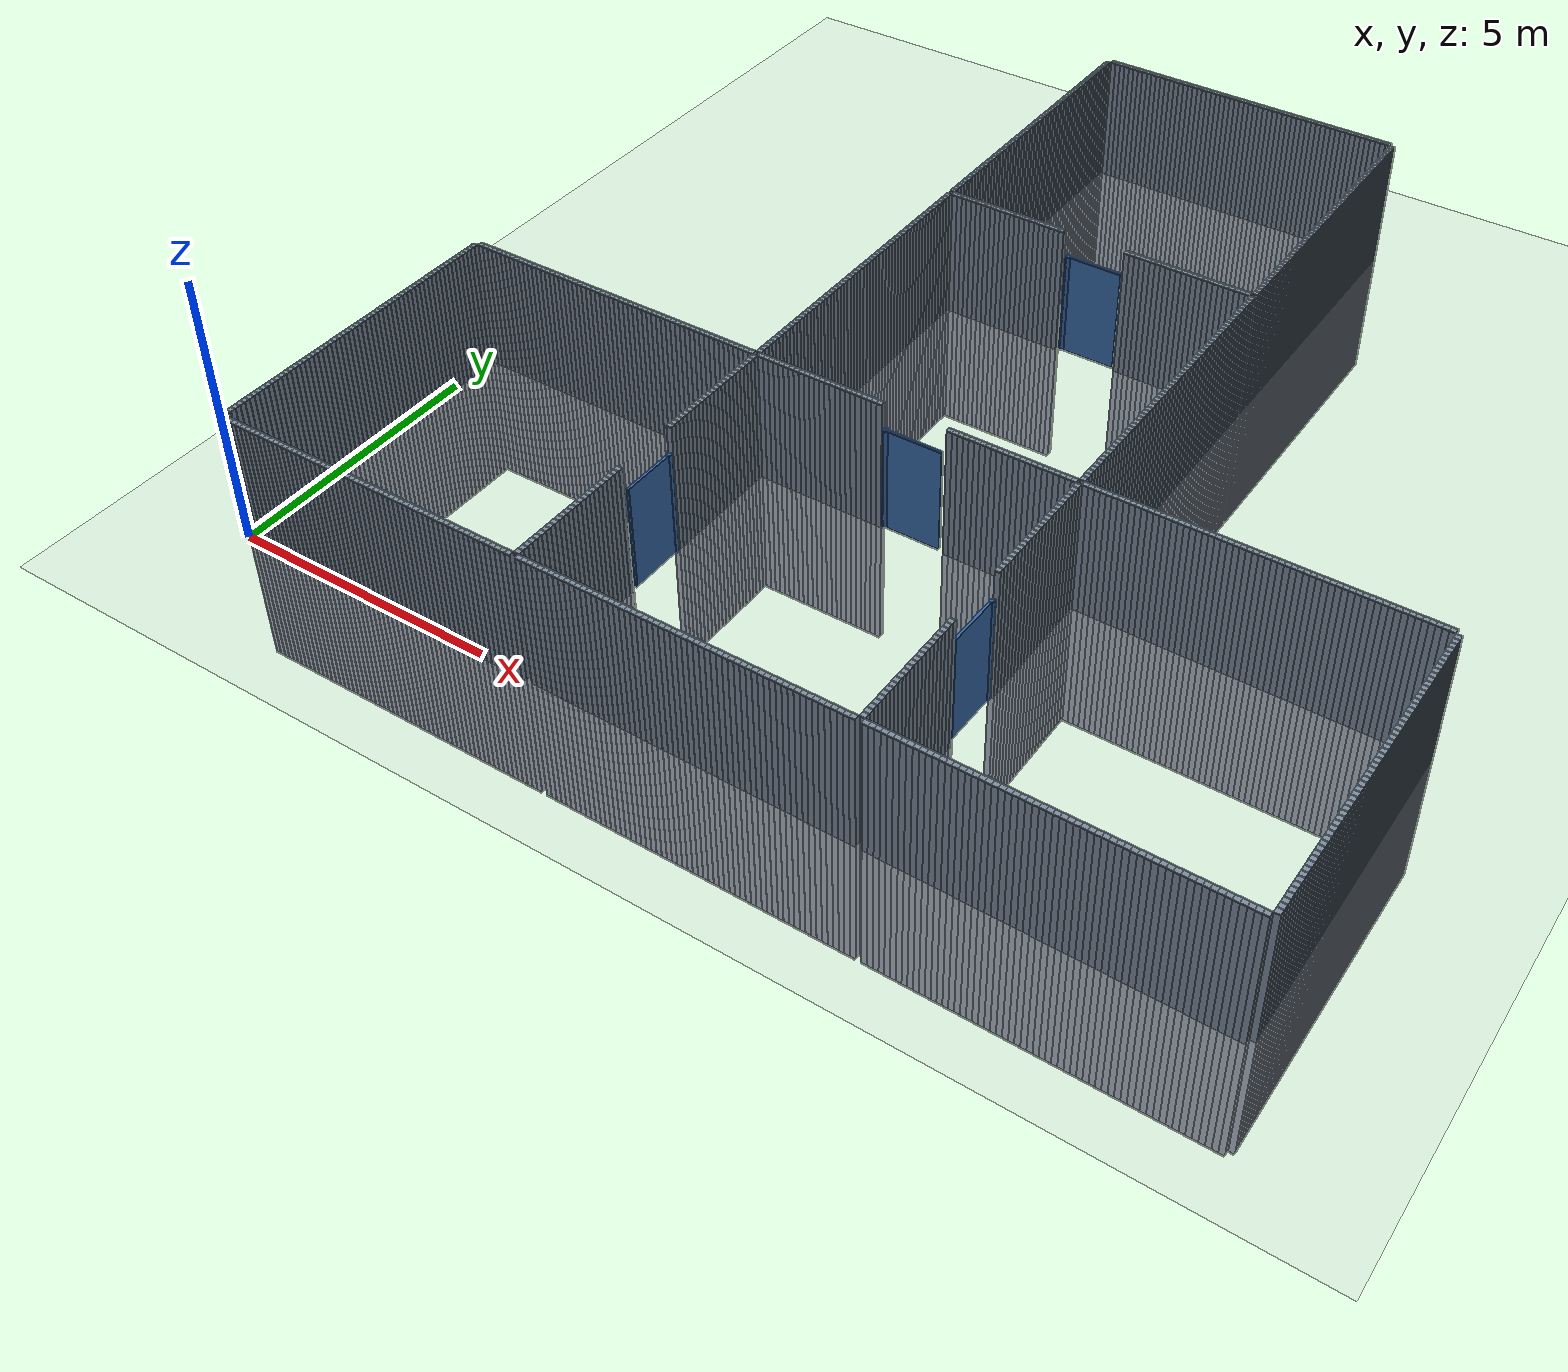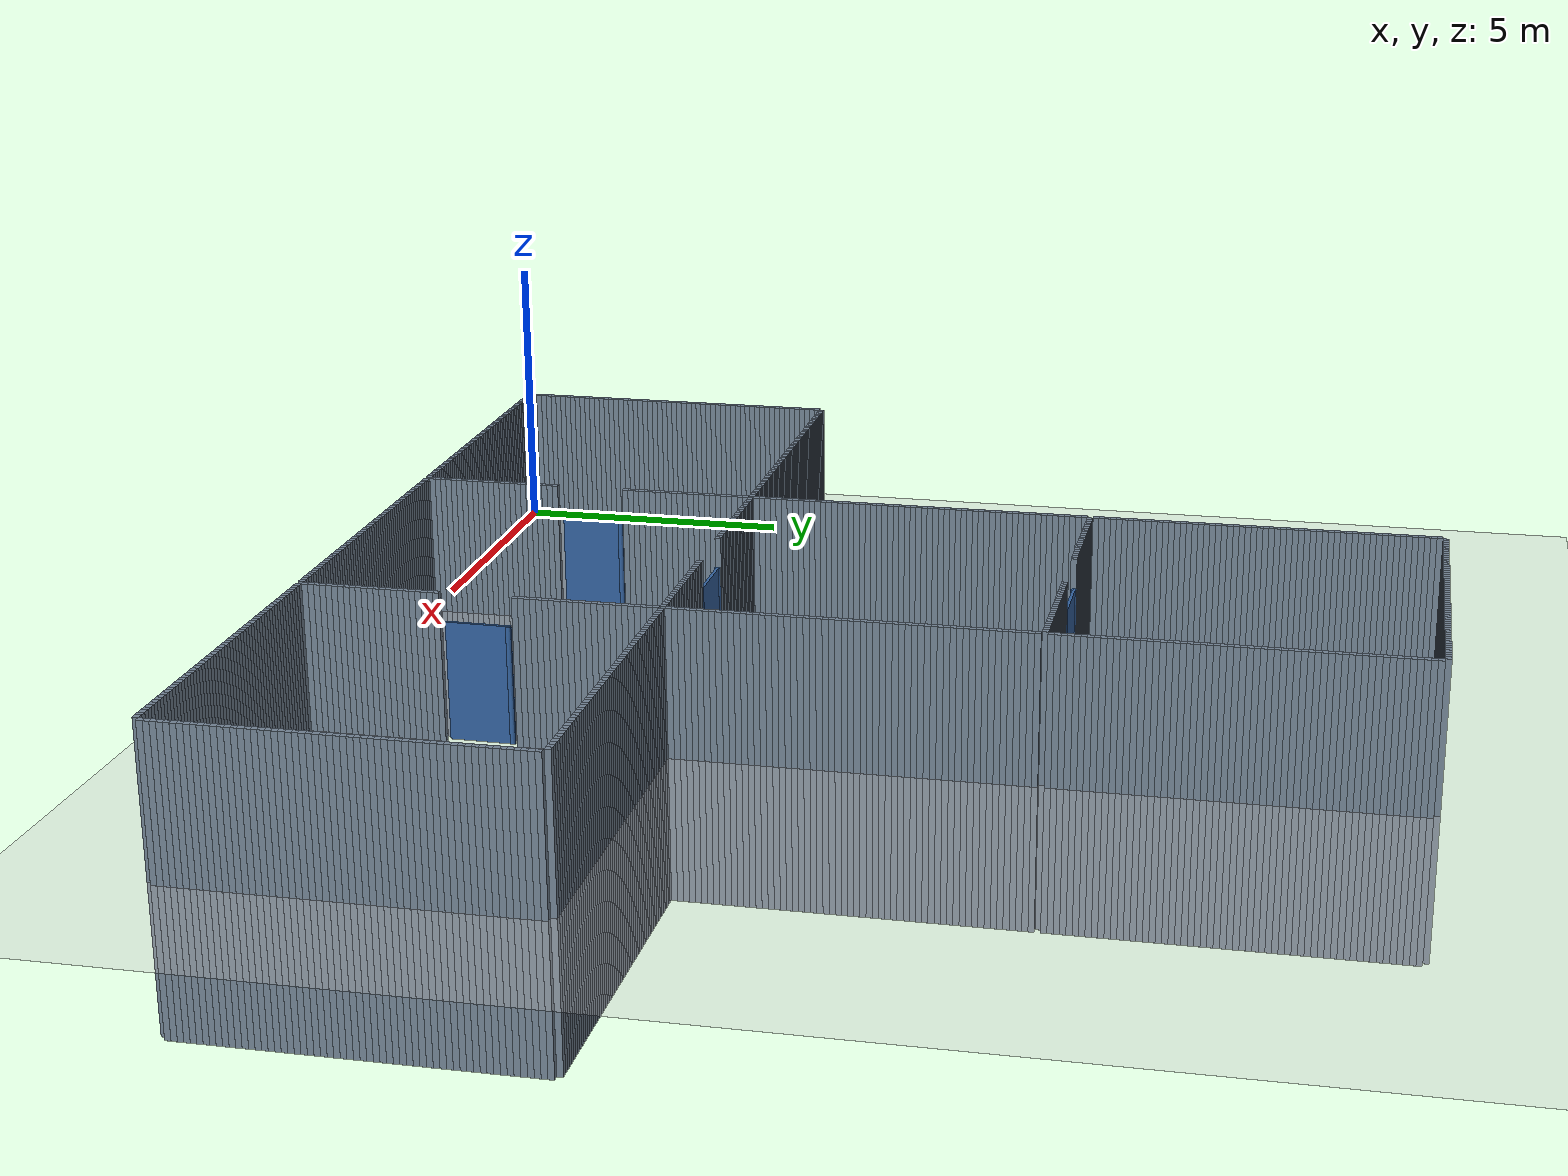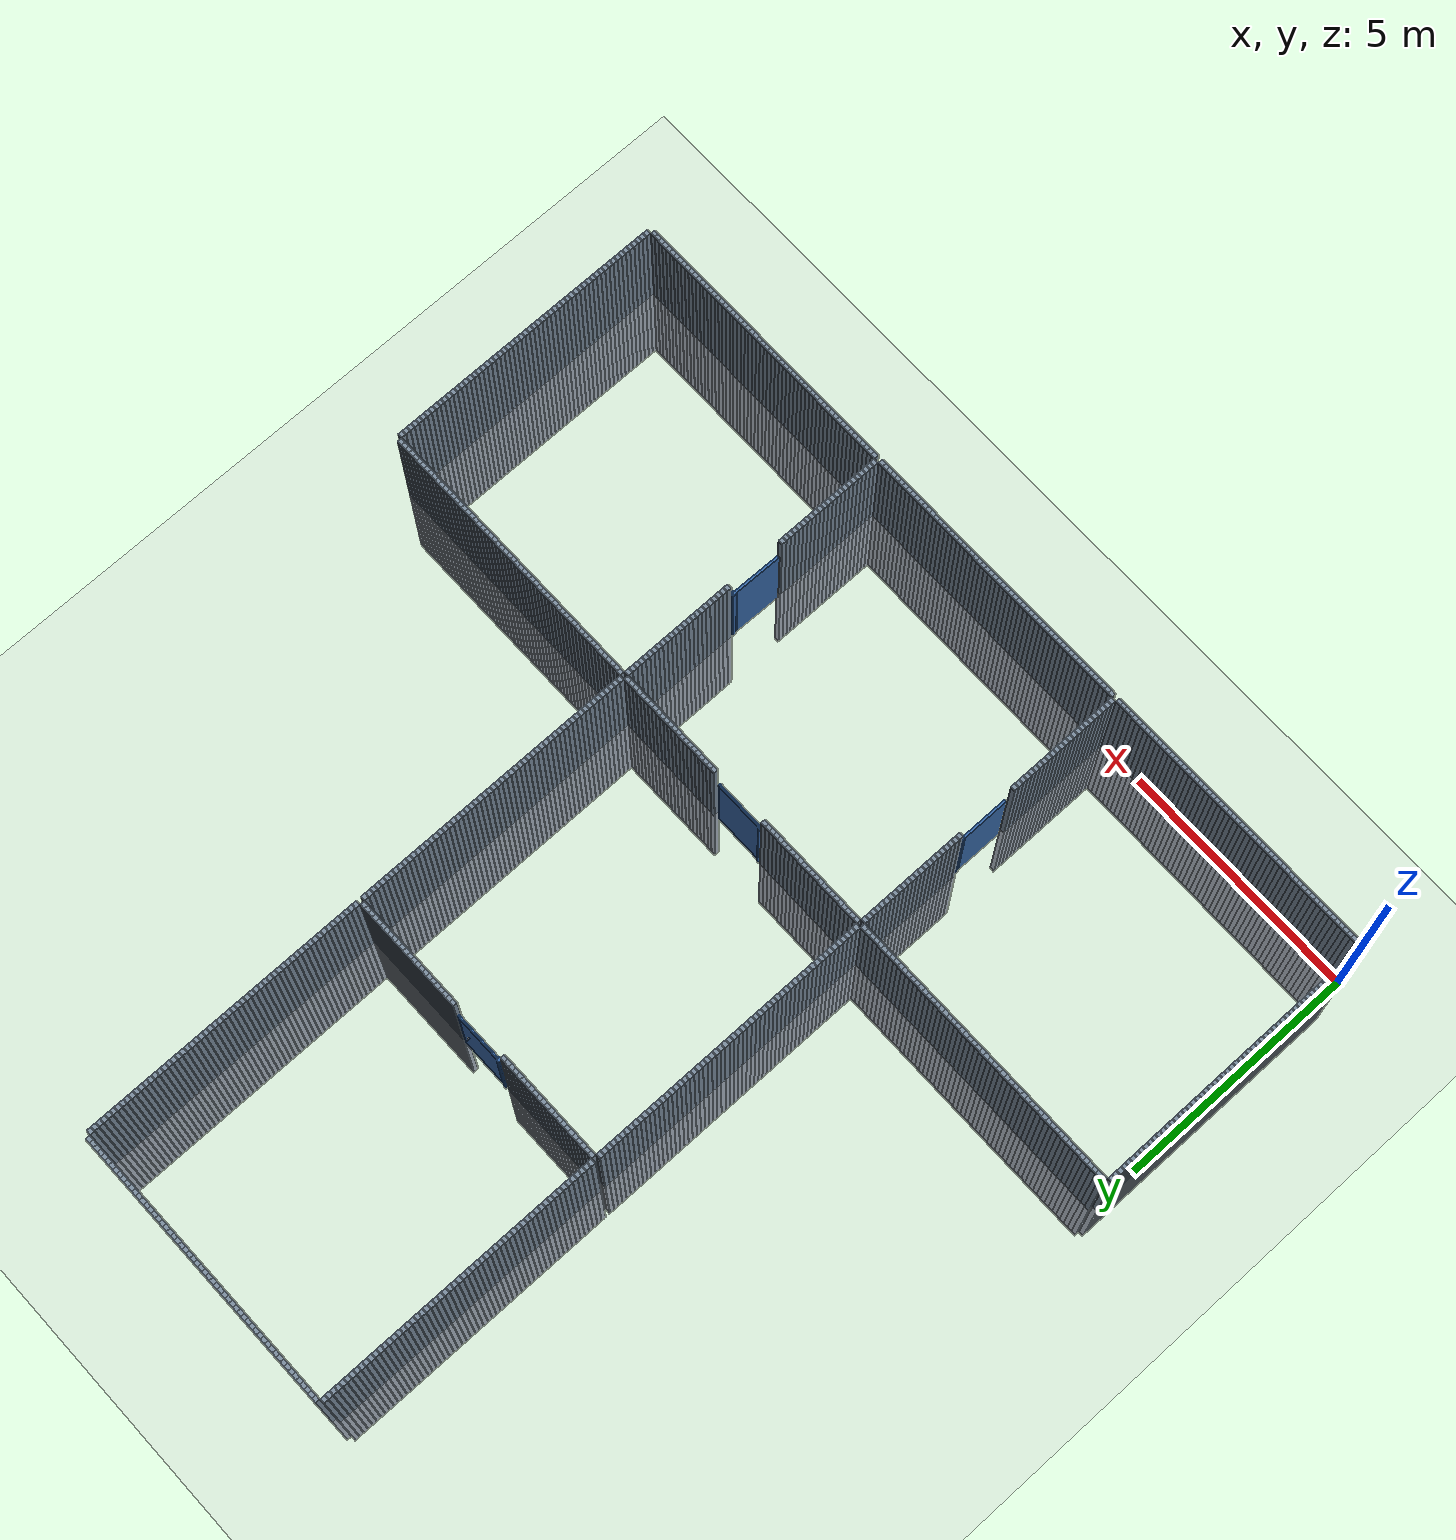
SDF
<sdf version="1.6">
 <world name="default">
  <light name="sun" type="directional">
   <pose>0 0 10 0 -0 0</pose>
   <diffuse>0.8 0.8 0.8 1</diffuse>
   <specular>0.1 0.1 0.1 1</specular>
   <attenuation>
    <range>1000</range>
    <constant>0.9</constant>
    <linear>0.01</linear>
    <quadratic>0.001</quadratic>
   </attenuation>
   <direction>-0.5 0.5 -1</direction>
  </light>
  <model name="ground_plane">
   <static>1</static>
   <link name="link">
    <collision name="collision">
     <geometry><plane><normal>0 0 1</normal><size>100 100</size></plane></geometry>
     <surface><friction><ode><mu>100</mu><mu2>50</mu2></ode></friction></surface>
    </collision>
    <visual name="visual">
     <cast_shadows>0</cast_shadows>
     <geometry><plane><normal>0 0 1</normal><size>100 100</size></plane></geometry>
     <material>
      <script><uri>file://media/materials/scripts/gazebo.material</uri><name>Gazebo/Grey</name></script>
     </material>
    </visual>
   </link>
  </model>
  <gravity>0 0 -9.8</gravity>
  <magnetic_field>6e-06 2.3e-05 -4.2e-05</magnetic_field>
  <atmosphere type="adiabatic"/>
  <physics name="default_physics" default="0" type="ode">
   <max_step_size>0.001</max_step_size>
   <real_time_factor>1</real_time_factor>
   <real_time_update_rate>1000</real_time_update_rate>
  </physics>
  <scene><ambient>0.4 0.4 0.4 1</ambient><background>0.7 0.7 0.7 1</background><shadows>1</shadows></scene>
  <spherical_coordinates>
   <surface_model>EARTH_WGS84</surface_model>
   <latitude_deg>0</latitude_deg>
   <longitude_deg>0</longitude_deg>
   <elevation>0</elevation>
   <heading_deg>0</heading_deg>
  </spherical_coordinates>
  <model name="unit_cylinder_1">
   <static>1</static>
   <pose>0 0.1 0 0 -0 0</pose>
   <link name="link">
    <inertial>
     <mass>1</mass>
     <inertia><ixx>0.145833</ixx><ixy>0</ixy><ixz>0</ixz><iyy>0.145833</iyy><iyz>0</iyz><izz>0.125</izz></inertia>
    </inertial>
    <collision name="collision"><geometry><box><size>0.1 0.1 5</size></box></geometry></collision>
    <visual name="visual">
     <geometry><box><size>0.1 0.1 5</size></box></geometry>
     <material><ambient>0.466667 0.533333 0.6 1</ambient><diffuse>0.466667 0.533333 0.6 1</diffuse></material>
     <material>
      <script><name>Gazebo/Grey</name><uri>file://media/materials/scripts/gazebo.material</uri></script>
     </material>
    </visual>
   </link>
  </model>
  <model name="unit_cylinder_2">
   <static>1</static>
   <pose>0 0.2 0 0 -0 0</pose>
   <link name="link">
    <inertial>
     <mass>1</mass>
     <inertia><ixx>0.145833</ixx><ixy>0</ixy><ixz>0</ixz><iyy>0.145833</iyy><iyz>0</iyz><izz>0.125</izz></inertia>
    </inertial>
    <collision name="collision"><geometry><box><size>0.1 0.1 5</size></box></geometry></collision>
    <visual name="visual">
     <geometry><box><size>0.1 0.1 5</size></box></geometry>
     <material><ambient>0.466667 0.533333 0.6 1</ambient><diffuse>0.466667 0.533333 0.6 1</diffuse></material>
     <material>
      <script><name>Gazebo/Grey</name><uri>file://media/materials/scripts/gazebo.material</uri></script>
     </material>
    </visual>
   </link>
  </model>
  <model name="unit_cylinder_3">
   <static>1</static>
   <pose>0 0.3 0 0 -0 0</pose>
   <link name="link">
    <inertial>
     <mass>1</mass>
     <inertia><ixx>0.145833</ixx><ixy>0</ixy><ixz>0</ixz><iyy>0.145833</iyy><iyz>0</iyz><izz>0.125</izz></inertia>
    </inertial>
    <collision name="collision"><geometry><box><size>0.1 0.1 5</size></box></geometry></collision>
    <visual name="visual">
     <geometry><box><size>0.1 0.1 5</size></box></geometry>
     <material><ambient>0.466667 0.533333 0.6 1</ambient><diffuse>0.466667 0.533333 0.6 1</diffuse></material>
     <material>
      <script><name>Gazebo/Grey</name><uri>file://media/materials/scripts/gazebo.material</uri></script>
     </material>
    </visual>
   </link>
  </model>
  <model name="unit_cylinder_4">
   <static>1</static>
   <pose>0 0.4 0 0 -0 0</pose>
   <link name="link">
    <inertial>
     <mass>1</mass>
     <inertia><ixx>0.145833</ixx><ixy>0</ixy><ixz>0</ixz><iyy>0.145833</iyy><iyz>0</iyz><izz>0.125</izz></inertia>
    </inertial>
    <collision name="collision"><geometry><box><size>0.1 0.1 5</size></box></geometry></collision>
    <visual name="visual">
     <geometry><box><size>0.1 0.1 5</size></box></geometry>
     <material><ambient>0.466667 0.533333 0.6 1</ambient><diffuse>0.466667 0.533333 0.6 1</diffuse></material>
     <material>
      <script><name>Gazebo/Grey</name><uri>file://media/materials/scripts/gazebo.material</uri></script>
     </material>
    </visual>
   </link>
  </model>
  <model name="unit_cylinder_5">
   <static>1</static>
   <pose>0 0.5 0 0 -0 0</pose>
   <link name="link">
    <inertial>
     <mass>1</mass>
     <inertia><ixx>0.145833</ixx><ixy>0</ixy><ixz>0</ixz><iyy>0.145833</iyy><iyz>0</iyz><izz>0.125</izz></inertia>
    </inertial>
    <collision name="collision"><geometry><box><size>0.1 0.1 5</size></box></geometry></collision>
    <visual name="visual">
     <geometry><box><size>0.1 0.1 5</size></box></geometry>
     <material><ambient>0.466667 0.533333 0.6 1</ambient><diffuse>0.466667 0.533333 0.6 1</diffuse></material>
     <material>
      <script><name>Gazebo/Grey</name><uri>file://media/materials/scripts/gazebo.material</uri></script>
     </material>
    </visual>
   </link>
  </model>
  <model name="unit_cylinder_6">
   <static>1</static>
   <pose>0 0.6 0 0 -0 0</pose>
   <link name="link">
    <inertial>
     <mass>1</mass>
     <inertia><ixx>0.145833</ixx><ixy>0</ixy><ixz>0</ixz><iyy>0.145833</iyy><iyz>0</iyz><izz>0.125</izz></inertia>
    </inertial>
    <collision name="collision"><geometry><box><size>0.1 0.1 5</size></box></geometry></collision>
    <visual name="visual">
     <geometry><box><size>0.1 0.1 5</size></box></geometry>
     <material><ambient>0.466667 0.533333 0.6 1</ambient><diffuse>0.466667 0.533333 0.6 1</diffuse></material>
     <material>
      <script><name>Gazebo/Grey</name><uri>file://media/materials/scripts/gazebo.material</uri></script>
     </material>
    </visual>
   </link>
  </model>
  <model name="unit_cylinder_7">
   <static>1</static>
   <pose>0 0.7 0 0 -0 0</pose>
   <link name="link">
    <inertial>
     <mass>1</mass>
     <inertia><ixx>0.145833</ixx><ixy>0</ixy><ixz>0</ixz><iyy>0.145833</iyy><iyz>0</iyz><izz>0.125</izz></inertia>
    </inertial>
    <collision name="collision"><geometry><box><size>0.1 0.1 5</size></box></geometry></collision>
    <visual name="visual">
     <geometry><box><size>0.1 0.1 5</size></box></geometry>
     <material><ambient>0.466667 0.533333 0.6 1</ambient><diffuse>0.466667 0.533333 0.6 1</diffuse></material>
     <material>
      <script><name>Gazebo/Grey</name><uri>file://media/materials/scripts/gazebo.material</uri></script>
     </material>
    </visual>
   </link>
  </model>
  <model name="unit_cylinder_8">
   <static>1</static>
   <pose>0 0.8 0 0 -0 0</pose>
   <link name="link">
    <inertial>
     <mass>1</mass>
     <inertia><ixx>0.145833</ixx><ixy>0</ixy><ixz>0</ixz><iyy>0.145833</iyy><iyz>0</iyz><izz>0.125</izz></inertia>
    </inertial>
    <collision name="collision"><geometry><box><size>0.1 0.1 5</size></box></geometry></collision>
    <visual name="visual">
     <geometry><box><size>0.1 0.1 5</size></box></geometry>
     <material><ambient>0.466667 0.533333 0.6 1</ambient><diffuse>0.466667 0.533333 0.6 1</diffuse></material>
     <material>
      <script><name>Gazebo/Grey</name><uri>file://media/materials/scripts/gazebo.material</uri></script>
     </material>
    </visual>
   </link>
  </model>
  <model name="unit_cylinder_9">
   <static>1</static>
   <pose>0 0.9 0 0 -0 0</pose>
   <link name="link">
    <inertial>
     <mass>1</mass>
     <inertia><ixx>0.145833</ixx><ixy>0</ixy><ixz>0</ixz><iyy>0.145833</iyy><iyz>0</iyz><izz>0.125</izz></inertia>
    </inertial>
    <collision name="collision"><geometry><box><size>0.1 0.1 5</size></box></geometry></collision>
    <visual name="visual">
     <geometry><box><size>0.1 0.1 5</size></box></geometry>
     <material><ambient>0.466667 0.533333 0.6 1</ambient><diffuse>0.466667 0.533333 0.6 1</diffuse></material>
     <material>
      <script><name>Gazebo/Grey</name><uri>file://media/materials/scripts/gazebo.material</uri></script>
     </material>
    </visual>
   </link>
  </model>
  <model name="unit_cylinder_10">
   <static>1</static>
   <pose>0 1 0 0 -0 0</pose>
   <link name="link">
    <inertial>
     <mass>1</mass>
     <inertia><ixx>0.145833</ixx><ixy>0</ixy><ixz>0</ixz><iyy>0.145833</iyy><iyz>0</iyz><izz>0.125</izz></inertia>
    </inertial>
    <collision name="collision"><geometry><box><size>0.1 0.1 5</size></box></geometry></collision>
    <visual name="visual">
     <geometry><box><size>0.1 0.1 5</size></box></geometry>
     <material><ambient>0.466667 0.533333 0.6 1</ambient><diffuse>0.466667 0.533333 0.6 1</diffuse></material>
     <material>
      <script><name>Gazebo/Grey</name><uri>file://media/materials/scripts/gazebo.material</uri></script>
     </material>
    </visual>
   </link>
  </model>
  <model name="unit_cylinder_11">
   <static>1</static>
   <pose>0 1.1 0 0 -0 0</pose>
   <link name="link">
    <inertial>
     <mass>1</mass>
     <inertia><ixx>0.145833</ixx><ixy>0</ixy><ixz>0</ixz><iyy>0.145833</iyy><iyz>0</iyz><izz>0.125</izz></inertia>
    </inertial>
    <collision name="collision"><geometry><box><size>0.1 0.1 5</size></box></geometry></collision>
    <visual name="visual">
     <geometry><box><size>0.1 0.1 5</size></box></geometry>
     <material><ambient>0.466667 0.533333 0.6 1</ambient><diffuse>0.466667 0.533333 0.6 1</diffuse></material>
     <material>
      <script><name>Gazebo/Grey</name><uri>file://media/materials/scripts/gazebo.material</uri></script>
     </material>
    </visual>
   </link>
  </model>
  <model name="unit_cylinder_12">
   <static>1</static>
   <pose>0 1.2 0 0 -0 0</pose>
   <link name="link">
    <inertial>
     <mass>1</mass>
     <inertia><ixx>0.145833</ixx><ixy>0</ixy><ixz>0</ixz><iyy>0.145833</iyy><iyz>0</iyz><izz>0.125</izz></inertia>
    </inertial>
    <collision name="collision"><geometry><box><size>0.1 0.1 5</size></box></geometry></collision>
    <visual name="visual">
     <geometry><box><size>0.1 0.1 5</size></box></geometry>
     <material><ambient>0.466667 0.533333 0.6 1</ambient><diffuse>0.466667 0.533333 0.6 1</diffuse></material>
     <material>
      <script><name>Gazebo/Grey</name><uri>file://media/materials/scripts/gazebo.material</uri></script>
     </material>
    </visual>
   </link>
  </model>
  <model name="unit_cylinder_13">
   <static>1</static>
   <pose>0 1.3 0 0 -0 0</pose>
   <link name="link">
    <inertial>
     <mass>1</mass>
     <inertia><ixx>0.145833</ixx><ixy>0</ixy><ixz>0</ixz><iyy>0.145833</iyy><iyz>0</iyz><izz>0.125</izz></inertia>
    </inertial>
    <collision name="collision"><geometry><box><size>0.1 0.1 5</size></box></geometry></collision>
    <visual name="visual">
     <geometry><box><size>0.1 0.1 5</size></box></geometry>
     <material><ambient>0.466667 0.533333 0.6 1</ambient><diffuse>0.466667 0.533333 0.6 1</diffuse></material>
     <material>
      <script><name>Gazebo/Grey</name><uri>file://media/materials/scripts/gazebo.material</uri></script>
     </material>
    </visual>
   </link>
  </model>
  <model name="unit_cylinder_14">
   <static>1</static>
   <pose>0 1.4 0 0 -0 0</pose>
   <link name="link">
    <inertial>
     <mass>1</mass>
     <inertia><ixx>0.145833</ixx><ixy>0</ixy><ixz>0</ixz><iyy>0.145833</iyy><iyz>0</iyz><izz>0.125</izz></inertia>
    </inertial>
    <collision name="collision"><geometry><box><size>0.1 0.1 5</size></box></geometry></collision>
    <visual name="visual">
     <geometry><box><size>0.1 0.1 5</size></box></geometry>
     <material><ambient>0.466667 0.533333 0.6 1</ambient><diffuse>0.466667 0.533333 0.6 1</diffuse></material>
     <material>
      <script><name>Gazebo/Grey</name><uri>file://media/materials/scripts/gazebo.material</uri></script>
     </material>
    </visual>
   </link>
  </model>
  <model name="unit_cylinder_15">
   <static>1</static>
   <pose>0 1.5 0 0 -0 0</pose>
   <link name="link">
    <inertial>
     <mass>1</mass>
     <inertia><ixx>0.145833</ixx><ixy>0</ixy><ixz>0</ixz><iyy>0.145833</iyy><iyz>0</iyz><izz>0.125</izz></inertia>
    </inertial>
    <collision name="collision"><geometry><box><size>0.1 0.1 5</size></box></geometry></collision>
    <visual name="visual">
     <geometry><box><size>0.1 0.1 5</size></box></geometry>
     <material><ambient>0.466667 0.533333 0.6 1</ambient><diffuse>0.466667 0.533333 0.6 1</diffuse></material>
     <material>
      <script><name>Gazebo/Grey</name><uri>file://media/materials/scripts/gazebo.material</uri></script>
     </material>
    </visual>
   </link>
  </model>
  <model name="unit_cylinder_16">
   <static>1</static>
   <pose>0 1.6 0 0 -0 0</pose>
   <link name="link">
    <inertial>
     <mass>1</mass>
     <inertia><ixx>0.145833</ixx><ixy>0</ixy><ixz>0</ixz><iyy>0.145833</iyy><iyz>0</iyz><izz>0.125</izz></inertia>
    </inertial>
    <collision name="collision"><geometry><box><size>0.1 0.1 5</size></box></geometry></collision>
    <visual name="visual">
     <geometry><box><size>0.1 0.1 5</size></box></geometry>
     <material><ambient>0.466667 0.533333 0.6 1</ambient><diffuse>0.466667 0.533333 0.6 1</diffuse></material>
     <material>
      <script><name>Gazebo/Grey</name><uri>file://media/materials/scripts/gazebo.material</uri></script>
     </material>
    </visual>
   </link>
  </model>
  <model name="unit_cylinder_17">
   <static>1</static>
   <pose>0 1.7 0 0 -0 0</pose>
   <link name="link">
    <inertial>
     <mass>1</mass>
     <inertia><ixx>0.145833</ixx><ixy>0</ixy><ixz>0</ixz><iyy>0.145833</iyy><iyz>0</iyz><izz>0.125</izz></inertia>
    </inertial>
    <collision name="collision"><geometry><box><size>0.1 0.1 5</size></box></geometry></collision>
    <visual name="visual">
     <geometry><box><size>0.1 0.1 5</size></box></geometry>
     <material><ambient>0.466667 0.533333 0.6 1</ambient><diffuse>0.466667 0.533333 0.6 1</diffuse></material>
     <material>
      <script><name>Gazebo/Grey</name><uri>file://media/materials/scripts/gazebo.material</uri></script>
     </material>
    </visual>
   </link>
  </model>
  <model name="unit_cylinder_18">
   <static>1</static>
   <pose>0 1.8 0 0 -0 0</pose>
   <link name="link">
    <inertial>
     <mass>1</mass>
     <inertia><ixx>0.145833</ixx><ixy>0</ixy><ixz>0</ixz><iyy>0.145833</iyy><iyz>0</iyz><izz>0.125</izz></inertia>
    </inertial>
    <collision name="collision"><geometry><box><size>0.1 0.1 5</size></box></geometry></collision>
    <visual name="visual">
     <geometry><box><size>0.1 0.1 5</size></box></geometry>
     <material><ambient>0.466667 0.533333 0.6 1</ambient><diffuse>0.466667 0.533333 0.6 1</diffuse></material>
     <material>
      <script><name>Gazebo/Grey</name><uri>file://media/materials/scripts/gazebo.material</uri></script>
     </material>
    </visual>
   </link>
  </model>
  <model name="unit_cylinder_19">
   <static>1</static>
   <pose>0 1.9 0 0 -0 0</pose>
   <link name="link">
    <inertial>
     <mass>1</mass>
     <inertia><ixx>0.145833</ixx><ixy>0</ixy><ixz>0</ixz><iyy>0.145833</iyy><iyz>0</iyz><izz>0.125</izz></inertia>
    </inertial>
    <collision name="collision"><geometry><box><size>0.1 0.1 5</size></box></geometry></collision>
    <visual name="visual">
     <geometry><box><size>0.1 0.1 5</size></box></geometry>
     <material><ambient>0.466667 0.533333 0.6 1</ambient><diffuse>0.466667 0.533333 0.6 1</diffuse></material>
     <material>
      <script><name>Gazebo/Grey</name><uri>file://media/materials/scripts/gazebo.material</uri></script>
     </material>
    </visual>
   </link>
  </model>
  <model name="unit_cylinder_20">
   <static>1</static>
   <pose>0 2 0 0 -0 0</pose>
   <link name="link">
    <inertial>
     <mass>1</mass>
     <inertia><ixx>0.145833</ixx><ixy>0</ixy><ixz>0</ixz><iyy>0.145833</iyy><iyz>0</iyz><izz>0.125</izz></inertia>
    </inertial>
    <collision name="collision"><geometry><box><size>0.1 0.1 5</size></box></geometry></collision>
    <visual name="visual">
     <geometry><box><size>0.1 0.1 5</size></box></geometry>
     <material><ambient>0.466667 0.533333 0.6 1</ambient><diffuse>0.466667 0.533333 0.6 1</diffuse></material>
     <material>
      <script><name>Gazebo/Grey</name><uri>file://media/materials/scripts/gazebo.material</uri></script>
     </material>
    </visual>
   </link>
  </model>
  <model name="unit_cylinder_21">
   <static>1</static>
   <pose>0 2.1 0 0 -0 0</pose>
   <link name="link">
    <inertial>
     <mass>1</mass>
     <inertia><ixx>0.145833</ixx><ixy>0</ixy><ixz>0</ixz><iyy>0.145833</iyy><iyz>0</iyz><izz>0.125</izz></inertia>
    </inertial>
    <collision name="collision"><geometry><box><size>0.1 0.1 5</size></box></geometry></collision>
    <visual name="visual">
     <geometry><box><size>0.1 0.1 5</size></box></geometry>
     <material><ambient>0.466667 0.533333 0.6 1</ambient><diffuse>0.466667 0.533333 0.6 1</diffuse></material>
     <material>
      <script><name>Gazebo/Grey</name><uri>file://media/materials/scripts/gazebo.material</uri></script>
     </material>
    </visual>
   </link>
  </model>
  <model name="unit_cylinder_22">
   <static>1</static>
   <pose>0 2.2 0 0 -0 0</pose>
   <link name="link">
    <inertial>
     <mass>1</mass>
     <inertia><ixx>0.145833</ixx><ixy>0</ixy><ixz>0</ixz><iyy>0.145833</iyy><iyz>0</iyz><izz>0.125</izz></inertia>
    </inertial>
    <collision name="collision"><geometry><box><size>0.1 0.1 5</size></box></geometry></collision>
    <visual name="visual">
     <geometry><box><size>0.1 0.1 5</size></box></geometry>
     <material><ambient>0.466667 0.533333 0.6 1</ambient><diffuse>0.466667 0.533333 0.6 1</diffuse></material>
     <material>
      <script><name>Gazebo/Grey</name><uri>file://media/materials/scripts/gazebo.material</uri></script>
     </material>
    </visual>
   </link>
  </model>
  <model name="unit_cylinder_23">
   <static>1</static>
   <pose>0 2.3 0 0 -0 0</pose>
   <link name="link">
    <inertial>
     <mass>1</mass>
     <inertia><ixx>0.145833</ixx><ixy>0</ixy><ixz>0</ixz><iyy>0.145833</iyy><iyz>0</iyz><izz>0.125</izz></inertia>
    </inertial>
    <collision name="collision"><geometry><box><size>0.1 0.1 5</size></box></geometry></collision>
    <visual name="visual">
     <geometry><box><size>0.1 0.1 5</size></box></geometry>
     <material><ambient>0.466667 0.533333 0.6 1</ambient><diffuse>0.466667 0.533333 0.6 1</diffuse></material>
     <material>
      <script><name>Gazebo/Grey</name><uri>file://media/materials/scripts/gazebo.material</uri></script>
     </material>
    </visual>
   </link>
  </model>
  <model name="unit_cylinder_24">
   <static>1</static>
   <pose>0 2.4 0 0 -0 0</pose>
   <link name="link">
    <inertial>
     <mass>1</mass>
     <inertia><ixx>0.145833</ixx><ixy>0</ixy><ixz>0</ixz><iyy>0.145833</iyy><iyz>0</iyz><izz>0.125</izz></inertia>
    </inertial>
    <collision name="collision"><geometry><box><size>0.1 0.1 5</size></box></geometry></collision>
    <visual name="visual">
     <geometry><box><size>0.1 0.1 5</size></box></geometry>
     <material><ambient>0.466667 0.533333 0.6 1</ambient><diffuse>0.466667 0.533333 0.6 1</diffuse></material>
     <material>
      <script><name>Gazebo/Grey</name><uri>file://media/materials/scripts/gazebo.material</uri></script>
     </material>
    </visual>
   </link>
  </model>
  <model name="unit_cylinder_25">
   <static>1</static>
   <pose>0 2.5 0 0 -0 0</pose>
   <link name="link">
    <inertial>
     <mass>1</mass>
     <inertia><ixx>0.145833</ixx><ixy>0</ixy><ixz>0</ixz><iyy>0.145833</iyy><iyz>0</iyz><izz>0.125</izz></inertia>
    </inertial>
    <collision name="collision"><geometry><box><size>0.1 0.1 5</size></box></geometry></collision>
    <visual name="visual">
     <geometry><box><size>0.1 0.1 5</size></box></geometry>
     <material><ambient>0.466667 0.533333 0.6 1</ambient><diffuse>0.466667 0.533333 0.6 1</diffuse></material>
     <material>
      <script><name>Gazebo/Grey</name><uri>file://media/materials/scripts/gazebo.material</uri></script>
     </material>
    </visual>
   </link>
  </model>
  <model name="unit_cylinder_26">
   <static>1</static>
   <pose>0 2.6 0 0 -0 0</pose>
   <link name="link">
    <inertial>
     <mass>1</mass>
     <inertia><ixx>0.145833</ixx><ixy>0</ixy><ixz>0</ixz><iyy>0.145833</iyy><iyz>0</iyz><izz>0.125</izz></inertia>
    </inertial>
    <collision name="collision"><geometry><box><size>0.1 0.1 5</size></box></geometry></collision>
    <visual name="visual">
     <geometry><box><size>0.1 0.1 5</size></box></geometry>
     <material><ambient>0.466667 0.533333 0.6 1</ambient><diffuse>0.466667 0.533333 0.6 1</diffuse></material>
     <material>
      <script><name>Gazebo/Grey</name><uri>file://media/materials/scripts/gazebo.material</uri></script>
     </material>
    </visual>
   </link>
  </model>
  <model name="unit_cylinder_27">
   <static>1</static>
   <pose>0 2.7 0 0 -0 0</pose>
   <link name="link">
    <inertial>
     <mass>1</mass>
     <inertia><ixx>0.145833</ixx><ixy>0</ixy><ixz>0</ixz><iyy>0.145833</iyy><iyz>0</iyz><izz>0.125</izz></inertia>
    </inertial>
    <collision name="collision"><geometry><box><size>0.1 0.1 5</size></box></geometry></collision>
    <visual name="visual">
     <geometry><box><size>0.1 0.1 5</size></box></geometry>
     <material><ambient>0.466667 0.533333 0.6 1</ambient><diffuse>0.466667 0.533333 0.6 1</diffuse></material>
     <material>
      <script><name>Gazebo/Grey</name><uri>file://media/materials/scripts/gazebo.material</uri></script>
     </material>
    </visual>
   </link>
  </model>
  <model name="unit_cylinder_28">
   <static>1</static>
   <pose>0 2.8 0 0 -0 0</pose>
   <link name="link">
    <inertial>
     <mass>1</mass>
     <inertia><ixx>0.145833</ixx><ixy>0</ixy><ixz>0</ixz><iyy>0.145833</iyy><iyz>0</iyz><izz>0.125</izz></inertia>
    </inertial>
    <collision name="collision"><geometry><box><size>0.1 0.1 5</size></box></geometry></collision>
    <visual name="visual">
     <geometry><box><size>0.1 0.1 5</size></box></geometry>
     <material><ambient>0.466667 0.533333 0.6 1</ambient><diffuse>0.466667 0.533333 0.6 1</diffuse></material>
     <material>
      <script><name>Gazebo/Grey</name><uri>file://media/materials/scripts/gazebo.material</uri></script>
     </material>
    </visual>
   </link>
  </model>
  <model name="unit_cylinder_29">
   <static>1</static>
   <pose>0 2.9 0 0 -0 0</pose>
   <link name="link">
    <inertial>
     <mass>1</mass>
     <inertia><ixx>0.145833</ixx><ixy>0</ixy><ixz>0</ixz><iyy>0.145833</iyy><iyz>0</iyz><izz>0.125</izz></inertia>
    </inertial>
    <collision name="collision"><geometry><box><size>0.1 0.1 5</size></box></geometry></collision>
    <visual name="visual">
     <geometry><box><size>0.1 0.1 5</size></box></geometry>
     <material><ambient>0.466667 0.533333 0.6 1</ambient><diffuse>0.466667 0.533333 0.6 1</diffuse></material>
     <material>
      <script><name>Gazebo/Grey</name><uri>file://media/materials/scripts/gazebo.material</uri></script>
     </material>
    </visual>
   </link>
  </model>
  <model name="unit_cylinder_30">
   <static>1</static>
   <pose>0 3 0 0 -0 0</pose>
   <link name="link">
    <inertial>
     <mass>1</mass>
     <inertia><ixx>0.145833</ixx><ixy>0</ixy><ixz>0</ixz><iyy>0.145833</iyy><iyz>0</iyz><izz>0.125</izz></inertia>
    </inertial>
    <collision name="collision"><geometry><box><size>0.1 0.1 5</size></box></geometry></collision>
    <visual name="visual">
     <geometry><box><size>0.1 0.1 5</size></box></geometry>
     <material><ambient>0.466667 0.533333 0.6 1</ambient><diffuse>0.466667 0.533333 0.6 1</diffuse></material>
     <material>
      <script><name>Gazebo/Grey</name><uri>file://media/materials/scripts/gazebo.material</uri></script>
     </material>
    </visual>
   </link>
  </model>
  <model name="unit_cylinder_31">
   <static>1</static>
   <pose>0 3.1 0 0 -0 0</pose>
   <link name="link">
    <inertial>
     <mass>1</mass>
     <inertia><ixx>0.145833</ixx><ixy>0</ixy><ixz>0</ixz><iyy>0.145833</iyy><iyz>0</iyz><izz>0.125</izz></inertia>
    </inertial>
    <collision name="collision"><geometry><box><size>0.1 0.1 5</size></box></geometry></collision>
    <visual name="visual">
     <geometry><box><size>0.1 0.1 5</size></box></geometry>
     <material><ambient>0.466667 0.533333 0.6 1</ambient><diffuse>0.466667 0.533333 0.6 1</diffuse></material>
     <material>
      <script><name>Gazebo/Grey</name><uri>file://media/materials/scripts/gazebo.material</uri></script>
     </material>
    </visual>
   </link>
  </model>
  <model name="unit_cylinder_32">
   <static>1</static>
   <pose>0 3.2 0 0 -0 0</pose>
   <link name="link">
    <inertial>
     <mass>1</mass>
     <inertia><ixx>0.145833</ixx><ixy>0</ixy><ixz>0</ixz><iyy>0.145833</iyy><iyz>0</iyz><izz>0.125</izz></inertia>
    </inertial>
    <collision name="collision"><geometry><box><size>0.1 0.1 5</size></box></geometry></collision>
    <visual name="visual">
     <geometry><box><size>0.1 0.1 5</size></box></geometry>
     <material><ambient>0.466667 0.533333 0.6 1</ambient><diffuse>0.466667 0.533333 0.6 1</diffuse></material>
     <material>
      <script><name>Gazebo/Grey</name><uri>file://media/materials/scripts/gazebo.material</uri></script>
     </material>
    </visual>
   </link>
  </model>
  <model name="unit_cylinder_33">
   <static>1</static>
   <pose>0 3.3 0 0 -0 0</pose>
   <link name="link">
    <inertial>
     <mass>1</mass>
     <inertia><ixx>0.145833</ixx><ixy>0</ixy><ixz>0</ixz><iyy>0.145833</iyy><iyz>0</iyz><izz>0.125</izz></inertia>
    </inertial>
    <collision name="collision"><geometry><box><size>0.1 0.1 5</size></box></geometry></collision>
    <visual name="visual">
     <geometry><box><size>0.1 0.1 5</size></box></geometry>
     <material><ambient>0.466667 0.533333 0.6 1</ambient><diffuse>0.466667 0.533333 0.6 1</diffuse></material>
     <material>
      <script><name>Gazebo/Grey</name><uri>file://media/materials/scripts/gazebo.material</uri></script>
     </material>
    </visual>
   </link>
  </model>
  <model name="unit_cylinder_34">
   <static>1</static>
   <pose>0 3.4 0 0 -0 0</pose>
   <link name="link">
    <inertial>
     <mass>1</mass>
     <inertia><ixx>0.145833</ixx><ixy>0</ixy><ixz>0</ixz><iyy>0.145833</iyy><iyz>0</iyz><izz>0.125</izz></inertia>
    </inertial>
    <collision name="collision"><geometry><box><size>0.1 0.1 5</size></box></geometry></collision>
    <visual name="visual">
     <geometry><box><size>0.1 0.1 5</size></box></geometry>
     <material><ambient>0.466667 0.533333 0.6 1</ambient><diffuse>0.466667 0.533333 0.6 1</diffuse></material>
     <material>
      <script><name>Gazebo/Grey</name><uri>file://media/materials/scripts/gazebo.material</uri></script>
     </material>
    </visual>
   </link>
  </model>
  <model name="unit_cylinder_35">
   <static>1</static>
   <pose>0 3.5 0 0 -0 0</pose>
   <link name="link">
    <inertial>
     <mass>1</mass>
     <inertia><ixx>0.145833</ixx><ixy>0</ixy><ixz>0</ixz><iyy>0.145833</iyy><iyz>0</iyz><izz>0.125</izz></inertia>
    </inertial>
    <collision name="collision"><geometry><box><size>0.1 0.1 5</size></box></geometry></collision>
    <visual name="visual">
     <geometry><box><size>0.1 0.1 5</size></box></geometry>
     <material><ambient>0.466667 0.533333 0.6 1</ambient><diffuse>0.466667 0.533333 0.6 1</diffuse></material>
     <material>
      <script><name>Gazebo/Grey</name><uri>file://media/materials/scripts/gazebo.material</uri></script>
     </material>
    </visual>
   </link>
  </model>
  <model name="unit_cylinder_36">
   <static>1</static>
   <pose>0 3.6 0 0 -0 0</pose>
   <link name="link">
    <inertial>
     <mass>1</mass>
     <inertia><ixx>0.145833</ixx><ixy>0</ixy><ixz>0</ixz><iyy>0.145833</iyy><iyz>0</iyz><izz>0.125</izz></inertia>
    </inertial>
    <collision name="collision"><geometry><box><size>0.1 0.1 5</size></box></geometry></collision>
    <visual name="visual">
     <geometry><box><size>0.1 0.1 5</size></box></geometry>
     <material><ambient>0.466667 0.533333 0.6 1</ambient><diffuse>0.466667 0.533333 0.6 1</diffuse></material>
     <material>
      <script><name>Gazebo/Grey</name><uri>file://media/materials/scripts/gazebo.material</uri></script>
     </material>
    </visual>
   </link>
  </model>
  <model name="unit_cylinder_37">
   <static>1</static>
   <pose>0 3.7 0 0 -0 0</pose>
   <link name="link">
    <inertial>
     <mass>1</mass>
     <inertia><ixx>0.145833</ixx><ixy>0</ixy><ixz>0</ixz><iyy>0.145833</iyy><iyz>0</iyz><izz>0.125</izz></inertia>
    </inertial>
    <collision name="collision"><geometry><box><size>0.1 0.1 5</size></box></geometry></collision>
    <visual name="visual">
     <geometry><box><size>0.1 0.1 5</size></box></geometry>
     <material><ambient>0.466667 0.533333 0.6 1</ambient><diffuse>0.466667 0.533333 0.6 1</diffuse></material>
     <material>
      <script><name>Gazebo/Grey</name><uri>file://media/materials/scripts/gazebo.material</uri></script>
     </material>
    </visual>
   </link>
  </model>
  <model name="unit_cylinder_38">
   <static>1</static>
   <pose>0 3.8 0 0 -0 0</pose>
   <link name="link">
    <inertial>
     <mass>1</mass>
     <inertia><ixx>0.145833</ixx><ixy>0</ixy><ixz>0</ixz><iyy>0.145833</iyy><iyz>0</iyz><izz>0.125</izz></inertia>
    </inertial>
    <collision name="collision"><geometry><box><size>0.1 0.1 5</size></box></geometry></collision>
    <visual name="visual">
     <geometry><box><size>0.1 0.1 5</size></box></geometry>
     <material><ambient>0.466667 0.533333 0.6 1</ambient><diffuse>0.466667 0.533333 0.6 1</diffuse></material>
     <material>
      <script><name>Gazebo/Grey</name><uri>file://media/materials/scripts/gazebo.material</uri></script>
     </material>
    </visual>
   </link>
  </model>
  <model name="unit_cylinder_39">
   <static>1</static>
   <pose>0 3.9 0 0 -0 0</pose>
   <link name="link">
    <inertial>
     <mass>1</mass>
     <inertia><ixx>0.145833</ixx><ixy>0</ixy><ixz>0</ixz><iyy>0.145833</iyy><iyz>0</iyz><izz>0.125</izz></inertia>
    </inertial>
    <collision name="collision"><geometry><box><size>0.1 0.1 5</size></box></geometry></collision>
    <visual name="visual">
     <geometry><box><size>0.1 0.1 5</size></box></geometry>
     <material><ambient>0.466667 0.533333 0.6 1</ambient><diffuse>0.466667 0.533333 0.6 1</diffuse></material>
     <material>
      <script><name>Gazebo/Grey</name><uri>file://media/materials/scripts/gazebo.material</uri></script>
     </material>
    </visual>
   </link>
  </model>
  <model name="unit_cylinder_40">
   <static>1</static>
   <pose>0 4 0 0 -0 0</pose>
   <link name="link">
    <inertial>
     <mass>1</mass>
     <inertia><ixx>0.145833</ixx><ixy>0</ixy><ixz>0</ixz><iyy>0.145833</iyy><iyz>0</iyz><izz>0.125</izz></inertia>
    </inertial>
    <collision name="collision"><geometry><box><size>0.1 0.1 5</size></box></geometry></collision>
    <visual name="visual">
     <geometry><box><size>0.1 0.1 5</size></box></geometry>
     <material><ambient>0.466667 0.533333 0.6 1</ambient><diffuse>0.466667 0.533333 0.6 1</diffuse></material>
     <material>
      <script><name>Gazebo/Grey</name><uri>file://media/materials/scripts/gazebo.material</uri></script>
     </material>
    </visual>
   </link>
  </model>
  <model name="unit_cylinder_41">
   <static>1</static>
   <pose>0 4.1 0 0 -0 0</pose>
   <link name="link">
    <inertial>
     <mass>1</mass>
     <inertia><ixx>0.145833</ixx><ixy>0</ixy><ixz>0</ixz><iyy>0.145833</iyy><iyz>0</iyz><izz>0.125</izz></inertia>
    </inertial>
    <collision name="collision"><geometry><box><size>0.1 0.1 5</size></box></geometry></collision>
    <visual name="visual">
     <geometry><box><size>0.1 0.1 5</size></box></geometry>
     <material><ambient>0.466667 0.533333 0.6 1</ambient><diffuse>0.466667 0.533333 0.6 1</diffuse></material>
     <material>
      <script><name>Gazebo/Grey</name><uri>file://media/materials/scripts/gazebo.material</uri></script>
     </material>
    </visual>
   </link>
  </model>
  <model name="unit_cylinder_42">
   <static>1</static>
   <pose>0 4.2 0 0 -0 0</pose>
   <link name="link">
    <inertial>
     <mass>1</mass>
     <inertia><ixx>0.145833</ixx><ixy>0</ixy><ixz>0</ixz><iyy>0.145833</iyy><iyz>0</iyz><izz>0.125</izz></inertia>
    </inertial>
    <collision name="collision"><geometry><box><size>0.1 0.1 5</size></box></geometry></collision>
    <visual name="visual">
     <geometry><box><size>0.1 0.1 5</size></box></geometry>
     <material><ambient>0.466667 0.533333 0.6 1</ambient><diffuse>0.466667 0.533333 0.6 1</diffuse></material>
     <material>
      <script><name>Gazebo/Grey</name><uri>file://media/materials/scripts/gazebo.material</uri></script>
     </material>
    </visual>
   </link>
  </model>
  <model name="unit_cylinder_43">
   <static>1</static>
   <pose>0 4.3 0 0 -0 0</pose>
   <link name="link">
    <inertial>
     <mass>1</mass>
     <inertia><ixx>0.145833</ixx><ixy>0</ixy><ixz>0</ixz><iyy>0.145833</iyy><iyz>0</iyz><izz>0.125</izz></inertia>
    </inertial>
    <collision name="collision"><geometry><box><size>0.1 0.1 5</size></box></geometry></collision>
    <visual name="visual">
     <geometry><box><size>0.1 0.1 5</size></box></geometry>
     <material><ambient>0.466667 0.533333 0.6 1</ambient><diffuse>0.466667 0.533333 0.6 1</diffuse></material>
     <material>
      <script><name>Gazebo/Grey</name><uri>file://media/materials/scripts/gazebo.material</uri></script>
     </material>
    </visual>
   </link>
  </model>
  <model name="unit_cylinder_44">
   <static>1</static>
   <pose>0 4.4 0 0 -0 0</pose>
   <link name="link">
    <inertial>
     <mass>1</mass>
     <inertia><ixx>0.145833</ixx><ixy>0</ixy><ixz>0</ixz><iyy>0.145833</iyy><iyz>0</iyz><izz>0.125</izz></inertia>
    </inertial>
    <collision name="collision"><geometry><box><size>0.1 0.1 5</size></box></geometry></collision>
    <visual name="visual">
     <geometry><box><size>0.1 0.1 5</size></box></geometry>
     <material><ambient>0.466667 0.533333 0.6 1</ambient><diffuse>0.466667 0.533333 0.6 1</diffuse></material>
     <material>
      <script><name>Gazebo/Grey</name><uri>file://media/materials/scripts/gazebo.material</uri></script>
     </material>
    </visual>
   </link>
  </model>
  <model name="unit_cylinder_45">
   <static>1</static>
   <pose>0 4.5 0 0 -0 0</pose>
   <link name="link">
    <inertial>
     <mass>1</mass>
     <inertia><ixx>0.145833</ixx><ixy>0</ixy><ixz>0</ixz><iyy>0.145833</iyy><iyz>0</iyz><izz>0.125</izz></inertia>
    </inertial>
    <collision name="collision"><geometry><box><size>0.1 0.1 5</size></box></geometry></collision>
    <visual name="visual">
     <geometry><box><size>0.1 0.1 5</size></box></geometry>
     <material><ambient>0.466667 0.533333 0.6 1</ambient><diffuse>0.466667 0.533333 0.6 1</diffuse></material>
     <material>
      <script><name>Gazebo/Grey</name><uri>file://media/materials/scripts/gazebo.material</uri></script>
     </material>
    </visual>
   </link>
  </model>
  <model name="unit_cylinder_46">
   <static>1</static>
   <pose>0 4.6 0 0 -0 0</pose>
   <link name="link">
    <inertial>
     <mass>1</mass>
     <inertia><ixx>0.145833</ixx><ixy>0</ixy><ixz>0</ixz><iyy>0.145833</iyy><iyz>0</iyz><izz>0.125</izz></inertia>
    </inertial>
    <collision name="collision"><geometry><box><size>0.1 0.1 5</size></box></geometry></collision>
    <visual name="visual">
     <geometry><box><size>0.1 0.1 5</size></box></geometry>
     <material><ambient>0.466667 0.533333 0.6 1</ambient><diffuse>0.466667 0.533333 0.6 1</diffuse></material>
     <material>
      <script><name>Gazebo/Grey</name><uri>file://media/materials/scripts/gazebo.material</uri></script>
     </material>
    </visual>
   </link>
  </model>
  <model name="unit_cylinder_47">
   <static>1</static>
   <pose>0 4.7 0 0 -0 0</pose>
   <link name="link">
    <inertial>
     <mass>1</mass>
     <inertia><ixx>0.145833</ixx><ixy>0</ixy><ixz>0</ixz><iyy>0.145833</iyy><iyz>0</iyz><izz>0.125</izz></inertia>
    </inertial>
    <collision name="collision"><geometry><box><size>0.1 0.1 5</size></box></geometry></collision>
    <visual name="visual">
     <geometry><box><size>0.1 0.1 5</size></box></geometry>
     <material><ambient>0.466667 0.533333 0.6 1</ambient><diffuse>0.466667 0.533333 0.6 1</diffuse></material>
     <material>
      <script><name>Gazebo/Grey</name><uri>file://media/materials/scripts/gazebo.material</uri></script>
     </material>
    </visual>
   </link>
  </model>
  <model name="unit_cylinder_48">
   <static>1</static>
   <pose>0 4.8 0 0 -0 0</pose>
   <link name="link">
    <inertial>
     <mass>1</mass>
     <inertia><ixx>0.145833</ixx><ixy>0</ixy><ixz>0</ixz><iyy>0.145833</iyy><iyz>0</iyz><izz>0.125</izz></inertia>
    </inertial>
    <collision name="collision"><geometry><box><size>0.1 0.1 5</size></box></geometry></collision>
    <visual name="visual">
     <geometry><box><size>0.1 0.1 5</size></box></geometry>
     <material><ambient>0.466667 0.533333 0.6 1</ambient><diffuse>0.466667 0.533333 0.6 1</diffuse></material>
     <material>
      <script><name>Gazebo/Grey</name><uri>file://media/materials/scripts/gazebo.material</uri></script>
     </material>
    </visual>
   </link>
  </model>
  <model name="unit_cylinder_49">
   <static>1</static>
   <pose>0 4.9 0 0 -0 0</pose>
   <link name="link">
    <inertial>
     <mass>1</mass>
     <inertia><ixx>0.145833</ixx><ixy>0</ixy><ixz>0</ixz><iyy>0.145833</iyy><iyz>0</iyz><izz>0.125</izz></inertia>
    </inertial>
    <collision name="collision"><geometry><box><size>0.1 0.1 5</size></box></geometry></collision>
    <visual name="visual">
     <geometry><box><size>0.1 0.1 5</size></box></geometry>
     <material><ambient>0.466667 0.533333 0.6 1</ambient><diffuse>0.466667 0.533333 0.6 1</diffuse></material>
     <material>
      <script><name>Gazebo/Grey</name><uri>file://media/materials/scripts/gazebo.material</uri></script>
     </material>
    </visual>
   </link>
  </model>
  <model name="unit_cylinder_50">
   <static>1</static>
   <pose>0 5 0 0 -0 0</pose>
   <link name="link">
    <inertial>
     <mass>1</mass>
     <inertia><ixx>0.145833</ixx><ixy>0</ixy><ixz>0</ixz><iyy>0.145833</iyy><iyz>0</iyz><izz>0.125</izz></inertia>
    </inertial>
    <collision name="collision"><geometry><box><size>0.1 0.1 5</size></box></geometry></collision>
    <visual name="visual">
     <geometry><box><size>0.1 0.1 5</size></box></geometry>
     <material><ambient>0.466667 0.533333 0.6 1</ambient><diffuse>0.466667 0.533333 0.6 1</diffuse></material>
     <material>
      <script><name>Gazebo/Grey</name><uri>file://media/materials/scripts/gazebo.material</uri></script>
     </material>
    </visual>
   </link>
  </model>
  <model name="unit_cylinder_51">
   <static>1</static>
   <pose>0 5.1 0 0 -0 0</pose>
   <link name="link">
    <inertial>
     <mass>1</mass>
     <inertia><ixx>0.145833</ixx><ixy>0</ixy><ixz>0</ixz><iyy>0.145833</iyy><iyz>0</iyz><izz>0.125</izz></inertia>
    </inertial>
    <collision name="collision"><geometry><box><size>0.1 0.1 5</size></box></geometry></collision>
    <visual name="visual">
     <geometry><box><size>0.1 0.1 5</size></box></geometry>
     <material><ambient>0.466667 0.533333 0.6 1</ambient><diffuse>0.466667 0.533333 0.6 1</diffuse></material>
     <material>
      <script><name>Gazebo/Grey</name><uri>file://media/materials/scripts/gazebo.material</uri></script>
     </material>
    </visual>
   </link>
  </model>
  <model name="unit_cylinder_52">
   <static>1</static>
   <pose>0 5.2 0 0 -0 0</pose>
   <link name="link">
    <inertial>
     <mass>1</mass>
     <inertia><ixx>0.145833</ixx><ixy>0</ixy><ixz>0</ixz><iyy>0.145833</iyy><iyz>0</iyz><izz>0.125</izz></inertia>
    </inertial>
    <collision name="collision"><geometry><box><size>0.1 0.1 5</size></box></geometry></collision>
    <visual name="visual">
     <geometry><box><size>0.1 0.1 5</size></box></geometry>
     <material><ambient>0.466667 0.533333 0.6 1</ambient><diffuse>0.466667 0.533333 0.6 1</diffuse></material>
     <material>
      <script><name>Gazebo/Grey</name><uri>file://media/materials/scripts/gazebo.material</uri></script>
     </material>
    </visual>
   </link>
  </model>
  <model name="unit_cylinder_53">
   <static>1</static>
   <pose>0 5.3 0 0 -0 0</pose>
   <link name="link">
    <inertial>
     <mass>1</mass>
     <inertia><ixx>0.145833</ixx><ixy>0</ixy><ixz>0</ixz><iyy>0.145833</iyy><iyz>0</iyz><izz>0.125</izz></inertia>
    </inertial>
    <collision name="collision"><geometry><box><size>0.1 0.1 5</size></box></geometry></collision>
    <visual name="visual">
     <geometry><box><size>0.1 0.1 5</size></box></geometry>
     <material><ambient>0.466667 0.533333 0.6 1</ambient><diffuse>0.466667 0.533333 0.6 1</diffuse></material>
     <material>
      <script><name>Gazebo/Grey</name><uri>file://media/materials/scripts/gazebo.material</uri></script>
     </material>
    </visual>
   </link>
  </model>
  <model name="unit_cylinder_54">
   <static>1</static>
   <pose>0 5.4 0 0 -0 0</pose>
   <link name="link">
    <inertial>
     <mass>1</mass>
     <inertia><ixx>0.145833</ixx><ixy>0</ixy><ixz>0</ixz><iyy>0.145833</iyy><iyz>0</iyz><izz>0.125</izz></inertia>
    </inertial>
    <collision name="collision"><geometry><box><size>0.1 0.1 5</size></box></geometry></collision>
    <visual name="visual">
     <geometry><box><size>0.1 0.1 5</size></box></geometry>
     <material><ambient>0.466667 0.533333 0.6 1</ambient><diffuse>0.466667 0.533333 0.6 1</diffuse></material>
     <material>
      <script><name>Gazebo/Grey</name><uri>file://media/materials/scripts/gazebo.material</uri></script>
     </material>
    </visual>
   </link>
  </model>
  <model name="unit_cylinder_55">
   <static>1</static>
   <pose>0 5.5 0 0 -0 0</pose>
   <link name="link">
    <inertial>
     <mass>1</mass>
     <inertia><ixx>0.145833</ixx><ixy>0</ixy><ixz>0</ixz><iyy>0.145833</iyy><iyz>0</iyz><izz>0.125</izz></inertia>
    </inertial>
    <collision name="collision"><geometry><box><size>0.1 0.1 5</size></box></geometry></collision>
    <visual name="visual">
     <geometry><box><size>0.1 0.1 5</size></box></geometry>
     <material><ambient>0.466667 0.533333 0.6 1</ambient><diffuse>0.466667 0.533333 0.6 1</diffuse></material>
     <material>
      <script><name>Gazebo/Grey</name><uri>file://media/materials/scripts/gazebo.material</uri></script>
     </material>
    </visual>
   </link>
  </model>
  <model name="unit_cylinder_56">
   <static>1</static>
   <pose>0 5.6 0 0 -0 0</pose>
   <link name="link">
    <inertial>
     <mass>1</mass>
     <inertia><ixx>0.145833</ixx><ixy>0</ixy><ixz>0</ixz><iyy>0.145833</iyy><iyz>0</iyz><izz>0.125</izz></inertia>
    </inertial>
    <collision name="collision"><geometry><box><size>0.1 0.1 5</size></box></geometry></collision>
    <visual name="visual">
     <geometry><box><size>0.1 0.1 5</size></box></geometry>
     <material><ambient>0.466667 0.533333 0.6 1</ambient><diffuse>0.466667 0.533333 0.6 1</diffuse></material>
     <material>
      <script><name>Gazebo/Grey</name><uri>file://media/materials/scripts/gazebo.material</uri></script>
     </material>
    </visual>
   </link>
  </model>
  <model name="unit_cylinder_57">
   <static>1</static>
   <pose>0 5.7 0 0 -0 0</pose>
   <link name="link">
    <inertial>
     <mass>1</mass>
     <inertia><ixx>0.145833</ixx><ixy>0</ixy><ixz>0</ixz><iyy>0.145833</iyy><iyz>0</iyz><izz>0.125</izz></inertia>
    </inertial>
    <collision name="collision"><geometry><box><size>0.1 0.1 5</size></box></geometry></collision>
    <visual name="visual">
     <geometry><box><size>0.1 0.1 5</size></box></geometry>
     <material><ambient>0.466667 0.533333 0.6 1</ambient><diffuse>0.466667 0.533333 0.6 1</diffuse></material>
     <material>
      <script><name>Gazebo/Grey</name><uri>file://media/materials/scripts/gazebo.material</uri></script>
     </material>
    </visual>
   </link>
  </model>
  <model name="unit_cylinder_58">
   <static>1</static>
   <pose>0 5.8 0 0 -0 0</pose>
   <link name="link">
    <inertial>
     <mass>1</mass>
     <inertia><ixx>0.145833</ixx><ixy>0</ixy><ixz>0</ixz><iyy>0.145833</iyy><iyz>0</iyz><izz>0.125</izz></inertia>
    </inertial>
    <collision name="collision"><geometry><box><size>0.1 0.1 5</size></box></geometry></collision>
    <visual name="visual">
     <geometry><box><size>0.1 0.1 5</size></box></geometry>
     <material><ambient>0.466667 0.533333 0.6 1</ambient><diffuse>0.466667 0.533333 0.6 1</diffuse></material>
     <material>
      <script><name>Gazebo/Grey</name><uri>file://media/materials/scripts/gazebo.material</uri></script>
     </material>
    </visual>
   </link>
  </model>
  <model name="unit_cylinder_59">
   <static>1</static>
   <pose>0 5.9 0 0 -0 0</pose>
   <link name="link">
    <inertial>
     <mass>1</mass>
     <inertia><ixx>0.145833</ixx><ixy>0</ixy><ixz>0</ixz><iyy>0.145833</iyy><iyz>0</iyz><izz>0.125</izz></inertia>
    </inertial>
    <collision name="collision"><geometry><box><size>0.1 0.1 5</size></box></geometry></collision>
    <visual name="visual">
     <geometry><box><size>0.1 0.1 5</size></box></geometry>
     <material><ambient>0.466667 0.533333 0.6 1</ambient><diffuse>0.466667 0.533333 0.6 1</diffuse></material>
     <material>
      <script><name>Gazebo/Grey</name><uri>file://media/materials/scripts/gazebo.material</uri></script>
     </material>
    </visual>
   </link>
  </model>
  <model name="unit_cylinder_61">
   <static>1</static>
   <pose>0.1 0 0 0 -0 0</pose>
   <link name="link">
    <inertial>
     <mass>1</mass>
     <inertia><ixx>0.145833</ixx><ixy>0</ixy><ixz>0</ixz><iyy>0.145833</iyy><iyz>0</iyz><izz>0.125</izz></inertia>
    </inertial>
    <collision name="collision"><geometry><box><size>0.1 0.1 5</size></box></geometry></collision>
    <visual name="visual">
     <geometry><box><size>0.1 0.1 5</size></box></geometry>
     <material><ambient>0.466667 0.533333 0.6 1</ambient><diffuse>0.466667 0.533333 0.6 1</diffuse></material>
     <material>
      <script><name>Gazebo/Grey</name><uri>file://media/materials/scripts/gazebo.material</uri></script>
     </material>
    </visual>
   </link>
  </model>
  <model name="unit_cylinder_62">
   <static>1</static>
   <pose>0.1 6 0 0 -0 0</pose>
   <link name="link">
    <inertial>
     <mass>1</mass>
     <inertia><ixx>0.145833</ixx><ixy>0</ixy><ixz>0</ixz><iyy>0.145833</iyy><iyz>0</iyz><izz>0.125</izz></inertia>
    </inertial>
    <collision name="collision"><geometry><box><size>0.1 0.1 5</size></box></geometry></collision>
    <visual name="visual">
     <geometry><box><size>0.1 0.1 5</size></box></geometry>
     <material><ambient>0.466667 0.533333 0.6 1</ambient><diffuse>0.466667 0.533333 0.6 1</diffuse></material>
     <material>
      <script><name>Gazebo/Grey</name><uri>file://media/materials/scripts/gazebo.material</uri></script>
     </material>
    </visual>
   </link>
  </model>
  <model name="unit_cylinder_63">
   <static>1</static>
   <pose>0.2 0 0 0 -0 0</pose>
   <link name="link">
    <inertial>
     <mass>1</mass>
     <inertia><ixx>0.145833</ixx><ixy>0</ixy><ixz>0</ixz><iyy>0.145833</iyy><iyz>0</iyz><izz>0.125</izz></inertia>
    </inertial>
    <collision name="collision"><geometry><box><size>0.1 0.1 5</size></box></geometry></collision>
    <visual name="visual">
     <geometry><box><size>0.1 0.1 5</size></box></geometry>
     <material><ambient>0.466667 0.533333 0.6 1</ambient><diffuse>0.466667 0.533333 0.6 1</diffuse></material>
     <material>
      <script><name>Gazebo/Grey</name><uri>file://media/materials/scripts/gazebo.material</uri></script>
     </material>
    </visual>
   </link>
  </model>
  <model name="unit_cylinder_64">
   <static>1</static>
   <pose>0.2 6 0 0 -0 0</pose>
   <link name="link">
    <inertial>
     <mass>1</mass>
     <inertia><ixx>0.145833</ixx><ixy>0</ixy><ixz>0</ixz><iyy>0.145833</iyy><iyz>0</iyz><izz>0.125</izz></inertia>
    </inertial>
    <collision name="collision"><geometry><box><size>0.1 0.1 5</size></box></geometry></collision>
    <visual name="visual">
     <geometry><box><size>0.1 0.1 5</size></box></geometry>
     <material><ambient>0.466667 0.533333 0.6 1</ambient><diffuse>0.466667 0.533333 0.6 1</diffuse></material>
     <material>
      <script><name>Gazebo/Grey</name><uri>file://media/materials/scripts/gazebo.material</uri></script>
     </material>
    </visual>
   </link>
  </model>
  <model name="unit_cylinder_65">
   <static>1</static>
   <pose>0.3 0 0 0 -0 0</pose>
   <link name="link">
    <inertial>
     <mass>1</mass>
     <inertia><ixx>0.145833</ixx><ixy>0</ixy><ixz>0</ixz><iyy>0.145833</iyy><iyz>0</iyz><izz>0.125</izz></inertia>
    </inertial>
    <collision name="collision"><geometry><box><size>0.1 0.1 5</size></box></geometry></collision>
    <visual name="visual">
     <geometry><box><size>0.1 0.1 5</size></box></geometry>
     <material><ambient>0.466667 0.533333 0.6 1</ambient><diffuse>0.466667 0.533333 0.6 1</diffuse></material>
     <material>
      <script><name>Gazebo/Grey</name><uri>file://media/materials/scripts/gazebo.material</uri></script>
     </material>
    </visual>
   </link>
  </model>
  <model name="unit_cylinder_66">
   <static>1</static>
   <pose>0.3 6 0 0 -0 0</pose>
   <link name="link">
    <inertial>
     <mass>1</mass>
     <inertia><ixx>0.145833</ixx><ixy>0</ixy><ixz>0</ixz><iyy>0.145833</iyy><iyz>0</iyz><izz>0.125</izz></inertia>
    </inertial>
    <collision name="collision"><geometry><box><size>0.1 0.1 5</size></box></geometry></collision>
    <visual name="visual">
     <geometry><box><size>0.1 0.1 5</size></box></geometry>
     <material><ambient>0.466667 0.533333 0.6 1</ambient><diffuse>0.466667 0.533333 0.6 1</diffuse></material>
     <material>
      <script><name>Gazebo/Grey</name><uri>file://media/materials/scripts/gazebo.material</uri></script>
     </material>
    </visual>
   </link>
  </model>
  <model name="unit_cylinder_67">
   <static>1</static>
   <pose>0.4 0 0 0 -0 0</pose>
   <link name="link">
    <inertial>
     <mass>1</mass>
     <inertia><ixx>0.145833</ixx><ixy>0</ixy><ixz>0</ixz><iyy>0.145833</iyy><iyz>0</iyz><izz>0.125</izz></inertia>
    </inertial>
    <collision name="collision"><geometry><box><size>0.1 0.1 5</size></box></geometry></collision>
    <visual name="visual">
     <geometry><box><size>0.1 0.1 5</size></box></geometry>
     <material><ambient>0.466667 0.533333 0.6 1</ambient><diffuse>0.466667 0.533333 0.6 1</diffuse></material>
     <material>
      <script><name>Gazebo/Grey</name><uri>file://media/materials/scripts/gazebo.material</uri></script>
     </material>
    </visual>
   </link>
  </model>
  <model name="unit_cylinder_68">
   <static>1</static>
   <pose>0.4 6 0 0 -0 0</pose>
   <link name="link">
    <inertial>
     <mass>1</mass>
     <inertia><ixx>0.145833</ixx><ixy>0</ixy><ixz>0</ixz><iyy>0.145833</iyy><iyz>0</iyz><izz>0.125</izz></inertia>
    </inertial>
    <collision name="collision"><geometry><box><size>0.1 0.1 5</size></box></geometry></collision>
    <visual name="visual">
     <geometry><box><size>0.1 0.1 5</size></box></geometry>
     <material><ambient>0.466667 0.533333 0.6 1</ambient><diffuse>0.466667 0.533333 0.6 1</diffuse></material>
     <material>
      <script><name>Gazebo/Grey</name><uri>file://media/materials/scripts/gazebo.material</uri></script>
     </material>
    </visual>
   </link>
  </model>
  <model name="unit_cylinder_69">
   <static>1</static>
   <pose>0.5 0 0 0 -0 0</pose>
   <link name="link">
    <inertial>
     <mass>1</mass>
     <inertia><ixx>0.145833</ixx><ixy>0</ixy><ixz>0</ixz><iyy>0.145833</iyy><iyz>0</iyz><izz>0.125</izz></inertia>
    </inertial>
    <collision name="collision"><geometry><box><size>0.1 0.1 5</size></box></geometry></collision>
    <visual name="visual">
     <geometry><box><size>0.1 0.1 5</size></box></geometry>
     <material><ambient>0.466667 0.533333 0.6 1</ambient><diffuse>0.466667 0.533333 0.6 1</diffuse></material>
     <material>
      <script><name>Gazebo/Grey</name><uri>file://media/materials/scripts/gazebo.material</uri></script>
     </material>
    </visual>
   </link>
  </model>
  <model name="unit_cylinder_70">
   <static>1</static>
   <pose>0.5 6 0 0 -0 0</pose>
   <link name="link">
    <inertial>
     <mass>1</mass>
     <inertia><ixx>0.145833</ixx><ixy>0</ixy><ixz>0</ixz><iyy>0.145833</iyy><iyz>0</iyz><izz>0.125</izz></inertia>
    </inertial>
    <collision name="collision"><geometry><box><size>0.1 0.1 5</size></box></geometry></collision>
    <visual name="visual">
     <geometry><box><size>0.1 0.1 5</size></box></geometry>
     <material><ambient>0.466667 0.533333 0.6 1</ambient><diffuse>0.466667 0.533333 0.6 1</diffuse></material>
     <material>
      <script><name>Gazebo/Grey</name><uri>file://media/materials/scripts/gazebo.material</uri></script>
     </material>
    </visual>
   </link>
  </model>
  <model name="unit_cylinder_71">
   <static>1</static>
   <pose>0.6 0 0 0 -0 0</pose>
   <link name="link">
    <inertial>
     <mass>1</mass>
     <inertia><ixx>0.145833</ixx><ixy>0</ixy><ixz>0</ixz><iyy>0.145833</iyy><iyz>0</iyz><izz>0.125</izz></inertia>
    </inertial>
    <collision name="collision"><geometry><box><size>0.1 0.1 5</size></box></geometry></collision>
    <visual name="visual">
     <geometry><box><size>0.1 0.1 5</size></box></geometry>
     <material><ambient>0.466667 0.533333 0.6 1</ambient><diffuse>0.466667 0.533333 0.6 1</diffuse></material>
     <material>
      <script><name>Gazebo/Grey</name><uri>file://media/materials/scripts/gazebo.material</uri></script>
     </material>
    </visual>
   </link>
  </model>
  <model name="unit_cylinder_72">
   <static>1</static>
   <pose>0.6 6 0 0 -0 0</pose>
   <link name="link">
    <inertial>
     <mass>1</mass>
     <inertia><ixx>0.145833</ixx><ixy>0</ixy><ixz>0</ixz><iyy>0.145833</iyy><iyz>0</iyz><izz>0.125</izz></inertia>
    </inertial>
    <collision name="collision"><geometry><box><size>0.1 0.1 5</size></box></geometry></collision>
    <visual name="visual">
     <geometry><box><size>0.1 0.1 5</size></box></geometry>
     <material><ambient>0.466667 0.533333 0.6 1</ambient><diffuse>0.466667 0.533333 0.6 1</diffuse></material>
     <material>
      <script><name>Gazebo/Grey</name><uri>file://media/materials/scripts/gazebo.material</uri></script>
     </material>
    </visual>
   </link>
  </model>
  <model name="unit_cylinder_73">
   <static>1</static>
   <pose>0.7 0 0 0 -0 0</pose>
   <link name="link">
    <inertial>
     <mass>1</mass>
     <inertia><ixx>0.145833</ixx><ixy>0</ixy><ixz>0</ixz><iyy>0.145833</iyy><iyz>0</iyz><izz>0.125</izz></inertia>
    </inertial>
    <collision name="collision"><geometry><box><size>0.1 0.1 5</size></box></geometry></collision>
    <visual name="visual">
     <geometry><box><size>0.1 0.1 5</size></box></geometry>
     <material><ambient>0.466667 0.533333 0.6 1</ambient><diffuse>0.466667 0.533333 0.6 1</diffuse></material>
     <material>
      <script><name>Gazebo/Grey</name><uri>file://media/materials/scripts/gazebo.material</uri></script>
     </material>
    </visual>
   </link>
  </model>
  <model name="unit_cylinder_74">
   <static>1</static>
   <pose>0.7 6 0 0 -0 0</pose>
   <link name="link">
    <inertial>
     <mass>1</mass>
     <inertia><ixx>0.145833</ixx><ixy>0</ixy><ixz>0</ixz><iyy>0.145833</iyy><iyz>0</iyz><izz>0.125</izz></inertia>
    </inertial>
    <collision name="collision"><geometry><box><size>0.1 0.1 5</size></box></geometry></collision>
    <visual name="visual">
     <geometry><box><size>0.1 0.1 5</size></box></geometry>
     <material><ambient>0.466667 0.533333 0.6 1</ambient><diffuse>0.466667 0.533333 0.6 1</diffuse></material>
     <material>
      <script><name>Gazebo/Grey</name><uri>file://media/materials/scripts/gazebo.material</uri></script>
     </material>
    </visual>
   </link>
  </model>
  <model name="unit_cylinder_75">
   <static>1</static>
   <pose>0.8 0 0 0 -0 0</pose>
   <link name="link">
    <inertial>
     <mass>1</mass>
     <inertia><ixx>0.145833</ixx><ixy>0</ixy><ixz>0</ixz><iyy>0.145833</iyy><iyz>0</iyz><izz>0.125</izz></inertia>
    </inertial>
    <collision name="collision"><geometry><box><size>0.1 0.1 5</size></box></geometry></collision>
    <visual name="visual">
     <geometry><box><size>0.1 0.1 5</size></box></geometry>
     <material><ambient>0.466667 0.533333 0.6 1</ambient><diffuse>0.466667 0.533333 0.6 1</diffuse></material>
     <material>
      <script><name>Gazebo/Grey</name><uri>file://media/materials/scripts/gazebo.material</uri></script>
     </material>
    </visual>
   </link>
  </model>
  <model name="unit_cylinder_76">
   <static>1</static>
   <pose>0.8 6 0 0 -0 0</pose>
   <link name="link">
    <inertial>
     <mass>1</mass>
     <inertia><ixx>0.145833</ixx><ixy>0</ixy><ixz>0</ixz><iyy>0.145833</iyy><iyz>0</iyz><izz>0.125</izz></inertia>
    </inertial>
    <collision name="collision"><geometry><box><size>0.1 0.1 5</size></box></geometry></collision>
    <visual name="visual">
     <geometry><box><size>0.1 0.1 5</size></box></geometry>
     <material><ambient>0.466667 0.533333 0.6 1</ambient><diffuse>0.466667 0.533333 0.6 1</diffuse></material>
     <material>
      <script><name>Gazebo/Grey</name><uri>file://media/materials/scripts/gazebo.material</uri></script>
     </material>
    </visual>
   </link>
  </model>
  <model name="unit_cylinder_77">
   <static>1</static>
   <pose>0.9 0 0 0 -0 0</pose>
   <link name="link">
    <inertial>
     <mass>1</mass>
     <inertia><ixx>0.145833</ixx><ixy>0</ixy><ixz>0</ixz><iyy>0.145833</iyy><iyz>0</iyz><izz>0.125</izz></inertia>
    </inertial>
    <collision name="collision"><geometry><box><size>0.1 0.1 5</size></box></geometry></collision>
    <visual name="visual">
     <geometry><box><size>0.1 0.1 5</size></box></geometry>
     <material><ambient>0.466667 0.533333 0.6 1</ambient><diffuse>0.466667 0.533333 0.6 1</diffuse></material>
     <material>
      <script><name>Gazebo/Grey</name><uri>file://media/materials/scripts/gazebo.material</uri></script>
     </material>
    </visual>
   </link>
  </model>
  <model name="unit_cylinder_78">
   <static>1</static>
   <pose>0.9 6 0 0 -0 0</pose>
   <link name="link">
    <inertial>
     <mass>1</mass>
     <inertia><ixx>0.145833</ixx><ixy>0</ixy><ixz>0</ixz><iyy>0.145833</iyy><iyz>0</iyz><izz>0.125</izz></inertia>
    </inertial>
    <collision name="collision"><geometry><box><size>0.1 0.1 5</size></box></geometry></collision>
    <visual name="visual">
     <geometry><box><size>0.1 0.1 5</size></box></geometry>
     <material><ambient>0.466667 0.533333 0.6 1</ambient><diffuse>0.466667 0.533333 0.6 1</diffuse></material>
     <material>
      <script><name>Gazebo/Grey</name><uri>file://media/materials/scripts/gazebo.material</uri></script>
     </material>
    </visual>
   </link>
  </model>
  <model name="unit_cylinder_79">
   <static>1</static>
   <pose>1 0 0 0 -0 0</pose>
   <link name="link">
    <inertial>
     <mass>1</mass>
     <inertia><ixx>0.145833</ixx><ixy>0</ixy><ixz>0</ixz><iyy>0.145833</iyy><iyz>0</iyz><izz>0.125</izz></inertia>
    </inertial>
    <collision name="collision"><geometry><box><size>0.1 0.1 5</size></box></geometry></collision>
    <visual name="visual">
     <geometry><box><size>0.1 0.1 5</size></box></geometry>
     <material><ambient>0.466667 0.533333 0.6 1</ambient><diffuse>0.466667 0.533333 0.6 1</diffuse></material>
     <material>
      <script><name>Gazebo/Grey</name><uri>file://media/materials/scripts/gazebo.material</uri></script>
     </material>
    </visual>
   </link>
  </model>
  <model name="unit_cylinder_80">
   <static>1</static>
   <pose>1 6 0 0 -0 0</pose>
   <link name="link">
    <inertial>
     <mass>1</mass>
     <inertia><ixx>0.145833</ixx><ixy>0</ixy><ixz>0</ixz><iyy>0.145833</iyy><iyz>0</iyz><izz>0.125</izz></inertia>
    </inertial>
    <collision name="collision"><geometry><box><size>0.1 0.1 5</size></box></geometry></collision>
    <visual name="visual">
     <geometry><box><size>0.1 0.1 5</size></box></geometry>
     <material><ambient>0.466667 0.533333 0.6 1</ambient><diffuse>0.466667 0.533333 0.6 1</diffuse></material>
     <material>
      <script><name>Gazebo/Grey</name><uri>file://media/materials/scripts/gazebo.material</uri></script>
     </material>
    </visual>
   </link>
  </model>
  <model name="unit_cylinder_81">
   <static>1</static>
   <pose>1.1 0 0 0 -0 0</pose>
   <link name="link">
    <inertial>
     <mass>1</mass>
     <inertia><ixx>0.145833</ixx><ixy>0</ixy><ixz>0</ixz><iyy>0.145833</iyy><iyz>0</iyz><izz>0.125</izz></inertia>
    </inertial>
    <collision name="collision"><geometry><box><size>0.1 0.1 5</size></box></geometry></collision>
    <visual name="visual">
     <geometry><box><size>0.1 0.1 5</size></box></geometry>
     <material><ambient>0.466667 0.533333 0.6 1</ambient><diffuse>0.466667 0.533333 0.6 1</diffuse></material>
     <material>
      <script><name>Gazebo/Grey</name><uri>file://media/materials/scripts/gazebo.material</uri></script>
     </material>
    </visual>
   </link>
  </model>
  <model name="unit_cylinder_82">
   <static>1</static>
   <pose>1.1 6 0 0 -0 0</pose>
   <link name="link">
    <inertial>
     <mass>1</mass>
     <inertia><ixx>0.145833</ixx><ixy>0</ixy><ixz>0</ixz><iyy>0.145833</iyy><iyz>0</iyz><izz>0.125</izz></inertia>
    </inertial>
    <collision name="collision"><geometry><box><size>0.1 0.1 5</size></box></geometry></collision>
    <visual name="visual">
     <geometry><box><size>0.1 0.1 5</size></box></geometry>
     <material><ambient>0.466667 0.533333 0.6 1</ambient><diffuse>0.466667 0.533333 0.6 1</diffuse></material>
     <material>
      <script><name>Gazebo/Grey</name><uri>file://media/materials/scripts/gazebo.material</uri></script>
     </material>
    </visual>
   </link>
  </model>
  <model name="unit_cylinder_83">
   <static>1</static>
   <pose>1.2 0 0 0 -0 0</pose>
   <link name="link">
    <inertial>
     <mass>1</mass>
     <inertia><ixx>0.145833</ixx><ixy>0</ixy><ixz>0</ixz><iyy>0.145833</iyy><iyz>0</iyz><izz>0.125</izz></inertia>
    </inertial>
    <collision name="collision"><geometry><box><size>0.1 0.1 5</size></box></geometry></collision>
    <visual name="visual">
     <geometry><box><size>0.1 0.1 5</size></box></geometry>
     <material><ambient>0.466667 0.533333 0.6 1</ambient><diffuse>0.466667 0.533333 0.6 1</diffuse></material>
     <material>
      <script><name>Gazebo/Grey</name><uri>file://media/materials/scripts/gazebo.material</uri></script>
     </material>
    </visual>
   </link>
  </model>
  <model name="unit_cylinder_84">
   <static>1</static>
   <pose>1.2 6 0 0 -0 0</pose>
   <link name="link">
    <inertial>
     <mass>1</mass>
     <inertia><ixx>0.145833</ixx><ixy>0</ixy><ixz>0</ixz><iyy>0.145833</iyy><iyz>0</iyz><izz>0.125</izz></inertia>
    </inertial>
    <collision name="collision"><geometry><box><size>0.1 0.1 5</size></box></geometry></collision>
    <visual name="visual">
     <geometry><box><size>0.1 0.1 5</size></box></geometry>
     <material><ambient>0.466667 0.533333 0.6 1</ambient><diffuse>0.466667 0.533333 0.6 1</diffuse></material>
     <material>
      <script><name>Gazebo/Grey</name><uri>file://media/materials/scripts/gazebo.material</uri></script>
     </material>
    </visual>
   </link>
  </model>
  <model name="unit_cylinder_85">
   <static>1</static>
   <pose>1.3 0 0 0 -0 0</pose>
   <link name="link">
    <inertial>
     <mass>1</mass>
     <inertia><ixx>0.145833</ixx><ixy>0</ixy><ixz>0</ixz><iyy>0.145833</iyy><iyz>0</iyz><izz>0.125</izz></inertia>
    </inertial>
    <collision name="collision"><geometry><box><size>0.1 0.1 5</size></box></geometry></collision>
    <visual name="visual">
     <geometry><box><size>0.1 0.1 5</size></box></geometry>
     <material><ambient>0.466667 0.533333 0.6 1</ambient><diffuse>0.466667 0.533333 0.6 1</diffuse></material>
     <material>
      <script><name>Gazebo/Grey</name><uri>file://media/materials/scripts/gazebo.material</uri></script>
     </material>
    </visual>
   </link>
  </model>
  <model name="unit_cylinder_86">
   <static>1</static>
   <pose>1.3 6 0 0 -0 0</pose>
   <link name="link">
    <inertial>
     <mass>1</mass>
     <inertia><ixx>0.145833</ixx><ixy>0</ixy><ixz>0</ixz><iyy>0.145833</iyy><iyz>0</iyz><izz>0.125</izz></inertia>
    </inertial>
    <collision name="collision"><geometry><box><size>0.1 0.1 5</size></box></geometry></collision>
    <visual name="visual">
     <geometry><box><size>0.1 0.1 5</size></box></geometry>
     <material><ambient>0.466667 0.533333 0.6 1</ambient><diffuse>0.466667 0.533333 0.6 1</diffuse></material>
     <material>
      <script><name>Gazebo/Grey</name><uri>file://media/materials/scripts/gazebo.material</uri></script>
     </material>
    </visual>
   </link>
  </model>
  <model name="unit_cylinder_87">
   <static>1</static>
   <pose>1.4 0 0 0 -0 0</pose>
   <link name="link">
    <inertial>
     <mass>1</mass>
     <inertia><ixx>0.145833</ixx><ixy>0</ixy><ixz>0</ixz><iyy>0.145833</iyy><iyz>0</iyz><izz>0.125</izz></inertia>
    </inertial>
    <collision name="collision"><geometry><box><size>0.1 0.1 5</size></box></geometry></collision>
    <visual name="visual">
     <geometry><box><size>0.1 0.1 5</size></box></geometry>
     <material><ambient>0.466667 0.533333 0.6 1</ambient><diffuse>0.466667 0.533333 0.6 1</diffuse></material>
     <material>
      <script><name>Gazebo/Grey</name><uri>file://media/materials/scripts/gazebo.material</uri></script>
     </material>
    </visual>
   </link>
  </model>
  <model name="unit_cylinder_88">
   <static>1</static>
   <pose>1.4 6 0 0 -0 0</pose>
   <link name="link">
    <inertial>
     <mass>1</mass>
     <inertia><ixx>0.145833</ixx><ixy>0</ixy><ixz>0</ixz><iyy>0.145833</iyy><iyz>0</iyz><izz>0.125</izz></inertia>
    </inertial>
    <collision name="collision"><geometry><box><size>0.1 0.1 5</size></box></geometry></collision>
    <visual name="visual">
     <geometry><box><size>0.1 0.1 5</size></box></geometry>
     <material><ambient>0.466667 0.533333 0.6 1</ambient><diffuse>0.466667 0.533333 0.6 1</diffuse></material>
     <material>
      <script><name>Gazebo/Grey</name><uri>file://media/materials/scripts/gazebo.material</uri></script>
     </material>
    </visual>
   </link>
  </model>
  <model name="unit_cylinder_89">
   <static>1</static>
   <pose>1.5 0 0 0 -0 0</pose>
   <link name="link">
    <inertial>
     <mass>1</mass>
     <inertia><ixx>0.145833</ixx><ixy>0</ixy><ixz>0</ixz><iyy>0.145833</iyy><iyz>0</iyz><izz>0.125</izz></inertia>
    </inertial>
    <collision name="collision"><geometry><box><size>0.1 0.1 5</size></box></geometry></collision>
    <visual name="visual">
     <geometry><box><size>0.1 0.1 5</size></box></geometry>
     <material><ambient>0.466667 0.533333 0.6 1</ambient><diffuse>0.466667 0.533333 0.6 1</diffuse></material>
     <material>
      <script><name>Gazebo/Grey</name><uri>file://media/materials/scripts/gazebo.material</uri></script>
     </material>
    </visual>
   </link>
  </model>
  <model name="unit_cylinder_90">
   <static>1</static>
   <pose>1.5 6 0 0 -0 0</pose>
   <link name="link">
    <inertial>
     <mass>1</mass>
     <inertia><ixx>0.145833</ixx><ixy>0</ixy><ixz>0</ixz><iyy>0.145833</iyy><iyz>0</iyz><izz>0.125</izz></inertia>
    </inertial>
    <collision name="collision"><geometry><box><size>0.1 0.1 5</size></box></geometry></collision>
    <visual name="visual">
     <geometry><box><size>0.1 0.1 5</size></box></geometry>
     <material><ambient>0.466667 0.533333 0.6 1</ambient><diffuse>0.466667 0.533333 0.6 1</diffuse></material>
     <material>
      <script><name>Gazebo/Grey</name><uri>file://media/materials/scripts/gazebo.material</uri></script>
     </material>
    </visual>
   </link>
  </model>
  <model name="unit_cylinder_91">
   <static>1</static>
   <pose>1.6 0 0 0 -0 0</pose>
   <link name="link">
    <inertial>
     <mass>1</mass>
     <inertia><ixx>0.145833</ixx><ixy>0</ixy><ixz>0</ixz><iyy>0.145833</iyy><iyz>0</iyz><izz>0.125</izz></inertia>
    </inertial>
    <collision name="collision"><geometry><box><size>0.1 0.1 5</size></box></geometry></collision>
    <visual name="visual">
     <geometry><box><size>0.1 0.1 5</size></box></geometry>
     <material><ambient>0.466667 0.533333 0.6 1</ambient><diffuse>0.466667 0.533333 0.6 1</diffuse></material>
     <material>
      <script><name>Gazebo/Grey</name><uri>file://media/materials/scripts/gazebo.material</uri></script>
     </material>
    </visual>
   </link>
  </model>
  <model name="unit_cylinder_92">
   <static>1</static>
   <pose>1.6 6 0 0 -0 0</pose>
   <link name="link">
    <inertial>
     <mass>1</mass>
     <inertia><ixx>0.145833</ixx><ixy>0</ixy><ixz>0</ixz><iyy>0.145833</iyy><iyz>0</iyz><izz>0.125</izz></inertia>
    </inertial>
    <collision name="collision"><geometry><box><size>0.1 0.1 5</size></box></geometry></collision>
    <visual name="visual">
     <geometry><box><size>0.1 0.1 5</size></box></geometry>
     <material><ambient>0.466667 0.533333 0.6 1</ambient><diffuse>0.466667 0.533333 0.6 1</diffuse></material>
     <material>
      <script><name>Gazebo/Grey</name><uri>file://media/materials/scripts/gazebo.material</uri></script>
     </material>
    </visual>
   </link>
  </model>
  <model name="unit_cylinder_93">
   <static>1</static>
   <pose>1.7 0 0 0 -0 0</pose>
   <link name="link">
    <inertial>
     <mass>1</mass>
     <inertia><ixx>0.145833</ixx><ixy>0</ixy><ixz>0</ixz><iyy>0.145833</iyy><iyz>0</iyz><izz>0.125</izz></inertia>
    </inertial>
    <collision name="collision"><geometry><box><size>0.1 0.1 5</size></box></geometry></collision>
    <visual name="visual">
     <geometry><box><size>0.1 0.1 5</size></box></geometry>
     <material><ambient>0.466667 0.533333 0.6 1</ambient><diffuse>0.466667 0.533333 0.6 1</diffuse></material>
     <material>
      <script><name>Gazebo/Grey</name><uri>file://media/materials/scripts/gazebo.material</uri></script>
     </material>
    </visual>
   </link>
  </model>
  <model name="unit_cylinder_94">
   <static>1</static>
   <pose>1.7 6 0 0 -0 0</pose>
   <link name="link">
    <inertial>
     <mass>1</mass>
     <inertia><ixx>0.145833</ixx><ixy>0</ixy><ixz>0</ixz><iyy>0.145833</iyy><iyz>0</iyz><izz>0.125</izz></inertia>
    </inertial>
    <collision name="collision"><geometry><box><size>0.1 0.1 5</size></box></geometry></collision>
    <visual name="visual">
     <geometry><box><size>0.1 0.1 5</size></box></geometry>
     <material><ambient>0.466667 0.533333 0.6 1</ambient><diffuse>0.466667 0.533333 0.6 1</diffuse></material>
     <material>
      <script><name>Gazebo/Grey</name><uri>file://media/materials/scripts/gazebo.material</uri></script>
     </material>
    </visual>
   </link>
  </model>
  <model name="unit_cylinder_95">
   <static>1</static>
   <pose>1.8 0 0 0 -0 0</pose>
   <link name="link">
    <inertial>
     <mass>1</mass>
     <inertia><ixx>0.145833</ixx><ixy>0</ixy><ixz>0</ixz><iyy>0.145833</iyy><iyz>0</iyz><izz>0.125</izz></inertia>
    </inertial>
    <collision name="collision"><geometry><box><size>0.1 0.1 5</size></box></geometry></collision>
    <visual name="visual">
     <geometry><box><size>0.1 0.1 5</size></box></geometry>
     <material><ambient>0.466667 0.533333 0.6 1</ambient><diffuse>0.466667 0.533333 0.6 1</diffuse></material>
     <material>
      <script><name>Gazebo/Grey</name><uri>file://media/materials/scripts/gazebo.material</uri></script>
     </material>
    </visual>
   </link>
  </model>
  <model name="unit_cylinder_96">
   <static>1</static>
   <pose>1.8 6 0 0 -0 0</pose>
   <link name="link">
    <inertial>
     <mass>1</mass>
     <inertia><ixx>0.145833</ixx><ixy>0</ixy><ixz>0</ixz><iyy>0.145833</iyy><iyz>0</iyz><izz>0.125</izz></inertia>
    </inertial>
    <collision name="collision"><geometry><box><size>0.1 0.1 5</size></box></geometry></collision>
    <visual name="visual">
     <geometry><box><size>0.1 0.1 5</size></box></geometry>
     <material><ambient>0.466667 0.533333 0.6 1</ambient><diffuse>0.466667 0.533333 0.6 1</diffuse></material>
     <material>
      <script><name>Gazebo/Grey</name><uri>file://media/materials/scripts/gazebo.material</uri></script>
     </material>
    </visual>
   </link>
  </model>
  <model name="unit_cylinder_97">
   <static>1</static>
   <pose>1.9 0 0 0 -0 0</pose>
   <link name="link">
    <inertial>
     <mass>1</mass>
     <inertia><ixx>0.145833</ixx><ixy>0</ixy><ixz>0</ixz><iyy>0.145833</iyy><iyz>0</iyz><izz>0.125</izz></inertia>
    </inertial>
    <collision name="collision"><geometry><box><size>0.1 0.1 5</size></box></geometry></collision>
    <visual name="visual">
     <geometry><box><size>0.1 0.1 5</size></box></geometry>
     <material><ambient>0.466667 0.533333 0.6 1</ambient><diffuse>0.466667 0.533333 0.6 1</diffuse></material>
     <material>
      <script><name>Gazebo/Grey</name><uri>file://media/materials/scripts/gazebo.material</uri></script>
     </material>
    </visual>
   </link>
  </model>
  <model name="unit_cylinder_98">
   <static>1</static>
   <pose>1.9 6 0 0 -0 0</pose>
   <link name="link">
    <inertial>
     <mass>1</mass>
     <inertia><ixx>0.145833</ixx><ixy>0</ixy><ixz>0</ixz><iyy>0.145833</iyy><iyz>0</iyz><izz>0.125</izz></inertia>
    </inertial>
    <collision name="collision"><geometry><box><size>0.1 0.1 5</size></box></geometry></collision>
    <visual name="visual">
     <geometry><box><size>0.1 0.1 5</size></box></geometry>
     <material><ambient>0.466667 0.533333 0.6 1</ambient><diffuse>0.466667 0.533333 0.6 1</diffuse></material>
     <material>
      <script><name>Gazebo/Grey</name><uri>file://media/materials/scripts/gazebo.material</uri></script>
     </material>
    </visual>
   </link>
  </model>
  <model name="unit_cylinder_99">
   <static>1</static>
   <pose>2 0 0 0 -0 0</pose>
   <link name="link">
    <inertial>
     <mass>1</mass>
     <inertia><ixx>0.145833</ixx><ixy>0</ixy><ixz>0</ixz><iyy>0.145833</iyy><iyz>0</iyz><izz>0.125</izz></inertia>
    </inertial>
    <collision name="collision"><geometry><box><size>0.1 0.1 5</size></box></geometry></collision>
    <visual name="visual">
     <geometry><box><size>0.1 0.1 5</size></box></geometry>
     <material><ambient>0.466667 0.533333 0.6 1</ambient><diffuse>0.466667 0.533333 0.6 1</diffuse></material>
     <material>
      <script><name>Gazebo/Grey</name><uri>file://media/materials/scripts/gazebo.material</uri></script>
     </material>
    </visual>
   </link>
  </model>
  <model name="unit_cylinder_100">
   <static>1</static>
   <pose>2 6 0 0 -0 0</pose>
   <link name="link">
    <inertial>
     <mass>1</mass>
     <inertia><ixx>0.145833</ixx><ixy>0</ixy><ixz>0</ixz><iyy>0.145833</iyy><iyz>0</iyz><izz>0.125</izz></inertia>
    </inertial>
    <collision name="collision"><geometry><box><size>0.1 0.1 5</size></box></geometry></collision>
    <visual name="visual">
     <geometry><box><size>0.1 0.1 5</size></box></geometry>
     <material><ambient>0.466667 0.533333 0.6 1</ambient><diffuse>0.466667 0.533333 0.6 1</diffuse></material>
     <material>
      <script><name>Gazebo/Grey</name><uri>file://media/materials/scripts/gazebo.material</uri></script>
     </material>
    </visual>
   </link>
  </model>
  <model name="unit_cylinder_101">
   <static>1</static>
   <pose>2.1 0 0 0 -0 0</pose>
   <link name="link">
    <inertial>
     <mass>1</mass>
     <inertia><ixx>0.145833</ixx><ixy>0</ixy><ixz>0</ixz><iyy>0.145833</iyy><iyz>0</iyz><izz>0.125</izz></inertia>
    </inertial>
    <collision name="collision"><geometry><box><size>0.1 0.1 5</size></box></geometry></collision>
    <visual name="visual">
     <geometry><box><size>0.1 0.1 5</size></box></geometry>
     <material><ambient>0.466667 0.533333 0.6 1</ambient><diffuse>0.466667 0.533333 0.6 1</diffuse></material>
     <material>
      <script><name>Gazebo/Grey</name><uri>file://media/materials/scripts/gazebo.material</uri></script>
     </material>
    </visual>
   </link>
  </model>
  <model name="unit_cylinder_102">
   <static>1</static>
   <pose>2.1 6 0 0 -0 0</pose>
   <link name="link">
    <inertial>
     <mass>1</mass>
     <inertia><ixx>0.145833</ixx><ixy>0</ixy><ixz>0</ixz><iyy>0.145833</iyy><iyz>0</iyz><izz>0.125</izz></inertia>
    </inertial>
    <collision name="collision"><geometry><box><size>0.1 0.1 5</size></box></geometry></collision>
    <visual name="visual">
     <geometry><box><size>0.1 0.1 5</size></box></geometry>
     <material><ambient>0.466667 0.533333 0.6 1</ambient><diffuse>0.466667 0.533333 0.6 1</diffuse></material>
     <material>
      <script><name>Gazebo/Grey</name><uri>file://media/materials/scripts/gazebo.material</uri></script>
     </material>
    </visual>
   </link>
  </model>
  <model name="unit_cylinder_103">
   <static>1</static>
   <pose>2.2 0 0 0 -0 0</pose>
   <link name="link">
    <inertial>
     <mass>1</mass>
     <inertia><ixx>0.145833</ixx><ixy>0</ixy><ixz>0</ixz><iyy>0.145833</iyy><iyz>0</iyz><izz>0.125</izz></inertia>
    </inertial>
    <collision name="collision"><geometry><box><size>0.1 0.1 5</size></box></geometry></collision>
    <visual name="visual">
     <geometry><box><size>0.1 0.1 5</size></box></geometry>
     <material><ambient>0.466667 0.533333 0.6 1</ambient><diffuse>0.466667 0.533333 0.6 1</diffuse></material>
     <material>
      <script><name>Gazebo/Grey</name><uri>file://media/materials/scripts/gazebo.material</uri></script>
     </material>
    </visual>
   </link>
  </model>
  <model name="unit_cylinder_104">
   <static>1</static>
   <pose>2.2 6 0 0 -0 0</pose>
   <link name="link">
    <inertial>
     <mass>1</mass>
     <inertia><ixx>0.145833</ixx><ixy>0</ixy><ixz>0</ixz><iyy>0.145833</iyy><iyz>0</iyz><izz>0.125</izz></inertia>
    </inertial>
    <collision name="collision"><geometry><box><size>0.1 0.1 5</size></box></geometry></collision>
    <visual name="visual">
     <geometry><box><size>0.1 0.1 5</size></box></geometry>
     <material><ambient>0.466667 0.533333 0.6 1</ambient><diffuse>0.466667 0.533333 0.6 1</diffuse></material>
     <material>
      <script><name>Gazebo/Grey</name><uri>file://media/materials/scripts/gazebo.material</uri></script>
     </material>
    </visual>
   </link>
  </model>
  <model name="unit_cylinder_105">
   <static>1</static>
   <pose>2.3 0 0 0 -0 0</pose>
   <link name="link">
    <inertial>
     <mass>1</mass>
     <inertia><ixx>0.145833</ixx><ixy>0</ixy><ixz>0</ixz><iyy>0.145833</iyy><iyz>0</iyz><izz>0.125</izz></inertia>
    </inertial>
    <collision name="collision"><geometry><box><size>0.1 0.1 5</size></box></geometry></collision>
    <visual name="visual">
     <geometry><box><size>0.1 0.1 5</size></box></geometry>
     <material><ambient>0.466667 0.533333 0.6 1</ambient><diffuse>0.466667 0.533333 0.6 1</diffuse></material>
     <material>
      <script><name>Gazebo/Grey</name><uri>file://media/materials/scripts/gazebo.material</uri></script>
     </material>
    </visual>
   </link>
  </model>
  <model name="unit_cylinder_106">
   <static>1</static>
   <pose>2.3 6 0 0 -0 0</pose>
   <link name="link">
    <inertial>
     <mass>1</mass>
     <inertia><ixx>0.145833</ixx><ixy>0</ixy><ixz>0</ixz><iyy>0.145833</iyy><iyz>0</iyz><izz>0.125</izz></inertia>
    </inertial>
    <collision name="collision"><geometry><box><size>0.1 0.1 5</size></box></geometry></collision>
    <visual name="visual">
     <geometry><box><size>0.1 0.1 5</size></box></geometry>
     <material><ambient>0.466667 0.533333 0.6 1</ambient><diffuse>0.466667 0.533333 0.6 1</diffuse></material>
     <material>
      <script><name>Gazebo/Grey</name><uri>file://media/materials/scripts/gazebo.material</uri></script>
     </material>
    </visual>
   </link>
  </model>
  <model name="unit_cylinder_107">
   <static>1</static>
   <pose>2.4 0 0 0 -0 0</pose>
   <link name="link">
    <inertial>
     <mass>1</mass>
     <inertia><ixx>0.145833</ixx><ixy>0</ixy><ixz>0</ixz><iyy>0.145833</iyy><iyz>0</iyz><izz>0.125</izz></inertia>
    </inertial>
    <collision name="collision"><geometry><box><size>0.1 0.1 5</size></box></geometry></collision>
    <visual name="visual">
     <geometry><box><size>0.1 0.1 5</size></box></geometry>
     <material><ambient>0.466667 0.533333 0.6 1</ambient><diffuse>0.466667 0.533333 0.6 1</diffuse></material>
     <material>
      <script><name>Gazebo/Grey</name><uri>file://media/materials/scripts/gazebo.material</uri></script>
     </material>
    </visual>
   </link>
  </model>
  <model name="unit_cylinder_108">
   <static>1</static>
   <pose>2.4 6 0 0 -0 0</pose>
   <link name="link">
    <inertial>
     <mass>1</mass>
     <inertia><ixx>0.145833</ixx><ixy>0</ixy><ixz>0</ixz><iyy>0.145833</iyy><iyz>0</iyz><izz>0.125</izz></inertia>
    </inertial>
    <collision name="collision"><geometry><box><size>0.1 0.1 5</size></box></geometry></collision>
    <visual name="visual">
     <geometry><box><size>0.1 0.1 5</size></box></geometry>
     <material><ambient>0.466667 0.533333 0.6 1</ambient><diffuse>0.466667 0.533333 0.6 1</diffuse></material>
     <material>
      <script><name>Gazebo/Grey</name><uri>file://media/materials/scripts/gazebo.material</uri></script>
     </material>
    </visual>
   </link>
  </model>
  <model name="unit_cylinder_109">
   <static>1</static>
   <pose>2.5 0 0 0 -0 0</pose>
   <link name="link">
    <inertial>
     <mass>1</mass>
     <inertia><ixx>0.145833</ixx><ixy>0</ixy><ixz>0</ixz><iyy>0.145833</iyy><iyz>0</iyz><izz>0.125</izz></inertia>
    </inertial>
    <collision name="collision"><geometry><box><size>0.1 0.1 5</size></box></geometry></collision>
    <visual name="visual">
     <geometry><box><size>0.1 0.1 5</size></box></geometry>
     <material><ambient>0.466667 0.533333 0.6 1</ambient><diffuse>0.466667 0.533333 0.6 1</diffuse></material>
     <material>
      <script><name>Gazebo/Grey</name><uri>file://media/materials/scripts/gazebo.material</uri></script>
     </material>
    </visual>
   </link>
  </model>
  <model name="unit_cylinder_110">
   <static>1</static>
   <pose>2.5 6 0 0 -0 0</pose>
   <link name="link">
    <inertial>
     <mass>1</mass>
     <inertia><ixx>0.145833</ixx><ixy>0</ixy><ixz>0</ixz><iyy>0.145833</iyy><iyz>0</iyz><izz>0.125</izz></inertia>
    </inertial>
    <collision name="collision"><geometry><box><size>0.1 0.1 5</size></box></geometry></collision>
    <visual name="visual">
     <geometry><box><size>0.1 0.1 5</size></box></geometry>
     <material><ambient>0.466667 0.533333 0.6 1</ambient><diffuse>0.466667 0.533333 0.6 1</diffuse></material>
     <material>
      <script><name>Gazebo/Grey</name><uri>file://media/materials/scripts/gazebo.material</uri></script>
     </material>
    </visual>
   </link>
  </model>
  <model name="unit_cylinder_111">
   <static>1</static>
   <pose>2.6 0 0 0 -0 0</pose>
   <link name="link">
    <inertial>
     <mass>1</mass>
     <inertia><ixx>0.145833</ixx><ixy>0</ixy><ixz>0</ixz><iyy>0.145833</iyy><iyz>0</iyz><izz>0.125</izz></inertia>
    </inertial>
    <collision name="collision"><geometry><box><size>0.1 0.1 5</size></box></geometry></collision>
    <visual name="visual">
     <geometry><box><size>0.1 0.1 5</size></box></geometry>
     <material><ambient>0.466667 0.533333 0.6 1</ambient><diffuse>0.466667 0.533333 0.6 1</diffuse></material>
     <material>
      <script><name>Gazebo/Grey</name><uri>file://media/materials/scripts/gazebo.material</uri></script>
     </material>
    </visual>
   </link>
  </model>
  <model name="unit_cylinder_112">
   <static>1</static>
   <pose>2.6 6 0 0 -0 0</pose>
   <link name="link">
    <inertial>
     <mass>1</mass>
     <inertia><ixx>0.145833</ixx><ixy>0</ixy><ixz>0</ixz><iyy>0.145833</iyy><iyz>0</iyz><izz>0.125</izz></inertia>
    </inertial>
    <collision name="collision"><geometry><box><size>0.1 0.1 5</size></box></geometry></collision>
    <visual name="visual">
     <geometry><box><size>0.1 0.1 5</size></box></geometry>
     <material><ambient>0.466667 0.533333 0.6 1</ambient><diffuse>0.466667 0.533333 0.6 1</diffuse></material>
     <material>
      <script><name>Gazebo/Grey</name><uri>file://media/materials/scripts/gazebo.material</uri></script>
     </material>
    </visual>
   </link>
  </model>
  <model name="unit_cylinder_113">
   <static>1</static>
   <pose>2.7 0 0 0 -0 0</pose>
   <link name="link">
    <inertial>
     <mass>1</mass>
     <inertia><ixx>0.145833</ixx><ixy>0</ixy><ixz>0</ixz><iyy>0.145833</iyy><iyz>0</iyz><izz>0.125</izz></inertia>
    </inertial>
    <collision name="collision"><geometry><box><size>0.1 0.1 5</size></box></geometry></collision>
    <visual name="visual">
     <geometry><box><size>0.1 0.1 5</size></box></geometry>
     <material><ambient>0.466667 0.533333 0.6 1</ambient><diffuse>0.466667 0.533333 0.6 1</diffuse></material>
     <material>
      <script><name>Gazebo/Grey</name><uri>file://media/materials/scripts/gazebo.material</uri></script>
     </material>
    </visual>
   </link>
  </model>
  <model name="unit_cylinder_114">
   <static>1</static>
   <pose>2.7 6 0 0 -0 0</pose>
   <link name="link">
    <inertial>
     <mass>1</mass>
     <inertia><ixx>0.145833</ixx><ixy>0</ixy><ixz>0</ixz><iyy>0.145833</iyy><iyz>0</iyz><izz>0.125</izz></inertia>
    </inertial>
    <collision name="collision"><geometry><box><size>0.1 0.1 5</size></box></geometry></collision>
    <visual name="visual">
     <geometry><box><size>0.1 0.1 5</size></box></geometry>
     <material><ambient>0.466667 0.533333 0.6 1</ambient><diffuse>0.466667 0.533333 0.6 1</diffuse></material>
     <material>
      <script><name>Gazebo/Grey</name><uri>file://media/materials/scripts/gazebo.material</uri></script>
     </material>
    </visual>
   </link>
  </model>
  <model name="unit_cylinder_115">
   <static>1</static>
   <pose>2.8 0 0 0 -0 0</pose>
   <link name="link">
    <inertial>
     <mass>1</mass>
     <inertia><ixx>0.145833</ixx><ixy>0</ixy><ixz>0</ixz><iyy>0.145833</iyy><iyz>0</iyz><izz>0.125</izz></inertia>
    </inertial>
    <collision name="collision"><geometry><box><size>0.1 0.1 5</size></box></geometry></collision>
    <visual name="visual">
     <geometry><box><size>0.1 0.1 5</size></box></geometry>
     <material><ambient>0.466667 0.533333 0.6 1</ambient><diffuse>0.466667 0.533333 0.6 1</diffuse></material>
     <material>
      <script><name>Gazebo/Grey</name><uri>file://media/materials/scripts/gazebo.material</uri></script>
     </material>
    </visual>
   </link>
  </model>
  <model name="unit_cylinder_116">
   <static>1</static>
   <pose>2.8 6 0 0 -0 0</pose>
   <link name="link">
    <inertial>
     <mass>1</mass>
     <inertia><ixx>0.145833</ixx><ixy>0</ixy><ixz>0</ixz><iyy>0.145833</iyy><iyz>0</iyz><izz>0.125</izz></inertia>
    </inertial>
    <collision name="collision"><geometry><box><size>0.1 0.1 5</size></box></geometry></collision>
    <visual name="visual">
     <geometry><box><size>0.1 0.1 5</size></box></geometry>
     <material><ambient>0.466667 0.533333 0.6 1</ambient><diffuse>0.466667 0.533333 0.6 1</diffuse></material>
     <material>
      <script><name>Gazebo/Grey</name><uri>file://media/materials/scripts/gazebo.material</uri></script>
     </material>
    </visual>
   </link>
  </model>
  <model name="unit_cylinder_117">
   <static>1</static>
   <pose>2.9 0 0 0 -0 0</pose>
   <link name="link">
    <inertial>
     <mass>1</mass>
     <inertia><ixx>0.145833</ixx><ixy>0</ixy><ixz>0</ixz><iyy>0.145833</iyy><iyz>0</iyz><izz>0.125</izz></inertia>
    </inertial>
    <collision name="collision"><geometry><box><size>0.1 0.1 5</size></box></geometry></collision>
    <visual name="visual">
     <geometry><box><size>0.1 0.1 5</size></box></geometry>
     <material><ambient>0.466667 0.533333 0.6 1</ambient><diffuse>0.466667 0.533333 0.6 1</diffuse></material>
     <material>
      <script><name>Gazebo/Grey</name><uri>file://media/materials/scripts/gazebo.material</uri></script>
     </material>
    </visual>
   </link>
  </model>
  <model name="unit_cylinder_118">
   <static>1</static>
   <pose>2.9 6 0 0 -0 0</pose>
   <link name="link">
    <inertial>
     <mass>1</mass>
     <inertia><ixx>0.145833</ixx><ixy>0</ixy><ixz>0</ixz><iyy>0.145833</iyy><iyz>0</iyz><izz>0.125</izz></inertia>
    </inertial>
    <collision name="collision"><geometry><box><size>0.1 0.1 5</size></box></geometry></collision>
    <visual name="visual">
     <geometry><box><size>0.1 0.1 5</size></box></geometry>
     <material><ambient>0.466667 0.533333 0.6 1</ambient><diffuse>0.466667 0.533333 0.6 1</diffuse></material>
     <material>
      <script><name>Gazebo/Grey</name><uri>file://media/materials/scripts/gazebo.material</uri></script>
     </material>
    </visual>
   </link>
  </model>
  <model name="unit_cylinder_119">
   <static>1</static>
   <pose>3 0 0 0 -0 0</pose>
   <link name="link">
    <inertial>
     <mass>1</mass>
     <inertia><ixx>0.145833</ixx><ixy>0</ixy><ixz>0</ixz><iyy>0.145833</iyy><iyz>0</iyz><izz>0.125</izz></inertia>
    </inertial>
    <collision name="collision"><geometry><box><size>0.1 0.1 5</size></box></geometry></collision>
    <visual name="visual">
     <geometry><box><size>0.1 0.1 5</size></box></geometry>
     <material><ambient>0.466667 0.533333 0.6 1</ambient><diffuse>0.466667 0.533333 0.6 1</diffuse></material>
     <material>
      <script><name>Gazebo/Grey</name><uri>file://media/materials/scripts/gazebo.material</uri></script>
     </material>
    </visual>
   </link>
  </model>
  <model name="unit_cylinder_120">
   <static>1</static>
   <pose>3 6 0 0 -0 0</pose>
   <link name="link">
    <inertial>
     <mass>1</mass>
     <inertia><ixx>0.145833</ixx><ixy>0</ixy><ixz>0</ixz><iyy>0.145833</iyy><iyz>0</iyz><izz>0.125</izz></inertia>
    </inertial>
    <collision name="collision"><geometry><box><size>0.1 0.1 5</size></box></geometry></collision>
    <visual name="visual">
     <geometry><box><size>0.1 0.1 5</size></box></geometry>
     <material><ambient>0.466667 0.533333 0.6 1</ambient><diffuse>0.466667 0.533333 0.6 1</diffuse></material>
     <material>
      <script><name>Gazebo/Grey</name><uri>file://media/materials/scripts/gazebo.material</uri></script>
     </material>
    </visual>
   </link>
  </model>
  <model name="unit_cylinder_121">
   <static>1</static>
   <pose>3.1 0 0 0 -0 0</pose>
   <link name="link">
    <inertial>
     <mass>1</mass>
     <inertia><ixx>0.145833</ixx><ixy>0</ixy><ixz>0</ixz><iyy>0.145833</iyy><iyz>0</iyz><izz>0.125</izz></inertia>
    </inertial>
    <collision name="collision"><geometry><box><size>0.1 0.1 5</size></box></geometry></collision>
    <visual name="visual">
     <geometry><box><size>0.1 0.1 5</size></box></geometry>
     <material><ambient>0.466667 0.533333 0.6 1</ambient><diffuse>0.466667 0.533333 0.6 1</diffuse></material>
     <material>
      <script><name>Gazebo/Grey</name><uri>file://media/materials/scripts/gazebo.material</uri></script>
     </material>
    </visual>
   </link>
  </model>
  <model name="unit_cylinder_122">
   <static>1</static>
   <pose>3.1 6 0 0 -0 0</pose>
   <link name="link">
    <inertial>
     <mass>1</mass>
     <inertia><ixx>0.145833</ixx><ixy>0</ixy><ixz>0</ixz><iyy>0.145833</iyy><iyz>0</iyz><izz>0.125</izz></inertia>
    </inertial>
    <collision name="collision"><geometry><box><size>0.1 0.1 5</size></box></geometry></collision>
    <visual name="visual">
     <geometry><box><size>0.1 0.1 5</size></box></geometry>
     <material><ambient>0.466667 0.533333 0.6 1</ambient><diffuse>0.466667 0.533333 0.6 1</diffuse></material>
     <material>
      <script><name>Gazebo/Grey</name><uri>file://media/materials/scripts/gazebo.material</uri></script>
     </material>
    </visual>
   </link>
  </model>
  <model name="unit_cylinder_123">
   <static>1</static>
   <pose>3.2 0 0 0 -0 0</pose>
   <link name="link">
    <inertial>
     <mass>1</mass>
     <inertia><ixx>0.145833</ixx><ixy>0</ixy><ixz>0</ixz><iyy>0.145833</iyy><iyz>0</iyz><izz>0.125</izz></inertia>
    </inertial>
    <collision name="collision"><geometry><box><size>0.1 0.1 5</size></box></geometry></collision>
    <visual name="visual">
     <geometry><box><size>0.1 0.1 5</size></box></geometry>
     <material><ambient>0.466667 0.533333 0.6 1</ambient><diffuse>0.466667 0.533333 0.6 1</diffuse></material>
     <material>
      <script><name>Gazebo/Grey</name><uri>file://media/materials/scripts/gazebo.material</uri></script>
     </material>
    </visual>
   </link>
  </model>
  <model name="unit_cylinder_124">
   <static>1</static>
   <pose>3.2 6 0 0 -0 0</pose>
   <link name="link">
    <inertial>
     <mass>1</mass>
     <inertia><ixx>0.145833</ixx><ixy>0</ixy><ixz>0</ixz><iyy>0.145833</iyy><iyz>0</iyz><izz>0.125</izz></inertia>
    </inertial>
    <collision name="collision"><geometry><box><size>0.1 0.1 5</size></box></geometry></collision>
    <visual name="visual">
     <geometry><box><size>0.1 0.1 5</size></box></geometry>
     <material><ambient>0.466667 0.533333 0.6 1</ambient><diffuse>0.466667 0.533333 0.6 1</diffuse></material>
     <material>
      <script><name>Gazebo/Grey</name><uri>file://media/materials/scripts/gazebo.material</uri></script>
     </material>
    </visual>
   </link>
  </model>
  <model name="unit_cylinder_125">
   <static>1</static>
   <pose>3.3 0 0 0 -0 0</pose>
   <link name="link">
    <inertial>
     <mass>1</mass>
     <inertia><ixx>0.145833</ixx><ixy>0</ixy><ixz>0</ixz><iyy>0.145833</iyy><iyz>0</iyz><izz>0.125</izz></inertia>
    </inertial>
    <collision name="collision"><geometry><box><size>0.1 0.1 5</size></box></geometry></collision>
    <visual name="visual">
     <geometry><box><size>0.1 0.1 5</size></box></geometry>
     <material><ambient>0.466667 0.533333 0.6 1</ambient><diffuse>0.466667 0.533333 0.6 1</diffuse></material>
     <material>
      <script><name>Gazebo/Grey</name><uri>file://media/materials/scripts/gazebo.material</uri></script>
     </material>
    </visual>
   </link>
  </model>
  <model name="unit_cylinder_126">
   <static>1</static>
   <pose>3.3 6 0 0 -0 0</pose>
   <link name="link">
    <inertial>
     <mass>1</mass>
     <inertia><ixx>0.145833</ixx><ixy>0</ixy><ixz>0</ixz><iyy>0.145833</iyy><iyz>0</iyz><izz>0.125</izz></inertia>
    </inertial>
    <collision name="collision"><geometry><box><size>0.1 0.1 5</size></box></geometry></collision>
    <visual name="visual">
     <geometry><box><size>0.1 0.1 5</size></box></geometry>
     <material><ambient>0.466667 0.533333 0.6 1</ambient><diffuse>0.466667 0.533333 0.6 1</diffuse></material>
     <material>
      <script><name>Gazebo/Grey</name><uri>file://media/materials/scripts/gazebo.material</uri></script>
     </material>
    </visual>
   </link>
  </model>
  <model name="unit_cylinder_127">
   <static>1</static>
   <pose>3.4 0 0 0 -0 0</pose>
   <link name="link">
    <inertial>
     <mass>1</mass>
     <inertia><ixx>0.145833</ixx><ixy>0</ixy><ixz>0</ixz><iyy>0.145833</iyy><iyz>0</iyz><izz>0.125</izz></inertia>
    </inertial>
    <collision name="collision"><geometry><box><size>0.1 0.1 5</size></box></geometry></collision>
    <visual name="visual">
     <geometry><box><size>0.1 0.1 5</size></box></geometry>
     <material><ambient>0.466667 0.533333 0.6 1</ambient><diffuse>0.466667 0.533333 0.6 1</diffuse></material>
     <material>
      <script><name>Gazebo/Grey</name><uri>file://media/materials/scripts/gazebo.material</uri></script>
     </material>
    </visual>
   </link>
  </model>
  <model name="unit_cylinder_128">
   <static>1</static>
   <pose>3.4 6 0 0 -0 0</pose>
   <link name="link">
    <inertial>
     <mass>1</mass>
     <inertia><ixx>0.145833</ixx><ixy>0</ixy><ixz>0</ixz><iyy>0.145833</iyy><iyz>0</iyz><izz>0.125</izz></inertia>
    </inertial>
    <collision name="collision"><geometry><box><size>0.1 0.1 5</size></box></geometry></collision>
    <visual name="visual">
     <geometry><box><size>0.1 0.1 5</size></box></geometry>
     <material><ambient>0.466667 0.533333 0.6 1</ambient><diffuse>0.466667 0.533333 0.6 1</diffuse></material>
     <material>
      <script><name>Gazebo/Grey</name><uri>file://media/materials/scripts/gazebo.material</uri></script>
     </material>
    </visual>
   </link>
  </model>
  <model name="unit_cylinder_129">
   <static>1</static>
   <pose>3.5 0 0 0 -0 0</pose>
   <link name="link">
    <inertial>
     <mass>1</mass>
     <inertia><ixx>0.145833</ixx><ixy>0</ixy><ixz>0</ixz><iyy>0.145833</iyy><iyz>0</iyz><izz>0.125</izz></inertia>
    </inertial>
    <collision name="collision"><geometry><box><size>0.1 0.1 5</size></box></geometry></collision>
    <visual name="visual">
     <geometry><box><size>0.1 0.1 5</size></box></geometry>
     <material><ambient>0.466667 0.533333 0.6 1</ambient><diffuse>0.466667 0.533333 0.6 1</diffuse></material>
     <material>
      <script><name>Gazebo/Grey</name><uri>file://media/materials/scripts/gazebo.material</uri></script>
     </material>
    </visual>
   </link>
  </model>
  <model name="unit_cylinder_130">
   <static>1</static>
   <pose>3.5 6 0 0 -0 0</pose>
   <link name="link">
    <inertial>
     <mass>1</mass>
     <inertia><ixx>0.145833</ixx><ixy>0</ixy><ixz>0</ixz><iyy>0.145833</iyy><iyz>0</iyz><izz>0.125</izz></inertia>
    </inertial>
    <collision name="collision"><geometry><box><size>0.1 0.1 5</size></box></geometry></collision>
    <visual name="visual">
     <geometry><box><size>0.1 0.1 5</size></box></geometry>
     <material><ambient>0.466667 0.533333 0.6 1</ambient><diffuse>0.466667 0.533333 0.6 1</diffuse></material>
     <material>
      <script><name>Gazebo/Grey</name><uri>file://media/materials/scripts/gazebo.material</uri></script>
     </material>
    </visual>
   </link>
  </model>
  <model name="unit_cylinder_131">
   <static>1</static>
   <pose>3.6 0 0 0 -0 0</pose>
   <link name="link">
    <inertial>
     <mass>1</mass>
     <inertia><ixx>0.145833</ixx><ixy>0</ixy><ixz>0</ixz><iyy>0.145833</iyy><iyz>0</iyz><izz>0.125</izz></inertia>
    </inertial>
    <collision name="collision"><geometry><box><size>0.1 0.1 5</size></box></geometry></collision>
    <visual name="visual">
     <geometry><box><size>0.1 0.1 5</size></box></geometry>
     <material><ambient>0.466667 0.533333 0.6 1</ambient><diffuse>0.466667 0.533333 0.6 1</diffuse></material>
     <material>
      <script><name>Gazebo/Grey</name><uri>file://media/materials/scripts/gazebo.material</uri></script>
     </material>
    </visual>
   </link>
  </model>
  <model name="unit_cylinder_132">
   <static>1</static>
   <pose>3.6 6 0 0 -0 0</pose>
   <link name="link">
    <inertial>
     <mass>1</mass>
     <inertia><ixx>0.145833</ixx><ixy>0</ixy><ixz>0</ixz><iyy>0.145833</iyy><iyz>0</iyz><izz>0.125</izz></inertia>
    </inertial>
    <collision name="collision"><geometry><box><size>0.1 0.1 5</size></box></geometry></collision>
    <visual name="visual">
     <geometry><box><size>0.1 0.1 5</size></box></geometry>
     <material><ambient>0.466667 0.533333 0.6 1</ambient><diffuse>0.466667 0.533333 0.6 1</diffuse></material>
     <material>
      <script><name>Gazebo/Grey</name><uri>file://media/materials/scripts/gazebo.material</uri></script>
     </material>
    </visual>
   </link>
  </model>
  <model name="unit_cylinder_133">
   <static>1</static>
   <pose>3.7 0 0 0 -0 0</pose>
   <link name="link">
    <inertial>
     <mass>1</mass>
     <inertia><ixx>0.145833</ixx><ixy>0</ixy><ixz>0</ixz><iyy>0.145833</iyy><iyz>0</iyz><izz>0.125</izz></inertia>
    </inertial>
    <collision name="collision"><geometry><box><size>0.1 0.1 5</size></box></geometry></collision>
    <visual name="visual">
     <geometry><box><size>0.1 0.1 5</size></box></geometry>
     <material><ambient>0.466667 0.533333 0.6 1</ambient><diffuse>0.466667 0.533333 0.6 1</diffuse></material>
     <material>
      <script><name>Gazebo/Grey</name><uri>file://media/materials/scripts/gazebo.material</uri></script>
     </material>
    </visual>
   </link>
  </model>
  <model name="unit_cylinder_134">
   <static>1</static>
   <pose>3.7 6 0 0 -0 0</pose>
   <link name="link">
    <inertial>
     <mass>1</mass>
     <inertia><ixx>0.145833</ixx><ixy>0</ixy><ixz>0</ixz><iyy>0.145833</iyy><iyz>0</iyz><izz>0.125</izz></inertia>
    </inertial>
    <collision name="collision"><geometry><box><size>0.1 0.1 5</size></box></geometry></collision>
    <visual name="visual">
     <geometry><box><size>0.1 0.1 5</size></box></geometry>
     <material><ambient>0.466667 0.533333 0.6 1</ambient><diffuse>0.466667 0.533333 0.6 1</diffuse></material>
     <material>
      <script><name>Gazebo/Grey</name><uri>file://media/materials/scripts/gazebo.material</uri></script>
     </material>
    </visual>
   </link>
  </model>
  <model name="unit_cylinder_135">
   <static>1</static>
   <pose>3.8 0 0 0 -0 0</pose>
   <link name="link">
    <inertial>
     <mass>1</mass>
     <inertia><ixx>0.145833</ixx><ixy>0</ixy><ixz>0</ixz><iyy>0.145833</iyy><iyz>0</iyz><izz>0.125</izz></inertia>
    </inertial>
    <collision name="collision"><geometry><box><size>0.1 0.1 5</size></box></geometry></collision>
    <visual name="visual">
     <geometry><box><size>0.1 0.1 5</size></box></geometry>
     <material><ambient>0.466667 0.533333 0.6 1</ambient><diffuse>0.466667 0.533333 0.6 1</diffuse></material>
     <material>
      <script><name>Gazebo/Grey</name><uri>file://media/materials/scripts/gazebo.material</uri></script>
     </material>
    </visual>
   </link>
  </model>
  <model name="unit_cylinder_136">
   <static>1</static>
   <pose>3.8 6 0 0 -0 0</pose>
   <link name="link">
    <inertial>
     <mass>1</mass>
     <inertia><ixx>0.145833</ixx><ixy>0</ixy><ixz>0</ixz><iyy>0.145833</iyy><iyz>0</iyz><izz>0.125</izz></inertia>
    </inertial>
    <collision name="collision"><geometry><box><size>0.1 0.1 5</size></box></geometry></collision>
    <visual name="visual">
     <geometry><box><size>0.1 0.1 5</size></box></geometry>
     <material><ambient>0.466667 0.533333 0.6 1</ambient><diffuse>0.466667 0.533333 0.6 1</diffuse></material>
     <material>
      <script><name>Gazebo/Grey</name><uri>file://media/materials/scripts/gazebo.material</uri></script>
     </material>
    </visual>
   </link>
  </model>
  <model name="unit_cylinder_137">
   <static>1</static>
   <pose>3.9 0 0 0 -0 0</pose>
   <link name="link">
    <inertial>
     <mass>1</mass>
     <inertia><ixx>0.145833</ixx><ixy>0</ixy><ixz>0</ixz><iyy>0.145833</iyy><iyz>0</iyz><izz>0.125</izz></inertia>
    </inertial>
    <collision name="collision"><geometry><box><size>0.1 0.1 5</size></box></geometry></collision>
    <visual name="visual">
     <geometry><box><size>0.1 0.1 5</size></box></geometry>
     <material><ambient>0.466667 0.533333 0.6 1</ambient><diffuse>0.466667 0.533333 0.6 1</diffuse></material>
     <material>
      <script><name>Gazebo/Grey</name><uri>file://media/materials/scripts/gazebo.material</uri></script>
     </material>
    </visual>
   </link>
  </model>
  <model name="unit_cylinder_138">
   <static>1</static>
   <pose>3.9 6 0 0 -0 0</pose>
   <link name="link">
    <inertial>
     <mass>1</mass>
     <inertia><ixx>0.145833</ixx><ixy>0</ixy><ixz>0</ixz><iyy>0.145833</iyy><iyz>0</iyz><izz>0.125</izz></inertia>
    </inertial>
    <collision name="collision"><geometry><box><size>0.1 0.1 5</size></box></geometry></collision>
    <visual name="visual">
     <geometry><box><size>0.1 0.1 5</size></box></geometry>
     <material><ambient>0.466667 0.533333 0.6 1</ambient><diffuse>0.466667 0.533333 0.6 1</diffuse></material>
     <material>
      <script><name>Gazebo/Grey</name><uri>file://media/materials/scripts/gazebo.material</uri></script>
     </material>
    </visual>
   </link>
  </model>
  <model name="unit_cylinder_139">
   <static>1</static>
   <pose>4 0 0 0 -0 0</pose>
   <link name="link">
    <inertial>
     <mass>1</mass>
     <inertia><ixx>0.145833</ixx><ixy>0</ixy><ixz>0</ixz><iyy>0.145833</iyy><iyz>0</iyz><izz>0.125</izz></inertia>
    </inertial>
    <collision name="collision"><geometry><box><size>0.1 0.1 5</size></box></geometry></collision>
    <visual name="visual">
     <geometry><box><size>0.1 0.1 5</size></box></geometry>
     <material><ambient>0.466667 0.533333 0.6 1</ambient><diffuse>0.466667 0.533333 0.6 1</diffuse></material>
     <material>
      <script><name>Gazebo/Grey</name><uri>file://media/materials/scripts/gazebo.material</uri></script>
     </material>
    </visual>
   </link>
  </model>
  <model name="unit_cylinder_140">
   <static>1</static>
   <pose>4 6 0 0 -0 0</pose>
   <link name="link">
    <inertial>
     <mass>1</mass>
     <inertia><ixx>0.145833</ixx><ixy>0</ixy><ixz>0</ixz><iyy>0.145833</iyy><iyz>0</iyz><izz>0.125</izz></inertia>
    </inertial>
    <collision name="collision"><geometry><box><size>0.1 0.1 5</size></box></geometry></collision>
    <visual name="visual">
     <geometry><box><size>0.1 0.1 5</size></box></geometry>
     <material><ambient>0.466667 0.533333 0.6 1</ambient><diffuse>0.466667 0.533333 0.6 1</diffuse></material>
     <material>
      <script><name>Gazebo/Grey</name><uri>file://media/materials/scripts/gazebo.material</uri></script>
     </material>
    </visual>
   </link>
  </model>
  <model name="unit_cylinder_141">
   <static>1</static>
   <pose>4.1 0 0 0 -0 0</pose>
   <link name="link">
    <inertial>
     <mass>1</mass>
     <inertia><ixx>0.145833</ixx><ixy>0</ixy><ixz>0</ixz><iyy>0.145833</iyy><iyz>0</iyz><izz>0.125</izz></inertia>
    </inertial>
    <collision name="collision"><geometry><box><size>0.1 0.1 5</size></box></geometry></collision>
    <visual name="visual">
     <geometry><box><size>0.1 0.1 5</size></box></geometry>
     <material><ambient>0.466667 0.533333 0.6 1</ambient><diffuse>0.466667 0.533333 0.6 1</diffuse></material>
     <material>
      <script><name>Gazebo/Grey</name><uri>file://media/materials/scripts/gazebo.material</uri></script>
     </material>
    </visual>
   </link>
  </model>
  <model name="unit_cylinder_142">
   <static>1</static>
   <pose>4.1 6 0 0 -0 0</pose>
   <link name="link">
    <inertial>
     <mass>1</mass>
     <inertia><ixx>0.145833</ixx><ixy>0</ixy><ixz>0</ixz><iyy>0.145833</iyy><iyz>0</iyz><izz>0.125</izz></inertia>
    </inertial>
    <collision name="collision"><geometry><box><size>0.1 0.1 5</size></box></geometry></collision>
    <visual name="visual">
     <geometry><box><size>0.1 0.1 5</size></box></geometry>
     <material><ambient>0.466667 0.533333 0.6 1</ambient><diffuse>0.466667 0.533333 0.6 1</diffuse></material>
     <material>
      <script><name>Gazebo/Grey</name><uri>file://media/materials/scripts/gazebo.material</uri></script>
     </material>
    </visual>
   </link>
  </model>
  <model name="unit_cylinder_143">
   <static>1</static>
   <pose>4.2 0 0 0 -0 0</pose>
   <link name="link">
    <inertial>
     <mass>1</mass>
     <inertia><ixx>0.145833</ixx><ixy>0</ixy><ixz>0</ixz><iyy>0.145833</iyy><iyz>0</iyz><izz>0.125</izz></inertia>
    </inertial>
    <collision name="collision"><geometry><box><size>0.1 0.1 5</size></box></geometry></collision>
    <visual name="visual">
     <geometry><box><size>0.1 0.1 5</size></box></geometry>
     <material><ambient>0.466667 0.533333 0.6 1</ambient><diffuse>0.466667 0.533333 0.6 1</diffuse></material>
     <material>
      <script><name>Gazebo/Grey</name><uri>file://media/materials/scripts/gazebo.material</uri></script>
     </material>
    </visual>
   </link>
  </model>
  <model name="unit_cylinder_144">
   <static>1</static>
   <pose>4.2 6 0 0 -0 0</pose>
   <link name="link">
    <inertial>
     <mass>1</mass>
     <inertia><ixx>0.145833</ixx><ixy>0</ixy><ixz>0</ixz><iyy>0.145833</iyy><iyz>0</iyz><izz>0.125</izz></inertia>
    </inertial>
    <collision name="collision"><geometry><box><size>0.1 0.1 5</size></box></geometry></collision>
    <visual name="visual">
     <geometry><box><size>0.1 0.1 5</size></box></geometry>
     <material><ambient>0.466667 0.533333 0.6 1</ambient><diffuse>0.466667 0.533333 0.6 1</diffuse></material>
     <material>
      <script><name>Gazebo/Grey</name><uri>file://media/materials/scripts/gazebo.material</uri></script>
     </material>
    </visual>
   </link>
  </model>
  <model name="unit_cylinder_145">
   <static>1</static>
   <pose>4.3 0 0 0 -0 0</pose>
   <link name="link">
    <inertial>
     <mass>1</mass>
     <inertia><ixx>0.145833</ixx><ixy>0</ixy><ixz>0</ixz><iyy>0.145833</iyy><iyz>0</iyz><izz>0.125</izz></inertia>
    </inertial>
    <collision name="collision"><geometry><box><size>0.1 0.1 5</size></box></geometry></collision>
    <visual name="visual">
     <geometry><box><size>0.1 0.1 5</size></box></geometry>
     <material><ambient>0.466667 0.533333 0.6 1</ambient><diffuse>0.466667 0.533333 0.6 1</diffuse></material>
     <material>
      <script><name>Gazebo/Grey</name><uri>file://media/materials/scripts/gazebo.material</uri></script>
     </material>
    </visual>
   </link>
  </model>
  <model name="unit_cylinder_146">
   <static>1</static>
   <pose>4.3 6 0 0 -0 0</pose>
   <link name="link">
    <inertial>
     <mass>1</mass>
     <inertia><ixx>0.145833</ixx><ixy>0</ixy><ixz>0</ixz><iyy>0.145833</iyy><iyz>0</iyz><izz>0.125</izz></inertia>
    </inertial>
    <collision name="collision"><geometry><box><size>0.1 0.1 5</size></box></geometry></collision>
    <visual name="visual">
     <geometry><box><size>0.1 0.1 5</size></box></geometry>
     <material><ambient>0.466667 0.533333 0.6 1</ambient><diffuse>0.466667 0.533333 0.6 1</diffuse></material>
     <material>
      <script><name>Gazebo/Grey</name><uri>file://media/materials/scripts/gazebo.material</uri></script>
     </material>
    </visual>
   </link>
  </model>
  <model name="unit_cylinder_147">
   <static>1</static>
   <pose>4.4 0 0 0 -0 0</pose>
   <link name="link">
    <inertial>
     <mass>1</mass>
     <inertia><ixx>0.145833</ixx><ixy>0</ixy><ixz>0</ixz><iyy>0.145833</iyy><iyz>0</iyz><izz>0.125</izz></inertia>
    </inertial>
    <collision name="collision"><geometry><box><size>0.1 0.1 5</size></box></geometry></collision>
    <visual name="visual">
     <geometry><box><size>0.1 0.1 5</size></box></geometry>
     <material><ambient>0.466667 0.533333 0.6 1</ambient><diffuse>0.466667 0.533333 0.6 1</diffuse></material>
     <material>
      <script><name>Gazebo/Grey</name><uri>file://media/materials/scripts/gazebo.material</uri></script>
     </material>
    </visual>
   </link>
  </model>
  <model name="unit_cylinder_148">
   <static>1</static>
   <pose>4.4 6 0 0 -0 0</pose>
   <link name="link">
    <inertial>
     <mass>1</mass>
     <inertia><ixx>0.145833</ixx><ixy>0</ixy><ixz>0</ixz><iyy>0.145833</iyy><iyz>0</iyz><izz>0.125</izz></inertia>
    </inertial>
    <collision name="collision"><geometry><box><size>0.1 0.1 5</size></box></geometry></collision>
    <visual name="visual">
     <geometry><box><size>0.1 0.1 5</size></box></geometry>
     <material><ambient>0.466667 0.533333 0.6 1</ambient><diffuse>0.466667 0.533333 0.6 1</diffuse></material>
     <material>
      <script><name>Gazebo/Grey</name><uri>file://media/materials/scripts/gazebo.material</uri></script>
     </material>
    </visual>
   </link>
  </model>
  <model name="unit_cylinder_149">
   <static>1</static>
   <pose>4.5 0 0 0 -0 0</pose>
   <link name="link">
    <inertial>
     <mass>1</mass>
     <inertia><ixx>0.145833</ixx><ixy>0</ixy><ixz>0</ixz><iyy>0.145833</iyy><iyz>0</iyz><izz>0.125</izz></inertia>
    </inertial>
    <collision name="collision"><geometry><box><size>0.1 0.1 5</size></box></geometry></collision>
    <visual name="visual">
     <geometry><box><size>0.1 0.1 5</size></box></geometry>
     <material><ambient>0.466667 0.533333 0.6 1</ambient><diffuse>0.466667 0.533333 0.6 1</diffuse></material>
     <material>
      <script><name>Gazebo/Grey</name><uri>file://media/materials/scripts/gazebo.material</uri></script>
     </material>
    </visual>
   </link>
  </model>
  <model name="unit_cylinder_150">
   <static>1</static>
   <pose>4.5 6 0 0 -0 0</pose>
   <link name="link">
    <inertial>
     <mass>1</mass>
     <inertia><ixx>0.145833</ixx><ixy>0</ixy><ixz>0</ixz><iyy>0.145833</iyy><iyz>0</iyz><izz>0.125</izz></inertia>
    </inertial>
    <collision name="collision"><geometry><box><size>0.1 0.1 5</size></box></geometry></collision>
    <visual name="visual">
     <geometry><box><size>0.1 0.1 5</size></box></geometry>
     <material><ambient>0.466667 0.533333 0.6 1</ambient><diffuse>0.466667 0.533333 0.6 1</diffuse></material>
     <material>
      <script><name>Gazebo/Grey</name><uri>file://media/materials/scripts/gazebo.material</uri></script>
     </material>
    </visual>
   </link>
  </model>
  <model name="unit_cylinder_151">
   <static>1</static>
   <pose>4.6 0 0 0 -0 0</pose>
   <link name="link">
    <inertial>
     <mass>1</mass>
     <inertia><ixx>0.145833</ixx><ixy>0</ixy><ixz>0</ixz><iyy>0.145833</iyy><iyz>0</iyz><izz>0.125</izz></inertia>
    </inertial>
    <collision name="collision"><geometry><box><size>0.1 0.1 5</size></box></geometry></collision>
    <visual name="visual">
     <geometry><box><size>0.1 0.1 5</size></box></geometry>
     <material><ambient>0.466667 0.533333 0.6 1</ambient><diffuse>0.466667 0.533333 0.6 1</diffuse></material>
     <material>
      <script><name>Gazebo/Grey</name><uri>file://media/materials/scripts/gazebo.material</uri></script>
     </material>
    </visual>
   </link>
  </model>
  <model name="unit_cylinder_152">
   <static>1</static>
   <pose>4.6 6 0 0 -0 0</pose>
   <link name="link">
    <inertial>
     <mass>1</mass>
     <inertia><ixx>0.145833</ixx><ixy>0</ixy><ixz>0</ixz><iyy>0.145833</iyy><iyz>0</iyz><izz>0.125</izz></inertia>
    </inertial>
    <collision name="collision"><geometry><box><size>0.1 0.1 5</size></box></geometry></collision>
    <visual name="visual">
     <geometry><box><size>0.1 0.1 5</size></box></geometry>
     <material><ambient>0.466667 0.533333 0.6 1</ambient><diffuse>0.466667 0.533333 0.6 1</diffuse></material>
     <material>
      <script><name>Gazebo/Grey</name><uri>file://media/materials/scripts/gazebo.material</uri></script>
     </material>
    </visual>
   </link>
  </model>
  <model name="unit_cylinder_153">
   <static>1</static>
   <pose>4.7 0 0 0 -0 0</pose>
   <link name="link">
    <inertial>
     <mass>1</mass>
     <inertia><ixx>0.145833</ixx><ixy>0</ixy><ixz>0</ixz><iyy>0.145833</iyy><iyz>0</iyz><izz>0.125</izz></inertia>
    </inertial>
    <collision name="collision"><geometry><box><size>0.1 0.1 5</size></box></geometry></collision>
    <visual name="visual">
     <geometry><box><size>0.1 0.1 5</size></box></geometry>
     <material><ambient>0.466667 0.533333 0.6 1</ambient><diffuse>0.466667 0.533333 0.6 1</diffuse></material>
     <material>
      <script><name>Gazebo/Grey</name><uri>file://media/materials/scripts/gazebo.material</uri></script>
     </material>
    </visual>
   </link>
  </model>
  <model name="unit_cylinder_154">
   <static>1</static>
   <pose>4.7 6 0 0 -0 0</pose>
   <link name="link">
    <inertial>
     <mass>1</mass>
     <inertia><ixx>0.145833</ixx><ixy>0</ixy><ixz>0</ixz><iyy>0.145833</iyy><iyz>0</iyz><izz>0.125</izz></inertia>
    </inertial>
    <collision name="collision"><geometry><box><size>0.1 0.1 5</size></box></geometry></collision>
    <visual name="visual">
     <geometry><box><size>0.1 0.1 5</size></box></geometry>
     <material><ambient>0.466667 0.533333 0.6 1</ambient><diffuse>0.466667 0.533333 0.6 1</diffuse></material>
     <material>
      <script><name>Gazebo/Grey</name><uri>file://media/materials/scripts/gazebo.material</uri></script>
     </material>
    </visual>
   </link>
  </model>
  <model name="unit_cylinder_155">
   <static>1</static>
   <pose>4.8 0 0 0 -0 0</pose>
   <link name="link">
    <inertial>
     <mass>1</mass>
     <inertia><ixx>0.145833</ixx><ixy>0</ixy><ixz>0</ixz><iyy>0.145833</iyy><iyz>0</iyz><izz>0.125</izz></inertia>
    </inertial>
    <collision name="collision"><geometry><box><size>0.1 0.1 5</size></box></geometry></collision>
    <visual name="visual">
     <geometry><box><size>0.1 0.1 5</size></box></geometry>
     <material><ambient>0.466667 0.533333 0.6 1</ambient><diffuse>0.466667 0.533333 0.6 1</diffuse></material>
     <material>
      <script><name>Gazebo/Grey</name><uri>file://media/materials/scripts/gazebo.material</uri></script>
     </material>
    </visual>
   </link>
  </model>
  <model name="unit_cylinder_156">
   <static>1</static>
   <pose>4.8 6 0 0 -0 0</pose>
   <link name="link">
    <inertial>
     <mass>1</mass>
     <inertia><ixx>0.145833</ixx><ixy>0</ixy><ixz>0</ixz><iyy>0.145833</iyy><iyz>0</iyz><izz>0.125</izz></inertia>
    </inertial>
    <collision name="collision"><geometry><box><size>0.1 0.1 5</size></box></geometry></collision>
    <visual name="visual">
     <geometry><box><size>0.1 0.1 5</size></box></geometry>
     <material><ambient>0.466667 0.533333 0.6 1</ambient><diffuse>0.466667 0.533333 0.6 1</diffuse></material>
     <material>
      <script><name>Gazebo/Grey</name><uri>file://media/materials/scripts/gazebo.material</uri></script>
     </material>
    </visual>
   </link>
  </model>
  <model name="unit_cylinder_157">
   <static>1</static>
   <pose>4.9 0 0 0 -0 0</pose>
   <link name="link">
    <inertial>
     <mass>1</mass>
     <inertia><ixx>0.145833</ixx><ixy>0</ixy><ixz>0</ixz><iyy>0.145833</iyy><iyz>0</iyz><izz>0.125</izz></inertia>
    </inertial>
    <collision name="collision"><geometry><box><size>0.1 0.1 5</size></box></geometry></collision>
    <visual name="visual">
     <geometry><box><size>0.1 0.1 5</size></box></geometry>
     <material><ambient>0.466667 0.533333 0.6 1</ambient><diffuse>0.466667 0.533333 0.6 1</diffuse></material>
     <material>
      <script><name>Gazebo/Grey</name><uri>file://media/materials/scripts/gazebo.material</uri></script>
     </material>
    </visual>
   </link>
  </model>
  <model name="unit_cylinder_158">
   <static>1</static>
   <pose>4.9 6 0 0 -0 0</pose>
   <link name="link">
    <inertial>
     <mass>1</mass>
     <inertia><ixx>0.145833</ixx><ixy>0</ixy><ixz>0</ixz><iyy>0.145833</iyy><iyz>0</iyz><izz>0.125</izz></inertia>
    </inertial>
    <collision name="collision"><geometry><box><size>0.1 0.1 5</size></box></geometry></collision>
    <visual name="visual">
     <geometry><box><size>0.1 0.1 5</size></box></geometry>
     <material><ambient>0.466667 0.533333 0.6 1</ambient><diffuse>0.466667 0.533333 0.6 1</diffuse></material>
     <material>
      <script><name>Gazebo/Grey</name><uri>file://media/materials/scripts/gazebo.material</uri></script>
     </material>
    </visual>
   </link>
  </model>
  <model name="unit_cylinder_159">
   <static>1</static>
   <pose>5 0 0 0 -0 0</pose>
   <link name="link">
    <inertial>
     <mass>1</mass>
     <inertia><ixx>0.145833</ixx><ixy>0</ixy><ixz>0</ixz><iyy>0.145833</iyy><iyz>0</iyz><izz>0.125</izz></inertia>
    </inertial>
    <collision name="collision"><geometry><box><size>0.1 0.1 5</size></box></geometry></collision>
    <visual name="visual">
     <geometry><box><size>0.1 0.1 5</size></box></geometry>
     <material><ambient>0.466667 0.533333 0.6 1</ambient><diffuse>0.466667 0.533333 0.6 1</diffuse></material>
     <material>
      <script><name>Gazebo/Grey</name><uri>file://media/materials/scripts/gazebo.material</uri></script>
     </material>
    </visual>
   </link>
  </model>
  <model name="unit_cylinder_160">
   <static>1</static>
   <pose>5 6 0 0 -0 0</pose>
   <link name="link">
    <inertial>
     <mass>1</mass>
     <inertia><ixx>0.145833</ixx><ixy>0</ixy><ixz>0</ixz><iyy>0.145833</iyy><iyz>0</iyz><izz>0.125</izz></inertia>
    </inertial>
    <collision name="collision"><geometry><box><size>0.1 0.1 5</size></box></geometry></collision>
    <visual name="visual">
     <geometry><box><size>0.1 0.1 5</size></box></geometry>
     <material><ambient>0.466667 0.533333 0.6 1</ambient><diffuse>0.466667 0.533333 0.6 1</diffuse></material>
     <material>
      <script><name>Gazebo/Grey</name><uri>file://media/materials/scripts/gazebo.material</uri></script>
     </material>
    </visual>
   </link>
  </model>
  <model name="unit_cylinder_161">
   <static>1</static>
   <pose>5.1 0 0 0 -0 0</pose>
   <link name="link">
    <inertial>
     <mass>1</mass>
     <inertia><ixx>0.145833</ixx><ixy>0</ixy><ixz>0</ixz><iyy>0.145833</iyy><iyz>0</iyz><izz>0.125</izz></inertia>
    </inertial>
    <collision name="collision"><geometry><box><size>0.1 0.1 5</size></box></geometry></collision>
    <visual name="visual">
     <geometry><box><size>0.1 0.1 5</size></box></geometry>
     <material><ambient>0.466667 0.533333 0.6 1</ambient><diffuse>0.466667 0.533333 0.6 1</diffuse></material>
     <material>
      <script><name>Gazebo/Grey</name><uri>file://media/materials/scripts/gazebo.material</uri></script>
     </material>
    </visual>
   </link>
  </model>
  <model name="unit_cylinder_162">
   <static>1</static>
   <pose>5.1 6 0 0 -0 0</pose>
   <link name="link">
    <inertial>
     <mass>1</mass>
     <inertia><ixx>0.145833</ixx><ixy>0</ixy><ixz>0</ixz><iyy>0.145833</iyy><iyz>0</iyz><izz>0.125</izz></inertia>
    </inertial>
    <collision name="collision"><geometry><box><size>0.1 0.1 5</size></box></geometry></collision>
    <visual name="visual">
     <geometry><box><size>0.1 0.1 5</size></box></geometry>
     <material><ambient>0.466667 0.533333 0.6 1</ambient><diffuse>0.466667 0.533333 0.6 1</diffuse></material>
     <material>
      <script><name>Gazebo/Grey</name><uri>file://media/materials/scripts/gazebo.material</uri></script>
     </material>
    </visual>
   </link>
  </model>
  <model name="unit_cylinder_163">
   <static>1</static>
   <pose>5.2 0 0 0 -0 0</pose>
   <link name="link">
    <inertial>
     <mass>1</mass>
     <inertia><ixx>0.145833</ixx><ixy>0</ixy><ixz>0</ixz><iyy>0.145833</iyy><iyz>0</iyz><izz>0.125</izz></inertia>
    </inertial>
    <collision name="collision"><geometry><box><size>0.1 0.1 5</size></box></geometry></collision>
    <visual name="visual">
     <geometry><box><size>0.1 0.1 5</size></box></geometry>
     <material><ambient>0.466667 0.533333 0.6 1</ambient><diffuse>0.466667 0.533333 0.6 1</diffuse></material>
     <material>
      <script><name>Gazebo/Grey</name><uri>file://media/materials/scripts/gazebo.material</uri></script>
     </material>
    </visual>
   </link>
  </model>
  <model name="unit_cylinder_164">
   <static>1</static>
   <pose>5.2 6 0 0 -0 0</pose>
   <link name="link">
    <inertial>
     <mass>1</mass>
     <inertia><ixx>0.145833</ixx><ixy>0</ixy><ixz>0</ixz><iyy>0.145833</iyy><iyz>0</iyz><izz>0.125</izz></inertia>
    </inertial>
    <collision name="collision"><geometry><box><size>0.1 0.1 5</size></box></geometry></collision>
    <visual name="visual">
     <geometry><box><size>0.1 0.1 5</size></box></geometry>
     <material><ambient>0.466667 0.533333 0.6 1</ambient><diffuse>0.466667 0.533333 0.6 1</diffuse></material>
     <material>
      <script><name>Gazebo/Grey</name><uri>file://media/materials/scripts/gazebo.material</uri></script>
     </material>
    </visual>
   </link>
  </model>
  <model name="unit_cylinder_165">
   <static>1</static>
   <pose>5.3 0 0 0 -0 0</pose>
   <link name="link">
    <inertial>
     <mass>1</mass>
     <inertia><ixx>0.145833</ixx><ixy>0</ixy><ixz>0</ixz><iyy>0.145833</iyy><iyz>0</iyz><izz>0.125</izz></inertia>
    </inertial>
    <collision name="collision"><geometry><box><size>0.1 0.1 5</size></box></geometry></collision>
    <visual name="visual">
     <geometry><box><size>0.1 0.1 5</size></box></geometry>
     <material><ambient>0.466667 0.533333 0.6 1</ambient><diffuse>0.466667 0.533333 0.6 1</diffuse></material>
     <material>
      <script><name>Gazebo/Grey</name><uri>file://media/materials/scripts/gazebo.material</uri></script>
     </material>
    </visual>
   </link>
  </model>
  <model name="unit_cylinder_166">
   <static>1</static>
   <pose>5.3 6 0 0 -0 0</pose>
   <link name="link">
    <inertial>
     <mass>1</mass>
     <inertia><ixx>0.145833</ixx><ixy>0</ixy><ixz>0</ixz><iyy>0.145833</iyy><iyz>0</iyz><izz>0.125</izz></inertia>
    </inertial>
    <collision name="collision"><geometry><box><size>0.1 0.1 5</size></box></geometry></collision>
    <visual name="visual">
     <geometry><box><size>0.1 0.1 5</size></box></geometry>
     <material><ambient>0.466667 0.533333 0.6 1</ambient><diffuse>0.466667 0.533333 0.6 1</diffuse></material>
     <material>
      <script><name>Gazebo/Grey</name><uri>file://media/materials/scripts/gazebo.material</uri></script>
     </material>
    </visual>
   </link>
  </model>
  <model name="unit_cylinder_167">
   <static>1</static>
   <pose>5.4 0 0 0 -0 0</pose>
   <link name="link">
    <inertial>
     <mass>1</mass>
     <inertia><ixx>0.145833</ixx><ixy>0</ixy><ixz>0</ixz><iyy>0.145833</iyy><iyz>0</iyz><izz>0.125</izz></inertia>
    </inertial>
    <collision name="collision"><geometry><box><size>0.1 0.1 5</size></box></geometry></collision>
    <visual name="visual">
     <geometry><box><size>0.1 0.1 5</size></box></geometry>
     <material><ambient>0.466667 0.533333 0.6 1</ambient><diffuse>0.466667 0.533333 0.6 1</diffuse></material>
     <material>
      <script><name>Gazebo/Grey</name><uri>file://media/materials/scripts/gazebo.material</uri></script>
     </material>
    </visual>
   </link>
  </model>
  <model name="unit_cylinder_168">
   <static>1</static>
   <pose>5.4 6 0 0 -0 0</pose>
   <link name="link">
    <inertial>
     <mass>1</mass>
     <inertia><ixx>0.145833</ixx><ixy>0</ixy><ixz>0</ixz><iyy>0.145833</iyy><iyz>0</iyz><izz>0.125</izz></inertia>
    </inertial>
    <collision name="collision"><geometry><box><size>0.1 0.1 5</size></box></geometry></collision>
    <visual name="visual">
     <geometry><box><size>0.1 0.1 5</size></box></geometry>
     <material><ambient>0.466667 0.533333 0.6 1</ambient><diffuse>0.466667 0.533333 0.6 1</diffuse></material>
     <material>
      <script><name>Gazebo/Grey</name><uri>file://media/materials/scripts/gazebo.material</uri></script>
     </material>
    </visual>
   </link>
  </model>
  <model name="unit_cylinder_169">
   <static>1</static>
   <pose>5.5 0 0 0 -0 0</pose>
   <link name="link">
    <inertial>
     <mass>1</mass>
     <inertia><ixx>0.145833</ixx><ixy>0</ixy><ixz>0</ixz><iyy>0.145833</iyy><iyz>0</iyz><izz>0.125</izz></inertia>
    </inertial>
    <collision name="collision"><geometry><box><size>0.1 0.1 5</size></box></geometry></collision>
    <visual name="visual">
     <geometry><box><size>0.1 0.1 5</size></box></geometry>
     <material><ambient>0.466667 0.533333 0.6 1</ambient><diffuse>0.466667 0.533333 0.6 1</diffuse></material>
     <material>
      <script><name>Gazebo/Grey</name><uri>file://media/materials/scripts/gazebo.material</uri></script>
     </material>
    </visual>
   </link>
  </model>
  <model name="unit_cylinder_170">
   <static>1</static>
   <pose>5.5 6 0 0 -0 0</pose>
   <link name="link">
    <inertial>
     <mass>1</mass>
     <inertia><ixx>0.145833</ixx><ixy>0</ixy><ixz>0</ixz><iyy>0.145833</iyy><iyz>0</iyz><izz>0.125</izz></inertia>
    </inertial>
    <collision name="collision"><geometry><box><size>0.1 0.1 5</size></box></geometry></collision>
    <visual name="visual">
     <geometry><box><size>0.1 0.1 5</size></box></geometry>
     <material><ambient>0.466667 0.533333 0.6 1</ambient><diffuse>0.466667 0.533333 0.6 1</diffuse></material>
     <material>
      <script><name>Gazebo/Grey</name><uri>file://media/materials/scripts/gazebo.material</uri></script>
     </material>
    </visual>
   </link>
  </model>
  <model name="unit_cylinder_171">
   <static>1</static>
   <pose>5.6 0 0 0 -0 0</pose>
   <link name="link">
    <inertial>
     <mass>1</mass>
     <inertia><ixx>0.145833</ixx><ixy>0</ixy><ixz>0</ixz><iyy>0.145833</iyy><iyz>0</iyz><izz>0.125</izz></inertia>
    </inertial>
    <collision name="collision"><geometry><box><size>0.1 0.1 5</size></box></geometry></collision>
    <visual name="visual">
     <geometry><box><size>0.1 0.1 5</size></box></geometry>
     <material><ambient>0.466667 0.533333 0.6 1</ambient><diffuse>0.466667 0.533333 0.6 1</diffuse></material>
     <material>
      <script><name>Gazebo/Grey</name><uri>file://media/materials/scripts/gazebo.material</uri></script>
     </material>
    </visual>
   </link>
  </model>
  <model name="unit_cylinder_172">
   <static>1</static>
   <pose>5.6 6 0 0 -0 0</pose>
   <link name="link">
    <inertial>
     <mass>1</mass>
     <inertia><ixx>0.145833</ixx><ixy>0</ixy><ixz>0</ixz><iyy>0.145833</iyy><iyz>0</iyz><izz>0.125</izz></inertia>
    </inertial>
    <collision name="collision"><geometry><box><size>0.1 0.1 5</size></box></geometry></collision>
    <visual name="visual">
     <geometry><box><size>0.1 0.1 5</size></box></geometry>
     <material><ambient>0.466667 0.533333 0.6 1</ambient><diffuse>0.466667 0.533333 0.6 1</diffuse></material>
     <material>
      <script><name>Gazebo/Grey</name><uri>file://media/materials/scripts/gazebo.material</uri></script>
     </material>
    </visual>
   </link>
  </model>
  <model name="unit_cylinder_173">
   <static>1</static>
   <pose>5.7 0 0 0 -0 0</pose>
   <link name="link">
    <inertial>
     <mass>1</mass>
     <inertia><ixx>0.145833</ixx><ixy>0</ixy><ixz>0</ixz><iyy>0.145833</iyy><iyz>0</iyz><izz>0.125</izz></inertia>
    </inertial>
    <collision name="collision"><geometry><box><size>0.1 0.1 5</size></box></geometry></collision>
    <visual name="visual">
     <geometry><box><size>0.1 0.1 5</size></box></geometry>
     <material><ambient>0.466667 0.533333 0.6 1</ambient><diffuse>0.466667 0.533333 0.6 1</diffuse></material>
     <material>
      <script><name>Gazebo/Grey</name><uri>file://media/materials/scripts/gazebo.material</uri></script>
     </material>
    </visual>
   </link>
  </model>
  <model name="unit_cylinder_174">
   <static>1</static>
   <pose>5.7 6 0 0 -0 0</pose>
   <link name="link">
    <inertial>
     <mass>1</mass>
     <inertia><ixx>0.145833</ixx><ixy>0</ixy><ixz>0</ixz><iyy>0.145833</iyy><iyz>0</iyz><izz>0.125</izz></inertia>
    </inertial>
    <collision name="collision"><geometry><box><size>0.1 0.1 5</size></box></geometry></collision>
    <visual name="visual">
     <geometry><box><size>0.1 0.1 5</size></box></geometry>
     <material><ambient>0.466667 0.533333 0.6 1</ambient><diffuse>0.466667 0.533333 0.6 1</diffuse></material>
     <material>
      <script><name>Gazebo/Grey</name><uri>file://media/materials/scripts/gazebo.material</uri></script>
     </material>
    </visual>
   </link>
  </model>
  <model name="unit_cylinder_175">
   <static>1</static>
   <pose>5.8 0 0 0 -0 0</pose>
   <link name="link">
    <inertial>
     <mass>1</mass>
     <inertia><ixx>0.145833</ixx><ixy>0</ixy><ixz>0</ixz><iyy>0.145833</iyy><iyz>0</iyz><izz>0.125</izz></inertia>
    </inertial>
    <collision name="collision"><geometry><box><size>0.1 0.1 5</size></box></geometry></collision>
    <visual name="visual">
     <geometry><box><size>0.1 0.1 5</size></box></geometry>
     <material><ambient>0.466667 0.533333 0.6 1</ambient><diffuse>0.466667 0.533333 0.6 1</diffuse></material>
     <material>
      <script><name>Gazebo/Grey</name><uri>file://media/materials/scripts/gazebo.material</uri></script>
     </material>
    </visual>
   </link>
  </model>
  <model name="unit_cylinder_176">
   <static>1</static>
   <pose>5.8 6 0 0 -0 0</pose>
   <link name="link">
    <inertial>
     <mass>1</mass>
     <inertia><ixx>0.145833</ixx><ixy>0</ixy><ixz>0</ixz><iyy>0.145833</iyy><iyz>0</iyz><izz>0.125</izz></inertia>
    </inertial>
    <collision name="collision"><geometry><box><size>0.1 0.1 5</size></box></geometry></collision>
    <visual name="visual">
     <geometry><box><size>0.1 0.1 5</size></box></geometry>
     <material><ambient>0.466667 0.533333 0.6 1</ambient><diffuse>0.466667 0.533333 0.6 1</diffuse></material>
     <material>
      <script><name>Gazebo/Grey</name><uri>file://media/materials/scripts/gazebo.material</uri></script>
     </material>
    </visual>
   </link>
  </model>
  <model name="unit_cylinder_177">
   <static>1</static>
   <pose>5.9 0 0 0 -0 0</pose>
   <link name="link">
    <inertial>
     <mass>1</mass>
     <inertia><ixx>0.145833</ixx><ixy>0</ixy><ixz>0</ixz><iyy>0.145833</iyy><iyz>0</iyz><izz>0.125</izz></inertia>
    </inertial>
    <collision name="collision"><geometry><box><size>0.1 0.1 5</size></box></geometry></collision>
    <visual name="visual">
     <geometry><box><size>0.1 0.1 5</size></box></geometry>
     <material><ambient>0.466667 0.533333 0.6 1</ambient><diffuse>0.466667 0.533333 0.6 1</diffuse></material>
     <material>
      <script><name>Gazebo/Grey</name><uri>file://media/materials/scripts/gazebo.material</uri></script>
     </material>
    </visual>
   </link>
  </model>
  <model name="unit_cylinder_178">
   <static>1</static>
   <pose>5.9 6 0 0 -0 0</pose>
   <link name="link">
    <inertial>
     <mass>1</mass>
     <inertia><ixx>0.145833</ixx><ixy>0</ixy><ixz>0</ixz><iyy>0.145833</iyy><iyz>0</iyz><izz>0.125</izz></inertia>
    </inertial>
    <collision name="collision"><geometry><box><size>0.1 0.1 5</size></box></geometry></collision>
    <visual name="visual">
     <geometry><box><size>0.1 0.1 5</size></box></geometry>
     <material><ambient>0.466667 0.533333 0.6 1</ambient><diffuse>0.466667 0.533333 0.6 1</diffuse></material>
     <material>
      <script><name>Gazebo/Grey</name><uri>file://media/materials/scripts/gazebo.material</uri></script>
     </material>
    </visual>
   </link>
  </model>
  <model name="unit_cylinder_182">
   <static>1</static>
   <pose>6 0.1 0 0 -0 0</pose>
   <link name="link">
    <inertial>
     <mass>1</mass>
     <inertia><ixx>0.145833</ixx><ixy>0</ixy><ixz>0</ixz><iyy>0.145833</iyy><iyz>0</iyz><izz>0.125</izz></inertia>
    </inertial>
    <collision name="collision"><geometry><box><size>0.1 0.1 5</size></box></geometry></collision>
    <visual name="visual">
     <geometry><box><size>0.1 0.1 5</size></box></geometry>
     <material><ambient>0.466667 0.533333 0.6 1</ambient><diffuse>0.466667 0.533333 0.6 1</diffuse></material>
     <material>
      <script><name>Gazebo/Grey</name><uri>file://media/materials/scripts/gazebo.material</uri></script>
     </material>
    </visual>
   </link>
  </model>
  <model name="unit_cylinder_183">
   <static>1</static>
   <pose>6 0.2 0 0 -0 0</pose>
   <link name="link">
    <inertial>
     <mass>1</mass>
     <inertia><ixx>0.145833</ixx><ixy>0</ixy><ixz>0</ixz><iyy>0.145833</iyy><iyz>0</iyz><izz>0.125</izz></inertia>
    </inertial>
    <collision name="collision"><geometry><box><size>0.1 0.1 5</size></box></geometry></collision>
    <visual name="visual">
     <geometry><box><size>0.1 0.1 5</size></box></geometry>
     <material><ambient>0.466667 0.533333 0.6 1</ambient><diffuse>0.466667 0.533333 0.6 1</diffuse></material>
     <material>
      <script><name>Gazebo/Grey</name><uri>file://media/materials/scripts/gazebo.material</uri></script>
     </material>
    </visual>
   </link>
  </model>
  <model name="unit_cylinder_184">
   <static>1</static>
   <pose>6 0.3 0 0 -0 0</pose>
   <link name="link">
    <inertial>
     <mass>1</mass>
     <inertia><ixx>0.145833</ixx><ixy>0</ixy><ixz>0</ixz><iyy>0.145833</iyy><iyz>0</iyz><izz>0.125</izz></inertia>
    </inertial>
    <collision name="collision"><geometry><box><size>0.1 0.1 5</size></box></geometry></collision>
    <visual name="visual">
     <geometry><box><size>0.1 0.1 5</size></box></geometry>
     <material><ambient>0.466667 0.533333 0.6 1</ambient><diffuse>0.466667 0.533333 0.6 1</diffuse></material>
     <material>
      <script><name>Gazebo/Grey</name><uri>file://media/materials/scripts/gazebo.material</uri></script>
     </material>
    </visual>
   </link>
  </model>
  <model name="unit_cylinder_185">
   <static>1</static>
   <pose>6 0.4 0 0 -0 0</pose>
   <link name="link">
    <inertial>
     <mass>1</mass>
     <inertia><ixx>0.145833</ixx><ixy>0</ixy><ixz>0</ixz><iyy>0.145833</iyy><iyz>0</iyz><izz>0.125</izz></inertia>
    </inertial>
    <collision name="collision"><geometry><box><size>0.1 0.1 5</size></box></geometry></collision>
    <visual name="visual">
     <geometry><box><size>0.1 0.1 5</size></box></geometry>
     <material><ambient>0.466667 0.533333 0.6 1</ambient><diffuse>0.466667 0.533333 0.6 1</diffuse></material>
     <material>
      <script><name>Gazebo/Grey</name><uri>file://media/materials/scripts/gazebo.material</uri></script>
     </material>
    </visual>
   </link>
  </model>
  <model name="unit_cylinder_186">
   <static>1</static>
   <pose>6 0.5 0 0 -0 0</pose>
   <link name="link">
    <inertial>
     <mass>1</mass>
     <inertia><ixx>0.145833</ixx><ixy>0</ixy><ixz>0</ixz><iyy>0.145833</iyy><iyz>0</iyz><izz>0.125</izz></inertia>
    </inertial>
    <collision name="collision"><geometry><box><size>0.1 0.1 5</size></box></geometry></collision>
    <visual name="visual">
     <geometry><box><size>0.1 0.1 5</size></box></geometry>
     <material><ambient>0.466667 0.533333 0.6 1</ambient><diffuse>0.466667 0.533333 0.6 1</diffuse></material>
     <material>
      <script><name>Gazebo/Grey</name><uri>file://media/materials/scripts/gazebo.material</uri></script>
     </material>
    </visual>
   </link>
  </model>
  <model name="unit_cylinder_187">
   <static>1</static>
   <pose>6 0.6 0 0 -0 0</pose>
   <link name="link">
    <inertial>
     <mass>1</mass>
     <inertia><ixx>0.145833</ixx><ixy>0</ixy><ixz>0</ixz><iyy>0.145833</iyy><iyz>0</iyz><izz>0.125</izz></inertia>
    </inertial>
    <collision name="collision"><geometry><box><size>0.1 0.1 5</size></box></geometry></collision>
    <visual name="visual">
     <geometry><box><size>0.1 0.1 5</size></box></geometry>
     <material><ambient>0.466667 0.533333 0.6 1</ambient><diffuse>0.466667 0.533333 0.6 1</diffuse></material>
     <material>
      <script><name>Gazebo/Grey</name><uri>file://media/materials/scripts/gazebo.material</uri></script>
     </material>
    </visual>
   </link>
  </model>
  <model name="unit_cylinder_188">
   <static>1</static>
   <pose>6 0.7 0 0 -0 0</pose>
   <link name="link">
    <inertial>
     <mass>1</mass>
     <inertia><ixx>0.145833</ixx><ixy>0</ixy><ixz>0</ixz><iyy>0.145833</iyy><iyz>0</iyz><izz>0.125</izz></inertia>
    </inertial>
    <collision name="collision"><geometry><box><size>0.1 0.1 5</size></box></geometry></collision>
    <visual name="visual">
     <geometry><box><size>0.1 0.1 5</size></box></geometry>
     <material><ambient>0.466667 0.533333 0.6 1</ambient><diffuse>0.466667 0.533333 0.6 1</diffuse></material>
     <material>
      <script><name>Gazebo/Grey</name><uri>file://media/materials/scripts/gazebo.material</uri></script>
     </material>
    </visual>
   </link>
  </model>
  <model name="unit_cylinder_189">
   <static>1</static>
   <pose>6 0.8 0 0 -0 0</pose>
   <link name="link">
    <inertial>
     <mass>1</mass>
     <inertia><ixx>0.145833</ixx><ixy>0</ixy><ixz>0</ixz><iyy>0.145833</iyy><iyz>0</iyz><izz>0.125</izz></inertia>
    </inertial>
    <collision name="collision"><geometry><box><size>0.1 0.1 5</size></box></geometry></collision>
    <visual name="visual">
     <geometry><box><size>0.1 0.1 5</size></box></geometry>
     <material><ambient>0.466667 0.533333 0.6 1</ambient><diffuse>0.466667 0.533333 0.6 1</diffuse></material>
     <material>
      <script><name>Gazebo/Grey</name><uri>file://media/materials/scripts/gazebo.material</uri></script>
     </material>
    </visual>
   </link>
  </model>
  <model name="unit_cylinder_190">
   <static>1</static>
   <pose>6 0.9 0 0 -0 0</pose>
   <link name="link">
    <inertial>
     <mass>1</mass>
     <inertia><ixx>0.145833</ixx><ixy>0</ixy><ixz>0</ixz><iyy>0.145833</iyy><iyz>0</iyz><izz>0.125</izz></inertia>
    </inertial>
    <collision name="collision"><geometry><box><size>0.1 0.1 5</size></box></geometry></collision>
    <visual name="visual">
     <geometry><box><size>0.1 0.1 5</size></box></geometry>
     <material><ambient>0.466667 0.533333 0.6 1</ambient><diffuse>0.466667 0.533333 0.6 1</diffuse></material>
     <material>
      <script><name>Gazebo/Grey</name><uri>file://media/materials/scripts/gazebo.material</uri></script>
     </material>
    </visual>
   </link>
  </model>
  <model name="unit_cylinder_191">
   <static>1</static>
   <pose>6 1 0 0 -0 0</pose>
   <link name="link">
    <inertial>
     <mass>1</mass>
     <inertia><ixx>0.145833</ixx><ixy>0</ixy><ixz>0</ixz><iyy>0.145833</iyy><iyz>0</iyz><izz>0.125</izz></inertia>
    </inertial>
    <collision name="collision"><geometry><box><size>0.1 0.1 5</size></box></geometry></collision>
    <visual name="visual">
     <geometry><box><size>0.1 0.1 5</size></box></geometry>
     <material><ambient>0.466667 0.533333 0.6 1</ambient><diffuse>0.466667 0.533333 0.6 1</diffuse></material>
     <material>
      <script><name>Gazebo/Grey</name><uri>file://media/materials/scripts/gazebo.material</uri></script>
     </material>
    </visual>
   </link>
  </model>
  <model name="unit_cylinder_192">
   <static>1</static>
   <pose>6 1.1 0 0 -0 0</pose>
   <link name="link">
    <inertial>
     <mass>1</mass>
     <inertia><ixx>0.145833</ixx><ixy>0</ixy><ixz>0</ixz><iyy>0.145833</iyy><iyz>0</iyz><izz>0.125</izz></inertia>
    </inertial>
    <collision name="collision"><geometry><box><size>0.1 0.1 5</size></box></geometry></collision>
    <visual name="visual">
     <geometry><box><size>0.1 0.1 5</size></box></geometry>
     <material><ambient>0.466667 0.533333 0.6 1</ambient><diffuse>0.466667 0.533333 0.6 1</diffuse></material>
     <material>
      <script><name>Gazebo/Grey</name><uri>file://media/materials/scripts/gazebo.material</uri></script>
     </material>
    </visual>
   </link>
  </model>
  <model name="unit_cylinder_193">
   <static>1</static>
   <pose>6 1.2 0 0 -0 0</pose>
   <link name="link">
    <inertial>
     <mass>1</mass>
     <inertia><ixx>0.145833</ixx><ixy>0</ixy><ixz>0</ixz><iyy>0.145833</iyy><iyz>0</iyz><izz>0.125</izz></inertia>
    </inertial>
    <collision name="collision"><geometry><box><size>0.1 0.1 5</size></box></geometry></collision>
    <visual name="visual">
     <geometry><box><size>0.1 0.1 5</size></box></geometry>
     <material><ambient>0.466667 0.533333 0.6 1</ambient><diffuse>0.466667 0.533333 0.6 1</diffuse></material>
     <material>
      <script><name>Gazebo/Grey</name><uri>file://media/materials/scripts/gazebo.material</uri></script>
     </material>
    </visual>
   </link>
  </model>
  <model name="unit_cylinder_194">
   <static>1</static>
   <pose>6 1.3 0 0 -0 0</pose>
   <link name="link">
    <inertial>
     <mass>1</mass>
     <inertia><ixx>0.145833</ixx><ixy>0</ixy><ixz>0</ixz><iyy>0.145833</iyy><iyz>0</iyz><izz>0.125</izz></inertia>
    </inertial>
    <collision name="collision"><geometry><box><size>0.1 0.1 5</size></box></geometry></collision>
    <visual name="visual">
     <geometry><box><size>0.1 0.1 5</size></box></geometry>
     <material><ambient>0.466667 0.533333 0.6 1</ambient><diffuse>0.466667 0.533333 0.6 1</diffuse></material>
     <material>
      <script><name>Gazebo/Grey</name><uri>file://media/materials/scripts/gazebo.material</uri></script>
     </material>
    </visual>
   </link>
  </model>
  <model name="unit_cylinder_195">
   <static>1</static>
   <pose>6 1.4 0 0 -0 0</pose>
   <link name="link">
    <inertial>
     <mass>1</mass>
     <inertia><ixx>0.145833</ixx><ixy>0</ixy><ixz>0</ixz><iyy>0.145833</iyy><iyz>0</iyz><izz>0.125</izz></inertia>
    </inertial>
    <collision name="collision"><geometry><box><size>0.1 0.1 5</size></box></geometry></collision>
    <visual name="visual">
     <geometry><box><size>0.1 0.1 5</size></box></geometry>
     <material><ambient>0.466667 0.533333 0.6 1</ambient><diffuse>0.466667 0.533333 0.6 1</diffuse></material>
     <material>
      <script><name>Gazebo/Grey</name><uri>file://media/materials/scripts/gazebo.material</uri></script>
     </material>
    </visual>
   </link>
  </model>
  <model name="unit_cylinder_196">
   <static>1</static>
   <pose>6 1.5 0 0 -0 0</pose>
   <link name="link">
    <inertial>
     <mass>1</mass>
     <inertia><ixx>0.145833</ixx><ixy>0</ixy><ixz>0</ixz><iyy>0.145833</iyy><iyz>0</iyz><izz>0.125</izz></inertia>
    </inertial>
    <collision name="collision"><geometry><box><size>0.1 0.1 5</size></box></geometry></collision>
    <visual name="visual">
     <geometry><box><size>0.1 0.1 5</size></box></geometry>
     <material><ambient>0.466667 0.533333 0.6 1</ambient><diffuse>0.466667 0.533333 0.6 1</diffuse></material>
     <material>
      <script><name>Gazebo/Grey</name><uri>file://media/materials/scripts/gazebo.material</uri></script>
     </material>
    </visual>
   </link>
  </model>
  <model name="unit_cylinder_197">
   <static>1</static>
   <pose>6 1.6 0 0 -0 0</pose>
   <link name="link">
    <inertial>
     <mass>1</mass>
     <inertia><ixx>0.145833</ixx><ixy>0</ixy><ixz>0</ixz><iyy>0.145833</iyy><iyz>0</iyz><izz>0.125</izz></inertia>
    </inertial>
    <collision name="collision"><geometry><box><size>0.1 0.1 5</size></box></geometry></collision>
    <visual name="visual">
     <geometry><box><size>0.1 0.1 5</size></box></geometry>
     <material><ambient>0.466667 0.533333 0.6 1</ambient><diffuse>0.466667 0.533333 0.6 1</diffuse></material>
     <material>
      <script><name>Gazebo/Grey</name><uri>file://media/materials/scripts/gazebo.material</uri></script>
     </material>
    </visual>
   </link>
  </model>
  <model name="unit_cylinder_198">
   <static>1</static>
   <pose>6 1.7 0 0 -0 0</pose>
   <link name="link">
    <inertial>
     <mass>1</mass>
     <inertia><ixx>0.145833</ixx><ixy>0</ixy><ixz>0</ixz><iyy>0.145833</iyy><iyz>0</iyz><izz>0.125</izz></inertia>
    </inertial>
    <collision name="collision"><geometry><box><size>0.1 0.1 5</size></box></geometry></collision>
    <visual name="visual">
     <geometry><box><size>0.1 0.1 5</size></box></geometry>
     <material><ambient>0.466667 0.533333 0.6 1</ambient><diffuse>0.466667 0.533333 0.6 1</diffuse></material>
     <material>
      <script><name>Gazebo/Grey</name><uri>file://media/materials/scripts/gazebo.material</uri></script>
     </material>
    </visual>
   </link>
  </model>
  <model name="unit_cylinder_199">
   <static>1</static>
   <pose>6 1.8 0 0 -0 0</pose>
   <link name="link">
    <inertial>
     <mass>1</mass>
     <inertia><ixx>0.145833</ixx><ixy>0</ixy><ixz>0</ixz><iyy>0.145833</iyy><iyz>0</iyz><izz>0.125</izz></inertia>
    </inertial>
    <collision name="collision"><geometry><box><size>0.1 0.1 5</size></box></geometry></collision>
    <visual name="visual">
     <geometry><box><size>0.1 0.1 5</size></box></geometry>
     <material><ambient>0.466667 0.533333 0.6 1</ambient><diffuse>0.466667 0.533333 0.6 1</diffuse></material>
     <material>
      <script><name>Gazebo/Grey</name><uri>file://media/materials/scripts/gazebo.material</uri></script>
     </material>
    </visual>
   </link>
  </model>
  <model name="unit_cylinder_200">
   <static>1</static>
   <pose>6 1.9 0 0 -0 0</pose>
   <link name="link">
    <inertial>
     <mass>1</mass>
     <inertia><ixx>0.145833</ixx><ixy>0</ixy><ixz>0</ixz><iyy>0.145833</iyy><iyz>0</iyz><izz>0.125</izz></inertia>
    </inertial>
    <collision name="collision"><geometry><box><size>0.1 0.1 5</size></box></geometry></collision>
    <visual name="visual">
     <geometry><box><size>0.1 0.1 5</size></box></geometry>
     <material><ambient>0.466667 0.533333 0.6 1</ambient><diffuse>0.466667 0.533333 0.6 1</diffuse></material>
     <material>
      <script><name>Gazebo/Grey</name><uri>file://media/materials/scripts/gazebo.material</uri></script>
     </material>
    </visual>
   </link>
  </model>
  <model name="unit_cylinder_201">
   <static>1</static>
   <pose>6 2 0 0 -0 0</pose>
   <link name="link">
    <inertial>
     <mass>1</mass>
     <inertia><ixx>0.145833</ixx><ixy>0</ixy><ixz>0</ixz><iyy>0.145833</iyy><iyz>0</iyz><izz>0.125</izz></inertia>
    </inertial>
    <collision name="collision"><geometry><box><size>0.1 0.1 5</size></box></geometry></collision>
    <visual name="visual">
     <geometry><box><size>0.1 0.1 5</size></box></geometry>
     <material><ambient>0.466667 0.533333 0.6 1</ambient><diffuse>0.466667 0.533333 0.6 1</diffuse></material>
     <material>
      <script><name>Gazebo/Grey</name><uri>file://media/materials/scripts/gazebo.material</uri></script>
     </material>
    </visual>
   </link>
  </model>
  <model name="unit_cylinder_202">
   <static>1</static>
   <pose>6 2.1 0 0 -0 0</pose>
   <link name="link">
    <inertial>
     <mass>1</mass>
     <inertia><ixx>0.145833</ixx><ixy>0</ixy><ixz>0</ixz><iyy>0.145833</iyy><iyz>0</iyz><izz>0.125</izz></inertia>
    </inertial>
    <collision name="collision"><geometry><box><size>0.1 0.1 5</size></box></geometry></collision>
    <visual name="visual">
     <geometry><box><size>0.1 0.1 5</size></box></geometry>
     <material><ambient>0.466667 0.533333 0.6 1</ambient><diffuse>0.466667 0.533333 0.6 1</diffuse></material>
     <material>
      <script><name>Gazebo/Grey</name><uri>file://media/materials/scripts/gazebo.material</uri></script>
     </material>
    </visual>
   </link>
  </model>
  <model name="unit_cylinder_203">
   <static>1</static>
   <pose>6 2.2 0 0 -0 0</pose>
   <link name="link">
    <inertial>
     <mass>1</mass>
     <inertia><ixx>0.145833</ixx><ixy>0</ixy><ixz>0</ixz><iyy>0.145833</iyy><iyz>0</iyz><izz>0.125</izz></inertia>
    </inertial>
    <collision name="collision"><geometry><box><size>0.1 0.1 5</size></box></geometry></collision>
    <visual name="visual">
     <geometry><box><size>0.1 0.1 5</size></box></geometry>
     <material><ambient>0.466667 0.533333 0.6 1</ambient><diffuse>0.466667 0.533333 0.6 1</diffuse></material>
     <material>
      <script><name>Gazebo/Grey</name><uri>file://media/materials/scripts/gazebo.material</uri></script>
     </material>
    </visual>
   </link>
  </model>
  <model name="unit_cylinder_204">
   <static>1</static>
   <pose>6 2.3 0 0 -0 0</pose>
   <link name="link">
    <inertial>
     <mass>1</mass>
     <inertia><ixx>0.145833</ixx><ixy>0</ixy><ixz>0</ixz><iyy>0.145833</iyy><iyz>0</iyz><izz>0.125</izz></inertia>
    </inertial>
    <collision name="collision"><geometry><box><size>0.1 0.1 5</size></box></geometry></collision>
    <visual name="visual">
     <geometry><box><size>0.1 0.1 5</size></box></geometry>
     <material><ambient>0.466667 0.533333 0.6 1</ambient><diffuse>0.466667 0.533333 0.6 1</diffuse></material>
     <material>
      <script><name>Gazebo/Grey</name><uri>file://media/materials/scripts/gazebo.material</uri></script>
     </material>
    </visual>
   </link>
  </model>
  <model name="unit_cylinder_205">
   <static>1</static>
   <pose>6 2.4 0 0 -0 0</pose>
   <link name="link">
    <inertial>
     <mass>1</mass>
     <inertia><ixx>0.145833</ixx><ixy>0</ixy><ixz>0</ixz><iyy>0.145833</iyy><iyz>0</iyz><izz>0.125</izz></inertia>
    </inertial>
    <collision name="collision"><geometry><box><size>0.1 0.1 5</size></box></geometry></collision>
    <visual name="visual">
     <geometry><box><size>0.1 0.1 5</size></box></geometry>
     <material><ambient>0.466667 0.533333 0.6 1</ambient><diffuse>0.466667 0.533333 0.6 1</diffuse></material>
     <material>
      <script><name>Gazebo/Grey</name><uri>file://media/materials/scripts/gazebo.material</uri></script>
     </material>
    </visual>
   </link>
  </model>
  <model name="unit_cylinder_218">
   <static>1</static>
   <pose>6 3.7 0 0 -0 0</pose>
   <link name="link">
    <inertial>
     <mass>1</mass>
     <inertia><ixx>0.145833</ixx><ixy>0</ixy><ixz>0</ixz><iyy>0.145833</iyy><iyz>0</iyz><izz>0.125</izz></inertia>
    </inertial>
    <collision name="collision"><geometry><box><size>0.1 0.1 5</size></box></geometry></collision>
    <visual name="visual">
     <geometry><box><size>0.1 0.1 5</size></box></geometry>
     <material><ambient>0.466667 0.533333 0.6 1</ambient><diffuse>0.466667 0.533333 0.6 1</diffuse></material>
     <material>
      <script><name>Gazebo/Grey</name><uri>file://media/materials/scripts/gazebo.material</uri></script>
     </material>
    </visual>
   </link>
  </model>
  <model name="unit_cylinder_219">
   <static>1</static>
   <pose>6 3.8 0 0 -0 0</pose>
   <link name="link">
    <inertial>
     <mass>1</mass>
     <inertia><ixx>0.145833</ixx><ixy>0</ixy><ixz>0</ixz><iyy>0.145833</iyy><iyz>0</iyz><izz>0.125</izz></inertia>
    </inertial>
    <collision name="collision"><geometry><box><size>0.1 0.1 5</size></box></geometry></collision>
    <visual name="visual">
     <geometry><box><size>0.1 0.1 5</size></box></geometry>
     <material><ambient>0.466667 0.533333 0.6 1</ambient><diffuse>0.466667 0.533333 0.6 1</diffuse></material>
     <material>
      <script><name>Gazebo/Grey</name><uri>file://media/materials/scripts/gazebo.material</uri></script>
     </material>
    </visual>
   </link>
  </model>
  <model name="unit_cylinder_220">
   <static>1</static>
   <pose>6 3.9 0 0 -0 0</pose>
   <link name="link">
    <inertial>
     <mass>1</mass>
     <inertia><ixx>0.145833</ixx><ixy>0</ixy><ixz>0</ixz><iyy>0.145833</iyy><iyz>0</iyz><izz>0.125</izz></inertia>
    </inertial>
    <collision name="collision"><geometry><box><size>0.1 0.1 5</size></box></geometry></collision>
    <visual name="visual">
     <geometry><box><size>0.1 0.1 5</size></box></geometry>
     <material><ambient>0.466667 0.533333 0.6 1</ambient><diffuse>0.466667 0.533333 0.6 1</diffuse></material>
     <material>
      <script><name>Gazebo/Grey</name><uri>file://media/materials/scripts/gazebo.material</uri></script>
     </material>
    </visual>
   </link>
  </model>
  <model name="unit_cylinder_221">
   <static>1</static>
   <pose>6 4 0 0 -0 0</pose>
   <link name="link">
    <inertial>
     <mass>1</mass>
     <inertia><ixx>0.145833</ixx><ixy>0</ixy><ixz>0</ixz><iyy>0.145833</iyy><iyz>0</iyz><izz>0.125</izz></inertia>
    </inertial>
    <collision name="collision"><geometry><box><size>0.1 0.1 5</size></box></geometry></collision>
    <visual name="visual">
     <geometry><box><size>0.1 0.1 5</size></box></geometry>
     <material><ambient>0.466667 0.533333 0.6 1</ambient><diffuse>0.466667 0.533333 0.6 1</diffuse></material>
     <material>
      <script><name>Gazebo/Grey</name><uri>file://media/materials/scripts/gazebo.material</uri></script>
     </material>
    </visual>
   </link>
  </model>
  <model name="unit_cylinder_222">
   <static>1</static>
   <pose>6 4.1 0 0 -0 0</pose>
   <link name="link">
    <inertial>
     <mass>1</mass>
     <inertia><ixx>0.145833</ixx><ixy>0</ixy><ixz>0</ixz><iyy>0.145833</iyy><iyz>0</iyz><izz>0.125</izz></inertia>
    </inertial>
    <collision name="collision"><geometry><box><size>0.1 0.1 5</size></box></geometry></collision>
    <visual name="visual">
     <geometry><box><size>0.1 0.1 5</size></box></geometry>
     <material><ambient>0.466667 0.533333 0.6 1</ambient><diffuse>0.466667 0.533333 0.6 1</diffuse></material>
     <material>
      <script><name>Gazebo/Grey</name><uri>file://media/materials/scripts/gazebo.material</uri></script>
     </material>
    </visual>
   </link>
  </model>
  <model name="unit_cylinder_223">
   <static>1</static>
   <pose>6 4.2 0 0 -0 0</pose>
   <link name="link">
    <inertial>
     <mass>1</mass>
     <inertia><ixx>0.145833</ixx><ixy>0</ixy><ixz>0</ixz><iyy>0.145833</iyy><iyz>0</iyz><izz>0.125</izz></inertia>
    </inertial>
    <collision name="collision"><geometry><box><size>0.1 0.1 5</size></box></geometry></collision>
    <visual name="visual">
     <geometry><box><size>0.1 0.1 5</size></box></geometry>
     <material><ambient>0.466667 0.533333 0.6 1</ambient><diffuse>0.466667 0.533333 0.6 1</diffuse></material>
     <material>
      <script><name>Gazebo/Grey</name><uri>file://media/materials/scripts/gazebo.material</uri></script>
     </material>
    </visual>
   </link>
  </model>
  <model name="unit_cylinder_224">
   <static>1</static>
   <pose>6 4.3 0 0 -0 0</pose>
   <link name="link">
    <inertial>
     <mass>1</mass>
     <inertia><ixx>0.145833</ixx><ixy>0</ixy><ixz>0</ixz><iyy>0.145833</iyy><iyz>0</iyz><izz>0.125</izz></inertia>
    </inertial>
    <collision name="collision"><geometry><box><size>0.1 0.1 5</size></box></geometry></collision>
    <visual name="visual">
     <geometry><box><size>0.1 0.1 5</size></box></geometry>
     <material><ambient>0.466667 0.533333 0.6 1</ambient><diffuse>0.466667 0.533333 0.6 1</diffuse></material>
     <material>
      <script><name>Gazebo/Grey</name><uri>file://media/materials/scripts/gazebo.material</uri></script>
     </material>
    </visual>
   </link>
  </model>
  <model name="unit_cylinder_225">
   <static>1</static>
   <pose>6 4.4 0 0 -0 0</pose>
   <link name="link">
    <inertial>
     <mass>1</mass>
     <inertia><ixx>0.145833</ixx><ixy>0</ixy><ixz>0</ixz><iyy>0.145833</iyy><iyz>0</iyz><izz>0.125</izz></inertia>
    </inertial>
    <collision name="collision"><geometry><box><size>0.1 0.1 5</size></box></geometry></collision>
    <visual name="visual">
     <geometry><box><size>0.1 0.1 5</size></box></geometry>
     <material><ambient>0.466667 0.533333 0.6 1</ambient><diffuse>0.466667 0.533333 0.6 1</diffuse></material>
     <material>
      <script><name>Gazebo/Grey</name><uri>file://media/materials/scripts/gazebo.material</uri></script>
     </material>
    </visual>
   </link>
  </model>
  <model name="unit_cylinder_226">
   <static>1</static>
   <pose>6 4.5 0 0 -0 0</pose>
   <link name="link">
    <inertial>
     <mass>1</mass>
     <inertia><ixx>0.145833</ixx><ixy>0</ixy><ixz>0</ixz><iyy>0.145833</iyy><iyz>0</iyz><izz>0.125</izz></inertia>
    </inertial>
    <collision name="collision"><geometry><box><size>0.1 0.1 5</size></box></geometry></collision>
    <visual name="visual">
     <geometry><box><size>0.1 0.1 5</size></box></geometry>
     <material><ambient>0.466667 0.533333 0.6 1</ambient><diffuse>0.466667 0.533333 0.6 1</diffuse></material>
     <material>
      <script><name>Gazebo/Grey</name><uri>file://media/materials/scripts/gazebo.material</uri></script>
     </material>
    </visual>
   </link>
  </model>
  <model name="unit_cylinder_227">
   <static>1</static>
   <pose>6 4.6 0 0 -0 0</pose>
   <link name="link">
    <inertial>
     <mass>1</mass>
     <inertia><ixx>0.145833</ixx><ixy>0</ixy><ixz>0</ixz><iyy>0.145833</iyy><iyz>0</iyz><izz>0.125</izz></inertia>
    </inertial>
    <collision name="collision"><geometry><box><size>0.1 0.1 5</size></box></geometry></collision>
    <visual name="visual">
     <geometry><box><size>0.1 0.1 5</size></box></geometry>
     <material><ambient>0.466667 0.533333 0.6 1</ambient><diffuse>0.466667 0.533333 0.6 1</diffuse></material>
     <material>
      <script><name>Gazebo/Grey</name><uri>file://media/materials/scripts/gazebo.material</uri></script>
     </material>
    </visual>
   </link>
  </model>
  <model name="unit_cylinder_228">
   <static>1</static>
   <pose>6 4.7 0 0 -0 0</pose>
   <link name="link">
    <inertial>
     <mass>1</mass>
     <inertia><ixx>0.145833</ixx><ixy>0</ixy><ixz>0</ixz><iyy>0.145833</iyy><iyz>0</iyz><izz>0.125</izz></inertia>
    </inertial>
    <collision name="collision"><geometry><box><size>0.1 0.1 5</size></box></geometry></collision>
    <visual name="visual">
     <geometry><box><size>0.1 0.1 5</size></box></geometry>
     <material><ambient>0.466667 0.533333 0.6 1</ambient><diffuse>0.466667 0.533333 0.6 1</diffuse></material>
     <material>
      <script><name>Gazebo/Grey</name><uri>file://media/materials/scripts/gazebo.material</uri></script>
     </material>
    </visual>
   </link>
  </model>
  <model name="unit_cylinder_229">
   <static>1</static>
   <pose>6 4.8 0 0 -0 0</pose>
   <link name="link">
    <inertial>
     <mass>1</mass>
     <inertia><ixx>0.145833</ixx><ixy>0</ixy><ixz>0</ixz><iyy>0.145833</iyy><iyz>0</iyz><izz>0.125</izz></inertia>
    </inertial>
    <collision name="collision"><geometry><box><size>0.1 0.1 5</size></box></geometry></collision>
    <visual name="visual">
     <geometry><box><size>0.1 0.1 5</size></box></geometry>
     <material><ambient>0.466667 0.533333 0.6 1</ambient><diffuse>0.466667 0.533333 0.6 1</diffuse></material>
     <material>
      <script><name>Gazebo/Grey</name><uri>file://media/materials/scripts/gazebo.material</uri></script>
     </material>
    </visual>
   </link>
  </model>
  <model name="unit_cylinder_230">
   <static>1</static>
   <pose>6 4.9 0 0 -0 0</pose>
   <link name="link">
    <inertial>
     <mass>1</mass>
     <inertia><ixx>0.145833</ixx><ixy>0</ixy><ixz>0</ixz><iyy>0.145833</iyy><iyz>0</iyz><izz>0.125</izz></inertia>
    </inertial>
    <collision name="collision"><geometry><box><size>0.1 0.1 5</size></box></geometry></collision>
    <visual name="visual">
     <geometry><box><size>0.1 0.1 5</size></box></geometry>
     <material><ambient>0.466667 0.533333 0.6 1</ambient><diffuse>0.466667 0.533333 0.6 1</diffuse></material>
     <material>
      <script><name>Gazebo/Grey</name><uri>file://media/materials/scripts/gazebo.material</uri></script>
     </material>
    </visual>
   </link>
  </model>
  <model name="unit_cylinder_231">
   <static>1</static>
   <pose>6 5 0 0 -0 0</pose>
   <link name="link">
    <inertial>
     <mass>1</mass>
     <inertia><ixx>0.145833</ixx><ixy>0</ixy><ixz>0</ixz><iyy>0.145833</iyy><iyz>0</iyz><izz>0.125</izz></inertia>
    </inertial>
    <collision name="collision"><geometry><box><size>0.1 0.1 5</size></box></geometry></collision>
    <visual name="visual">
     <geometry><box><size>0.1 0.1 5</size></box></geometry>
     <material><ambient>0.466667 0.533333 0.6 1</ambient><diffuse>0.466667 0.533333 0.6 1</diffuse></material>
     <material>
      <script><name>Gazebo/Grey</name><uri>file://media/materials/scripts/gazebo.material</uri></script>
     </material>
    </visual>
   </link>
  </model>
  <model name="unit_cylinder_232">
   <static>1</static>
   <pose>6 5.1 0 0 -0 0</pose>
   <link name="link">
    <inertial>
     <mass>1</mass>
     <inertia><ixx>0.145833</ixx><ixy>0</ixy><ixz>0</ixz><iyy>0.145833</iyy><iyz>0</iyz><izz>0.125</izz></inertia>
    </inertial>
    <collision name="collision"><geometry><box><size>0.1 0.1 5</size></box></geometry></collision>
    <visual name="visual">
     <geometry><box><size>0.1 0.1 5</size></box></geometry>
     <material><ambient>0.466667 0.533333 0.6 1</ambient><diffuse>0.466667 0.533333 0.6 1</diffuse></material>
     <material>
      <script><name>Gazebo/Grey</name><uri>file://media/materials/scripts/gazebo.material</uri></script>
     </material>
    </visual>
   </link>
  </model>
  <model name="unit_cylinder_233">
   <static>1</static>
   <pose>6 5.2 0 0 -0 0</pose>
   <link name="link">
    <inertial>
     <mass>1</mass>
     <inertia><ixx>0.145833</ixx><ixy>0</ixy><ixz>0</ixz><iyy>0.145833</iyy><iyz>0</iyz><izz>0.125</izz></inertia>
    </inertial>
    <collision name="collision"><geometry><box><size>0.1 0.1 5</size></box></geometry></collision>
    <visual name="visual">
     <geometry><box><size>0.1 0.1 5</size></box></geometry>
     <material><ambient>0.466667 0.533333 0.6 1</ambient><diffuse>0.466667 0.533333 0.6 1</diffuse></material>
     <material>
      <script><name>Gazebo/Grey</name><uri>file://media/materials/scripts/gazebo.material</uri></script>
     </material>
    </visual>
   </link>
  </model>
  <model name="unit_cylinder_234">
   <static>1</static>
   <pose>6 5.3 0 0 -0 0</pose>
   <link name="link">
    <inertial>
     <mass>1</mass>
     <inertia><ixx>0.145833</ixx><ixy>0</ixy><ixz>0</ixz><iyy>0.145833</iyy><iyz>0</iyz><izz>0.125</izz></inertia>
    </inertial>
    <collision name="collision"><geometry><box><size>0.1 0.1 5</size></box></geometry></collision>
    <visual name="visual">
     <geometry><box><size>0.1 0.1 5</size></box></geometry>
     <material><ambient>0.466667 0.533333 0.6 1</ambient><diffuse>0.466667 0.533333 0.6 1</diffuse></material>
     <material>
      <script><name>Gazebo/Grey</name><uri>file://media/materials/scripts/gazebo.material</uri></script>
     </material>
    </visual>
   </link>
  </model>
  <model name="unit_cylinder_235">
   <static>1</static>
   <pose>6 5.4 0 0 -0 0</pose>
   <link name="link">
    <inertial>
     <mass>1</mass>
     <inertia><ixx>0.145833</ixx><ixy>0</ixy><ixz>0</ixz><iyy>0.145833</iyy><iyz>0</iyz><izz>0.125</izz></inertia>
    </inertial>
    <collision name="collision"><geometry><box><size>0.1 0.1 5</size></box></geometry></collision>
    <visual name="visual">
     <geometry><box><size>0.1 0.1 5</size></box></geometry>
     <material><ambient>0.466667 0.533333 0.6 1</ambient><diffuse>0.466667 0.533333 0.6 1</diffuse></material>
     <material>
      <script><name>Gazebo/Grey</name><uri>file://media/materials/scripts/gazebo.material</uri></script>
     </material>
    </visual>
   </link>
  </model>
  <model name="unit_cylinder_236">
   <static>1</static>
   <pose>6 5.5 0 0 -0 0</pose>
   <link name="link">
    <inertial>
     <mass>1</mass>
     <inertia><ixx>0.145833</ixx><ixy>0</ixy><ixz>0</ixz><iyy>0.145833</iyy><iyz>0</iyz><izz>0.125</izz></inertia>
    </inertial>
    <collision name="collision"><geometry><box><size>0.1 0.1 5</size></box></geometry></collision>
    <visual name="visual">
     <geometry><box><size>0.1 0.1 5</size></box></geometry>
     <material><ambient>0.466667 0.533333 0.6 1</ambient><diffuse>0.466667 0.533333 0.6 1</diffuse></material>
     <material>
      <script><name>Gazebo/Grey</name><uri>file://media/materials/scripts/gazebo.material</uri></script>
     </material>
    </visual>
   </link>
  </model>
  <model name="unit_cylinder_237">
   <static>1</static>
   <pose>6 5.6 0 0 -0 0</pose>
   <link name="link">
    <inertial>
     <mass>1</mass>
     <inertia><ixx>0.145833</ixx><ixy>0</ixy><ixz>0</ixz><iyy>0.145833</iyy><iyz>0</iyz><izz>0.125</izz></inertia>
    </inertial>
    <collision name="collision"><geometry><box><size>0.1 0.1 5</size></box></geometry></collision>
    <visual name="visual">
     <geometry><box><size>0.1 0.1 5</size></box></geometry>
     <material><ambient>0.466667 0.533333 0.6 1</ambient><diffuse>0.466667 0.533333 0.6 1</diffuse></material>
     <material>
      <script><name>Gazebo/Grey</name><uri>file://media/materials/scripts/gazebo.material</uri></script>
     </material>
    </visual>
   </link>
  </model>
  <model name="unit_cylinder_238">
   <static>1</static>
   <pose>6 5.7 0 0 -0 0</pose>
   <link name="link">
    <inertial>
     <mass>1</mass>
     <inertia><ixx>0.145833</ixx><ixy>0</ixy><ixz>0</ixz><iyy>0.145833</iyy><iyz>0</iyz><izz>0.125</izz></inertia>
    </inertial>
    <collision name="collision"><geometry><box><size>0.1 0.1 5</size></box></geometry></collision>
    <visual name="visual">
     <geometry><box><size>0.1 0.1 5</size></box></geometry>
     <material><ambient>0.466667 0.533333 0.6 1</ambient><diffuse>0.466667 0.533333 0.6 1</diffuse></material>
     <material>
      <script><name>Gazebo/Grey</name><uri>file://media/materials/scripts/gazebo.material</uri></script>
     </material>
    </visual>
   </link>
  </model>
  <model name="unit_cylinder_239">
   <static>1</static>
   <pose>6 5.8 0 0 -0 0</pose>
   <link name="link">
    <inertial>
     <mass>1</mass>
     <inertia><ixx>0.145833</ixx><ixy>0</ixy><ixz>0</ixz><iyy>0.145833</iyy><iyz>0</iyz><izz>0.125</izz></inertia>
    </inertial>
    <collision name="collision"><geometry><box><size>0.1 0.1 5</size></box></geometry></collision>
    <visual name="visual">
     <geometry><box><size>0.1 0.1 5</size></box></geometry>
     <material><ambient>0.466667 0.533333 0.6 1</ambient><diffuse>0.466667 0.533333 0.6 1</diffuse></material>
     <material>
      <script><name>Gazebo/Grey</name><uri>file://media/materials/scripts/gazebo.material</uri></script>
     </material>
    </visual>
   </link>
  </model>
  <model name="unit_cylinder_240">
   <static>1</static>
   <pose>6 5.9 0 0 -0 0</pose>
   <link name="link">
    <inertial>
     <mass>1</mass>
     <inertia><ixx>0.145833</ixx><ixy>0</ixy><ixz>0</ixz><iyy>0.145833</iyy><iyz>0</iyz><izz>0.125</izz></inertia>
    </inertial>
    <collision name="collision"><geometry><box><size>0.1 0.1 5</size></box></geometry></collision>
    <visual name="visual">
     <geometry><box><size>0.1 0.1 5</size></box></geometry>
     <material><ambient>0.466667 0.533333 0.6 1</ambient><diffuse>0.466667 0.533333 0.6 1</diffuse></material>
     <material>
      <script><name>Gazebo/Grey</name><uri>file://media/materials/scripts/gazebo.material</uri></script>
     </material>
    </visual>
   </link>
  </model>
  <model name="unit_cylinder_242">
   <static>1</static>
   <pose>6 6.1 0 0 -0 0</pose>
   <link name="link">
    <inertial>
     <mass>1</mass>
     <inertia><ixx>0.145833</ixx><ixy>0</ixy><ixz>0</ixz><iyy>0.145833</iyy><iyz>0</iyz><izz>0.125</izz></inertia>
    </inertial>
    <collision name="collision"><geometry><box><size>0.1 0.1 5</size></box></geometry></collision>
    <visual name="visual">
     <geometry><box><size>0.1 0.1 5</size></box></geometry>
     <material><ambient>0.466667 0.533333 0.6 1</ambient><diffuse>0.466667 0.533333 0.6 1</diffuse></material>
     <material>
      <script><name>Gazebo/Grey</name><uri>file://media/materials/scripts/gazebo.material</uri></script>
     </material>
    </visual>
   </link>
  </model>
  <model name="unit_cylinder_243">
   <static>1</static>
   <pose>6 6.2 0 0 -0 0</pose>
   <link name="link">
    <inertial>
     <mass>1</mass>
     <inertia><ixx>0.145833</ixx><ixy>0</ixy><ixz>0</ixz><iyy>0.145833</iyy><iyz>0</iyz><izz>0.125</izz></inertia>
    </inertial>
    <collision name="collision"><geometry><box><size>0.1 0.1 5</size></box></geometry></collision>
    <visual name="visual">
     <geometry><box><size>0.1 0.1 5</size></box></geometry>
     <material><ambient>0.466667 0.533333 0.6 1</ambient><diffuse>0.466667 0.533333 0.6 1</diffuse></material>
     <material>
      <script><name>Gazebo/Grey</name><uri>file://media/materials/scripts/gazebo.material</uri></script>
     </material>
    </visual>
   </link>
  </model>
  <model name="unit_cylinder_244">
   <static>1</static>
   <pose>6 6.3 0 0 -0 0</pose>
   <link name="link">
    <inertial>
     <mass>1</mass>
     <inertia><ixx>0.145833</ixx><ixy>0</ixy><ixz>0</ixz><iyy>0.145833</iyy><iyz>0</iyz><izz>0.125</izz></inertia>
    </inertial>
    <collision name="collision"><geometry><box><size>0.1 0.1 5</size></box></geometry></collision>
    <visual name="visual">
     <geometry><box><size>0.1 0.1 5</size></box></geometry>
     <material><ambient>0.466667 0.533333 0.6 1</ambient><diffuse>0.466667 0.533333 0.6 1</diffuse></material>
     <material>
      <script><name>Gazebo/Grey</name><uri>file://media/materials/scripts/gazebo.material</uri></script>
     </material>
    </visual>
   </link>
  </model>
  <model name="unit_cylinder_245">
   <static>1</static>
   <pose>6 6.4 0 0 -0 0</pose>
   <link name="link">
    <inertial>
     <mass>1</mass>
     <inertia><ixx>0.145833</ixx><ixy>0</ixy><ixz>0</ixz><iyy>0.145833</iyy><iyz>0</iyz><izz>0.125</izz></inertia>
    </inertial>
    <collision name="collision"><geometry><box><size>0.1 0.1 5</size></box></geometry></collision>
    <visual name="visual">
     <geometry><box><size>0.1 0.1 5</size></box></geometry>
     <material><ambient>0.466667 0.533333 0.6 1</ambient><diffuse>0.466667 0.533333 0.6 1</diffuse></material>
     <material>
      <script><name>Gazebo/Grey</name><uri>file://media/materials/scripts/gazebo.material</uri></script>
     </material>
    </visual>
   </link>
  </model>
  <model name="unit_cylinder_246">
   <static>1</static>
   <pose>6 6.5 0 0 -0 0</pose>
   <link name="link">
    <inertial>
     <mass>1</mass>
     <inertia><ixx>0.145833</ixx><ixy>0</ixy><ixz>0</ixz><iyy>0.145833</iyy><iyz>0</iyz><izz>0.125</izz></inertia>
    </inertial>
    <collision name="collision"><geometry><box><size>0.1 0.1 5</size></box></geometry></collision>
    <visual name="visual">
     <geometry><box><size>0.1 0.1 5</size></box></geometry>
     <material><ambient>0.466667 0.533333 0.6 1</ambient><diffuse>0.466667 0.533333 0.6 1</diffuse></material>
     <material>
      <script><name>Gazebo/Grey</name><uri>file://media/materials/scripts/gazebo.material</uri></script>
     </material>
    </visual>
   </link>
  </model>
  <model name="unit_cylinder_247">
   <static>1</static>
   <pose>6 6.6 0 0 -0 0</pose>
   <link name="link">
    <inertial>
     <mass>1</mass>
     <inertia><ixx>0.145833</ixx><ixy>0</ixy><ixz>0</ixz><iyy>0.145833</iyy><iyz>0</iyz><izz>0.125</izz></inertia>
    </inertial>
    <collision name="collision"><geometry><box><size>0.1 0.1 5</size></box></geometry></collision>
    <visual name="visual">
     <geometry><box><size>0.1 0.1 5</size></box></geometry>
     <material><ambient>0.466667 0.533333 0.6 1</ambient><diffuse>0.466667 0.533333 0.6 1</diffuse></material>
     <material>
      <script><name>Gazebo/Grey</name><uri>file://media/materials/scripts/gazebo.material</uri></script>
     </material>
    </visual>
   </link>
  </model>
  <model name="unit_cylinder_248">
   <static>1</static>
   <pose>6 6.7 0 0 -0 0</pose>
   <link name="link">
    <inertial>
     <mass>1</mass>
     <inertia><ixx>0.145833</ixx><ixy>0</ixy><ixz>0</ixz><iyy>0.145833</iyy><iyz>0</iyz><izz>0.125</izz></inertia>
    </inertial>
    <collision name="collision"><geometry><box><size>0.1 0.1 5</size></box></geometry></collision>
    <visual name="visual">
     <geometry><box><size>0.1 0.1 5</size></box></geometry>
     <material><ambient>0.466667 0.533333 0.6 1</ambient><diffuse>0.466667 0.533333 0.6 1</diffuse></material>
     <material>
      <script><name>Gazebo/Grey</name><uri>file://media/materials/scripts/gazebo.material</uri></script>
     </material>
    </visual>
   </link>
  </model>
  <model name="unit_cylinder_249">
   <static>1</static>
   <pose>6 6.8 0 0 -0 0</pose>
   <link name="link">
    <inertial>
     <mass>1</mass>
     <inertia><ixx>0.145833</ixx><ixy>0</ixy><ixz>0</ixz><iyy>0.145833</iyy><iyz>0</iyz><izz>0.125</izz></inertia>
    </inertial>
    <collision name="collision"><geometry><box><size>0.1 0.1 5</size></box></geometry></collision>
    <visual name="visual">
     <geometry><box><size>0.1 0.1 5</size></box></geometry>
     <material><ambient>0.466667 0.533333 0.6 1</ambient><diffuse>0.466667 0.533333 0.6 1</diffuse></material>
     <material>
      <script><name>Gazebo/Grey</name><uri>file://media/materials/scripts/gazebo.material</uri></script>
     </material>
    </visual>
   </link>
  </model>
  <model name="unit_cylinder_250">
   <static>1</static>
   <pose>6 6.9 0 0 -0 0</pose>
   <link name="link">
    <inertial>
     <mass>1</mass>
     <inertia><ixx>0.145833</ixx><ixy>0</ixy><ixz>0</ixz><iyy>0.145833</iyy><iyz>0</iyz><izz>0.125</izz></inertia>
    </inertial>
    <collision name="collision"><geometry><box><size>0.1 0.1 5</size></box></geometry></collision>
    <visual name="visual">
     <geometry><box><size>0.1 0.1 5</size></box></geometry>
     <material><ambient>0.466667 0.533333 0.6 1</ambient><diffuse>0.466667 0.533333 0.6 1</diffuse></material>
     <material>
      <script><name>Gazebo/Grey</name><uri>file://media/materials/scripts/gazebo.material</uri></script>
     </material>
    </visual>
   </link>
  </model>
  <model name="unit_cylinder_251">
   <static>1</static>
   <pose>6 7 0 0 -0 0</pose>
   <link name="link">
    <inertial>
     <mass>1</mass>
     <inertia><ixx>0.145833</ixx><ixy>0</ixy><ixz>0</ixz><iyy>0.145833</iyy><iyz>0</iyz><izz>0.125</izz></inertia>
    </inertial>
    <collision name="collision"><geometry><box><size>0.1 0.1 5</size></box></geometry></collision>
    <visual name="visual">
     <geometry><box><size>0.1 0.1 5</size></box></geometry>
     <material><ambient>0.466667 0.533333 0.6 1</ambient><diffuse>0.466667 0.533333 0.6 1</diffuse></material>
     <material>
      <script><name>Gazebo/Grey</name><uri>file://media/materials/scripts/gazebo.material</uri></script>
     </material>
    </visual>
   </link>
  </model>
  <model name="unit_cylinder_252">
   <static>1</static>
   <pose>6 7.1 0 0 -0 0</pose>
   <link name="link">
    <inertial>
     <mass>1</mass>
     <inertia><ixx>0.145833</ixx><ixy>0</ixy><ixz>0</ixz><iyy>0.145833</iyy><iyz>0</iyz><izz>0.125</izz></inertia>
    </inertial>
    <collision name="collision"><geometry><box><size>0.1 0.1 5</size></box></geometry></collision>
    <visual name="visual">
     <geometry><box><size>0.1 0.1 5</size></box></geometry>
     <material><ambient>0.466667 0.533333 0.6 1</ambient><diffuse>0.466667 0.533333 0.6 1</diffuse></material>
     <material>
      <script><name>Gazebo/Grey</name><uri>file://media/materials/scripts/gazebo.material</uri></script>
     </material>
    </visual>
   </link>
  </model>
  <model name="unit_cylinder_253">
   <static>1</static>
   <pose>6 7.2 0 0 -0 0</pose>
   <link name="link">
    <inertial>
     <mass>1</mass>
     <inertia><ixx>0.145833</ixx><ixy>0</ixy><ixz>0</ixz><iyy>0.145833</iyy><iyz>0</iyz><izz>0.125</izz></inertia>
    </inertial>
    <collision name="collision"><geometry><box><size>0.1 0.1 5</size></box></geometry></collision>
    <visual name="visual">
     <geometry><box><size>0.1 0.1 5</size></box></geometry>
     <material><ambient>0.466667 0.533333 0.6 1</ambient><diffuse>0.466667 0.533333 0.6 1</diffuse></material>
     <material>
      <script><name>Gazebo/Grey</name><uri>file://media/materials/scripts/gazebo.material</uri></script>
     </material>
    </visual>
   </link>
  </model>
  <model name="unit_cylinder_254">
   <static>1</static>
   <pose>6 7.3 0 0 -0 0</pose>
   <link name="link">
    <inertial>
     <mass>1</mass>
     <inertia><ixx>0.145833</ixx><ixy>0</ixy><ixz>0</ixz><iyy>0.145833</iyy><iyz>0</iyz><izz>0.125</izz></inertia>
    </inertial>
    <collision name="collision"><geometry><box><size>0.1 0.1 5</size></box></geometry></collision>
    <visual name="visual">
     <geometry><box><size>0.1 0.1 5</size></box></geometry>
     <material><ambient>0.466667 0.533333 0.6 1</ambient><diffuse>0.466667 0.533333 0.6 1</diffuse></material>
     <material>
      <script><name>Gazebo/Grey</name><uri>file://media/materials/scripts/gazebo.material</uri></script>
     </material>
    </visual>
   </link>
  </model>
  <model name="unit_cylinder_255">
   <static>1</static>
   <pose>6 7.4 0 0 -0 0</pose>
   <link name="link">
    <inertial>
     <mass>1</mass>
     <inertia><ixx>0.145833</ixx><ixy>0</ixy><ixz>0</ixz><iyy>0.145833</iyy><iyz>0</iyz><izz>0.125</izz></inertia>
    </inertial>
    <collision name="collision"><geometry><box><size>0.1 0.1 5</size></box></geometry></collision>
    <visual name="visual">
     <geometry><box><size>0.1 0.1 5</size></box></geometry>
     <material><ambient>0.466667 0.533333 0.6 1</ambient><diffuse>0.466667 0.533333 0.6 1</diffuse></material>
     <material>
      <script><name>Gazebo/Grey</name><uri>file://media/materials/scripts/gazebo.material</uri></script>
     </material>
    </visual>
   </link>
  </model>
  <model name="unit_cylinder_256">
   <static>1</static>
   <pose>6 7.5 0 0 -0 0</pose>
   <link name="link">
    <inertial>
     <mass>1</mass>
     <inertia><ixx>0.145833</ixx><ixy>0</ixy><ixz>0</ixz><iyy>0.145833</iyy><iyz>0</iyz><izz>0.125</izz></inertia>
    </inertial>
    <collision name="collision"><geometry><box><size>0.1 0.1 5</size></box></geometry></collision>
    <visual name="visual">
     <geometry><box><size>0.1 0.1 5</size></box></geometry>
     <material><ambient>0.466667 0.533333 0.6 1</ambient><diffuse>0.466667 0.533333 0.6 1</diffuse></material>
     <material>
      <script><name>Gazebo/Grey</name><uri>file://media/materials/scripts/gazebo.material</uri></script>
     </material>
    </visual>
   </link>
  </model>
  <model name="unit_cylinder_257">
   <static>1</static>
   <pose>6 7.6 0 0 -0 0</pose>
   <link name="link">
    <inertial>
     <mass>1</mass>
     <inertia><ixx>0.145833</ixx><ixy>0</ixy><ixz>0</ixz><iyy>0.145833</iyy><iyz>0</iyz><izz>0.125</izz></inertia>
    </inertial>
    <collision name="collision"><geometry><box><size>0.1 0.1 5</size></box></geometry></collision>
    <visual name="visual">
     <geometry><box><size>0.1 0.1 5</size></box></geometry>
     <material><ambient>0.466667 0.533333 0.6 1</ambient><diffuse>0.466667 0.533333 0.6 1</diffuse></material>
     <material>
      <script><name>Gazebo/Grey</name><uri>file://media/materials/scripts/gazebo.material</uri></script>
     </material>
    </visual>
   </link>
  </model>
  <model name="unit_cylinder_258">
   <static>1</static>
   <pose>6 7.7 0 0 -0 0</pose>
   <link name="link">
    <inertial>
     <mass>1</mass>
     <inertia><ixx>0.145833</ixx><ixy>0</ixy><ixz>0</ixz><iyy>0.145833</iyy><iyz>0</iyz><izz>0.125</izz></inertia>
    </inertial>
    <collision name="collision"><geometry><box><size>0.1 0.1 5</size></box></geometry></collision>
    <visual name="visual">
     <geometry><box><size>0.1 0.1 5</size></box></geometry>
     <material><ambient>0.466667 0.533333 0.6 1</ambient><diffuse>0.466667 0.533333 0.6 1</diffuse></material>
     <material>
      <script><name>Gazebo/Grey</name><uri>file://media/materials/scripts/gazebo.material</uri></script>
     </material>
    </visual>
   </link>
  </model>
  <model name="unit_cylinder_259">
   <static>1</static>
   <pose>6 7.8 0 0 -0 0</pose>
   <link name="link">
    <inertial>
     <mass>1</mass>
     <inertia><ixx>0.145833</ixx><ixy>0</ixy><ixz>0</ixz><iyy>0.145833</iyy><iyz>0</iyz><izz>0.125</izz></inertia>
    </inertial>
    <collision name="collision"><geometry><box><size>0.1 0.1 5</size></box></geometry></collision>
    <visual name="visual">
     <geometry><box><size>0.1 0.1 5</size></box></geometry>
     <material><ambient>0.466667 0.533333 0.6 1</ambient><diffuse>0.466667 0.533333 0.6 1</diffuse></material>
     <material>
      <script><name>Gazebo/Grey</name><uri>file://media/materials/scripts/gazebo.material</uri></script>
     </material>
    </visual>
   </link>
  </model>
  <model name="unit_cylinder_260">
   <static>1</static>
   <pose>6 7.9 0 0 -0 0</pose>
   <link name="link">
    <inertial>
     <mass>1</mass>
     <inertia><ixx>0.145833</ixx><ixy>0</ixy><ixz>0</ixz><iyy>0.145833</iyy><iyz>0</iyz><izz>0.125</izz></inertia>
    </inertial>
    <collision name="collision"><geometry><box><size>0.1 0.1 5</size></box></geometry></collision>
    <visual name="visual">
     <geometry><box><size>0.1 0.1 5</size></box></geometry>
     <material><ambient>0.466667 0.533333 0.6 1</ambient><diffuse>0.466667 0.533333 0.6 1</diffuse></material>
     <material>
      <script><name>Gazebo/Grey</name><uri>file://media/materials/scripts/gazebo.material</uri></script>
     </material>
    </visual>
   </link>
  </model>
  <model name="unit_cylinder_261">
   <static>1</static>
   <pose>6 8 0 0 -0 0</pose>
   <link name="link">
    <inertial>
     <mass>1</mass>
     <inertia><ixx>0.145833</ixx><ixy>0</ixy><ixz>0</ixz><iyy>0.145833</iyy><iyz>0</iyz><izz>0.125</izz></inertia>
    </inertial>
    <collision name="collision"><geometry><box><size>0.1 0.1 5</size></box></geometry></collision>
    <visual name="visual">
     <geometry><box><size>0.1 0.1 5</size></box></geometry>
     <material><ambient>0.466667 0.533333 0.6 1</ambient><diffuse>0.466667 0.533333 0.6 1</diffuse></material>
     <material>
      <script><name>Gazebo/Grey</name><uri>file://media/materials/scripts/gazebo.material</uri></script>
     </material>
    </visual>
   </link>
  </model>
  <model name="unit_cylinder_262">
   <static>1</static>
   <pose>6 8.1 0 0 -0 0</pose>
   <link name="link">
    <inertial>
     <mass>1</mass>
     <inertia><ixx>0.145833</ixx><ixy>0</ixy><ixz>0</ixz><iyy>0.145833</iyy><iyz>0</iyz><izz>0.125</izz></inertia>
    </inertial>
    <collision name="collision"><geometry><box><size>0.1 0.1 5</size></box></geometry></collision>
    <visual name="visual">
     <geometry><box><size>0.1 0.1 5</size></box></geometry>
     <material><ambient>0.466667 0.533333 0.6 1</ambient><diffuse>0.466667 0.533333 0.6 1</diffuse></material>
     <material>
      <script><name>Gazebo/Grey</name><uri>file://media/materials/scripts/gazebo.material</uri></script>
     </material>
    </visual>
   </link>
  </model>
  <model name="unit_cylinder_263">
   <static>1</static>
   <pose>6 8.2 0 0 -0 0</pose>
   <link name="link">
    <inertial>
     <mass>1</mass>
     <inertia><ixx>0.145833</ixx><ixy>0</ixy><ixz>0</ixz><iyy>0.145833</iyy><iyz>0</iyz><izz>0.125</izz></inertia>
    </inertial>
    <collision name="collision"><geometry><box><size>0.1 0.1 5</size></box></geometry></collision>
    <visual name="visual">
     <geometry><box><size>0.1 0.1 5</size></box></geometry>
     <material><ambient>0.466667 0.533333 0.6 1</ambient><diffuse>0.466667 0.533333 0.6 1</diffuse></material>
     <material>
      <script><name>Gazebo/Grey</name><uri>file://media/materials/scripts/gazebo.material</uri></script>
     </material>
    </visual>
   </link>
  </model>
  <model name="unit_cylinder_264">
   <static>1</static>
   <pose>6 8.3 0 0 -0 0</pose>
   <link name="link">
    <inertial>
     <mass>1</mass>
     <inertia><ixx>0.145833</ixx><ixy>0</ixy><ixz>0</ixz><iyy>0.145833</iyy><iyz>0</iyz><izz>0.125</izz></inertia>
    </inertial>
    <collision name="collision"><geometry><box><size>0.1 0.1 5</size></box></geometry></collision>
    <visual name="visual">
     <geometry><box><size>0.1 0.1 5</size></box></geometry>
     <material><ambient>0.466667 0.533333 0.6 1</ambient><diffuse>0.466667 0.533333 0.6 1</diffuse></material>
     <material>
      <script><name>Gazebo/Grey</name><uri>file://media/materials/scripts/gazebo.material</uri></script>
     </material>
    </visual>
   </link>
  </model>
  <model name="unit_cylinder_265">
   <static>1</static>
   <pose>6 8.4 0 0 -0 0</pose>
   <link name="link">
    <inertial>
     <mass>1</mass>
     <inertia><ixx>0.145833</ixx><ixy>0</ixy><ixz>0</ixz><iyy>0.145833</iyy><iyz>0</iyz><izz>0.125</izz></inertia>
    </inertial>
    <collision name="collision"><geometry><box><size>0.1 0.1 5</size></box></geometry></collision>
    <visual name="visual">
     <geometry><box><size>0.1 0.1 5</size></box></geometry>
     <material><ambient>0.466667 0.533333 0.6 1</ambient><diffuse>0.466667 0.533333 0.6 1</diffuse></material>
     <material>
      <script><name>Gazebo/Grey</name><uri>file://media/materials/scripts/gazebo.material</uri></script>
     </material>
    </visual>
   </link>
  </model>
  <model name="unit_cylinder_266">
   <static>1</static>
   <pose>6 8.5 0 0 -0 0</pose>
   <link name="link">
    <inertial>
     <mass>1</mass>
     <inertia><ixx>0.145833</ixx><ixy>0</ixy><ixz>0</ixz><iyy>0.145833</iyy><iyz>0</iyz><izz>0.125</izz></inertia>
    </inertial>
    <collision name="collision"><geometry><box><size>0.1 0.1 5</size></box></geometry></collision>
    <visual name="visual">
     <geometry><box><size>0.1 0.1 5</size></box></geometry>
     <material><ambient>0.466667 0.533333 0.6 1</ambient><diffuse>0.466667 0.533333 0.6 1</diffuse></material>
     <material>
      <script><name>Gazebo/Grey</name><uri>file://media/materials/scripts/gazebo.material</uri></script>
     </material>
    </visual>
   </link>
  </model>
  <model name="unit_cylinder_267">
   <static>1</static>
   <pose>6 8.6 0 0 -0 0</pose>
   <link name="link">
    <inertial>
     <mass>1</mass>
     <inertia><ixx>0.145833</ixx><ixy>0</ixy><ixz>0</ixz><iyy>0.145833</iyy><iyz>0</iyz><izz>0.125</izz></inertia>
    </inertial>
    <collision name="collision"><geometry><box><size>0.1 0.1 5</size></box></geometry></collision>
    <visual name="visual">
     <geometry><box><size>0.1 0.1 5</size></box></geometry>
     <material><ambient>0.466667 0.533333 0.6 1</ambient><diffuse>0.466667 0.533333 0.6 1</diffuse></material>
     <material>
      <script><name>Gazebo/Grey</name><uri>file://media/materials/scripts/gazebo.material</uri></script>
     </material>
    </visual>
   </link>
  </model>
  <model name="unit_cylinder_268">
   <static>1</static>
   <pose>6 8.7 0 0 -0 0</pose>
   <link name="link">
    <inertial>
     <mass>1</mass>
     <inertia><ixx>0.145833</ixx><ixy>0</ixy><ixz>0</ixz><iyy>0.145833</iyy><iyz>0</iyz><izz>0.125</izz></inertia>
    </inertial>
    <collision name="collision"><geometry><box><size>0.1 0.1 5</size></box></geometry></collision>
    <visual name="visual">
     <geometry><box><size>0.1 0.1 5</size></box></geometry>
     <material><ambient>0.466667 0.533333 0.6 1</ambient><diffuse>0.466667 0.533333 0.6 1</diffuse></material>
     <material>
      <script><name>Gazebo/Grey</name><uri>file://media/materials/scripts/gazebo.material</uri></script>
     </material>
    </visual>
   </link>
  </model>
  <model name="unit_cylinder_269">
   <static>1</static>
   <pose>6 8.8 0 0 -0 0</pose>
   <link name="link">
    <inertial>
     <mass>1</mass>
     <inertia><ixx>0.145833</ixx><ixy>0</ixy><ixz>0</ixz><iyy>0.145833</iyy><iyz>0</iyz><izz>0.125</izz></inertia>
    </inertial>
    <collision name="collision"><geometry><box><size>0.1 0.1 5</size></box></geometry></collision>
    <visual name="visual">
     <geometry><box><size>0.1 0.1 5</size></box></geometry>
     <material><ambient>0.466667 0.533333 0.6 1</ambient><diffuse>0.466667 0.533333 0.6 1</diffuse></material>
     <material>
      <script><name>Gazebo/Grey</name><uri>file://media/materials/scripts/gazebo.material</uri></script>
     </material>
    </visual>
   </link>
  </model>
  <model name="unit_cylinder_270">
   <static>1</static>
   <pose>6 8.9 0 0 -0 0</pose>
   <link name="link">
    <inertial>
     <mass>1</mass>
     <inertia><ixx>0.145833</ixx><ixy>0</ixy><ixz>0</ixz><iyy>0.145833</iyy><iyz>0</iyz><izz>0.125</izz></inertia>
    </inertial>
    <collision name="collision"><geometry><box><size>0.1 0.1 5</size></box></geometry></collision>
    <visual name="visual">
     <geometry><box><size>0.1 0.1 5</size></box></geometry>
     <material><ambient>0.466667 0.533333 0.6 1</ambient><diffuse>0.466667 0.533333 0.6 1</diffuse></material>
     <material>
      <script><name>Gazebo/Grey</name><uri>file://media/materials/scripts/gazebo.material</uri></script>
     </material>
    </visual>
   </link>
  </model>
  <model name="unit_cylinder_271">
   <static>1</static>
   <pose>6 9 0 0 -0 0</pose>
   <link name="link">
    <inertial>
     <mass>1</mass>
     <inertia><ixx>0.145833</ixx><ixy>0</ixy><ixz>0</ixz><iyy>0.145833</iyy><iyz>0</iyz><izz>0.125</izz></inertia>
    </inertial>
    <collision name="collision"><geometry><box><size>0.1 0.1 5</size></box></geometry></collision>
    <visual name="visual">
     <geometry><box><size>0.1 0.1 5</size></box></geometry>
     <material><ambient>0.466667 0.533333 0.6 1</ambient><diffuse>0.466667 0.533333 0.6 1</diffuse></material>
     <material>
      <script><name>Gazebo/Grey</name><uri>file://media/materials/scripts/gazebo.material</uri></script>
     </material>
    </visual>
   </link>
  </model>
  <model name="unit_cylinder_272">
   <static>1</static>
   <pose>6 9.1 0 0 -0 0</pose>
   <link name="link">
    <inertial>
     <mass>1</mass>
     <inertia><ixx>0.145833</ixx><ixy>0</ixy><ixz>0</ixz><iyy>0.145833</iyy><iyz>0</iyz><izz>0.125</izz></inertia>
    </inertial>
    <collision name="collision"><geometry><box><size>0.1 0.1 5</size></box></geometry></collision>
    <visual name="visual">
     <geometry><box><size>0.1 0.1 5</size></box></geometry>
     <material><ambient>0.466667 0.533333 0.6 1</ambient><diffuse>0.466667 0.533333 0.6 1</diffuse></material>
     <material>
      <script><name>Gazebo/Grey</name><uri>file://media/materials/scripts/gazebo.material</uri></script>
     </material>
    </visual>
   </link>
  </model>
  <model name="unit_cylinder_273">
   <static>1</static>
   <pose>6 9.2 0 0 -0 0</pose>
   <link name="link">
    <inertial>
     <mass>1</mass>
     <inertia><ixx>0.145833</ixx><ixy>0</ixy><ixz>0</ixz><iyy>0.145833</iyy><iyz>0</iyz><izz>0.125</izz></inertia>
    </inertial>
    <collision name="collision"><geometry><box><size>0.1 0.1 5</size></box></geometry></collision>
    <visual name="visual">
     <geometry><box><size>0.1 0.1 5</size></box></geometry>
     <material><ambient>0.466667 0.533333 0.6 1</ambient><diffuse>0.466667 0.533333 0.6 1</diffuse></material>
     <material>
      <script><name>Gazebo/Grey</name><uri>file://media/materials/scripts/gazebo.material</uri></script>
     </material>
    </visual>
   </link>
  </model>
  <model name="unit_cylinder_274">
   <static>1</static>
   <pose>6 9.3 0 0 -0 0</pose>
   <link name="link">
    <inertial>
     <mass>1</mass>
     <inertia><ixx>0.145833</ixx><ixy>0</ixy><ixz>0</ixz><iyy>0.145833</iyy><iyz>0</iyz><izz>0.125</izz></inertia>
    </inertial>
    <collision name="collision"><geometry><box><size>0.1 0.1 5</size></box></geometry></collision>
    <visual name="visual">
     <geometry><box><size>0.1 0.1 5</size></box></geometry>
     <material><ambient>0.466667 0.533333 0.6 1</ambient><diffuse>0.466667 0.533333 0.6 1</diffuse></material>
     <material>
      <script><name>Gazebo/Grey</name><uri>file://media/materials/scripts/gazebo.material</uri></script>
     </material>
    </visual>
   </link>
  </model>
  <model name="unit_cylinder_275">
   <static>1</static>
   <pose>6 9.4 0 0 -0 0</pose>
   <link name="link">
    <inertial>
     <mass>1</mass>
     <inertia><ixx>0.145833</ixx><ixy>0</ixy><ixz>0</ixz><iyy>0.145833</iyy><iyz>0</iyz><izz>0.125</izz></inertia>
    </inertial>
    <collision name="collision"><geometry><box><size>0.1 0.1 5</size></box></geometry></collision>
    <visual name="visual">
     <geometry><box><size>0.1 0.1 5</size></box></geometry>
     <material><ambient>0.466667 0.533333 0.6 1</ambient><diffuse>0.466667 0.533333 0.6 1</diffuse></material>
     <material>
      <script><name>Gazebo/Grey</name><uri>file://media/materials/scripts/gazebo.material</uri></script>
     </material>
    </visual>
   </link>
  </model>
  <model name="unit_cylinder_276">
   <static>1</static>
   <pose>6 9.5 0 0 -0 0</pose>
   <link name="link">
    <inertial>
     <mass>1</mass>
     <inertia><ixx>0.145833</ixx><ixy>0</ixy><ixz>0</ixz><iyy>0.145833</iyy><iyz>0</iyz><izz>0.125</izz></inertia>
    </inertial>
    <collision name="collision"><geometry><box><size>0.1 0.1 5</size></box></geometry></collision>
    <visual name="visual">
     <geometry><box><size>0.1 0.1 5</size></box></geometry>
     <material><ambient>0.466667 0.533333 0.6 1</ambient><diffuse>0.466667 0.533333 0.6 1</diffuse></material>
     <material>
      <script><name>Gazebo/Grey</name><uri>file://media/materials/scripts/gazebo.material</uri></script>
     </material>
    </visual>
   </link>
  </model>
  <model name="unit_cylinder_277">
   <static>1</static>
   <pose>6 9.6 0 0 -0 0</pose>
   <link name="link">
    <inertial>
     <mass>1</mass>
     <inertia><ixx>0.145833</ixx><ixy>0</ixy><ixz>0</ixz><iyy>0.145833</iyy><iyz>0</iyz><izz>0.125</izz></inertia>
    </inertial>
    <collision name="collision"><geometry><box><size>0.1 0.1 5</size></box></geometry></collision>
    <visual name="visual">
     <geometry><box><size>0.1 0.1 5</size></box></geometry>
     <material><ambient>0.466667 0.533333 0.6 1</ambient><diffuse>0.466667 0.533333 0.6 1</diffuse></material>
     <material>
      <script><name>Gazebo/Grey</name><uri>file://media/materials/scripts/gazebo.material</uri></script>
     </material>
    </visual>
   </link>
  </model>
  <model name="unit_cylinder_278">
   <static>1</static>
   <pose>6 9.7 0 0 -0 0</pose>
   <link name="link">
    <inertial>
     <mass>1</mass>
     <inertia><ixx>0.145833</ixx><ixy>0</ixy><ixz>0</ixz><iyy>0.145833</iyy><iyz>0</iyz><izz>0.125</izz></inertia>
    </inertial>
    <collision name="collision"><geometry><box><size>0.1 0.1 5</size></box></geometry></collision>
    <visual name="visual">
     <geometry><box><size>0.1 0.1 5</size></box></geometry>
     <material><ambient>0.466667 0.533333 0.6 1</ambient><diffuse>0.466667 0.533333 0.6 1</diffuse></material>
     <material>
      <script><name>Gazebo/Grey</name><uri>file://media/materials/scripts/gazebo.material</uri></script>
     </material>
    </visual>
   </link>
  </model>
  <model name="unit_cylinder_279">
   <static>1</static>
   <pose>6 9.8 0 0 -0 0</pose>
   <link name="link">
    <inertial>
     <mass>1</mass>
     <inertia><ixx>0.145833</ixx><ixy>0</ixy><ixz>0</ixz><iyy>0.145833</iyy><iyz>0</iyz><izz>0.125</izz></inertia>
    </inertial>
    <collision name="collision"><geometry><box><size>0.1 0.1 5</size></box></geometry></collision>
    <visual name="visual">
     <geometry><box><size>0.1 0.1 5</size></box></geometry>
     <material><ambient>0.466667 0.533333 0.6 1</ambient><diffuse>0.466667 0.533333 0.6 1</diffuse></material>
     <material>
      <script><name>Gazebo/Grey</name><uri>file://media/materials/scripts/gazebo.material</uri></script>
     </material>
    </visual>
   </link>
  </model>
  <model name="unit_cylinder_280">
   <static>1</static>
   <pose>6 9.9 0 0 -0 0</pose>
   <link name="link">
    <inertial>
     <mass>1</mass>
     <inertia><ixx>0.145833</ixx><ixy>0</ixy><ixz>0</ixz><iyy>0.145833</iyy><iyz>0</iyz><izz>0.125</izz></inertia>
    </inertial>
    <collision name="collision"><geometry><box><size>0.1 0.1 5</size></box></geometry></collision>
    <visual name="visual">
     <geometry><box><size>0.1 0.1 5</size></box></geometry>
     <material><ambient>0.466667 0.533333 0.6 1</ambient><diffuse>0.466667 0.533333 0.6 1</diffuse></material>
     <material>
      <script><name>Gazebo/Grey</name><uri>file://media/materials/scripts/gazebo.material</uri></script>
     </material>
    </visual>
   </link>
  </model>
  <model name="unit_cylinder_281">
   <static>1</static>
   <pose>6 10 0 0 -0 0</pose>
   <link name="link">
    <inertial>
     <mass>1</mass>
     <inertia><ixx>0.145833</ixx><ixy>0</ixy><ixz>0</ixz><iyy>0.145833</iyy><iyz>0</iyz><izz>0.125</izz></inertia>
    </inertial>
    <collision name="collision"><geometry><box><size>0.1 0.1 5</size></box></geometry></collision>
    <visual name="visual">
     <geometry><box><size>0.1 0.1 5</size></box></geometry>
     <material><ambient>0.466667 0.533333 0.6 1</ambient><diffuse>0.466667 0.533333 0.6 1</diffuse></material>
     <material>
      <script><name>Gazebo/Grey</name><uri>file://media/materials/scripts/gazebo.material</uri></script>
     </material>
    </visual>
   </link>
  </model>
  <model name="unit_cylinder_282">
   <static>1</static>
   <pose>6 10.1 0 0 -0 0</pose>
   <link name="link">
    <inertial>
     <mass>1</mass>
     <inertia><ixx>0.145833</ixx><ixy>0</ixy><ixz>0</ixz><iyy>0.145833</iyy><iyz>0</iyz><izz>0.125</izz></inertia>
    </inertial>
    <collision name="collision"><geometry><box><size>0.1 0.1 5</size></box></geometry></collision>
    <visual name="visual">
     <geometry><box><size>0.1 0.1 5</size></box></geometry>
     <material><ambient>0.466667 0.533333 0.6 1</ambient><diffuse>0.466667 0.533333 0.6 1</diffuse></material>
     <material>
      <script><name>Gazebo/Grey</name><uri>file://media/materials/scripts/gazebo.material</uri></script>
     </material>
    </visual>
   </link>
  </model>
  <model name="unit_cylinder_283">
   <static>1</static>
   <pose>6 10.2 0 0 -0 0</pose>
   <link name="link">
    <inertial>
     <mass>1</mass>
     <inertia><ixx>0.145833</ixx><ixy>0</ixy><ixz>0</ixz><iyy>0.145833</iyy><iyz>0</iyz><izz>0.125</izz></inertia>
    </inertial>
    <collision name="collision"><geometry><box><size>0.1 0.1 5</size></box></geometry></collision>
    <visual name="visual">
     <geometry><box><size>0.1 0.1 5</size></box></geometry>
     <material><ambient>0.466667 0.533333 0.6 1</ambient><diffuse>0.466667 0.533333 0.6 1</diffuse></material>
     <material>
      <script><name>Gazebo/Grey</name><uri>file://media/materials/scripts/gazebo.material</uri></script>
     </material>
    </visual>
   </link>
  </model>
  <model name="unit_cylinder_284">
   <static>1</static>
   <pose>6 10.3 0 0 -0 0</pose>
   <link name="link">
    <inertial>
     <mass>1</mass>
     <inertia><ixx>0.145833</ixx><ixy>0</ixy><ixz>0</ixz><iyy>0.145833</iyy><iyz>0</iyz><izz>0.125</izz></inertia>
    </inertial>
    <collision name="collision"><geometry><box><size>0.1 0.1 5</size></box></geometry></collision>
    <visual name="visual">
     <geometry><box><size>0.1 0.1 5</size></box></geometry>
     <material><ambient>0.466667 0.533333 0.6 1</ambient><diffuse>0.466667 0.533333 0.6 1</diffuse></material>
     <material>
      <script><name>Gazebo/Grey</name><uri>file://media/materials/scripts/gazebo.material</uri></script>
     </material>
    </visual>
   </link>
  </model>
  <model name="unit_cylinder_285">
   <static>1</static>
   <pose>6 10.4 0 0 -0 0</pose>
   <link name="link">
    <inertial>
     <mass>1</mass>
     <inertia><ixx>0.145833</ixx><ixy>0</ixy><ixz>0</ixz><iyy>0.145833</iyy><iyz>0</iyz><izz>0.125</izz></inertia>
    </inertial>
    <collision name="collision"><geometry><box><size>0.1 0.1 5</size></box></geometry></collision>
    <visual name="visual">
     <geometry><box><size>0.1 0.1 5</size></box></geometry>
     <material><ambient>0.466667 0.533333 0.6 1</ambient><diffuse>0.466667 0.533333 0.6 1</diffuse></material>
     <material>
      <script><name>Gazebo/Grey</name><uri>file://media/materials/scripts/gazebo.material</uri></script>
     </material>
    </visual>
   </link>
  </model>
  <model name="unit_cylinder_286">
   <static>1</static>
   <pose>6 10.5 0 0 -0 0</pose>
   <link name="link">
    <inertial>
     <mass>1</mass>
     <inertia><ixx>0.145833</ixx><ixy>0</ixy><ixz>0</ixz><iyy>0.145833</iyy><iyz>0</iyz><izz>0.125</izz></inertia>
    </inertial>
    <collision name="collision"><geometry><box><size>0.1 0.1 5</size></box></geometry></collision>
    <visual name="visual">
     <geometry><box><size>0.1 0.1 5</size></box></geometry>
     <material><ambient>0.466667 0.533333 0.6 1</ambient><diffuse>0.466667 0.533333 0.6 1</diffuse></material>
     <material>
      <script><name>Gazebo/Grey</name><uri>file://media/materials/scripts/gazebo.material</uri></script>
     </material>
    </visual>
   </link>
  </model>
  <model name="unit_cylinder_287">
   <static>1</static>
   <pose>6 10.6 0 0 -0 0</pose>
   <link name="link">
    <inertial>
     <mass>1</mass>
     <inertia><ixx>0.145833</ixx><ixy>0</ixy><ixz>0</ixz><iyy>0.145833</iyy><iyz>0</iyz><izz>0.125</izz></inertia>
    </inertial>
    <collision name="collision"><geometry><box><size>0.1 0.1 5</size></box></geometry></collision>
    <visual name="visual">
     <geometry><box><size>0.1 0.1 5</size></box></geometry>
     <material><ambient>0.466667 0.533333 0.6 1</ambient><diffuse>0.466667 0.533333 0.6 1</diffuse></material>
     <material>
      <script><name>Gazebo/Grey</name><uri>file://media/materials/scripts/gazebo.material</uri></script>
     </material>
    </visual>
   </link>
  </model>
  <model name="unit_cylinder_288">
   <static>1</static>
   <pose>6 10.7 0 0 -0 0</pose>
   <link name="link">
    <inertial>
     <mass>1</mass>
     <inertia><ixx>0.145833</ixx><ixy>0</ixy><ixz>0</ixz><iyy>0.145833</iyy><iyz>0</iyz><izz>0.125</izz></inertia>
    </inertial>
    <collision name="collision"><geometry><box><size>0.1 0.1 5</size></box></geometry></collision>
    <visual name="visual">
     <geometry><box><size>0.1 0.1 5</size></box></geometry>
     <material><ambient>0.466667 0.533333 0.6 1</ambient><diffuse>0.466667 0.533333 0.6 1</diffuse></material>
     <material>
      <script><name>Gazebo/Grey</name><uri>file://media/materials/scripts/gazebo.material</uri></script>
     </material>
    </visual>
   </link>
  </model>
  <model name="unit_cylinder_289">
   <static>1</static>
   <pose>6 10.8 0 0 -0 0</pose>
   <link name="link">
    <inertial>
     <mass>1</mass>
     <inertia><ixx>0.145833</ixx><ixy>0</ixy><ixz>0</ixz><iyy>0.145833</iyy><iyz>0</iyz><izz>0.125</izz></inertia>
    </inertial>
    <collision name="collision"><geometry><box><size>0.1 0.1 5</size></box></geometry></collision>
    <visual name="visual">
     <geometry><box><size>0.1 0.1 5</size></box></geometry>
     <material><ambient>0.466667 0.533333 0.6 1</ambient><diffuse>0.466667 0.533333 0.6 1</diffuse></material>
     <material>
      <script><name>Gazebo/Grey</name><uri>file://media/materials/scripts/gazebo.material</uri></script>
     </material>
    </visual>
   </link>
  </model>
  <model name="unit_cylinder_290">
   <static>1</static>
   <pose>6 10.9 0 0 -0 0</pose>
   <link name="link">
    <inertial>
     <mass>1</mass>
     <inertia><ixx>0.145833</ixx><ixy>0</ixy><ixz>0</ixz><iyy>0.145833</iyy><iyz>0</iyz><izz>0.125</izz></inertia>
    </inertial>
    <collision name="collision"><geometry><box><size>0.1 0.1 5</size></box></geometry></collision>
    <visual name="visual">
     <geometry><box><size>0.1 0.1 5</size></box></geometry>
     <material><ambient>0.466667 0.533333 0.6 1</ambient><diffuse>0.466667 0.533333 0.6 1</diffuse></material>
     <material>
      <script><name>Gazebo/Grey</name><uri>file://media/materials/scripts/gazebo.material</uri></script>
     </material>
    </visual>
   </link>
  </model>
  <model name="unit_cylinder_291">
   <static>1</static>
   <pose>6 11 0 0 -0 0</pose>
   <link name="link">
    <inertial>
     <mass>1</mass>
     <inertia><ixx>0.145833</ixx><ixy>0</ixy><ixz>0</ixz><iyy>0.145833</iyy><iyz>0</iyz><izz>0.125</izz></inertia>
    </inertial>
    <collision name="collision"><geometry><box><size>0.1 0.1 5</size></box></geometry></collision>
    <visual name="visual">
     <geometry><box><size>0.1 0.1 5</size></box></geometry>
     <material><ambient>0.466667 0.533333 0.6 1</ambient><diffuse>0.466667 0.533333 0.6 1</diffuse></material>
     <material>
      <script><name>Gazebo/Grey</name><uri>file://media/materials/scripts/gazebo.material</uri></script>
     </material>
    </visual>
   </link>
  </model>
  <model name="unit_cylinder_292">
   <static>1</static>
   <pose>6 11.1 0 0 -0 0</pose>
   <link name="link">
    <inertial>
     <mass>1</mass>
     <inertia><ixx>0.145833</ixx><ixy>0</ixy><ixz>0</ixz><iyy>0.145833</iyy><iyz>0</iyz><izz>0.125</izz></inertia>
    </inertial>
    <collision name="collision"><geometry><box><size>0.1 0.1 5</size></box></geometry></collision>
    <visual name="visual">
     <geometry><box><size>0.1 0.1 5</size></box></geometry>
     <material><ambient>0.466667 0.533333 0.6 1</ambient><diffuse>0.466667 0.533333 0.6 1</diffuse></material>
     <material>
      <script><name>Gazebo/Grey</name><uri>file://media/materials/scripts/gazebo.material</uri></script>
     </material>
    </visual>
   </link>
  </model>
  <model name="unit_cylinder_293">
   <static>1</static>
   <pose>6 11.2 0 0 -0 0</pose>
   <link name="link">
    <inertial>
     <mass>1</mass>
     <inertia><ixx>0.145833</ixx><ixy>0</ixy><ixz>0</ixz><iyy>0.145833</iyy><iyz>0</iyz><izz>0.125</izz></inertia>
    </inertial>
    <collision name="collision"><geometry><box><size>0.1 0.1 5</size></box></geometry></collision>
    <visual name="visual">
     <geometry><box><size>0.1 0.1 5</size></box></geometry>
     <material><ambient>0.466667 0.533333 0.6 1</ambient><diffuse>0.466667 0.533333 0.6 1</diffuse></material>
     <material>
      <script><name>Gazebo/Grey</name><uri>file://media/materials/scripts/gazebo.material</uri></script>
     </material>
    </visual>
   </link>
  </model>
  <model name="unit_cylinder_294">
   <static>1</static>
   <pose>6 11.3 0 0 -0 0</pose>
   <link name="link">
    <inertial>
     <mass>1</mass>
     <inertia><ixx>0.145833</ixx><ixy>0</ixy><ixz>0</ixz><iyy>0.145833</iyy><iyz>0</iyz><izz>0.125</izz></inertia>
    </inertial>
    <collision name="collision"><geometry><box><size>0.1 0.1 5</size></box></geometry></collision>
    <visual name="visual">
     <geometry><box><size>0.1 0.1 5</size></box></geometry>
     <material><ambient>0.466667 0.533333 0.6 1</ambient><diffuse>0.466667 0.533333 0.6 1</diffuse></material>
     <material>
      <script><name>Gazebo/Grey</name><uri>file://media/materials/scripts/gazebo.material</uri></script>
     </material>
    </visual>
   </link>
  </model>
  <model name="unit_cylinder_295">
   <static>1</static>
   <pose>6 11.4 0 0 -0 0</pose>
   <link name="link">
    <inertial>
     <mass>1</mass>
     <inertia><ixx>0.145833</ixx><ixy>0</ixy><ixz>0</ixz><iyy>0.145833</iyy><iyz>0</iyz><izz>0.125</izz></inertia>
    </inertial>
    <collision name="collision"><geometry><box><size>0.1 0.1 5</size></box></geometry></collision>
    <visual name="visual">
     <geometry><box><size>0.1 0.1 5</size></box></geometry>
     <material><ambient>0.466667 0.533333 0.6 1</ambient><diffuse>0.466667 0.533333 0.6 1</diffuse></material>
     <material>
      <script><name>Gazebo/Grey</name><uri>file://media/materials/scripts/gazebo.material</uri></script>
     </material>
    </visual>
   </link>
  </model>
  <model name="unit_cylinder_296">
   <static>1</static>
   <pose>6 11.5 0 0 -0 0</pose>
   <link name="link">
    <inertial>
     <mass>1</mass>
     <inertia><ixx>0.145833</ixx><ixy>0</ixy><ixz>0</ixz><iyy>0.145833</iyy><iyz>0</iyz><izz>0.125</izz></inertia>
    </inertial>
    <collision name="collision"><geometry><box><size>0.1 0.1 5</size></box></geometry></collision>
    <visual name="visual">
     <geometry><box><size>0.1 0.1 5</size></box></geometry>
     <material><ambient>0.466667 0.533333 0.6 1</ambient><diffuse>0.466667 0.533333 0.6 1</diffuse></material>
     <material>
      <script><name>Gazebo/Grey</name><uri>file://media/materials/scripts/gazebo.material</uri></script>
     </material>
    </visual>
   </link>
  </model>
  <model name="unit_cylinder_297">
   <static>1</static>
   <pose>6 11.6 0 0 -0 0</pose>
   <link name="link">
    <inertial>
     <mass>1</mass>
     <inertia><ixx>0.145833</ixx><ixy>0</ixy><ixz>0</ixz><iyy>0.145833</iyy><iyz>0</iyz><izz>0.125</izz></inertia>
    </inertial>
    <collision name="collision"><geometry><box><size>0.1 0.1 5</size></box></geometry></collision>
    <visual name="visual">
     <geometry><box><size>0.1 0.1 5</size></box></geometry>
     <material><ambient>0.466667 0.533333 0.6 1</ambient><diffuse>0.466667 0.533333 0.6 1</diffuse></material>
     <material>
      <script><name>Gazebo/Grey</name><uri>file://media/materials/scripts/gazebo.material</uri></script>
     </material>
    </visual>
   </link>
  </model>
  <model name="unit_cylinder_298">
   <static>1</static>
   <pose>6 11.7 0 0 -0 0</pose>
   <link name="link">
    <inertial>
     <mass>1</mass>
     <inertia><ixx>0.145833</ixx><ixy>0</ixy><ixz>0</ixz><iyy>0.145833</iyy><iyz>0</iyz><izz>0.125</izz></inertia>
    </inertial>
    <collision name="collision"><geometry><box><size>0.1 0.1 5</size></box></geometry></collision>
    <visual name="visual">
     <geometry><box><size>0.1 0.1 5</size></box></geometry>
     <material><ambient>0.466667 0.533333 0.6 1</ambient><diffuse>0.466667 0.533333 0.6 1</diffuse></material>
     <material>
      <script><name>Gazebo/Grey</name><uri>file://media/materials/scripts/gazebo.material</uri></script>
     </material>
    </visual>
   </link>
  </model>
  <model name="unit_cylinder_299">
   <static>1</static>
   <pose>6 11.8 0 0 -0 0</pose>
   <link name="link">
    <inertial>
     <mass>1</mass>
     <inertia><ixx>0.145833</ixx><ixy>0</ixy><ixz>0</ixz><iyy>0.145833</iyy><iyz>0</iyz><izz>0.125</izz></inertia>
    </inertial>
    <collision name="collision"><geometry><box><size>0.1 0.1 5</size></box></geometry></collision>
    <visual name="visual">
     <geometry><box><size>0.1 0.1 5</size></box></geometry>
     <material><ambient>0.466667 0.533333 0.6 1</ambient><diffuse>0.466667 0.533333 0.6 1</diffuse></material>
     <material>
      <script><name>Gazebo/Grey</name><uri>file://media/materials/scripts/gazebo.material</uri></script>
     </material>
    </visual>
   </link>
  </model>
  <model name="unit_cylinder_300">
   <static>1</static>
   <pose>6 11.9 0 0 -0 0</pose>
   <link name="link">
    <inertial>
     <mass>1</mass>
     <inertia><ixx>0.145833</ixx><ixy>0</ixy><ixz>0</ixz><iyy>0.145833</iyy><iyz>0</iyz><izz>0.125</izz></inertia>
    </inertial>
    <collision name="collision"><geometry><box><size>0.1 0.1 5</size></box></geometry></collision>
    <visual name="visual">
     <geometry><box><size>0.1 0.1 5</size></box></geometry>
     <material><ambient>0.466667 0.533333 0.6 1</ambient><diffuse>0.466667 0.533333 0.6 1</diffuse></material>
     <material>
      <script><name>Gazebo/Grey</name><uri>file://media/materials/scripts/gazebo.material</uri></script>
     </material>
    </visual>
   </link>
  </model>
  <model name="unit_cylinder_302">
   <static>1</static>
   <pose>6 12.1 0 0 -0 0</pose>
   <link name="link">
    <inertial>
     <mass>1</mass>
     <inertia><ixx>0.145833</ixx><ixy>0</ixy><ixz>0</ixz><iyy>0.145833</iyy><iyz>0</iyz><izz>0.125</izz></inertia>
    </inertial>
    <collision name="collision"><geometry><box><size>0.1 0.1 5</size></box></geometry></collision>
    <visual name="visual">
     <geometry><box><size>0.1 0.1 5</size></box></geometry>
     <material><ambient>0.466667 0.533333 0.6 1</ambient><diffuse>0.466667 0.533333 0.6 1</diffuse></material>
     <material>
      <script><name>Gazebo/Grey</name><uri>file://media/materials/scripts/gazebo.material</uri></script>
     </material>
    </visual>
   </link>
  </model>
  <model name="unit_cylinder_303">
   <static>1</static>
   <pose>6 12.2 0 0 -0 0</pose>
   <link name="link">
    <inertial>
     <mass>1</mass>
     <inertia><ixx>0.145833</ixx><ixy>0</ixy><ixz>0</ixz><iyy>0.145833</iyy><iyz>0</iyz><izz>0.125</izz></inertia>
    </inertial>
    <collision name="collision"><geometry><box><size>0.1 0.1 5</size></box></geometry></collision>
    <visual name="visual">
     <geometry><box><size>0.1 0.1 5</size></box></geometry>
     <material><ambient>0.466667 0.533333 0.6 1</ambient><diffuse>0.466667 0.533333 0.6 1</diffuse></material>
     <material>
      <script><name>Gazebo/Grey</name><uri>file://media/materials/scripts/gazebo.material</uri></script>
     </material>
    </visual>
   </link>
  </model>
  <model name="unit_cylinder_304">
   <static>1</static>
   <pose>6 12.3 0 0 -0 0</pose>
   <link name="link">
    <inertial>
     <mass>1</mass>
     <inertia><ixx>0.145833</ixx><ixy>0</ixy><ixz>0</ixz><iyy>0.145833</iyy><iyz>0</iyz><izz>0.125</izz></inertia>
    </inertial>
    <collision name="collision"><geometry><box><size>0.1 0.1 5</size></box></geometry></collision>
    <visual name="visual">
     <geometry><box><size>0.1 0.1 5</size></box></geometry>
     <material><ambient>0.466667 0.533333 0.6 1</ambient><diffuse>0.466667 0.533333 0.6 1</diffuse></material>
     <material>
      <script><name>Gazebo/Grey</name><uri>file://media/materials/scripts/gazebo.material</uri></script>
     </material>
    </visual>
   </link>
  </model>
  <model name="unit_cylinder_305">
   <static>1</static>
   <pose>6 12.4 0 0 -0 0</pose>
   <link name="link">
    <inertial>
     <mass>1</mass>
     <inertia><ixx>0.145833</ixx><ixy>0</ixy><ixz>0</ixz><iyy>0.145833</iyy><iyz>0</iyz><izz>0.125</izz></inertia>
    </inertial>
    <collision name="collision"><geometry><box><size>0.1 0.1 5</size></box></geometry></collision>
    <visual name="visual">
     <geometry><box><size>0.1 0.1 5</size></box></geometry>
     <material><ambient>0.466667 0.533333 0.6 1</ambient><diffuse>0.466667 0.533333 0.6 1</diffuse></material>
     <material>
      <script><name>Gazebo/Grey</name><uri>file://media/materials/scripts/gazebo.material</uri></script>
     </material>
    </visual>
   </link>
  </model>
  <model name="unit_cylinder_306">
   <static>1</static>
   <pose>6 12.5 0 0 -0 0</pose>
   <link name="link">
    <inertial>
     <mass>1</mass>
     <inertia><ixx>0.145833</ixx><ixy>0</ixy><ixz>0</ixz><iyy>0.145833</iyy><iyz>0</iyz><izz>0.125</izz></inertia>
    </inertial>
    <collision name="collision"><geometry><box><size>0.1 0.1 5</size></box></geometry></collision>
    <visual name="visual">
     <geometry><box><size>0.1 0.1 5</size></box></geometry>
     <material><ambient>0.466667 0.533333 0.6 1</ambient><diffuse>0.466667 0.533333 0.6 1</diffuse></material>
     <material>
      <script><name>Gazebo/Grey</name><uri>file://media/materials/scripts/gazebo.material</uri></script>
     </material>
    </visual>
   </link>
  </model>
  <model name="unit_cylinder_307">
   <static>1</static>
   <pose>6 12.6 0 0 -0 0</pose>
   <link name="link">
    <inertial>
     <mass>1</mass>
     <inertia><ixx>0.145833</ixx><ixy>0</ixy><ixz>0</ixz><iyy>0.145833</iyy><iyz>0</iyz><izz>0.125</izz></inertia>
    </inertial>
    <collision name="collision"><geometry><box><size>0.1 0.1 5</size></box></geometry></collision>
    <visual name="visual">
     <geometry><box><size>0.1 0.1 5</size></box></geometry>
     <material><ambient>0.466667 0.533333 0.6 1</ambient><diffuse>0.466667 0.533333 0.6 1</diffuse></material>
     <material>
      <script><name>Gazebo/Grey</name><uri>file://media/materials/scripts/gazebo.material</uri></script>
     </material>
    </visual>
   </link>
  </model>
  <model name="unit_cylinder_308">
   <static>1</static>
   <pose>6 12.7 0 0 -0 0</pose>
   <link name="link">
    <inertial>
     <mass>1</mass>
     <inertia><ixx>0.145833</ixx><ixy>0</ixy><ixz>0</ixz><iyy>0.145833</iyy><iyz>0</iyz><izz>0.125</izz></inertia>
    </inertial>
    <collision name="collision"><geometry><box><size>0.1 0.1 5</size></box></geometry></collision>
    <visual name="visual">
     <geometry><box><size>0.1 0.1 5</size></box></geometry>
     <material><ambient>0.466667 0.533333 0.6 1</ambient><diffuse>0.466667 0.533333 0.6 1</diffuse></material>
     <material>
      <script><name>Gazebo/Grey</name><uri>file://media/materials/scripts/gazebo.material</uri></script>
     </material>
    </visual>
   </link>
  </model>
  <model name="unit_cylinder_309">
   <static>1</static>
   <pose>6 12.8 0 0 -0 0</pose>
   <link name="link">
    <inertial>
     <mass>1</mass>
     <inertia><ixx>0.145833</ixx><ixy>0</ixy><ixz>0</ixz><iyy>0.145833</iyy><iyz>0</iyz><izz>0.125</izz></inertia>
    </inertial>
    <collision name="collision"><geometry><box><size>0.1 0.1 5</size></box></geometry></collision>
    <visual name="visual">
     <geometry><box><size>0.1 0.1 5</size></box></geometry>
     <material><ambient>0.466667 0.533333 0.6 1</ambient><diffuse>0.466667 0.533333 0.6 1</diffuse></material>
     <material>
      <script><name>Gazebo/Grey</name><uri>file://media/materials/scripts/gazebo.material</uri></script>
     </material>
    </visual>
   </link>
  </model>
  <model name="unit_cylinder_310">
   <static>1</static>
   <pose>6 12.9 0 0 -0 0</pose>
   <link name="link">
    <inertial>
     <mass>1</mass>
     <inertia><ixx>0.145833</ixx><ixy>0</ixy><ixz>0</ixz><iyy>0.145833</iyy><iyz>0</iyz><izz>0.125</izz></inertia>
    </inertial>
    <collision name="collision"><geometry><box><size>0.1 0.1 5</size></box></geometry></collision>
    <visual name="visual">
     <geometry><box><size>0.1 0.1 5</size></box></geometry>
     <material><ambient>0.466667 0.533333 0.6 1</ambient><diffuse>0.466667 0.533333 0.6 1</diffuse></material>
     <material>
      <script><name>Gazebo/Grey</name><uri>file://media/materials/scripts/gazebo.material</uri></script>
     </material>
    </visual>
   </link>
  </model>
  <model name="unit_cylinder_311">
   <static>1</static>
   <pose>6 13 0 0 -0 0</pose>
   <link name="link">
    <inertial>
     <mass>1</mass>
     <inertia><ixx>0.145833</ixx><ixy>0</ixy><ixz>0</ixz><iyy>0.145833</iyy><iyz>0</iyz><izz>0.125</izz></inertia>
    </inertial>
    <collision name="collision"><geometry><box><size>0.1 0.1 5</size></box></geometry></collision>
    <visual name="visual">
     <geometry><box><size>0.1 0.1 5</size></box></geometry>
     <material><ambient>0.466667 0.533333 0.6 1</ambient><diffuse>0.466667 0.533333 0.6 1</diffuse></material>
     <material>
      <script><name>Gazebo/Grey</name><uri>file://media/materials/scripts/gazebo.material</uri></script>
     </material>
    </visual>
   </link>
  </model>
  <model name="unit_cylinder_312">
   <static>1</static>
   <pose>6 13.1 0 0 -0 0</pose>
   <link name="link">
    <inertial>
     <mass>1</mass>
     <inertia><ixx>0.145833</ixx><ixy>0</ixy><ixz>0</ixz><iyy>0.145833</iyy><iyz>0</iyz><izz>0.125</izz></inertia>
    </inertial>
    <collision name="collision"><geometry><box><size>0.1 0.1 5</size></box></geometry></collision>
    <visual name="visual">
     <geometry><box><size>0.1 0.1 5</size></box></geometry>
     <material><ambient>0.466667 0.533333 0.6 1</ambient><diffuse>0.466667 0.533333 0.6 1</diffuse></material>
     <material>
      <script><name>Gazebo/Grey</name><uri>file://media/materials/scripts/gazebo.material</uri></script>
     </material>
    </visual>
   </link>
  </model>
  <model name="unit_cylinder_313">
   <static>1</static>
   <pose>6 13.2 0 0 -0 0</pose>
   <link name="link">
    <inertial>
     <mass>1</mass>
     <inertia><ixx>0.145833</ixx><ixy>0</ixy><ixz>0</ixz><iyy>0.145833</iyy><iyz>0</iyz><izz>0.125</izz></inertia>
    </inertial>
    <collision name="collision"><geometry><box><size>0.1 0.1 5</size></box></geometry></collision>
    <visual name="visual">
     <geometry><box><size>0.1 0.1 5</size></box></geometry>
     <material><ambient>0.466667 0.533333 0.6 1</ambient><diffuse>0.466667 0.533333 0.6 1</diffuse></material>
     <material>
      <script><name>Gazebo/Grey</name><uri>file://media/materials/scripts/gazebo.material</uri></script>
     </material>
    </visual>
   </link>
  </model>
  <model name="unit_cylinder_314">
   <static>1</static>
   <pose>6 13.3 0 0 -0 0</pose>
   <link name="link">
    <inertial>
     <mass>1</mass>
     <inertia><ixx>0.145833</ixx><ixy>0</ixy><ixz>0</ixz><iyy>0.145833</iyy><iyz>0</iyz><izz>0.125</izz></inertia>
    </inertial>
    <collision name="collision"><geometry><box><size>0.1 0.1 5</size></box></geometry></collision>
    <visual name="visual">
     <geometry><box><size>0.1 0.1 5</size></box></geometry>
     <material><ambient>0.466667 0.533333 0.6 1</ambient><diffuse>0.466667 0.533333 0.6 1</diffuse></material>
     <material>
      <script><name>Gazebo/Grey</name><uri>file://media/materials/scripts/gazebo.material</uri></script>
     </material>
    </visual>
   </link>
  </model>
  <model name="unit_cylinder_315">
   <static>1</static>
   <pose>6 13.4 0 0 -0 0</pose>
   <link name="link">
    <inertial>
     <mass>1</mass>
     <inertia><ixx>0.145833</ixx><ixy>0</ixy><ixz>0</ixz><iyy>0.145833</iyy><iyz>0</iyz><izz>0.125</izz></inertia>
    </inertial>
    <collision name="collision"><geometry><box><size>0.1 0.1 5</size></box></geometry></collision>
    <visual name="visual">
     <geometry><box><size>0.1 0.1 5</size></box></geometry>
     <material><ambient>0.466667 0.533333 0.6 1</ambient><diffuse>0.466667 0.533333 0.6 1</diffuse></material>
     <material>
      <script><name>Gazebo/Grey</name><uri>file://media/materials/scripts/gazebo.material</uri></script>
     </material>
    </visual>
   </link>
  </model>
  <model name="unit_cylinder_316">
   <static>1</static>
   <pose>6 13.5 0 0 -0 0</pose>
   <link name="link">
    <inertial>
     <mass>1</mass>
     <inertia><ixx>0.145833</ixx><ixy>0</ixy><ixz>0</ixz><iyy>0.145833</iyy><iyz>0</iyz><izz>0.125</izz></inertia>
    </inertial>
    <collision name="collision"><geometry><box><size>0.1 0.1 5</size></box></geometry></collision>
    <visual name="visual">
     <geometry><box><size>0.1 0.1 5</size></box></geometry>
     <material><ambient>0.466667 0.533333 0.6 1</ambient><diffuse>0.466667 0.533333 0.6 1</diffuse></material>
     <material>
      <script><name>Gazebo/Grey</name><uri>file://media/materials/scripts/gazebo.material</uri></script>
     </material>
    </visual>
   </link>
  </model>
  <model name="unit_cylinder_317">
   <static>1</static>
   <pose>6 13.6 0 0 -0 0</pose>
   <link name="link">
    <inertial>
     <mass>1</mass>
     <inertia><ixx>0.145833</ixx><ixy>0</ixy><ixz>0</ixz><iyy>0.145833</iyy><iyz>0</iyz><izz>0.125</izz></inertia>
    </inertial>
    <collision name="collision"><geometry><box><size>0.1 0.1 5</size></box></geometry></collision>
    <visual name="visual">
     <geometry><box><size>0.1 0.1 5</size></box></geometry>
     <material><ambient>0.466667 0.533333 0.6 1</ambient><diffuse>0.466667 0.533333 0.6 1</diffuse></material>
     <material>
      <script><name>Gazebo/Grey</name><uri>file://media/materials/scripts/gazebo.material</uri></script>
     </material>
    </visual>
   </link>
  </model>
  <model name="unit_cylinder_318">
   <static>1</static>
   <pose>6 13.7 0 0 -0 0</pose>
   <link name="link">
    <inertial>
     <mass>1</mass>
     <inertia><ixx>0.145833</ixx><ixy>0</ixy><ixz>0</ixz><iyy>0.145833</iyy><iyz>0</iyz><izz>0.125</izz></inertia>
    </inertial>
    <collision name="collision"><geometry><box><size>0.1 0.1 5</size></box></geometry></collision>
    <visual name="visual">
     <geometry><box><size>0.1 0.1 5</size></box></geometry>
     <material><ambient>0.466667 0.533333 0.6 1</ambient><diffuse>0.466667 0.533333 0.6 1</diffuse></material>
     <material>
      <script><name>Gazebo/Grey</name><uri>file://media/materials/scripts/gazebo.material</uri></script>
     </material>
    </visual>
   </link>
  </model>
  <model name="unit_cylinder_319">
   <static>1</static>
   <pose>6 13.8 0 0 -0 0</pose>
   <link name="link">
    <inertial>
     <mass>1</mass>
     <inertia><ixx>0.145833</ixx><ixy>0</ixy><ixz>0</ixz><iyy>0.145833</iyy><iyz>0</iyz><izz>0.125</izz></inertia>
    </inertial>
    <collision name="collision"><geometry><box><size>0.1 0.1 5</size></box></geometry></collision>
    <visual name="visual">
     <geometry><box><size>0.1 0.1 5</size></box></geometry>
     <material><ambient>0.466667 0.533333 0.6 1</ambient><diffuse>0.466667 0.533333 0.6 1</diffuse></material>
     <material>
      <script><name>Gazebo/Grey</name><uri>file://media/materials/scripts/gazebo.material</uri></script>
     </material>
    </visual>
   </link>
  </model>
  <model name="unit_cylinder_320">
   <static>1</static>
   <pose>6 13.9 0 0 -0 0</pose>
   <link name="link">
    <inertial>
     <mass>1</mass>
     <inertia><ixx>0.145833</ixx><ixy>0</ixy><ixz>0</ixz><iyy>0.145833</iyy><iyz>0</iyz><izz>0.125</izz></inertia>
    </inertial>
    <collision name="collision"><geometry><box><size>0.1 0.1 5</size></box></geometry></collision>
    <visual name="visual">
     <geometry><box><size>0.1 0.1 5</size></box></geometry>
     <material><ambient>0.466667 0.533333 0.6 1</ambient><diffuse>0.466667 0.533333 0.6 1</diffuse></material>
     <material>
      <script><name>Gazebo/Grey</name><uri>file://media/materials/scripts/gazebo.material</uri></script>
     </material>
    </visual>
   </link>
  </model>
  <model name="unit_cylinder_321">
   <static>1</static>
   <pose>6 14 0 0 -0 0</pose>
   <link name="link">
    <inertial>
     <mass>1</mass>
     <inertia><ixx>0.145833</ixx><ixy>0</ixy><ixz>0</ixz><iyy>0.145833</iyy><iyz>0</iyz><izz>0.125</izz></inertia>
    </inertial>
    <collision name="collision"><geometry><box><size>0.1 0.1 5</size></box></geometry></collision>
    <visual name="visual">
     <geometry><box><size>0.1 0.1 5</size></box></geometry>
     <material><ambient>0.466667 0.533333 0.6 1</ambient><diffuse>0.466667 0.533333 0.6 1</diffuse></material>
     <material>
      <script><name>Gazebo/Grey</name><uri>file://media/materials/scripts/gazebo.material</uri></script>
     </material>
    </visual>
   </link>
  </model>
  <model name="unit_cylinder_322">
   <static>1</static>
   <pose>6 14.1 0 0 -0 0</pose>
   <link name="link">
    <inertial>
     <mass>1</mass>
     <inertia><ixx>0.145833</ixx><ixy>0</ixy><ixz>0</ixz><iyy>0.145833</iyy><iyz>0</iyz><izz>0.125</izz></inertia>
    </inertial>
    <collision name="collision"><geometry><box><size>0.1 0.1 5</size></box></geometry></collision>
    <visual name="visual">
     <geometry><box><size>0.1 0.1 5</size></box></geometry>
     <material><ambient>0.466667 0.533333 0.6 1</ambient><diffuse>0.466667 0.533333 0.6 1</diffuse></material>
     <material>
      <script><name>Gazebo/Grey</name><uri>file://media/materials/scripts/gazebo.material</uri></script>
     </material>
    </visual>
   </link>
  </model>
  <model name="unit_cylinder_323">
   <static>1</static>
   <pose>6 14.2 0 0 -0 0</pose>
   <link name="link">
    <inertial>
     <mass>1</mass>
     <inertia><ixx>0.145833</ixx><ixy>0</ixy><ixz>0</ixz><iyy>0.145833</iyy><iyz>0</iyz><izz>0.125</izz></inertia>
    </inertial>
    <collision name="collision"><geometry><box><size>0.1 0.1 5</size></box></geometry></collision>
    <visual name="visual">
     <geometry><box><size>0.1 0.1 5</size></box></geometry>
     <material><ambient>0.466667 0.533333 0.6 1</ambient><diffuse>0.466667 0.533333 0.6 1</diffuse></material>
     <material>
      <script><name>Gazebo/Grey</name><uri>file://media/materials/scripts/gazebo.material</uri></script>
     </material>
    </visual>
   </link>
  </model>
  <model name="unit_cylinder_324">
   <static>1</static>
   <pose>6 14.3 0 0 -0 0</pose>
   <link name="link">
    <inertial>
     <mass>1</mass>
     <inertia><ixx>0.145833</ixx><ixy>0</ixy><ixz>0</ixz><iyy>0.145833</iyy><iyz>0</iyz><izz>0.125</izz></inertia>
    </inertial>
    <collision name="collision"><geometry><box><size>0.1 0.1 5</size></box></geometry></collision>
    <visual name="visual">
     <geometry><box><size>0.1 0.1 5</size></box></geometry>
     <material><ambient>0.466667 0.533333 0.6 1</ambient><diffuse>0.466667 0.533333 0.6 1</diffuse></material>
     <material>
      <script><name>Gazebo/Grey</name><uri>file://media/materials/scripts/gazebo.material</uri></script>
     </material>
    </visual>
   </link>
  </model>
  <model name="unit_cylinder_325">
   <static>1</static>
   <pose>6 14.4 0 0 -0 0</pose>
   <link name="link">
    <inertial>
     <mass>1</mass>
     <inertia><ixx>0.145833</ixx><ixy>0</ixy><ixz>0</ixz><iyy>0.145833</iyy><iyz>0</iyz><izz>0.125</izz></inertia>
    </inertial>
    <collision name="collision"><geometry><box><size>0.1 0.1 5</size></box></geometry></collision>
    <visual name="visual">
     <geometry><box><size>0.1 0.1 5</size></box></geometry>
     <material><ambient>0.466667 0.533333 0.6 1</ambient><diffuse>0.466667 0.533333 0.6 1</diffuse></material>
     <material>
      <script><name>Gazebo/Grey</name><uri>file://media/materials/scripts/gazebo.material</uri></script>
     </material>
    </visual>
   </link>
  </model>
  <model name="unit_cylinder_326">
   <static>1</static>
   <pose>6 14.5 0 0 -0 0</pose>
   <link name="link">
    <inertial>
     <mass>1</mass>
     <inertia><ixx>0.145833</ixx><ixy>0</ixy><ixz>0</ixz><iyy>0.145833</iyy><iyz>0</iyz><izz>0.125</izz></inertia>
    </inertial>
    <collision name="collision"><geometry><box><size>0.1 0.1 5</size></box></geometry></collision>
    <visual name="visual">
     <geometry><box><size>0.1 0.1 5</size></box></geometry>
     <material><ambient>0.466667 0.533333 0.6 1</ambient><diffuse>0.466667 0.533333 0.6 1</diffuse></material>
     <material>
      <script><name>Gazebo/Grey</name><uri>file://media/materials/scripts/gazebo.material</uri></script>
     </material>
    </visual>
   </link>
  </model>
  <model name="unit_cylinder_327">
   <static>1</static>
   <pose>6 14.6 0 0 -0 0</pose>
   <link name="link">
    <inertial>
     <mass>1</mass>
     <inertia><ixx>0.145833</ixx><ixy>0</ixy><ixz>0</ixz><iyy>0.145833</iyy><iyz>0</iyz><izz>0.125</izz></inertia>
    </inertial>
    <collision name="collision"><geometry><box><size>0.1 0.1 5</size></box></geometry></collision>
    <visual name="visual">
     <geometry><box><size>0.1 0.1 5</size></box></geometry>
     <material><ambient>0.466667 0.533333 0.6 1</ambient><diffuse>0.466667 0.533333 0.6 1</diffuse></material>
     <material>
      <script><name>Gazebo/Grey</name><uri>file://media/materials/scripts/gazebo.material</uri></script>
     </material>
    </visual>
   </link>
  </model>
  <model name="unit_cylinder_328">
   <static>1</static>
   <pose>6 14.7 0 0 -0 0</pose>
   <link name="link">
    <inertial>
     <mass>1</mass>
     <inertia><ixx>0.145833</ixx><ixy>0</ixy><ixz>0</ixz><iyy>0.145833</iyy><iyz>0</iyz><izz>0.125</izz></inertia>
    </inertial>
    <collision name="collision"><geometry><box><size>0.1 0.1 5</size></box></geometry></collision>
    <visual name="visual">
     <geometry><box><size>0.1 0.1 5</size></box></geometry>
     <material><ambient>0.466667 0.533333 0.6 1</ambient><diffuse>0.466667 0.533333 0.6 1</diffuse></material>
     <material>
      <script><name>Gazebo/Grey</name><uri>file://media/materials/scripts/gazebo.material</uri></script>
     </material>
    </visual>
   </link>
  </model>
  <model name="unit_cylinder_329">
   <static>1</static>
   <pose>6 14.8 0 0 -0 0</pose>
   <link name="link">
    <inertial>
     <mass>1</mass>
     <inertia><ixx>0.145833</ixx><ixy>0</ixy><ixz>0</ixz><iyy>0.145833</iyy><iyz>0</iyz><izz>0.125</izz></inertia>
    </inertial>
    <collision name="collision"><geometry><box><size>0.1 0.1 5</size></box></geometry></collision>
    <visual name="visual">
     <geometry><box><size>0.1 0.1 5</size></box></geometry>
     <material><ambient>0.466667 0.533333 0.6 1</ambient><diffuse>0.466667 0.533333 0.6 1</diffuse></material>
     <material>
      <script><name>Gazebo/Grey</name><uri>file://media/materials/scripts/gazebo.material</uri></script>
     </material>
    </visual>
   </link>
  </model>
  <model name="unit_cylinder_330">
   <static>1</static>
   <pose>6 14.9 0 0 -0 0</pose>
   <link name="link">
    <inertial>
     <mass>1</mass>
     <inertia><ixx>0.145833</ixx><ixy>0</ixy><ixz>0</ixz><iyy>0.145833</iyy><iyz>0</iyz><izz>0.125</izz></inertia>
    </inertial>
    <collision name="collision"><geometry><box><size>0.1 0.1 5</size></box></geometry></collision>
    <visual name="visual">
     <geometry><box><size>0.1 0.1 5</size></box></geometry>
     <material><ambient>0.466667 0.533333 0.6 1</ambient><diffuse>0.466667 0.533333 0.6 1</diffuse></material>
     <material>
      <script><name>Gazebo/Grey</name><uri>file://media/materials/scripts/gazebo.material</uri></script>
     </material>
    </visual>
   </link>
  </model>
  <model name="unit_cylinder_331">
   <static>1</static>
   <pose>6 15 0 0 -0 0</pose>
   <link name="link">
    <inertial>
     <mass>1</mass>
     <inertia><ixx>0.145833</ixx><ixy>0</ixy><ixz>0</ixz><iyy>0.145833</iyy><iyz>0</iyz><izz>0.125</izz></inertia>
    </inertial>
    <collision name="collision"><geometry><box><size>0.1 0.1 5</size></box></geometry></collision>
    <visual name="visual">
     <geometry><box><size>0.1 0.1 5</size></box></geometry>
     <material><ambient>0.466667 0.533333 0.6 1</ambient><diffuse>0.466667 0.533333 0.6 1</diffuse></material>
     <material>
      <script><name>Gazebo/Grey</name><uri>file://media/materials/scripts/gazebo.material</uri></script>
     </material>
    </visual>
   </link>
  </model>
  <model name="unit_cylinder_332">
   <static>1</static>
   <pose>6 15.1 0 0 -0 0</pose>
   <link name="link">
    <inertial>
     <mass>1</mass>
     <inertia><ixx>0.145833</ixx><ixy>0</ixy><ixz>0</ixz><iyy>0.145833</iyy><iyz>0</iyz><izz>0.125</izz></inertia>
    </inertial>
    <collision name="collision"><geometry><box><size>0.1 0.1 5</size></box></geometry></collision>
    <visual name="visual">
     <geometry><box><size>0.1 0.1 5</size></box></geometry>
     <material><ambient>0.466667 0.533333 0.6 1</ambient><diffuse>0.466667 0.533333 0.6 1</diffuse></material>
     <material>
      <script><name>Gazebo/Grey</name><uri>file://media/materials/scripts/gazebo.material</uri></script>
     </material>
    </visual>
   </link>
  </model>
  <model name="unit_cylinder_333">
   <static>1</static>
   <pose>6 15.2 0 0 -0 0</pose>
   <link name="link">
    <inertial>
     <mass>1</mass>
     <inertia><ixx>0.145833</ixx><ixy>0</ixy><ixz>0</ixz><iyy>0.145833</iyy><iyz>0</iyz><izz>0.125</izz></inertia>
    </inertial>
    <collision name="collision"><geometry><box><size>0.1 0.1 5</size></box></geometry></collision>
    <visual name="visual">
     <geometry><box><size>0.1 0.1 5</size></box></geometry>
     <material><ambient>0.466667 0.533333 0.6 1</ambient><diffuse>0.466667 0.533333 0.6 1</diffuse></material>
     <material>
      <script><name>Gazebo/Grey</name><uri>file://media/materials/scripts/gazebo.material</uri></script>
     </material>
    </visual>
   </link>
  </model>
  <model name="unit_cylinder_334">
   <static>1</static>
   <pose>6 15.3 0 0 -0 0</pose>
   <link name="link">
    <inertial>
     <mass>1</mass>
     <inertia><ixx>0.145833</ixx><ixy>0</ixy><ixz>0</ixz><iyy>0.145833</iyy><iyz>0</iyz><izz>0.125</izz></inertia>
    </inertial>
    <collision name="collision"><geometry><box><size>0.1 0.1 5</size></box></geometry></collision>
    <visual name="visual">
     <geometry><box><size>0.1 0.1 5</size></box></geometry>
     <material><ambient>0.466667 0.533333 0.6 1</ambient><diffuse>0.466667 0.533333 0.6 1</diffuse></material>
     <material>
      <script><name>Gazebo/Grey</name><uri>file://media/materials/scripts/gazebo.material</uri></script>
     </material>
    </visual>
   </link>
  </model>
  <model name="unit_cylinder_335">
   <static>1</static>
   <pose>6 15.4 0 0 -0 0</pose>
   <link name="link">
    <inertial>
     <mass>1</mass>
     <inertia><ixx>0.145833</ixx><ixy>0</ixy><ixz>0</ixz><iyy>0.145833</iyy><iyz>0</iyz><izz>0.125</izz></inertia>
    </inertial>
    <collision name="collision"><geometry><box><size>0.1 0.1 5</size></box></geometry></collision>
    <visual name="visual">
     <geometry><box><size>0.1 0.1 5</size></box></geometry>
     <material><ambient>0.466667 0.533333 0.6 1</ambient><diffuse>0.466667 0.533333 0.6 1</diffuse></material>
     <material>
      <script><name>Gazebo/Grey</name><uri>file://media/materials/scripts/gazebo.material</uri></script>
     </material>
    </visual>
   </link>
  </model>
  <model name="unit_cylinder_336">
   <static>1</static>
   <pose>6 15.5 0 0 -0 0</pose>
   <link name="link">
    <inertial>
     <mass>1</mass>
     <inertia><ixx>0.145833</ixx><ixy>0</ixy><ixz>0</ixz><iyy>0.145833</iyy><iyz>0</iyz><izz>0.125</izz></inertia>
    </inertial>
    <collision name="collision"><geometry><box><size>0.1 0.1 5</size></box></geometry></collision>
    <visual name="visual">
     <geometry><box><size>0.1 0.1 5</size></box></geometry>
     <material><ambient>0.466667 0.533333 0.6 1</ambient><diffuse>0.466667 0.533333 0.6 1</diffuse></material>
     <material>
      <script><name>Gazebo/Grey</name><uri>file://media/materials/scripts/gazebo.material</uri></script>
     </material>
    </visual>
   </link>
  </model>
  <model name="unit_cylinder_337">
   <static>1</static>
   <pose>6 15.6 0 0 -0 0</pose>
   <link name="link">
    <inertial>
     <mass>1</mass>
     <inertia><ixx>0.145833</ixx><ixy>0</ixy><ixz>0</ixz><iyy>0.145833</iyy><iyz>0</iyz><izz>0.125</izz></inertia>
    </inertial>
    <collision name="collision"><geometry><box><size>0.1 0.1 5</size></box></geometry></collision>
    <visual name="visual">
     <geometry><box><size>0.1 0.1 5</size></box></geometry>
     <material><ambient>0.466667 0.533333 0.6 1</ambient><diffuse>0.466667 0.533333 0.6 1</diffuse></material>
     <material>
      <script><name>Gazebo/Grey</name><uri>file://media/materials/scripts/gazebo.material</uri></script>
     </material>
    </visual>
   </link>
  </model>
  <model name="unit_cylinder_338">
   <static>1</static>
   <pose>6 15.7 0 0 -0 0</pose>
   <link name="link">
    <inertial>
     <mass>1</mass>
     <inertia><ixx>0.145833</ixx><ixy>0</ixy><ixz>0</ixz><iyy>0.145833</iyy><iyz>0</iyz><izz>0.125</izz></inertia>
    </inertial>
    <collision name="collision"><geometry><box><size>0.1 0.1 5</size></box></geometry></collision>
    <visual name="visual">
     <geometry><box><size>0.1 0.1 5</size></box></geometry>
     <material><ambient>0.466667 0.533333 0.6 1</ambient><diffuse>0.466667 0.533333 0.6 1</diffuse></material>
     <material>
      <script><name>Gazebo/Grey</name><uri>file://media/materials/scripts/gazebo.material</uri></script>
     </material>
    </visual>
   </link>
  </model>
  <model name="unit_cylinder_339">
   <static>1</static>
   <pose>6 15.8 0 0 -0 0</pose>
   <link name="link">
    <inertial>
     <mass>1</mass>
     <inertia><ixx>0.145833</ixx><ixy>0</ixy><ixz>0</ixz><iyy>0.145833</iyy><iyz>0</iyz><izz>0.125</izz></inertia>
    </inertial>
    <collision name="collision"><geometry><box><size>0.1 0.1 5</size></box></geometry></collision>
    <visual name="visual">
     <geometry><box><size>0.1 0.1 5</size></box></geometry>
     <material><ambient>0.466667 0.533333 0.6 1</ambient><diffuse>0.466667 0.533333 0.6 1</diffuse></material>
     <material>
      <script><name>Gazebo/Grey</name><uri>file://media/materials/scripts/gazebo.material</uri></script>
     </material>
    </visual>
   </link>
  </model>
  <model name="unit_cylinder_340">
   <static>1</static>
   <pose>6 15.9 0 0 -0 0</pose>
   <link name="link">
    <inertial>
     <mass>1</mass>
     <inertia><ixx>0.145833</ixx><ixy>0</ixy><ixz>0</ixz><iyy>0.145833</iyy><iyz>0</iyz><izz>0.125</izz></inertia>
    </inertial>
    <collision name="collision"><geometry><box><size>0.1 0.1 5</size></box></geometry></collision>
    <visual name="visual">
     <geometry><box><size>0.1 0.1 5</size></box></geometry>
     <material><ambient>0.466667 0.533333 0.6 1</ambient><diffuse>0.466667 0.533333 0.6 1</diffuse></material>
     <material>
      <script><name>Gazebo/Grey</name><uri>file://media/materials/scripts/gazebo.material</uri></script>
     </material>
    </visual>
   </link>
  </model>
  <model name="unit_cylinder_341">
   <static>1</static>
   <pose>6 16 0 0 -0 0</pose>
   <link name="link">
    <inertial>
     <mass>1</mass>
     <inertia><ixx>0.145833</ixx><ixy>0</ixy><ixz>0</ixz><iyy>0.145833</iyy><iyz>0</iyz><izz>0.125</izz></inertia>
    </inertial>
    <collision name="collision"><geometry><box><size>0.1 0.1 5</size></box></geometry></collision>
    <visual name="visual">
     <geometry><box><size>0.1 0.1 5</size></box></geometry>
     <material><ambient>0.466667 0.533333 0.6 1</ambient><diffuse>0.466667 0.533333 0.6 1</diffuse></material>
     <material>
      <script><name>Gazebo/Grey</name><uri>file://media/materials/scripts/gazebo.material</uri></script>
     </material>
    </visual>
   </link>
  </model>
  <model name="unit_cylinder_342">
   <static>1</static>
   <pose>6 16.1 0 0 -0 0</pose>
   <link name="link">
    <inertial>
     <mass>1</mass>
     <inertia><ixx>0.145833</ixx><ixy>0</ixy><ixz>0</ixz><iyy>0.145833</iyy><iyz>0</iyz><izz>0.125</izz></inertia>
    </inertial>
    <collision name="collision"><geometry><box><size>0.1 0.1 5</size></box></geometry></collision>
    <visual name="visual">
     <geometry><box><size>0.1 0.1 5</size></box></geometry>
     <material><ambient>0.466667 0.533333 0.6 1</ambient><diffuse>0.466667 0.533333 0.6 1</diffuse></material>
     <material>
      <script><name>Gazebo/Grey</name><uri>file://media/materials/scripts/gazebo.material</uri></script>
     </material>
    </visual>
   </link>
  </model>
  <model name="unit_cylinder_343">
   <static>1</static>
   <pose>6 16.2 0 0 -0 0</pose>
   <link name="link">
    <inertial>
     <mass>1</mass>
     <inertia><ixx>0.145833</ixx><ixy>0</ixy><ixz>0</ixz><iyy>0.145833</iyy><iyz>0</iyz><izz>0.125</izz></inertia>
    </inertial>
    <collision name="collision"><geometry><box><size>0.1 0.1 5</size></box></geometry></collision>
    <visual name="visual">
     <geometry><box><size>0.1 0.1 5</size></box></geometry>
     <material><ambient>0.466667 0.533333 0.6 1</ambient><diffuse>0.466667 0.533333 0.6 1</diffuse></material>
     <material>
      <script><name>Gazebo/Grey</name><uri>file://media/materials/scripts/gazebo.material</uri></script>
     </material>
    </visual>
   </link>
  </model>
  <model name="unit_cylinder_344">
   <static>1</static>
   <pose>6 16.3 0 0 -0 0</pose>
   <link name="link">
    <inertial>
     <mass>1</mass>
     <inertia><ixx>0.145833</ixx><ixy>0</ixy><ixz>0</ixz><iyy>0.145833</iyy><iyz>0</iyz><izz>0.125</izz></inertia>
    </inertial>
    <collision name="collision"><geometry><box><size>0.1 0.1 5</size></box></geometry></collision>
    <visual name="visual">
     <geometry><box><size>0.1 0.1 5</size></box></geometry>
     <material><ambient>0.466667 0.533333 0.6 1</ambient><diffuse>0.466667 0.533333 0.6 1</diffuse></material>
     <material>
      <script><name>Gazebo/Grey</name><uri>file://media/materials/scripts/gazebo.material</uri></script>
     </material>
    </visual>
   </link>
  </model>
  <model name="unit_cylinder_345">
   <static>1</static>
   <pose>6 16.4 0 0 -0 0</pose>
   <link name="link">
    <inertial>
     <mass>1</mass>
     <inertia><ixx>0.145833</ixx><ixy>0</ixy><ixz>0</ixz><iyy>0.145833</iyy><iyz>0</iyz><izz>0.125</izz></inertia>
    </inertial>
    <collision name="collision"><geometry><box><size>0.1 0.1 5</size></box></geometry></collision>
    <visual name="visual">
     <geometry><box><size>0.1 0.1 5</size></box></geometry>
     <material><ambient>0.466667 0.533333 0.6 1</ambient><diffuse>0.466667 0.533333 0.6 1</diffuse></material>
     <material>
      <script><name>Gazebo/Grey</name><uri>file://media/materials/scripts/gazebo.material</uri></script>
     </material>
    </visual>
   </link>
  </model>
  <model name="unit_cylinder_346">
   <static>1</static>
   <pose>6 16.5 0 0 -0 0</pose>
   <link name="link">
    <inertial>
     <mass>1</mass>
     <inertia><ixx>0.145833</ixx><ixy>0</ixy><ixz>0</ixz><iyy>0.145833</iyy><iyz>0</iyz><izz>0.125</izz></inertia>
    </inertial>
    <collision name="collision"><geometry><box><size>0.1 0.1 5</size></box></geometry></collision>
    <visual name="visual">
     <geometry><box><size>0.1 0.1 5</size></box></geometry>
     <material><ambient>0.466667 0.533333 0.6 1</ambient><diffuse>0.466667 0.533333 0.6 1</diffuse></material>
     <material>
      <script><name>Gazebo/Grey</name><uri>file://media/materials/scripts/gazebo.material</uri></script>
     </material>
    </visual>
   </link>
  </model>
  <model name="unit_cylinder_347">
   <static>1</static>
   <pose>6 16.6 0 0 -0 0</pose>
   <link name="link">
    <inertial>
     <mass>1</mass>
     <inertia><ixx>0.145833</ixx><ixy>0</ixy><ixz>0</ixz><iyy>0.145833</iyy><iyz>0</iyz><izz>0.125</izz></inertia>
    </inertial>
    <collision name="collision"><geometry><box><size>0.1 0.1 5</size></box></geometry></collision>
    <visual name="visual">
     <geometry><box><size>0.1 0.1 5</size></box></geometry>
     <material><ambient>0.466667 0.533333 0.6 1</ambient><diffuse>0.466667 0.533333 0.6 1</diffuse></material>
     <material>
      <script><name>Gazebo/Grey</name><uri>file://media/materials/scripts/gazebo.material</uri></script>
     </material>
    </visual>
   </link>
  </model>
  <model name="unit_cylinder_348">
   <static>1</static>
   <pose>6 16.7 0 0 -0 0</pose>
   <link name="link">
    <inertial>
     <mass>1</mass>
     <inertia><ixx>0.145833</ixx><ixy>0</ixy><ixz>0</ixz><iyy>0.145833</iyy><iyz>0</iyz><izz>0.125</izz></inertia>
    </inertial>
    <collision name="collision"><geometry><box><size>0.1 0.1 5</size></box></geometry></collision>
    <visual name="visual">
     <geometry><box><size>0.1 0.1 5</size></box></geometry>
     <material><ambient>0.466667 0.533333 0.6 1</ambient><diffuse>0.466667 0.533333 0.6 1</diffuse></material>
     <material>
      <script><name>Gazebo/Grey</name><uri>file://media/materials/scripts/gazebo.material</uri></script>
     </material>
    </visual>
   </link>
  </model>
  <model name="unit_cylinder_349">
   <static>1</static>
   <pose>6 16.8 0 0 -0 0</pose>
   <link name="link">
    <inertial>
     <mass>1</mass>
     <inertia><ixx>0.145833</ixx><ixy>0</ixy><ixz>0</ixz><iyy>0.145833</iyy><iyz>0</iyz><izz>0.125</izz></inertia>
    </inertial>
    <collision name="collision"><geometry><box><size>0.1 0.1 5</size></box></geometry></collision>
    <visual name="visual">
     <geometry><box><size>0.1 0.1 5</size></box></geometry>
     <material><ambient>0.466667 0.533333 0.6 1</ambient><diffuse>0.466667 0.533333 0.6 1</diffuse></material>
     <material>
      <script><name>Gazebo/Grey</name><uri>file://media/materials/scripts/gazebo.material</uri></script>
     </material>
    </visual>
   </link>
  </model>
  <model name="unit_cylinder_350">
   <static>1</static>
   <pose>6 16.9 0 0 -0 0</pose>
   <link name="link">
    <inertial>
     <mass>1</mass>
     <inertia><ixx>0.145833</ixx><ixy>0</ixy><ixz>0</ixz><iyy>0.145833</iyy><iyz>0</iyz><izz>0.125</izz></inertia>
    </inertial>
    <collision name="collision"><geometry><box><size>0.1 0.1 5</size></box></geometry></collision>
    <visual name="visual">
     <geometry><box><size>0.1 0.1 5</size></box></geometry>
     <material><ambient>0.466667 0.533333 0.6 1</ambient><diffuse>0.466667 0.533333 0.6 1</diffuse></material>
     <material>
      <script><name>Gazebo/Grey</name><uri>file://media/materials/scripts/gazebo.material</uri></script>
     </material>
    </visual>
   </link>
  </model>
  <model name="unit_cylinder_351">
   <static>1</static>
   <pose>6 17 0 0 -0 0</pose>
   <link name="link">
    <inertial>
     <mass>1</mass>
     <inertia><ixx>0.145833</ixx><ixy>0</ixy><ixz>0</ixz><iyy>0.145833</iyy><iyz>0</iyz><izz>0.125</izz></inertia>
    </inertial>
    <collision name="collision"><geometry><box><size>0.1 0.1 5</size></box></geometry></collision>
    <visual name="visual">
     <geometry><box><size>0.1 0.1 5</size></box></geometry>
     <material><ambient>0.466667 0.533333 0.6 1</ambient><diffuse>0.466667 0.533333 0.6 1</diffuse></material>
     <material>
      <script><name>Gazebo/Grey</name><uri>file://media/materials/scripts/gazebo.material</uri></script>
     </material>
    </visual>
   </link>
  </model>
  <model name="unit_cylinder_352">
   <static>1</static>
   <pose>6 17.1 0 0 -0 0</pose>
   <link name="link">
    <inertial>
     <mass>1</mass>
     <inertia><ixx>0.145833</ixx><ixy>0</ixy><ixz>0</ixz><iyy>0.145833</iyy><iyz>0</iyz><izz>0.125</izz></inertia>
    </inertial>
    <collision name="collision"><geometry><box><size>0.1 0.1 5</size></box></geometry></collision>
    <visual name="visual">
     <geometry><box><size>0.1 0.1 5</size></box></geometry>
     <material><ambient>0.466667 0.533333 0.6 1</ambient><diffuse>0.466667 0.533333 0.6 1</diffuse></material>
     <material>
      <script><name>Gazebo/Grey</name><uri>file://media/materials/scripts/gazebo.material</uri></script>
     </material>
    </visual>
   </link>
  </model>
  <model name="unit_cylinder_353">
   <static>1</static>
   <pose>6 17.2 0 0 -0 0</pose>
   <link name="link">
    <inertial>
     <mass>1</mass>
     <inertia><ixx>0.145833</ixx><ixy>0</ixy><ixz>0</ixz><iyy>0.145833</iyy><iyz>0</iyz><izz>0.125</izz></inertia>
    </inertial>
    <collision name="collision"><geometry><box><size>0.1 0.1 5</size></box></geometry></collision>
    <visual name="visual">
     <geometry><box><size>0.1 0.1 5</size></box></geometry>
     <material><ambient>0.466667 0.533333 0.6 1</ambient><diffuse>0.466667 0.533333 0.6 1</diffuse></material>
     <material>
      <script><name>Gazebo/Grey</name><uri>file://media/materials/scripts/gazebo.material</uri></script>
     </material>
    </visual>
   </link>
  </model>
  <model name="unit_cylinder_354">
   <static>1</static>
   <pose>6 17.3 0 0 -0 0</pose>
   <link name="link">
    <inertial>
     <mass>1</mass>
     <inertia><ixx>0.145833</ixx><ixy>0</ixy><ixz>0</ixz><iyy>0.145833</iyy><iyz>0</iyz><izz>0.125</izz></inertia>
    </inertial>
    <collision name="collision"><geometry><box><size>0.1 0.1 5</size></box></geometry></collision>
    <visual name="visual">
     <geometry><box><size>0.1 0.1 5</size></box></geometry>
     <material><ambient>0.466667 0.533333 0.6 1</ambient><diffuse>0.466667 0.533333 0.6 1</diffuse></material>
     <material>
      <script><name>Gazebo/Grey</name><uri>file://media/materials/scripts/gazebo.material</uri></script>
     </material>
    </visual>
   </link>
  </model>
  <model name="unit_cylinder_355">
   <static>1</static>
   <pose>6 17.4 0 0 -0 0</pose>
   <link name="link">
    <inertial>
     <mass>1</mass>
     <inertia><ixx>0.145833</ixx><ixy>0</ixy><ixz>0</ixz><iyy>0.145833</iyy><iyz>0</iyz><izz>0.125</izz></inertia>
    </inertial>
    <collision name="collision"><geometry><box><size>0.1 0.1 5</size></box></geometry></collision>
    <visual name="visual">
     <geometry><box><size>0.1 0.1 5</size></box></geometry>
     <material><ambient>0.466667 0.533333 0.6 1</ambient><diffuse>0.466667 0.533333 0.6 1</diffuse></material>
     <material>
      <script><name>Gazebo/Grey</name><uri>file://media/materials/scripts/gazebo.material</uri></script>
     </material>
    </visual>
   </link>
  </model>
  <model name="unit_cylinder_356">
   <static>1</static>
   <pose>6 17.5 0 0 -0 0</pose>
   <link name="link">
    <inertial>
     <mass>1</mass>
     <inertia><ixx>0.145833</ixx><ixy>0</ixy><ixz>0</ixz><iyy>0.145833</iyy><iyz>0</iyz><izz>0.125</izz></inertia>
    </inertial>
    <collision name="collision"><geometry><box><size>0.1 0.1 5</size></box></geometry></collision>
    <visual name="visual">
     <geometry><box><size>0.1 0.1 5</size></box></geometry>
     <material><ambient>0.466667 0.533333 0.6 1</ambient><diffuse>0.466667 0.533333 0.6 1</diffuse></material>
     <material>
      <script><name>Gazebo/Grey</name><uri>file://media/materials/scripts/gazebo.material</uri></script>
     </material>
    </visual>
   </link>
  </model>
  <model name="unit_cylinder_357">
   <static>1</static>
   <pose>6 17.6 0 0 -0 0</pose>
   <link name="link">
    <inertial>
     <mass>1</mass>
     <inertia><ixx>0.145833</ixx><ixy>0</ixy><ixz>0</ixz><iyy>0.145833</iyy><iyz>0</iyz><izz>0.125</izz></inertia>
    </inertial>
    <collision name="collision"><geometry><box><size>0.1 0.1 5</size></box></geometry></collision>
    <visual name="visual">
     <geometry><box><size>0.1 0.1 5</size></box></geometry>
     <material><ambient>0.466667 0.533333 0.6 1</ambient><diffuse>0.466667 0.533333 0.6 1</diffuse></material>
     <material>
      <script><name>Gazebo/Grey</name><uri>file://media/materials/scripts/gazebo.material</uri></script>
     </material>
    </visual>
   </link>
  </model>
  <model name="unit_cylinder_358">
   <static>1</static>
   <pose>6 17.7 0 0 -0 0</pose>
   <link name="link">
    <inertial>
     <mass>1</mass>
     <inertia><ixx>0.145833</ixx><ixy>0</ixy><ixz>0</ixz><iyy>0.145833</iyy><iyz>0</iyz><izz>0.125</izz></inertia>
    </inertial>
    <collision name="collision"><geometry><box><size>0.1 0.1 5</size></box></geometry></collision>
    <visual name="visual">
     <geometry><box><size>0.1 0.1 5</size></box></geometry>
     <material><ambient>0.466667 0.533333 0.6 1</ambient><diffuse>0.466667 0.533333 0.6 1</diffuse></material>
     <material>
      <script><name>Gazebo/Grey</name><uri>file://media/materials/scripts/gazebo.material</uri></script>
     </material>
    </visual>
   </link>
  </model>
  <model name="unit_cylinder_359">
   <static>1</static>
   <pose>6 17.8 0 0 -0 0</pose>
   <link name="link">
    <inertial>
     <mass>1</mass>
     <inertia><ixx>0.145833</ixx><ixy>0</ixy><ixz>0</ixz><iyy>0.145833</iyy><iyz>0</iyz><izz>0.125</izz></inertia>
    </inertial>
    <collision name="collision"><geometry><box><size>0.1 0.1 5</size></box></geometry></collision>
    <visual name="visual">
     <geometry><box><size>0.1 0.1 5</size></box></geometry>
     <material><ambient>0.466667 0.533333 0.6 1</ambient><diffuse>0.466667 0.533333 0.6 1</diffuse></material>
     <material>
      <script><name>Gazebo/Grey</name><uri>file://media/materials/scripts/gazebo.material</uri></script>
     </material>
    </visual>
   </link>
  </model>
  <model name="unit_cylinder_360">
   <static>1</static>
   <pose>6 17.9 0 0 -0 0</pose>
   <link name="link">
    <inertial>
     <mass>1</mass>
     <inertia><ixx>0.145833</ixx><ixy>0</ixy><ixz>0</ixz><iyy>0.145833</iyy><iyz>0</iyz><izz>0.125</izz></inertia>
    </inertial>
    <collision name="collision"><geometry><box><size>0.1 0.1 5</size></box></geometry></collision>
    <visual name="visual">
     <geometry><box><size>0.1 0.1 5</size></box></geometry>
     <material><ambient>0.466667 0.533333 0.6 1</ambient><diffuse>0.466667 0.533333 0.6 1</diffuse></material>
     <material>
      <script><name>Gazebo/Grey</name><uri>file://media/materials/scripts/gazebo.material</uri></script>
     </material>
    </visual>
   </link>
  </model>
  <model name="unit_cylinder_362">
   <static>1</static>
   <pose>6.1 0 0 0 -0 0</pose>
   <link name="link">
    <inertial>
     <mass>1</mass>
     <inertia><ixx>0.145833</ixx><ixy>0</ixy><ixz>0</ixz><iyy>0.145833</iyy><iyz>0</iyz><izz>0.125</izz></inertia>
    </inertial>
    <collision name="collision"><geometry><box><size>0.1 0.1 5</size></box></geometry></collision>
    <visual name="visual">
     <geometry><box><size>0.1 0.1 5</size></box></geometry>
     <material><ambient>0.466667 0.533333 0.6 1</ambient><diffuse>0.466667 0.533333 0.6 1</diffuse></material>
     <material>
      <script><name>Gazebo/Grey</name><uri>file://media/materials/scripts/gazebo.material</uri></script>
     </material>
    </visual>
   </link>
  </model>
  <model name="unit_cylinder_363">
   <static>1</static>
   <pose>6.1 6 0 0 -0 0</pose>
   <link name="link">
    <inertial>
     <mass>1</mass>
     <inertia><ixx>0.145833</ixx><ixy>0</ixy><ixz>0</ixz><iyy>0.145833</iyy><iyz>0</iyz><izz>0.125</izz></inertia>
    </inertial>
    <collision name="collision"><geometry><box><size>0.1 0.1 5</size></box></geometry></collision>
    <visual name="visual">
     <geometry><box><size>0.1 0.1 5</size></box></geometry>
     <material><ambient>0.466667 0.533333 0.6 1</ambient><diffuse>0.466667 0.533333 0.6 1</diffuse></material>
     <material>
      <script><name>Gazebo/Grey</name><uri>file://media/materials/scripts/gazebo.material</uri></script>
     </material>
    </visual>
   </link>
  </model>
  <model name="unit_cylinder_364">
   <static>1</static>
   <pose>6.1 12 0 0 -0 0</pose>
   <link name="link">
    <inertial>
     <mass>1</mass>
     <inertia><ixx>0.145833</ixx><ixy>0</ixy><ixz>0</ixz><iyy>0.145833</iyy><iyz>0</iyz><izz>0.125</izz></inertia>
    </inertial>
    <collision name="collision"><geometry><box><size>0.1 0.1 5</size></box></geometry></collision>
    <visual name="visual">
     <geometry><box><size>0.1 0.1 5</size></box></geometry>
     <material><ambient>0.466667 0.533333 0.6 1</ambient><diffuse>0.466667 0.533333 0.6 1</diffuse></material>
     <material>
      <script><name>Gazebo/Grey</name><uri>file://media/materials/scripts/gazebo.material</uri></script>
     </material>
    </visual>
   </link>
  </model>
  <model name="unit_cylinder_365">
   <static>1</static>
   <pose>6.1 18 0 0 -0 0</pose>
   <link name="link">
    <inertial>
     <mass>1</mass>
     <inertia><ixx>0.145833</ixx><ixy>0</ixy><ixz>0</ixz><iyy>0.145833</iyy><iyz>0</iyz><izz>0.125</izz></inertia>
    </inertial>
    <collision name="collision"><geometry><box><size>0.1 0.1 5</size></box></geometry></collision>
    <visual name="visual">
     <geometry><box><size>0.1 0.1 5</size></box></geometry>
     <material><ambient>0.466667 0.533333 0.6 1</ambient><diffuse>0.466667 0.533333 0.6 1</diffuse></material>
     <material>
      <script><name>Gazebo/Grey</name><uri>file://media/materials/scripts/gazebo.material</uri></script>
     </material>
    </visual>
   </link>
  </model>
  <model name="unit_cylinder_366">
   <static>1</static>
   <pose>6.2 0 0 0 -0 0</pose>
   <link name="link">
    <inertial>
     <mass>1</mass>
     <inertia><ixx>0.145833</ixx><ixy>0</ixy><ixz>0</ixz><iyy>0.145833</iyy><iyz>0</iyz><izz>0.125</izz></inertia>
    </inertial>
    <collision name="collision"><geometry><box><size>0.1 0.1 5</size></box></geometry></collision>
    <visual name="visual">
     <geometry><box><size>0.1 0.1 5</size></box></geometry>
     <material><ambient>0.466667 0.533333 0.6 1</ambient><diffuse>0.466667 0.533333 0.6 1</diffuse></material>
     <material>
      <script><name>Gazebo/Grey</name><uri>file://media/materials/scripts/gazebo.material</uri></script>
     </material>
    </visual>
   </link>
  </model>
  <model name="unit_cylinder_367">
   <static>1</static>
   <pose>6.2 6 0 0 -0 0</pose>
   <link name="link">
    <inertial>
     <mass>1</mass>
     <inertia><ixx>0.145833</ixx><ixy>0</ixy><ixz>0</ixz><iyy>0.145833</iyy><iyz>0</iyz><izz>0.125</izz></inertia>
    </inertial>
    <collision name="collision"><geometry><box><size>0.1 0.1 5</size></box></geometry></collision>
    <visual name="visual">
     <geometry><box><size>0.1 0.1 5</size></box></geometry>
     <material><ambient>0.466667 0.533333 0.6 1</ambient><diffuse>0.466667 0.533333 0.6 1</diffuse></material>
     <material>
      <script><name>Gazebo/Grey</name><uri>file://media/materials/scripts/gazebo.material</uri></script>
     </material>
    </visual>
   </link>
  </model>
  <model name="unit_cylinder_368">
   <static>1</static>
   <pose>6.2 12 0 0 -0 0</pose>
   <link name="link">
    <inertial>
     <mass>1</mass>
     <inertia><ixx>0.145833</ixx><ixy>0</ixy><ixz>0</ixz><iyy>0.145833</iyy><iyz>0</iyz><izz>0.125</izz></inertia>
    </inertial>
    <collision name="collision"><geometry><box><size>0.1 0.1 5</size></box></geometry></collision>
    <visual name="visual">
     <geometry><box><size>0.1 0.1 5</size></box></geometry>
     <material><ambient>0.466667 0.533333 0.6 1</ambient><diffuse>0.466667 0.533333 0.6 1</diffuse></material>
     <material>
      <script><name>Gazebo/Grey</name><uri>file://media/materials/scripts/gazebo.material</uri></script>
     </material>
    </visual>
   </link>
  </model>
  <model name="unit_cylinder_369">
   <static>1</static>
   <pose>6.2 18 0 0 -0 0</pose>
   <link name="link">
    <inertial>
     <mass>1</mass>
     <inertia><ixx>0.145833</ixx><ixy>0</ixy><ixz>0</ixz><iyy>0.145833</iyy><iyz>0</iyz><izz>0.125</izz></inertia>
    </inertial>
    <collision name="collision"><geometry><box><size>0.1 0.1 5</size></box></geometry></collision>
    <visual name="visual">
     <geometry><box><size>0.1 0.1 5</size></box></geometry>
     <material><ambient>0.466667 0.533333 0.6 1</ambient><diffuse>0.466667 0.533333 0.6 1</diffuse></material>
     <material>
      <script><name>Gazebo/Grey</name><uri>file://media/materials/scripts/gazebo.material</uri></script>
     </material>
    </visual>
   </link>
  </model>
  <model name="unit_cylinder_370">
   <static>1</static>
   <pose>6.3 0 0 0 -0 0</pose>
   <link name="link">
    <inertial>
     <mass>1</mass>
     <inertia><ixx>0.145833</ixx><ixy>0</ixy><ixz>0</ixz><iyy>0.145833</iyy><iyz>0</iyz><izz>0.125</izz></inertia>
    </inertial>
    <collision name="collision"><geometry><box><size>0.1 0.1 5</size></box></geometry></collision>
    <visual name="visual">
     <geometry><box><size>0.1 0.1 5</size></box></geometry>
     <material><ambient>0.466667 0.533333 0.6 1</ambient><diffuse>0.466667 0.533333 0.6 1</diffuse></material>
     <material>
      <script><name>Gazebo/Grey</name><uri>file://media/materials/scripts/gazebo.material</uri></script>
     </material>
    </visual>
   </link>
  </model>
  <model name="unit_cylinder_371">
   <static>1</static>
   <pose>6.3 6 0 0 -0 0</pose>
   <link name="link">
    <inertial>
     <mass>1</mass>
     <inertia><ixx>0.145833</ixx><ixy>0</ixy><ixz>0</ixz><iyy>0.145833</iyy><iyz>0</iyz><izz>0.125</izz></inertia>
    </inertial>
    <collision name="collision"><geometry><box><size>0.1 0.1 5</size></box></geometry></collision>
    <visual name="visual">
     <geometry><box><size>0.1 0.1 5</size></box></geometry>
     <material><ambient>0.466667 0.533333 0.6 1</ambient><diffuse>0.466667 0.533333 0.6 1</diffuse></material>
     <material>
      <script><name>Gazebo/Grey</name><uri>file://media/materials/scripts/gazebo.material</uri></script>
     </material>
    </visual>
   </link>
  </model>
  <model name="unit_cylinder_372">
   <static>1</static>
   <pose>6.3 12 0 0 -0 0</pose>
   <link name="link">
    <inertial>
     <mass>1</mass>
     <inertia><ixx>0.145833</ixx><ixy>0</ixy><ixz>0</ixz><iyy>0.145833</iyy><iyz>0</iyz><izz>0.125</izz></inertia>
    </inertial>
    <collision name="collision"><geometry><box><size>0.1 0.1 5</size></box></geometry></collision>
    <visual name="visual">
     <geometry><box><size>0.1 0.1 5</size></box></geometry>
     <material><ambient>0.466667 0.533333 0.6 1</ambient><diffuse>0.466667 0.533333 0.6 1</diffuse></material>
     <material>
      <script><name>Gazebo/Grey</name><uri>file://media/materials/scripts/gazebo.material</uri></script>
     </material>
    </visual>
   </link>
  </model>
  <model name="unit_cylinder_373">
   <static>1</static>
   <pose>6.3 18 0 0 -0 0</pose>
   <link name="link">
    <inertial>
     <mass>1</mass>
     <inertia><ixx>0.145833</ixx><ixy>0</ixy><ixz>0</ixz><iyy>0.145833</iyy><iyz>0</iyz><izz>0.125</izz></inertia>
    </inertial>
    <collision name="collision"><geometry><box><size>0.1 0.1 5</size></box></geometry></collision>
    <visual name="visual">
     <geometry><box><size>0.1 0.1 5</size></box></geometry>
     <material><ambient>0.466667 0.533333 0.6 1</ambient><diffuse>0.466667 0.533333 0.6 1</diffuse></material>
     <material>
      <script><name>Gazebo/Grey</name><uri>file://media/materials/scripts/gazebo.material</uri></script>
     </material>
    </visual>
   </link>
  </model>
  <model name="unit_cylinder_374">
   <static>1</static>
   <pose>6.4 0 0 0 -0 0</pose>
   <link name="link">
    <inertial>
     <mass>1</mass>
     <inertia><ixx>0.145833</ixx><ixy>0</ixy><ixz>0</ixz><iyy>0.145833</iyy><iyz>0</iyz><izz>0.125</izz></inertia>
    </inertial>
    <collision name="collision"><geometry><box><size>0.1 0.1 5</size></box></geometry></collision>
    <visual name="visual">
     <geometry><box><size>0.1 0.1 5</size></box></geometry>
     <material><ambient>0.466667 0.533333 0.6 1</ambient><diffuse>0.466667 0.533333 0.6 1</diffuse></material>
     <material>
      <script><name>Gazebo/Grey</name><uri>file://media/materials/scripts/gazebo.material</uri></script>
     </material>
    </visual>
   </link>
  </model>
  <model name="unit_cylinder_375">
   <static>1</static>
   <pose>6.4 6 0 0 -0 0</pose>
   <link name="link">
    <inertial>
     <mass>1</mass>
     <inertia><ixx>0.145833</ixx><ixy>0</ixy><ixz>0</ixz><iyy>0.145833</iyy><iyz>0</iyz><izz>0.125</izz></inertia>
    </inertial>
    <collision name="collision"><geometry><box><size>0.1 0.1 5</size></box></geometry></collision>
    <visual name="visual">
     <geometry><box><size>0.1 0.1 5</size></box></geometry>
     <material><ambient>0.466667 0.533333 0.6 1</ambient><diffuse>0.466667 0.533333 0.6 1</diffuse></material>
     <material>
      <script><name>Gazebo/Grey</name><uri>file://media/materials/scripts/gazebo.material</uri></script>
     </material>
    </visual>
   </link>
  </model>
  <model name="unit_cylinder_376">
   <static>1</static>
   <pose>6.4 12 0 0 -0 0</pose>
   <link name="link">
    <inertial>
     <mass>1</mass>
     <inertia><ixx>0.145833</ixx><ixy>0</ixy><ixz>0</ixz><iyy>0.145833</iyy><iyz>0</iyz><izz>0.125</izz></inertia>
    </inertial>
    <collision name="collision"><geometry><box><size>0.1 0.1 5</size></box></geometry></collision>
    <visual name="visual">
     <geometry><box><size>0.1 0.1 5</size></box></geometry>
     <material><ambient>0.466667 0.533333 0.6 1</ambient><diffuse>0.466667 0.533333 0.6 1</diffuse></material>
     <material>
      <script><name>Gazebo/Grey</name><uri>file://media/materials/scripts/gazebo.material</uri></script>
     </material>
    </visual>
   </link>
  </model>
  <model name="unit_cylinder_377">
   <static>1</static>
   <pose>6.4 18 0 0 -0 0</pose>
   <link name="link">
    <inertial>
     <mass>1</mass>
     <inertia><ixx>0.145833</ixx><ixy>0</ixy><ixz>0</ixz><iyy>0.145833</iyy><iyz>0</iyz><izz>0.125</izz></inertia>
    </inertial>
    <collision name="collision"><geometry><box><size>0.1 0.1 5</size></box></geometry></collision>
    <visual name="visual">
     <geometry><box><size>0.1 0.1 5</size></box></geometry>
     <material><ambient>0.466667 0.533333 0.6 1</ambient><diffuse>0.466667 0.533333 0.6 1</diffuse></material>
     <material>
      <script><name>Gazebo/Grey</name><uri>file://media/materials/scripts/gazebo.material</uri></script>
     </material>
    </visual>
   </link>
  </model>
  <model name="unit_cylinder_378">
   <static>1</static>
   <pose>6.5 0 0 0 -0 0</pose>
   <link name="link">
    <inertial>
     <mass>1</mass>
     <inertia><ixx>0.145833</ixx><ixy>0</ixy><ixz>0</ixz><iyy>0.145833</iyy><iyz>0</iyz><izz>0.125</izz></inertia>
    </inertial>
    <collision name="collision"><geometry><box><size>0.1 0.1 5</size></box></geometry></collision>
    <visual name="visual">
     <geometry><box><size>0.1 0.1 5</size></box></geometry>
     <material><ambient>0.466667 0.533333 0.6 1</ambient><diffuse>0.466667 0.533333 0.6 1</diffuse></material>
     <material>
      <script><name>Gazebo/Grey</name><uri>file://media/materials/scripts/gazebo.material</uri></script>
     </material>
    </visual>
   </link>
  </model>
  <model name="unit_cylinder_379">
   <static>1</static>
   <pose>6.5 6 0 0 -0 0</pose>
   <link name="link">
    <inertial>
     <mass>1</mass>
     <inertia><ixx>0.145833</ixx><ixy>0</ixy><ixz>0</ixz><iyy>0.145833</iyy><iyz>0</iyz><izz>0.125</izz></inertia>
    </inertial>
    <collision name="collision"><geometry><box><size>0.1 0.1 5</size></box></geometry></collision>
    <visual name="visual">
     <geometry><box><size>0.1 0.1 5</size></box></geometry>
     <material><ambient>0.466667 0.533333 0.6 1</ambient><diffuse>0.466667 0.533333 0.6 1</diffuse></material>
     <material>
      <script><name>Gazebo/Grey</name><uri>file://media/materials/scripts/gazebo.material</uri></script>
     </material>
    </visual>
   </link>
  </model>
  <model name="unit_cylinder_380">
   <static>1</static>
   <pose>6.5 12 0 0 -0 0</pose>
   <link name="link">
    <inertial>
     <mass>1</mass>
     <inertia><ixx>0.145833</ixx><ixy>0</ixy><ixz>0</ixz><iyy>0.145833</iyy><iyz>0</iyz><izz>0.125</izz></inertia>
    </inertial>
    <collision name="collision"><geometry><box><size>0.1 0.1 5</size></box></geometry></collision>
    <visual name="visual">
     <geometry><box><size>0.1 0.1 5</size></box></geometry>
     <material><ambient>0.466667 0.533333 0.6 1</ambient><diffuse>0.466667 0.533333 0.6 1</diffuse></material>
     <material>
      <script><name>Gazebo/Grey</name><uri>file://media/materials/scripts/gazebo.material</uri></script>
     </material>
    </visual>
   </link>
  </model>
  <model name="unit_cylinder_381">
   <static>1</static>
   <pose>6.5 18 0 0 -0 0</pose>
   <link name="link">
    <inertial>
     <mass>1</mass>
     <inertia><ixx>0.145833</ixx><ixy>0</ixy><ixz>0</ixz><iyy>0.145833</iyy><iyz>0</iyz><izz>0.125</izz></inertia>
    </inertial>
    <collision name="collision"><geometry><box><size>0.1 0.1 5</size></box></geometry></collision>
    <visual name="visual">
     <geometry><box><size>0.1 0.1 5</size></box></geometry>
     <material><ambient>0.466667 0.533333 0.6 1</ambient><diffuse>0.466667 0.533333 0.6 1</diffuse></material>
     <material>
      <script><name>Gazebo/Grey</name><uri>file://media/materials/scripts/gazebo.material</uri></script>
     </material>
    </visual>
   </link>
  </model>
  <model name="unit_cylinder_382">
   <static>1</static>
   <pose>6.6 0 0 0 -0 0</pose>
   <link name="link">
    <inertial>
     <mass>1</mass>
     <inertia><ixx>0.145833</ixx><ixy>0</ixy><ixz>0</ixz><iyy>0.145833</iyy><iyz>0</iyz><izz>0.125</izz></inertia>
    </inertial>
    <collision name="collision"><geometry><box><size>0.1 0.1 5</size></box></geometry></collision>
    <visual name="visual">
     <geometry><box><size>0.1 0.1 5</size></box></geometry>
     <material><ambient>0.466667 0.533333 0.6 1</ambient><diffuse>0.466667 0.533333 0.6 1</diffuse></material>
     <material>
      <script><name>Gazebo/Grey</name><uri>file://media/materials/scripts/gazebo.material</uri></script>
     </material>
    </visual>
   </link>
  </model>
  <model name="unit_cylinder_383">
   <static>1</static>
   <pose>6.6 6 0 0 -0 0</pose>
   <link name="link">
    <inertial>
     <mass>1</mass>
     <inertia><ixx>0.145833</ixx><ixy>0</ixy><ixz>0</ixz><iyy>0.145833</iyy><iyz>0</iyz><izz>0.125</izz></inertia>
    </inertial>
    <collision name="collision"><geometry><box><size>0.1 0.1 5</size></box></geometry></collision>
    <visual name="visual">
     <geometry><box><size>0.1 0.1 5</size></box></geometry>
     <material><ambient>0.466667 0.533333 0.6 1</ambient><diffuse>0.466667 0.533333 0.6 1</diffuse></material>
     <material>
      <script><name>Gazebo/Grey</name><uri>file://media/materials/scripts/gazebo.material</uri></script>
     </material>
    </visual>
   </link>
  </model>
  <model name="unit_cylinder_384">
   <static>1</static>
   <pose>6.6 12 0 0 -0 0</pose>
   <link name="link">
    <inertial>
     <mass>1</mass>
     <inertia><ixx>0.145833</ixx><ixy>0</ixy><ixz>0</ixz><iyy>0.145833</iyy><iyz>0</iyz><izz>0.125</izz></inertia>
    </inertial>
    <collision name="collision"><geometry><box><size>0.1 0.1 5</size></box></geometry></collision>
    <visual name="visual">
     <geometry><box><size>0.1 0.1 5</size></box></geometry>
     <material><ambient>0.466667 0.533333 0.6 1</ambient><diffuse>0.466667 0.533333 0.6 1</diffuse></material>
     <material>
      <script><name>Gazebo/Grey</name><uri>file://media/materials/scripts/gazebo.material</uri></script>
     </material>
    </visual>
   </link>
  </model>
  <model name="unit_cylinder_385">
   <static>1</static>
   <pose>6.6 18 0 0 -0 0</pose>
   <link name="link">
    <inertial>
     <mass>1</mass>
     <inertia><ixx>0.145833</ixx><ixy>0</ixy><ixz>0</ixz><iyy>0.145833</iyy><iyz>0</iyz><izz>0.125</izz></inertia>
    </inertial>
    <collision name="collision"><geometry><box><size>0.1 0.1 5</size></box></geometry></collision>
    <visual name="visual">
     <geometry><box><size>0.1 0.1 5</size></box></geometry>
     <material><ambient>0.466667 0.533333 0.6 1</ambient><diffuse>0.466667 0.533333 0.6 1</diffuse></material>
     <material>
      <script><name>Gazebo/Grey</name><uri>file://media/materials/scripts/gazebo.material</uri></script>
     </material>
    </visual>
   </link>
  </model>
  <model name="unit_cylinder_386">
   <static>1</static>
   <pose>6.7 0 0 0 -0 0</pose>
   <link name="link">
    <inertial>
     <mass>1</mass>
     <inertia><ixx>0.145833</ixx><ixy>0</ixy><ixz>0</ixz><iyy>0.145833</iyy><iyz>0</iyz><izz>0.125</izz></inertia>
    </inertial>
    <collision name="collision"><geometry><box><size>0.1 0.1 5</size></box></geometry></collision>
    <visual name="visual">
     <geometry><box><size>0.1 0.1 5</size></box></geometry>
     <material><ambient>0.466667 0.533333 0.6 1</ambient><diffuse>0.466667 0.533333 0.6 1</diffuse></material>
     <material>
      <script><name>Gazebo/Grey</name><uri>file://media/materials/scripts/gazebo.material</uri></script>
     </material>
    </visual>
   </link>
  </model>
  <model name="unit_cylinder_387">
   <static>1</static>
   <pose>6.7 6 0 0 -0 0</pose>
   <link name="link">
    <inertial>
     <mass>1</mass>
     <inertia><ixx>0.145833</ixx><ixy>0</ixy><ixz>0</ixz><iyy>0.145833</iyy><iyz>0</iyz><izz>0.125</izz></inertia>
    </inertial>
    <collision name="collision"><geometry><box><size>0.1 0.1 5</size></box></geometry></collision>
    <visual name="visual">
     <geometry><box><size>0.1 0.1 5</size></box></geometry>
     <material><ambient>0.466667 0.533333 0.6 1</ambient><diffuse>0.466667 0.533333 0.6 1</diffuse></material>
     <material>
      <script><name>Gazebo/Grey</name><uri>file://media/materials/scripts/gazebo.material</uri></script>
     </material>
    </visual>
   </link>
  </model>
  <model name="unit_cylinder_388">
   <static>1</static>
   <pose>6.7 12 0 0 -0 0</pose>
   <link name="link">
    <inertial>
     <mass>1</mass>
     <inertia><ixx>0.145833</ixx><ixy>0</ixy><ixz>0</ixz><iyy>0.145833</iyy><iyz>0</iyz><izz>0.125</izz></inertia>
    </inertial>
    <collision name="collision"><geometry><box><size>0.1 0.1 5</size></box></geometry></collision>
    <visual name="visual">
     <geometry><box><size>0.1 0.1 5</size></box></geometry>
     <material><ambient>0.466667 0.533333 0.6 1</ambient><diffuse>0.466667 0.533333 0.6 1</diffuse></material>
     <material>
      <script><name>Gazebo/Grey</name><uri>file://media/materials/scripts/gazebo.material</uri></script>
     </material>
    </visual>
   </link>
  </model>
  <model name="unit_cylinder_389">
   <static>1</static>
   <pose>6.7 18 0 0 -0 0</pose>
   <link name="link">
    <inertial>
     <mass>1</mass>
     <inertia><ixx>0.145833</ixx><ixy>0</ixy><ixz>0</ixz><iyy>0.145833</iyy><iyz>0</iyz><izz>0.125</izz></inertia>
    </inertial>
    <collision name="collision"><geometry><box><size>0.1 0.1 5</size></box></geometry></collision>
    <visual name="visual">
     <geometry><box><size>0.1 0.1 5</size></box></geometry>
     <material><ambient>0.466667 0.533333 0.6 1</ambient><diffuse>0.466667 0.533333 0.6 1</diffuse></material>
     <material>
      <script><name>Gazebo/Grey</name><uri>file://media/materials/scripts/gazebo.material</uri></script>
     </material>
    </visual>
   </link>
  </model>
  <model name="unit_cylinder_390">
   <static>1</static>
   <pose>6.8 0 0 0 -0 0</pose>
   <link name="link">
    <inertial>
     <mass>1</mass>
     <inertia><ixx>0.145833</ixx><ixy>0</ixy><ixz>0</ixz><iyy>0.145833</iyy><iyz>0</iyz><izz>0.125</izz></inertia>
    </inertial>
    <collision name="collision"><geometry><box><size>0.1 0.1 5</size></box></geometry></collision>
    <visual name="visual">
     <geometry><box><size>0.1 0.1 5</size></box></geometry>
     <material><ambient>0.466667 0.533333 0.6 1</ambient><diffuse>0.466667 0.533333 0.6 1</diffuse></material>
     <material>
      <script><name>Gazebo/Grey</name><uri>file://media/materials/scripts/gazebo.material</uri></script>
     </material>
    </visual>
   </link>
  </model>
  <model name="unit_cylinder_391">
   <static>1</static>
   <pose>6.8 6 0 0 -0 0</pose>
   <link name="link">
    <inertial>
     <mass>1</mass>
     <inertia><ixx>0.145833</ixx><ixy>0</ixy><ixz>0</ixz><iyy>0.145833</iyy><iyz>0</iyz><izz>0.125</izz></inertia>
    </inertial>
    <collision name="collision"><geometry><box><size>0.1 0.1 5</size></box></geometry></collision>
    <visual name="visual">
     <geometry><box><size>0.1 0.1 5</size></box></geometry>
     <material><ambient>0.466667 0.533333 0.6 1</ambient><diffuse>0.466667 0.533333 0.6 1</diffuse></material>
     <material>
      <script><name>Gazebo/Grey</name><uri>file://media/materials/scripts/gazebo.material</uri></script>
     </material>
    </visual>
   </link>
  </model>
  <model name="unit_cylinder_392">
   <static>1</static>
   <pose>6.8 12 0 0 -0 0</pose>
   <link name="link">
    <inertial>
     <mass>1</mass>
     <inertia><ixx>0.145833</ixx><ixy>0</ixy><ixz>0</ixz><iyy>0.145833</iyy><iyz>0</iyz><izz>0.125</izz></inertia>
    </inertial>
    <collision name="collision"><geometry><box><size>0.1 0.1 5</size></box></geometry></collision>
    <visual name="visual">
     <geometry><box><size>0.1 0.1 5</size></box></geometry>
     <material><ambient>0.466667 0.533333 0.6 1</ambient><diffuse>0.466667 0.533333 0.6 1</diffuse></material>
     <material>
      <script><name>Gazebo/Grey</name><uri>file://media/materials/scripts/gazebo.material</uri></script>
     </material>
    </visual>
   </link>
  </model>
  <model name="unit_cylinder_393">
   <static>1</static>
   <pose>6.8 18 0 0 -0 0</pose>
   <link name="link">
    <inertial>
     <mass>1</mass>
     <inertia><ixx>0.145833</ixx><ixy>0</ixy><ixz>0</ixz><iyy>0.145833</iyy><iyz>0</iyz><izz>0.125</izz></inertia>
    </inertial>
    <collision name="collision"><geometry><box><size>0.1 0.1 5</size></box></geometry></collision>
    <visual name="visual">
     <geometry><box><size>0.1 0.1 5</size></box></geometry>
     <material><ambient>0.466667 0.533333 0.6 1</ambient><diffuse>0.466667 0.533333 0.6 1</diffuse></material>
     <material>
      <script><name>Gazebo/Grey</name><uri>file://media/materials/scripts/gazebo.material</uri></script>
     </material>
    </visual>
   </link>
  </model>
  <model name="unit_cylinder_394">
   <static>1</static>
   <pose>6.9 0 0 0 -0 0</pose>
   <link name="link">
    <inertial>
     <mass>1</mass>
     <inertia><ixx>0.145833</ixx><ixy>0</ixy><ixz>0</ixz><iyy>0.145833</iyy><iyz>0</iyz><izz>0.125</izz></inertia>
    </inertial>
    <collision name="collision"><geometry><box><size>0.1 0.1 5</size></box></geometry></collision>
    <visual name="visual">
     <geometry><box><size>0.1 0.1 5</size></box></geometry>
     <material><ambient>0.466667 0.533333 0.6 1</ambient><diffuse>0.466667 0.533333 0.6 1</diffuse></material>
     <material>
      <script><name>Gazebo/Grey</name><uri>file://media/materials/scripts/gazebo.material</uri></script>
     </material>
    </visual>
   </link>
  </model>
  <model name="unit_cylinder_395">
   <static>1</static>
   <pose>6.9 6 0 0 -0 0</pose>
   <link name="link">
    <inertial>
     <mass>1</mass>
     <inertia><ixx>0.145833</ixx><ixy>0</ixy><ixz>0</ixz><iyy>0.145833</iyy><iyz>0</iyz><izz>0.125</izz></inertia>
    </inertial>
    <collision name="collision"><geometry><box><size>0.1 0.1 5</size></box></geometry></collision>
    <visual name="visual">
     <geometry><box><size>0.1 0.1 5</size></box></geometry>
     <material><ambient>0.466667 0.533333 0.6 1</ambient><diffuse>0.466667 0.533333 0.6 1</diffuse></material>
     <material>
      <script><name>Gazebo/Grey</name><uri>file://media/materials/scripts/gazebo.material</uri></script>
     </material>
    </visual>
   </link>
  </model>
  <model name="unit_cylinder_396">
   <static>1</static>
   <pose>6.9 12 0 0 -0 0</pose>
   <link name="link">
    <inertial>
     <mass>1</mass>
     <inertia><ixx>0.145833</ixx><ixy>0</ixy><ixz>0</ixz><iyy>0.145833</iyy><iyz>0</iyz><izz>0.125</izz></inertia>
    </inertial>
    <collision name="collision"><geometry><box><size>0.1 0.1 5</size></box></geometry></collision>
    <visual name="visual">
     <geometry><box><size>0.1 0.1 5</size></box></geometry>
     <material><ambient>0.466667 0.533333 0.6 1</ambient><diffuse>0.466667 0.533333 0.6 1</diffuse></material>
     <material>
      <script><name>Gazebo/Grey</name><uri>file://media/materials/scripts/gazebo.material</uri></script>
     </material>
    </visual>
   </link>
  </model>
  <model name="unit_cylinder_397">
   <static>1</static>
   <pose>6.9 18 0 0 -0 0</pose>
   <link name="link">
    <inertial>
     <mass>1</mass>
     <inertia><ixx>0.145833</ixx><ixy>0</ixy><ixz>0</ixz><iyy>0.145833</iyy><iyz>0</iyz><izz>0.125</izz></inertia>
    </inertial>
    <collision name="collision"><geometry><box><size>0.1 0.1 5</size></box></geometry></collision>
    <visual name="visual">
     <geometry><box><size>0.1 0.1 5</size></box></geometry>
     <material><ambient>0.466667 0.533333 0.6 1</ambient><diffuse>0.466667 0.533333 0.6 1</diffuse></material>
     <material>
      <script><name>Gazebo/Grey</name><uri>file://media/materials/scripts/gazebo.material</uri></script>
     </material>
    </visual>
   </link>
  </model>
  <model name="unit_cylinder_398">
   <static>1</static>
   <pose>7 0 0 0 -0 0</pose>
   <link name="link">
    <inertial>
     <mass>1</mass>
     <inertia><ixx>0.145833</ixx><ixy>0</ixy><ixz>0</ixz><iyy>0.145833</iyy><iyz>0</iyz><izz>0.125</izz></inertia>
    </inertial>
    <collision name="collision"><geometry><box><size>0.1 0.1 5</size></box></geometry></collision>
    <visual name="visual">
     <geometry><box><size>0.1 0.1 5</size></box></geometry>
     <material><ambient>0.466667 0.533333 0.6 1</ambient><diffuse>0.466667 0.533333 0.6 1</diffuse></material>
     <material>
      <script><name>Gazebo/Grey</name><uri>file://media/materials/scripts/gazebo.material</uri></script>
     </material>
    </visual>
   </link>
  </model>
  <model name="unit_cylinder_399">
   <static>1</static>
   <pose>7 6 0 0 -0 0</pose>
   <link name="link">
    <inertial>
     <mass>1</mass>
     <inertia><ixx>0.145833</ixx><ixy>0</ixy><ixz>0</ixz><iyy>0.145833</iyy><iyz>0</iyz><izz>0.125</izz></inertia>
    </inertial>
    <collision name="collision"><geometry><box><size>0.1 0.1 5</size></box></geometry></collision>
    <visual name="visual">
     <geometry><box><size>0.1 0.1 5</size></box></geometry>
     <material><ambient>0.466667 0.533333 0.6 1</ambient><diffuse>0.466667 0.533333 0.6 1</diffuse></material>
     <material>
      <script><name>Gazebo/Grey</name><uri>file://media/materials/scripts/gazebo.material</uri></script>
     </material>
    </visual>
   </link>
  </model>
  <model name="unit_cylinder_400">
   <static>1</static>
   <pose>7 12 0 0 -0 0</pose>
   <link name="link">
    <inertial>
     <mass>1</mass>
     <inertia><ixx>0.145833</ixx><ixy>0</ixy><ixz>0</ixz><iyy>0.145833</iyy><iyz>0</iyz><izz>0.125</izz></inertia>
    </inertial>
    <collision name="collision"><geometry><box><size>0.1 0.1 5</size></box></geometry></collision>
    <visual name="visual">
     <geometry><box><size>0.1 0.1 5</size></box></geometry>
     <material><ambient>0.466667 0.533333 0.6 1</ambient><diffuse>0.466667 0.533333 0.6 1</diffuse></material>
     <material>
      <script><name>Gazebo/Grey</name><uri>file://media/materials/scripts/gazebo.material</uri></script>
     </material>
    </visual>
   </link>
  </model>
  <model name="unit_cylinder_401">
   <static>1</static>
   <pose>7 18 0 0 -0 0</pose>
   <link name="link">
    <inertial>
     <mass>1</mass>
     <inertia><ixx>0.145833</ixx><ixy>0</ixy><ixz>0</ixz><iyy>0.145833</iyy><iyz>0</iyz><izz>0.125</izz></inertia>
    </inertial>
    <collision name="collision"><geometry><box><size>0.1 0.1 5</size></box></geometry></collision>
    <visual name="visual">
     <geometry><box><size>0.1 0.1 5</size></box></geometry>
     <material><ambient>0.466667 0.533333 0.6 1</ambient><diffuse>0.466667 0.533333 0.6 1</diffuse></material>
     <material>
      <script><name>Gazebo/Grey</name><uri>file://media/materials/scripts/gazebo.material</uri></script>
     </material>
    </visual>
   </link>
  </model>
  <model name="unit_cylinder_402">
   <static>1</static>
   <pose>7.1 0 0 0 -0 0</pose>
   <link name="link">
    <inertial>
     <mass>1</mass>
     <inertia><ixx>0.145833</ixx><ixy>0</ixy><ixz>0</ixz><iyy>0.145833</iyy><iyz>0</iyz><izz>0.125</izz></inertia>
    </inertial>
    <collision name="collision"><geometry><box><size>0.1 0.1 5</size></box></geometry></collision>
    <visual name="visual">
     <geometry><box><size>0.1 0.1 5</size></box></geometry>
     <material><ambient>0.466667 0.533333 0.6 1</ambient><diffuse>0.466667 0.533333 0.6 1</diffuse></material>
     <material>
      <script><name>Gazebo/Grey</name><uri>file://media/materials/scripts/gazebo.material</uri></script>
     </material>
    </visual>
   </link>
  </model>
  <model name="unit_cylinder_403">
   <static>1</static>
   <pose>7.1 6 0 0 -0 0</pose>
   <link name="link">
    <inertial>
     <mass>1</mass>
     <inertia><ixx>0.145833</ixx><ixy>0</ixy><ixz>0</ixz><iyy>0.145833</iyy><iyz>0</iyz><izz>0.125</izz></inertia>
    </inertial>
    <collision name="collision"><geometry><box><size>0.1 0.1 5</size></box></geometry></collision>
    <visual name="visual">
     <geometry><box><size>0.1 0.1 5</size></box></geometry>
     <material><ambient>0.466667 0.533333 0.6 1</ambient><diffuse>0.466667 0.533333 0.6 1</diffuse></material>
     <material>
      <script><name>Gazebo/Grey</name><uri>file://media/materials/scripts/gazebo.material</uri></script>
     </material>
    </visual>
   </link>
  </model>
  <model name="unit_cylinder_404">
   <static>1</static>
   <pose>7.1 12 0 0 -0 0</pose>
   <link name="link">
    <inertial>
     <mass>1</mass>
     <inertia><ixx>0.145833</ixx><ixy>0</ixy><ixz>0</ixz><iyy>0.145833</iyy><iyz>0</iyz><izz>0.125</izz></inertia>
    </inertial>
    <collision name="collision"><geometry><box><size>0.1 0.1 5</size></box></geometry></collision>
    <visual name="visual">
     <geometry><box><size>0.1 0.1 5</size></box></geometry>
     <material><ambient>0.466667 0.533333 0.6 1</ambient><diffuse>0.466667 0.533333 0.6 1</diffuse></material>
     <material>
      <script><name>Gazebo/Grey</name><uri>file://media/materials/scripts/gazebo.material</uri></script>
     </material>
    </visual>
   </link>
  </model>
  <model name="unit_cylinder_405">
   <static>1</static>
   <pose>7.1 18 0 0 -0 0</pose>
   <link name="link">
    <inertial>
     <mass>1</mass>
     <inertia><ixx>0.145833</ixx><ixy>0</ixy><ixz>0</ixz><iyy>0.145833</iyy><iyz>0</iyz><izz>0.125</izz></inertia>
    </inertial>
    <collision name="collision"><geometry><box><size>0.1 0.1 5</size></box></geometry></collision>
    <visual name="visual">
     <geometry><box><size>0.1 0.1 5</size></box></geometry>
     <material><ambient>0.466667 0.533333 0.6 1</ambient><diffuse>0.466667 0.533333 0.6 1</diffuse></material>
     <material>
      <script><name>Gazebo/Grey</name><uri>file://media/materials/scripts/gazebo.material</uri></script>
     </material>
    </visual>
   </link>
  </model>
  <model name="unit_cylinder_406">
   <static>1</static>
   <pose>7.2 0 0 0 -0 0</pose>
   <link name="link">
    <inertial>
     <mass>1</mass>
     <inertia><ixx>0.145833</ixx><ixy>0</ixy><ixz>0</ixz><iyy>0.145833</iyy><iyz>0</iyz><izz>0.125</izz></inertia>
    </inertial>
    <collision name="collision"><geometry><box><size>0.1 0.1 5</size></box></geometry></collision>
    <visual name="visual">
     <geometry><box><size>0.1 0.1 5</size></box></geometry>
     <material><ambient>0.466667 0.533333 0.6 1</ambient><diffuse>0.466667 0.533333 0.6 1</diffuse></material>
     <material>
      <script><name>Gazebo/Grey</name><uri>file://media/materials/scripts/gazebo.material</uri></script>
     </material>
    </visual>
   </link>
  </model>
  <model name="unit_cylinder_407">
   <static>1</static>
   <pose>7.2 6 0 0 -0 0</pose>
   <link name="link">
    <inertial>
     <mass>1</mass>
     <inertia><ixx>0.145833</ixx><ixy>0</ixy><ixz>0</ixz><iyy>0.145833</iyy><iyz>0</iyz><izz>0.125</izz></inertia>
    </inertial>
    <collision name="collision"><geometry><box><size>0.1 0.1 5</size></box></geometry></collision>
    <visual name="visual">
     <geometry><box><size>0.1 0.1 5</size></box></geometry>
     <material><ambient>0.466667 0.533333 0.6 1</ambient><diffuse>0.466667 0.533333 0.6 1</diffuse></material>
     <material>
      <script><name>Gazebo/Grey</name><uri>file://media/materials/scripts/gazebo.material</uri></script>
     </material>
    </visual>
   </link>
  </model>
  <model name="unit_cylinder_408">
   <static>1</static>
   <pose>7.2 12 0 0 -0 0</pose>
   <link name="link">
    <inertial>
     <mass>1</mass>
     <inertia><ixx>0.145833</ixx><ixy>0</ixy><ixz>0</ixz><iyy>0.145833</iyy><iyz>0</iyz><izz>0.125</izz></inertia>
    </inertial>
    <collision name="collision"><geometry><box><size>0.1 0.1 5</size></box></geometry></collision>
    <visual name="visual">
     <geometry><box><size>0.1 0.1 5</size></box></geometry>
     <material><ambient>0.466667 0.533333 0.6 1</ambient><diffuse>0.466667 0.533333 0.6 1</diffuse></material>
     <material>
      <script><name>Gazebo/Grey</name><uri>file://media/materials/scripts/gazebo.material</uri></script>
     </material>
    </visual>
   </link>
  </model>
  <model name="unit_cylinder_409">
   <static>1</static>
   <pose>7.2 18 0 0 -0 0</pose>
   <link name="link">
    <inertial>
     <mass>1</mass>
     <inertia><ixx>0.145833</ixx><ixy>0</ixy><ixz>0</ixz><iyy>0.145833</iyy><iyz>0</iyz><izz>0.125</izz></inertia>
    </inertial>
    <collision name="collision"><geometry><box><size>0.1 0.1 5</size></box></geometry></collision>
    <visual name="visual">
     <geometry><box><size>0.1 0.1 5</size></box></geometry>
     <material><ambient>0.466667 0.533333 0.6 1</ambient><diffuse>0.466667 0.533333 0.6 1</diffuse></material>
     <material>
      <script><name>Gazebo/Grey</name><uri>file://media/materials/scripts/gazebo.material</uri></script>
     </material>
    </visual>
   </link>
  </model>
  <model name="unit_cylinder_410">
   <static>1</static>
   <pose>7.3 0 0 0 -0 0</pose>
   <link name="link">
    <inertial>
     <mass>1</mass>
     <inertia><ixx>0.145833</ixx><ixy>0</ixy><ixz>0</ixz><iyy>0.145833</iyy><iyz>0</iyz><izz>0.125</izz></inertia>
    </inertial>
    <collision name="collision"><geometry><box><size>0.1 0.1 5</size></box></geometry></collision>
    <visual name="visual">
     <geometry><box><size>0.1 0.1 5</size></box></geometry>
     <material><ambient>0.466667 0.533333 0.6 1</ambient><diffuse>0.466667 0.533333 0.6 1</diffuse></material>
     <material>
      <script><name>Gazebo/Grey</name><uri>file://media/materials/scripts/gazebo.material</uri></script>
     </material>
    </visual>
   </link>
  </model>
  <model name="unit_cylinder_411">
   <static>1</static>
   <pose>7.3 6 0 0 -0 0</pose>
   <link name="link">
    <inertial>
     <mass>1</mass>
     <inertia><ixx>0.145833</ixx><ixy>0</ixy><ixz>0</ixz><iyy>0.145833</iyy><iyz>0</iyz><izz>0.125</izz></inertia>
    </inertial>
    <collision name="collision"><geometry><box><size>0.1 0.1 5</size></box></geometry></collision>
    <visual name="visual">
     <geometry><box><size>0.1 0.1 5</size></box></geometry>
     <material><ambient>0.466667 0.533333 0.6 1</ambient><diffuse>0.466667 0.533333 0.6 1</diffuse></material>
     <material>
      <script><name>Gazebo/Grey</name><uri>file://media/materials/scripts/gazebo.material</uri></script>
     </material>
    </visual>
   </link>
  </model>
  <model name="unit_cylinder_412">
   <static>1</static>
   <pose>7.3 12 0 0 -0 0</pose>
   <link name="link">
    <inertial>
     <mass>1</mass>
     <inertia><ixx>0.145833</ixx><ixy>0</ixy><ixz>0</ixz><iyy>0.145833</iyy><iyz>0</iyz><izz>0.125</izz></inertia>
    </inertial>
    <collision name="collision"><geometry><box><size>0.1 0.1 5</size></box></geometry></collision>
    <visual name="visual">
     <geometry><box><size>0.1 0.1 5</size></box></geometry>
     <material><ambient>0.466667 0.533333 0.6 1</ambient><diffuse>0.466667 0.533333 0.6 1</diffuse></material>
     <material>
      <script><name>Gazebo/Grey</name><uri>file://media/materials/scripts/gazebo.material</uri></script>
     </material>
    </visual>
   </link>
  </model>
  <model name="unit_cylinder_413">
   <static>1</static>
   <pose>7.3 18 0 0 -0 0</pose>
   <link name="link">
    <inertial>
     <mass>1</mass>
     <inertia><ixx>0.145833</ixx><ixy>0</ixy><ixz>0</ixz><iyy>0.145833</iyy><iyz>0</iyz><izz>0.125</izz></inertia>
    </inertial>
    <collision name="collision"><geometry><box><size>0.1 0.1 5</size></box></geometry></collision>
    <visual name="visual">
     <geometry><box><size>0.1 0.1 5</size></box></geometry>
     <material><ambient>0.466667 0.533333 0.6 1</ambient><diffuse>0.466667 0.533333 0.6 1</diffuse></material>
     <material>
      <script><name>Gazebo/Grey</name><uri>file://media/materials/scripts/gazebo.material</uri></script>
     </material>
    </visual>
   </link>
  </model>
  <model name="unit_cylinder_414">
   <static>1</static>
   <pose>7.4 0 0 0 -0 0</pose>
   <link name="link">
    <inertial>
     <mass>1</mass>
     <inertia><ixx>0.145833</ixx><ixy>0</ixy><ixz>0</ixz><iyy>0.145833</iyy><iyz>0</iyz><izz>0.125</izz></inertia>
    </inertial>
    <collision name="collision"><geometry><box><size>0.1 0.1 5</size></box></geometry></collision>
    <visual name="visual">
     <geometry><box><size>0.1 0.1 5</size></box></geometry>
     <material><ambient>0.466667 0.533333 0.6 1</ambient><diffuse>0.466667 0.533333 0.6 1</diffuse></material>
     <material>
      <script><name>Gazebo/Grey</name><uri>file://media/materials/scripts/gazebo.material</uri></script>
     </material>
    </visual>
   </link>
  </model>
  <model name="unit_cylinder_415">
   <static>1</static>
   <pose>7.4 6 0 0 -0 0</pose>
   <link name="link">
    <inertial>
     <mass>1</mass>
     <inertia><ixx>0.145833</ixx><ixy>0</ixy><ixz>0</ixz><iyy>0.145833</iyy><iyz>0</iyz><izz>0.125</izz></inertia>
    </inertial>
    <collision name="collision"><geometry><box><size>0.1 0.1 5</size></box></geometry></collision>
    <visual name="visual">
     <geometry><box><size>0.1 0.1 5</size></box></geometry>
     <material><ambient>0.466667 0.533333 0.6 1</ambient><diffuse>0.466667 0.533333 0.6 1</diffuse></material>
     <material>
      <script><name>Gazebo/Grey</name><uri>file://media/materials/scripts/gazebo.material</uri></script>
     </material>
    </visual>
   </link>
  </model>
  <model name="unit_cylinder_416">
   <static>1</static>
   <pose>7.4 12 0 0 -0 0</pose>
   <link name="link">
    <inertial>
     <mass>1</mass>
     <inertia><ixx>0.145833</ixx><ixy>0</ixy><ixz>0</ixz><iyy>0.145833</iyy><iyz>0</iyz><izz>0.125</izz></inertia>
    </inertial>
    <collision name="collision"><geometry><box><size>0.1 0.1 5</size></box></geometry></collision>
    <visual name="visual">
     <geometry><box><size>0.1 0.1 5</size></box></geometry>
     <material><ambient>0.466667 0.533333 0.6 1</ambient><diffuse>0.466667 0.533333 0.6 1</diffuse></material>
     <material>
      <script><name>Gazebo/Grey</name><uri>file://media/materials/scripts/gazebo.material</uri></script>
     </material>
    </visual>
   </link>
  </model>
  <model name="unit_cylinder_417">
   <static>1</static>
   <pose>7.4 18 0 0 -0 0</pose>
   <link name="link">
    <inertial>
     <mass>1</mass>
     <inertia><ixx>0.145833</ixx><ixy>0</ixy><ixz>0</ixz><iyy>0.145833</iyy><iyz>0</iyz><izz>0.125</izz></inertia>
    </inertial>
    <collision name="collision"><geometry><box><size>0.1 0.1 5</size></box></geometry></collision>
    <visual name="visual">
     <geometry><box><size>0.1 0.1 5</size></box></geometry>
     <material><ambient>0.466667 0.533333 0.6 1</ambient><diffuse>0.466667 0.533333 0.6 1</diffuse></material>
     <material>
      <script><name>Gazebo/Grey</name><uri>file://media/materials/scripts/gazebo.material</uri></script>
     </material>
    </visual>
   </link>
  </model>
  <model name="unit_cylinder_418">
   <static>1</static>
   <pose>7.5 0 0 0 -0 0</pose>
   <link name="link">
    <inertial>
     <mass>1</mass>
     <inertia><ixx>0.145833</ixx><ixy>0</ixy><ixz>0</ixz><iyy>0.145833</iyy><iyz>0</iyz><izz>0.125</izz></inertia>
    </inertial>
    <collision name="collision"><geometry><box><size>0.1 0.1 5</size></box></geometry></collision>
    <visual name="visual">
     <geometry><box><size>0.1 0.1 5</size></box></geometry>
     <material><ambient>0.466667 0.533333 0.6 1</ambient><diffuse>0.466667 0.533333 0.6 1</diffuse></material>
     <material>
      <script><name>Gazebo/Grey</name><uri>file://media/materials/scripts/gazebo.material</uri></script>
     </material>
    </visual>
   </link>
  </model>
  <model name="unit_cylinder_419">
   <static>1</static>
   <pose>7.5 6 0 0 -0 0</pose>
   <link name="link">
    <inertial>
     <mass>1</mass>
     <inertia><ixx>0.145833</ixx><ixy>0</ixy><ixz>0</ixz><iyy>0.145833</iyy><iyz>0</iyz><izz>0.125</izz></inertia>
    </inertial>
    <collision name="collision"><geometry><box><size>0.1 0.1 5</size></box></geometry></collision>
    <visual name="visual">
     <geometry><box><size>0.1 0.1 5</size></box></geometry>
     <material><ambient>0.466667 0.533333 0.6 1</ambient><diffuse>0.466667 0.533333 0.6 1</diffuse></material>
     <material>
      <script><name>Gazebo/Grey</name><uri>file://media/materials/scripts/gazebo.material</uri></script>
     </material>
    </visual>
   </link>
  </model>
  <model name="unit_cylinder_420">
   <static>1</static>
   <pose>7.5 12 0 0 -0 0</pose>
   <link name="link">
    <inertial>
     <mass>1</mass>
     <inertia><ixx>0.145833</ixx><ixy>0</ixy><ixz>0</ixz><iyy>0.145833</iyy><iyz>0</iyz><izz>0.125</izz></inertia>
    </inertial>
    <collision name="collision"><geometry><box><size>0.1 0.1 5</size></box></geometry></collision>
    <visual name="visual">
     <geometry><box><size>0.1 0.1 5</size></box></geometry>
     <material><ambient>0.466667 0.533333 0.6 1</ambient><diffuse>0.466667 0.533333 0.6 1</diffuse></material>
     <material>
      <script><name>Gazebo/Grey</name><uri>file://media/materials/scripts/gazebo.material</uri></script>
     </material>
    </visual>
   </link>
  </model>
  <model name="unit_cylinder_421">
   <static>1</static>
   <pose>7.5 18 0 0 -0 0</pose>
   <link name="link">
    <inertial>
     <mass>1</mass>
     <inertia><ixx>0.145833</ixx><ixy>0</ixy><ixz>0</ixz><iyy>0.145833</iyy><iyz>0</iyz><izz>0.125</izz></inertia>
    </inertial>
    <collision name="collision"><geometry><box><size>0.1 0.1 5</size></box></geometry></collision>
    <visual name="visual">
     <geometry><box><size>0.1 0.1 5</size></box></geometry>
     <material><ambient>0.466667 0.533333 0.6 1</ambient><diffuse>0.466667 0.533333 0.6 1</diffuse></material>
     <material>
      <script><name>Gazebo/Grey</name><uri>file://media/materials/scripts/gazebo.material</uri></script>
     </material>
    </visual>
   </link>
  </model>
  <model name="unit_cylinder_422">
   <static>1</static>
   <pose>7.6 0 0 0 -0 0</pose>
   <link name="link">
    <inertial>
     <mass>1</mass>
     <inertia><ixx>0.145833</ixx><ixy>0</ixy><ixz>0</ixz><iyy>0.145833</iyy><iyz>0</iyz><izz>0.125</izz></inertia>
    </inertial>
    <collision name="collision"><geometry><box><size>0.1 0.1 5</size></box></geometry></collision>
    <visual name="visual">
     <geometry><box><size>0.1 0.1 5</size></box></geometry>
     <material><ambient>0.466667 0.533333 0.6 1</ambient><diffuse>0.466667 0.533333 0.6 1</diffuse></material>
     <material>
      <script><name>Gazebo/Grey</name><uri>file://media/materials/scripts/gazebo.material</uri></script>
     </material>
    </visual>
   </link>
  </model>
  <model name="unit_cylinder_423">
   <static>1</static>
   <pose>7.6 6 0 0 -0 0</pose>
   <link name="link">
    <inertial>
     <mass>1</mass>
     <inertia><ixx>0.145833</ixx><ixy>0</ixy><ixz>0</ixz><iyy>0.145833</iyy><iyz>0</iyz><izz>0.125</izz></inertia>
    </inertial>
    <collision name="collision"><geometry><box><size>0.1 0.1 5</size></box></geometry></collision>
    <visual name="visual">
     <geometry><box><size>0.1 0.1 5</size></box></geometry>
     <material><ambient>0.466667 0.533333 0.6 1</ambient><diffuse>0.466667 0.533333 0.6 1</diffuse></material>
     <material>
      <script><name>Gazebo/Grey</name><uri>file://media/materials/scripts/gazebo.material</uri></script>
     </material>
    </visual>
   </link>
  </model>
  <model name="unit_cylinder_424">
   <static>1</static>
   <pose>7.6 12 0 0 -0 0</pose>
   <link name="link">
    <inertial>
     <mass>1</mass>
     <inertia><ixx>0.145833</ixx><ixy>0</ixy><ixz>0</ixz><iyy>0.145833</iyy><iyz>0</iyz><izz>0.125</izz></inertia>
    </inertial>
    <collision name="collision"><geometry><box><size>0.1 0.1 5</size></box></geometry></collision>
    <visual name="visual">
     <geometry><box><size>0.1 0.1 5</size></box></geometry>
     <material><ambient>0.466667 0.533333 0.6 1</ambient><diffuse>0.466667 0.533333 0.6 1</diffuse></material>
     <material>
      <script><name>Gazebo/Grey</name><uri>file://media/materials/scripts/gazebo.material</uri></script>
     </material>
    </visual>
   </link>
  </model>
  <model name="unit_cylinder_425">
   <static>1</static>
   <pose>7.6 18 0 0 -0 0</pose>
   <link name="link">
    <inertial>
     <mass>1</mass>
     <inertia><ixx>0.145833</ixx><ixy>0</ixy><ixz>0</ixz><iyy>0.145833</iyy><iyz>0</iyz><izz>0.125</izz></inertia>
    </inertial>
    <collision name="collision"><geometry><box><size>0.1 0.1 5</size></box></geometry></collision>
    <visual name="visual">
     <geometry><box><size>0.1 0.1 5</size></box></geometry>
     <material><ambient>0.466667 0.533333 0.6 1</ambient><diffuse>0.466667 0.533333 0.6 1</diffuse></material>
     <material>
      <script><name>Gazebo/Grey</name><uri>file://media/materials/scripts/gazebo.material</uri></script>
     </material>
    </visual>
   </link>
  </model>
  <model name="unit_cylinder_426">
   <static>1</static>
   <pose>7.7 0 0 0 -0 0</pose>
   <link name="link">
    <inertial>
     <mass>1</mass>
     <inertia><ixx>0.145833</ixx><ixy>0</ixy><ixz>0</ixz><iyy>0.145833</iyy><iyz>0</iyz><izz>0.125</izz></inertia>
    </inertial>
    <collision name="collision"><geometry><box><size>0.1 0.1 5</size></box></geometry></collision>
    <visual name="visual">
     <geometry><box><size>0.1 0.1 5</size></box></geometry>
     <material><ambient>0.466667 0.533333 0.6 1</ambient><diffuse>0.466667 0.533333 0.6 1</diffuse></material>
     <material>
      <script><name>Gazebo/Grey</name><uri>file://media/materials/scripts/gazebo.material</uri></script>
     </material>
    </visual>
   </link>
  </model>
  <model name="unit_cylinder_427">
   <static>1</static>
   <pose>7.7 6 0 0 -0 0</pose>
   <link name="link">
    <inertial>
     <mass>1</mass>
     <inertia><ixx>0.145833</ixx><ixy>0</ixy><ixz>0</ixz><iyy>0.145833</iyy><iyz>0</iyz><izz>0.125</izz></inertia>
    </inertial>
    <collision name="collision"><geometry><box><size>0.1 0.1 5</size></box></geometry></collision>
    <visual name="visual">
     <geometry><box><size>0.1 0.1 5</size></box></geometry>
     <material><ambient>0.466667 0.533333 0.6 1</ambient><diffuse>0.466667 0.533333 0.6 1</diffuse></material>
     <material>
      <script><name>Gazebo/Grey</name><uri>file://media/materials/scripts/gazebo.material</uri></script>
     </material>
    </visual>
   </link>
  </model>
  <model name="unit_cylinder_428">
   <static>1</static>
   <pose>7.7 12 0 0 -0 0</pose>
   <link name="link">
    <inertial>
     <mass>1</mass>
     <inertia><ixx>0.145833</ixx><ixy>0</ixy><ixz>0</ixz><iyy>0.145833</iyy><iyz>0</iyz><izz>0.125</izz></inertia>
    </inertial>
    <collision name="collision"><geometry><box><size>0.1 0.1 5</size></box></geometry></collision>
    <visual name="visual">
     <geometry><box><size>0.1 0.1 5</size></box></geometry>
     <material><ambient>0.466667 0.533333 0.6 1</ambient><diffuse>0.466667 0.533333 0.6 1</diffuse></material>
     <material>
      <script><name>Gazebo/Grey</name><uri>file://media/materials/scripts/gazebo.material</uri></script>
     </material>
    </visual>
   </link>
  </model>
  <model name="unit_cylinder_429">
   <static>1</static>
   <pose>7.7 18 0 0 -0 0</pose>
   <link name="link">
    <inertial>
     <mass>1</mass>
     <inertia><ixx>0.145833</ixx><ixy>0</ixy><ixz>0</ixz><iyy>0.145833</iyy><iyz>0</iyz><izz>0.125</izz></inertia>
    </inertial>
    <collision name="collision"><geometry><box><size>0.1 0.1 5</size></box></geometry></collision>
    <visual name="visual">
     <geometry><box><size>0.1 0.1 5</size></box></geometry>
     <material><ambient>0.466667 0.533333 0.6 1</ambient><diffuse>0.466667 0.533333 0.6 1</diffuse></material>
     <material>
      <script><name>Gazebo/Grey</name><uri>file://media/materials/scripts/gazebo.material</uri></script>
     </material>
    </visual>
   </link>
  </model>
  <model name="unit_cylinder_430">
   <static>1</static>
   <pose>7.8 0 0 0 -0 0</pose>
   <link name="link">
    <inertial>
     <mass>1</mass>
     <inertia><ixx>0.145833</ixx><ixy>0</ixy><ixz>0</ixz><iyy>0.145833</iyy><iyz>0</iyz><izz>0.125</izz></inertia>
    </inertial>
    <collision name="collision"><geometry><box><size>0.1 0.1 5</size></box></geometry></collision>
    <visual name="visual">
     <geometry><box><size>0.1 0.1 5</size></box></geometry>
     <material><ambient>0.466667 0.533333 0.6 1</ambient><diffuse>0.466667 0.533333 0.6 1</diffuse></material>
     <material>
      <script><name>Gazebo/Grey</name><uri>file://media/materials/scripts/gazebo.material</uri></script>
     </material>
    </visual>
   </link>
  </model>
  <model name="unit_cylinder_431">
   <static>1</static>
   <pose>7.8 6 0 0 -0 0</pose>
   <link name="link">
    <inertial>
     <mass>1</mass>
     <inertia><ixx>0.145833</ixx><ixy>0</ixy><ixz>0</ixz><iyy>0.145833</iyy><iyz>0</iyz><izz>0.125</izz></inertia>
    </inertial>
    <collision name="collision"><geometry><box><size>0.1 0.1 5</size></box></geometry></collision>
    <visual name="visual">
     <geometry><box><size>0.1 0.1 5</size></box></geometry>
     <material><ambient>0.466667 0.533333 0.6 1</ambient><diffuse>0.466667 0.533333 0.6 1</diffuse></material>
     <material>
      <script><name>Gazebo/Grey</name><uri>file://media/materials/scripts/gazebo.material</uri></script>
     </material>
    </visual>
   </link>
  </model>
  <model name="unit_cylinder_432">
   <static>1</static>
   <pose>7.8 12 0 0 -0 0</pose>
   <link name="link">
    <inertial>
     <mass>1</mass>
     <inertia><ixx>0.145833</ixx><ixy>0</ixy><ixz>0</ixz><iyy>0.145833</iyy><iyz>0</iyz><izz>0.125</izz></inertia>
    </inertial>
    <collision name="collision"><geometry><box><size>0.1 0.1 5</size></box></geometry></collision>
    <visual name="visual">
     <geometry><box><size>0.1 0.1 5</size></box></geometry>
     <material><ambient>0.466667 0.533333 0.6 1</ambient><diffuse>0.466667 0.533333 0.6 1</diffuse></material>
     <material>
      <script><name>Gazebo/Grey</name><uri>file://media/materials/scripts/gazebo.material</uri></script>
     </material>
    </visual>
   </link>
  </model>
  <model name="unit_cylinder_433">
   <static>1</static>
   <pose>7.8 18 0 0 -0 0</pose>
   <link name="link">
    <inertial>
     <mass>1</mass>
     <inertia><ixx>0.145833</ixx><ixy>0</ixy><ixz>0</ixz><iyy>0.145833</iyy><iyz>0</iyz><izz>0.125</izz></inertia>
    </inertial>
    <collision name="collision"><geometry><box><size>0.1 0.1 5</size></box></geometry></collision>
    <visual name="visual">
     <geometry><box><size>0.1 0.1 5</size></box></geometry>
     <material><ambient>0.466667 0.533333 0.6 1</ambient><diffuse>0.466667 0.533333 0.6 1</diffuse></material>
     <material>
      <script><name>Gazebo/Grey</name><uri>file://media/materials/scripts/gazebo.material</uri></script>
     </material>
    </visual>
   </link>
  </model>
  <model name="unit_cylinder_434">
   <static>1</static>
   <pose>7.9 0 0 0 -0 0</pose>
   <link name="link">
    <inertial>
     <mass>1</mass>
     <inertia><ixx>0.145833</ixx><ixy>0</ixy><ixz>0</ixz><iyy>0.145833</iyy><iyz>0</iyz><izz>0.125</izz></inertia>
    </inertial>
    <collision name="collision"><geometry><box><size>0.1 0.1 5</size></box></geometry></collision>
    <visual name="visual">
     <geometry><box><size>0.1 0.1 5</size></box></geometry>
     <material><ambient>0.466667 0.533333 0.6 1</ambient><diffuse>0.466667 0.533333 0.6 1</diffuse></material>
     <material>
      <script><name>Gazebo/Grey</name><uri>file://media/materials/scripts/gazebo.material</uri></script>
     </material>
    </visual>
   </link>
  </model>
  <model name="unit_cylinder_435">
   <static>1</static>
   <pose>7.9 6 0 0 -0 0</pose>
   <link name="link">
    <inertial>
     <mass>1</mass>
     <inertia><ixx>0.145833</ixx><ixy>0</ixy><ixz>0</ixz><iyy>0.145833</iyy><iyz>0</iyz><izz>0.125</izz></inertia>
    </inertial>
    <collision name="collision"><geometry><box><size>0.1 0.1 5</size></box></geometry></collision>
    <visual name="visual">
     <geometry><box><size>0.1 0.1 5</size></box></geometry>
     <material><ambient>0.466667 0.533333 0.6 1</ambient><diffuse>0.466667 0.533333 0.6 1</diffuse></material>
     <material>
      <script><name>Gazebo/Grey</name><uri>file://media/materials/scripts/gazebo.material</uri></script>
     </material>
    </visual>
   </link>
  </model>
  <model name="unit_cylinder_436">
   <static>1</static>
   <pose>7.9 12 0 0 -0 0</pose>
   <link name="link">
    <inertial>
     <mass>1</mass>
     <inertia><ixx>0.145833</ixx><ixy>0</ixy><ixz>0</ixz><iyy>0.145833</iyy><iyz>0</iyz><izz>0.125</izz></inertia>
    </inertial>
    <collision name="collision"><geometry><box><size>0.1 0.1 5</size></box></geometry></collision>
    <visual name="visual">
     <geometry><box><size>0.1 0.1 5</size></box></geometry>
     <material><ambient>0.466667 0.533333 0.6 1</ambient><diffuse>0.466667 0.533333 0.6 1</diffuse></material>
     <material>
      <script><name>Gazebo/Grey</name><uri>file://media/materials/scripts/gazebo.material</uri></script>
     </material>
    </visual>
   </link>
  </model>
  <model name="unit_cylinder_437">
   <static>1</static>
   <pose>7.9 18 0 0 -0 0</pose>
   <link name="link">
    <inertial>
     <mass>1</mass>
     <inertia><ixx>0.145833</ixx><ixy>0</ixy><ixz>0</ixz><iyy>0.145833</iyy><iyz>0</iyz><izz>0.125</izz></inertia>
    </inertial>
    <collision name="collision"><geometry><box><size>0.1 0.1 5</size></box></geometry></collision>
    <visual name="visual">
     <geometry><box><size>0.1 0.1 5</size></box></geometry>
     <material><ambient>0.466667 0.533333 0.6 1</ambient><diffuse>0.466667 0.533333 0.6 1</diffuse></material>
     <material>
      <script><name>Gazebo/Grey</name><uri>file://media/materials/scripts/gazebo.material</uri></script>
     </material>
    </visual>
   </link>
  </model>
  <model name="unit_cylinder_438">
   <static>1</static>
   <pose>8 0 0 0 -0 0</pose>
   <link name="link">
    <inertial>
     <mass>1</mass>
     <inertia><ixx>0.145833</ixx><ixy>0</ixy><ixz>0</ixz><iyy>0.145833</iyy><iyz>0</iyz><izz>0.125</izz></inertia>
    </inertial>
    <collision name="collision"><geometry><box><size>0.1 0.1 5</size></box></geometry></collision>
    <visual name="visual">
     <geometry><box><size>0.1 0.1 5</size></box></geometry>
     <material><ambient>0.466667 0.533333 0.6 1</ambient><diffuse>0.466667 0.533333 0.6 1</diffuse></material>
     <material>
      <script><name>Gazebo/Grey</name><uri>file://media/materials/scripts/gazebo.material</uri></script>
     </material>
    </visual>
   </link>
  </model>
  <model name="unit_cylinder_439">
   <static>1</static>
   <pose>8 6 0 0 -0 0</pose>
   <link name="link">
    <inertial>
     <mass>1</mass>
     <inertia><ixx>0.145833</ixx><ixy>0</ixy><ixz>0</ixz><iyy>0.145833</iyy><iyz>0</iyz><izz>0.125</izz></inertia>
    </inertial>
    <collision name="collision"><geometry><box><size>0.1 0.1 5</size></box></geometry></collision>
    <visual name="visual">
     <geometry><box><size>0.1 0.1 5</size></box></geometry>
     <material><ambient>0.466667 0.533333 0.6 1</ambient><diffuse>0.466667 0.533333 0.6 1</diffuse></material>
     <material>
      <script><name>Gazebo/Grey</name><uri>file://media/materials/scripts/gazebo.material</uri></script>
     </material>
    </visual>
   </link>
  </model>
  <model name="unit_cylinder_440">
   <static>1</static>
   <pose>8 12 0 0 -0 0</pose>
   <link name="link">
    <inertial>
     <mass>1</mass>
     <inertia><ixx>0.145833</ixx><ixy>0</ixy><ixz>0</ixz><iyy>0.145833</iyy><iyz>0</iyz><izz>0.125</izz></inertia>
    </inertial>
    <collision name="collision"><geometry><box><size>0.1 0.1 5</size></box></geometry></collision>
    <visual name="visual">
     <geometry><box><size>0.1 0.1 5</size></box></geometry>
     <material><ambient>0.466667 0.533333 0.6 1</ambient><diffuse>0.466667 0.533333 0.6 1</diffuse></material>
     <material>
      <script><name>Gazebo/Grey</name><uri>file://media/materials/scripts/gazebo.material</uri></script>
     </material>
    </visual>
   </link>
  </model>
  <model name="unit_cylinder_441">
   <static>1</static>
   <pose>8 18 0 0 -0 0</pose>
   <link name="link">
    <inertial>
     <mass>1</mass>
     <inertia><ixx>0.145833</ixx><ixy>0</ixy><ixz>0</ixz><iyy>0.145833</iyy><iyz>0</iyz><izz>0.125</izz></inertia>
    </inertial>
    <collision name="collision"><geometry><box><size>0.1 0.1 5</size></box></geometry></collision>
    <visual name="visual">
     <geometry><box><size>0.1 0.1 5</size></box></geometry>
     <material><ambient>0.466667 0.533333 0.6 1</ambient><diffuse>0.466667 0.533333 0.6 1</diffuse></material>
     <material>
      <script><name>Gazebo/Grey</name><uri>file://media/materials/scripts/gazebo.material</uri></script>
     </material>
    </visual>
   </link>
  </model>
  <model name="unit_cylinder_442">
   <static>1</static>
   <pose>8.1 0 0 0 -0 0</pose>
   <link name="link">
    <inertial>
     <mass>1</mass>
     <inertia><ixx>0.145833</ixx><ixy>0</ixy><ixz>0</ixz><iyy>0.145833</iyy><iyz>0</iyz><izz>0.125</izz></inertia>
    </inertial>
    <collision name="collision"><geometry><box><size>0.1 0.1 5</size></box></geometry></collision>
    <visual name="visual">
     <geometry><box><size>0.1 0.1 5</size></box></geometry>
     <material><ambient>0.466667 0.533333 0.6 1</ambient><diffuse>0.466667 0.533333 0.6 1</diffuse></material>
     <material>
      <script><name>Gazebo/Grey</name><uri>file://media/materials/scripts/gazebo.material</uri></script>
     </material>
    </visual>
   </link>
  </model>
  <model name="unit_cylinder_443">
   <static>1</static>
   <pose>8.1 6 0 0 -0 0</pose>
   <link name="link">
    <inertial>
     <mass>1</mass>
     <inertia><ixx>0.145833</ixx><ixy>0</ixy><ixz>0</ixz><iyy>0.145833</iyy><iyz>0</iyz><izz>0.125</izz></inertia>
    </inertial>
    <collision name="collision"><geometry><box><size>0.1 0.1 5</size></box></geometry></collision>
    <visual name="visual">
     <geometry><box><size>0.1 0.1 5</size></box></geometry>
     <material><ambient>0.466667 0.533333 0.6 1</ambient><diffuse>0.466667 0.533333 0.6 1</diffuse></material>
     <material>
      <script><name>Gazebo/Grey</name><uri>file://media/materials/scripts/gazebo.material</uri></script>
     </material>
    </visual>
   </link>
  </model>
  <model name="unit_cylinder_444">
   <static>1</static>
   <pose>8.1 12 0 0 -0 0</pose>
   <link name="link">
    <inertial>
     <mass>1</mass>
     <inertia><ixx>0.145833</ixx><ixy>0</ixy><ixz>0</ixz><iyy>0.145833</iyy><iyz>0</iyz><izz>0.125</izz></inertia>
    </inertial>
    <collision name="collision"><geometry><box><size>0.1 0.1 5</size></box></geometry></collision>
    <visual name="visual">
     <geometry><box><size>0.1 0.1 5</size></box></geometry>
     <material><ambient>0.466667 0.533333 0.6 1</ambient><diffuse>0.466667 0.533333 0.6 1</diffuse></material>
     <material>
      <script><name>Gazebo/Grey</name><uri>file://media/materials/scripts/gazebo.material</uri></script>
     </material>
    </visual>
   </link>
  </model>
  <model name="unit_cylinder_445">
   <static>1</static>
   <pose>8.1 18 0 0 -0 0</pose>
   <link name="link">
    <inertial>
     <mass>1</mass>
     <inertia><ixx>0.145833</ixx><ixy>0</ixy><ixz>0</ixz><iyy>0.145833</iyy><iyz>0</iyz><izz>0.125</izz></inertia>
    </inertial>
    <collision name="collision"><geometry><box><size>0.1 0.1 5</size></box></geometry></collision>
    <visual name="visual">
     <geometry><box><size>0.1 0.1 5</size></box></geometry>
     <material><ambient>0.466667 0.533333 0.6 1</ambient><diffuse>0.466667 0.533333 0.6 1</diffuse></material>
     <material>
      <script><name>Gazebo/Grey</name><uri>file://media/materials/scripts/gazebo.material</uri></script>
     </material>
    </visual>
   </link>
  </model>
  <model name="unit_cylinder_446">
   <static>1</static>
   <pose>8.2 0 0 0 -0 0</pose>
   <link name="link">
    <inertial>
     <mass>1</mass>
     <inertia><ixx>0.145833</ixx><ixy>0</ixy><ixz>0</ixz><iyy>0.145833</iyy><iyz>0</iyz><izz>0.125</izz></inertia>
    </inertial>
    <collision name="collision"><geometry><box><size>0.1 0.1 5</size></box></geometry></collision>
    <visual name="visual">
     <geometry><box><size>0.1 0.1 5</size></box></geometry>
     <material><ambient>0.466667 0.533333 0.6 1</ambient><diffuse>0.466667 0.533333 0.6 1</diffuse></material>
     <material>
      <script><name>Gazebo/Grey</name><uri>file://media/materials/scripts/gazebo.material</uri></script>
     </material>
    </visual>
   </link>
  </model>
  <model name="unit_cylinder_447">
   <static>1</static>
   <pose>8.2 6 0 0 -0 0</pose>
   <link name="link">
    <inertial>
     <mass>1</mass>
     <inertia><ixx>0.145833</ixx><ixy>0</ixy><ixz>0</ixz><iyy>0.145833</iyy><iyz>0</iyz><izz>0.125</izz></inertia>
    </inertial>
    <collision name="collision"><geometry><box><size>0.1 0.1 5</size></box></geometry></collision>
    <visual name="visual">
     <geometry><box><size>0.1 0.1 5</size></box></geometry>
     <material><ambient>0.466667 0.533333 0.6 1</ambient><diffuse>0.466667 0.533333 0.6 1</diffuse></material>
     <material>
      <script><name>Gazebo/Grey</name><uri>file://media/materials/scripts/gazebo.material</uri></script>
     </material>
    </visual>
   </link>
  </model>
  <model name="unit_cylinder_448">
   <static>1</static>
   <pose>8.2 12 0 0 -0 0</pose>
   <link name="link">
    <inertial>
     <mass>1</mass>
     <inertia><ixx>0.145833</ixx><ixy>0</ixy><ixz>0</ixz><iyy>0.145833</iyy><iyz>0</iyz><izz>0.125</izz></inertia>
    </inertial>
    <collision name="collision"><geometry><box><size>0.1 0.1 5</size></box></geometry></collision>
    <visual name="visual">
     <geometry><box><size>0.1 0.1 5</size></box></geometry>
     <material><ambient>0.466667 0.533333 0.6 1</ambient><diffuse>0.466667 0.533333 0.6 1</diffuse></material>
     <material>
      <script><name>Gazebo/Grey</name><uri>file://media/materials/scripts/gazebo.material</uri></script>
     </material>
    </visual>
   </link>
  </model>
  <model name="unit_cylinder_449">
   <static>1</static>
   <pose>8.2 18 0 0 -0 0</pose>
   <link name="link">
    <inertial>
     <mass>1</mass>
     <inertia><ixx>0.145833</ixx><ixy>0</ixy><ixz>0</ixz><iyy>0.145833</iyy><iyz>0</iyz><izz>0.125</izz></inertia>
    </inertial>
    <collision name="collision"><geometry><box><size>0.1 0.1 5</size></box></geometry></collision>
    <visual name="visual">
     <geometry><box><size>0.1 0.1 5</size></box></geometry>
     <material><ambient>0.466667 0.533333 0.6 1</ambient><diffuse>0.466667 0.533333 0.6 1</diffuse></material>
     <material>
      <script><name>Gazebo/Grey</name><uri>file://media/materials/scripts/gazebo.material</uri></script>
     </material>
    </visual>
   </link>
  </model>
  <model name="unit_cylinder_450">
   <static>1</static>
   <pose>8.3 0 0 0 -0 0</pose>
   <link name="link">
    <inertial>
     <mass>1</mass>
     <inertia><ixx>0.145833</ixx><ixy>0</ixy><ixz>0</ixz><iyy>0.145833</iyy><iyz>0</iyz><izz>0.125</izz></inertia>
    </inertial>
    <collision name="collision"><geometry><box><size>0.1 0.1 5</size></box></geometry></collision>
    <visual name="visual">
     <geometry><box><size>0.1 0.1 5</size></box></geometry>
     <material><ambient>0.466667 0.533333 0.6 1</ambient><diffuse>0.466667 0.533333 0.6 1</diffuse></material>
     <material>
      <script><name>Gazebo/Grey</name><uri>file://media/materials/scripts/gazebo.material</uri></script>
     </material>
    </visual>
   </link>
  </model>
  <model name="unit_cylinder_451">
   <static>1</static>
   <pose>8.3 6 0 0 -0 0</pose>
   <link name="link">
    <inertial>
     <mass>1</mass>
     <inertia><ixx>0.145833</ixx><ixy>0</ixy><ixz>0</ixz><iyy>0.145833</iyy><iyz>0</iyz><izz>0.125</izz></inertia>
    </inertial>
    <collision name="collision"><geometry><box><size>0.1 0.1 5</size></box></geometry></collision>
    <visual name="visual">
     <geometry><box><size>0.1 0.1 5</size></box></geometry>
     <material><ambient>0.466667 0.533333 0.6 1</ambient><diffuse>0.466667 0.533333 0.6 1</diffuse></material>
     <material>
      <script><name>Gazebo/Grey</name><uri>file://media/materials/scripts/gazebo.material</uri></script>
     </material>
    </visual>
   </link>
  </model>
  <model name="unit_cylinder_452">
   <static>1</static>
   <pose>8.3 12 0 0 -0 0</pose>
   <link name="link">
    <inertial>
     <mass>1</mass>
     <inertia><ixx>0.145833</ixx><ixy>0</ixy><ixz>0</ixz><iyy>0.145833</iyy><iyz>0</iyz><izz>0.125</izz></inertia>
    </inertial>
    <collision name="collision"><geometry><box><size>0.1 0.1 5</size></box></geometry></collision>
    <visual name="visual">
     <geometry><box><size>0.1 0.1 5</size></box></geometry>
     <material><ambient>0.466667 0.533333 0.6 1</ambient><diffuse>0.466667 0.533333 0.6 1</diffuse></material>
     <material>
      <script><name>Gazebo/Grey</name><uri>file://media/materials/scripts/gazebo.material</uri></script>
     </material>
    </visual>
   </link>
  </model>
  <model name="unit_cylinder_453">
   <static>1</static>
   <pose>8.3 18 0 0 -0 0</pose>
   <link name="link">
    <inertial>
     <mass>1</mass>
     <inertia><ixx>0.145833</ixx><ixy>0</ixy><ixz>0</ixz><iyy>0.145833</iyy><iyz>0</iyz><izz>0.125</izz></inertia>
    </inertial>
    <collision name="collision"><geometry><box><size>0.1 0.1 5</size></box></geometry></collision>
    <visual name="visual">
     <geometry><box><size>0.1 0.1 5</size></box></geometry>
     <material><ambient>0.466667 0.533333 0.6 1</ambient><diffuse>0.466667 0.533333 0.6 1</diffuse></material>
     <material>
      <script><name>Gazebo/Grey</name><uri>file://media/materials/scripts/gazebo.material</uri></script>
     </material>
    </visual>
   </link>
  </model>
  <model name="unit_cylinder_454">
   <static>1</static>
   <pose>8.4 0 0 0 -0 0</pose>
   <link name="link">
    <inertial>
     <mass>1</mass>
     <inertia><ixx>0.145833</ixx><ixy>0</ixy><ixz>0</ixz><iyy>0.145833</iyy><iyz>0</iyz><izz>0.125</izz></inertia>
    </inertial>
    <collision name="collision"><geometry><box><size>0.1 0.1 5</size></box></geometry></collision>
    <visual name="visual">
     <geometry><box><size>0.1 0.1 5</size></box></geometry>
     <material><ambient>0.466667 0.533333 0.6 1</ambient><diffuse>0.466667 0.533333 0.6 1</diffuse></material>
     <material>
      <script><name>Gazebo/Grey</name><uri>file://media/materials/scripts/gazebo.material</uri></script>
     </material>
    </visual>
   </link>
  </model>
  <model name="unit_cylinder_455">
   <static>1</static>
   <pose>8.4 6 0 0 -0 0</pose>
   <link name="link">
    <inertial>
     <mass>1</mass>
     <inertia><ixx>0.145833</ixx><ixy>0</ixy><ixz>0</ixz><iyy>0.145833</iyy><iyz>0</iyz><izz>0.125</izz></inertia>
    </inertial>
    <collision name="collision"><geometry><box><size>0.1 0.1 5</size></box></geometry></collision>
    <visual name="visual">
     <geometry><box><size>0.1 0.1 5</size></box></geometry>
     <material><ambient>0.466667 0.533333 0.6 1</ambient><diffuse>0.466667 0.533333 0.6 1</diffuse></material>
     <material>
      <script><name>Gazebo/Grey</name><uri>file://media/materials/scripts/gazebo.material</uri></script>
     </material>
    </visual>
   </link>
  </model>
  <model name="unit_cylinder_457">
   <static>1</static>
   <pose>8.4 18 0 0 -0 0</pose>
   <link name="link">
    <inertial>
     <mass>1</mass>
     <inertia><ixx>0.145833</ixx><ixy>0</ixy><ixz>0</ixz><iyy>0.145833</iyy><iyz>0</iyz><izz>0.125</izz></inertia>
    </inertial>
    <collision name="collision"><geometry><box><size>0.1 0.1 5</size></box></geometry></collision>
    <visual name="visual">
     <geometry><box><size>0.1 0.1 5</size></box></geometry>
     <material><ambient>0.466667 0.533333 0.6 1</ambient><diffuse>0.466667 0.533333 0.6 1</diffuse></material>
     <material>
      <script><name>Gazebo/Grey</name><uri>file://media/materials/scripts/gazebo.material</uri></script>
     </material>
    </visual>
   </link>
  </model>
  <model name="unit_cylinder_458">
   <static>1</static>
   <pose>8.5 0 0 0 -0 0</pose>
   <link name="link">
    <inertial>
     <mass>1</mass>
     <inertia><ixx>0.145833</ixx><ixy>0</ixy><ixz>0</ixz><iyy>0.145833</iyy><iyz>0</iyz><izz>0.125</izz></inertia>
    </inertial>
    <collision name="collision"><geometry><box><size>0.1 0.1 5</size></box></geometry></collision>
    <visual name="visual">
     <geometry><box><size>0.1 0.1 5</size></box></geometry>
     <material><ambient>0.466667 0.533333 0.6 1</ambient><diffuse>0.466667 0.533333 0.6 1</diffuse></material>
     <material>
      <script><name>Gazebo/Grey</name><uri>file://media/materials/scripts/gazebo.material</uri></script>
     </material>
    </visual>
   </link>
  </model>
  <model name="unit_cylinder_461">
   <static>1</static>
   <pose>8.5 18 0 0 -0 0</pose>
   <link name="link">
    <inertial>
     <mass>1</mass>
     <inertia><ixx>0.145833</ixx><ixy>0</ixy><ixz>0</ixz><iyy>0.145833</iyy><iyz>0</iyz><izz>0.125</izz></inertia>
    </inertial>
    <collision name="collision"><geometry><box><size>0.1 0.1 5</size></box></geometry></collision>
    <visual name="visual">
     <geometry><box><size>0.1 0.1 5</size></box></geometry>
     <material><ambient>0.466667 0.533333 0.6 1</ambient><diffuse>0.466667 0.533333 0.6 1</diffuse></material>
     <material>
      <script><name>Gazebo/Grey</name><uri>file://media/materials/scripts/gazebo.material</uri></script>
     </material>
    </visual>
   </link>
  </model>
  <model name="unit_cylinder_462">
   <static>1</static>
   <pose>8.6 0 0 0 -0 0</pose>
   <link name="link">
    <inertial>
     <mass>1</mass>
     <inertia><ixx>0.145833</ixx><ixy>0</ixy><ixz>0</ixz><iyy>0.145833</iyy><iyz>0</iyz><izz>0.125</izz></inertia>
    </inertial>
    <collision name="collision"><geometry><box><size>0.1 0.1 5</size></box></geometry></collision>
    <visual name="visual">
     <geometry><box><size>0.1 0.1 5</size></box></geometry>
     <material><ambient>0.466667 0.533333 0.6 1</ambient><diffuse>0.466667 0.533333 0.6 1</diffuse></material>
     <material>
      <script><name>Gazebo/Grey</name><uri>file://media/materials/scripts/gazebo.material</uri></script>
     </material>
    </visual>
   </link>
  </model>
  <model name="unit_cylinder_465">
   <static>1</static>
   <pose>8.6 18 0 0 -0 0</pose>
   <link name="link">
    <inertial>
     <mass>1</mass>
     <inertia><ixx>0.145833</ixx><ixy>0</ixy><ixz>0</ixz><iyy>0.145833</iyy><iyz>0</iyz><izz>0.125</izz></inertia>
    </inertial>
    <collision name="collision"><geometry><box><size>0.1 0.1 5</size></box></geometry></collision>
    <visual name="visual">
     <geometry><box><size>0.1 0.1 5</size></box></geometry>
     <material><ambient>0.466667 0.533333 0.6 1</ambient><diffuse>0.466667 0.533333 0.6 1</diffuse></material>
     <material>
      <script><name>Gazebo/Grey</name><uri>file://media/materials/scripts/gazebo.material</uri></script>
     </material>
    </visual>
   </link>
  </model>
  <model name="unit_cylinder_466">
   <static>1</static>
   <pose>8.7 0 0 0 -0 0</pose>
   <link name="link">
    <inertial>
     <mass>1</mass>
     <inertia><ixx>0.145833</ixx><ixy>0</ixy><ixz>0</ixz><iyy>0.145833</iyy><iyz>0</iyz><izz>0.125</izz></inertia>
    </inertial>
    <collision name="collision"><geometry><box><size>0.1 0.1 5</size></box></geometry></collision>
    <visual name="visual">
     <geometry><box><size>0.1 0.1 5</size></box></geometry>
     <material><ambient>0.466667 0.533333 0.6 1</ambient><diffuse>0.466667 0.533333 0.6 1</diffuse></material>
     <material>
      <script><name>Gazebo/Grey</name><uri>file://media/materials/scripts/gazebo.material</uri></script>
     </material>
    </visual>
   </link>
  </model>
  <model name="unit_cylinder_469">
   <static>1</static>
   <pose>8.7 18 0 0 -0 0</pose>
   <link name="link">
    <inertial>
     <mass>1</mass>
     <inertia><ixx>0.145833</ixx><ixy>0</ixy><ixz>0</ixz><iyy>0.145833</iyy><iyz>0</iyz><izz>0.125</izz></inertia>
    </inertial>
    <collision name="collision"><geometry><box><size>0.1 0.1 5</size></box></geometry></collision>
    <visual name="visual">
     <geometry><box><size>0.1 0.1 5</size></box></geometry>
     <material><ambient>0.466667 0.533333 0.6 1</ambient><diffuse>0.466667 0.533333 0.6 1</diffuse></material>
     <material>
      <script><name>Gazebo/Grey</name><uri>file://media/materials/scripts/gazebo.material</uri></script>
     </material>
    </visual>
   </link>
  </model>
  <model name="unit_cylinder_470">
   <static>1</static>
   <pose>8.8 0 0 0 -0 0</pose>
   <link name="link">
    <inertial>
     <mass>1</mass>
     <inertia><ixx>0.145833</ixx><ixy>0</ixy><ixz>0</ixz><iyy>0.145833</iyy><iyz>0</iyz><izz>0.125</izz></inertia>
    </inertial>
    <collision name="collision"><geometry><box><size>0.1 0.1 5</size></box></geometry></collision>
    <visual name="visual">
     <geometry><box><size>0.1 0.1 5</size></box></geometry>
     <material><ambient>0.466667 0.533333 0.6 1</ambient><diffuse>0.466667 0.533333 0.6 1</diffuse></material>
     <material>
      <script><name>Gazebo/Grey</name><uri>file://media/materials/scripts/gazebo.material</uri></script>
     </material>
    </visual>
   </link>
  </model>
  <model name="unit_cylinder_473">
   <static>1</static>
   <pose>8.8 18 0 0 -0 0</pose>
   <link name="link">
    <inertial>
     <mass>1</mass>
     <inertia><ixx>0.145833</ixx><ixy>0</ixy><ixz>0</ixz><iyy>0.145833</iyy><iyz>0</iyz><izz>0.125</izz></inertia>
    </inertial>
    <collision name="collision"><geometry><box><size>0.1 0.1 5</size></box></geometry></collision>
    <visual name="visual">
     <geometry><box><size>0.1 0.1 5</size></box></geometry>
     <material><ambient>0.466667 0.533333 0.6 1</ambient><diffuse>0.466667 0.533333 0.6 1</diffuse></material>
     <material>
      <script><name>Gazebo/Grey</name><uri>file://media/materials/scripts/gazebo.material</uri></script>
     </material>
    </visual>
   </link>
  </model>
  <model name="unit_cylinder_474">
   <static>1</static>
   <pose>8.9 0 0 0 -0 0</pose>
   <link name="link">
    <inertial>
     <mass>1</mass>
     <inertia><ixx>0.145833</ixx><ixy>0</ixy><ixz>0</ixz><iyy>0.145833</iyy><iyz>0</iyz><izz>0.125</izz></inertia>
    </inertial>
    <collision name="collision"><geometry><box><size>0.1 0.1 5</size></box></geometry></collision>
    <visual name="visual">
     <geometry><box><size>0.1 0.1 5</size></box></geometry>
     <material><ambient>0.466667 0.533333 0.6 1</ambient><diffuse>0.466667 0.533333 0.6 1</diffuse></material>
     <material>
      <script><name>Gazebo/Grey</name><uri>file://media/materials/scripts/gazebo.material</uri></script>
     </material>
    </visual>
   </link>
  </model>
  <model name="unit_cylinder_477">
   <static>1</static>
   <pose>8.9 18 0 0 -0 0</pose>
   <link name="link">
    <inertial>
     <mass>1</mass>
     <inertia><ixx>0.145833</ixx><ixy>0</ixy><ixz>0</ixz><iyy>0.145833</iyy><iyz>0</iyz><izz>0.125</izz></inertia>
    </inertial>
    <collision name="collision"><geometry><box><size>0.1 0.1 5</size></box></geometry></collision>
    <visual name="visual">
     <geometry><box><size>0.1 0.1 5</size></box></geometry>
     <material><ambient>0.466667 0.533333 0.6 1</ambient><diffuse>0.466667 0.533333 0.6 1</diffuse></material>
     <material>
      <script><name>Gazebo/Grey</name><uri>file://media/materials/scripts/gazebo.material</uri></script>
     </material>
    </visual>
   </link>
  </model>
  <model name="unit_cylinder_478">
   <static>1</static>
   <pose>9 0 0 0 -0 0</pose>
   <link name="link">
    <inertial>
     <mass>1</mass>
     <inertia><ixx>0.145833</ixx><ixy>0</ixy><ixz>0</ixz><iyy>0.145833</iyy><iyz>0</iyz><izz>0.125</izz></inertia>
    </inertial>
    <collision name="collision"><geometry><box><size>0.1 0.1 5</size></box></geometry></collision>
    <visual name="visual">
     <geometry><box><size>0.1 0.1 5</size></box></geometry>
     <material><ambient>0.466667 0.533333 0.6 1</ambient><diffuse>0.466667 0.533333 0.6 1</diffuse></material>
     <material>
      <script><name>Gazebo/Grey</name><uri>file://media/materials/scripts/gazebo.material</uri></script>
     </material>
    </visual>
   </link>
  </model>
  <model name="unit_cylinder_481">
   <static>1</static>
   <pose>9 18 0 0 -0 0</pose>
   <link name="link">
    <inertial>
     <mass>1</mass>
     <inertia><ixx>0.145833</ixx><ixy>0</ixy><ixz>0</ixz><iyy>0.145833</iyy><iyz>0</iyz><izz>0.125</izz></inertia>
    </inertial>
    <collision name="collision"><geometry><box><size>0.1 0.1 5</size></box></geometry></collision>
    <visual name="visual">
     <geometry><box><size>0.1 0.1 5</size></box></geometry>
     <material><ambient>0.466667 0.533333 0.6 1</ambient><diffuse>0.466667 0.533333 0.6 1</diffuse></material>
     <material>
      <script><name>Gazebo/Grey</name><uri>file://media/materials/scripts/gazebo.material</uri></script>
     </material>
    </visual>
   </link>
  </model>
  <model name="unit_cylinder_482">
   <static>1</static>
   <pose>9.1 0 0 0 -0 0</pose>
   <link name="link">
    <inertial>
     <mass>1</mass>
     <inertia><ixx>0.145833</ixx><ixy>0</ixy><ixz>0</ixz><iyy>0.145833</iyy><iyz>0</iyz><izz>0.125</izz></inertia>
    </inertial>
    <collision name="collision"><geometry><box><size>0.1 0.1 5</size></box></geometry></collision>
    <visual name="visual">
     <geometry><box><size>0.1 0.1 5</size></box></geometry>
     <material><ambient>0.466667 0.533333 0.6 1</ambient><diffuse>0.466667 0.533333 0.6 1</diffuse></material>
     <material>
      <script><name>Gazebo/Grey</name><uri>file://media/materials/scripts/gazebo.material</uri></script>
     </material>
    </visual>
   </link>
  </model>
  <model name="unit_cylinder_485">
   <static>1</static>
   <pose>9.1 18 0 0 -0 0</pose>
   <link name="link">
    <inertial>
     <mass>1</mass>
     <inertia><ixx>0.145833</ixx><ixy>0</ixy><ixz>0</ixz><iyy>0.145833</iyy><iyz>0</iyz><izz>0.125</izz></inertia>
    </inertial>
    <collision name="collision"><geometry><box><size>0.1 0.1 5</size></box></geometry></collision>
    <visual name="visual">
     <geometry><box><size>0.1 0.1 5</size></box></geometry>
     <material><ambient>0.466667 0.533333 0.6 1</ambient><diffuse>0.466667 0.533333 0.6 1</diffuse></material>
     <material>
      <script><name>Gazebo/Grey</name><uri>file://media/materials/scripts/gazebo.material</uri></script>
     </material>
    </visual>
   </link>
  </model>
  <model name="unit_cylinder_486">
   <static>1</static>
   <pose>9.2 0 0 0 -0 0</pose>
   <link name="link">
    <inertial>
     <mass>1</mass>
     <inertia><ixx>0.145833</ixx><ixy>0</ixy><ixz>0</ixz><iyy>0.145833</iyy><iyz>0</iyz><izz>0.125</izz></inertia>
    </inertial>
    <collision name="collision"><geometry><box><size>0.1 0.1 5</size></box></geometry></collision>
    <visual name="visual">
     <geometry><box><size>0.1 0.1 5</size></box></geometry>
     <material><ambient>0.466667 0.533333 0.6 1</ambient><diffuse>0.466667 0.533333 0.6 1</diffuse></material>
     <material>
      <script><name>Gazebo/Grey</name><uri>file://media/materials/scripts/gazebo.material</uri></script>
     </material>
    </visual>
   </link>
  </model>
  <model name="unit_cylinder_489">
   <static>1</static>
   <pose>9.2 18 0 0 -0 0</pose>
   <link name="link">
    <inertial>
     <mass>1</mass>
     <inertia><ixx>0.145833</ixx><ixy>0</ixy><ixz>0</ixz><iyy>0.145833</iyy><iyz>0</iyz><izz>0.125</izz></inertia>
    </inertial>
    <collision name="collision"><geometry><box><size>0.1 0.1 5</size></box></geometry></collision>
    <visual name="visual">
     <geometry><box><size>0.1 0.1 5</size></box></geometry>
     <material><ambient>0.466667 0.533333 0.6 1</ambient><diffuse>0.466667 0.533333 0.6 1</diffuse></material>
     <material>
      <script><name>Gazebo/Grey</name><uri>file://media/materials/scripts/gazebo.material</uri></script>
     </material>
    </visual>
   </link>
  </model>
  <model name="unit_cylinder_490">
   <static>1</static>
   <pose>9.3 0 0 0 -0 0</pose>
   <link name="link">
    <inertial>
     <mass>1</mass>
     <inertia><ixx>0.145833</ixx><ixy>0</ixy><ixz>0</ixz><iyy>0.145833</iyy><iyz>0</iyz><izz>0.125</izz></inertia>
    </inertial>
    <collision name="collision"><geometry><box><size>0.1 0.1 5</size></box></geometry></collision>
    <visual name="visual">
     <geometry><box><size>0.1 0.1 5</size></box></geometry>
     <material><ambient>0.466667 0.533333 0.6 1</ambient><diffuse>0.466667 0.533333 0.6 1</diffuse></material>
     <material>
      <script><name>Gazebo/Grey</name><uri>file://media/materials/scripts/gazebo.material</uri></script>
     </material>
    </visual>
   </link>
  </model>
  <model name="unit_cylinder_493">
   <static>1</static>
   <pose>9.3 18 0 0 -0 0</pose>
   <link name="link">
    <inertial>
     <mass>1</mass>
     <inertia><ixx>0.145833</ixx><ixy>0</ixy><ixz>0</ixz><iyy>0.145833</iyy><iyz>0</iyz><izz>0.125</izz></inertia>
    </inertial>
    <collision name="collision"><geometry><box><size>0.1 0.1 5</size></box></geometry></collision>
    <visual name="visual">
     <geometry><box><size>0.1 0.1 5</size></box></geometry>
     <material><ambient>0.466667 0.533333 0.6 1</ambient><diffuse>0.466667 0.533333 0.6 1</diffuse></material>
     <material>
      <script><name>Gazebo/Grey</name><uri>file://media/materials/scripts/gazebo.material</uri></script>
     </material>
    </visual>
   </link>
  </model>
  <model name="unit_cylinder_494">
   <static>1</static>
   <pose>9.4 0 0 0 -0 0</pose>
   <link name="link">
    <inertial>
     <mass>1</mass>
     <inertia><ixx>0.145833</ixx><ixy>0</ixy><ixz>0</ixz><iyy>0.145833</iyy><iyz>0</iyz><izz>0.125</izz></inertia>
    </inertial>
    <collision name="collision"><geometry><box><size>0.1 0.1 5</size></box></geometry></collision>
    <visual name="visual">
     <geometry><box><size>0.1 0.1 5</size></box></geometry>
     <material><ambient>0.466667 0.533333 0.6 1</ambient><diffuse>0.466667 0.533333 0.6 1</diffuse></material>
     <material>
      <script><name>Gazebo/Grey</name><uri>file://media/materials/scripts/gazebo.material</uri></script>
     </material>
    </visual>
   </link>
  </model>
  <model name="unit_cylinder_497">
   <static>1</static>
   <pose>9.4 18 0 0 -0 0</pose>
   <link name="link">
    <inertial>
     <mass>1</mass>
     <inertia><ixx>0.145833</ixx><ixy>0</ixy><ixz>0</ixz><iyy>0.145833</iyy><iyz>0</iyz><izz>0.125</izz></inertia>
    </inertial>
    <collision name="collision"><geometry><box><size>0.1 0.1 5</size></box></geometry></collision>
    <visual name="visual">
     <geometry><box><size>0.1 0.1 5</size></box></geometry>
     <material><ambient>0.466667 0.533333 0.6 1</ambient><diffuse>0.466667 0.533333 0.6 1</diffuse></material>
     <material>
      <script><name>Gazebo/Grey</name><uri>file://media/materials/scripts/gazebo.material</uri></script>
     </material>
    </visual>
   </link>
  </model>
  <model name="unit_cylinder_498">
   <static>1</static>
   <pose>9.5 0 0 0 -0 0</pose>
   <link name="link">
    <inertial>
     <mass>1</mass>
     <inertia><ixx>0.145833</ixx><ixy>0</ixy><ixz>0</ixz><iyy>0.145833</iyy><iyz>0</iyz><izz>0.125</izz></inertia>
    </inertial>
    <collision name="collision"><geometry><box><size>0.1 0.1 5</size></box></geometry></collision>
    <visual name="visual">
     <geometry><box><size>0.1 0.1 5</size></box></geometry>
     <material><ambient>0.466667 0.533333 0.6 1</ambient><diffuse>0.466667 0.533333 0.6 1</diffuse></material>
     <material>
      <script><name>Gazebo/Grey</name><uri>file://media/materials/scripts/gazebo.material</uri></script>
     </material>
    </visual>
   </link>
  </model>
  <model name="unit_cylinder_501">
   <static>1</static>
   <pose>9.5 18 0 0 -0 0</pose>
   <link name="link">
    <inertial>
     <mass>1</mass>
     <inertia><ixx>0.145833</ixx><ixy>0</ixy><ixz>0</ixz><iyy>0.145833</iyy><iyz>0</iyz><izz>0.125</izz></inertia>
    </inertial>
    <collision name="collision"><geometry><box><size>0.1 0.1 5</size></box></geometry></collision>
    <visual name="visual">
     <geometry><box><size>0.1 0.1 5</size></box></geometry>
     <material><ambient>0.466667 0.533333 0.6 1</ambient><diffuse>0.466667 0.533333 0.6 1</diffuse></material>
     <material>
      <script><name>Gazebo/Grey</name><uri>file://media/materials/scripts/gazebo.material</uri></script>
     </material>
    </visual>
   </link>
  </model>
  <model name="unit_cylinder_502">
   <static>1</static>
   <pose>9.6 0 0 0 -0 0</pose>
   <link name="link">
    <inertial>
     <mass>1</mass>
     <inertia><ixx>0.145833</ixx><ixy>0</ixy><ixz>0</ixz><iyy>0.145833</iyy><iyz>0</iyz><izz>0.125</izz></inertia>
    </inertial>
    <collision name="collision"><geometry><box><size>0.1 0.1 5</size></box></geometry></collision>
    <visual name="visual">
     <geometry><box><size>0.1 0.1 5</size></box></geometry>
     <material><ambient>0.466667 0.533333 0.6 1</ambient><diffuse>0.466667 0.533333 0.6 1</diffuse></material>
     <material>
      <script><name>Gazebo/Grey</name><uri>file://media/materials/scripts/gazebo.material</uri></script>
     </material>
    </visual>
   </link>
  </model>
  <model name="unit_cylinder_504">
   <static>1</static>
   <pose>9.6 12 0 0 -0 0</pose>
   <link name="link">
    <inertial>
     <mass>1</mass>
     <inertia><ixx>0.145833</ixx><ixy>0</ixy><ixz>0</ixz><iyy>0.145833</iyy><iyz>0</iyz><izz>0.125</izz></inertia>
    </inertial>
    <collision name="collision"><geometry><box><size>0.1 0.1 5</size></box></geometry></collision>
    <visual name="visual">
     <geometry><box><size>0.1 0.1 5</size></box></geometry>
     <material><ambient>0.466667 0.533333 0.6 1</ambient><diffuse>0.466667 0.533333 0.6 1</diffuse></material>
     <material>
      <script><name>Gazebo/Grey</name><uri>file://media/materials/scripts/gazebo.material</uri></script>
     </material>
    </visual>
   </link>
  </model>
  <model name="unit_cylinder_505">
   <static>1</static>
   <pose>9.6 18 0 0 -0 0</pose>
   <link name="link">
    <inertial>
     <mass>1</mass>
     <inertia><ixx>0.145833</ixx><ixy>0</ixy><ixz>0</ixz><iyy>0.145833</iyy><iyz>0</iyz><izz>0.125</izz></inertia>
    </inertial>
    <collision name="collision"><geometry><box><size>0.1 0.1 5</size></box></geometry></collision>
    <visual name="visual">
     <geometry><box><size>0.1 0.1 5</size></box></geometry>
     <material><ambient>0.466667 0.533333 0.6 1</ambient><diffuse>0.466667 0.533333 0.6 1</diffuse></material>
     <material>
      <script><name>Gazebo/Grey</name><uri>file://media/materials/scripts/gazebo.material</uri></script>
     </material>
    </visual>
   </link>
  </model>
  <model name="unit_cylinder_506">
   <static>1</static>
   <pose>9.7 0 0 0 -0 0</pose>
   <link name="link">
    <inertial>
     <mass>1</mass>
     <inertia><ixx>0.145833</ixx><ixy>0</ixy><ixz>0</ixz><iyy>0.145833</iyy><iyz>0</iyz><izz>0.125</izz></inertia>
    </inertial>
    <collision name="collision"><geometry><box><size>0.1 0.1 5</size></box></geometry></collision>
    <visual name="visual">
     <geometry><box><size>0.1 0.1 5</size></box></geometry>
     <material><ambient>0.466667 0.533333 0.6 1</ambient><diffuse>0.466667 0.533333 0.6 1</diffuse></material>
     <material>
      <script><name>Gazebo/Grey</name><uri>file://media/materials/scripts/gazebo.material</uri></script>
     </material>
    </visual>
   </link>
  </model>
  <model name="unit_cylinder_507">
   <static>1</static>
   <pose>9.7 6 0 0 -0 0</pose>
   <link name="link">
    <inertial>
     <mass>1</mass>
     <inertia><ixx>0.145833</ixx><ixy>0</ixy><ixz>0</ixz><iyy>0.145833</iyy><iyz>0</iyz><izz>0.125</izz></inertia>
    </inertial>
    <collision name="collision"><geometry><box><size>0.1 0.1 5</size></box></geometry></collision>
    <visual name="visual">
     <geometry><box><size>0.1 0.1 5</size></box></geometry>
     <material><ambient>0.466667 0.533333 0.6 1</ambient><diffuse>0.466667 0.533333 0.6 1</diffuse></material>
     <material>
      <script><name>Gazebo/Grey</name><uri>file://media/materials/scripts/gazebo.material</uri></script>
     </material>
    </visual>
   </link>
  </model>
  <model name="unit_cylinder_508">
   <static>1</static>
   <pose>9.7 12 0 0 -0 0</pose>
   <link name="link">
    <inertial>
     <mass>1</mass>
     <inertia><ixx>0.145833</ixx><ixy>0</ixy><ixz>0</ixz><iyy>0.145833</iyy><iyz>0</iyz><izz>0.125</izz></inertia>
    </inertial>
    <collision name="collision"><geometry><box><size>0.1 0.1 5</size></box></geometry></collision>
    <visual name="visual">
     <geometry><box><size>0.1 0.1 5</size></box></geometry>
     <material><ambient>0.466667 0.533333 0.6 1</ambient><diffuse>0.466667 0.533333 0.6 1</diffuse></material>
     <material>
      <script><name>Gazebo/Grey</name><uri>file://media/materials/scripts/gazebo.material</uri></script>
     </material>
    </visual>
   </link>
  </model>
  <model name="unit_cylinder_509">
   <static>1</static>
   <pose>9.7 18 0 0 -0 0</pose>
   <link name="link">
    <inertial>
     <mass>1</mass>
     <inertia><ixx>0.145833</ixx><ixy>0</ixy><ixz>0</ixz><iyy>0.145833</iyy><iyz>0</iyz><izz>0.125</izz></inertia>
    </inertial>
    <collision name="collision"><geometry><box><size>0.1 0.1 5</size></box></geometry></collision>
    <visual name="visual">
     <geometry><box><size>0.1 0.1 5</size></box></geometry>
     <material><ambient>0.466667 0.533333 0.6 1</ambient><diffuse>0.466667 0.533333 0.6 1</diffuse></material>
     <material>
      <script><name>Gazebo/Grey</name><uri>file://media/materials/scripts/gazebo.material</uri></script>
     </material>
    </visual>
   </link>
  </model>
  <model name="unit_cylinder_510">
   <static>1</static>
   <pose>9.8 0 0 0 -0 0</pose>
   <link name="link">
    <inertial>
     <mass>1</mass>
     <inertia><ixx>0.145833</ixx><ixy>0</ixy><ixz>0</ixz><iyy>0.145833</iyy><iyz>0</iyz><izz>0.125</izz></inertia>
    </inertial>
    <collision name="collision"><geometry><box><size>0.1 0.1 5</size></box></geometry></collision>
    <visual name="visual">
     <geometry><box><size>0.1 0.1 5</size></box></geometry>
     <material><ambient>0.466667 0.533333 0.6 1</ambient><diffuse>0.466667 0.533333 0.6 1</diffuse></material>
     <material>
      <script><name>Gazebo/Grey</name><uri>file://media/materials/scripts/gazebo.material</uri></script>
     </material>
    </visual>
   </link>
  </model>
  <model name="unit_cylinder_511">
   <static>1</static>
   <pose>9.8 6 0 0 -0 0</pose>
   <link name="link">
    <inertial>
     <mass>1</mass>
     <inertia><ixx>0.145833</ixx><ixy>0</ixy><ixz>0</ixz><iyy>0.145833</iyy><iyz>0</iyz><izz>0.125</izz></inertia>
    </inertial>
    <collision name="collision"><geometry><box><size>0.1 0.1 5</size></box></geometry></collision>
    <visual name="visual">
     <geometry><box><size>0.1 0.1 5</size></box></geometry>
     <material><ambient>0.466667 0.533333 0.6 1</ambient><diffuse>0.466667 0.533333 0.6 1</diffuse></material>
     <material>
      <script><name>Gazebo/Grey</name><uri>file://media/materials/scripts/gazebo.material</uri></script>
     </material>
    </visual>
   </link>
  </model>
  <model name="unit_cylinder_512">
   <static>1</static>
   <pose>9.8 12 0 0 -0 0</pose>
   <link name="link">
    <inertial>
     <mass>1</mass>
     <inertia><ixx>0.145833</ixx><ixy>0</ixy><ixz>0</ixz><iyy>0.145833</iyy><iyz>0</iyz><izz>0.125</izz></inertia>
    </inertial>
    <collision name="collision"><geometry><box><size>0.1 0.1 5</size></box></geometry></collision>
    <visual name="visual">
     <geometry><box><size>0.1 0.1 5</size></box></geometry>
     <material><ambient>0.466667 0.533333 0.6 1</ambient><diffuse>0.466667 0.533333 0.6 1</diffuse></material>
     <material>
      <script><name>Gazebo/Grey</name><uri>file://media/materials/scripts/gazebo.material</uri></script>
     </material>
    </visual>
   </link>
  </model>
  <model name="unit_cylinder_513">
   <static>1</static>
   <pose>9.8 18 0 0 -0 0</pose>
   <link name="link">
    <inertial>
     <mass>1</mass>
     <inertia><ixx>0.145833</ixx><ixy>0</ixy><ixz>0</ixz><iyy>0.145833</iyy><iyz>0</iyz><izz>0.125</izz></inertia>
    </inertial>
    <collision name="collision"><geometry><box><size>0.1 0.1 5</size></box></geometry></collision>
    <visual name="visual">
     <geometry><box><size>0.1 0.1 5</size></box></geometry>
     <material><ambient>0.466667 0.533333 0.6 1</ambient><diffuse>0.466667 0.533333 0.6 1</diffuse></material>
     <material>
      <script><name>Gazebo/Grey</name><uri>file://media/materials/scripts/gazebo.material</uri></script>
     </material>
    </visual>
   </link>
  </model>
  <model name="unit_cylinder_514">
   <static>1</static>
   <pose>9.9 0 0 0 -0 0</pose>
   <link name="link">
    <inertial>
     <mass>1</mass>
     <inertia><ixx>0.145833</ixx><ixy>0</ixy><ixz>0</ixz><iyy>0.145833</iyy><iyz>0</iyz><izz>0.125</izz></inertia>
    </inertial>
    <collision name="collision"><geometry><box><size>0.1 0.1 5</size></box></geometry></collision>
    <visual name="visual">
     <geometry><box><size>0.1 0.1 5</size></box></geometry>
     <material><ambient>0.466667 0.533333 0.6 1</ambient><diffuse>0.466667 0.533333 0.6 1</diffuse></material>
     <material>
      <script><name>Gazebo/Grey</name><uri>file://media/materials/scripts/gazebo.material</uri></script>
     </material>
    </visual>
   </link>
  </model>
  <model name="unit_cylinder_515">
   <static>1</static>
   <pose>9.9 6 0 0 -0 0</pose>
   <link name="link">
    <inertial>
     <mass>1</mass>
     <inertia><ixx>0.145833</ixx><ixy>0</ixy><ixz>0</ixz><iyy>0.145833</iyy><iyz>0</iyz><izz>0.125</izz></inertia>
    </inertial>
    <collision name="collision"><geometry><box><size>0.1 0.1 5</size></box></geometry></collision>
    <visual name="visual">
     <geometry><box><size>0.1 0.1 5</size></box></geometry>
     <material><ambient>0.466667 0.533333 0.6 1</ambient><diffuse>0.466667 0.533333 0.6 1</diffuse></material>
     <material>
      <script><name>Gazebo/Grey</name><uri>file://media/materials/scripts/gazebo.material</uri></script>
     </material>
    </visual>
   </link>
  </model>
  <model name="unit_cylinder_516">
   <static>1</static>
   <pose>9.9 12 0 0 -0 0</pose>
   <link name="link">
    <inertial>
     <mass>1</mass>
     <inertia><ixx>0.145833</ixx><ixy>0</ixy><ixz>0</ixz><iyy>0.145833</iyy><iyz>0</iyz><izz>0.125</izz></inertia>
    </inertial>
    <collision name="collision"><geometry><box><size>0.1 0.1 5</size></box></geometry></collision>
    <visual name="visual">
     <geometry><box><size>0.1 0.1 5</size></box></geometry>
     <material><ambient>0.466667 0.533333 0.6 1</ambient><diffuse>0.466667 0.533333 0.6 1</diffuse></material>
     <material>
      <script><name>Gazebo/Grey</name><uri>file://media/materials/scripts/gazebo.material</uri></script>
     </material>
    </visual>
   </link>
  </model>
  <model name="unit_cylinder_517">
   <static>1</static>
   <pose>9.9 18 0 0 -0 0</pose>
   <link name="link">
    <inertial>
     <mass>1</mass>
     <inertia><ixx>0.145833</ixx><ixy>0</ixy><ixz>0</ixz><iyy>0.145833</iyy><iyz>0</iyz><izz>0.125</izz></inertia>
    </inertial>
    <collision name="collision"><geometry><box><size>0.1 0.1 5</size></box></geometry></collision>
    <visual name="visual">
     <geometry><box><size>0.1 0.1 5</size></box></geometry>
     <material><ambient>0.466667 0.533333 0.6 1</ambient><diffuse>0.466667 0.533333 0.6 1</diffuse></material>
     <material>
      <script><name>Gazebo/Grey</name><uri>file://media/materials/scripts/gazebo.material</uri></script>
     </material>
    </visual>
   </link>
  </model>
  <model name="unit_cylinder_518">
   <static>1</static>
   <pose>10 0 0 0 -0 0</pose>
   <link name="link">
    <inertial>
     <mass>1</mass>
     <inertia><ixx>0.145833</ixx><ixy>0</ixy><ixz>0</ixz><iyy>0.145833</iyy><iyz>0</iyz><izz>0.125</izz></inertia>
    </inertial>
    <collision name="collision"><geometry><box><size>0.1 0.1 5</size></box></geometry></collision>
    <visual name="visual">
     <geometry><box><size>0.1 0.1 5</size></box></geometry>
     <material><ambient>0.466667 0.533333 0.6 1</ambient><diffuse>0.466667 0.533333 0.6 1</diffuse></material>
     <material>
      <script><name>Gazebo/Grey</name><uri>file://media/materials/scripts/gazebo.material</uri></script>
     </material>
    </visual>
   </link>
  </model>
  <model name="unit_cylinder_519">
   <static>1</static>
   <pose>10 6 0 0 -0 0</pose>
   <link name="link">
    <inertial>
     <mass>1</mass>
     <inertia><ixx>0.145833</ixx><ixy>0</ixy><ixz>0</ixz><iyy>0.145833</iyy><iyz>0</iyz><izz>0.125</izz></inertia>
    </inertial>
    <collision name="collision"><geometry><box><size>0.1 0.1 5</size></box></geometry></collision>
    <visual name="visual">
     <geometry><box><size>0.1 0.1 5</size></box></geometry>
     <material><ambient>0.466667 0.533333 0.6 1</ambient><diffuse>0.466667 0.533333 0.6 1</diffuse></material>
     <material>
      <script><name>Gazebo/Grey</name><uri>file://media/materials/scripts/gazebo.material</uri></script>
     </material>
    </visual>
   </link>
  </model>
  <model name="unit_cylinder_520">
   <static>1</static>
   <pose>10 12 0 0 -0 0</pose>
   <link name="link">
    <inertial>
     <mass>1</mass>
     <inertia><ixx>0.145833</ixx><ixy>0</ixy><ixz>0</ixz><iyy>0.145833</iyy><iyz>0</iyz><izz>0.125</izz></inertia>
    </inertial>
    <collision name="collision"><geometry><box><size>0.1 0.1 5</size></box></geometry></collision>
    <visual name="visual">
     <geometry><box><size>0.1 0.1 5</size></box></geometry>
     <material><ambient>0.466667 0.533333 0.6 1</ambient><diffuse>0.466667 0.533333 0.6 1</diffuse></material>
     <material>
      <script><name>Gazebo/Grey</name><uri>file://media/materials/scripts/gazebo.material</uri></script>
     </material>
    </visual>
   </link>
  </model>
  <model name="unit_cylinder_521">
   <static>1</static>
   <pose>10 18 0 0 -0 0</pose>
   <link name="link">
    <inertial>
     <mass>1</mass>
     <inertia><ixx>0.145833</ixx><ixy>0</ixy><ixz>0</ixz><iyy>0.145833</iyy><iyz>0</iyz><izz>0.125</izz></inertia>
    </inertial>
    <collision name="collision"><geometry><box><size>0.1 0.1 5</size></box></geometry></collision>
    <visual name="visual">
     <geometry><box><size>0.1 0.1 5</size></box></geometry>
     <material><ambient>0.466667 0.533333 0.6 1</ambient><diffuse>0.466667 0.533333 0.6 1</diffuse></material>
     <material>
      <script><name>Gazebo/Grey</name><uri>file://media/materials/scripts/gazebo.material</uri></script>
     </material>
    </visual>
   </link>
  </model>
  <model name="unit_cylinder_522">
   <static>1</static>
   <pose>10.1 0 0 0 -0 0</pose>
   <link name="link">
    <inertial>
     <mass>1</mass>
     <inertia><ixx>0.145833</ixx><ixy>0</ixy><ixz>0</ixz><iyy>0.145833</iyy><iyz>0</iyz><izz>0.125</izz></inertia>
    </inertial>
    <collision name="collision"><geometry><box><size>0.1 0.1 5</size></box></geometry></collision>
    <visual name="visual">
     <geometry><box><size>0.1 0.1 5</size></box></geometry>
     <material><ambient>0.466667 0.533333 0.6 1</ambient><diffuse>0.466667 0.533333 0.6 1</diffuse></material>
     <material>
      <script><name>Gazebo/Grey</name><uri>file://media/materials/scripts/gazebo.material</uri></script>
     </material>
    </visual>
   </link>
  </model>
  <model name="unit_cylinder_523">
   <static>1</static>
   <pose>10.1 6 0 0 -0 0</pose>
   <link name="link">
    <inertial>
     <mass>1</mass>
     <inertia><ixx>0.145833</ixx><ixy>0</ixy><ixz>0</ixz><iyy>0.145833</iyy><iyz>0</iyz><izz>0.125</izz></inertia>
    </inertial>
    <collision name="collision"><geometry><box><size>0.1 0.1 5</size></box></geometry></collision>
    <visual name="visual">
     <geometry><box><size>0.1 0.1 5</size></box></geometry>
     <material><ambient>0.466667 0.533333 0.6 1</ambient><diffuse>0.466667 0.533333 0.6 1</diffuse></material>
     <material>
      <script><name>Gazebo/Grey</name><uri>file://media/materials/scripts/gazebo.material</uri></script>
     </material>
    </visual>
   </link>
  </model>
  <model name="unit_cylinder_524">
   <static>1</static>
   <pose>10.1 12 0 0 -0 0</pose>
   <link name="link">
    <inertial>
     <mass>1</mass>
     <inertia><ixx>0.145833</ixx><ixy>0</ixy><ixz>0</ixz><iyy>0.145833</iyy><iyz>0</iyz><izz>0.125</izz></inertia>
    </inertial>
    <collision name="collision"><geometry><box><size>0.1 0.1 5</size></box></geometry></collision>
    <visual name="visual">
     <geometry><box><size>0.1 0.1 5</size></box></geometry>
     <material><ambient>0.466667 0.533333 0.6 1</ambient><diffuse>0.466667 0.533333 0.6 1</diffuse></material>
     <material>
      <script><name>Gazebo/Grey</name><uri>file://media/materials/scripts/gazebo.material</uri></script>
     </material>
    </visual>
   </link>
  </model>
  <model name="unit_cylinder_525">
   <static>1</static>
   <pose>10.1 18 0 0 -0 0</pose>
   <link name="link">
    <inertial>
     <mass>1</mass>
     <inertia><ixx>0.145833</ixx><ixy>0</ixy><ixz>0</ixz><iyy>0.145833</iyy><iyz>0</iyz><izz>0.125</izz></inertia>
    </inertial>
    <collision name="collision"><geometry><box><size>0.1 0.1 5</size></box></geometry></collision>
    <visual name="visual">
     <geometry><box><size>0.1 0.1 5</size></box></geometry>
     <material><ambient>0.466667 0.533333 0.6 1</ambient><diffuse>0.466667 0.533333 0.6 1</diffuse></material>
     <material>
      <script><name>Gazebo/Grey</name><uri>file://media/materials/scripts/gazebo.material</uri></script>
     </material>
    </visual>
   </link>
  </model>
  <model name="unit_cylinder_526">
   <static>1</static>
   <pose>10.2 0 0 0 -0 0</pose>
   <link name="link">
    <inertial>
     <mass>1</mass>
     <inertia><ixx>0.145833</ixx><ixy>0</ixy><ixz>0</ixz><iyy>0.145833</iyy><iyz>0</iyz><izz>0.125</izz></inertia>
    </inertial>
    <collision name="collision"><geometry><box><size>0.1 0.1 5</size></box></geometry></collision>
    <visual name="visual">
     <geometry><box><size>0.1 0.1 5</size></box></geometry>
     <material><ambient>0.466667 0.533333 0.6 1</ambient><diffuse>0.466667 0.533333 0.6 1</diffuse></material>
     <material>
      <script><name>Gazebo/Grey</name><uri>file://media/materials/scripts/gazebo.material</uri></script>
     </material>
    </visual>
   </link>
  </model>
  <model name="unit_cylinder_527">
   <static>1</static>
   <pose>10.2 6 0 0 -0 0</pose>
   <link name="link">
    <inertial>
     <mass>1</mass>
     <inertia><ixx>0.145833</ixx><ixy>0</ixy><ixz>0</ixz><iyy>0.145833</iyy><iyz>0</iyz><izz>0.125</izz></inertia>
    </inertial>
    <collision name="collision"><geometry><box><size>0.1 0.1 5</size></box></geometry></collision>
    <visual name="visual">
     <geometry><box><size>0.1 0.1 5</size></box></geometry>
     <material><ambient>0.466667 0.533333 0.6 1</ambient><diffuse>0.466667 0.533333 0.6 1</diffuse></material>
     <material>
      <script><name>Gazebo/Grey</name><uri>file://media/materials/scripts/gazebo.material</uri></script>
     </material>
    </visual>
   </link>
  </model>
  <model name="unit_cylinder_528">
   <static>1</static>
   <pose>10.2 12 0 0 -0 0</pose>
   <link name="link">
    <inertial>
     <mass>1</mass>
     <inertia><ixx>0.145833</ixx><ixy>0</ixy><ixz>0</ixz><iyy>0.145833</iyy><iyz>0</iyz><izz>0.125</izz></inertia>
    </inertial>
    <collision name="collision"><geometry><box><size>0.1 0.1 5</size></box></geometry></collision>
    <visual name="visual">
     <geometry><box><size>0.1 0.1 5</size></box></geometry>
     <material><ambient>0.466667 0.533333 0.6 1</ambient><diffuse>0.466667 0.533333 0.6 1</diffuse></material>
     <material>
      <script><name>Gazebo/Grey</name><uri>file://media/materials/scripts/gazebo.material</uri></script>
     </material>
    </visual>
   </link>
  </model>
  <model name="unit_cylinder_529">
   <static>1</static>
   <pose>10.2 18 0 0 -0 0</pose>
   <link name="link">
    <inertial>
     <mass>1</mass>
     <inertia><ixx>0.145833</ixx><ixy>0</ixy><ixz>0</ixz><iyy>0.145833</iyy><iyz>0</iyz><izz>0.125</izz></inertia>
    </inertial>
    <collision name="collision"><geometry><box><size>0.1 0.1 5</size></box></geometry></collision>
    <visual name="visual">
     <geometry><box><size>0.1 0.1 5</size></box></geometry>
     <material><ambient>0.466667 0.533333 0.6 1</ambient><diffuse>0.466667 0.533333 0.6 1</diffuse></material>
     <material>
      <script><name>Gazebo/Grey</name><uri>file://media/materials/scripts/gazebo.material</uri></script>
     </material>
    </visual>
   </link>
  </model>
  <model name="unit_cylinder_530">
   <static>1</static>
   <pose>10.3 0 0 0 -0 0</pose>
   <link name="link">
    <inertial>
     <mass>1</mass>
     <inertia><ixx>0.145833</ixx><ixy>0</ixy><ixz>0</ixz><iyy>0.145833</iyy><iyz>0</iyz><izz>0.125</izz></inertia>
    </inertial>
    <collision name="collision"><geometry><box><size>0.1 0.1 5</size></box></geometry></collision>
    <visual name="visual">
     <geometry><box><size>0.1 0.1 5</size></box></geometry>
     <material><ambient>0.466667 0.533333 0.6 1</ambient><diffuse>0.466667 0.533333 0.6 1</diffuse></material>
     <material>
      <script><name>Gazebo/Grey</name><uri>file://media/materials/scripts/gazebo.material</uri></script>
     </material>
    </visual>
   </link>
  </model>
  <model name="unit_cylinder_531">
   <static>1</static>
   <pose>10.3 6 0 0 -0 0</pose>
   <link name="link">
    <inertial>
     <mass>1</mass>
     <inertia><ixx>0.145833</ixx><ixy>0</ixy><ixz>0</ixz><iyy>0.145833</iyy><iyz>0</iyz><izz>0.125</izz></inertia>
    </inertial>
    <collision name="collision"><geometry><box><size>0.1 0.1 5</size></box></geometry></collision>
    <visual name="visual">
     <geometry><box><size>0.1 0.1 5</size></box></geometry>
     <material><ambient>0.466667 0.533333 0.6 1</ambient><diffuse>0.466667 0.533333 0.6 1</diffuse></material>
     <material>
      <script><name>Gazebo/Grey</name><uri>file://media/materials/scripts/gazebo.material</uri></script>
     </material>
    </visual>
   </link>
  </model>
  <model name="unit_cylinder_532">
   <static>1</static>
   <pose>10.3 12 0 0 -0 0</pose>
   <link name="link">
    <inertial>
     <mass>1</mass>
     <inertia><ixx>0.145833</ixx><ixy>0</ixy><ixz>0</ixz><iyy>0.145833</iyy><iyz>0</iyz><izz>0.125</izz></inertia>
    </inertial>
    <collision name="collision"><geometry><box><size>0.1 0.1 5</size></box></geometry></collision>
    <visual name="visual">
     <geometry><box><size>0.1 0.1 5</size></box></geometry>
     <material><ambient>0.466667 0.533333 0.6 1</ambient><diffuse>0.466667 0.533333 0.6 1</diffuse></material>
     <material>
      <script><name>Gazebo/Grey</name><uri>file://media/materials/scripts/gazebo.material</uri></script>
     </material>
    </visual>
   </link>
  </model>
  <model name="unit_cylinder_533">
   <static>1</static>
   <pose>10.3 18 0 0 -0 0</pose>
   <link name="link">
    <inertial>
     <mass>1</mass>
     <inertia><ixx>0.145833</ixx><ixy>0</ixy><ixz>0</ixz><iyy>0.145833</iyy><iyz>0</iyz><izz>0.125</izz></inertia>
    </inertial>
    <collision name="collision"><geometry><box><size>0.1 0.1 5</size></box></geometry></collision>
    <visual name="visual">
     <geometry><box><size>0.1 0.1 5</size></box></geometry>
     <material><ambient>0.466667 0.533333 0.6 1</ambient><diffuse>0.466667 0.533333 0.6 1</diffuse></material>
     <material>
      <script><name>Gazebo/Grey</name><uri>file://media/materials/scripts/gazebo.material</uri></script>
     </material>
    </visual>
   </link>
  </model>
  <model name="unit_cylinder_534">
   <static>1</static>
   <pose>10.4 0 0 0 -0 0</pose>
   <link name="link">
    <inertial>
     <mass>1</mass>
     <inertia><ixx>0.145833</ixx><ixy>0</ixy><ixz>0</ixz><iyy>0.145833</iyy><iyz>0</iyz><izz>0.125</izz></inertia>
    </inertial>
    <collision name="collision"><geometry><box><size>0.1 0.1 5</size></box></geometry></collision>
    <visual name="visual">
     <geometry><box><size>0.1 0.1 5</size></box></geometry>
     <material><ambient>0.466667 0.533333 0.6 1</ambient><diffuse>0.466667 0.533333 0.6 1</diffuse></material>
     <material>
      <script><name>Gazebo/Grey</name><uri>file://media/materials/scripts/gazebo.material</uri></script>
     </material>
    </visual>
   </link>
  </model>
  <model name="unit_cylinder_535">
   <static>1</static>
   <pose>10.4 6 0 0 -0 0</pose>
   <link name="link">
    <inertial>
     <mass>1</mass>
     <inertia><ixx>0.145833</ixx><ixy>0</ixy><ixz>0</ixz><iyy>0.145833</iyy><iyz>0</iyz><izz>0.125</izz></inertia>
    </inertial>
    <collision name="collision"><geometry><box><size>0.1 0.1 5</size></box></geometry></collision>
    <visual name="visual">
     <geometry><box><size>0.1 0.1 5</size></box></geometry>
     <material><ambient>0.466667 0.533333 0.6 1</ambient><diffuse>0.466667 0.533333 0.6 1</diffuse></material>
     <material>
      <script><name>Gazebo/Grey</name><uri>file://media/materials/scripts/gazebo.material</uri></script>
     </material>
    </visual>
   </link>
  </model>
  <model name="unit_cylinder_536">
   <static>1</static>
   <pose>10.4 12 0 0 -0 0</pose>
   <link name="link">
    <inertial>
     <mass>1</mass>
     <inertia><ixx>0.145833</ixx><ixy>0</ixy><ixz>0</ixz><iyy>0.145833</iyy><iyz>0</iyz><izz>0.125</izz></inertia>
    </inertial>
    <collision name="collision"><geometry><box><size>0.1 0.1 5</size></box></geometry></collision>
    <visual name="visual">
     <geometry><box><size>0.1 0.1 5</size></box></geometry>
     <material><ambient>0.466667 0.533333 0.6 1</ambient><diffuse>0.466667 0.533333 0.6 1</diffuse></material>
     <material>
      <script><name>Gazebo/Grey</name><uri>file://media/materials/scripts/gazebo.material</uri></script>
     </material>
    </visual>
   </link>
  </model>
  <model name="unit_cylinder_537">
   <static>1</static>
   <pose>10.4 18 0 0 -0 0</pose>
   <link name="link">
    <inertial>
     <mass>1</mass>
     <inertia><ixx>0.145833</ixx><ixy>0</ixy><ixz>0</ixz><iyy>0.145833</iyy><iyz>0</iyz><izz>0.125</izz></inertia>
    </inertial>
    <collision name="collision"><geometry><box><size>0.1 0.1 5</size></box></geometry></collision>
    <visual name="visual">
     <geometry><box><size>0.1 0.1 5</size></box></geometry>
     <material><ambient>0.466667 0.533333 0.6 1</ambient><diffuse>0.466667 0.533333 0.6 1</diffuse></material>
     <material>
      <script><name>Gazebo/Grey</name><uri>file://media/materials/scripts/gazebo.material</uri></script>
     </material>
    </visual>
   </link>
  </model>
  <model name="unit_cylinder_538">
   <static>1</static>
   <pose>10.5 0 0 0 -0 0</pose>
   <link name="link">
    <inertial>
     <mass>1</mass>
     <inertia><ixx>0.145833</ixx><ixy>0</ixy><ixz>0</ixz><iyy>0.145833</iyy><iyz>0</iyz><izz>0.125</izz></inertia>
    </inertial>
    <collision name="collision"><geometry><box><size>0.1 0.1 5</size></box></geometry></collision>
    <visual name="visual">
     <geometry><box><size>0.1 0.1 5</size></box></geometry>
     <material><ambient>0.466667 0.533333 0.6 1</ambient><diffuse>0.466667 0.533333 0.6 1</diffuse></material>
     <material>
      <script><name>Gazebo/Grey</name><uri>file://media/materials/scripts/gazebo.material</uri></script>
     </material>
    </visual>
   </link>
  </model>
  <model name="unit_cylinder_539">
   <static>1</static>
   <pose>10.5 6 0 0 -0 0</pose>
   <link name="link">
    <inertial>
     <mass>1</mass>
     <inertia><ixx>0.145833</ixx><ixy>0</ixy><ixz>0</ixz><iyy>0.145833</iyy><iyz>0</iyz><izz>0.125</izz></inertia>
    </inertial>
    <collision name="collision"><geometry><box><size>0.1 0.1 5</size></box></geometry></collision>
    <visual name="visual">
     <geometry><box><size>0.1 0.1 5</size></box></geometry>
     <material><ambient>0.466667 0.533333 0.6 1</ambient><diffuse>0.466667 0.533333 0.6 1</diffuse></material>
     <material>
      <script><name>Gazebo/Grey</name><uri>file://media/materials/scripts/gazebo.material</uri></script>
     </material>
    </visual>
   </link>
  </model>
  <model name="unit_cylinder_540">
   <static>1</static>
   <pose>10.5 12 0 0 -0 0</pose>
   <link name="link">
    <inertial>
     <mass>1</mass>
     <inertia><ixx>0.145833</ixx><ixy>0</ixy><ixz>0</ixz><iyy>0.145833</iyy><iyz>0</iyz><izz>0.125</izz></inertia>
    </inertial>
    <collision name="collision"><geometry><box><size>0.1 0.1 5</size></box></geometry></collision>
    <visual name="visual">
     <geometry><box><size>0.1 0.1 5</size></box></geometry>
     <material><ambient>0.466667 0.533333 0.6 1</ambient><diffuse>0.466667 0.533333 0.6 1</diffuse></material>
     <material>
      <script><name>Gazebo/Grey</name><uri>file://media/materials/scripts/gazebo.material</uri></script>
     </material>
    </visual>
   </link>
  </model>
  <model name="unit_cylinder_541">
   <static>1</static>
   <pose>10.5 18 0 0 -0 0</pose>
   <link name="link">
    <inertial>
     <mass>1</mass>
     <inertia><ixx>0.145833</ixx><ixy>0</ixy><ixz>0</ixz><iyy>0.145833</iyy><iyz>0</iyz><izz>0.125</izz></inertia>
    </inertial>
    <collision name="collision"><geometry><box><size>0.1 0.1 5</size></box></geometry></collision>
    <visual name="visual">
     <geometry><box><size>0.1 0.1 5</size></box></geometry>
     <material><ambient>0.466667 0.533333 0.6 1</ambient><diffuse>0.466667 0.533333 0.6 1</diffuse></material>
     <material>
      <script><name>Gazebo/Grey</name><uri>file://media/materials/scripts/gazebo.material</uri></script>
     </material>
    </visual>
   </link>
  </model>
  <model name="unit_cylinder_542">
   <static>1</static>
   <pose>10.6 0 0 0 -0 0</pose>
   <link name="link">
    <inertial>
     <mass>1</mass>
     <inertia><ixx>0.145833</ixx><ixy>0</ixy><ixz>0</ixz><iyy>0.145833</iyy><iyz>0</iyz><izz>0.125</izz></inertia>
    </inertial>
    <collision name="collision"><geometry><box><size>0.1 0.1 5</size></box></geometry></collision>
    <visual name="visual">
     <geometry><box><size>0.1 0.1 5</size></box></geometry>
     <material><ambient>0.466667 0.533333 0.6 1</ambient><diffuse>0.466667 0.533333 0.6 1</diffuse></material>
     <material>
      <script><name>Gazebo/Grey</name><uri>file://media/materials/scripts/gazebo.material</uri></script>
     </material>
    </visual>
   </link>
  </model>
  <model name="unit_cylinder_543">
   <static>1</static>
   <pose>10.6 6 0 0 -0 0</pose>
   <link name="link">
    <inertial>
     <mass>1</mass>
     <inertia><ixx>0.145833</ixx><ixy>0</ixy><ixz>0</ixz><iyy>0.145833</iyy><iyz>0</iyz><izz>0.125</izz></inertia>
    </inertial>
    <collision name="collision"><geometry><box><size>0.1 0.1 5</size></box></geometry></collision>
    <visual name="visual">
     <geometry><box><size>0.1 0.1 5</size></box></geometry>
     <material><ambient>0.466667 0.533333 0.6 1</ambient><diffuse>0.466667 0.533333 0.6 1</diffuse></material>
     <material>
      <script><name>Gazebo/Grey</name><uri>file://media/materials/scripts/gazebo.material</uri></script>
     </material>
    </visual>
   </link>
  </model>
  <model name="unit_cylinder_544">
   <static>1</static>
   <pose>10.6 12 0 0 -0 0</pose>
   <link name="link">
    <inertial>
     <mass>1</mass>
     <inertia><ixx>0.145833</ixx><ixy>0</ixy><ixz>0</ixz><iyy>0.145833</iyy><iyz>0</iyz><izz>0.125</izz></inertia>
    </inertial>
    <collision name="collision"><geometry><box><size>0.1 0.1 5</size></box></geometry></collision>
    <visual name="visual">
     <geometry><box><size>0.1 0.1 5</size></box></geometry>
     <material><ambient>0.466667 0.533333 0.6 1</ambient><diffuse>0.466667 0.533333 0.6 1</diffuse></material>
     <material>
      <script><name>Gazebo/Grey</name><uri>file://media/materials/scripts/gazebo.material</uri></script>
     </material>
    </visual>
   </link>
  </model>
  <model name="unit_cylinder_545">
   <static>1</static>
   <pose>10.6 18 0 0 -0 0</pose>
   <link name="link">
    <inertial>
     <mass>1</mass>
     <inertia><ixx>0.145833</ixx><ixy>0</ixy><ixz>0</ixz><iyy>0.145833</iyy><iyz>0</iyz><izz>0.125</izz></inertia>
    </inertial>
    <collision name="collision"><geometry><box><size>0.1 0.1 5</size></box></geometry></collision>
    <visual name="visual">
     <geometry><box><size>0.1 0.1 5</size></box></geometry>
     <material><ambient>0.466667 0.533333 0.6 1</ambient><diffuse>0.466667 0.533333 0.6 1</diffuse></material>
     <material>
      <script><name>Gazebo/Grey</name><uri>file://media/materials/scripts/gazebo.material</uri></script>
     </material>
    </visual>
   </link>
  </model>
  <model name="unit_cylinder_546">
   <static>1</static>
   <pose>10.7 0 0 0 -0 0</pose>
   <link name="link">
    <inertial>
     <mass>1</mass>
     <inertia><ixx>0.145833</ixx><ixy>0</ixy><ixz>0</ixz><iyy>0.145833</iyy><iyz>0</iyz><izz>0.125</izz></inertia>
    </inertial>
    <collision name="collision"><geometry><box><size>0.1 0.1 5</size></box></geometry></collision>
    <visual name="visual">
     <geometry><box><size>0.1 0.1 5</size></box></geometry>
     <material><ambient>0.466667 0.533333 0.6 1</ambient><diffuse>0.466667 0.533333 0.6 1</diffuse></material>
     <material>
      <script><name>Gazebo/Grey</name><uri>file://media/materials/scripts/gazebo.material</uri></script>
     </material>
    </visual>
   </link>
  </model>
  <model name="unit_cylinder_547">
   <static>1</static>
   <pose>10.7 6 0 0 -0 0</pose>
   <link name="link">
    <inertial>
     <mass>1</mass>
     <inertia><ixx>0.145833</ixx><ixy>0</ixy><ixz>0</ixz><iyy>0.145833</iyy><iyz>0</iyz><izz>0.125</izz></inertia>
    </inertial>
    <collision name="collision"><geometry><box><size>0.1 0.1 5</size></box></geometry></collision>
    <visual name="visual">
     <geometry><box><size>0.1 0.1 5</size></box></geometry>
     <material><ambient>0.466667 0.533333 0.6 1</ambient><diffuse>0.466667 0.533333 0.6 1</diffuse></material>
     <material>
      <script><name>Gazebo/Grey</name><uri>file://media/materials/scripts/gazebo.material</uri></script>
     </material>
    </visual>
   </link>
  </model>
  <model name="unit_cylinder_548">
   <static>1</static>
   <pose>10.7 12 0 0 -0 0</pose>
   <link name="link">
    <inertial>
     <mass>1</mass>
     <inertia><ixx>0.145833</ixx><ixy>0</ixy><ixz>0</ixz><iyy>0.145833</iyy><iyz>0</iyz><izz>0.125</izz></inertia>
    </inertial>
    <collision name="collision"><geometry><box><size>0.1 0.1 5</size></box></geometry></collision>
    <visual name="visual">
     <geometry><box><size>0.1 0.1 5</size></box></geometry>
     <material><ambient>0.466667 0.533333 0.6 1</ambient><diffuse>0.466667 0.533333 0.6 1</diffuse></material>
     <material>
      <script><name>Gazebo/Grey</name><uri>file://media/materials/scripts/gazebo.material</uri></script>
     </material>
    </visual>
   </link>
  </model>
  <model name="unit_cylinder_549">
   <static>1</static>
   <pose>10.7 18 0 0 -0 0</pose>
   <link name="link">
    <inertial>
     <mass>1</mass>
     <inertia><ixx>0.145833</ixx><ixy>0</ixy><ixz>0</ixz><iyy>0.145833</iyy><iyz>0</iyz><izz>0.125</izz></inertia>
    </inertial>
    <collision name="collision"><geometry><box><size>0.1 0.1 5</size></box></geometry></collision>
    <visual name="visual">
     <geometry><box><size>0.1 0.1 5</size></box></geometry>
     <material><ambient>0.466667 0.533333 0.6 1</ambient><diffuse>0.466667 0.533333 0.6 1</diffuse></material>
     <material>
      <script><name>Gazebo/Grey</name><uri>file://media/materials/scripts/gazebo.material</uri></script>
     </material>
    </visual>
   </link>
  </model>
  <model name="unit_cylinder_550">
   <static>1</static>
   <pose>10.8 0 0 0 -0 0</pose>
   <link name="link">
    <inertial>
     <mass>1</mass>
     <inertia><ixx>0.145833</ixx><ixy>0</ixy><ixz>0</ixz><iyy>0.145833</iyy><iyz>0</iyz><izz>0.125</izz></inertia>
    </inertial>
    <collision name="collision"><geometry><box><size>0.1 0.1 5</size></box></geometry></collision>
    <visual name="visual">
     <geometry><box><size>0.1 0.1 5</size></box></geometry>
     <material><ambient>0.466667 0.533333 0.6 1</ambient><diffuse>0.466667 0.533333 0.6 1</diffuse></material>
     <material>
      <script><name>Gazebo/Grey</name><uri>file://media/materials/scripts/gazebo.material</uri></script>
     </material>
    </visual>
   </link>
  </model>
  <model name="unit_cylinder_551">
   <static>1</static>
   <pose>10.8 6 0 0 -0 0</pose>
   <link name="link">
    <inertial>
     <mass>1</mass>
     <inertia><ixx>0.145833</ixx><ixy>0</ixy><ixz>0</ixz><iyy>0.145833</iyy><iyz>0</iyz><izz>0.125</izz></inertia>
    </inertial>
    <collision name="collision"><geometry><box><size>0.1 0.1 5</size></box></geometry></collision>
    <visual name="visual">
     <geometry><box><size>0.1 0.1 5</size></box></geometry>
     <material><ambient>0.466667 0.533333 0.6 1</ambient><diffuse>0.466667 0.533333 0.6 1</diffuse></material>
     <material>
      <script><name>Gazebo/Grey</name><uri>file://media/materials/scripts/gazebo.material</uri></script>
     </material>
    </visual>
   </link>
  </model>
  <model name="unit_cylinder_552">
   <static>1</static>
   <pose>10.8 12 0 0 -0 0</pose>
   <link name="link">
    <inertial>
     <mass>1</mass>
     <inertia><ixx>0.145833</ixx><ixy>0</ixy><ixz>0</ixz><iyy>0.145833</iyy><iyz>0</iyz><izz>0.125</izz></inertia>
    </inertial>
    <collision name="collision"><geometry><box><size>0.1 0.1 5</size></box></geometry></collision>
    <visual name="visual">
     <geometry><box><size>0.1 0.1 5</size></box></geometry>
     <material><ambient>0.466667 0.533333 0.6 1</ambient><diffuse>0.466667 0.533333 0.6 1</diffuse></material>
     <material>
      <script><name>Gazebo/Grey</name><uri>file://media/materials/scripts/gazebo.material</uri></script>
     </material>
    </visual>
   </link>
  </model>
  <model name="unit_cylinder_553">
   <static>1</static>
   <pose>10.8 18 0 0 -0 0</pose>
   <link name="link">
    <inertial>
     <mass>1</mass>
     <inertia><ixx>0.145833</ixx><ixy>0</ixy><ixz>0</ixz><iyy>0.145833</iyy><iyz>0</iyz><izz>0.125</izz></inertia>
    </inertial>
    <collision name="collision"><geometry><box><size>0.1 0.1 5</size></box></geometry></collision>
    <visual name="visual">
     <geometry><box><size>0.1 0.1 5</size></box></geometry>
     <material><ambient>0.466667 0.533333 0.6 1</ambient><diffuse>0.466667 0.533333 0.6 1</diffuse></material>
     <material>
      <script><name>Gazebo/Grey</name><uri>file://media/materials/scripts/gazebo.material</uri></script>
     </material>
    </visual>
   </link>
  </model>
  <model name="unit_cylinder_554">
   <static>1</static>
   <pose>10.9 0 0 0 -0 0</pose>
   <link name="link">
    <inertial>
     <mass>1</mass>
     <inertia><ixx>0.145833</ixx><ixy>0</ixy><ixz>0</ixz><iyy>0.145833</iyy><iyz>0</iyz><izz>0.125</izz></inertia>
    </inertial>
    <collision name="collision"><geometry><box><size>0.1 0.1 5</size></box></geometry></collision>
    <visual name="visual">
     <geometry><box><size>0.1 0.1 5</size></box></geometry>
     <material><ambient>0.466667 0.533333 0.6 1</ambient><diffuse>0.466667 0.533333 0.6 1</diffuse></material>
     <material>
      <script><name>Gazebo/Grey</name><uri>file://media/materials/scripts/gazebo.material</uri></script>
     </material>
    </visual>
   </link>
  </model>
  <model name="unit_cylinder_555">
   <static>1</static>
   <pose>10.9 6 0 0 -0 0</pose>
   <link name="link">
    <inertial>
     <mass>1</mass>
     <inertia><ixx>0.145833</ixx><ixy>0</ixy><ixz>0</ixz><iyy>0.145833</iyy><iyz>0</iyz><izz>0.125</izz></inertia>
    </inertial>
    <collision name="collision"><geometry><box><size>0.1 0.1 5</size></box></geometry></collision>
    <visual name="visual">
     <geometry><box><size>0.1 0.1 5</size></box></geometry>
     <material><ambient>0.466667 0.533333 0.6 1</ambient><diffuse>0.466667 0.533333 0.6 1</diffuse></material>
     <material>
      <script><name>Gazebo/Grey</name><uri>file://media/materials/scripts/gazebo.material</uri></script>
     </material>
    </visual>
   </link>
  </model>
  <model name="unit_cylinder_556">
   <static>1</static>
   <pose>10.9 12 0 0 -0 0</pose>
   <link name="link">
    <inertial>
     <mass>1</mass>
     <inertia><ixx>0.145833</ixx><ixy>0</ixy><ixz>0</ixz><iyy>0.145833</iyy><iyz>0</iyz><izz>0.125</izz></inertia>
    </inertial>
    <collision name="collision"><geometry><box><size>0.1 0.1 5</size></box></geometry></collision>
    <visual name="visual">
     <geometry><box><size>0.1 0.1 5</size></box></geometry>
     <material><ambient>0.466667 0.533333 0.6 1</ambient><diffuse>0.466667 0.533333 0.6 1</diffuse></material>
     <material>
      <script><name>Gazebo/Grey</name><uri>file://media/materials/scripts/gazebo.material</uri></script>
     </material>
    </visual>
   </link>
  </model>
  <model name="unit_cylinder_557">
   <static>1</static>
   <pose>10.9 18 0 0 -0 0</pose>
   <link name="link">
    <inertial>
     <mass>1</mass>
     <inertia><ixx>0.145833</ixx><ixy>0</ixy><ixz>0</ixz><iyy>0.145833</iyy><iyz>0</iyz><izz>0.125</izz></inertia>
    </inertial>
    <collision name="collision"><geometry><box><size>0.1 0.1 5</size></box></geometry></collision>
    <visual name="visual">
     <geometry><box><size>0.1 0.1 5</size></box></geometry>
     <material><ambient>0.466667 0.533333 0.6 1</ambient><diffuse>0.466667 0.533333 0.6 1</diffuse></material>
     <material>
      <script><name>Gazebo/Grey</name><uri>file://media/materials/scripts/gazebo.material</uri></script>
     </material>
    </visual>
   </link>
  </model>
  <model name="unit_cylinder_558">
   <static>1</static>
   <pose>11 0 0 0 -0 0</pose>
   <link name="link">
    <inertial>
     <mass>1</mass>
     <inertia><ixx>0.145833</ixx><ixy>0</ixy><ixz>0</ixz><iyy>0.145833</iyy><iyz>0</iyz><izz>0.125</izz></inertia>
    </inertial>
    <collision name="collision"><geometry><box><size>0.1 0.1 5</size></box></geometry></collision>
    <visual name="visual">
     <geometry><box><size>0.1 0.1 5</size></box></geometry>
     <material><ambient>0.466667 0.533333 0.6 1</ambient><diffuse>0.466667 0.533333 0.6 1</diffuse></material>
     <material>
      <script><name>Gazebo/Grey</name><uri>file://media/materials/scripts/gazebo.material</uri></script>
     </material>
    </visual>
   </link>
  </model>
  <model name="unit_cylinder_559">
   <static>1</static>
   <pose>11 6 0 0 -0 0</pose>
   <link name="link">
    <inertial>
     <mass>1</mass>
     <inertia><ixx>0.145833</ixx><ixy>0</ixy><ixz>0</ixz><iyy>0.145833</iyy><iyz>0</iyz><izz>0.125</izz></inertia>
    </inertial>
    <collision name="collision"><geometry><box><size>0.1 0.1 5</size></box></geometry></collision>
    <visual name="visual">
     <geometry><box><size>0.1 0.1 5</size></box></geometry>
     <material><ambient>0.466667 0.533333 0.6 1</ambient><diffuse>0.466667 0.533333 0.6 1</diffuse></material>
     <material>
      <script><name>Gazebo/Grey</name><uri>file://media/materials/scripts/gazebo.material</uri></script>
     </material>
    </visual>
   </link>
  </model>
  <model name="unit_cylinder_560">
   <static>1</static>
   <pose>11 12 0 0 -0 0</pose>
   <link name="link">
    <inertial>
     <mass>1</mass>
     <inertia><ixx>0.145833</ixx><ixy>0</ixy><ixz>0</ixz><iyy>0.145833</iyy><iyz>0</iyz><izz>0.125</izz></inertia>
    </inertial>
    <collision name="collision"><geometry><box><size>0.1 0.1 5</size></box></geometry></collision>
    <visual name="visual">
     <geometry><box><size>0.1 0.1 5</size></box></geometry>
     <material><ambient>0.466667 0.533333 0.6 1</ambient><diffuse>0.466667 0.533333 0.6 1</diffuse></material>
     <material>
      <script><name>Gazebo/Grey</name><uri>file://media/materials/scripts/gazebo.material</uri></script>
     </material>
    </visual>
   </link>
  </model>
  <model name="unit_cylinder_561">
   <static>1</static>
   <pose>11 18 0 0 -0 0</pose>
   <link name="link">
    <inertial>
     <mass>1</mass>
     <inertia><ixx>0.145833</ixx><ixy>0</ixy><ixz>0</ixz><iyy>0.145833</iyy><iyz>0</iyz><izz>0.125</izz></inertia>
    </inertial>
    <collision name="collision"><geometry><box><size>0.1 0.1 5</size></box></geometry></collision>
    <visual name="visual">
     <geometry><box><size>0.1 0.1 5</size></box></geometry>
     <material><ambient>0.466667 0.533333 0.6 1</ambient><diffuse>0.466667 0.533333 0.6 1</diffuse></material>
     <material>
      <script><name>Gazebo/Grey</name><uri>file://media/materials/scripts/gazebo.material</uri></script>
     </material>
    </visual>
   </link>
  </model>
  <model name="unit_cylinder_562">
   <static>1</static>
   <pose>11.1 0 0 0 -0 0</pose>
   <link name="link">
    <inertial>
     <mass>1</mass>
     <inertia><ixx>0.145833</ixx><ixy>0</ixy><ixz>0</ixz><iyy>0.145833</iyy><iyz>0</iyz><izz>0.125</izz></inertia>
    </inertial>
    <collision name="collision"><geometry><box><size>0.1 0.1 5</size></box></geometry></collision>
    <visual name="visual">
     <geometry><box><size>0.1 0.1 5</size></box></geometry>
     <material><ambient>0.466667 0.533333 0.6 1</ambient><diffuse>0.466667 0.533333 0.6 1</diffuse></material>
     <material>
      <script><name>Gazebo/Grey</name><uri>file://media/materials/scripts/gazebo.material</uri></script>
     </material>
    </visual>
   </link>
  </model>
  <model name="unit_cylinder_563">
   <static>1</static>
   <pose>11.1 6 0 0 -0 0</pose>
   <link name="link">
    <inertial>
     <mass>1</mass>
     <inertia><ixx>0.145833</ixx><ixy>0</ixy><ixz>0</ixz><iyy>0.145833</iyy><iyz>0</iyz><izz>0.125</izz></inertia>
    </inertial>
    <collision name="collision"><geometry><box><size>0.1 0.1 5</size></box></geometry></collision>
    <visual name="visual">
     <geometry><box><size>0.1 0.1 5</size></box></geometry>
     <material><ambient>0.466667 0.533333 0.6 1</ambient><diffuse>0.466667 0.533333 0.6 1</diffuse></material>
     <material>
      <script><name>Gazebo/Grey</name><uri>file://media/materials/scripts/gazebo.material</uri></script>
     </material>
    </visual>
   </link>
  </model>
  <model name="unit_cylinder_564">
   <static>1</static>
   <pose>11.1 12 0 0 -0 0</pose>
   <link name="link">
    <inertial>
     <mass>1</mass>
     <inertia><ixx>0.145833</ixx><ixy>0</ixy><ixz>0</ixz><iyy>0.145833</iyy><iyz>0</iyz><izz>0.125</izz></inertia>
    </inertial>
    <collision name="collision"><geometry><box><size>0.1 0.1 5</size></box></geometry></collision>
    <visual name="visual">
     <geometry><box><size>0.1 0.1 5</size></box></geometry>
     <material><ambient>0.466667 0.533333 0.6 1</ambient><diffuse>0.466667 0.533333 0.6 1</diffuse></material>
     <material>
      <script><name>Gazebo/Grey</name><uri>file://media/materials/scripts/gazebo.material</uri></script>
     </material>
    </visual>
   </link>
  </model>
  <model name="unit_cylinder_565">
   <static>1</static>
   <pose>11.1 18 0 0 -0 0</pose>
   <link name="link">
    <inertial>
     <mass>1</mass>
     <inertia><ixx>0.145833</ixx><ixy>0</ixy><ixz>0</ixz><iyy>0.145833</iyy><iyz>0</iyz><izz>0.125</izz></inertia>
    </inertial>
    <collision name="collision"><geometry><box><size>0.1 0.1 5</size></box></geometry></collision>
    <visual name="visual">
     <geometry><box><size>0.1 0.1 5</size></box></geometry>
     <material><ambient>0.466667 0.533333 0.6 1</ambient><diffuse>0.466667 0.533333 0.6 1</diffuse></material>
     <material>
      <script><name>Gazebo/Grey</name><uri>file://media/materials/scripts/gazebo.material</uri></script>
     </material>
    </visual>
   </link>
  </model>
  <model name="unit_cylinder_566">
   <static>1</static>
   <pose>11.2 0 0 0 -0 0</pose>
   <link name="link">
    <inertial>
     <mass>1</mass>
     <inertia><ixx>0.145833</ixx><ixy>0</ixy><ixz>0</ixz><iyy>0.145833</iyy><iyz>0</iyz><izz>0.125</izz></inertia>
    </inertial>
    <collision name="collision"><geometry><box><size>0.1 0.1 5</size></box></geometry></collision>
    <visual name="visual">
     <geometry><box><size>0.1 0.1 5</size></box></geometry>
     <material><ambient>0.466667 0.533333 0.6 1</ambient><diffuse>0.466667 0.533333 0.6 1</diffuse></material>
     <material>
      <script><name>Gazebo/Grey</name><uri>file://media/materials/scripts/gazebo.material</uri></script>
     </material>
    </visual>
   </link>
  </model>
  <model name="unit_cylinder_567">
   <static>1</static>
   <pose>11.2 6 0 0 -0 0</pose>
   <link name="link">
    <inertial>
     <mass>1</mass>
     <inertia><ixx>0.145833</ixx><ixy>0</ixy><ixz>0</ixz><iyy>0.145833</iyy><iyz>0</iyz><izz>0.125</izz></inertia>
    </inertial>
    <collision name="collision"><geometry><box><size>0.1 0.1 5</size></box></geometry></collision>
    <visual name="visual">
     <geometry><box><size>0.1 0.1 5</size></box></geometry>
     <material><ambient>0.466667 0.533333 0.6 1</ambient><diffuse>0.466667 0.533333 0.6 1</diffuse></material>
     <material>
      <script><name>Gazebo/Grey</name><uri>file://media/materials/scripts/gazebo.material</uri></script>
     </material>
    </visual>
   </link>
  </model>
  <model name="unit_cylinder_568">
   <static>1</static>
   <pose>11.2 12 0 0 -0 0</pose>
   <link name="link">
    <inertial>
     <mass>1</mass>
     <inertia><ixx>0.145833</ixx><ixy>0</ixy><ixz>0</ixz><iyy>0.145833</iyy><iyz>0</iyz><izz>0.125</izz></inertia>
    </inertial>
    <collision name="collision"><geometry><box><size>0.1 0.1 5</size></box></geometry></collision>
    <visual name="visual">
     <geometry><box><size>0.1 0.1 5</size></box></geometry>
     <material><ambient>0.466667 0.533333 0.6 1</ambient><diffuse>0.466667 0.533333 0.6 1</diffuse></material>
     <material>
      <script><name>Gazebo/Grey</name><uri>file://media/materials/scripts/gazebo.material</uri></script>
     </material>
    </visual>
   </link>
  </model>
  <model name="unit_cylinder_569">
   <static>1</static>
   <pose>11.2 18 0 0 -0 0</pose>
   <link name="link">
    <inertial>
     <mass>1</mass>
     <inertia><ixx>0.145833</ixx><ixy>0</ixy><ixz>0</ixz><iyy>0.145833</iyy><iyz>0</iyz><izz>0.125</izz></inertia>
    </inertial>
    <collision name="collision"><geometry><box><size>0.1 0.1 5</size></box></geometry></collision>
    <visual name="visual">
     <geometry><box><size>0.1 0.1 5</size></box></geometry>
     <material><ambient>0.466667 0.533333 0.6 1</ambient><diffuse>0.466667 0.533333 0.6 1</diffuse></material>
     <material>
      <script><name>Gazebo/Grey</name><uri>file://media/materials/scripts/gazebo.material</uri></script>
     </material>
    </visual>
   </link>
  </model>
  <model name="unit_cylinder_570">
   <static>1</static>
   <pose>11.3 0 0 0 -0 0</pose>
   <link name="link">
    <inertial>
     <mass>1</mass>
     <inertia><ixx>0.145833</ixx><ixy>0</ixy><ixz>0</ixz><iyy>0.145833</iyy><iyz>0</iyz><izz>0.125</izz></inertia>
    </inertial>
    <collision name="collision"><geometry><box><size>0.1 0.1 5</size></box></geometry></collision>
    <visual name="visual">
     <geometry><box><size>0.1 0.1 5</size></box></geometry>
     <material><ambient>0.466667 0.533333 0.6 1</ambient><diffuse>0.466667 0.533333 0.6 1</diffuse></material>
     <material>
      <script><name>Gazebo/Grey</name><uri>file://media/materials/scripts/gazebo.material</uri></script>
     </material>
    </visual>
   </link>
  </model>
  <model name="unit_cylinder_571">
   <static>1</static>
   <pose>11.3 6 0 0 -0 0</pose>
   <link name="link">
    <inertial>
     <mass>1</mass>
     <inertia><ixx>0.145833</ixx><ixy>0</ixy><ixz>0</ixz><iyy>0.145833</iyy><iyz>0</iyz><izz>0.125</izz></inertia>
    </inertial>
    <collision name="collision"><geometry><box><size>0.1 0.1 5</size></box></geometry></collision>
    <visual name="visual">
     <geometry><box><size>0.1 0.1 5</size></box></geometry>
     <material><ambient>0.466667 0.533333 0.6 1</ambient><diffuse>0.466667 0.533333 0.6 1</diffuse></material>
     <material>
      <script><name>Gazebo/Grey</name><uri>file://media/materials/scripts/gazebo.material</uri></script>
     </material>
    </visual>
   </link>
  </model>
  <model name="unit_cylinder_572">
   <static>1</static>
   <pose>11.3 12 0 0 -0 0</pose>
   <link name="link">
    <inertial>
     <mass>1</mass>
     <inertia><ixx>0.145833</ixx><ixy>0</ixy><ixz>0</ixz><iyy>0.145833</iyy><iyz>0</iyz><izz>0.125</izz></inertia>
    </inertial>
    <collision name="collision"><geometry><box><size>0.1 0.1 5</size></box></geometry></collision>
    <visual name="visual">
     <geometry><box><size>0.1 0.1 5</size></box></geometry>
     <material><ambient>0.466667 0.533333 0.6 1</ambient><diffuse>0.466667 0.533333 0.6 1</diffuse></material>
     <material>
      <script><name>Gazebo/Grey</name><uri>file://media/materials/scripts/gazebo.material</uri></script>
     </material>
    </visual>
   </link>
  </model>
  <model name="unit_cylinder_573">
   <static>1</static>
   <pose>11.3 18 0 0 -0 0</pose>
   <link name="link">
    <inertial>
     <mass>1</mass>
     <inertia><ixx>0.145833</ixx><ixy>0</ixy><ixz>0</ixz><iyy>0.145833</iyy><iyz>0</iyz><izz>0.125</izz></inertia>
    </inertial>
    <collision name="collision"><geometry><box><size>0.1 0.1 5</size></box></geometry></collision>
    <visual name="visual">
     <geometry><box><size>0.1 0.1 5</size></box></geometry>
     <material><ambient>0.466667 0.533333 0.6 1</ambient><diffuse>0.466667 0.533333 0.6 1</diffuse></material>
     <material>
      <script><name>Gazebo/Grey</name><uri>file://media/materials/scripts/gazebo.material</uri></script>
     </material>
    </visual>
   </link>
  </model>
  <model name="unit_cylinder_574">
   <static>1</static>
   <pose>11.4 0 0 0 -0 0</pose>
   <link name="link">
    <inertial>
     <mass>1</mass>
     <inertia><ixx>0.145833</ixx><ixy>0</ixy><ixz>0</ixz><iyy>0.145833</iyy><iyz>0</iyz><izz>0.125</izz></inertia>
    </inertial>
    <collision name="collision"><geometry><box><size>0.1 0.1 5</size></box></geometry></collision>
    <visual name="visual">
     <geometry><box><size>0.1 0.1 5</size></box></geometry>
     <material><ambient>0.466667 0.533333 0.6 1</ambient><diffuse>0.466667 0.533333 0.6 1</diffuse></material>
     <material>
      <script><name>Gazebo/Grey</name><uri>file://media/materials/scripts/gazebo.material</uri></script>
     </material>
    </visual>
   </link>
  </model>
  <model name="unit_cylinder_575">
   <static>1</static>
   <pose>11.4 6 0 0 -0 0</pose>
   <link name="link">
    <inertial>
     <mass>1</mass>
     <inertia><ixx>0.145833</ixx><ixy>0</ixy><ixz>0</ixz><iyy>0.145833</iyy><iyz>0</iyz><izz>0.125</izz></inertia>
    </inertial>
    <collision name="collision"><geometry><box><size>0.1 0.1 5</size></box></geometry></collision>
    <visual name="visual">
     <geometry><box><size>0.1 0.1 5</size></box></geometry>
     <material><ambient>0.466667 0.533333 0.6 1</ambient><diffuse>0.466667 0.533333 0.6 1</diffuse></material>
     <material>
      <script><name>Gazebo/Grey</name><uri>file://media/materials/scripts/gazebo.material</uri></script>
     </material>
    </visual>
   </link>
  </model>
  <model name="unit_cylinder_576">
   <static>1</static>
   <pose>11.4 12 0 0 -0 0</pose>
   <link name="link">
    <inertial>
     <mass>1</mass>
     <inertia><ixx>0.145833</ixx><ixy>0</ixy><ixz>0</ixz><iyy>0.145833</iyy><iyz>0</iyz><izz>0.125</izz></inertia>
    </inertial>
    <collision name="collision"><geometry><box><size>0.1 0.1 5</size></box></geometry></collision>
    <visual name="visual">
     <geometry><box><size>0.1 0.1 5</size></box></geometry>
     <material><ambient>0.466667 0.533333 0.6 1</ambient><diffuse>0.466667 0.533333 0.6 1</diffuse></material>
     <material>
      <script><name>Gazebo/Grey</name><uri>file://media/materials/scripts/gazebo.material</uri></script>
     </material>
    </visual>
   </link>
  </model>
  <model name="unit_cylinder_577">
   <static>1</static>
   <pose>11.4 18 0 0 -0 0</pose>
   <link name="link">
    <inertial>
     <mass>1</mass>
     <inertia><ixx>0.145833</ixx><ixy>0</ixy><ixz>0</ixz><iyy>0.145833</iyy><iyz>0</iyz><izz>0.125</izz></inertia>
    </inertial>
    <collision name="collision"><geometry><box><size>0.1 0.1 5</size></box></geometry></collision>
    <visual name="visual">
     <geometry><box><size>0.1 0.1 5</size></box></geometry>
     <material><ambient>0.466667 0.533333 0.6 1</ambient><diffuse>0.466667 0.533333 0.6 1</diffuse></material>
     <material>
      <script><name>Gazebo/Grey</name><uri>file://media/materials/scripts/gazebo.material</uri></script>
     </material>
    </visual>
   </link>
  </model>
  <model name="unit_cylinder_578">
   <static>1</static>
   <pose>11.5 0 0 0 -0 0</pose>
   <link name="link">
    <inertial>
     <mass>1</mass>
     <inertia><ixx>0.145833</ixx><ixy>0</ixy><ixz>0</ixz><iyy>0.145833</iyy><iyz>0</iyz><izz>0.125</izz></inertia>
    </inertial>
    <collision name="collision"><geometry><box><size>0.1 0.1 5</size></box></geometry></collision>
    <visual name="visual">
     <geometry><box><size>0.1 0.1 5</size></box></geometry>
     <material><ambient>0.466667 0.533333 0.6 1</ambient><diffuse>0.466667 0.533333 0.6 1</diffuse></material>
     <material>
      <script><name>Gazebo/Grey</name><uri>file://media/materials/scripts/gazebo.material</uri></script>
     </material>
    </visual>
   </link>
  </model>
  <model name="unit_cylinder_579">
   <static>1</static>
   <pose>11.5 6 0 0 -0 0</pose>
   <link name="link">
    <inertial>
     <mass>1</mass>
     <inertia><ixx>0.145833</ixx><ixy>0</ixy><ixz>0</ixz><iyy>0.145833</iyy><iyz>0</iyz><izz>0.125</izz></inertia>
    </inertial>
    <collision name="collision"><geometry><box><size>0.1 0.1 5</size></box></geometry></collision>
    <visual name="visual">
     <geometry><box><size>0.1 0.1 5</size></box></geometry>
     <material><ambient>0.466667 0.533333 0.6 1</ambient><diffuse>0.466667 0.533333 0.6 1</diffuse></material>
     <material>
      <script><name>Gazebo/Grey</name><uri>file://media/materials/scripts/gazebo.material</uri></script>
     </material>
    </visual>
   </link>
  </model>
  <model name="unit_cylinder_580">
   <static>1</static>
   <pose>11.5 12 0 0 -0 0</pose>
   <link name="link">
    <inertial>
     <mass>1</mass>
     <inertia><ixx>0.145833</ixx><ixy>0</ixy><ixz>0</ixz><iyy>0.145833</iyy><iyz>0</iyz><izz>0.125</izz></inertia>
    </inertial>
    <collision name="collision"><geometry><box><size>0.1 0.1 5</size></box></geometry></collision>
    <visual name="visual">
     <geometry><box><size>0.1 0.1 5</size></box></geometry>
     <material><ambient>0.466667 0.533333 0.6 1</ambient><diffuse>0.466667 0.533333 0.6 1</diffuse></material>
     <material>
      <script><name>Gazebo/Grey</name><uri>file://media/materials/scripts/gazebo.material</uri></script>
     </material>
    </visual>
   </link>
  </model>
  <model name="unit_cylinder_581">
   <static>1</static>
   <pose>11.5 18 0 0 -0 0</pose>
   <link name="link">
    <inertial>
     <mass>1</mass>
     <inertia><ixx>0.145833</ixx><ixy>0</ixy><ixz>0</ixz><iyy>0.145833</iyy><iyz>0</iyz><izz>0.125</izz></inertia>
    </inertial>
    <collision name="collision"><geometry><box><size>0.1 0.1 5</size></box></geometry></collision>
    <visual name="visual">
     <geometry><box><size>0.1 0.1 5</size></box></geometry>
     <material><ambient>0.466667 0.533333 0.6 1</ambient><diffuse>0.466667 0.533333 0.6 1</diffuse></material>
     <material>
      <script><name>Gazebo/Grey</name><uri>file://media/materials/scripts/gazebo.material</uri></script>
     </material>
    </visual>
   </link>
  </model>
  <model name="unit_cylinder_582">
   <static>1</static>
   <pose>11.6 0 0 0 -0 0</pose>
   <link name="link">
    <inertial>
     <mass>1</mass>
     <inertia><ixx>0.145833</ixx><ixy>0</ixy><ixz>0</ixz><iyy>0.145833</iyy><iyz>0</iyz><izz>0.125</izz></inertia>
    </inertial>
    <collision name="collision"><geometry><box><size>0.1 0.1 5</size></box></geometry></collision>
    <visual name="visual">
     <geometry><box><size>0.1 0.1 5</size></box></geometry>
     <material><ambient>0.466667 0.533333 0.6 1</ambient><diffuse>0.466667 0.533333 0.6 1</diffuse></material>
     <material>
      <script><name>Gazebo/Grey</name><uri>file://media/materials/scripts/gazebo.material</uri></script>
     </material>
    </visual>
   </link>
  </model>
  <model name="unit_cylinder_583">
   <static>1</static>
   <pose>11.6 6 0 0 -0 0</pose>
   <link name="link">
    <inertial>
     <mass>1</mass>
     <inertia><ixx>0.145833</ixx><ixy>0</ixy><ixz>0</ixz><iyy>0.145833</iyy><iyz>0</iyz><izz>0.125</izz></inertia>
    </inertial>
    <collision name="collision"><geometry><box><size>0.1 0.1 5</size></box></geometry></collision>
    <visual name="visual">
     <geometry><box><size>0.1 0.1 5</size></box></geometry>
     <material><ambient>0.466667 0.533333 0.6 1</ambient><diffuse>0.466667 0.533333 0.6 1</diffuse></material>
     <material>
      <script><name>Gazebo/Grey</name><uri>file://media/materials/scripts/gazebo.material</uri></script>
     </material>
    </visual>
   </link>
  </model>
  <model name="unit_cylinder_584">
   <static>1</static>
   <pose>11.6 12 0 0 -0 0</pose>
   <link name="link">
    <inertial>
     <mass>1</mass>
     <inertia><ixx>0.145833</ixx><ixy>0</ixy><ixz>0</ixz><iyy>0.145833</iyy><iyz>0</iyz><izz>0.125</izz></inertia>
    </inertial>
    <collision name="collision"><geometry><box><size>0.1 0.1 5</size></box></geometry></collision>
    <visual name="visual">
     <geometry><box><size>0.1 0.1 5</size></box></geometry>
     <material><ambient>0.466667 0.533333 0.6 1</ambient><diffuse>0.466667 0.533333 0.6 1</diffuse></material>
     <material>
      <script><name>Gazebo/Grey</name><uri>file://media/materials/scripts/gazebo.material</uri></script>
     </material>
    </visual>
   </link>
  </model>
  <model name="unit_cylinder_585">
   <static>1</static>
   <pose>11.6 18 0 0 -0 0</pose>
   <link name="link">
    <inertial>
     <mass>1</mass>
     <inertia><ixx>0.145833</ixx><ixy>0</ixy><ixz>0</ixz><iyy>0.145833</iyy><iyz>0</iyz><izz>0.125</izz></inertia>
    </inertial>
    <collision name="collision"><geometry><box><size>0.1 0.1 5</size></box></geometry></collision>
    <visual name="visual">
     <geometry><box><size>0.1 0.1 5</size></box></geometry>
     <material><ambient>0.466667 0.533333 0.6 1</ambient><diffuse>0.466667 0.533333 0.6 1</diffuse></material>
     <material>
      <script><name>Gazebo/Grey</name><uri>file://media/materials/scripts/gazebo.material</uri></script>
     </material>
    </visual>
   </link>
  </model>
  <model name="unit_cylinder_586">
   <static>1</static>
   <pose>11.7 0 0 0 -0 0</pose>
   <link name="link">
    <inertial>
     <mass>1</mass>
     <inertia><ixx>0.145833</ixx><ixy>0</ixy><ixz>0</ixz><iyy>0.145833</iyy><iyz>0</iyz><izz>0.125</izz></inertia>
    </inertial>
    <collision name="collision"><geometry><box><size>0.1 0.1 5</size></box></geometry></collision>
    <visual name="visual">
     <geometry><box><size>0.1 0.1 5</size></box></geometry>
     <material><ambient>0.466667 0.533333 0.6 1</ambient><diffuse>0.466667 0.533333 0.6 1</diffuse></material>
     <material>
      <script><name>Gazebo/Grey</name><uri>file://media/materials/scripts/gazebo.material</uri></script>
     </material>
    </visual>
   </link>
  </model>
  <model name="unit_cylinder_587">
   <static>1</static>
   <pose>11.7 6 0 0 -0 0</pose>
   <link name="link">
    <inertial>
     <mass>1</mass>
     <inertia><ixx>0.145833</ixx><ixy>0</ixy><ixz>0</ixz><iyy>0.145833</iyy><iyz>0</iyz><izz>0.125</izz></inertia>
    </inertial>
    <collision name="collision"><geometry><box><size>0.1 0.1 5</size></box></geometry></collision>
    <visual name="visual">
     <geometry><box><size>0.1 0.1 5</size></box></geometry>
     <material><ambient>0.466667 0.533333 0.6 1</ambient><diffuse>0.466667 0.533333 0.6 1</diffuse></material>
     <material>
      <script><name>Gazebo/Grey</name><uri>file://media/materials/scripts/gazebo.material</uri></script>
     </material>
    </visual>
   </link>
  </model>
  <model name="unit_cylinder_588">
   <static>1</static>
   <pose>11.7 12 0 0 -0 0</pose>
   <link name="link">
    <inertial>
     <mass>1</mass>
     <inertia><ixx>0.145833</ixx><ixy>0</ixy><ixz>0</ixz><iyy>0.145833</iyy><iyz>0</iyz><izz>0.125</izz></inertia>
    </inertial>
    <collision name="collision"><geometry><box><size>0.1 0.1 5</size></box></geometry></collision>
    <visual name="visual">
     <geometry><box><size>0.1 0.1 5</size></box></geometry>
     <material><ambient>0.466667 0.533333 0.6 1</ambient><diffuse>0.466667 0.533333 0.6 1</diffuse></material>
     <material>
      <script><name>Gazebo/Grey</name><uri>file://media/materials/scripts/gazebo.material</uri></script>
     </material>
    </visual>
   </link>
  </model>
  <model name="unit_cylinder_589">
   <static>1</static>
   <pose>11.7 18 0 0 -0 0</pose>
   <link name="link">
    <inertial>
     <mass>1</mass>
     <inertia><ixx>0.145833</ixx><ixy>0</ixy><ixz>0</ixz><iyy>0.145833</iyy><iyz>0</iyz><izz>0.125</izz></inertia>
    </inertial>
    <collision name="collision"><geometry><box><size>0.1 0.1 5</size></box></geometry></collision>
    <visual name="visual">
     <geometry><box><size>0.1 0.1 5</size></box></geometry>
     <material><ambient>0.466667 0.533333 0.6 1</ambient><diffuse>0.466667 0.533333 0.6 1</diffuse></material>
     <material>
      <script><name>Gazebo/Grey</name><uri>file://media/materials/scripts/gazebo.material</uri></script>
     </material>
    </visual>
   </link>
  </model>
  <model name="unit_cylinder_590">
   <static>1</static>
   <pose>11.8 0 0 0 -0 0</pose>
   <link name="link">
    <inertial>
     <mass>1</mass>
     <inertia><ixx>0.145833</ixx><ixy>0</ixy><ixz>0</ixz><iyy>0.145833</iyy><iyz>0</iyz><izz>0.125</izz></inertia>
    </inertial>
    <collision name="collision"><geometry><box><size>0.1 0.1 5</size></box></geometry></collision>
    <visual name="visual">
     <geometry><box><size>0.1 0.1 5</size></box></geometry>
     <material><ambient>0.466667 0.533333 0.6 1</ambient><diffuse>0.466667 0.533333 0.6 1</diffuse></material>
     <material>
      <script><name>Gazebo/Grey</name><uri>file://media/materials/scripts/gazebo.material</uri></script>
     </material>
    </visual>
   </link>
  </model>
  <model name="unit_cylinder_591">
   <static>1</static>
   <pose>11.8 6 0 0 -0 0</pose>
   <link name="link">
    <inertial>
     <mass>1</mass>
     <inertia><ixx>0.145833</ixx><ixy>0</ixy><ixz>0</ixz><iyy>0.145833</iyy><iyz>0</iyz><izz>0.125</izz></inertia>
    </inertial>
    <collision name="collision"><geometry><box><size>0.1 0.1 5</size></box></geometry></collision>
    <visual name="visual">
     <geometry><box><size>0.1 0.1 5</size></box></geometry>
     <material><ambient>0.466667 0.533333 0.6 1</ambient><diffuse>0.466667 0.533333 0.6 1</diffuse></material>
     <material>
      <script><name>Gazebo/Grey</name><uri>file://media/materials/scripts/gazebo.material</uri></script>
     </material>
    </visual>
   </link>
  </model>
  <model name="unit_cylinder_592">
   <static>1</static>
   <pose>11.8 12 0 0 -0 0</pose>
   <link name="link">
    <inertial>
     <mass>1</mass>
     <inertia><ixx>0.145833</ixx><ixy>0</ixy><ixz>0</ixz><iyy>0.145833</iyy><iyz>0</iyz><izz>0.125</izz></inertia>
    </inertial>
    <collision name="collision"><geometry><box><size>0.1 0.1 5</size></box></geometry></collision>
    <visual name="visual">
     <geometry><box><size>0.1 0.1 5</size></box></geometry>
     <material><ambient>0.466667 0.533333 0.6 1</ambient><diffuse>0.466667 0.533333 0.6 1</diffuse></material>
     <material>
      <script><name>Gazebo/Grey</name><uri>file://media/materials/scripts/gazebo.material</uri></script>
     </material>
    </visual>
   </link>
  </model>
  <model name="unit_cylinder_593">
   <static>1</static>
   <pose>11.8 18 0 0 -0 0</pose>
   <link name="link">
    <inertial>
     <mass>1</mass>
     <inertia><ixx>0.145833</ixx><ixy>0</ixy><ixz>0</ixz><iyy>0.145833</iyy><iyz>0</iyz><izz>0.125</izz></inertia>
    </inertial>
    <collision name="collision"><geometry><box><size>0.1 0.1 5</size></box></geometry></collision>
    <visual name="visual">
     <geometry><box><size>0.1 0.1 5</size></box></geometry>
     <material><ambient>0.466667 0.533333 0.6 1</ambient><diffuse>0.466667 0.533333 0.6 1</diffuse></material>
     <material>
      <script><name>Gazebo/Grey</name><uri>file://media/materials/scripts/gazebo.material</uri></script>
     </material>
    </visual>
   </link>
  </model>
  <model name="unit_cylinder_594">
   <static>1</static>
   <pose>11.9 0 0 0 -0 0</pose>
   <link name="link">
    <inertial>
     <mass>1</mass>
     <inertia><ixx>0.145833</ixx><ixy>0</ixy><ixz>0</ixz><iyy>0.145833</iyy><iyz>0</iyz><izz>0.125</izz></inertia>
    </inertial>
    <collision name="collision"><geometry><box><size>0.1 0.1 5</size></box></geometry></collision>
    <visual name="visual">
     <geometry><box><size>0.1 0.1 5</size></box></geometry>
     <material><ambient>0.466667 0.533333 0.6 1</ambient><diffuse>0.466667 0.533333 0.6 1</diffuse></material>
     <material>
      <script><name>Gazebo/Grey</name><uri>file://media/materials/scripts/gazebo.material</uri></script>
     </material>
    </visual>
   </link>
  </model>
  <model name="unit_cylinder_595">
   <static>1</static>
   <pose>11.9 6 0 0 -0 0</pose>
   <link name="link">
    <inertial>
     <mass>1</mass>
     <inertia><ixx>0.145833</ixx><ixy>0</ixy><ixz>0</ixz><iyy>0.145833</iyy><iyz>0</iyz><izz>0.125</izz></inertia>
    </inertial>
    <collision name="collision"><geometry><box><size>0.1 0.1 5</size></box></geometry></collision>
    <visual name="visual">
     <geometry><box><size>0.1 0.1 5</size></box></geometry>
     <material><ambient>0.466667 0.533333 0.6 1</ambient><diffuse>0.466667 0.533333 0.6 1</diffuse></material>
     <material>
      <script><name>Gazebo/Grey</name><uri>file://media/materials/scripts/gazebo.material</uri></script>
     </material>
    </visual>
   </link>
  </model>
  <model name="unit_cylinder_596">
   <static>1</static>
   <pose>11.9 12 0 0 -0 0</pose>
   <link name="link">
    <inertial>
     <mass>1</mass>
     <inertia><ixx>0.145833</ixx><ixy>0</ixy><ixz>0</ixz><iyy>0.145833</iyy><iyz>0</iyz><izz>0.125</izz></inertia>
    </inertial>
    <collision name="collision"><geometry><box><size>0.1 0.1 5</size></box></geometry></collision>
    <visual name="visual">
     <geometry><box><size>0.1 0.1 5</size></box></geometry>
     <material><ambient>0.466667 0.533333 0.6 1</ambient><diffuse>0.466667 0.533333 0.6 1</diffuse></material>
     <material>
      <script><name>Gazebo/Grey</name><uri>file://media/materials/scripts/gazebo.material</uri></script>
     </material>
    </visual>
   </link>
  </model>
  <model name="unit_cylinder_597">
   <static>1</static>
   <pose>11.9 18 0 0 -0 0</pose>
   <link name="link">
    <inertial>
     <mass>1</mass>
     <inertia><ixx>0.145833</ixx><ixy>0</ixy><ixz>0</ixz><iyy>0.145833</iyy><iyz>0</iyz><izz>0.125</izz></inertia>
    </inertial>
    <collision name="collision"><geometry><box><size>0.1 0.1 5</size></box></geometry></collision>
    <visual name="visual">
     <geometry><box><size>0.1 0.1 5</size></box></geometry>
     <material><ambient>0.466667 0.533333 0.6 1</ambient><diffuse>0.466667 0.533333 0.6 1</diffuse></material>
     <material>
      <script><name>Gazebo/Grey</name><uri>file://media/materials/scripts/gazebo.material</uri></script>
     </material>
    </visual>
   </link>
  </model>
  <model name="unit_cylinder_599">
   <static>1</static>
   <pose>12 0.1 0 0 -0 0</pose>
   <link name="link">
    <inertial>
     <mass>1</mass>
     <inertia><ixx>0.145833</ixx><ixy>0</ixy><ixz>0</ixz><iyy>0.145833</iyy><iyz>0</iyz><izz>0.125</izz></inertia>
    </inertial>
    <collision name="collision"><geometry><box><size>0.1 0.1 5</size></box></geometry></collision>
    <visual name="visual">
     <geometry><box><size>0.1 0.1 5</size></box></geometry>
     <material><ambient>0.466667 0.533333 0.6 1</ambient><diffuse>0.466667 0.533333 0.6 1</diffuse></material>
     <material>
      <script><name>Gazebo/Grey</name><uri>file://media/materials/scripts/gazebo.material</uri></script>
     </material>
    </visual>
   </link>
  </model>
  <model name="unit_cylinder_600">
   <static>1</static>
   <pose>12 0.2 0 0 -0 0</pose>
   <link name="link">
    <inertial>
     <mass>1</mass>
     <inertia><ixx>0.145833</ixx><ixy>0</ixy><ixz>0</ixz><iyy>0.145833</iyy><iyz>0</iyz><izz>0.125</izz></inertia>
    </inertial>
    <collision name="collision"><geometry><box><size>0.1 0.1 5</size></box></geometry></collision>
    <visual name="visual">
     <geometry><box><size>0.1 0.1 5</size></box></geometry>
     <material><ambient>0.466667 0.533333 0.6 1</ambient><diffuse>0.466667 0.533333 0.6 1</diffuse></material>
     <material>
      <script><name>Gazebo/Grey</name><uri>file://media/materials/scripts/gazebo.material</uri></script>
     </material>
    </visual>
   </link>
  </model>
  <model name="unit_cylinder_601">
   <static>1</static>
   <pose>12 0.3 0 0 -0 0</pose>
   <link name="link">
    <inertial>
     <mass>1</mass>
     <inertia><ixx>0.145833</ixx><ixy>0</ixy><ixz>0</ixz><iyy>0.145833</iyy><iyz>0</iyz><izz>0.125</izz></inertia>
    </inertial>
    <collision name="collision"><geometry><box><size>0.1 0.1 5</size></box></geometry></collision>
    <visual name="visual">
     <geometry><box><size>0.1 0.1 5</size></box></geometry>
     <material><ambient>0.466667 0.533333 0.6 1</ambient><diffuse>0.466667 0.533333 0.6 1</diffuse></material>
     <material>
      <script><name>Gazebo/Grey</name><uri>file://media/materials/scripts/gazebo.material</uri></script>
     </material>
    </visual>
   </link>
  </model>
  <model name="unit_cylinder_602">
   <static>1</static>
   <pose>12 0.4 0 0 -0 0</pose>
   <link name="link">
    <inertial>
     <mass>1</mass>
     <inertia><ixx>0.145833</ixx><ixy>0</ixy><ixz>0</ixz><iyy>0.145833</iyy><iyz>0</iyz><izz>0.125</izz></inertia>
    </inertial>
    <collision name="collision"><geometry><box><size>0.1 0.1 5</size></box></geometry></collision>
    <visual name="visual">
     <geometry><box><size>0.1 0.1 5</size></box></geometry>
     <material><ambient>0.466667 0.533333 0.6 1</ambient><diffuse>0.466667 0.533333 0.6 1</diffuse></material>
     <material>
      <script><name>Gazebo/Grey</name><uri>file://media/materials/scripts/gazebo.material</uri></script>
     </material>
    </visual>
   </link>
  </model>
  <model name="unit_cylinder_603">
   <static>1</static>
   <pose>12 0.5 0 0 -0 0</pose>
   <link name="link">
    <inertial>
     <mass>1</mass>
     <inertia><ixx>0.145833</ixx><ixy>0</ixy><ixz>0</ixz><iyy>0.145833</iyy><iyz>0</iyz><izz>0.125</izz></inertia>
    </inertial>
    <collision name="collision"><geometry><box><size>0.1 0.1 5</size></box></geometry></collision>
    <visual name="visual">
     <geometry><box><size>0.1 0.1 5</size></box></geometry>
     <material><ambient>0.466667 0.533333 0.6 1</ambient><diffuse>0.466667 0.533333 0.6 1</diffuse></material>
     <material>
      <script><name>Gazebo/Grey</name><uri>file://media/materials/scripts/gazebo.material</uri></script>
     </material>
    </visual>
   </link>
  </model>
  <model name="unit_cylinder_604">
   <static>1</static>
   <pose>12 0.6 0 0 -0 0</pose>
   <link name="link">
    <inertial>
     <mass>1</mass>
     <inertia><ixx>0.145833</ixx><ixy>0</ixy><ixz>0</ixz><iyy>0.145833</iyy><iyz>0</iyz><izz>0.125</izz></inertia>
    </inertial>
    <collision name="collision"><geometry><box><size>0.1 0.1 5</size></box></geometry></collision>
    <visual name="visual">
     <geometry><box><size>0.1 0.1 5</size></box></geometry>
     <material><ambient>0.466667 0.533333 0.6 1</ambient><diffuse>0.466667 0.533333 0.6 1</diffuse></material>
     <material>
      <script><name>Gazebo/Grey</name><uri>file://media/materials/scripts/gazebo.material</uri></script>
     </material>
    </visual>
   </link>
  </model>
  <model name="unit_cylinder_605">
   <static>1</static>
   <pose>12 0.7 0 0 -0 0</pose>
   <link name="link">
    <inertial>
     <mass>1</mass>
     <inertia><ixx>0.145833</ixx><ixy>0</ixy><ixz>0</ixz><iyy>0.145833</iyy><iyz>0</iyz><izz>0.125</izz></inertia>
    </inertial>
    <collision name="collision"><geometry><box><size>0.1 0.1 5</size></box></geometry></collision>
    <visual name="visual">
     <geometry><box><size>0.1 0.1 5</size></box></geometry>
     <material><ambient>0.466667 0.533333 0.6 1</ambient><diffuse>0.466667 0.533333 0.6 1</diffuse></material>
     <material>
      <script><name>Gazebo/Grey</name><uri>file://media/materials/scripts/gazebo.material</uri></script>
     </material>
    </visual>
   </link>
  </model>
  <model name="unit_cylinder_606">
   <static>1</static>
   <pose>12 0.8 0 0 -0 0</pose>
   <link name="link">
    <inertial>
     <mass>1</mass>
     <inertia><ixx>0.145833</ixx><ixy>0</ixy><ixz>0</ixz><iyy>0.145833</iyy><iyz>0</iyz><izz>0.125</izz></inertia>
    </inertial>
    <collision name="collision"><geometry><box><size>0.1 0.1 5</size></box></geometry></collision>
    <visual name="visual">
     <geometry><box><size>0.1 0.1 5</size></box></geometry>
     <material><ambient>0.466667 0.533333 0.6 1</ambient><diffuse>0.466667 0.533333 0.6 1</diffuse></material>
     <material>
      <script><name>Gazebo/Grey</name><uri>file://media/materials/scripts/gazebo.material</uri></script>
     </material>
    </visual>
   </link>
  </model>
  <model name="unit_cylinder_607">
   <static>1</static>
   <pose>12 0.9 0 0 -0 0</pose>
   <link name="link">
    <inertial>
     <mass>1</mass>
     <inertia><ixx>0.145833</ixx><ixy>0</ixy><ixz>0</ixz><iyy>0.145833</iyy><iyz>0</iyz><izz>0.125</izz></inertia>
    </inertial>
    <collision name="collision"><geometry><box><size>0.1 0.1 5</size></box></geometry></collision>
    <visual name="visual">
     <geometry><box><size>0.1 0.1 5</size></box></geometry>
     <material><ambient>0.466667 0.533333 0.6 1</ambient><diffuse>0.466667 0.533333 0.6 1</diffuse></material>
     <material>
      <script><name>Gazebo/Grey</name><uri>file://media/materials/scripts/gazebo.material</uri></script>
     </material>
    </visual>
   </link>
  </model>
  <model name="unit_cylinder_608">
   <static>1</static>
   <pose>12 1 0 0 -0 0</pose>
   <link name="link">
    <inertial>
     <mass>1</mass>
     <inertia><ixx>0.145833</ixx><ixy>0</ixy><ixz>0</ixz><iyy>0.145833</iyy><iyz>0</iyz><izz>0.125</izz></inertia>
    </inertial>
    <collision name="collision"><geometry><box><size>0.1 0.1 5</size></box></geometry></collision>
    <visual name="visual">
     <geometry><box><size>0.1 0.1 5</size></box></geometry>
     <material><ambient>0.466667 0.533333 0.6 1</ambient><diffuse>0.466667 0.533333 0.6 1</diffuse></material>
     <material>
      <script><name>Gazebo/Grey</name><uri>file://media/materials/scripts/gazebo.material</uri></script>
     </material>
    </visual>
   </link>
  </model>
  <model name="unit_cylinder_609">
   <static>1</static>
   <pose>12 1.1 0 0 -0 0</pose>
   <link name="link">
    <inertial>
     <mass>1</mass>
     <inertia><ixx>0.145833</ixx><ixy>0</ixy><ixz>0</ixz><iyy>0.145833</iyy><iyz>0</iyz><izz>0.125</izz></inertia>
    </inertial>
    <collision name="collision"><geometry><box><size>0.1 0.1 5</size></box></geometry></collision>
    <visual name="visual">
     <geometry><box><size>0.1 0.1 5</size></box></geometry>
     <material><ambient>0.466667 0.533333 0.6 1</ambient><diffuse>0.466667 0.533333 0.6 1</diffuse></material>
     <material>
      <script><name>Gazebo/Grey</name><uri>file://media/materials/scripts/gazebo.material</uri></script>
     </material>
    </visual>
   </link>
  </model>
  <model name="unit_cylinder_610">
   <static>1</static>
   <pose>12 1.2 0 0 -0 0</pose>
   <link name="link">
    <inertial>
     <mass>1</mass>
     <inertia><ixx>0.145833</ixx><ixy>0</ixy><ixz>0</ixz><iyy>0.145833</iyy><iyz>0</iyz><izz>0.125</izz></inertia>
    </inertial>
    <collision name="collision"><geometry><box><size>0.1 0.1 5</size></box></geometry></collision>
    <visual name="visual">
     <geometry><box><size>0.1 0.1 5</size></box></geometry>
     <material><ambient>0.466667 0.533333 0.6 1</ambient><diffuse>0.466667 0.533333 0.6 1</diffuse></material>
     <material>
      <script><name>Gazebo/Grey</name><uri>file://media/materials/scripts/gazebo.material</uri></script>
     </material>
    </visual>
   </link>
  </model>
  <model name="unit_cylinder_611">
   <static>1</static>
   <pose>12 1.3 0 0 -0 0</pose>
   <link name="link">
    <inertial>
     <mass>1</mass>
     <inertia><ixx>0.145833</ixx><ixy>0</ixy><ixz>0</ixz><iyy>0.145833</iyy><iyz>0</iyz><izz>0.125</izz></inertia>
    </inertial>
    <collision name="collision"><geometry><box><size>0.1 0.1 5</size></box></geometry></collision>
    <visual name="visual">
     <geometry><box><size>0.1 0.1 5</size></box></geometry>
     <material><ambient>0.466667 0.533333 0.6 1</ambient><diffuse>0.466667 0.533333 0.6 1</diffuse></material>
     <material>
      <script><name>Gazebo/Grey</name><uri>file://media/materials/scripts/gazebo.material</uri></script>
     </material>
    </visual>
   </link>
  </model>
  <model name="unit_cylinder_612">
   <static>1</static>
   <pose>12 1.4 0 0 -0 0</pose>
   <link name="link">
    <inertial>
     <mass>1</mass>
     <inertia><ixx>0.145833</ixx><ixy>0</ixy><ixz>0</ixz><iyy>0.145833</iyy><iyz>0</iyz><izz>0.125</izz></inertia>
    </inertial>
    <collision name="collision"><geometry><box><size>0.1 0.1 5</size></box></geometry></collision>
    <visual name="visual">
     <geometry><box><size>0.1 0.1 5</size></box></geometry>
     <material><ambient>0.466667 0.533333 0.6 1</ambient><diffuse>0.466667 0.533333 0.6 1</diffuse></material>
     <material>
      <script><name>Gazebo/Grey</name><uri>file://media/materials/scripts/gazebo.material</uri></script>
     </material>
    </visual>
   </link>
  </model>
  <model name="unit_cylinder_613">
   <static>1</static>
   <pose>12 1.5 0 0 -0 0</pose>
   <link name="link">
    <inertial>
     <mass>1</mass>
     <inertia><ixx>0.145833</ixx><ixy>0</ixy><ixz>0</ixz><iyy>0.145833</iyy><iyz>0</iyz><izz>0.125</izz></inertia>
    </inertial>
    <collision name="collision"><geometry><box><size>0.1 0.1 5</size></box></geometry></collision>
    <visual name="visual">
     <geometry><box><size>0.1 0.1 5</size></box></geometry>
     <material><ambient>0.466667 0.533333 0.6 1</ambient><diffuse>0.466667 0.533333 0.6 1</diffuse></material>
     <material>
      <script><name>Gazebo/Grey</name><uri>file://media/materials/scripts/gazebo.material</uri></script>
     </material>
    </visual>
   </link>
  </model>
  <model name="unit_cylinder_614">
   <static>1</static>
   <pose>12 1.6 0 0 -0 0</pose>
   <link name="link">
    <inertial>
     <mass>1</mass>
     <inertia><ixx>0.145833</ixx><ixy>0</ixy><ixz>0</ixz><iyy>0.145833</iyy><iyz>0</iyz><izz>0.125</izz></inertia>
    </inertial>
    <collision name="collision"><geometry><box><size>0.1 0.1 5</size></box></geometry></collision>
    <visual name="visual">
     <geometry><box><size>0.1 0.1 5</size></box></geometry>
     <material><ambient>0.466667 0.533333 0.6 1</ambient><diffuse>0.466667 0.533333 0.6 1</diffuse></material>
     <material>
      <script><name>Gazebo/Grey</name><uri>file://media/materials/scripts/gazebo.material</uri></script>
     </material>
    </visual>
   </link>
  </model>
  <model name="unit_cylinder_615">
   <static>1</static>
   <pose>12 1.7 0 0 -0 0</pose>
   <link name="link">
    <inertial>
     <mass>1</mass>
     <inertia><ixx>0.145833</ixx><ixy>0</ixy><ixz>0</ixz><iyy>0.145833</iyy><iyz>0</iyz><izz>0.125</izz></inertia>
    </inertial>
    <collision name="collision"><geometry><box><size>0.1 0.1 5</size></box></geometry></collision>
    <visual name="visual">
     <geometry><box><size>0.1 0.1 5</size></box></geometry>
     <material><ambient>0.466667 0.533333 0.6 1</ambient><diffuse>0.466667 0.533333 0.6 1</diffuse></material>
     <material>
      <script><name>Gazebo/Grey</name><uri>file://media/materials/scripts/gazebo.material</uri></script>
     </material>
    </visual>
   </link>
  </model>
  <model name="unit_cylinder_616">
   <static>1</static>
   <pose>12 1.8 0 0 -0 0</pose>
   <link name="link">
    <inertial>
     <mass>1</mass>
     <inertia><ixx>0.145833</ixx><ixy>0</ixy><ixz>0</ixz><iyy>0.145833</iyy><iyz>0</iyz><izz>0.125</izz></inertia>
    </inertial>
    <collision name="collision"><geometry><box><size>0.1 0.1 5</size></box></geometry></collision>
    <visual name="visual">
     <geometry><box><size>0.1 0.1 5</size></box></geometry>
     <material><ambient>0.466667 0.533333 0.6 1</ambient><diffuse>0.466667 0.533333 0.6 1</diffuse></material>
     <material>
      <script><name>Gazebo/Grey</name><uri>file://media/materials/scripts/gazebo.material</uri></script>
     </material>
    </visual>
   </link>
  </model>
  <model name="unit_cylinder_617">
   <static>1</static>
   <pose>12 1.9 0 0 -0 0</pose>
   <link name="link">
    <inertial>
     <mass>1</mass>
     <inertia><ixx>0.145833</ixx><ixy>0</ixy><ixz>0</ixz><iyy>0.145833</iyy><iyz>0</iyz><izz>0.125</izz></inertia>
    </inertial>
    <collision name="collision"><geometry><box><size>0.1 0.1 5</size></box></geometry></collision>
    <visual name="visual">
     <geometry><box><size>0.1 0.1 5</size></box></geometry>
     <material><ambient>0.466667 0.533333 0.6 1</ambient><diffuse>0.466667 0.533333 0.6 1</diffuse></material>
     <material>
      <script><name>Gazebo/Grey</name><uri>file://media/materials/scripts/gazebo.material</uri></script>
     </material>
    </visual>
   </link>
  </model>
  <model name="unit_cylinder_618">
   <static>1</static>
   <pose>12 2 0 0 -0 0</pose>
   <link name="link">
    <inertial>
     <mass>1</mass>
     <inertia><ixx>0.145833</ixx><ixy>0</ixy><ixz>0</ixz><iyy>0.145833</iyy><iyz>0</iyz><izz>0.125</izz></inertia>
    </inertial>
    <collision name="collision"><geometry><box><size>0.1 0.1 5</size></box></geometry></collision>
    <visual name="visual">
     <geometry><box><size>0.1 0.1 5</size></box></geometry>
     <material><ambient>0.466667 0.533333 0.6 1</ambient><diffuse>0.466667 0.533333 0.6 1</diffuse></material>
     <material>
      <script><name>Gazebo/Grey</name><uri>file://media/materials/scripts/gazebo.material</uri></script>
     </material>
    </visual>
   </link>
  </model>
  <model name="unit_cylinder_619">
   <static>1</static>
   <pose>12 2.1 0 0 -0 0</pose>
   <link name="link">
    <inertial>
     <mass>1</mass>
     <inertia><ixx>0.145833</ixx><ixy>0</ixy><ixz>0</ixz><iyy>0.145833</iyy><iyz>0</iyz><izz>0.125</izz></inertia>
    </inertial>
    <collision name="collision"><geometry><box><size>0.1 0.1 5</size></box></geometry></collision>
    <visual name="visual">
     <geometry><box><size>0.1 0.1 5</size></box></geometry>
     <material><ambient>0.466667 0.533333 0.6 1</ambient><diffuse>0.466667 0.533333 0.6 1</diffuse></material>
     <material>
      <script><name>Gazebo/Grey</name><uri>file://media/materials/scripts/gazebo.material</uri></script>
     </material>
    </visual>
   </link>
  </model>
  <model name="unit_cylinder_620">
   <static>1</static>
   <pose>12 2.2 0 0 -0 0</pose>
   <link name="link">
    <inertial>
     <mass>1</mass>
     <inertia><ixx>0.145833</ixx><ixy>0</ixy><ixz>0</ixz><iyy>0.145833</iyy><iyz>0</iyz><izz>0.125</izz></inertia>
    </inertial>
    <collision name="collision"><geometry><box><size>0.1 0.1 5</size></box></geometry></collision>
    <visual name="visual">
     <geometry><box><size>0.1 0.1 5</size></box></geometry>
     <material><ambient>0.466667 0.533333 0.6 1</ambient><diffuse>0.466667 0.533333 0.6 1</diffuse></material>
     <material>
      <script><name>Gazebo/Grey</name><uri>file://media/materials/scripts/gazebo.material</uri></script>
     </material>
    </visual>
   </link>
  </model>
  <model name="unit_cylinder_621">
   <static>1</static>
   <pose>12 2.3 0 0 -0 0</pose>
   <link name="link">
    <inertial>
     <mass>1</mass>
     <inertia><ixx>0.145833</ixx><ixy>0</ixy><ixz>0</ixz><iyy>0.145833</iyy><iyz>0</iyz><izz>0.125</izz></inertia>
    </inertial>
    <collision name="collision"><geometry><box><size>0.1 0.1 5</size></box></geometry></collision>
    <visual name="visual">
     <geometry><box><size>0.1 0.1 5</size></box></geometry>
     <material><ambient>0.466667 0.533333 0.6 1</ambient><diffuse>0.466667 0.533333 0.6 1</diffuse></material>
     <material>
      <script><name>Gazebo/Grey</name><uri>file://media/materials/scripts/gazebo.material</uri></script>
     </material>
    </visual>
   </link>
  </model>
  <model name="unit_cylinder_634">
   <static>1</static>
   <pose>12 3.6 0 0 -0 0</pose>
   <link name="link">
    <inertial>
     <mass>1</mass>
     <inertia><ixx>0.145833</ixx><ixy>0</ixy><ixz>0</ixz><iyy>0.145833</iyy><iyz>0</iyz><izz>0.125</izz></inertia>
    </inertial>
    <collision name="collision"><geometry><box><size>0.1 0.1 5</size></box></geometry></collision>
    <visual name="visual">
     <geometry><box><size>0.1 0.1 5</size></box></geometry>
     <material><ambient>0.466667 0.533333 0.6 1</ambient><diffuse>0.466667 0.533333 0.6 1</diffuse></material>
     <material>
      <script><name>Gazebo/Grey</name><uri>file://media/materials/scripts/gazebo.material</uri></script>
     </material>
    </visual>
   </link>
  </model>
  <model name="unit_cylinder_635">
   <static>1</static>
   <pose>12 3.7 0 0 -0 0</pose>
   <link name="link">
    <inertial>
     <mass>1</mass>
     <inertia><ixx>0.145833</ixx><ixy>0</ixy><ixz>0</ixz><iyy>0.145833</iyy><iyz>0</iyz><izz>0.125</izz></inertia>
    </inertial>
    <collision name="collision"><geometry><box><size>0.1 0.1 5</size></box></geometry></collision>
    <visual name="visual">
     <geometry><box><size>0.1 0.1 5</size></box></geometry>
     <material><ambient>0.466667 0.533333 0.6 1</ambient><diffuse>0.466667 0.533333 0.6 1</diffuse></material>
     <material>
      <script><name>Gazebo/Grey</name><uri>file://media/materials/scripts/gazebo.material</uri></script>
     </material>
    </visual>
   </link>
  </model>
  <model name="unit_cylinder_636">
   <static>1</static>
   <pose>12 3.8 0 0 -0 0</pose>
   <link name="link">
    <inertial>
     <mass>1</mass>
     <inertia><ixx>0.145833</ixx><ixy>0</ixy><ixz>0</ixz><iyy>0.145833</iyy><iyz>0</iyz><izz>0.125</izz></inertia>
    </inertial>
    <collision name="collision"><geometry><box><size>0.1 0.1 5</size></box></geometry></collision>
    <visual name="visual">
     <geometry><box><size>0.1 0.1 5</size></box></geometry>
     <material><ambient>0.466667 0.533333 0.6 1</ambient><diffuse>0.466667 0.533333 0.6 1</diffuse></material>
     <material>
      <script><name>Gazebo/Grey</name><uri>file://media/materials/scripts/gazebo.material</uri></script>
     </material>
    </visual>
   </link>
  </model>
  <model name="unit_cylinder_637">
   <static>1</static>
   <pose>12 3.9 0 0 -0 0</pose>
   <link name="link">
    <inertial>
     <mass>1</mass>
     <inertia><ixx>0.145833</ixx><ixy>0</ixy><ixz>0</ixz><iyy>0.145833</iyy><iyz>0</iyz><izz>0.125</izz></inertia>
    </inertial>
    <collision name="collision"><geometry><box><size>0.1 0.1 5</size></box></geometry></collision>
    <visual name="visual">
     <geometry><box><size>0.1 0.1 5</size></box></geometry>
     <material><ambient>0.466667 0.533333 0.6 1</ambient><diffuse>0.466667 0.533333 0.6 1</diffuse></material>
     <material>
      <script><name>Gazebo/Grey</name><uri>file://media/materials/scripts/gazebo.material</uri></script>
     </material>
    </visual>
   </link>
  </model>
  <model name="unit_cylinder_638">
   <static>1</static>
   <pose>12 4 0 0 -0 0</pose>
   <link name="link">
    <inertial>
     <mass>1</mass>
     <inertia><ixx>0.145833</ixx><ixy>0</ixy><ixz>0</ixz><iyy>0.145833</iyy><iyz>0</iyz><izz>0.125</izz></inertia>
    </inertial>
    <collision name="collision"><geometry><box><size>0.1 0.1 5</size></box></geometry></collision>
    <visual name="visual">
     <geometry><box><size>0.1 0.1 5</size></box></geometry>
     <material><ambient>0.466667 0.533333 0.6 1</ambient><diffuse>0.466667 0.533333 0.6 1</diffuse></material>
     <material>
      <script><name>Gazebo/Grey</name><uri>file://media/materials/scripts/gazebo.material</uri></script>
     </material>
    </visual>
   </link>
  </model>
  <model name="unit_cylinder_639">
   <static>1</static>
   <pose>12 4.1 0 0 -0 0</pose>
   <link name="link">
    <inertial>
     <mass>1</mass>
     <inertia><ixx>0.145833</ixx><ixy>0</ixy><ixz>0</ixz><iyy>0.145833</iyy><iyz>0</iyz><izz>0.125</izz></inertia>
    </inertial>
    <collision name="collision"><geometry><box><size>0.1 0.1 5</size></box></geometry></collision>
    <visual name="visual">
     <geometry><box><size>0.1 0.1 5</size></box></geometry>
     <material><ambient>0.466667 0.533333 0.6 1</ambient><diffuse>0.466667 0.533333 0.6 1</diffuse></material>
     <material>
      <script><name>Gazebo/Grey</name><uri>file://media/materials/scripts/gazebo.material</uri></script>
     </material>
    </visual>
   </link>
  </model>
  <model name="unit_cylinder_640">
   <static>1</static>
   <pose>12 4.2 0 0 -0 0</pose>
   <link name="link">
    <inertial>
     <mass>1</mass>
     <inertia><ixx>0.145833</ixx><ixy>0</ixy><ixz>0</ixz><iyy>0.145833</iyy><iyz>0</iyz><izz>0.125</izz></inertia>
    </inertial>
    <collision name="collision"><geometry><box><size>0.1 0.1 5</size></box></geometry></collision>
    <visual name="visual">
     <geometry><box><size>0.1 0.1 5</size></box></geometry>
     <material><ambient>0.466667 0.533333 0.6 1</ambient><diffuse>0.466667 0.533333 0.6 1</diffuse></material>
     <material>
      <script><name>Gazebo/Grey</name><uri>file://media/materials/scripts/gazebo.material</uri></script>
     </material>
    </visual>
   </link>
  </model>
  <model name="unit_cylinder_641">
   <static>1</static>
   <pose>12 4.3 0 0 -0 0</pose>
   <link name="link">
    <inertial>
     <mass>1</mass>
     <inertia><ixx>0.145833</ixx><ixy>0</ixy><ixz>0</ixz><iyy>0.145833</iyy><iyz>0</iyz><izz>0.125</izz></inertia>
    </inertial>
    <collision name="collision"><geometry><box><size>0.1 0.1 5</size></box></geometry></collision>
    <visual name="visual">
     <geometry><box><size>0.1 0.1 5</size></box></geometry>
     <material><ambient>0.466667 0.533333 0.6 1</ambient><diffuse>0.466667 0.533333 0.6 1</diffuse></material>
     <material>
      <script><name>Gazebo/Grey</name><uri>file://media/materials/scripts/gazebo.material</uri></script>
     </material>
    </visual>
   </link>
  </model>
  <model name="unit_cylinder_642">
   <static>1</static>
   <pose>12 4.4 0 0 -0 0</pose>
   <link name="link">
    <inertial>
     <mass>1</mass>
     <inertia><ixx>0.145833</ixx><ixy>0</ixy><ixz>0</ixz><iyy>0.145833</iyy><iyz>0</iyz><izz>0.125</izz></inertia>
    </inertial>
    <collision name="collision"><geometry><box><size>0.1 0.1 5</size></box></geometry></collision>
    <visual name="visual">
     <geometry><box><size>0.1 0.1 5</size></box></geometry>
     <material><ambient>0.466667 0.533333 0.6 1</ambient><diffuse>0.466667 0.533333 0.6 1</diffuse></material>
     <material>
      <script><name>Gazebo/Grey</name><uri>file://media/materials/scripts/gazebo.material</uri></script>
     </material>
    </visual>
   </link>
  </model>
  <model name="unit_cylinder_643">
   <static>1</static>
   <pose>12 4.5 0 0 -0 0</pose>
   <link name="link">
    <inertial>
     <mass>1</mass>
     <inertia><ixx>0.145833</ixx><ixy>0</ixy><ixz>0</ixz><iyy>0.145833</iyy><iyz>0</iyz><izz>0.125</izz></inertia>
    </inertial>
    <collision name="collision"><geometry><box><size>0.1 0.1 5</size></box></geometry></collision>
    <visual name="visual">
     <geometry><box><size>0.1 0.1 5</size></box></geometry>
     <material><ambient>0.466667 0.533333 0.6 1</ambient><diffuse>0.466667 0.533333 0.6 1</diffuse></material>
     <material>
      <script><name>Gazebo/Grey</name><uri>file://media/materials/scripts/gazebo.material</uri></script>
     </material>
    </visual>
   </link>
  </model>
  <model name="unit_cylinder_644">
   <static>1</static>
   <pose>12 4.6 0 0 -0 0</pose>
   <link name="link">
    <inertial>
     <mass>1</mass>
     <inertia><ixx>0.145833</ixx><ixy>0</ixy><ixz>0</ixz><iyy>0.145833</iyy><iyz>0</iyz><izz>0.125</izz></inertia>
    </inertial>
    <collision name="collision"><geometry><box><size>0.1 0.1 5</size></box></geometry></collision>
    <visual name="visual">
     <geometry><box><size>0.1 0.1 5</size></box></geometry>
     <material><ambient>0.466667 0.533333 0.6 1</ambient><diffuse>0.466667 0.533333 0.6 1</diffuse></material>
     <material>
      <script><name>Gazebo/Grey</name><uri>file://media/materials/scripts/gazebo.material</uri></script>
     </material>
    </visual>
   </link>
  </model>
  <model name="unit_cylinder_645">
   <static>1</static>
   <pose>12 4.7 0 0 -0 0</pose>
   <link name="link">
    <inertial>
     <mass>1</mass>
     <inertia><ixx>0.145833</ixx><ixy>0</ixy><ixz>0</ixz><iyy>0.145833</iyy><iyz>0</iyz><izz>0.125</izz></inertia>
    </inertial>
    <collision name="collision"><geometry><box><size>0.1 0.1 5</size></box></geometry></collision>
    <visual name="visual">
     <geometry><box><size>0.1 0.1 5</size></box></geometry>
     <material><ambient>0.466667 0.533333 0.6 1</ambient><diffuse>0.466667 0.533333 0.6 1</diffuse></material>
     <material>
      <script><name>Gazebo/Grey</name><uri>file://media/materials/scripts/gazebo.material</uri></script>
     </material>
    </visual>
   </link>
  </model>
  <model name="unit_cylinder_646">
   <static>1</static>
   <pose>12 4.8 0 0 -0 0</pose>
   <link name="link">
    <inertial>
     <mass>1</mass>
     <inertia><ixx>0.145833</ixx><ixy>0</ixy><ixz>0</ixz><iyy>0.145833</iyy><iyz>0</iyz><izz>0.125</izz></inertia>
    </inertial>
    <collision name="collision"><geometry><box><size>0.1 0.1 5</size></box></geometry></collision>
    <visual name="visual">
     <geometry><box><size>0.1 0.1 5</size></box></geometry>
     <material><ambient>0.466667 0.533333 0.6 1</ambient><diffuse>0.466667 0.533333 0.6 1</diffuse></material>
     <material>
      <script><name>Gazebo/Grey</name><uri>file://media/materials/scripts/gazebo.material</uri></script>
     </material>
    </visual>
   </link>
  </model>
  <model name="unit_cylinder_647">
   <static>1</static>
   <pose>12 4.9 0 0 -0 0</pose>
   <link name="link">
    <inertial>
     <mass>1</mass>
     <inertia><ixx>0.145833</ixx><ixy>0</ixy><ixz>0</ixz><iyy>0.145833</iyy><iyz>0</iyz><izz>0.125</izz></inertia>
    </inertial>
    <collision name="collision"><geometry><box><size>0.1 0.1 5</size></box></geometry></collision>
    <visual name="visual">
     <geometry><box><size>0.1 0.1 5</size></box></geometry>
     <material><ambient>0.466667 0.533333 0.6 1</ambient><diffuse>0.466667 0.533333 0.6 1</diffuse></material>
     <material>
      <script><name>Gazebo/Grey</name><uri>file://media/materials/scripts/gazebo.material</uri></script>
     </material>
    </visual>
   </link>
  </model>
  <model name="unit_cylinder_648">
   <static>1</static>
   <pose>12 5 0 0 -0 0</pose>
   <link name="link">
    <inertial>
     <mass>1</mass>
     <inertia><ixx>0.145833</ixx><ixy>0</ixy><ixz>0</ixz><iyy>0.145833</iyy><iyz>0</iyz><izz>0.125</izz></inertia>
    </inertial>
    <collision name="collision"><geometry><box><size>0.1 0.1 5</size></box></geometry></collision>
    <visual name="visual">
     <geometry><box><size>0.1 0.1 5</size></box></geometry>
     <material><ambient>0.466667 0.533333 0.6 1</ambient><diffuse>0.466667 0.533333 0.6 1</diffuse></material>
     <material>
      <script><name>Gazebo/Grey</name><uri>file://media/materials/scripts/gazebo.material</uri></script>
     </material>
    </visual>
   </link>
  </model>
  <model name="unit_cylinder_649">
   <static>1</static>
   <pose>12 5.1 0 0 -0 0</pose>
   <link name="link">
    <inertial>
     <mass>1</mass>
     <inertia><ixx>0.145833</ixx><ixy>0</ixy><ixz>0</ixz><iyy>0.145833</iyy><iyz>0</iyz><izz>0.125</izz></inertia>
    </inertial>
    <collision name="collision"><geometry><box><size>0.1 0.1 5</size></box></geometry></collision>
    <visual name="visual">
     <geometry><box><size>0.1 0.1 5</size></box></geometry>
     <material><ambient>0.466667 0.533333 0.6 1</ambient><diffuse>0.466667 0.533333 0.6 1</diffuse></material>
     <material>
      <script><name>Gazebo/Grey</name><uri>file://media/materials/scripts/gazebo.material</uri></script>
     </material>
    </visual>
   </link>
  </model>
  <model name="unit_cylinder_650">
   <static>1</static>
   <pose>12 5.2 0 0 -0 0</pose>
   <link name="link">
    <inertial>
     <mass>1</mass>
     <inertia><ixx>0.145833</ixx><ixy>0</ixy><ixz>0</ixz><iyy>0.145833</iyy><iyz>0</iyz><izz>0.125</izz></inertia>
    </inertial>
    <collision name="collision"><geometry><box><size>0.1 0.1 5</size></box></geometry></collision>
    <visual name="visual">
     <geometry><box><size>0.1 0.1 5</size></box></geometry>
     <material><ambient>0.466667 0.533333 0.6 1</ambient><diffuse>0.466667 0.533333 0.6 1</diffuse></material>
     <material>
      <script><name>Gazebo/Grey</name><uri>file://media/materials/scripts/gazebo.material</uri></script>
     </material>
    </visual>
   </link>
  </model>
  <model name="unit_cylinder_651">
   <static>1</static>
   <pose>12 5.3 0 0 -0 0</pose>
   <link name="link">
    <inertial>
     <mass>1</mass>
     <inertia><ixx>0.145833</ixx><ixy>0</ixy><ixz>0</ixz><iyy>0.145833</iyy><iyz>0</iyz><izz>0.125</izz></inertia>
    </inertial>
    <collision name="collision"><geometry><box><size>0.1 0.1 5</size></box></geometry></collision>
    <visual name="visual">
     <geometry><box><size>0.1 0.1 5</size></box></geometry>
     <material><ambient>0.466667 0.533333 0.6 1</ambient><diffuse>0.466667 0.533333 0.6 1</diffuse></material>
     <material>
      <script><name>Gazebo/Grey</name><uri>file://media/materials/scripts/gazebo.material</uri></script>
     </material>
    </visual>
   </link>
  </model>
  <model name="unit_cylinder_652">
   <static>1</static>
   <pose>12 5.4 0 0 -0 0</pose>
   <link name="link">
    <inertial>
     <mass>1</mass>
     <inertia><ixx>0.145833</ixx><ixy>0</ixy><ixz>0</ixz><iyy>0.145833</iyy><iyz>0</iyz><izz>0.125</izz></inertia>
    </inertial>
    <collision name="collision"><geometry><box><size>0.1 0.1 5</size></box></geometry></collision>
    <visual name="visual">
     <geometry><box><size>0.1 0.1 5</size></box></geometry>
     <material><ambient>0.466667 0.533333 0.6 1</ambient><diffuse>0.466667 0.533333 0.6 1</diffuse></material>
     <material>
      <script><name>Gazebo/Grey</name><uri>file://media/materials/scripts/gazebo.material</uri></script>
     </material>
    </visual>
   </link>
  </model>
  <model name="unit_cylinder_653">
   <static>1</static>
   <pose>12 5.5 0 0 -0 0</pose>
   <link name="link">
    <inertial>
     <mass>1</mass>
     <inertia><ixx>0.145833</ixx><ixy>0</ixy><ixz>0</ixz><iyy>0.145833</iyy><iyz>0</iyz><izz>0.125</izz></inertia>
    </inertial>
    <collision name="collision"><geometry><box><size>0.1 0.1 5</size></box></geometry></collision>
    <visual name="visual">
     <geometry><box><size>0.1 0.1 5</size></box></geometry>
     <material><ambient>0.466667 0.533333 0.6 1</ambient><diffuse>0.466667 0.533333 0.6 1</diffuse></material>
     <material>
      <script><name>Gazebo/Grey</name><uri>file://media/materials/scripts/gazebo.material</uri></script>
     </material>
    </visual>
   </link>
  </model>
  <model name="unit_cylinder_654">
   <static>1</static>
   <pose>12 5.6 0 0 -0 0</pose>
   <link name="link">
    <inertial>
     <mass>1</mass>
     <inertia><ixx>0.145833</ixx><ixy>0</ixy><ixz>0</ixz><iyy>0.145833</iyy><iyz>0</iyz><izz>0.125</izz></inertia>
    </inertial>
    <collision name="collision"><geometry><box><size>0.1 0.1 5</size></box></geometry></collision>
    <visual name="visual">
     <geometry><box><size>0.1 0.1 5</size></box></geometry>
     <material><ambient>0.466667 0.533333 0.6 1</ambient><diffuse>0.466667 0.533333 0.6 1</diffuse></material>
     <material>
      <script><name>Gazebo/Grey</name><uri>file://media/materials/scripts/gazebo.material</uri></script>
     </material>
    </visual>
   </link>
  </model>
  <model name="unit_cylinder_655">
   <static>1</static>
   <pose>12 5.7 0 0 -0 0</pose>
   <link name="link">
    <inertial>
     <mass>1</mass>
     <inertia><ixx>0.145833</ixx><ixy>0</ixy><ixz>0</ixz><iyy>0.145833</iyy><iyz>0</iyz><izz>0.125</izz></inertia>
    </inertial>
    <collision name="collision"><geometry><box><size>0.1 0.1 5</size></box></geometry></collision>
    <visual name="visual">
     <geometry><box><size>0.1 0.1 5</size></box></geometry>
     <material><ambient>0.466667 0.533333 0.6 1</ambient><diffuse>0.466667 0.533333 0.6 1</diffuse></material>
     <material>
      <script><name>Gazebo/Grey</name><uri>file://media/materials/scripts/gazebo.material</uri></script>
     </material>
    </visual>
   </link>
  </model>
  <model name="unit_cylinder_656">
   <static>1</static>
   <pose>12 5.8 0 0 -0 0</pose>
   <link name="link">
    <inertial>
     <mass>1</mass>
     <inertia><ixx>0.145833</ixx><ixy>0</ixy><ixz>0</ixz><iyy>0.145833</iyy><iyz>0</iyz><izz>0.125</izz></inertia>
    </inertial>
    <collision name="collision"><geometry><box><size>0.1 0.1 5</size></box></geometry></collision>
    <visual name="visual">
     <geometry><box><size>0.1 0.1 5</size></box></geometry>
     <material><ambient>0.466667 0.533333 0.6 1</ambient><diffuse>0.466667 0.533333 0.6 1</diffuse></material>
     <material>
      <script><name>Gazebo/Grey</name><uri>file://media/materials/scripts/gazebo.material</uri></script>
     </material>
    </visual>
   </link>
  </model>
  <model name="unit_cylinder_657">
   <static>1</static>
   <pose>12 5.9 0 0 -0 0</pose>
   <link name="link">
    <inertial>
     <mass>1</mass>
     <inertia><ixx>0.145833</ixx><ixy>0</ixy><ixz>0</ixz><iyy>0.145833</iyy><iyz>0</iyz><izz>0.125</izz></inertia>
    </inertial>
    <collision name="collision"><geometry><box><size>0.1 0.1 5</size></box></geometry></collision>
    <visual name="visual">
     <geometry><box><size>0.1 0.1 5</size></box></geometry>
     <material><ambient>0.466667 0.533333 0.6 1</ambient><diffuse>0.466667 0.533333 0.6 1</diffuse></material>
     <material>
      <script><name>Gazebo/Grey</name><uri>file://media/materials/scripts/gazebo.material</uri></script>
     </material>
    </visual>
   </link>
  </model>
  <model name="unit_cylinder_659">
   <static>1</static>
   <pose>12 6.1 0 0 -0 0</pose>
   <link name="link">
    <inertial>
     <mass>1</mass>
     <inertia><ixx>0.145833</ixx><ixy>0</ixy><ixz>0</ixz><iyy>0.145833</iyy><iyz>0</iyz><izz>0.125</izz></inertia>
    </inertial>
    <collision name="collision"><geometry><box><size>0.1 0.1 5</size></box></geometry></collision>
    <visual name="visual">
     <geometry><box><size>0.1 0.1 5</size></box></geometry>
     <material><ambient>0.466667 0.533333 0.6 1</ambient><diffuse>0.466667 0.533333 0.6 1</diffuse></material>
     <material>
      <script><name>Gazebo/Grey</name><uri>file://media/materials/scripts/gazebo.material</uri></script>
     </material>
    </visual>
   </link>
  </model>
  <model name="unit_cylinder_660">
   <static>1</static>
   <pose>12 6.2 0 0 -0 0</pose>
   <link name="link">
    <inertial>
     <mass>1</mass>
     <inertia><ixx>0.145833</ixx><ixy>0</ixy><ixz>0</ixz><iyy>0.145833</iyy><iyz>0</iyz><izz>0.125</izz></inertia>
    </inertial>
    <collision name="collision"><geometry><box><size>0.1 0.1 5</size></box></geometry></collision>
    <visual name="visual">
     <geometry><box><size>0.1 0.1 5</size></box></geometry>
     <material><ambient>0.466667 0.533333 0.6 1</ambient><diffuse>0.466667 0.533333 0.6 1</diffuse></material>
     <material>
      <script><name>Gazebo/Grey</name><uri>file://media/materials/scripts/gazebo.material</uri></script>
     </material>
    </visual>
   </link>
  </model>
  <model name="unit_cylinder_661">
   <static>1</static>
   <pose>12 6.3 0 0 -0 0</pose>
   <link name="link">
    <inertial>
     <mass>1</mass>
     <inertia><ixx>0.145833</ixx><ixy>0</ixy><ixz>0</ixz><iyy>0.145833</iyy><iyz>0</iyz><izz>0.125</izz></inertia>
    </inertial>
    <collision name="collision"><geometry><box><size>0.1 0.1 5</size></box></geometry></collision>
    <visual name="visual">
     <geometry><box><size>0.1 0.1 5</size></box></geometry>
     <material><ambient>0.466667 0.533333 0.6 1</ambient><diffuse>0.466667 0.533333 0.6 1</diffuse></material>
     <material>
      <script><name>Gazebo/Grey</name><uri>file://media/materials/scripts/gazebo.material</uri></script>
     </material>
    </visual>
   </link>
  </model>
  <model name="unit_cylinder_662">
   <static>1</static>
   <pose>12 6.4 0 0 -0 0</pose>
   <link name="link">
    <inertial>
     <mass>1</mass>
     <inertia><ixx>0.145833</ixx><ixy>0</ixy><ixz>0</ixz><iyy>0.145833</iyy><iyz>0</iyz><izz>0.125</izz></inertia>
    </inertial>
    <collision name="collision"><geometry><box><size>0.1 0.1 5</size></box></geometry></collision>
    <visual name="visual">
     <geometry><box><size>0.1 0.1 5</size></box></geometry>
     <material><ambient>0.466667 0.533333 0.6 1</ambient><diffuse>0.466667 0.533333 0.6 1</diffuse></material>
     <material>
      <script><name>Gazebo/Grey</name><uri>file://media/materials/scripts/gazebo.material</uri></script>
     </material>
    </visual>
   </link>
  </model>
  <model name="unit_cylinder_663">
   <static>1</static>
   <pose>12 6.5 0 0 -0 0</pose>
   <link name="link">
    <inertial>
     <mass>1</mass>
     <inertia><ixx>0.145833</ixx><ixy>0</ixy><ixz>0</ixz><iyy>0.145833</iyy><iyz>0</iyz><izz>0.125</izz></inertia>
    </inertial>
    <collision name="collision"><geometry><box><size>0.1 0.1 5</size></box></geometry></collision>
    <visual name="visual">
     <geometry><box><size>0.1 0.1 5</size></box></geometry>
     <material><ambient>0.466667 0.533333 0.6 1</ambient><diffuse>0.466667 0.533333 0.6 1</diffuse></material>
     <material>
      <script><name>Gazebo/Grey</name><uri>file://media/materials/scripts/gazebo.material</uri></script>
     </material>
    </visual>
   </link>
  </model>
  <model name="unit_cylinder_664">
   <static>1</static>
   <pose>12 6.6 0 0 -0 0</pose>
   <link name="link">
    <inertial>
     <mass>1</mass>
     <inertia><ixx>0.145833</ixx><ixy>0</ixy><ixz>0</ixz><iyy>0.145833</iyy><iyz>0</iyz><izz>0.125</izz></inertia>
    </inertial>
    <collision name="collision"><geometry><box><size>0.1 0.1 5</size></box></geometry></collision>
    <visual name="visual">
     <geometry><box><size>0.1 0.1 5</size></box></geometry>
     <material><ambient>0.466667 0.533333 0.6 1</ambient><diffuse>0.466667 0.533333 0.6 1</diffuse></material>
     <material>
      <script><name>Gazebo/Grey</name><uri>file://media/materials/scripts/gazebo.material</uri></script>
     </material>
    </visual>
   </link>
  </model>
  <model name="unit_cylinder_665">
   <static>1</static>
   <pose>12 6.7 0 0 -0 0</pose>
   <link name="link">
    <inertial>
     <mass>1</mass>
     <inertia><ixx>0.145833</ixx><ixy>0</ixy><ixz>0</ixz><iyy>0.145833</iyy><iyz>0</iyz><izz>0.125</izz></inertia>
    </inertial>
    <collision name="collision"><geometry><box><size>0.1 0.1 5</size></box></geometry></collision>
    <visual name="visual">
     <geometry><box><size>0.1 0.1 5</size></box></geometry>
     <material><ambient>0.466667 0.533333 0.6 1</ambient><diffuse>0.466667 0.533333 0.6 1</diffuse></material>
     <material>
      <script><name>Gazebo/Grey</name><uri>file://media/materials/scripts/gazebo.material</uri></script>
     </material>
    </visual>
   </link>
  </model>
  <model name="unit_cylinder_666">
   <static>1</static>
   <pose>12 6.8 0 0 -0 0</pose>
   <link name="link">
    <inertial>
     <mass>1</mass>
     <inertia><ixx>0.145833</ixx><ixy>0</ixy><ixz>0</ixz><iyy>0.145833</iyy><iyz>0</iyz><izz>0.125</izz></inertia>
    </inertial>
    <collision name="collision"><geometry><box><size>0.1 0.1 5</size></box></geometry></collision>
    <visual name="visual">
     <geometry><box><size>0.1 0.1 5</size></box></geometry>
     <material><ambient>0.466667 0.533333 0.6 1</ambient><diffuse>0.466667 0.533333 0.6 1</diffuse></material>
     <material>
      <script><name>Gazebo/Grey</name><uri>file://media/materials/scripts/gazebo.material</uri></script>
     </material>
    </visual>
   </link>
  </model>
  <model name="unit_cylinder_667">
   <static>1</static>
   <pose>12 6.9 0 0 -0 0</pose>
   <link name="link">
    <inertial>
     <mass>1</mass>
     <inertia><ixx>0.145833</ixx><ixy>0</ixy><ixz>0</ixz><iyy>0.145833</iyy><iyz>0</iyz><izz>0.125</izz></inertia>
    </inertial>
    <collision name="collision"><geometry><box><size>0.1 0.1 5</size></box></geometry></collision>
    <visual name="visual">
     <geometry><box><size>0.1 0.1 5</size></box></geometry>
     <material><ambient>0.466667 0.533333 0.6 1</ambient><diffuse>0.466667 0.533333 0.6 1</diffuse></material>
     <material>
      <script><name>Gazebo/Grey</name><uri>file://media/materials/scripts/gazebo.material</uri></script>
     </material>
    </visual>
   </link>
  </model>
  <model name="unit_cylinder_668">
   <static>1</static>
   <pose>12 7 0 0 -0 0</pose>
   <link name="link">
    <inertial>
     <mass>1</mass>
     <inertia><ixx>0.145833</ixx><ixy>0</ixy><ixz>0</ixz><iyy>0.145833</iyy><iyz>0</iyz><izz>0.125</izz></inertia>
    </inertial>
    <collision name="collision"><geometry><box><size>0.1 0.1 5</size></box></geometry></collision>
    <visual name="visual">
     <geometry><box><size>0.1 0.1 5</size></box></geometry>
     <material><ambient>0.466667 0.533333 0.6 1</ambient><diffuse>0.466667 0.533333 0.6 1</diffuse></material>
     <material>
      <script><name>Gazebo/Grey</name><uri>file://media/materials/scripts/gazebo.material</uri></script>
     </material>
    </visual>
   </link>
  </model>
  <model name="unit_cylinder_669">
   <static>1</static>
   <pose>12 7.1 0 0 -0 0</pose>
   <link name="link">
    <inertial>
     <mass>1</mass>
     <inertia><ixx>0.145833</ixx><ixy>0</ixy><ixz>0</ixz><iyy>0.145833</iyy><iyz>0</iyz><izz>0.125</izz></inertia>
    </inertial>
    <collision name="collision"><geometry><box><size>0.1 0.1 5</size></box></geometry></collision>
    <visual name="visual">
     <geometry><box><size>0.1 0.1 5</size></box></geometry>
     <material><ambient>0.466667 0.533333 0.6 1</ambient><diffuse>0.466667 0.533333 0.6 1</diffuse></material>
     <material>
      <script><name>Gazebo/Grey</name><uri>file://media/materials/scripts/gazebo.material</uri></script>
     </material>
    </visual>
   </link>
  </model>
  <model name="unit_cylinder_670">
   <static>1</static>
   <pose>12 7.2 0 0 -0 0</pose>
   <link name="link">
    <inertial>
     <mass>1</mass>
     <inertia><ixx>0.145833</ixx><ixy>0</ixy><ixz>0</ixz><iyy>0.145833</iyy><iyz>0</iyz><izz>0.125</izz></inertia>
    </inertial>
    <collision name="collision"><geometry><box><size>0.1 0.1 5</size></box></geometry></collision>
    <visual name="visual">
     <geometry><box><size>0.1 0.1 5</size></box></geometry>
     <material><ambient>0.466667 0.533333 0.6 1</ambient><diffuse>0.466667 0.533333 0.6 1</diffuse></material>
     <material>
      <script><name>Gazebo/Grey</name><uri>file://media/materials/scripts/gazebo.material</uri></script>
     </material>
    </visual>
   </link>
  </model>
  <model name="unit_cylinder_671">
   <static>1</static>
   <pose>12 7.3 0 0 -0 0</pose>
   <link name="link">
    <inertial>
     <mass>1</mass>
     <inertia><ixx>0.145833</ixx><ixy>0</ixy><ixz>0</ixz><iyy>0.145833</iyy><iyz>0</iyz><izz>0.125</izz></inertia>
    </inertial>
    <collision name="collision"><geometry><box><size>0.1 0.1 5</size></box></geometry></collision>
    <visual name="visual">
     <geometry><box><size>0.1 0.1 5</size></box></geometry>
     <material><ambient>0.466667 0.533333 0.6 1</ambient><diffuse>0.466667 0.533333 0.6 1</diffuse></material>
     <material>
      <script><name>Gazebo/Grey</name><uri>file://media/materials/scripts/gazebo.material</uri></script>
     </material>
    </visual>
   </link>
  </model>
  <model name="unit_cylinder_672">
   <static>1</static>
   <pose>12 7.4 0 0 -0 0</pose>
   <link name="link">
    <inertial>
     <mass>1</mass>
     <inertia><ixx>0.145833</ixx><ixy>0</ixy><ixz>0</ixz><iyy>0.145833</iyy><iyz>0</iyz><izz>0.125</izz></inertia>
    </inertial>
    <collision name="collision"><geometry><box><size>0.1 0.1 5</size></box></geometry></collision>
    <visual name="visual">
     <geometry><box><size>0.1 0.1 5</size></box></geometry>
     <material><ambient>0.466667 0.533333 0.6 1</ambient><diffuse>0.466667 0.533333 0.6 1</diffuse></material>
     <material>
      <script><name>Gazebo/Grey</name><uri>file://media/materials/scripts/gazebo.material</uri></script>
     </material>
    </visual>
   </link>
  </model>
  <model name="unit_cylinder_673">
   <static>1</static>
   <pose>12 7.5 0 0 -0 0</pose>
   <link name="link">
    <inertial>
     <mass>1</mass>
     <inertia><ixx>0.145833</ixx><ixy>0</ixy><ixz>0</ixz><iyy>0.145833</iyy><iyz>0</iyz><izz>0.125</izz></inertia>
    </inertial>
    <collision name="collision"><geometry><box><size>0.1 0.1 5</size></box></geometry></collision>
    <visual name="visual">
     <geometry><box><size>0.1 0.1 5</size></box></geometry>
     <material><ambient>0.466667 0.533333 0.6 1</ambient><diffuse>0.466667 0.533333 0.6 1</diffuse></material>
     <material>
      <script><name>Gazebo/Grey</name><uri>file://media/materials/scripts/gazebo.material</uri></script>
     </material>
    </visual>
   </link>
  </model>
  <model name="unit_cylinder_674">
   <static>1</static>
   <pose>12 7.6 0 0 -0 0</pose>
   <link name="link">
    <inertial>
     <mass>1</mass>
     <inertia><ixx>0.145833</ixx><ixy>0</ixy><ixz>0</ixz><iyy>0.145833</iyy><iyz>0</iyz><izz>0.125</izz></inertia>
    </inertial>
    <collision name="collision"><geometry><box><size>0.1 0.1 5</size></box></geometry></collision>
    <visual name="visual">
     <geometry><box><size>0.1 0.1 5</size></box></geometry>
     <material><ambient>0.466667 0.533333 0.6 1</ambient><diffuse>0.466667 0.533333 0.6 1</diffuse></material>
     <material>
      <script><name>Gazebo/Grey</name><uri>file://media/materials/scripts/gazebo.material</uri></script>
     </material>
    </visual>
   </link>
  </model>
  <model name="unit_cylinder_675">
   <static>1</static>
   <pose>12 7.7 0 0 -0 0</pose>
   <link name="link">
    <inertial>
     <mass>1</mass>
     <inertia><ixx>0.145833</ixx><ixy>0</ixy><ixz>0</ixz><iyy>0.145833</iyy><iyz>0</iyz><izz>0.125</izz></inertia>
    </inertial>
    <collision name="collision"><geometry><box><size>0.1 0.1 5</size></box></geometry></collision>
    <visual name="visual">
     <geometry><box><size>0.1 0.1 5</size></box></geometry>
     <material><ambient>0.466667 0.533333 0.6 1</ambient><diffuse>0.466667 0.533333 0.6 1</diffuse></material>
     <material>
      <script><name>Gazebo/Grey</name><uri>file://media/materials/scripts/gazebo.material</uri></script>
     </material>
    </visual>
   </link>
  </model>
  <model name="unit_cylinder_676">
   <static>1</static>
   <pose>12 7.8 0 0 -0 0</pose>
   <link name="link">
    <inertial>
     <mass>1</mass>
     <inertia><ixx>0.145833</ixx><ixy>0</ixy><ixz>0</ixz><iyy>0.145833</iyy><iyz>0</iyz><izz>0.125</izz></inertia>
    </inertial>
    <collision name="collision"><geometry><box><size>0.1 0.1 5</size></box></geometry></collision>
    <visual name="visual">
     <geometry><box><size>0.1 0.1 5</size></box></geometry>
     <material><ambient>0.466667 0.533333 0.6 1</ambient><diffuse>0.466667 0.533333 0.6 1</diffuse></material>
     <material>
      <script><name>Gazebo/Grey</name><uri>file://media/materials/scripts/gazebo.material</uri></script>
     </material>
    </visual>
   </link>
  </model>
  <model name="unit_cylinder_677">
   <static>1</static>
   <pose>12 7.9 0 0 -0 0</pose>
   <link name="link">
    <inertial>
     <mass>1</mass>
     <inertia><ixx>0.145833</ixx><ixy>0</ixy><ixz>0</ixz><iyy>0.145833</iyy><iyz>0</iyz><izz>0.125</izz></inertia>
    </inertial>
    <collision name="collision"><geometry><box><size>0.1 0.1 5</size></box></geometry></collision>
    <visual name="visual">
     <geometry><box><size>0.1 0.1 5</size></box></geometry>
     <material><ambient>0.466667 0.533333 0.6 1</ambient><diffuse>0.466667 0.533333 0.6 1</diffuse></material>
     <material>
      <script><name>Gazebo/Grey</name><uri>file://media/materials/scripts/gazebo.material</uri></script>
     </material>
    </visual>
   </link>
  </model>
  <model name="unit_cylinder_678">
   <static>1</static>
   <pose>12 8 0 0 -0 0</pose>
   <link name="link">
    <inertial>
     <mass>1</mass>
     <inertia><ixx>0.145833</ixx><ixy>0</ixy><ixz>0</ixz><iyy>0.145833</iyy><iyz>0</iyz><izz>0.125</izz></inertia>
    </inertial>
    <collision name="collision"><geometry><box><size>0.1 0.1 5</size></box></geometry></collision>
    <visual name="visual">
     <geometry><box><size>0.1 0.1 5</size></box></geometry>
     <material><ambient>0.466667 0.533333 0.6 1</ambient><diffuse>0.466667 0.533333 0.6 1</diffuse></material>
     <material>
      <script><name>Gazebo/Grey</name><uri>file://media/materials/scripts/gazebo.material</uri></script>
     </material>
    </visual>
   </link>
  </model>
  <model name="unit_cylinder_679">
   <static>1</static>
   <pose>12 8.1 0 0 -0 0</pose>
   <link name="link">
    <inertial>
     <mass>1</mass>
     <inertia><ixx>0.145833</ixx><ixy>0</ixy><ixz>0</ixz><iyy>0.145833</iyy><iyz>0</iyz><izz>0.125</izz></inertia>
    </inertial>
    <collision name="collision"><geometry><box><size>0.1 0.1 5</size></box></geometry></collision>
    <visual name="visual">
     <geometry><box><size>0.1 0.1 5</size></box></geometry>
     <material><ambient>0.466667 0.533333 0.6 1</ambient><diffuse>0.466667 0.533333 0.6 1</diffuse></material>
     <material>
      <script><name>Gazebo/Grey</name><uri>file://media/materials/scripts/gazebo.material</uri></script>
     </material>
    </visual>
   </link>
  </model>
  <model name="unit_cylinder_680">
   <static>1</static>
   <pose>12 8.2 0 0 -0 0</pose>
   <link name="link">
    <inertial>
     <mass>1</mass>
     <inertia><ixx>0.145833</ixx><ixy>0</ixy><ixz>0</ixz><iyy>0.145833</iyy><iyz>0</iyz><izz>0.125</izz></inertia>
    </inertial>
    <collision name="collision"><geometry><box><size>0.1 0.1 5</size></box></geometry></collision>
    <visual name="visual">
     <geometry><box><size>0.1 0.1 5</size></box></geometry>
     <material><ambient>0.466667 0.533333 0.6 1</ambient><diffuse>0.466667 0.533333 0.6 1</diffuse></material>
     <material>
      <script><name>Gazebo/Grey</name><uri>file://media/materials/scripts/gazebo.material</uri></script>
     </material>
    </visual>
   </link>
  </model>
  <model name="unit_cylinder_681">
   <static>1</static>
   <pose>12 8.3 0 0 -0 0</pose>
   <link name="link">
    <inertial>
     <mass>1</mass>
     <inertia><ixx>0.145833</ixx><ixy>0</ixy><ixz>0</ixz><iyy>0.145833</iyy><iyz>0</iyz><izz>0.125</izz></inertia>
    </inertial>
    <collision name="collision"><geometry><box><size>0.1 0.1 5</size></box></geometry></collision>
    <visual name="visual">
     <geometry><box><size>0.1 0.1 5</size></box></geometry>
     <material><ambient>0.466667 0.533333 0.6 1</ambient><diffuse>0.466667 0.533333 0.6 1</diffuse></material>
     <material>
      <script><name>Gazebo/Grey</name><uri>file://media/materials/scripts/gazebo.material</uri></script>
     </material>
    </visual>
   </link>
  </model>
  <model name="unit_cylinder_682">
   <static>1</static>
   <pose>12 8.4 0 0 -0 0</pose>
   <link name="link">
    <inertial>
     <mass>1</mass>
     <inertia><ixx>0.145833</ixx><ixy>0</ixy><ixz>0</ixz><iyy>0.145833</iyy><iyz>0</iyz><izz>0.125</izz></inertia>
    </inertial>
    <collision name="collision"><geometry><box><size>0.1 0.1 5</size></box></geometry></collision>
    <visual name="visual">
     <geometry><box><size>0.1 0.1 5</size></box></geometry>
     <material><ambient>0.466667 0.533333 0.6 1</ambient><diffuse>0.466667 0.533333 0.6 1</diffuse></material>
     <material>
      <script><name>Gazebo/Grey</name><uri>file://media/materials/scripts/gazebo.material</uri></script>
     </material>
    </visual>
   </link>
  </model>
  <model name="unit_cylinder_683">
   <static>1</static>
   <pose>12 8.5 0 0 -0 0</pose>
   <link name="link">
    <inertial>
     <mass>1</mass>
     <inertia><ixx>0.145833</ixx><ixy>0</ixy><ixz>0</ixz><iyy>0.145833</iyy><iyz>0</iyz><izz>0.125</izz></inertia>
    </inertial>
    <collision name="collision"><geometry><box><size>0.1 0.1 5</size></box></geometry></collision>
    <visual name="visual">
     <geometry><box><size>0.1 0.1 5</size></box></geometry>
     <material><ambient>0.466667 0.533333 0.6 1</ambient><diffuse>0.466667 0.533333 0.6 1</diffuse></material>
     <material>
      <script><name>Gazebo/Grey</name><uri>file://media/materials/scripts/gazebo.material</uri></script>
     </material>
    </visual>
   </link>
  </model>
  <model name="unit_cylinder_684">
   <static>1</static>
   <pose>12 8.6 0 0 -0 0</pose>
   <link name="link">
    <inertial>
     <mass>1</mass>
     <inertia><ixx>0.145833</ixx><ixy>0</ixy><ixz>0</ixz><iyy>0.145833</iyy><iyz>0</iyz><izz>0.125</izz></inertia>
    </inertial>
    <collision name="collision"><geometry><box><size>0.1 0.1 5</size></box></geometry></collision>
    <visual name="visual">
     <geometry><box><size>0.1 0.1 5</size></box></geometry>
     <material><ambient>0.466667 0.533333 0.6 1</ambient><diffuse>0.466667 0.533333 0.6 1</diffuse></material>
     <material>
      <script><name>Gazebo/Grey</name><uri>file://media/materials/scripts/gazebo.material</uri></script>
     </material>
    </visual>
   </link>
  </model>
  <model name="unit_cylinder_685">
   <static>1</static>
   <pose>12 8.7 0 0 -0 0</pose>
   <link name="link">
    <inertial>
     <mass>1</mass>
     <inertia><ixx>0.145833</ixx><ixy>0</ixy><ixz>0</ixz><iyy>0.145833</iyy><iyz>0</iyz><izz>0.125</izz></inertia>
    </inertial>
    <collision name="collision"><geometry><box><size>0.1 0.1 5</size></box></geometry></collision>
    <visual name="visual">
     <geometry><box><size>0.1 0.1 5</size></box></geometry>
     <material><ambient>0.466667 0.533333 0.6 1</ambient><diffuse>0.466667 0.533333 0.6 1</diffuse></material>
     <material>
      <script><name>Gazebo/Grey</name><uri>file://media/materials/scripts/gazebo.material</uri></script>
     </material>
    </visual>
   </link>
  </model>
  <model name="unit_cylinder_686">
   <static>1</static>
   <pose>12 8.8 0 0 -0 0</pose>
   <link name="link">
    <inertial>
     <mass>1</mass>
     <inertia><ixx>0.145833</ixx><ixy>0</ixy><ixz>0</ixz><iyy>0.145833</iyy><iyz>0</iyz><izz>0.125</izz></inertia>
    </inertial>
    <collision name="collision"><geometry><box><size>0.1 0.1 5</size></box></geometry></collision>
    <visual name="visual">
     <geometry><box><size>0.1 0.1 5</size></box></geometry>
     <material><ambient>0.466667 0.533333 0.6 1</ambient><diffuse>0.466667 0.533333 0.6 1</diffuse></material>
     <material>
      <script><name>Gazebo/Grey</name><uri>file://media/materials/scripts/gazebo.material</uri></script>
     </material>
    </visual>
   </link>
  </model>
  <model name="unit_cylinder_687">
   <static>1</static>
   <pose>12 8.9 0 0 -0 0</pose>
   <link name="link">
    <inertial>
     <mass>1</mass>
     <inertia><ixx>0.145833</ixx><ixy>0</ixy><ixz>0</ixz><iyy>0.145833</iyy><iyz>0</iyz><izz>0.125</izz></inertia>
    </inertial>
    <collision name="collision"><geometry><box><size>0.1 0.1 5</size></box></geometry></collision>
    <visual name="visual">
     <geometry><box><size>0.1 0.1 5</size></box></geometry>
     <material><ambient>0.466667 0.533333 0.6 1</ambient><diffuse>0.466667 0.533333 0.6 1</diffuse></material>
     <material>
      <script><name>Gazebo/Grey</name><uri>file://media/materials/scripts/gazebo.material</uri></script>
     </material>
    </visual>
   </link>
  </model>
  <model name="unit_cylinder_688">
   <static>1</static>
   <pose>12 9 0 0 -0 0</pose>
   <link name="link">
    <inertial>
     <mass>1</mass>
     <inertia><ixx>0.145833</ixx><ixy>0</ixy><ixz>0</ixz><iyy>0.145833</iyy><iyz>0</iyz><izz>0.125</izz></inertia>
    </inertial>
    <collision name="collision"><geometry><box><size>0.1 0.1 5</size></box></geometry></collision>
    <visual name="visual">
     <geometry><box><size>0.1 0.1 5</size></box></geometry>
     <material><ambient>0.466667 0.533333 0.6 1</ambient><diffuse>0.466667 0.533333 0.6 1</diffuse></material>
     <material>
      <script><name>Gazebo/Grey</name><uri>file://media/materials/scripts/gazebo.material</uri></script>
     </material>
    </visual>
   </link>
  </model>
  <model name="unit_cylinder_689">
   <static>1</static>
   <pose>12 9.1 0 0 -0 0</pose>
   <link name="link">
    <inertial>
     <mass>1</mass>
     <inertia><ixx>0.145833</ixx><ixy>0</ixy><ixz>0</ixz><iyy>0.145833</iyy><iyz>0</iyz><izz>0.125</izz></inertia>
    </inertial>
    <collision name="collision"><geometry><box><size>0.1 0.1 5</size></box></geometry></collision>
    <visual name="visual">
     <geometry><box><size>0.1 0.1 5</size></box></geometry>
     <material><ambient>0.466667 0.533333 0.6 1</ambient><diffuse>0.466667 0.533333 0.6 1</diffuse></material>
     <material>
      <script><name>Gazebo/Grey</name><uri>file://media/materials/scripts/gazebo.material</uri></script>
     </material>
    </visual>
   </link>
  </model>
  <model name="unit_cylinder_690">
   <static>1</static>
   <pose>12 9.2 0 0 -0 0</pose>
   <link name="link">
    <inertial>
     <mass>1</mass>
     <inertia><ixx>0.145833</ixx><ixy>0</ixy><ixz>0</ixz><iyy>0.145833</iyy><iyz>0</iyz><izz>0.125</izz></inertia>
    </inertial>
    <collision name="collision"><geometry><box><size>0.1 0.1 5</size></box></geometry></collision>
    <visual name="visual">
     <geometry><box><size>0.1 0.1 5</size></box></geometry>
     <material><ambient>0.466667 0.533333 0.6 1</ambient><diffuse>0.466667 0.533333 0.6 1</diffuse></material>
     <material>
      <script><name>Gazebo/Grey</name><uri>file://media/materials/scripts/gazebo.material</uri></script>
     </material>
    </visual>
   </link>
  </model>
  <model name="unit_cylinder_691">
   <static>1</static>
   <pose>12 9.3 0 0 -0 0</pose>
   <link name="link">
    <inertial>
     <mass>1</mass>
     <inertia><ixx>0.145833</ixx><ixy>0</ixy><ixz>0</ixz><iyy>0.145833</iyy><iyz>0</iyz><izz>0.125</izz></inertia>
    </inertial>
    <collision name="collision"><geometry><box><size>0.1 0.1 5</size></box></geometry></collision>
    <visual name="visual">
     <geometry><box><size>0.1 0.1 5</size></box></geometry>
     <material><ambient>0.466667 0.533333 0.6 1</ambient><diffuse>0.466667 0.533333 0.6 1</diffuse></material>
     <material>
      <script><name>Gazebo/Grey</name><uri>file://media/materials/scripts/gazebo.material</uri></script>
     </material>
    </visual>
   </link>
  </model>
  <model name="unit_cylinder_692">
   <static>1</static>
   <pose>12 9.4 0 0 -0 0</pose>
   <link name="link">
    <inertial>
     <mass>1</mass>
     <inertia><ixx>0.145833</ixx><ixy>0</ixy><ixz>0</ixz><iyy>0.145833</iyy><iyz>0</iyz><izz>0.125</izz></inertia>
    </inertial>
    <collision name="collision"><geometry><box><size>0.1 0.1 5</size></box></geometry></collision>
    <visual name="visual">
     <geometry><box><size>0.1 0.1 5</size></box></geometry>
     <material><ambient>0.466667 0.533333 0.6 1</ambient><diffuse>0.466667 0.533333 0.6 1</diffuse></material>
     <material>
      <script><name>Gazebo/Grey</name><uri>file://media/materials/scripts/gazebo.material</uri></script>
     </material>
    </visual>
   </link>
  </model>
  <model name="unit_cylinder_693">
   <static>1</static>
   <pose>12 9.5 0 0 -0 0</pose>
   <link name="link">
    <inertial>
     <mass>1</mass>
     <inertia><ixx>0.145833</ixx><ixy>0</ixy><ixz>0</ixz><iyy>0.145833</iyy><iyz>0</iyz><izz>0.125</izz></inertia>
    </inertial>
    <collision name="collision"><geometry><box><size>0.1 0.1 5</size></box></geometry></collision>
    <visual name="visual">
     <geometry><box><size>0.1 0.1 5</size></box></geometry>
     <material><ambient>0.466667 0.533333 0.6 1</ambient><diffuse>0.466667 0.533333 0.6 1</diffuse></material>
     <material>
      <script><name>Gazebo/Grey</name><uri>file://media/materials/scripts/gazebo.material</uri></script>
     </material>
    </visual>
   </link>
  </model>
  <model name="unit_cylinder_694">
   <static>1</static>
   <pose>12 9.6 0 0 -0 0</pose>
   <link name="link">
    <inertial>
     <mass>1</mass>
     <inertia><ixx>0.145833</ixx><ixy>0</ixy><ixz>0</ixz><iyy>0.145833</iyy><iyz>0</iyz><izz>0.125</izz></inertia>
    </inertial>
    <collision name="collision"><geometry><box><size>0.1 0.1 5</size></box></geometry></collision>
    <visual name="visual">
     <geometry><box><size>0.1 0.1 5</size></box></geometry>
     <material><ambient>0.466667 0.533333 0.6 1</ambient><diffuse>0.466667 0.533333 0.6 1</diffuse></material>
     <material>
      <script><name>Gazebo/Grey</name><uri>file://media/materials/scripts/gazebo.material</uri></script>
     </material>
    </visual>
   </link>
  </model>
  <model name="unit_cylinder_695">
   <static>1</static>
   <pose>12 9.7 0 0 -0 0</pose>
   <link name="link">
    <inertial>
     <mass>1</mass>
     <inertia><ixx>0.145833</ixx><ixy>0</ixy><ixz>0</ixz><iyy>0.145833</iyy><iyz>0</iyz><izz>0.125</izz></inertia>
    </inertial>
    <collision name="collision"><geometry><box><size>0.1 0.1 5</size></box></geometry></collision>
    <visual name="visual">
     <geometry><box><size>0.1 0.1 5</size></box></geometry>
     <material><ambient>0.466667 0.533333 0.6 1</ambient><diffuse>0.466667 0.533333 0.6 1</diffuse></material>
     <material>
      <script><name>Gazebo/Grey</name><uri>file://media/materials/scripts/gazebo.material</uri></script>
     </material>
    </visual>
   </link>
  </model>
  <model name="unit_cylinder_696">
   <static>1</static>
   <pose>12 9.8 0 0 -0 0</pose>
   <link name="link">
    <inertial>
     <mass>1</mass>
     <inertia><ixx>0.145833</ixx><ixy>0</ixy><ixz>0</ixz><iyy>0.145833</iyy><iyz>0</iyz><izz>0.125</izz></inertia>
    </inertial>
    <collision name="collision"><geometry><box><size>0.1 0.1 5</size></box></geometry></collision>
    <visual name="visual">
     <geometry><box><size>0.1 0.1 5</size></box></geometry>
     <material><ambient>0.466667 0.533333 0.6 1</ambient><diffuse>0.466667 0.533333 0.6 1</diffuse></material>
     <material>
      <script><name>Gazebo/Grey</name><uri>file://media/materials/scripts/gazebo.material</uri></script>
     </material>
    </visual>
   </link>
  </model>
  <model name="unit_cylinder_697">
   <static>1</static>
   <pose>12 9.9 0 0 -0 0</pose>
   <link name="link">
    <inertial>
     <mass>1</mass>
     <inertia><ixx>0.145833</ixx><ixy>0</ixy><ixz>0</ixz><iyy>0.145833</iyy><iyz>0</iyz><izz>0.125</izz></inertia>
    </inertial>
    <collision name="collision"><geometry><box><size>0.1 0.1 5</size></box></geometry></collision>
    <visual name="visual">
     <geometry><box><size>0.1 0.1 5</size></box></geometry>
     <material><ambient>0.466667 0.533333 0.6 1</ambient><diffuse>0.466667 0.533333 0.6 1</diffuse></material>
     <material>
      <script><name>Gazebo/Grey</name><uri>file://media/materials/scripts/gazebo.material</uri></script>
     </material>
    </visual>
   </link>
  </model>
  <model name="unit_cylinder_698">
   <static>1</static>
   <pose>12 10 0 0 -0 0</pose>
   <link name="link">
    <inertial>
     <mass>1</mass>
     <inertia><ixx>0.145833</ixx><ixy>0</ixy><ixz>0</ixz><iyy>0.145833</iyy><iyz>0</iyz><izz>0.125</izz></inertia>
    </inertial>
    <collision name="collision"><geometry><box><size>0.1 0.1 5</size></box></geometry></collision>
    <visual name="visual">
     <geometry><box><size>0.1 0.1 5</size></box></geometry>
     <material><ambient>0.466667 0.533333 0.6 1</ambient><diffuse>0.466667 0.533333 0.6 1</diffuse></material>
     <material>
      <script><name>Gazebo/Grey</name><uri>file://media/materials/scripts/gazebo.material</uri></script>
     </material>
    </visual>
   </link>
  </model>
  <model name="unit_cylinder_699">
   <static>1</static>
   <pose>12 10.1 0 0 -0 0</pose>
   <link name="link">
    <inertial>
     <mass>1</mass>
     <inertia><ixx>0.145833</ixx><ixy>0</ixy><ixz>0</ixz><iyy>0.145833</iyy><iyz>0</iyz><izz>0.125</izz></inertia>
    </inertial>
    <collision name="collision"><geometry><box><size>0.1 0.1 5</size></box></geometry></collision>
    <visual name="visual">
     <geometry><box><size>0.1 0.1 5</size></box></geometry>
     <material><ambient>0.466667 0.533333 0.6 1</ambient><diffuse>0.466667 0.533333 0.6 1</diffuse></material>
     <material>
      <script><name>Gazebo/Grey</name><uri>file://media/materials/scripts/gazebo.material</uri></script>
     </material>
    </visual>
   </link>
  </model>
  <model name="unit_cylinder_700">
   <static>1</static>
   <pose>12 10.2 0 0 -0 0</pose>
   <link name="link">
    <inertial>
     <mass>1</mass>
     <inertia><ixx>0.145833</ixx><ixy>0</ixy><ixz>0</ixz><iyy>0.145833</iyy><iyz>0</iyz><izz>0.125</izz></inertia>
    </inertial>
    <collision name="collision"><geometry><box><size>0.1 0.1 5</size></box></geometry></collision>
    <visual name="visual">
     <geometry><box><size>0.1 0.1 5</size></box></geometry>
     <material><ambient>0.466667 0.533333 0.6 1</ambient><diffuse>0.466667 0.533333 0.6 1</diffuse></material>
     <material>
      <script><name>Gazebo/Grey</name><uri>file://media/materials/scripts/gazebo.material</uri></script>
     </material>
    </visual>
   </link>
  </model>
  <model name="unit_cylinder_701">
   <static>1</static>
   <pose>12 10.3 0 0 -0 0</pose>
   <link name="link">
    <inertial>
     <mass>1</mass>
     <inertia><ixx>0.145833</ixx><ixy>0</ixy><ixz>0</ixz><iyy>0.145833</iyy><iyz>0</iyz><izz>0.125</izz></inertia>
    </inertial>
    <collision name="collision"><geometry><box><size>0.1 0.1 5</size></box></geometry></collision>
    <visual name="visual">
     <geometry><box><size>0.1 0.1 5</size></box></geometry>
     <material><ambient>0.466667 0.533333 0.6 1</ambient><diffuse>0.466667 0.533333 0.6 1</diffuse></material>
     <material>
      <script><name>Gazebo/Grey</name><uri>file://media/materials/scripts/gazebo.material</uri></script>
     </material>
    </visual>
   </link>
  </model>
  <model name="unit_cylinder_702">
   <static>1</static>
   <pose>12 10.4 0 0 -0 0</pose>
   <link name="link">
    <inertial>
     <mass>1</mass>
     <inertia><ixx>0.145833</ixx><ixy>0</ixy><ixz>0</ixz><iyy>0.145833</iyy><iyz>0</iyz><izz>0.125</izz></inertia>
    </inertial>
    <collision name="collision"><geometry><box><size>0.1 0.1 5</size></box></geometry></collision>
    <visual name="visual">
     <geometry><box><size>0.1 0.1 5</size></box></geometry>
     <material><ambient>0.466667 0.533333 0.6 1</ambient><diffuse>0.466667 0.533333 0.6 1</diffuse></material>
     <material>
      <script><name>Gazebo/Grey</name><uri>file://media/materials/scripts/gazebo.material</uri></script>
     </material>
    </visual>
   </link>
  </model>
  <model name="unit_cylinder_703">
   <static>1</static>
   <pose>12 10.5 0 0 -0 0</pose>
   <link name="link">
    <inertial>
     <mass>1</mass>
     <inertia><ixx>0.145833</ixx><ixy>0</ixy><ixz>0</ixz><iyy>0.145833</iyy><iyz>0</iyz><izz>0.125</izz></inertia>
    </inertial>
    <collision name="collision"><geometry><box><size>0.1 0.1 5</size></box></geometry></collision>
    <visual name="visual">
     <geometry><box><size>0.1 0.1 5</size></box></geometry>
     <material><ambient>0.466667 0.533333 0.6 1</ambient><diffuse>0.466667 0.533333 0.6 1</diffuse></material>
     <material>
      <script><name>Gazebo/Grey</name><uri>file://media/materials/scripts/gazebo.material</uri></script>
     </material>
    </visual>
   </link>
  </model>
  <model name="unit_cylinder_704">
   <static>1</static>
   <pose>12 10.6 0 0 -0 0</pose>
   <link name="link">
    <inertial>
     <mass>1</mass>
     <inertia><ixx>0.145833</ixx><ixy>0</ixy><ixz>0</ixz><iyy>0.145833</iyy><iyz>0</iyz><izz>0.125</izz></inertia>
    </inertial>
    <collision name="collision"><geometry><box><size>0.1 0.1 5</size></box></geometry></collision>
    <visual name="visual">
     <geometry><box><size>0.1 0.1 5</size></box></geometry>
     <material><ambient>0.466667 0.533333 0.6 1</ambient><diffuse>0.466667 0.533333 0.6 1</diffuse></material>
     <material>
      <script><name>Gazebo/Grey</name><uri>file://media/materials/scripts/gazebo.material</uri></script>
     </material>
    </visual>
   </link>
  </model>
  <model name="unit_cylinder_705">
   <static>1</static>
   <pose>12 10.7 0 0 -0 0</pose>
   <link name="link">
    <inertial>
     <mass>1</mass>
     <inertia><ixx>0.145833</ixx><ixy>0</ixy><ixz>0</ixz><iyy>0.145833</iyy><iyz>0</iyz><izz>0.125</izz></inertia>
    </inertial>
    <collision name="collision"><geometry><box><size>0.1 0.1 5</size></box></geometry></collision>
    <visual name="visual">
     <geometry><box><size>0.1 0.1 5</size></box></geometry>
     <material><ambient>0.466667 0.533333 0.6 1</ambient><diffuse>0.466667 0.533333 0.6 1</diffuse></material>
     <material>
      <script><name>Gazebo/Grey</name><uri>file://media/materials/scripts/gazebo.material</uri></script>
     </material>
    </visual>
   </link>
  </model>
  <model name="unit_cylinder_706">
   <static>1</static>
   <pose>12 10.8 0 0 -0 0</pose>
   <link name="link">
    <inertial>
     <mass>1</mass>
     <inertia><ixx>0.145833</ixx><ixy>0</ixy><ixz>0</ixz><iyy>0.145833</iyy><iyz>0</iyz><izz>0.125</izz></inertia>
    </inertial>
    <collision name="collision"><geometry><box><size>0.1 0.1 5</size></box></geometry></collision>
    <visual name="visual">
     <geometry><box><size>0.1 0.1 5</size></box></geometry>
     <material><ambient>0.466667 0.533333 0.6 1</ambient><diffuse>0.466667 0.533333 0.6 1</diffuse></material>
     <material>
      <script><name>Gazebo/Grey</name><uri>file://media/materials/scripts/gazebo.material</uri></script>
     </material>
    </visual>
   </link>
  </model>
  <model name="unit_cylinder_707">
   <static>1</static>
   <pose>12 10.9 0 0 -0 0</pose>
   <link name="link">
    <inertial>
     <mass>1</mass>
     <inertia><ixx>0.145833</ixx><ixy>0</ixy><ixz>0</ixz><iyy>0.145833</iyy><iyz>0</iyz><izz>0.125</izz></inertia>
    </inertial>
    <collision name="collision"><geometry><box><size>0.1 0.1 5</size></box></geometry></collision>
    <visual name="visual">
     <geometry><box><size>0.1 0.1 5</size></box></geometry>
     <material><ambient>0.466667 0.533333 0.6 1</ambient><diffuse>0.466667 0.533333 0.6 1</diffuse></material>
     <material>
      <script><name>Gazebo/Grey</name><uri>file://media/materials/scripts/gazebo.material</uri></script>
     </material>
    </visual>
   </link>
  </model>
  <model name="unit_cylinder_708">
   <static>1</static>
   <pose>12 11 0 0 -0 0</pose>
   <link name="link">
    <inertial>
     <mass>1</mass>
     <inertia><ixx>0.145833</ixx><ixy>0</ixy><ixz>0</ixz><iyy>0.145833</iyy><iyz>0</iyz><izz>0.125</izz></inertia>
    </inertial>
    <collision name="collision"><geometry><box><size>0.1 0.1 5</size></box></geometry></collision>
    <visual name="visual">
     <geometry><box><size>0.1 0.1 5</size></box></geometry>
     <material><ambient>0.466667 0.533333 0.6 1</ambient><diffuse>0.466667 0.533333 0.6 1</diffuse></material>
     <material>
      <script><name>Gazebo/Grey</name><uri>file://media/materials/scripts/gazebo.material</uri></script>
     </material>
    </visual>
   </link>
  </model>
  <model name="unit_cylinder_709">
   <static>1</static>
   <pose>12 11.1 0 0 -0 0</pose>
   <link name="link">
    <inertial>
     <mass>1</mass>
     <inertia><ixx>0.145833</ixx><ixy>0</ixy><ixz>0</ixz><iyy>0.145833</iyy><iyz>0</iyz><izz>0.125</izz></inertia>
    </inertial>
    <collision name="collision"><geometry><box><size>0.1 0.1 5</size></box></geometry></collision>
    <visual name="visual">
     <geometry><box><size>0.1 0.1 5</size></box></geometry>
     <material><ambient>0.466667 0.533333 0.6 1</ambient><diffuse>0.466667 0.533333 0.6 1</diffuse></material>
     <material>
      <script><name>Gazebo/Grey</name><uri>file://media/materials/scripts/gazebo.material</uri></script>
     </material>
    </visual>
   </link>
  </model>
  <model name="unit_cylinder_710">
   <static>1</static>
   <pose>12 11.2 0 0 -0 0</pose>
   <link name="link">
    <inertial>
     <mass>1</mass>
     <inertia><ixx>0.145833</ixx><ixy>0</ixy><ixz>0</ixz><iyy>0.145833</iyy><iyz>0</iyz><izz>0.125</izz></inertia>
    </inertial>
    <collision name="collision"><geometry><box><size>0.1 0.1 5</size></box></geometry></collision>
    <visual name="visual">
     <geometry><box><size>0.1 0.1 5</size></box></geometry>
     <material><ambient>0.466667 0.533333 0.6 1</ambient><diffuse>0.466667 0.533333 0.6 1</diffuse></material>
     <material>
      <script><name>Gazebo/Grey</name><uri>file://media/materials/scripts/gazebo.material</uri></script>
     </material>
    </visual>
   </link>
  </model>
  <model name="unit_cylinder_711">
   <static>1</static>
   <pose>12 11.3 0 0 -0 0</pose>
   <link name="link">
    <inertial>
     <mass>1</mass>
     <inertia><ixx>0.145833</ixx><ixy>0</ixy><ixz>0</ixz><iyy>0.145833</iyy><iyz>0</iyz><izz>0.125</izz></inertia>
    </inertial>
    <collision name="collision"><geometry><box><size>0.1 0.1 5</size></box></geometry></collision>
    <visual name="visual">
     <geometry><box><size>0.1 0.1 5</size></box></geometry>
     <material><ambient>0.466667 0.533333 0.6 1</ambient><diffuse>0.466667 0.533333 0.6 1</diffuse></material>
     <material>
      <script><name>Gazebo/Grey</name><uri>file://media/materials/scripts/gazebo.material</uri></script>
     </material>
    </visual>
   </link>
  </model>
  <model name="unit_cylinder_712">
   <static>1</static>
   <pose>12 11.4 0 0 -0 0</pose>
   <link name="link">
    <inertial>
     <mass>1</mass>
     <inertia><ixx>0.145833</ixx><ixy>0</ixy><ixz>0</ixz><iyy>0.145833</iyy><iyz>0</iyz><izz>0.125</izz></inertia>
    </inertial>
    <collision name="collision"><geometry><box><size>0.1 0.1 5</size></box></geometry></collision>
    <visual name="visual">
     <geometry><box><size>0.1 0.1 5</size></box></geometry>
     <material><ambient>0.466667 0.533333 0.6 1</ambient><diffuse>0.466667 0.533333 0.6 1</diffuse></material>
     <material>
      <script><name>Gazebo/Grey</name><uri>file://media/materials/scripts/gazebo.material</uri></script>
     </material>
    </visual>
   </link>
  </model>
  <model name="unit_cylinder_713">
   <static>1</static>
   <pose>12 11.5 0 0 -0 0</pose>
   <link name="link">
    <inertial>
     <mass>1</mass>
     <inertia><ixx>0.145833</ixx><ixy>0</ixy><ixz>0</ixz><iyy>0.145833</iyy><iyz>0</iyz><izz>0.125</izz></inertia>
    </inertial>
    <collision name="collision"><geometry><box><size>0.1 0.1 5</size></box></geometry></collision>
    <visual name="visual">
     <geometry><box><size>0.1 0.1 5</size></box></geometry>
     <material><ambient>0.466667 0.533333 0.6 1</ambient><diffuse>0.466667 0.533333 0.6 1</diffuse></material>
     <material>
      <script><name>Gazebo/Grey</name><uri>file://media/materials/scripts/gazebo.material</uri></script>
     </material>
    </visual>
   </link>
  </model>
  <model name="unit_cylinder_714">
   <static>1</static>
   <pose>12 11.6 0 0 -0 0</pose>
   <link name="link">
    <inertial>
     <mass>1</mass>
     <inertia><ixx>0.145833</ixx><ixy>0</ixy><ixz>0</ixz><iyy>0.145833</iyy><iyz>0</iyz><izz>0.125</izz></inertia>
    </inertial>
    <collision name="collision"><geometry><box><size>0.1 0.1 5</size></box></geometry></collision>
    <visual name="visual">
     <geometry><box><size>0.1 0.1 5</size></box></geometry>
     <material><ambient>0.466667 0.533333 0.6 1</ambient><diffuse>0.466667 0.533333 0.6 1</diffuse></material>
     <material>
      <script><name>Gazebo/Grey</name><uri>file://media/materials/scripts/gazebo.material</uri></script>
     </material>
    </visual>
   </link>
  </model>
  <model name="unit_cylinder_715">
   <static>1</static>
   <pose>12 11.7 0 0 -0 0</pose>
   <link name="link">
    <inertial>
     <mass>1</mass>
     <inertia><ixx>0.145833</ixx><ixy>0</ixy><ixz>0</ixz><iyy>0.145833</iyy><iyz>0</iyz><izz>0.125</izz></inertia>
    </inertial>
    <collision name="collision"><geometry><box><size>0.1 0.1 5</size></box></geometry></collision>
    <visual name="visual">
     <geometry><box><size>0.1 0.1 5</size></box></geometry>
     <material><ambient>0.466667 0.533333 0.6 1</ambient><diffuse>0.466667 0.533333 0.6 1</diffuse></material>
     <material>
      <script><name>Gazebo/Grey</name><uri>file://media/materials/scripts/gazebo.material</uri></script>
     </material>
    </visual>
   </link>
  </model>
  <model name="unit_cylinder_716">
   <static>1</static>
   <pose>12 11.8 0 0 -0 0</pose>
   <link name="link">
    <inertial>
     <mass>1</mass>
     <inertia><ixx>0.145833</ixx><ixy>0</ixy><ixz>0</ixz><iyy>0.145833</iyy><iyz>0</iyz><izz>0.125</izz></inertia>
    </inertial>
    <collision name="collision"><geometry><box><size>0.1 0.1 5</size></box></geometry></collision>
    <visual name="visual">
     <geometry><box><size>0.1 0.1 5</size></box></geometry>
     <material><ambient>0.466667 0.533333 0.6 1</ambient><diffuse>0.466667 0.533333 0.6 1</diffuse></material>
     <material>
      <script><name>Gazebo/Grey</name><uri>file://media/materials/scripts/gazebo.material</uri></script>
     </material>
    </visual>
   </link>
  </model>
  <model name="unit_cylinder_717">
   <static>1</static>
   <pose>12 11.9 0 0 -0 0</pose>
   <link name="link">
    <inertial>
     <mass>1</mass>
     <inertia><ixx>0.145833</ixx><ixy>0</ixy><ixz>0</ixz><iyy>0.145833</iyy><iyz>0</iyz><izz>0.125</izz></inertia>
    </inertial>
    <collision name="collision"><geometry><box><size>0.1 0.1 5</size></box></geometry></collision>
    <visual name="visual">
     <geometry><box><size>0.1 0.1 5</size></box></geometry>
     <material><ambient>0.466667 0.533333 0.6 1</ambient><diffuse>0.466667 0.533333 0.6 1</diffuse></material>
     <material>
      <script><name>Gazebo/Grey</name><uri>file://media/materials/scripts/gazebo.material</uri></script>
     </material>
    </visual>
   </link>
  </model>
  <model name="unit_cylinder_719">
   <static>1</static>
   <pose>12 12.1 0 0 -0 0</pose>
   <link name="link">
    <inertial>
     <mass>1</mass>
     <inertia><ixx>0.145833</ixx><ixy>0</ixy><ixz>0</ixz><iyy>0.145833</iyy><iyz>0</iyz><izz>0.125</izz></inertia>
    </inertial>
    <collision name="collision"><geometry><box><size>0.1 0.1 5</size></box></geometry></collision>
    <visual name="visual">
     <geometry><box><size>0.1 0.1 5</size></box></geometry>
     <material><ambient>0.466667 0.533333 0.6 1</ambient><diffuse>0.466667 0.533333 0.6 1</diffuse></material>
     <material>
      <script><name>Gazebo/Grey</name><uri>file://media/materials/scripts/gazebo.material</uri></script>
     </material>
    </visual>
   </link>
  </model>
  <model name="unit_cylinder_720">
   <static>1</static>
   <pose>12 12.2 0 0 -0 0</pose>
   <link name="link">
    <inertial>
     <mass>1</mass>
     <inertia><ixx>0.145833</ixx><ixy>0</ixy><ixz>0</ixz><iyy>0.145833</iyy><iyz>0</iyz><izz>0.125</izz></inertia>
    </inertial>
    <collision name="collision"><geometry><box><size>0.1 0.1 5</size></box></geometry></collision>
    <visual name="visual">
     <geometry><box><size>0.1 0.1 5</size></box></geometry>
     <material><ambient>0.466667 0.533333 0.6 1</ambient><diffuse>0.466667 0.533333 0.6 1</diffuse></material>
     <material>
      <script><name>Gazebo/Grey</name><uri>file://media/materials/scripts/gazebo.material</uri></script>
     </material>
    </visual>
   </link>
  </model>
  <model name="unit_cylinder_721">
   <static>1</static>
   <pose>12 12.3 0 0 -0 0</pose>
   <link name="link">
    <inertial>
     <mass>1</mass>
     <inertia><ixx>0.145833</ixx><ixy>0</ixy><ixz>0</ixz><iyy>0.145833</iyy><iyz>0</iyz><izz>0.125</izz></inertia>
    </inertial>
    <collision name="collision"><geometry><box><size>0.1 0.1 5</size></box></geometry></collision>
    <visual name="visual">
     <geometry><box><size>0.1 0.1 5</size></box></geometry>
     <material><ambient>0.466667 0.533333 0.6 1</ambient><diffuse>0.466667 0.533333 0.6 1</diffuse></material>
     <material>
      <script><name>Gazebo/Grey</name><uri>file://media/materials/scripts/gazebo.material</uri></script>
     </material>
    </visual>
   </link>
  </model>
  <model name="unit_cylinder_722">
   <static>1</static>
   <pose>12 12.4 0 0 -0 0</pose>
   <link name="link">
    <inertial>
     <mass>1</mass>
     <inertia><ixx>0.145833</ixx><ixy>0</ixy><ixz>0</ixz><iyy>0.145833</iyy><iyz>0</iyz><izz>0.125</izz></inertia>
    </inertial>
    <collision name="collision"><geometry><box><size>0.1 0.1 5</size></box></geometry></collision>
    <visual name="visual">
     <geometry><box><size>0.1 0.1 5</size></box></geometry>
     <material><ambient>0.466667 0.533333 0.6 1</ambient><diffuse>0.466667 0.533333 0.6 1</diffuse></material>
     <material>
      <script><name>Gazebo/Grey</name><uri>file://media/materials/scripts/gazebo.material</uri></script>
     </material>
    </visual>
   </link>
  </model>
  <model name="unit_cylinder_723">
   <static>1</static>
   <pose>12 12.5 0 0 -0 0</pose>
   <link name="link">
    <inertial>
     <mass>1</mass>
     <inertia><ixx>0.145833</ixx><ixy>0</ixy><ixz>0</ixz><iyy>0.145833</iyy><iyz>0</iyz><izz>0.125</izz></inertia>
    </inertial>
    <collision name="collision"><geometry><box><size>0.1 0.1 5</size></box></geometry></collision>
    <visual name="visual">
     <geometry><box><size>0.1 0.1 5</size></box></geometry>
     <material><ambient>0.466667 0.533333 0.6 1</ambient><diffuse>0.466667 0.533333 0.6 1</diffuse></material>
     <material>
      <script><name>Gazebo/Grey</name><uri>file://media/materials/scripts/gazebo.material</uri></script>
     </material>
    </visual>
   </link>
  </model>
  <model name="unit_cylinder_724">
   <static>1</static>
   <pose>12 12.6 0 0 -0 0</pose>
   <link name="link">
    <inertial>
     <mass>1</mass>
     <inertia><ixx>0.145833</ixx><ixy>0</ixy><ixz>0</ixz><iyy>0.145833</iyy><iyz>0</iyz><izz>0.125</izz></inertia>
    </inertial>
    <collision name="collision"><geometry><box><size>0.1 0.1 5</size></box></geometry></collision>
    <visual name="visual">
     <geometry><box><size>0.1 0.1 5</size></box></geometry>
     <material><ambient>0.466667 0.533333 0.6 1</ambient><diffuse>0.466667 0.533333 0.6 1</diffuse></material>
     <material>
      <script><name>Gazebo/Grey</name><uri>file://media/materials/scripts/gazebo.material</uri></script>
     </material>
    </visual>
   </link>
  </model>
  <model name="unit_cylinder_725">
   <static>1</static>
   <pose>12 12.7 0 0 -0 0</pose>
   <link name="link">
    <inertial>
     <mass>1</mass>
     <inertia><ixx>0.145833</ixx><ixy>0</ixy><ixz>0</ixz><iyy>0.145833</iyy><iyz>0</iyz><izz>0.125</izz></inertia>
    </inertial>
    <collision name="collision"><geometry><box><size>0.1 0.1 5</size></box></geometry></collision>
    <visual name="visual">
     <geometry><box><size>0.1 0.1 5</size></box></geometry>
     <material><ambient>0.466667 0.533333 0.6 1</ambient><diffuse>0.466667 0.533333 0.6 1</diffuse></material>
     <material>
      <script><name>Gazebo/Grey</name><uri>file://media/materials/scripts/gazebo.material</uri></script>
     </material>
    </visual>
   </link>
  </model>
  <model name="unit_cylinder_726">
   <static>1</static>
   <pose>12 12.8 0 0 -0 0</pose>
   <link name="link">
    <inertial>
     <mass>1</mass>
     <inertia><ixx>0.145833</ixx><ixy>0</ixy><ixz>0</ixz><iyy>0.145833</iyy><iyz>0</iyz><izz>0.125</izz></inertia>
    </inertial>
    <collision name="collision"><geometry><box><size>0.1 0.1 5</size></box></geometry></collision>
    <visual name="visual">
     <geometry><box><size>0.1 0.1 5</size></box></geometry>
     <material><ambient>0.466667 0.533333 0.6 1</ambient><diffuse>0.466667 0.533333 0.6 1</diffuse></material>
     <material>
      <script><name>Gazebo/Grey</name><uri>file://media/materials/scripts/gazebo.material</uri></script>
     </material>
    </visual>
   </link>
  </model>
  <model name="unit_cylinder_727">
   <static>1</static>
   <pose>12 12.9 0 0 -0 0</pose>
   <link name="link">
    <inertial>
     <mass>1</mass>
     <inertia><ixx>0.145833</ixx><ixy>0</ixy><ixz>0</ixz><iyy>0.145833</iyy><iyz>0</iyz><izz>0.125</izz></inertia>
    </inertial>
    <collision name="collision"><geometry><box><size>0.1 0.1 5</size></box></geometry></collision>
    <visual name="visual">
     <geometry><box><size>0.1 0.1 5</size></box></geometry>
     <material><ambient>0.466667 0.533333 0.6 1</ambient><diffuse>0.466667 0.533333 0.6 1</diffuse></material>
     <material>
      <script><name>Gazebo/Grey</name><uri>file://media/materials/scripts/gazebo.material</uri></script>
     </material>
    </visual>
   </link>
  </model>
  <model name="unit_cylinder_728">
   <static>1</static>
   <pose>12 13 0 0 -0 0</pose>
   <link name="link">
    <inertial>
     <mass>1</mass>
     <inertia><ixx>0.145833</ixx><ixy>0</ixy><ixz>0</ixz><iyy>0.145833</iyy><iyz>0</iyz><izz>0.125</izz></inertia>
    </inertial>
    <collision name="collision"><geometry><box><size>0.1 0.1 5</size></box></geometry></collision>
    <visual name="visual">
     <geometry><box><size>0.1 0.1 5</size></box></geometry>
     <material><ambient>0.466667 0.533333 0.6 1</ambient><diffuse>0.466667 0.533333 0.6 1</diffuse></material>
     <material>
      <script><name>Gazebo/Grey</name><uri>file://media/materials/scripts/gazebo.material</uri></script>
     </material>
    </visual>
   </link>
  </model>
  <model name="unit_cylinder_729">
   <static>1</static>
   <pose>12 13.1 0 0 -0 0</pose>
   <link name="link">
    <inertial>
     <mass>1</mass>
     <inertia><ixx>0.145833</ixx><ixy>0</ixy><ixz>0</ixz><iyy>0.145833</iyy><iyz>0</iyz><izz>0.125</izz></inertia>
    </inertial>
    <collision name="collision"><geometry><box><size>0.1 0.1 5</size></box></geometry></collision>
    <visual name="visual">
     <geometry><box><size>0.1 0.1 5</size></box></geometry>
     <material><ambient>0.466667 0.533333 0.6 1</ambient><diffuse>0.466667 0.533333 0.6 1</diffuse></material>
     <material>
      <script><name>Gazebo/Grey</name><uri>file://media/materials/scripts/gazebo.material</uri></script>
     </material>
    </visual>
   </link>
  </model>
  <model name="unit_cylinder_730">
   <static>1</static>
   <pose>12 13.2 0 0 -0 0</pose>
   <link name="link">
    <inertial>
     <mass>1</mass>
     <inertia><ixx>0.145833</ixx><ixy>0</ixy><ixz>0</ixz><iyy>0.145833</iyy><iyz>0</iyz><izz>0.125</izz></inertia>
    </inertial>
    <collision name="collision"><geometry><box><size>0.1 0.1 5</size></box></geometry></collision>
    <visual name="visual">
     <geometry><box><size>0.1 0.1 5</size></box></geometry>
     <material><ambient>0.466667 0.533333 0.6 1</ambient><diffuse>0.466667 0.533333 0.6 1</diffuse></material>
     <material>
      <script><name>Gazebo/Grey</name><uri>file://media/materials/scripts/gazebo.material</uri></script>
     </material>
    </visual>
   </link>
  </model>
  <model name="unit_cylinder_731">
   <static>1</static>
   <pose>12 13.3 0 0 -0 0</pose>
   <link name="link">
    <inertial>
     <mass>1</mass>
     <inertia><ixx>0.145833</ixx><ixy>0</ixy><ixz>0</ixz><iyy>0.145833</iyy><iyz>0</iyz><izz>0.125</izz></inertia>
    </inertial>
    <collision name="collision"><geometry><box><size>0.1 0.1 5</size></box></geometry></collision>
    <visual name="visual">
     <geometry><box><size>0.1 0.1 5</size></box></geometry>
     <material><ambient>0.466667 0.533333 0.6 1</ambient><diffuse>0.466667 0.533333 0.6 1</diffuse></material>
     <material>
      <script><name>Gazebo/Grey</name><uri>file://media/materials/scripts/gazebo.material</uri></script>
     </material>
    </visual>
   </link>
  </model>
  <model name="unit_cylinder_732">
   <static>1</static>
   <pose>12 13.4 0 0 -0 0</pose>
   <link name="link">
    <inertial>
     <mass>1</mass>
     <inertia><ixx>0.145833</ixx><ixy>0</ixy><ixz>0</ixz><iyy>0.145833</iyy><iyz>0</iyz><izz>0.125</izz></inertia>
    </inertial>
    <collision name="collision"><geometry><box><size>0.1 0.1 5</size></box></geometry></collision>
    <visual name="visual">
     <geometry><box><size>0.1 0.1 5</size></box></geometry>
     <material><ambient>0.466667 0.533333 0.6 1</ambient><diffuse>0.466667 0.533333 0.6 1</diffuse></material>
     <material>
      <script><name>Gazebo/Grey</name><uri>file://media/materials/scripts/gazebo.material</uri></script>
     </material>
    </visual>
   </link>
  </model>
  <model name="unit_cylinder_733">
   <static>1</static>
   <pose>12 13.5 0 0 -0 0</pose>
   <link name="link">
    <inertial>
     <mass>1</mass>
     <inertia><ixx>0.145833</ixx><ixy>0</ixy><ixz>0</ixz><iyy>0.145833</iyy><iyz>0</iyz><izz>0.125</izz></inertia>
    </inertial>
    <collision name="collision"><geometry><box><size>0.1 0.1 5</size></box></geometry></collision>
    <visual name="visual">
     <geometry><box><size>0.1 0.1 5</size></box></geometry>
     <material><ambient>0.466667 0.533333 0.6 1</ambient><diffuse>0.466667 0.533333 0.6 1</diffuse></material>
     <material>
      <script><name>Gazebo/Grey</name><uri>file://media/materials/scripts/gazebo.material</uri></script>
     </material>
    </visual>
   </link>
  </model>
  <model name="unit_cylinder_734">
   <static>1</static>
   <pose>12 13.6 0 0 -0 0</pose>
   <link name="link">
    <inertial>
     <mass>1</mass>
     <inertia><ixx>0.145833</ixx><ixy>0</ixy><ixz>0</ixz><iyy>0.145833</iyy><iyz>0</iyz><izz>0.125</izz></inertia>
    </inertial>
    <collision name="collision"><geometry><box><size>0.1 0.1 5</size></box></geometry></collision>
    <visual name="visual">
     <geometry><box><size>0.1 0.1 5</size></box></geometry>
     <material><ambient>0.466667 0.533333 0.6 1</ambient><diffuse>0.466667 0.533333 0.6 1</diffuse></material>
     <material>
      <script><name>Gazebo/Grey</name><uri>file://media/materials/scripts/gazebo.material</uri></script>
     </material>
    </visual>
   </link>
  </model>
  <model name="unit_cylinder_735">
   <static>1</static>
   <pose>12 13.7 0 0 -0 0</pose>
   <link name="link">
    <inertial>
     <mass>1</mass>
     <inertia><ixx>0.145833</ixx><ixy>0</ixy><ixz>0</ixz><iyy>0.145833</iyy><iyz>0</iyz><izz>0.125</izz></inertia>
    </inertial>
    <collision name="collision"><geometry><box><size>0.1 0.1 5</size></box></geometry></collision>
    <visual name="visual">
     <geometry><box><size>0.1 0.1 5</size></box></geometry>
     <material><ambient>0.466667 0.533333 0.6 1</ambient><diffuse>0.466667 0.533333 0.6 1</diffuse></material>
     <material>
      <script><name>Gazebo/Grey</name><uri>file://media/materials/scripts/gazebo.material</uri></script>
     </material>
    </visual>
   </link>
  </model>
  <model name="unit_cylinder_736">
   <static>1</static>
   <pose>12 13.8 0 0 -0 0</pose>
   <link name="link">
    <inertial>
     <mass>1</mass>
     <inertia><ixx>0.145833</ixx><ixy>0</ixy><ixz>0</ixz><iyy>0.145833</iyy><iyz>0</iyz><izz>0.125</izz></inertia>
    </inertial>
    <collision name="collision"><geometry><box><size>0.1 0.1 5</size></box></geometry></collision>
    <visual name="visual">
     <geometry><box><size>0.1 0.1 5</size></box></geometry>
     <material><ambient>0.466667 0.533333 0.6 1</ambient><diffuse>0.466667 0.533333 0.6 1</diffuse></material>
     <material>
      <script><name>Gazebo/Grey</name><uri>file://media/materials/scripts/gazebo.material</uri></script>
     </material>
    </visual>
   </link>
  </model>
  <model name="unit_cylinder_737">
   <static>1</static>
   <pose>12 13.9 0 0 -0 0</pose>
   <link name="link">
    <inertial>
     <mass>1</mass>
     <inertia><ixx>0.145833</ixx><ixy>0</ixy><ixz>0</ixz><iyy>0.145833</iyy><iyz>0</iyz><izz>0.125</izz></inertia>
    </inertial>
    <collision name="collision"><geometry><box><size>0.1 0.1 5</size></box></geometry></collision>
    <visual name="visual">
     <geometry><box><size>0.1 0.1 5</size></box></geometry>
     <material><ambient>0.466667 0.533333 0.6 1</ambient><diffuse>0.466667 0.533333 0.6 1</diffuse></material>
     <material>
      <script><name>Gazebo/Grey</name><uri>file://media/materials/scripts/gazebo.material</uri></script>
     </material>
    </visual>
   </link>
  </model>
  <model name="unit_cylinder_738">
   <static>1</static>
   <pose>12 14 0 0 -0 0</pose>
   <link name="link">
    <inertial>
     <mass>1</mass>
     <inertia><ixx>0.145833</ixx><ixy>0</ixy><ixz>0</ixz><iyy>0.145833</iyy><iyz>0</iyz><izz>0.125</izz></inertia>
    </inertial>
    <collision name="collision"><geometry><box><size>0.1 0.1 5</size></box></geometry></collision>
    <visual name="visual">
     <geometry><box><size>0.1 0.1 5</size></box></geometry>
     <material><ambient>0.466667 0.533333 0.6 1</ambient><diffuse>0.466667 0.533333 0.6 1</diffuse></material>
     <material>
      <script><name>Gazebo/Grey</name><uri>file://media/materials/scripts/gazebo.material</uri></script>
     </material>
    </visual>
   </link>
  </model>
  <model name="unit_cylinder_739">
   <static>1</static>
   <pose>12 14.1 0 0 -0 0</pose>
   <link name="link">
    <inertial>
     <mass>1</mass>
     <inertia><ixx>0.145833</ixx><ixy>0</ixy><ixz>0</ixz><iyy>0.145833</iyy><iyz>0</iyz><izz>0.125</izz></inertia>
    </inertial>
    <collision name="collision"><geometry><box><size>0.1 0.1 5</size></box></geometry></collision>
    <visual name="visual">
     <geometry><box><size>0.1 0.1 5</size></box></geometry>
     <material><ambient>0.466667 0.533333 0.6 1</ambient><diffuse>0.466667 0.533333 0.6 1</diffuse></material>
     <material>
      <script><name>Gazebo/Grey</name><uri>file://media/materials/scripts/gazebo.material</uri></script>
     </material>
    </visual>
   </link>
  </model>
  <model name="unit_cylinder_740">
   <static>1</static>
   <pose>12 14.2 0 0 -0 0</pose>
   <link name="link">
    <inertial>
     <mass>1</mass>
     <inertia><ixx>0.145833</ixx><ixy>0</ixy><ixz>0</ixz><iyy>0.145833</iyy><iyz>0</iyz><izz>0.125</izz></inertia>
    </inertial>
    <collision name="collision"><geometry><box><size>0.1 0.1 5</size></box></geometry></collision>
    <visual name="visual">
     <geometry><box><size>0.1 0.1 5</size></box></geometry>
     <material><ambient>0.466667 0.533333 0.6 1</ambient><diffuse>0.466667 0.533333 0.6 1</diffuse></material>
     <material>
      <script><name>Gazebo/Grey</name><uri>file://media/materials/scripts/gazebo.material</uri></script>
     </material>
    </visual>
   </link>
  </model>
  <model name="unit_cylinder_741">
   <static>1</static>
   <pose>12 14.3 0 0 -0 0</pose>
   <link name="link">
    <inertial>
     <mass>1</mass>
     <inertia><ixx>0.145833</ixx><ixy>0</ixy><ixz>0</ixz><iyy>0.145833</iyy><iyz>0</iyz><izz>0.125</izz></inertia>
    </inertial>
    <collision name="collision"><geometry><box><size>0.1 0.1 5</size></box></geometry></collision>
    <visual name="visual">
     <geometry><box><size>0.1 0.1 5</size></box></geometry>
     <material><ambient>0.466667 0.533333 0.6 1</ambient><diffuse>0.466667 0.533333 0.6 1</diffuse></material>
     <material>
      <script><name>Gazebo/Grey</name><uri>file://media/materials/scripts/gazebo.material</uri></script>
     </material>
    </visual>
   </link>
  </model>
  <model name="unit_cylinder_742">
   <static>1</static>
   <pose>12 14.4 0 0 -0 0</pose>
   <link name="link">
    <inertial>
     <mass>1</mass>
     <inertia><ixx>0.145833</ixx><ixy>0</ixy><ixz>0</ixz><iyy>0.145833</iyy><iyz>0</iyz><izz>0.125</izz></inertia>
    </inertial>
    <collision name="collision"><geometry><box><size>0.1 0.1 5</size></box></geometry></collision>
    <visual name="visual">
     <geometry><box><size>0.1 0.1 5</size></box></geometry>
     <material><ambient>0.466667 0.533333 0.6 1</ambient><diffuse>0.466667 0.533333 0.6 1</diffuse></material>
     <material>
      <script><name>Gazebo/Grey</name><uri>file://media/materials/scripts/gazebo.material</uri></script>
     </material>
    </visual>
   </link>
  </model>
  <model name="unit_cylinder_743">
   <static>1</static>
   <pose>12 14.5 0 0 -0 0</pose>
   <link name="link">
    <inertial>
     <mass>1</mass>
     <inertia><ixx>0.145833</ixx><ixy>0</ixy><ixz>0</ixz><iyy>0.145833</iyy><iyz>0</iyz><izz>0.125</izz></inertia>
    </inertial>
    <collision name="collision"><geometry><box><size>0.1 0.1 5</size></box></geometry></collision>
    <visual name="visual">
     <geometry><box><size>0.1 0.1 5</size></box></geometry>
     <material><ambient>0.466667 0.533333 0.6 1</ambient><diffuse>0.466667 0.533333 0.6 1</diffuse></material>
     <material>
      <script><name>Gazebo/Grey</name><uri>file://media/materials/scripts/gazebo.material</uri></script>
     </material>
    </visual>
   </link>
  </model>
  <model name="unit_cylinder_744">
   <static>1</static>
   <pose>12 14.6 0 0 -0 0</pose>
   <link name="link">
    <inertial>
     <mass>1</mass>
     <inertia><ixx>0.145833</ixx><ixy>0</ixy><ixz>0</ixz><iyy>0.145833</iyy><iyz>0</iyz><izz>0.125</izz></inertia>
    </inertial>
    <collision name="collision"><geometry><box><size>0.1 0.1 5</size></box></geometry></collision>
    <visual name="visual">
     <geometry><box><size>0.1 0.1 5</size></box></geometry>
     <material><ambient>0.466667 0.533333 0.6 1</ambient><diffuse>0.466667 0.533333 0.6 1</diffuse></material>
     <material>
      <script><name>Gazebo/Grey</name><uri>file://media/materials/scripts/gazebo.material</uri></script>
     </material>
    </visual>
   </link>
  </model>
  <model name="unit_cylinder_745">
   <static>1</static>
   <pose>12 14.7 0 0 -0 0</pose>
   <link name="link">
    <inertial>
     <mass>1</mass>
     <inertia><ixx>0.145833</ixx><ixy>0</ixy><ixz>0</ixz><iyy>0.145833</iyy><iyz>0</iyz><izz>0.125</izz></inertia>
    </inertial>
    <collision name="collision"><geometry><box><size>0.1 0.1 5</size></box></geometry></collision>
    <visual name="visual">
     <geometry><box><size>0.1 0.1 5</size></box></geometry>
     <material><ambient>0.466667 0.533333 0.6 1</ambient><diffuse>0.466667 0.533333 0.6 1</diffuse></material>
     <material>
      <script><name>Gazebo/Grey</name><uri>file://media/materials/scripts/gazebo.material</uri></script>
     </material>
    </visual>
   </link>
  </model>
  <model name="unit_cylinder_746">
   <static>1</static>
   <pose>12 14.8 0 0 -0 0</pose>
   <link name="link">
    <inertial>
     <mass>1</mass>
     <inertia><ixx>0.145833</ixx><ixy>0</ixy><ixz>0</ixz><iyy>0.145833</iyy><iyz>0</iyz><izz>0.125</izz></inertia>
    </inertial>
    <collision name="collision"><geometry><box><size>0.1 0.1 5</size></box></geometry></collision>
    <visual name="visual">
     <geometry><box><size>0.1 0.1 5</size></box></geometry>
     <material><ambient>0.466667 0.533333 0.6 1</ambient><diffuse>0.466667 0.533333 0.6 1</diffuse></material>
     <material>
      <script><name>Gazebo/Grey</name><uri>file://media/materials/scripts/gazebo.material</uri></script>
     </material>
    </visual>
   </link>
  </model>
  <model name="unit_cylinder_747">
   <static>1</static>
   <pose>12 14.9 0 0 -0 0</pose>
   <link name="link">
    <inertial>
     <mass>1</mass>
     <inertia><ixx>0.145833</ixx><ixy>0</ixy><ixz>0</ixz><iyy>0.145833</iyy><iyz>0</iyz><izz>0.125</izz></inertia>
    </inertial>
    <collision name="collision"><geometry><box><size>0.1 0.1 5</size></box></geometry></collision>
    <visual name="visual">
     <geometry><box><size>0.1 0.1 5</size></box></geometry>
     <material><ambient>0.466667 0.533333 0.6 1</ambient><diffuse>0.466667 0.533333 0.6 1</diffuse></material>
     <material>
      <script><name>Gazebo/Grey</name><uri>file://media/materials/scripts/gazebo.material</uri></script>
     </material>
    </visual>
   </link>
  </model>
  <model name="unit_cylinder_748">
   <static>1</static>
   <pose>12 15 0 0 -0 0</pose>
   <link name="link">
    <inertial>
     <mass>1</mass>
     <inertia><ixx>0.145833</ixx><ixy>0</ixy><ixz>0</ixz><iyy>0.145833</iyy><iyz>0</iyz><izz>0.125</izz></inertia>
    </inertial>
    <collision name="collision"><geometry><box><size>0.1 0.1 5</size></box></geometry></collision>
    <visual name="visual">
     <geometry><box><size>0.1 0.1 5</size></box></geometry>
     <material><ambient>0.466667 0.533333 0.6 1</ambient><diffuse>0.466667 0.533333 0.6 1</diffuse></material>
     <material>
      <script><name>Gazebo/Grey</name><uri>file://media/materials/scripts/gazebo.material</uri></script>
     </material>
    </visual>
   </link>
  </model>
  <model name="unit_cylinder_749">
   <static>1</static>
   <pose>12 15.1 0 0 -0 0</pose>
   <link name="link">
    <inertial>
     <mass>1</mass>
     <inertia><ixx>0.145833</ixx><ixy>0</ixy><ixz>0</ixz><iyy>0.145833</iyy><iyz>0</iyz><izz>0.125</izz></inertia>
    </inertial>
    <collision name="collision"><geometry><box><size>0.1 0.1 5</size></box></geometry></collision>
    <visual name="visual">
     <geometry><box><size>0.1 0.1 5</size></box></geometry>
     <material><ambient>0.466667 0.533333 0.6 1</ambient><diffuse>0.466667 0.533333 0.6 1</diffuse></material>
     <material>
      <script><name>Gazebo/Grey</name><uri>file://media/materials/scripts/gazebo.material</uri></script>
     </material>
    </visual>
   </link>
  </model>
  <model name="unit_cylinder_750">
   <static>1</static>
   <pose>12 15.2 0 0 -0 0</pose>
   <link name="link">
    <inertial>
     <mass>1</mass>
     <inertia><ixx>0.145833</ixx><ixy>0</ixy><ixz>0</ixz><iyy>0.145833</iyy><iyz>0</iyz><izz>0.125</izz></inertia>
    </inertial>
    <collision name="collision"><geometry><box><size>0.1 0.1 5</size></box></geometry></collision>
    <visual name="visual">
     <geometry><box><size>0.1 0.1 5</size></box></geometry>
     <material><ambient>0.466667 0.533333 0.6 1</ambient><diffuse>0.466667 0.533333 0.6 1</diffuse></material>
     <material>
      <script><name>Gazebo/Grey</name><uri>file://media/materials/scripts/gazebo.material</uri></script>
     </material>
    </visual>
   </link>
  </model>
  <model name="unit_cylinder_751">
   <static>1</static>
   <pose>12 15.3 0 0 -0 0</pose>
   <link name="link">
    <inertial>
     <mass>1</mass>
     <inertia><ixx>0.145833</ixx><ixy>0</ixy><ixz>0</ixz><iyy>0.145833</iyy><iyz>0</iyz><izz>0.125</izz></inertia>
    </inertial>
    <collision name="collision"><geometry><box><size>0.1 0.1 5</size></box></geometry></collision>
    <visual name="visual">
     <geometry><box><size>0.1 0.1 5</size></box></geometry>
     <material><ambient>0.466667 0.533333 0.6 1</ambient><diffuse>0.466667 0.533333 0.6 1</diffuse></material>
     <material>
      <script><name>Gazebo/Grey</name><uri>file://media/materials/scripts/gazebo.material</uri></script>
     </material>
    </visual>
   </link>
  </model>
  <model name="unit_cylinder_752">
   <static>1</static>
   <pose>12 15.4 0 0 -0 0</pose>
   <link name="link">
    <inertial>
     <mass>1</mass>
     <inertia><ixx>0.145833</ixx><ixy>0</ixy><ixz>0</ixz><iyy>0.145833</iyy><iyz>0</iyz><izz>0.125</izz></inertia>
    </inertial>
    <collision name="collision"><geometry><box><size>0.1 0.1 5</size></box></geometry></collision>
    <visual name="visual">
     <geometry><box><size>0.1 0.1 5</size></box></geometry>
     <material><ambient>0.466667 0.533333 0.6 1</ambient><diffuse>0.466667 0.533333 0.6 1</diffuse></material>
     <material>
      <script><name>Gazebo/Grey</name><uri>file://media/materials/scripts/gazebo.material</uri></script>
     </material>
    </visual>
   </link>
  </model>
  <model name="unit_cylinder_753">
   <static>1</static>
   <pose>12 15.5 0 0 -0 0</pose>
   <link name="link">
    <inertial>
     <mass>1</mass>
     <inertia><ixx>0.145833</ixx><ixy>0</ixy><ixz>0</ixz><iyy>0.145833</iyy><iyz>0</iyz><izz>0.125</izz></inertia>
    </inertial>
    <collision name="collision"><geometry><box><size>0.1 0.1 5</size></box></geometry></collision>
    <visual name="visual">
     <geometry><box><size>0.1 0.1 5</size></box></geometry>
     <material><ambient>0.466667 0.533333 0.6 1</ambient><diffuse>0.466667 0.533333 0.6 1</diffuse></material>
     <material>
      <script><name>Gazebo/Grey</name><uri>file://media/materials/scripts/gazebo.material</uri></script>
     </material>
    </visual>
   </link>
  </model>
  <model name="unit_cylinder_754">
   <static>1</static>
   <pose>12 15.6 0 0 -0 0</pose>
   <link name="link">
    <inertial>
     <mass>1</mass>
     <inertia><ixx>0.145833</ixx><ixy>0</ixy><ixz>0</ixz><iyy>0.145833</iyy><iyz>0</iyz><izz>0.125</izz></inertia>
    </inertial>
    <collision name="collision"><geometry><box><size>0.1 0.1 5</size></box></geometry></collision>
    <visual name="visual">
     <geometry><box><size>0.1 0.1 5</size></box></geometry>
     <material><ambient>0.466667 0.533333 0.6 1</ambient><diffuse>0.466667 0.533333 0.6 1</diffuse></material>
     <material>
      <script><name>Gazebo/Grey</name><uri>file://media/materials/scripts/gazebo.material</uri></script>
     </material>
    </visual>
   </link>
  </model>
  <model name="unit_cylinder_755">
   <static>1</static>
   <pose>12 15.7 0 0 -0 0</pose>
   <link name="link">
    <inertial>
     <mass>1</mass>
     <inertia><ixx>0.145833</ixx><ixy>0</ixy><ixz>0</ixz><iyy>0.145833</iyy><iyz>0</iyz><izz>0.125</izz></inertia>
    </inertial>
    <collision name="collision"><geometry><box><size>0.1 0.1 5</size></box></geometry></collision>
    <visual name="visual">
     <geometry><box><size>0.1 0.1 5</size></box></geometry>
     <material><ambient>0.466667 0.533333 0.6 1</ambient><diffuse>0.466667 0.533333 0.6 1</diffuse></material>
     <material>
      <script><name>Gazebo/Grey</name><uri>file://media/materials/scripts/gazebo.material</uri></script>
     </material>
    </visual>
   </link>
  </model>
  <model name="unit_cylinder_756">
   <static>1</static>
   <pose>12 15.8 0 0 -0 0</pose>
   <link name="link">
    <inertial>
     <mass>1</mass>
     <inertia><ixx>0.145833</ixx><ixy>0</ixy><ixz>0</ixz><iyy>0.145833</iyy><iyz>0</iyz><izz>0.125</izz></inertia>
    </inertial>
    <collision name="collision"><geometry><box><size>0.1 0.1 5</size></box></geometry></collision>
    <visual name="visual">
     <geometry><box><size>0.1 0.1 5</size></box></geometry>
     <material><ambient>0.466667 0.533333 0.6 1</ambient><diffuse>0.466667 0.533333 0.6 1</diffuse></material>
     <material>
      <script><name>Gazebo/Grey</name><uri>file://media/materials/scripts/gazebo.material</uri></script>
     </material>
    </visual>
   </link>
  </model>
  <model name="unit_cylinder_757">
   <static>1</static>
   <pose>12 15.9 0 0 -0 0</pose>
   <link name="link">
    <inertial>
     <mass>1</mass>
     <inertia><ixx>0.145833</ixx><ixy>0</ixy><ixz>0</ixz><iyy>0.145833</iyy><iyz>0</iyz><izz>0.125</izz></inertia>
    </inertial>
    <collision name="collision"><geometry><box><size>0.1 0.1 5</size></box></geometry></collision>
    <visual name="visual">
     <geometry><box><size>0.1 0.1 5</size></box></geometry>
     <material><ambient>0.466667 0.533333 0.6 1</ambient><diffuse>0.466667 0.533333 0.6 1</diffuse></material>
     <material>
      <script><name>Gazebo/Grey</name><uri>file://media/materials/scripts/gazebo.material</uri></script>
     </material>
    </visual>
   </link>
  </model>
  <model name="unit_cylinder_758">
   <static>1</static>
   <pose>12 16 0 0 -0 0</pose>
   <link name="link">
    <inertial>
     <mass>1</mass>
     <inertia><ixx>0.145833</ixx><ixy>0</ixy><ixz>0</ixz><iyy>0.145833</iyy><iyz>0</iyz><izz>0.125</izz></inertia>
    </inertial>
    <collision name="collision"><geometry><box><size>0.1 0.1 5</size></box></geometry></collision>
    <visual name="visual">
     <geometry><box><size>0.1 0.1 5</size></box></geometry>
     <material><ambient>0.466667 0.533333 0.6 1</ambient><diffuse>0.466667 0.533333 0.6 1</diffuse></material>
     <material>
      <script><name>Gazebo/Grey</name><uri>file://media/materials/scripts/gazebo.material</uri></script>
     </material>
    </visual>
   </link>
  </model>
  <model name="unit_cylinder_759">
   <static>1</static>
   <pose>12 16.1 0 0 -0 0</pose>
   <link name="link">
    <inertial>
     <mass>1</mass>
     <inertia><ixx>0.145833</ixx><ixy>0</ixy><ixz>0</ixz><iyy>0.145833</iyy><iyz>0</iyz><izz>0.125</izz></inertia>
    </inertial>
    <collision name="collision"><geometry><box><size>0.1 0.1 5</size></box></geometry></collision>
    <visual name="visual">
     <geometry><box><size>0.1 0.1 5</size></box></geometry>
     <material><ambient>0.466667 0.533333 0.6 1</ambient><diffuse>0.466667 0.533333 0.6 1</diffuse></material>
     <material>
      <script><name>Gazebo/Grey</name><uri>file://media/materials/scripts/gazebo.material</uri></script>
     </material>
    </visual>
   </link>
  </model>
  <model name="unit_cylinder_760">
   <static>1</static>
   <pose>12 16.2 0 0 -0 0</pose>
   <link name="link">
    <inertial>
     <mass>1</mass>
     <inertia><ixx>0.145833</ixx><ixy>0</ixy><ixz>0</ixz><iyy>0.145833</iyy><iyz>0</iyz><izz>0.125</izz></inertia>
    </inertial>
    <collision name="collision"><geometry><box><size>0.1 0.1 5</size></box></geometry></collision>
    <visual name="visual">
     <geometry><box><size>0.1 0.1 5</size></box></geometry>
     <material><ambient>0.466667 0.533333 0.6 1</ambient><diffuse>0.466667 0.533333 0.6 1</diffuse></material>
     <material>
      <script><name>Gazebo/Grey</name><uri>file://media/materials/scripts/gazebo.material</uri></script>
     </material>
    </visual>
   </link>
  </model>
  <model name="unit_cylinder_761">
   <static>1</static>
   <pose>12 16.3 0 0 -0 0</pose>
   <link name="link">
    <inertial>
     <mass>1</mass>
     <inertia><ixx>0.145833</ixx><ixy>0</ixy><ixz>0</ixz><iyy>0.145833</iyy><iyz>0</iyz><izz>0.125</izz></inertia>
    </inertial>
    <collision name="collision"><geometry><box><size>0.1 0.1 5</size></box></geometry></collision>
    <visual name="visual">
     <geometry><box><size>0.1 0.1 5</size></box></geometry>
     <material><ambient>0.466667 0.533333 0.6 1</ambient><diffuse>0.466667 0.533333 0.6 1</diffuse></material>
     <material>
      <script><name>Gazebo/Grey</name><uri>file://media/materials/scripts/gazebo.material</uri></script>
     </material>
    </visual>
   </link>
  </model>
  <model name="unit_cylinder_762">
   <static>1</static>
   <pose>12 16.4 0 0 -0 0</pose>
   <link name="link">
    <inertial>
     <mass>1</mass>
     <inertia><ixx>0.145833</ixx><ixy>0</ixy><ixz>0</ixz><iyy>0.145833</iyy><iyz>0</iyz><izz>0.125</izz></inertia>
    </inertial>
    <collision name="collision"><geometry><box><size>0.1 0.1 5</size></box></geometry></collision>
    <visual name="visual">
     <geometry><box><size>0.1 0.1 5</size></box></geometry>
     <material><ambient>0.466667 0.533333 0.6 1</ambient><diffuse>0.466667 0.533333 0.6 1</diffuse></material>
     <material>
      <script><name>Gazebo/Grey</name><uri>file://media/materials/scripts/gazebo.material</uri></script>
     </material>
    </visual>
   </link>
  </model>
  <model name="unit_cylinder_763">
   <static>1</static>
   <pose>12 16.5 0 0 -0 0</pose>
   <link name="link">
    <inertial>
     <mass>1</mass>
     <inertia><ixx>0.145833</ixx><ixy>0</ixy><ixz>0</ixz><iyy>0.145833</iyy><iyz>0</iyz><izz>0.125</izz></inertia>
    </inertial>
    <collision name="collision"><geometry><box><size>0.1 0.1 5</size></box></geometry></collision>
    <visual name="visual">
     <geometry><box><size>0.1 0.1 5</size></box></geometry>
     <material><ambient>0.466667 0.533333 0.6 1</ambient><diffuse>0.466667 0.533333 0.6 1</diffuse></material>
     <material>
      <script><name>Gazebo/Grey</name><uri>file://media/materials/scripts/gazebo.material</uri></script>
     </material>
    </visual>
   </link>
  </model>
  <model name="unit_cylinder_764">
   <static>1</static>
   <pose>12 16.6 0 0 -0 0</pose>
   <link name="link">
    <inertial>
     <mass>1</mass>
     <inertia><ixx>0.145833</ixx><ixy>0</ixy><ixz>0</ixz><iyy>0.145833</iyy><iyz>0</iyz><izz>0.125</izz></inertia>
    </inertial>
    <collision name="collision"><geometry><box><size>0.1 0.1 5</size></box></geometry></collision>
    <visual name="visual">
     <geometry><box><size>0.1 0.1 5</size></box></geometry>
     <material><ambient>0.466667 0.533333 0.6 1</ambient><diffuse>0.466667 0.533333 0.6 1</diffuse></material>
     <material>
      <script><name>Gazebo/Grey</name><uri>file://media/materials/scripts/gazebo.material</uri></script>
     </material>
    </visual>
   </link>
  </model>
  <model name="unit_cylinder_765">
   <static>1</static>
   <pose>12 16.7 0 0 -0 0</pose>
   <link name="link">
    <inertial>
     <mass>1</mass>
     <inertia><ixx>0.145833</ixx><ixy>0</ixy><ixz>0</ixz><iyy>0.145833</iyy><iyz>0</iyz><izz>0.125</izz></inertia>
    </inertial>
    <collision name="collision"><geometry><box><size>0.1 0.1 5</size></box></geometry></collision>
    <visual name="visual">
     <geometry><box><size>0.1 0.1 5</size></box></geometry>
     <material><ambient>0.466667 0.533333 0.6 1</ambient><diffuse>0.466667 0.533333 0.6 1</diffuse></material>
     <material>
      <script><name>Gazebo/Grey</name><uri>file://media/materials/scripts/gazebo.material</uri></script>
     </material>
    </visual>
   </link>
  </model>
  <model name="unit_cylinder_766">
   <static>1</static>
   <pose>12 16.8 0 0 -0 0</pose>
   <link name="link">
    <inertial>
     <mass>1</mass>
     <inertia><ixx>0.145833</ixx><ixy>0</ixy><ixz>0</ixz><iyy>0.145833</iyy><iyz>0</iyz><izz>0.125</izz></inertia>
    </inertial>
    <collision name="collision"><geometry><box><size>0.1 0.1 5</size></box></geometry></collision>
    <visual name="visual">
     <geometry><box><size>0.1 0.1 5</size></box></geometry>
     <material><ambient>0.466667 0.533333 0.6 1</ambient><diffuse>0.466667 0.533333 0.6 1</diffuse></material>
     <material>
      <script><name>Gazebo/Grey</name><uri>file://media/materials/scripts/gazebo.material</uri></script>
     </material>
    </visual>
   </link>
  </model>
  <model name="unit_cylinder_767">
   <static>1</static>
   <pose>12 16.9 0 0 -0 0</pose>
   <link name="link">
    <inertial>
     <mass>1</mass>
     <inertia><ixx>0.145833</ixx><ixy>0</ixy><ixz>0</ixz><iyy>0.145833</iyy><iyz>0</iyz><izz>0.125</izz></inertia>
    </inertial>
    <collision name="collision"><geometry><box><size>0.1 0.1 5</size></box></geometry></collision>
    <visual name="visual">
     <geometry><box><size>0.1 0.1 5</size></box></geometry>
     <material><ambient>0.466667 0.533333 0.6 1</ambient><diffuse>0.466667 0.533333 0.6 1</diffuse></material>
     <material>
      <script><name>Gazebo/Grey</name><uri>file://media/materials/scripts/gazebo.material</uri></script>
     </material>
    </visual>
   </link>
  </model>
  <model name="unit_cylinder_768">
   <static>1</static>
   <pose>12 17 0 0 -0 0</pose>
   <link name="link">
    <inertial>
     <mass>1</mass>
     <inertia><ixx>0.145833</ixx><ixy>0</ixy><ixz>0</ixz><iyy>0.145833</iyy><iyz>0</iyz><izz>0.125</izz></inertia>
    </inertial>
    <collision name="collision"><geometry><box><size>0.1 0.1 5</size></box></geometry></collision>
    <visual name="visual">
     <geometry><box><size>0.1 0.1 5</size></box></geometry>
     <material><ambient>0.466667 0.533333 0.6 1</ambient><diffuse>0.466667 0.533333 0.6 1</diffuse></material>
     <material>
      <script><name>Gazebo/Grey</name><uri>file://media/materials/scripts/gazebo.material</uri></script>
     </material>
    </visual>
   </link>
  </model>
  <model name="unit_cylinder_769">
   <static>1</static>
   <pose>12 17.1 0 0 -0 0</pose>
   <link name="link">
    <inertial>
     <mass>1</mass>
     <inertia><ixx>0.145833</ixx><ixy>0</ixy><ixz>0</ixz><iyy>0.145833</iyy><iyz>0</iyz><izz>0.125</izz></inertia>
    </inertial>
    <collision name="collision"><geometry><box><size>0.1 0.1 5</size></box></geometry></collision>
    <visual name="visual">
     <geometry><box><size>0.1 0.1 5</size></box></geometry>
     <material><ambient>0.466667 0.533333 0.6 1</ambient><diffuse>0.466667 0.533333 0.6 1</diffuse></material>
     <material>
      <script><name>Gazebo/Grey</name><uri>file://media/materials/scripts/gazebo.material</uri></script>
     </material>
    </visual>
   </link>
  </model>
  <model name="unit_cylinder_770">
   <static>1</static>
   <pose>12 17.2 0 0 -0 0</pose>
   <link name="link">
    <inertial>
     <mass>1</mass>
     <inertia><ixx>0.145833</ixx><ixy>0</ixy><ixz>0</ixz><iyy>0.145833</iyy><iyz>0</iyz><izz>0.125</izz></inertia>
    </inertial>
    <collision name="collision"><geometry><box><size>0.1 0.1 5</size></box></geometry></collision>
    <visual name="visual">
     <geometry><box><size>0.1 0.1 5</size></box></geometry>
     <material><ambient>0.466667 0.533333 0.6 1</ambient><diffuse>0.466667 0.533333 0.6 1</diffuse></material>
     <material>
      <script><name>Gazebo/Grey</name><uri>file://media/materials/scripts/gazebo.material</uri></script>
     </material>
    </visual>
   </link>
  </model>
  <model name="unit_cylinder_771">
   <static>1</static>
   <pose>12 17.3 0 0 -0 0</pose>
   <link name="link">
    <inertial>
     <mass>1</mass>
     <inertia><ixx>0.145833</ixx><ixy>0</ixy><ixz>0</ixz><iyy>0.145833</iyy><iyz>0</iyz><izz>0.125</izz></inertia>
    </inertial>
    <collision name="collision"><geometry><box><size>0.1 0.1 5</size></box></geometry></collision>
    <visual name="visual">
     <geometry><box><size>0.1 0.1 5</size></box></geometry>
     <material><ambient>0.466667 0.533333 0.6 1</ambient><diffuse>0.466667 0.533333 0.6 1</diffuse></material>
     <material>
      <script><name>Gazebo/Grey</name><uri>file://media/materials/scripts/gazebo.material</uri></script>
     </material>
    </visual>
   </link>
  </model>
  <model name="unit_cylinder_772">
   <static>1</static>
   <pose>12 17.4 0 0 -0 0</pose>
   <link name="link">
    <inertial>
     <mass>1</mass>
     <inertia><ixx>0.145833</ixx><ixy>0</ixy><ixz>0</ixz><iyy>0.145833</iyy><iyz>0</iyz><izz>0.125</izz></inertia>
    </inertial>
    <collision name="collision"><geometry><box><size>0.1 0.1 5</size></box></geometry></collision>
    <visual name="visual">
     <geometry><box><size>0.1 0.1 5</size></box></geometry>
     <material><ambient>0.466667 0.533333 0.6 1</ambient><diffuse>0.466667 0.533333 0.6 1</diffuse></material>
     <material>
      <script><name>Gazebo/Grey</name><uri>file://media/materials/scripts/gazebo.material</uri></script>
     </material>
    </visual>
   </link>
  </model>
  <model name="unit_cylinder_773">
   <static>1</static>
   <pose>12 17.5 0 0 -0 0</pose>
   <link name="link">
    <inertial>
     <mass>1</mass>
     <inertia><ixx>0.145833</ixx><ixy>0</ixy><ixz>0</ixz><iyy>0.145833</iyy><iyz>0</iyz><izz>0.125</izz></inertia>
    </inertial>
    <collision name="collision"><geometry><box><size>0.1 0.1 5</size></box></geometry></collision>
    <visual name="visual">
     <geometry><box><size>0.1 0.1 5</size></box></geometry>
     <material><ambient>0.466667 0.533333 0.6 1</ambient><diffuse>0.466667 0.533333 0.6 1</diffuse></material>
     <material>
      <script><name>Gazebo/Grey</name><uri>file://media/materials/scripts/gazebo.material</uri></script>
     </material>
    </visual>
   </link>
  </model>
  <model name="unit_cylinder_774">
   <static>1</static>
   <pose>12 17.6 0 0 -0 0</pose>
   <link name="link">
    <inertial>
     <mass>1</mass>
     <inertia><ixx>0.145833</ixx><ixy>0</ixy><ixz>0</ixz><iyy>0.145833</iyy><iyz>0</iyz><izz>0.125</izz></inertia>
    </inertial>
    <collision name="collision"><geometry><box><size>0.1 0.1 5</size></box></geometry></collision>
    <visual name="visual">
     <geometry><box><size>0.1 0.1 5</size></box></geometry>
     <material><ambient>0.466667 0.533333 0.6 1</ambient><diffuse>0.466667 0.533333 0.6 1</diffuse></material>
     <material>
      <script><name>Gazebo/Grey</name><uri>file://media/materials/scripts/gazebo.material</uri></script>
     </material>
    </visual>
   </link>
  </model>
  <model name="unit_cylinder_775">
   <static>1</static>
   <pose>12 17.7 0 0 -0 0</pose>
   <link name="link">
    <inertial>
     <mass>1</mass>
     <inertia><ixx>0.145833</ixx><ixy>0</ixy><ixz>0</ixz><iyy>0.145833</iyy><iyz>0</iyz><izz>0.125</izz></inertia>
    </inertial>
    <collision name="collision"><geometry><box><size>0.1 0.1 5</size></box></geometry></collision>
    <visual name="visual">
     <geometry><box><size>0.1 0.1 5</size></box></geometry>
     <material><ambient>0.466667 0.533333 0.6 1</ambient><diffuse>0.466667 0.533333 0.6 1</diffuse></material>
     <material>
      <script><name>Gazebo/Grey</name><uri>file://media/materials/scripts/gazebo.material</uri></script>
     </material>
    </visual>
   </link>
  </model>
  <model name="unit_cylinder_776">
   <static>1</static>
   <pose>12 17.8 0 0 -0 0</pose>
   <link name="link">
    <inertial>
     <mass>1</mass>
     <inertia><ixx>0.145833</ixx><ixy>0</ixy><ixz>0</ixz><iyy>0.145833</iyy><iyz>0</iyz><izz>0.125</izz></inertia>
    </inertial>
    <collision name="collision"><geometry><box><size>0.1 0.1 5</size></box></geometry></collision>
    <visual name="visual">
     <geometry><box><size>0.1 0.1 5</size></box></geometry>
     <material><ambient>0.466667 0.533333 0.6 1</ambient><diffuse>0.466667 0.533333 0.6 1</diffuse></material>
     <material>
      <script><name>Gazebo/Grey</name><uri>file://media/materials/scripts/gazebo.material</uri></script>
     </material>
    </visual>
   </link>
  </model>
  <model name="unit_cylinder_777">
   <static>1</static>
   <pose>12 17.9 0 0 -0 0</pose>
   <link name="link">
    <inertial>
     <mass>1</mass>
     <inertia><ixx>0.145833</ixx><ixy>0</ixy><ixz>0</ixz><iyy>0.145833</iyy><iyz>0</iyz><izz>0.125</izz></inertia>
    </inertial>
    <collision name="collision"><geometry><box><size>0.1 0.1 5</size></box></geometry></collision>
    <visual name="visual">
     <geometry><box><size>0.1 0.1 5</size></box></geometry>
     <material><ambient>0.466667 0.533333 0.6 1</ambient><diffuse>0.466667 0.533333 0.6 1</diffuse></material>
     <material>
      <script><name>Gazebo/Grey</name><uri>file://media/materials/scripts/gazebo.material</uri></script>
     </material>
    </visual>
   </link>
  </model>
  <model name="unit_cylinder_779">
   <static>1</static>
   <pose>12.1 0 0 0 -0 0</pose>
   <link name="link">
    <inertial>
     <mass>1</mass>
     <inertia><ixx>0.145833</ixx><ixy>0</ixy><ixz>0</ixz><iyy>0.145833</iyy><iyz>0</iyz><izz>0.125</izz></inertia>
    </inertial>
    <collision name="collision"><geometry><box><size>0.1 0.1 5</size></box></geometry></collision>
    <visual name="visual">
     <geometry><box><size>0.1 0.1 5</size></box></geometry>
     <material><ambient>0.466667 0.533333 0.6 1</ambient><diffuse>0.466667 0.533333 0.6 1</diffuse></material>
     <material>
      <script><name>Gazebo/Grey</name><uri>file://media/materials/scripts/gazebo.material</uri></script>
     </material>
    </visual>
   </link>
  </model>
  <model name="unit_cylinder_780">
   <static>1</static>
   <pose>12.1 6 0 0 -0 0</pose>
   <link name="link">
    <inertial>
     <mass>1</mass>
     <inertia><ixx>0.145833</ixx><ixy>0</ixy><ixz>0</ixz><iyy>0.145833</iyy><iyz>0</iyz><izz>0.125</izz></inertia>
    </inertial>
    <collision name="collision"><geometry><box><size>0.1 0.1 5</size></box></geometry></collision>
    <visual name="visual">
     <geometry><box><size>0.1 0.1 5</size></box></geometry>
     <material><ambient>0.466667 0.533333 0.6 1</ambient><diffuse>0.466667 0.533333 0.6 1</diffuse></material>
     <material>
      <script><name>Gazebo/Grey</name><uri>file://media/materials/scripts/gazebo.material</uri></script>
     </material>
    </visual>
   </link>
  </model>
  <model name="unit_cylinder_781">
   <static>1</static>
   <pose>12.2 0 0 0 -0 0</pose>
   <link name="link">
    <inertial>
     <mass>1</mass>
     <inertia><ixx>0.145833</ixx><ixy>0</ixy><ixz>0</ixz><iyy>0.145833</iyy><iyz>0</iyz><izz>0.125</izz></inertia>
    </inertial>
    <collision name="collision"><geometry><box><size>0.1 0.1 5</size></box></geometry></collision>
    <visual name="visual">
     <geometry><box><size>0.1 0.1 5</size></box></geometry>
     <material><ambient>0.466667 0.533333 0.6 1</ambient><diffuse>0.466667 0.533333 0.6 1</diffuse></material>
     <material>
      <script><name>Gazebo/Grey</name><uri>file://media/materials/scripts/gazebo.material</uri></script>
     </material>
    </visual>
   </link>
  </model>
  <model name="unit_cylinder_782">
   <static>1</static>
   <pose>12.2 6 0 0 -0 0</pose>
   <link name="link">
    <inertial>
     <mass>1</mass>
     <inertia><ixx>0.145833</ixx><ixy>0</ixy><ixz>0</ixz><iyy>0.145833</iyy><iyz>0</iyz><izz>0.125</izz></inertia>
    </inertial>
    <collision name="collision"><geometry><box><size>0.1 0.1 5</size></box></geometry></collision>
    <visual name="visual">
     <geometry><box><size>0.1 0.1 5</size></box></geometry>
     <material><ambient>0.466667 0.533333 0.6 1</ambient><diffuse>0.466667 0.533333 0.6 1</diffuse></material>
     <material>
      <script><name>Gazebo/Grey</name><uri>file://media/materials/scripts/gazebo.material</uri></script>
     </material>
    </visual>
   </link>
  </model>
  <model name="unit_cylinder_783">
   <static>1</static>
   <pose>12.3 0 0 0 -0 0</pose>
   <link name="link">
    <inertial>
     <mass>1</mass>
     <inertia><ixx>0.145833</ixx><ixy>0</ixy><ixz>0</ixz><iyy>0.145833</iyy><iyz>0</iyz><izz>0.125</izz></inertia>
    </inertial>
    <collision name="collision"><geometry><box><size>0.1 0.1 5</size></box></geometry></collision>
    <visual name="visual">
     <geometry><box><size>0.1 0.1 5</size></box></geometry>
     <material><ambient>0.466667 0.533333 0.6 1</ambient><diffuse>0.466667 0.533333 0.6 1</diffuse></material>
     <material>
      <script><name>Gazebo/Grey</name><uri>file://media/materials/scripts/gazebo.material</uri></script>
     </material>
    </visual>
   </link>
  </model>
  <model name="unit_cylinder_784">
   <static>1</static>
   <pose>12.3 6 0 0 -0 0</pose>
   <link name="link">
    <inertial>
     <mass>1</mass>
     <inertia><ixx>0.145833</ixx><ixy>0</ixy><ixz>0</ixz><iyy>0.145833</iyy><iyz>0</iyz><izz>0.125</izz></inertia>
    </inertial>
    <collision name="collision"><geometry><box><size>0.1 0.1 5</size></box></geometry></collision>
    <visual name="visual">
     <geometry><box><size>0.1 0.1 5</size></box></geometry>
     <material><ambient>0.466667 0.533333 0.6 1</ambient><diffuse>0.466667 0.533333 0.6 1</diffuse></material>
     <material>
      <script><name>Gazebo/Grey</name><uri>file://media/materials/scripts/gazebo.material</uri></script>
     </material>
    </visual>
   </link>
  </model>
  <model name="unit_cylinder_785">
   <static>1</static>
   <pose>12.4 0 0 0 -0 0</pose>
   <link name="link">
    <inertial>
     <mass>1</mass>
     <inertia><ixx>0.145833</ixx><ixy>0</ixy><ixz>0</ixz><iyy>0.145833</iyy><iyz>0</iyz><izz>0.125</izz></inertia>
    </inertial>
    <collision name="collision"><geometry><box><size>0.1 0.1 5</size></box></geometry></collision>
    <visual name="visual">
     <geometry><box><size>0.1 0.1 5</size></box></geometry>
     <material><ambient>0.466667 0.533333 0.6 1</ambient><diffuse>0.466667 0.533333 0.6 1</diffuse></material>
     <material>
      <script><name>Gazebo/Grey</name><uri>file://media/materials/scripts/gazebo.material</uri></script>
     </material>
    </visual>
   </link>
  </model>
  <model name="unit_cylinder_786">
   <static>1</static>
   <pose>12.4 6 0 0 -0 0</pose>
   <link name="link">
    <inertial>
     <mass>1</mass>
     <inertia><ixx>0.145833</ixx><ixy>0</ixy><ixz>0</ixz><iyy>0.145833</iyy><iyz>0</iyz><izz>0.125</izz></inertia>
    </inertial>
    <collision name="collision"><geometry><box><size>0.1 0.1 5</size></box></geometry></collision>
    <visual name="visual">
     <geometry><box><size>0.1 0.1 5</size></box></geometry>
     <material><ambient>0.466667 0.533333 0.6 1</ambient><diffuse>0.466667 0.533333 0.6 1</diffuse></material>
     <material>
      <script><name>Gazebo/Grey</name><uri>file://media/materials/scripts/gazebo.material</uri></script>
     </material>
    </visual>
   </link>
  </model>
  <model name="unit_cylinder_787">
   <static>1</static>
   <pose>12.5 0 0 0 -0 0</pose>
   <link name="link">
    <inertial>
     <mass>1</mass>
     <inertia><ixx>0.145833</ixx><ixy>0</ixy><ixz>0</ixz><iyy>0.145833</iyy><iyz>0</iyz><izz>0.125</izz></inertia>
    </inertial>
    <collision name="collision"><geometry><box><size>0.1 0.1 5</size></box></geometry></collision>
    <visual name="visual">
     <geometry><box><size>0.1 0.1 5</size></box></geometry>
     <material><ambient>0.466667 0.533333 0.6 1</ambient><diffuse>0.466667 0.533333 0.6 1</diffuse></material>
     <material>
      <script><name>Gazebo/Grey</name><uri>file://media/materials/scripts/gazebo.material</uri></script>
     </material>
    </visual>
   </link>
  </model>
  <model name="unit_cylinder_788">
   <static>1</static>
   <pose>12.5 6 0 0 -0 0</pose>
   <link name="link">
    <inertial>
     <mass>1</mass>
     <inertia><ixx>0.145833</ixx><ixy>0</ixy><ixz>0</ixz><iyy>0.145833</iyy><iyz>0</iyz><izz>0.125</izz></inertia>
    </inertial>
    <collision name="collision"><geometry><box><size>0.1 0.1 5</size></box></geometry></collision>
    <visual name="visual">
     <geometry><box><size>0.1 0.1 5</size></box></geometry>
     <material><ambient>0.466667 0.533333 0.6 1</ambient><diffuse>0.466667 0.533333 0.6 1</diffuse></material>
     <material>
      <script><name>Gazebo/Grey</name><uri>file://media/materials/scripts/gazebo.material</uri></script>
     </material>
    </visual>
   </link>
  </model>
  <model name="unit_cylinder_789">
   <static>1</static>
   <pose>12.6 0 0 0 -0 0</pose>
   <link name="link">
    <inertial>
     <mass>1</mass>
     <inertia><ixx>0.145833</ixx><ixy>0</ixy><ixz>0</ixz><iyy>0.145833</iyy><iyz>0</iyz><izz>0.125</izz></inertia>
    </inertial>
    <collision name="collision"><geometry><box><size>0.1 0.1 5</size></box></geometry></collision>
    <visual name="visual">
     <geometry><box><size>0.1 0.1 5</size></box></geometry>
     <material><ambient>0.466667 0.533333 0.6 1</ambient><diffuse>0.466667 0.533333 0.6 1</diffuse></material>
     <material>
      <script><name>Gazebo/Grey</name><uri>file://media/materials/scripts/gazebo.material</uri></script>
     </material>
    </visual>
   </link>
  </model>
  <model name="unit_cylinder_790">
   <static>1</static>
   <pose>12.6 6 0 0 -0 0</pose>
   <link name="link">
    <inertial>
     <mass>1</mass>
     <inertia><ixx>0.145833</ixx><ixy>0</ixy><ixz>0</ixz><iyy>0.145833</iyy><iyz>0</iyz><izz>0.125</izz></inertia>
    </inertial>
    <collision name="collision"><geometry><box><size>0.1 0.1 5</size></box></geometry></collision>
    <visual name="visual">
     <geometry><box><size>0.1 0.1 5</size></box></geometry>
     <material><ambient>0.466667 0.533333 0.6 1</ambient><diffuse>0.466667 0.533333 0.6 1</diffuse></material>
     <material>
      <script><name>Gazebo/Grey</name><uri>file://media/materials/scripts/gazebo.material</uri></script>
     </material>
    </visual>
   </link>
  </model>
  <model name="unit_cylinder_791">
   <static>1</static>
   <pose>12.7 0 0 0 -0 0</pose>
   <link name="link">
    <inertial>
     <mass>1</mass>
     <inertia><ixx>0.145833</ixx><ixy>0</ixy><ixz>0</ixz><iyy>0.145833</iyy><iyz>0</iyz><izz>0.125</izz></inertia>
    </inertial>
    <collision name="collision"><geometry><box><size>0.1 0.1 5</size></box></geometry></collision>
    <visual name="visual">
     <geometry><box><size>0.1 0.1 5</size></box></geometry>
     <material><ambient>0.466667 0.533333 0.6 1</ambient><diffuse>0.466667 0.533333 0.6 1</diffuse></material>
     <material>
      <script><name>Gazebo/Grey</name><uri>file://media/materials/scripts/gazebo.material</uri></script>
     </material>
    </visual>
   </link>
  </model>
  <model name="unit_cylinder_792">
   <static>1</static>
   <pose>12.7 6 0 0 -0 0</pose>
   <link name="link">
    <inertial>
     <mass>1</mass>
     <inertia><ixx>0.145833</ixx><ixy>0</ixy><ixz>0</ixz><iyy>0.145833</iyy><iyz>0</iyz><izz>0.125</izz></inertia>
    </inertial>
    <collision name="collision"><geometry><box><size>0.1 0.1 5</size></box></geometry></collision>
    <visual name="visual">
     <geometry><box><size>0.1 0.1 5</size></box></geometry>
     <material><ambient>0.466667 0.533333 0.6 1</ambient><diffuse>0.466667 0.533333 0.6 1</diffuse></material>
     <material>
      <script><name>Gazebo/Grey</name><uri>file://media/materials/scripts/gazebo.material</uri></script>
     </material>
    </visual>
   </link>
  </model>
  <model name="unit_cylinder_793">
   <static>1</static>
   <pose>12.8 0 0 0 -0 0</pose>
   <link name="link">
    <inertial>
     <mass>1</mass>
     <inertia><ixx>0.145833</ixx><ixy>0</ixy><ixz>0</ixz><iyy>0.145833</iyy><iyz>0</iyz><izz>0.125</izz></inertia>
    </inertial>
    <collision name="collision"><geometry><box><size>0.1 0.1 5</size></box></geometry></collision>
    <visual name="visual">
     <geometry><box><size>0.1 0.1 5</size></box></geometry>
     <material><ambient>0.466667 0.533333 0.6 1</ambient><diffuse>0.466667 0.533333 0.6 1</diffuse></material>
     <material>
      <script><name>Gazebo/Grey</name><uri>file://media/materials/scripts/gazebo.material</uri></script>
     </material>
    </visual>
   </link>
  </model>
  <model name="unit_cylinder_794">
   <static>1</static>
   <pose>12.8 6 0 0 -0 0</pose>
   <link name="link">
    <inertial>
     <mass>1</mass>
     <inertia><ixx>0.145833</ixx><ixy>0</ixy><ixz>0</ixz><iyy>0.145833</iyy><iyz>0</iyz><izz>0.125</izz></inertia>
    </inertial>
    <collision name="collision"><geometry><box><size>0.1 0.1 5</size></box></geometry></collision>
    <visual name="visual">
     <geometry><box><size>0.1 0.1 5</size></box></geometry>
     <material><ambient>0.466667 0.533333 0.6 1</ambient><diffuse>0.466667 0.533333 0.6 1</diffuse></material>
     <material>
      <script><name>Gazebo/Grey</name><uri>file://media/materials/scripts/gazebo.material</uri></script>
     </material>
    </visual>
   </link>
  </model>
  <model name="unit_cylinder_795">
   <static>1</static>
   <pose>12.9 0 0 0 -0 0</pose>
   <link name="link">
    <inertial>
     <mass>1</mass>
     <inertia><ixx>0.145833</ixx><ixy>0</ixy><ixz>0</ixz><iyy>0.145833</iyy><iyz>0</iyz><izz>0.125</izz></inertia>
    </inertial>
    <collision name="collision"><geometry><box><size>0.1 0.1 5</size></box></geometry></collision>
    <visual name="visual">
     <geometry><box><size>0.1 0.1 5</size></box></geometry>
     <material><ambient>0.466667 0.533333 0.6 1</ambient><diffuse>0.466667 0.533333 0.6 1</diffuse></material>
     <material>
      <script><name>Gazebo/Grey</name><uri>file://media/materials/scripts/gazebo.material</uri></script>
     </material>
    </visual>
   </link>
  </model>
  <model name="unit_cylinder_796">
   <static>1</static>
   <pose>12.9 6 0 0 -0 0</pose>
   <link name="link">
    <inertial>
     <mass>1</mass>
     <inertia><ixx>0.145833</ixx><ixy>0</ixy><ixz>0</ixz><iyy>0.145833</iyy><iyz>0</iyz><izz>0.125</izz></inertia>
    </inertial>
    <collision name="collision"><geometry><box><size>0.1 0.1 5</size></box></geometry></collision>
    <visual name="visual">
     <geometry><box><size>0.1 0.1 5</size></box></geometry>
     <material><ambient>0.466667 0.533333 0.6 1</ambient><diffuse>0.466667 0.533333 0.6 1</diffuse></material>
     <material>
      <script><name>Gazebo/Grey</name><uri>file://media/materials/scripts/gazebo.material</uri></script>
     </material>
    </visual>
   </link>
  </model>
  <model name="unit_cylinder_797">
   <static>1</static>
   <pose>13 0 0 0 -0 0</pose>
   <link name="link">
    <inertial>
     <mass>1</mass>
     <inertia><ixx>0.145833</ixx><ixy>0</ixy><ixz>0</ixz><iyy>0.145833</iyy><iyz>0</iyz><izz>0.125</izz></inertia>
    </inertial>
    <collision name="collision"><geometry><box><size>0.1 0.1 5</size></box></geometry></collision>
    <visual name="visual">
     <geometry><box><size>0.1 0.1 5</size></box></geometry>
     <material><ambient>0.466667 0.533333 0.6 1</ambient><diffuse>0.466667 0.533333 0.6 1</diffuse></material>
     <material>
      <script><name>Gazebo/Grey</name><uri>file://media/materials/scripts/gazebo.material</uri></script>
     </material>
    </visual>
   </link>
  </model>
  <model name="unit_cylinder_798">
   <static>1</static>
   <pose>13 6 0 0 -0 0</pose>
   <link name="link">
    <inertial>
     <mass>1</mass>
     <inertia><ixx>0.145833</ixx><ixy>0</ixy><ixz>0</ixz><iyy>0.145833</iyy><iyz>0</iyz><izz>0.125</izz></inertia>
    </inertial>
    <collision name="collision"><geometry><box><size>0.1 0.1 5</size></box></geometry></collision>
    <visual name="visual">
     <geometry><box><size>0.1 0.1 5</size></box></geometry>
     <material><ambient>0.466667 0.533333 0.6 1</ambient><diffuse>0.466667 0.533333 0.6 1</diffuse></material>
     <material>
      <script><name>Gazebo/Grey</name><uri>file://media/materials/scripts/gazebo.material</uri></script>
     </material>
    </visual>
   </link>
  </model>
  <model name="unit_cylinder_799">
   <static>1</static>
   <pose>13.1 0 0 0 -0 0</pose>
   <link name="link">
    <inertial>
     <mass>1</mass>
     <inertia><ixx>0.145833</ixx><ixy>0</ixy><ixz>0</ixz><iyy>0.145833</iyy><iyz>0</iyz><izz>0.125</izz></inertia>
    </inertial>
    <collision name="collision"><geometry><box><size>0.1 0.1 5</size></box></geometry></collision>
    <visual name="visual">
     <geometry><box><size>0.1 0.1 5</size></box></geometry>
     <material><ambient>0.466667 0.533333 0.6 1</ambient><diffuse>0.466667 0.533333 0.6 1</diffuse></material>
     <material>
      <script><name>Gazebo/Grey</name><uri>file://media/materials/scripts/gazebo.material</uri></script>
     </material>
    </visual>
   </link>
  </model>
  <model name="unit_cylinder_800">
   <static>1</static>
   <pose>13.1 6 0 0 -0 0</pose>
   <link name="link">
    <inertial>
     <mass>1</mass>
     <inertia><ixx>0.145833</ixx><ixy>0</ixy><ixz>0</ixz><iyy>0.145833</iyy><iyz>0</iyz><izz>0.125</izz></inertia>
    </inertial>
    <collision name="collision"><geometry><box><size>0.1 0.1 5</size></box></geometry></collision>
    <visual name="visual">
     <geometry><box><size>0.1 0.1 5</size></box></geometry>
     <material><ambient>0.466667 0.533333 0.6 1</ambient><diffuse>0.466667 0.533333 0.6 1</diffuse></material>
     <material>
      <script><name>Gazebo/Grey</name><uri>file://media/materials/scripts/gazebo.material</uri></script>
     </material>
    </visual>
   </link>
  </model>
  <model name="unit_cylinder_801">
   <static>1</static>
   <pose>13.2 0 0 0 -0 0</pose>
   <link name="link">
    <inertial>
     <mass>1</mass>
     <inertia><ixx>0.145833</ixx><ixy>0</ixy><ixz>0</ixz><iyy>0.145833</iyy><iyz>0</iyz><izz>0.125</izz></inertia>
    </inertial>
    <collision name="collision"><geometry><box><size>0.1 0.1 5</size></box></geometry></collision>
    <visual name="visual">
     <geometry><box><size>0.1 0.1 5</size></box></geometry>
     <material><ambient>0.466667 0.533333 0.6 1</ambient><diffuse>0.466667 0.533333 0.6 1</diffuse></material>
     <material>
      <script><name>Gazebo/Grey</name><uri>file://media/materials/scripts/gazebo.material</uri></script>
     </material>
    </visual>
   </link>
  </model>
  <model name="unit_cylinder_802">
   <static>1</static>
   <pose>13.2 6 0 0 -0 0</pose>
   <link name="link">
    <inertial>
     <mass>1</mass>
     <inertia><ixx>0.145833</ixx><ixy>0</ixy><ixz>0</ixz><iyy>0.145833</iyy><iyz>0</iyz><izz>0.125</izz></inertia>
    </inertial>
    <collision name="collision"><geometry><box><size>0.1 0.1 5</size></box></geometry></collision>
    <visual name="visual">
     <geometry><box><size>0.1 0.1 5</size></box></geometry>
     <material><ambient>0.466667 0.533333 0.6 1</ambient><diffuse>0.466667 0.533333 0.6 1</diffuse></material>
     <material>
      <script><name>Gazebo/Grey</name><uri>file://media/materials/scripts/gazebo.material</uri></script>
     </material>
    </visual>
   </link>
  </model>
  <model name="unit_cylinder_803">
   <static>1</static>
   <pose>13.3 0 0 0 -0 0</pose>
   <link name="link">
    <inertial>
     <mass>1</mass>
     <inertia><ixx>0.145833</ixx><ixy>0</ixy><ixz>0</ixz><iyy>0.145833</iyy><iyz>0</iyz><izz>0.125</izz></inertia>
    </inertial>
    <collision name="collision"><geometry><box><size>0.1 0.1 5</size></box></geometry></collision>
    <visual name="visual">
     <geometry><box><size>0.1 0.1 5</size></box></geometry>
     <material><ambient>0.466667 0.533333 0.6 1</ambient><diffuse>0.466667 0.533333 0.6 1</diffuse></material>
     <material>
      <script><name>Gazebo/Grey</name><uri>file://media/materials/scripts/gazebo.material</uri></script>
     </material>
    </visual>
   </link>
  </model>
  <model name="unit_cylinder_804">
   <static>1</static>
   <pose>13.3 6 0 0 -0 0</pose>
   <link name="link">
    <inertial>
     <mass>1</mass>
     <inertia><ixx>0.145833</ixx><ixy>0</ixy><ixz>0</ixz><iyy>0.145833</iyy><iyz>0</iyz><izz>0.125</izz></inertia>
    </inertial>
    <collision name="collision"><geometry><box><size>0.1 0.1 5</size></box></geometry></collision>
    <visual name="visual">
     <geometry><box><size>0.1 0.1 5</size></box></geometry>
     <material><ambient>0.466667 0.533333 0.6 1</ambient><diffuse>0.466667 0.533333 0.6 1</diffuse></material>
     <material>
      <script><name>Gazebo/Grey</name><uri>file://media/materials/scripts/gazebo.material</uri></script>
     </material>
    </visual>
   </link>
  </model>
  <model name="unit_cylinder_805">
   <static>1</static>
   <pose>13.4 0 0 0 -0 0</pose>
   <link name="link">
    <inertial>
     <mass>1</mass>
     <inertia><ixx>0.145833</ixx><ixy>0</ixy><ixz>0</ixz><iyy>0.145833</iyy><iyz>0</iyz><izz>0.125</izz></inertia>
    </inertial>
    <collision name="collision"><geometry><box><size>0.1 0.1 5</size></box></geometry></collision>
    <visual name="visual">
     <geometry><box><size>0.1 0.1 5</size></box></geometry>
     <material><ambient>0.466667 0.533333 0.6 1</ambient><diffuse>0.466667 0.533333 0.6 1</diffuse></material>
     <material>
      <script><name>Gazebo/Grey</name><uri>file://media/materials/scripts/gazebo.material</uri></script>
     </material>
    </visual>
   </link>
  </model>
  <model name="unit_cylinder_806">
   <static>1</static>
   <pose>13.4 6 0 0 -0 0</pose>
   <link name="link">
    <inertial>
     <mass>1</mass>
     <inertia><ixx>0.145833</ixx><ixy>0</ixy><ixz>0</ixz><iyy>0.145833</iyy><iyz>0</iyz><izz>0.125</izz></inertia>
    </inertial>
    <collision name="collision"><geometry><box><size>0.1 0.1 5</size></box></geometry></collision>
    <visual name="visual">
     <geometry><box><size>0.1 0.1 5</size></box></geometry>
     <material><ambient>0.466667 0.533333 0.6 1</ambient><diffuse>0.466667 0.533333 0.6 1</diffuse></material>
     <material>
      <script><name>Gazebo/Grey</name><uri>file://media/materials/scripts/gazebo.material</uri></script>
     </material>
    </visual>
   </link>
  </model>
  <model name="unit_cylinder_807">
   <static>1</static>
   <pose>13.5 0 0 0 -0 0</pose>
   <link name="link">
    <inertial>
     <mass>1</mass>
     <inertia><ixx>0.145833</ixx><ixy>0</ixy><ixz>0</ixz><iyy>0.145833</iyy><iyz>0</iyz><izz>0.125</izz></inertia>
    </inertial>
    <collision name="collision"><geometry><box><size>0.1 0.1 5</size></box></geometry></collision>
    <visual name="visual">
     <geometry><box><size>0.1 0.1 5</size></box></geometry>
     <material><ambient>0.466667 0.533333 0.6 1</ambient><diffuse>0.466667 0.533333 0.6 1</diffuse></material>
     <material>
      <script><name>Gazebo/Grey</name><uri>file://media/materials/scripts/gazebo.material</uri></script>
     </material>
    </visual>
   </link>
  </model>
  <model name="unit_cylinder_808">
   <static>1</static>
   <pose>13.5 6 0 0 -0 0</pose>
   <link name="link">
    <inertial>
     <mass>1</mass>
     <inertia><ixx>0.145833</ixx><ixy>0</ixy><ixz>0</ixz><iyy>0.145833</iyy><iyz>0</iyz><izz>0.125</izz></inertia>
    </inertial>
    <collision name="collision"><geometry><box><size>0.1 0.1 5</size></box></geometry></collision>
    <visual name="visual">
     <geometry><box><size>0.1 0.1 5</size></box></geometry>
     <material><ambient>0.466667 0.533333 0.6 1</ambient><diffuse>0.466667 0.533333 0.6 1</diffuse></material>
     <material>
      <script><name>Gazebo/Grey</name><uri>file://media/materials/scripts/gazebo.material</uri></script>
     </material>
    </visual>
   </link>
  </model>
  <model name="unit_cylinder_809">
   <static>1</static>
   <pose>13.6 0 0 0 -0 0</pose>
   <link name="link">
    <inertial>
     <mass>1</mass>
     <inertia><ixx>0.145833</ixx><ixy>0</ixy><ixz>0</ixz><iyy>0.145833</iyy><iyz>0</iyz><izz>0.125</izz></inertia>
    </inertial>
    <collision name="collision"><geometry><box><size>0.1 0.1 5</size></box></geometry></collision>
    <visual name="visual">
     <geometry><box><size>0.1 0.1 5</size></box></geometry>
     <material><ambient>0.466667 0.533333 0.6 1</ambient><diffuse>0.466667 0.533333 0.6 1</diffuse></material>
     <material>
      <script><name>Gazebo/Grey</name><uri>file://media/materials/scripts/gazebo.material</uri></script>
     </material>
    </visual>
   </link>
  </model>
  <model name="unit_cylinder_810">
   <static>1</static>
   <pose>13.6 6 0 0 -0 0</pose>
   <link name="link">
    <inertial>
     <mass>1</mass>
     <inertia><ixx>0.145833</ixx><ixy>0</ixy><ixz>0</ixz><iyy>0.145833</iyy><iyz>0</iyz><izz>0.125</izz></inertia>
    </inertial>
    <collision name="collision"><geometry><box><size>0.1 0.1 5</size></box></geometry></collision>
    <visual name="visual">
     <geometry><box><size>0.1 0.1 5</size></box></geometry>
     <material><ambient>0.466667 0.533333 0.6 1</ambient><diffuse>0.466667 0.533333 0.6 1</diffuse></material>
     <material>
      <script><name>Gazebo/Grey</name><uri>file://media/materials/scripts/gazebo.material</uri></script>
     </material>
    </visual>
   </link>
  </model>
  <model name="unit_cylinder_811">
   <static>1</static>
   <pose>13.7 0 0 0 -0 0</pose>
   <link name="link">
    <inertial>
     <mass>1</mass>
     <inertia><ixx>0.145833</ixx><ixy>0</ixy><ixz>0</ixz><iyy>0.145833</iyy><iyz>0</iyz><izz>0.125</izz></inertia>
    </inertial>
    <collision name="collision"><geometry><box><size>0.1 0.1 5</size></box></geometry></collision>
    <visual name="visual">
     <geometry><box><size>0.1 0.1 5</size></box></geometry>
     <material><ambient>0.466667 0.533333 0.6 1</ambient><diffuse>0.466667 0.533333 0.6 1</diffuse></material>
     <material>
      <script><name>Gazebo/Grey</name><uri>file://media/materials/scripts/gazebo.material</uri></script>
     </material>
    </visual>
   </link>
  </model>
  <model name="unit_cylinder_812">
   <static>1</static>
   <pose>13.7 6 0 0 -0 0</pose>
   <link name="link">
    <inertial>
     <mass>1</mass>
     <inertia><ixx>0.145833</ixx><ixy>0</ixy><ixz>0</ixz><iyy>0.145833</iyy><iyz>0</iyz><izz>0.125</izz></inertia>
    </inertial>
    <collision name="collision"><geometry><box><size>0.1 0.1 5</size></box></geometry></collision>
    <visual name="visual">
     <geometry><box><size>0.1 0.1 5</size></box></geometry>
     <material><ambient>0.466667 0.533333 0.6 1</ambient><diffuse>0.466667 0.533333 0.6 1</diffuse></material>
     <material>
      <script><name>Gazebo/Grey</name><uri>file://media/materials/scripts/gazebo.material</uri></script>
     </material>
    </visual>
   </link>
  </model>
  <model name="unit_cylinder_813">
   <static>1</static>
   <pose>13.8 0 0 0 -0 0</pose>
   <link name="link">
    <inertial>
     <mass>1</mass>
     <inertia><ixx>0.145833</ixx><ixy>0</ixy><ixz>0</ixz><iyy>0.145833</iyy><iyz>0</iyz><izz>0.125</izz></inertia>
    </inertial>
    <collision name="collision"><geometry><box><size>0.1 0.1 5</size></box></geometry></collision>
    <visual name="visual">
     <geometry><box><size>0.1 0.1 5</size></box></geometry>
     <material><ambient>0.466667 0.533333 0.6 1</ambient><diffuse>0.466667 0.533333 0.6 1</diffuse></material>
     <material>
      <script><name>Gazebo/Grey</name><uri>file://media/materials/scripts/gazebo.material</uri></script>
     </material>
    </visual>
   </link>
  </model>
  <model name="unit_cylinder_814">
   <static>1</static>
   <pose>13.8 6 0 0 -0 0</pose>
   <link name="link">
    <inertial>
     <mass>1</mass>
     <inertia><ixx>0.145833</ixx><ixy>0</ixy><ixz>0</ixz><iyy>0.145833</iyy><iyz>0</iyz><izz>0.125</izz></inertia>
    </inertial>
    <collision name="collision"><geometry><box><size>0.1 0.1 5</size></box></geometry></collision>
    <visual name="visual">
     <geometry><box><size>0.1 0.1 5</size></box></geometry>
     <material><ambient>0.466667 0.533333 0.6 1</ambient><diffuse>0.466667 0.533333 0.6 1</diffuse></material>
     <material>
      <script><name>Gazebo/Grey</name><uri>file://media/materials/scripts/gazebo.material</uri></script>
     </material>
    </visual>
   </link>
  </model>
  <model name="unit_cylinder_815">
   <static>1</static>
   <pose>13.9 0 0 0 -0 0</pose>
   <link name="link">
    <inertial>
     <mass>1</mass>
     <inertia><ixx>0.145833</ixx><ixy>0</ixy><ixz>0</ixz><iyy>0.145833</iyy><iyz>0</iyz><izz>0.125</izz></inertia>
    </inertial>
    <collision name="collision"><geometry><box><size>0.1 0.1 5</size></box></geometry></collision>
    <visual name="visual">
     <geometry><box><size>0.1 0.1 5</size></box></geometry>
     <material><ambient>0.466667 0.533333 0.6 1</ambient><diffuse>0.466667 0.533333 0.6 1</diffuse></material>
     <material>
      <script><name>Gazebo/Grey</name><uri>file://media/materials/scripts/gazebo.material</uri></script>
     </material>
    </visual>
   </link>
  </model>
  <model name="unit_cylinder_816">
   <static>1</static>
   <pose>13.9 6 0 0 -0 0</pose>
   <link name="link">
    <inertial>
     <mass>1</mass>
     <inertia><ixx>0.145833</ixx><ixy>0</ixy><ixz>0</ixz><iyy>0.145833</iyy><iyz>0</iyz><izz>0.125</izz></inertia>
    </inertial>
    <collision name="collision"><geometry><box><size>0.1 0.1 5</size></box></geometry></collision>
    <visual name="visual">
     <geometry><box><size>0.1 0.1 5</size></box></geometry>
     <material><ambient>0.466667 0.533333 0.6 1</ambient><diffuse>0.466667 0.533333 0.6 1</diffuse></material>
     <material>
      <script><name>Gazebo/Grey</name><uri>file://media/materials/scripts/gazebo.material</uri></script>
     </material>
    </visual>
   </link>
  </model>
  <model name="unit_cylinder_817">
   <static>1</static>
   <pose>14 0 0 0 -0 0</pose>
   <link name="link">
    <inertial>
     <mass>1</mass>
     <inertia><ixx>0.145833</ixx><ixy>0</ixy><ixz>0</ixz><iyy>0.145833</iyy><iyz>0</iyz><izz>0.125</izz></inertia>
    </inertial>
    <collision name="collision"><geometry><box><size>0.1 0.1 5</size></box></geometry></collision>
    <visual name="visual">
     <geometry><box><size>0.1 0.1 5</size></box></geometry>
     <material><ambient>0.466667 0.533333 0.6 1</ambient><diffuse>0.466667 0.533333 0.6 1</diffuse></material>
     <material>
      <script><name>Gazebo/Grey</name><uri>file://media/materials/scripts/gazebo.material</uri></script>
     </material>
    </visual>
   </link>
  </model>
  <model name="unit_cylinder_818">
   <static>1</static>
   <pose>14 6 0 0 -0 0</pose>
   <link name="link">
    <inertial>
     <mass>1</mass>
     <inertia><ixx>0.145833</ixx><ixy>0</ixy><ixz>0</ixz><iyy>0.145833</iyy><iyz>0</iyz><izz>0.125</izz></inertia>
    </inertial>
    <collision name="collision"><geometry><box><size>0.1 0.1 5</size></box></geometry></collision>
    <visual name="visual">
     <geometry><box><size>0.1 0.1 5</size></box></geometry>
     <material><ambient>0.466667 0.533333 0.6 1</ambient><diffuse>0.466667 0.533333 0.6 1</diffuse></material>
     <material>
      <script><name>Gazebo/Grey</name><uri>file://media/materials/scripts/gazebo.material</uri></script>
     </material>
    </visual>
   </link>
  </model>
  <model name="unit_cylinder_819">
   <static>1</static>
   <pose>14.1 0 0 0 -0 0</pose>
   <link name="link">
    <inertial>
     <mass>1</mass>
     <inertia><ixx>0.145833</ixx><ixy>0</ixy><ixz>0</ixz><iyy>0.145833</iyy><iyz>0</iyz><izz>0.125</izz></inertia>
    </inertial>
    <collision name="collision"><geometry><box><size>0.1 0.1 5</size></box></geometry></collision>
    <visual name="visual">
     <geometry><box><size>0.1 0.1 5</size></box></geometry>
     <material><ambient>0.466667 0.533333 0.6 1</ambient><diffuse>0.466667 0.533333 0.6 1</diffuse></material>
     <material>
      <script><name>Gazebo/Grey</name><uri>file://media/materials/scripts/gazebo.material</uri></script>
     </material>
    </visual>
   </link>
  </model>
  <model name="unit_cylinder_820">
   <static>1</static>
   <pose>14.1 6 0 0 -0 0</pose>
   <link name="link">
    <inertial>
     <mass>1</mass>
     <inertia><ixx>0.145833</ixx><ixy>0</ixy><ixz>0</ixz><iyy>0.145833</iyy><iyz>0</iyz><izz>0.125</izz></inertia>
    </inertial>
    <collision name="collision"><geometry><box><size>0.1 0.1 5</size></box></geometry></collision>
    <visual name="visual">
     <geometry><box><size>0.1 0.1 5</size></box></geometry>
     <material><ambient>0.466667 0.533333 0.6 1</ambient><diffuse>0.466667 0.533333 0.6 1</diffuse></material>
     <material>
      <script><name>Gazebo/Grey</name><uri>file://media/materials/scripts/gazebo.material</uri></script>
     </material>
    </visual>
   </link>
  </model>
  <model name="unit_cylinder_821">
   <static>1</static>
   <pose>14.2 0 0 0 -0 0</pose>
   <link name="link">
    <inertial>
     <mass>1</mass>
     <inertia><ixx>0.145833</ixx><ixy>0</ixy><ixz>0</ixz><iyy>0.145833</iyy><iyz>0</iyz><izz>0.125</izz></inertia>
    </inertial>
    <collision name="collision"><geometry><box><size>0.1 0.1 5</size></box></geometry></collision>
    <visual name="visual">
     <geometry><box><size>0.1 0.1 5</size></box></geometry>
     <material><ambient>0.466667 0.533333 0.6 1</ambient><diffuse>0.466667 0.533333 0.6 1</diffuse></material>
     <material>
      <script><name>Gazebo/Grey</name><uri>file://media/materials/scripts/gazebo.material</uri></script>
     </material>
    </visual>
   </link>
  </model>
  <model name="unit_cylinder_822">
   <static>1</static>
   <pose>14.2 6 0 0 -0 0</pose>
   <link name="link">
    <inertial>
     <mass>1</mass>
     <inertia><ixx>0.145833</ixx><ixy>0</ixy><ixz>0</ixz><iyy>0.145833</iyy><iyz>0</iyz><izz>0.125</izz></inertia>
    </inertial>
    <collision name="collision"><geometry><box><size>0.1 0.1 5</size></box></geometry></collision>
    <visual name="visual">
     <geometry><box><size>0.1 0.1 5</size></box></geometry>
     <material><ambient>0.466667 0.533333 0.6 1</ambient><diffuse>0.466667 0.533333 0.6 1</diffuse></material>
     <material>
      <script><name>Gazebo/Grey</name><uri>file://media/materials/scripts/gazebo.material</uri></script>
     </material>
    </visual>
   </link>
  </model>
  <model name="unit_cylinder_823">
   <static>1</static>
   <pose>14.3 0 0 0 -0 0</pose>
   <link name="link">
    <inertial>
     <mass>1</mass>
     <inertia><ixx>0.145833</ixx><ixy>0</ixy><ixz>0</ixz><iyy>0.145833</iyy><iyz>0</iyz><izz>0.125</izz></inertia>
    </inertial>
    <collision name="collision"><geometry><box><size>0.1 0.1 5</size></box></geometry></collision>
    <visual name="visual">
     <geometry><box><size>0.1 0.1 5</size></box></geometry>
     <material><ambient>0.466667 0.533333 0.6 1</ambient><diffuse>0.466667 0.533333 0.6 1</diffuse></material>
     <material>
      <script><name>Gazebo/Grey</name><uri>file://media/materials/scripts/gazebo.material</uri></script>
     </material>
    </visual>
   </link>
  </model>
  <model name="unit_cylinder_824">
   <static>1</static>
   <pose>14.3 6 0 0 -0 0</pose>
   <link name="link">
    <inertial>
     <mass>1</mass>
     <inertia><ixx>0.145833</ixx><ixy>0</ixy><ixz>0</ixz><iyy>0.145833</iyy><iyz>0</iyz><izz>0.125</izz></inertia>
    </inertial>
    <collision name="collision"><geometry><box><size>0.1 0.1 5</size></box></geometry></collision>
    <visual name="visual">
     <geometry><box><size>0.1 0.1 5</size></box></geometry>
     <material><ambient>0.466667 0.533333 0.6 1</ambient><diffuse>0.466667 0.533333 0.6 1</diffuse></material>
     <material>
      <script><name>Gazebo/Grey</name><uri>file://media/materials/scripts/gazebo.material</uri></script>
     </material>
    </visual>
   </link>
  </model>
  <model name="unit_cylinder_825">
   <static>1</static>
   <pose>14.4 0 0 0 -0 0</pose>
   <link name="link">
    <inertial>
     <mass>1</mass>
     <inertia><ixx>0.145833</ixx><ixy>0</ixy><ixz>0</ixz><iyy>0.145833</iyy><iyz>0</iyz><izz>0.125</izz></inertia>
    </inertial>
    <collision name="collision"><geometry><box><size>0.1 0.1 5</size></box></geometry></collision>
    <visual name="visual">
     <geometry><box><size>0.1 0.1 5</size></box></geometry>
     <material><ambient>0.466667 0.533333 0.6 1</ambient><diffuse>0.466667 0.533333 0.6 1</diffuse></material>
     <material>
      <script><name>Gazebo/Grey</name><uri>file://media/materials/scripts/gazebo.material</uri></script>
     </material>
    </visual>
   </link>
  </model>
  <model name="unit_cylinder_826">
   <static>1</static>
   <pose>14.4 6 0 0 -0 0</pose>
   <link name="link">
    <inertial>
     <mass>1</mass>
     <inertia><ixx>0.145833</ixx><ixy>0</ixy><ixz>0</ixz><iyy>0.145833</iyy><iyz>0</iyz><izz>0.125</izz></inertia>
    </inertial>
    <collision name="collision"><geometry><box><size>0.1 0.1 5</size></box></geometry></collision>
    <visual name="visual">
     <geometry><box><size>0.1 0.1 5</size></box></geometry>
     <material><ambient>0.466667 0.533333 0.6 1</ambient><diffuse>0.466667 0.533333 0.6 1</diffuse></material>
     <material>
      <script><name>Gazebo/Grey</name><uri>file://media/materials/scripts/gazebo.material</uri></script>
     </material>
    </visual>
   </link>
  </model>
  <model name="unit_cylinder_827">
   <static>1</static>
   <pose>14.5 0 0 0 -0 0</pose>
   <link name="link">
    <inertial>
     <mass>1</mass>
     <inertia><ixx>0.145833</ixx><ixy>0</ixy><ixz>0</ixz><iyy>0.145833</iyy><iyz>0</iyz><izz>0.125</izz></inertia>
    </inertial>
    <collision name="collision"><geometry><box><size>0.1 0.1 5</size></box></geometry></collision>
    <visual name="visual">
     <geometry><box><size>0.1 0.1 5</size></box></geometry>
     <material><ambient>0.466667 0.533333 0.6 1</ambient><diffuse>0.466667 0.533333 0.6 1</diffuse></material>
     <material>
      <script><name>Gazebo/Grey</name><uri>file://media/materials/scripts/gazebo.material</uri></script>
     </material>
    </visual>
   </link>
  </model>
  <model name="unit_cylinder_828">
   <static>1</static>
   <pose>14.5 6 0 0 -0 0</pose>
   <link name="link">
    <inertial>
     <mass>1</mass>
     <inertia><ixx>0.145833</ixx><ixy>0</ixy><ixz>0</ixz><iyy>0.145833</iyy><iyz>0</iyz><izz>0.125</izz></inertia>
    </inertial>
    <collision name="collision"><geometry><box><size>0.1 0.1 5</size></box></geometry></collision>
    <visual name="visual">
     <geometry><box><size>0.1 0.1 5</size></box></geometry>
     <material><ambient>0.466667 0.533333 0.6 1</ambient><diffuse>0.466667 0.533333 0.6 1</diffuse></material>
     <material>
      <script><name>Gazebo/Grey</name><uri>file://media/materials/scripts/gazebo.material</uri></script>
     </material>
    </visual>
   </link>
  </model>
  <model name="unit_cylinder_829">
   <static>1</static>
   <pose>14.6 0 0 0 -0 0</pose>
   <link name="link">
    <inertial>
     <mass>1</mass>
     <inertia><ixx>0.145833</ixx><ixy>0</ixy><ixz>0</ixz><iyy>0.145833</iyy><iyz>0</iyz><izz>0.125</izz></inertia>
    </inertial>
    <collision name="collision"><geometry><box><size>0.1 0.1 5</size></box></geometry></collision>
    <visual name="visual">
     <geometry><box><size>0.1 0.1 5</size></box></geometry>
     <material><ambient>0.466667 0.533333 0.6 1</ambient><diffuse>0.466667 0.533333 0.6 1</diffuse></material>
     <material>
      <script><name>Gazebo/Grey</name><uri>file://media/materials/scripts/gazebo.material</uri></script>
     </material>
    </visual>
   </link>
  </model>
  <model name="unit_cylinder_830">
   <static>1</static>
   <pose>14.6 6 0 0 -0 0</pose>
   <link name="link">
    <inertial>
     <mass>1</mass>
     <inertia><ixx>0.145833</ixx><ixy>0</ixy><ixz>0</ixz><iyy>0.145833</iyy><iyz>0</iyz><izz>0.125</izz></inertia>
    </inertial>
    <collision name="collision"><geometry><box><size>0.1 0.1 5</size></box></geometry></collision>
    <visual name="visual">
     <geometry><box><size>0.1 0.1 5</size></box></geometry>
     <material><ambient>0.466667 0.533333 0.6 1</ambient><diffuse>0.466667 0.533333 0.6 1</diffuse></material>
     <material>
      <script><name>Gazebo/Grey</name><uri>file://media/materials/scripts/gazebo.material</uri></script>
     </material>
    </visual>
   </link>
  </model>
  <model name="unit_cylinder_831">
   <static>1</static>
   <pose>14.7 0 0 0 -0 0</pose>
   <link name="link">
    <inertial>
     <mass>1</mass>
     <inertia><ixx>0.145833</ixx><ixy>0</ixy><ixz>0</ixz><iyy>0.145833</iyy><iyz>0</iyz><izz>0.125</izz></inertia>
    </inertial>
    <collision name="collision"><geometry><box><size>0.1 0.1 5</size></box></geometry></collision>
    <visual name="visual">
     <geometry><box><size>0.1 0.1 5</size></box></geometry>
     <material><ambient>0.466667 0.533333 0.6 1</ambient><diffuse>0.466667 0.533333 0.6 1</diffuse></material>
     <material>
      <script><name>Gazebo/Grey</name><uri>file://media/materials/scripts/gazebo.material</uri></script>
     </material>
    </visual>
   </link>
  </model>
  <model name="unit_cylinder_832">
   <static>1</static>
   <pose>14.7 6 0 0 -0 0</pose>
   <link name="link">
    <inertial>
     <mass>1</mass>
     <inertia><ixx>0.145833</ixx><ixy>0</ixy><ixz>0</ixz><iyy>0.145833</iyy><iyz>0</iyz><izz>0.125</izz></inertia>
    </inertial>
    <collision name="collision"><geometry><box><size>0.1 0.1 5</size></box></geometry></collision>
    <visual name="visual">
     <geometry><box><size>0.1 0.1 5</size></box></geometry>
     <material><ambient>0.466667 0.533333 0.6 1</ambient><diffuse>0.466667 0.533333 0.6 1</diffuse></material>
     <material>
      <script><name>Gazebo/Grey</name><uri>file://media/materials/scripts/gazebo.material</uri></script>
     </material>
    </visual>
   </link>
  </model>
  <model name="unit_cylinder_833">
   <static>1</static>
   <pose>14.8 0 0 0 -0 0</pose>
   <link name="link">
    <inertial>
     <mass>1</mass>
     <inertia><ixx>0.145833</ixx><ixy>0</ixy><ixz>0</ixz><iyy>0.145833</iyy><iyz>0</iyz><izz>0.125</izz></inertia>
    </inertial>
    <collision name="collision"><geometry><box><size>0.1 0.1 5</size></box></geometry></collision>
    <visual name="visual">
     <geometry><box><size>0.1 0.1 5</size></box></geometry>
     <material><ambient>0.466667 0.533333 0.6 1</ambient><diffuse>0.466667 0.533333 0.6 1</diffuse></material>
     <material>
      <script><name>Gazebo/Grey</name><uri>file://media/materials/scripts/gazebo.material</uri></script>
     </material>
    </visual>
   </link>
  </model>
  <model name="unit_cylinder_834">
   <static>1</static>
   <pose>14.8 6 0 0 -0 0</pose>
   <link name="link">
    <inertial>
     <mass>1</mass>
     <inertia><ixx>0.145833</ixx><ixy>0</ixy><ixz>0</ixz><iyy>0.145833</iyy><iyz>0</iyz><izz>0.125</izz></inertia>
    </inertial>
    <collision name="collision"><geometry><box><size>0.1 0.1 5</size></box></geometry></collision>
    <visual name="visual">
     <geometry><box><size>0.1 0.1 5</size></box></geometry>
     <material><ambient>0.466667 0.533333 0.6 1</ambient><diffuse>0.466667 0.533333 0.6 1</diffuse></material>
     <material>
      <script><name>Gazebo/Grey</name><uri>file://media/materials/scripts/gazebo.material</uri></script>
     </material>
    </visual>
   </link>
  </model>
  <model name="unit_cylinder_835">
   <static>1</static>
   <pose>14.9 0 0 0 -0 0</pose>
   <link name="link">
    <inertial>
     <mass>1</mass>
     <inertia><ixx>0.145833</ixx><ixy>0</ixy><ixz>0</ixz><iyy>0.145833</iyy><iyz>0</iyz><izz>0.125</izz></inertia>
    </inertial>
    <collision name="collision"><geometry><box><size>0.1 0.1 5</size></box></geometry></collision>
    <visual name="visual">
     <geometry><box><size>0.1 0.1 5</size></box></geometry>
     <material><ambient>0.466667 0.533333 0.6 1</ambient><diffuse>0.466667 0.533333 0.6 1</diffuse></material>
     <material>
      <script><name>Gazebo/Grey</name><uri>file://media/materials/scripts/gazebo.material</uri></script>
     </material>
    </visual>
   </link>
  </model>
  <model name="unit_cylinder_836">
   <static>1</static>
   <pose>14.9 6 0 0 -0 0</pose>
   <link name="link">
    <inertial>
     <mass>1</mass>
     <inertia><ixx>0.145833</ixx><ixy>0</ixy><ixz>0</ixz><iyy>0.145833</iyy><iyz>0</iyz><izz>0.125</izz></inertia>
    </inertial>
    <collision name="collision"><geometry><box><size>0.1 0.1 5</size></box></geometry></collision>
    <visual name="visual">
     <geometry><box><size>0.1 0.1 5</size></box></geometry>
     <material><ambient>0.466667 0.533333 0.6 1</ambient><diffuse>0.466667 0.533333 0.6 1</diffuse></material>
     <material>
      <script><name>Gazebo/Grey</name><uri>file://media/materials/scripts/gazebo.material</uri></script>
     </material>
    </visual>
   </link>
  </model>
  <model name="unit_cylinder_837">
   <static>1</static>
   <pose>15 0 0 0 -0 0</pose>
   <link name="link">
    <inertial>
     <mass>1</mass>
     <inertia><ixx>0.145833</ixx><ixy>0</ixy><ixz>0</ixz><iyy>0.145833</iyy><iyz>0</iyz><izz>0.125</izz></inertia>
    </inertial>
    <collision name="collision"><geometry><box><size>0.1 0.1 5</size></box></geometry></collision>
    <visual name="visual">
     <geometry><box><size>0.1 0.1 5</size></box></geometry>
     <material><ambient>0.466667 0.533333 0.6 1</ambient><diffuse>0.466667 0.533333 0.6 1</diffuse></material>
     <material>
      <script><name>Gazebo/Grey</name><uri>file://media/materials/scripts/gazebo.material</uri></script>
     </material>
    </visual>
   </link>
  </model>
  <model name="unit_cylinder_838">
   <static>1</static>
   <pose>15 6 0 0 -0 0</pose>
   <link name="link">
    <inertial>
     <mass>1</mass>
     <inertia><ixx>0.145833</ixx><ixy>0</ixy><ixz>0</ixz><iyy>0.145833</iyy><iyz>0</iyz><izz>0.125</izz></inertia>
    </inertial>
    <collision name="collision"><geometry><box><size>0.1 0.1 5</size></box></geometry></collision>
    <visual name="visual">
     <geometry><box><size>0.1 0.1 5</size></box></geometry>
     <material><ambient>0.466667 0.533333 0.6 1</ambient><diffuse>0.466667 0.533333 0.6 1</diffuse></material>
     <material>
      <script><name>Gazebo/Grey</name><uri>file://media/materials/scripts/gazebo.material</uri></script>
     </material>
    </visual>
   </link>
  </model>
  <model name="unit_cylinder_839">
   <static>1</static>
   <pose>15.1 0 0 0 -0 0</pose>
   <link name="link">
    <inertial>
     <mass>1</mass>
     <inertia><ixx>0.145833</ixx><ixy>0</ixy><ixz>0</ixz><iyy>0.145833</iyy><iyz>0</iyz><izz>0.125</izz></inertia>
    </inertial>
    <collision name="collision"><geometry><box><size>0.1 0.1 5</size></box></geometry></collision>
    <visual name="visual">
     <geometry><box><size>0.1 0.1 5</size></box></geometry>
     <material><ambient>0.466667 0.533333 0.6 1</ambient><diffuse>0.466667 0.533333 0.6 1</diffuse></material>
     <material>
      <script><name>Gazebo/Grey</name><uri>file://media/materials/scripts/gazebo.material</uri></script>
     </material>
    </visual>
   </link>
  </model>
  <model name="unit_cylinder_840">
   <static>1</static>
   <pose>15.1 6 0 0 -0 0</pose>
   <link name="link">
    <inertial>
     <mass>1</mass>
     <inertia><ixx>0.145833</ixx><ixy>0</ixy><ixz>0</ixz><iyy>0.145833</iyy><iyz>0</iyz><izz>0.125</izz></inertia>
    </inertial>
    <collision name="collision"><geometry><box><size>0.1 0.1 5</size></box></geometry></collision>
    <visual name="visual">
     <geometry><box><size>0.1 0.1 5</size></box></geometry>
     <material><ambient>0.466667 0.533333 0.6 1</ambient><diffuse>0.466667 0.533333 0.6 1</diffuse></material>
     <material>
      <script><name>Gazebo/Grey</name><uri>file://media/materials/scripts/gazebo.material</uri></script>
     </material>
    </visual>
   </link>
  </model>
  <model name="unit_cylinder_841">
   <static>1</static>
   <pose>15.2 0 0 0 -0 0</pose>
   <link name="link">
    <inertial>
     <mass>1</mass>
     <inertia><ixx>0.145833</ixx><ixy>0</ixy><ixz>0</ixz><iyy>0.145833</iyy><iyz>0</iyz><izz>0.125</izz></inertia>
    </inertial>
    <collision name="collision"><geometry><box><size>0.1 0.1 5</size></box></geometry></collision>
    <visual name="visual">
     <geometry><box><size>0.1 0.1 5</size></box></geometry>
     <material><ambient>0.466667 0.533333 0.6 1</ambient><diffuse>0.466667 0.533333 0.6 1</diffuse></material>
     <material>
      <script><name>Gazebo/Grey</name><uri>file://media/materials/scripts/gazebo.material</uri></script>
     </material>
    </visual>
   </link>
  </model>
  <model name="unit_cylinder_842">
   <static>1</static>
   <pose>15.2 6 0 0 -0 0</pose>
   <link name="link">
    <inertial>
     <mass>1</mass>
     <inertia><ixx>0.145833</ixx><ixy>0</ixy><ixz>0</ixz><iyy>0.145833</iyy><iyz>0</iyz><izz>0.125</izz></inertia>
    </inertial>
    <collision name="collision"><geometry><box><size>0.1 0.1 5</size></box></geometry></collision>
    <visual name="visual">
     <geometry><box><size>0.1 0.1 5</size></box></geometry>
     <material><ambient>0.466667 0.533333 0.6 1</ambient><diffuse>0.466667 0.533333 0.6 1</diffuse></material>
     <material>
      <script><name>Gazebo/Grey</name><uri>file://media/materials/scripts/gazebo.material</uri></script>
     </material>
    </visual>
   </link>
  </model>
  <model name="unit_cylinder_843">
   <static>1</static>
   <pose>15.3 0 0 0 -0 0</pose>
   <link name="link">
    <inertial>
     <mass>1</mass>
     <inertia><ixx>0.145833</ixx><ixy>0</ixy><ixz>0</ixz><iyy>0.145833</iyy><iyz>0</iyz><izz>0.125</izz></inertia>
    </inertial>
    <collision name="collision"><geometry><box><size>0.1 0.1 5</size></box></geometry></collision>
    <visual name="visual">
     <geometry><box><size>0.1 0.1 5</size></box></geometry>
     <material><ambient>0.466667 0.533333 0.6 1</ambient><diffuse>0.466667 0.533333 0.6 1</diffuse></material>
     <material>
      <script><name>Gazebo/Grey</name><uri>file://media/materials/scripts/gazebo.material</uri></script>
     </material>
    </visual>
   </link>
  </model>
  <model name="unit_cylinder_844">
   <static>1</static>
   <pose>15.3 6 0 0 -0 0</pose>
   <link name="link">
    <inertial>
     <mass>1</mass>
     <inertia><ixx>0.145833</ixx><ixy>0</ixy><ixz>0</ixz><iyy>0.145833</iyy><iyz>0</iyz><izz>0.125</izz></inertia>
    </inertial>
    <collision name="collision"><geometry><box><size>0.1 0.1 5</size></box></geometry></collision>
    <visual name="visual">
     <geometry><box><size>0.1 0.1 5</size></box></geometry>
     <material><ambient>0.466667 0.533333 0.6 1</ambient><diffuse>0.466667 0.533333 0.6 1</diffuse></material>
     <material>
      <script><name>Gazebo/Grey</name><uri>file://media/materials/scripts/gazebo.material</uri></script>
     </material>
    </visual>
   </link>
  </model>
  <model name="unit_cylinder_845">
   <static>1</static>
   <pose>15.4 0 0 0 -0 0</pose>
   <link name="link">
    <inertial>
     <mass>1</mass>
     <inertia><ixx>0.145833</ixx><ixy>0</ixy><ixz>0</ixz><iyy>0.145833</iyy><iyz>0</iyz><izz>0.125</izz></inertia>
    </inertial>
    <collision name="collision"><geometry><box><size>0.1 0.1 5</size></box></geometry></collision>
    <visual name="visual">
     <geometry><box><size>0.1 0.1 5</size></box></geometry>
     <material><ambient>0.466667 0.533333 0.6 1</ambient><diffuse>0.466667 0.533333 0.6 1</diffuse></material>
     <material>
      <script><name>Gazebo/Grey</name><uri>file://media/materials/scripts/gazebo.material</uri></script>
     </material>
    </visual>
   </link>
  </model>
  <model name="unit_cylinder_846">
   <static>1</static>
   <pose>15.4 6 0 0 -0 0</pose>
   <link name="link">
    <inertial>
     <mass>1</mass>
     <inertia><ixx>0.145833</ixx><ixy>0</ixy><ixz>0</ixz><iyy>0.145833</iyy><iyz>0</iyz><izz>0.125</izz></inertia>
    </inertial>
    <collision name="collision"><geometry><box><size>0.1 0.1 5</size></box></geometry></collision>
    <visual name="visual">
     <geometry><box><size>0.1 0.1 5</size></box></geometry>
     <material><ambient>0.466667 0.533333 0.6 1</ambient><diffuse>0.466667 0.533333 0.6 1</diffuse></material>
     <material>
      <script><name>Gazebo/Grey</name><uri>file://media/materials/scripts/gazebo.material</uri></script>
     </material>
    </visual>
   </link>
  </model>
  <model name="unit_cylinder_847">
   <static>1</static>
   <pose>15.5 0 0 0 -0 0</pose>
   <link name="link">
    <inertial>
     <mass>1</mass>
     <inertia><ixx>0.145833</ixx><ixy>0</ixy><ixz>0</ixz><iyy>0.145833</iyy><iyz>0</iyz><izz>0.125</izz></inertia>
    </inertial>
    <collision name="collision"><geometry><box><size>0.1 0.1 5</size></box></geometry></collision>
    <visual name="visual">
     <geometry><box><size>0.1 0.1 5</size></box></geometry>
     <material><ambient>0.466667 0.533333 0.6 1</ambient><diffuse>0.466667 0.533333 0.6 1</diffuse></material>
     <material>
      <script><name>Gazebo/Grey</name><uri>file://media/materials/scripts/gazebo.material</uri></script>
     </material>
    </visual>
   </link>
  </model>
  <model name="unit_cylinder_848">
   <static>1</static>
   <pose>15.5 6 0 0 -0 0</pose>
   <link name="link">
    <inertial>
     <mass>1</mass>
     <inertia><ixx>0.145833</ixx><ixy>0</ixy><ixz>0</ixz><iyy>0.145833</iyy><iyz>0</iyz><izz>0.125</izz></inertia>
    </inertial>
    <collision name="collision"><geometry><box><size>0.1 0.1 5</size></box></geometry></collision>
    <visual name="visual">
     <geometry><box><size>0.1 0.1 5</size></box></geometry>
     <material><ambient>0.466667 0.533333 0.6 1</ambient><diffuse>0.466667 0.533333 0.6 1</diffuse></material>
     <material>
      <script><name>Gazebo/Grey</name><uri>file://media/materials/scripts/gazebo.material</uri></script>
     </material>
    </visual>
   </link>
  </model>
  <model name="unit_cylinder_849">
   <static>1</static>
   <pose>15.6 0 0 0 -0 0</pose>
   <link name="link">
    <inertial>
     <mass>1</mass>
     <inertia><ixx>0.145833</ixx><ixy>0</ixy><ixz>0</ixz><iyy>0.145833</iyy><iyz>0</iyz><izz>0.125</izz></inertia>
    </inertial>
    <collision name="collision"><geometry><box><size>0.1 0.1 5</size></box></geometry></collision>
    <visual name="visual">
     <geometry><box><size>0.1 0.1 5</size></box></geometry>
     <material><ambient>0.466667 0.533333 0.6 1</ambient><diffuse>0.466667 0.533333 0.6 1</diffuse></material>
     <material>
      <script><name>Gazebo/Grey</name><uri>file://media/materials/scripts/gazebo.material</uri></script>
     </material>
    </visual>
   </link>
  </model>
  <model name="unit_cylinder_850">
   <static>1</static>
   <pose>15.6 6 0 0 -0 0</pose>
   <link name="link">
    <inertial>
     <mass>1</mass>
     <inertia><ixx>0.145833</ixx><ixy>0</ixy><ixz>0</ixz><iyy>0.145833</iyy><iyz>0</iyz><izz>0.125</izz></inertia>
    </inertial>
    <collision name="collision"><geometry><box><size>0.1 0.1 5</size></box></geometry></collision>
    <visual name="visual">
     <geometry><box><size>0.1 0.1 5</size></box></geometry>
     <material><ambient>0.466667 0.533333 0.6 1</ambient><diffuse>0.466667 0.533333 0.6 1</diffuse></material>
     <material>
      <script><name>Gazebo/Grey</name><uri>file://media/materials/scripts/gazebo.material</uri></script>
     </material>
    </visual>
   </link>
  </model>
  <model name="unit_cylinder_851">
   <static>1</static>
   <pose>15.7 0 0 0 -0 0</pose>
   <link name="link">
    <inertial>
     <mass>1</mass>
     <inertia><ixx>0.145833</ixx><ixy>0</ixy><ixz>0</ixz><iyy>0.145833</iyy><iyz>0</iyz><izz>0.125</izz></inertia>
    </inertial>
    <collision name="collision"><geometry><box><size>0.1 0.1 5</size></box></geometry></collision>
    <visual name="visual">
     <geometry><box><size>0.1 0.1 5</size></box></geometry>
     <material><ambient>0.466667 0.533333 0.6 1</ambient><diffuse>0.466667 0.533333 0.6 1</diffuse></material>
     <material>
      <script><name>Gazebo/Grey</name><uri>file://media/materials/scripts/gazebo.material</uri></script>
     </material>
    </visual>
   </link>
  </model>
  <model name="unit_cylinder_852">
   <static>1</static>
   <pose>15.7 6 0 0 -0 0</pose>
   <link name="link">
    <inertial>
     <mass>1</mass>
     <inertia><ixx>0.145833</ixx><ixy>0</ixy><ixz>0</ixz><iyy>0.145833</iyy><iyz>0</iyz><izz>0.125</izz></inertia>
    </inertial>
    <collision name="collision"><geometry><box><size>0.1 0.1 5</size></box></geometry></collision>
    <visual name="visual">
     <geometry><box><size>0.1 0.1 5</size></box></geometry>
     <material><ambient>0.466667 0.533333 0.6 1</ambient><diffuse>0.466667 0.533333 0.6 1</diffuse></material>
     <material>
      <script><name>Gazebo/Grey</name><uri>file://media/materials/scripts/gazebo.material</uri></script>
     </material>
    </visual>
   </link>
  </model>
  <model name="unit_cylinder_853">
   <static>1</static>
   <pose>15.8 0 0 0 -0 0</pose>
   <link name="link">
    <inertial>
     <mass>1</mass>
     <inertia><ixx>0.145833</ixx><ixy>0</ixy><ixz>0</ixz><iyy>0.145833</iyy><iyz>0</iyz><izz>0.125</izz></inertia>
    </inertial>
    <collision name="collision"><geometry><box><size>0.1 0.1 5</size></box></geometry></collision>
    <visual name="visual">
     <geometry><box><size>0.1 0.1 5</size></box></geometry>
     <material><ambient>0.466667 0.533333 0.6 1</ambient><diffuse>0.466667 0.533333 0.6 1</diffuse></material>
     <material>
      <script><name>Gazebo/Grey</name><uri>file://media/materials/scripts/gazebo.material</uri></script>
     </material>
    </visual>
   </link>
  </model>
  <model name="unit_cylinder_854">
   <static>1</static>
   <pose>15.8 6 0 0 -0 0</pose>
   <link name="link">
    <inertial>
     <mass>1</mass>
     <inertia><ixx>0.145833</ixx><ixy>0</ixy><ixz>0</ixz><iyy>0.145833</iyy><iyz>0</iyz><izz>0.125</izz></inertia>
    </inertial>
    <collision name="collision"><geometry><box><size>0.1 0.1 5</size></box></geometry></collision>
    <visual name="visual">
     <geometry><box><size>0.1 0.1 5</size></box></geometry>
     <material><ambient>0.466667 0.533333 0.6 1</ambient><diffuse>0.466667 0.533333 0.6 1</diffuse></material>
     <material>
      <script><name>Gazebo/Grey</name><uri>file://media/materials/scripts/gazebo.material</uri></script>
     </material>
    </visual>
   </link>
  </model>
  <model name="unit_cylinder_855">
   <static>1</static>
   <pose>15.9 0 0 0 -0 0</pose>
   <link name="link">
    <inertial>
     <mass>1</mass>
     <inertia><ixx>0.145833</ixx><ixy>0</ixy><ixz>0</ixz><iyy>0.145833</iyy><iyz>0</iyz><izz>0.125</izz></inertia>
    </inertial>
    <collision name="collision"><geometry><box><size>0.1 0.1 5</size></box></geometry></collision>
    <visual name="visual">
     <geometry><box><size>0.1 0.1 5</size></box></geometry>
     <material><ambient>0.466667 0.533333 0.6 1</ambient><diffuse>0.466667 0.533333 0.6 1</diffuse></material>
     <material>
      <script><name>Gazebo/Grey</name><uri>file://media/materials/scripts/gazebo.material</uri></script>
     </material>
    </visual>
   </link>
  </model>
  <model name="unit_cylinder_856">
   <static>1</static>
   <pose>15.9 6 0 0 -0 0</pose>
   <link name="link">
    <inertial>
     <mass>1</mass>
     <inertia><ixx>0.145833</ixx><ixy>0</ixy><ixz>0</ixz><iyy>0.145833</iyy><iyz>0</iyz><izz>0.125</izz></inertia>
    </inertial>
    <collision name="collision"><geometry><box><size>0.1 0.1 5</size></box></geometry></collision>
    <visual name="visual">
     <geometry><box><size>0.1 0.1 5</size></box></geometry>
     <material><ambient>0.466667 0.533333 0.6 1</ambient><diffuse>0.466667 0.533333 0.6 1</diffuse></material>
     <material>
      <script><name>Gazebo/Grey</name><uri>file://media/materials/scripts/gazebo.material</uri></script>
     </material>
    </visual>
   </link>
  </model>
  <model name="unit_cylinder_857">
   <static>1</static>
   <pose>16 0 0 0 -0 0</pose>
   <link name="link">
    <inertial>
     <mass>1</mass>
     <inertia><ixx>0.145833</ixx><ixy>0</ixy><ixz>0</ixz><iyy>0.145833</iyy><iyz>0</iyz><izz>0.125</izz></inertia>
    </inertial>
    <collision name="collision"><geometry><box><size>0.1 0.1 5</size></box></geometry></collision>
    <visual name="visual">
     <geometry><box><size>0.1 0.1 5</size></box></geometry>
     <material><ambient>0.466667 0.533333 0.6 1</ambient><diffuse>0.466667 0.533333 0.6 1</diffuse></material>
     <material>
      <script><name>Gazebo/Grey</name><uri>file://media/materials/scripts/gazebo.material</uri></script>
     </material>
    </visual>
   </link>
  </model>
  <model name="unit_cylinder_858">
   <static>1</static>
   <pose>16 6 0 0 -0 0</pose>
   <link name="link">
    <inertial>
     <mass>1</mass>
     <inertia><ixx>0.145833</ixx><ixy>0</ixy><ixz>0</ixz><iyy>0.145833</iyy><iyz>0</iyz><izz>0.125</izz></inertia>
    </inertial>
    <collision name="collision"><geometry><box><size>0.1 0.1 5</size></box></geometry></collision>
    <visual name="visual">
     <geometry><box><size>0.1 0.1 5</size></box></geometry>
     <material><ambient>0.466667 0.533333 0.6 1</ambient><diffuse>0.466667 0.533333 0.6 1</diffuse></material>
     <material>
      <script><name>Gazebo/Grey</name><uri>file://media/materials/scripts/gazebo.material</uri></script>
     </material>
    </visual>
   </link>
  </model>
  <model name="unit_cylinder_859">
   <static>1</static>
   <pose>16.1 0 0 0 -0 0</pose>
   <link name="link">
    <inertial>
     <mass>1</mass>
     <inertia><ixx>0.145833</ixx><ixy>0</ixy><ixz>0</ixz><iyy>0.145833</iyy><iyz>0</iyz><izz>0.125</izz></inertia>
    </inertial>
    <collision name="collision"><geometry><box><size>0.1 0.1 5</size></box></geometry></collision>
    <visual name="visual">
     <geometry><box><size>0.1 0.1 5</size></box></geometry>
     <material><ambient>0.466667 0.533333 0.6 1</ambient><diffuse>0.466667 0.533333 0.6 1</diffuse></material>
     <material>
      <script><name>Gazebo/Grey</name><uri>file://media/materials/scripts/gazebo.material</uri></script>
     </material>
    </visual>
   </link>
  </model>
  <model name="unit_cylinder_860">
   <static>1</static>
   <pose>16.1 6 0 0 -0 0</pose>
   <link name="link">
    <inertial>
     <mass>1</mass>
     <inertia><ixx>0.145833</ixx><ixy>0</ixy><ixz>0</ixz><iyy>0.145833</iyy><iyz>0</iyz><izz>0.125</izz></inertia>
    </inertial>
    <collision name="collision"><geometry><box><size>0.1 0.1 5</size></box></geometry></collision>
    <visual name="visual">
     <geometry><box><size>0.1 0.1 5</size></box></geometry>
     <material><ambient>0.466667 0.533333 0.6 1</ambient><diffuse>0.466667 0.533333 0.6 1</diffuse></material>
     <material>
      <script><name>Gazebo/Grey</name><uri>file://media/materials/scripts/gazebo.material</uri></script>
     </material>
    </visual>
   </link>
  </model>
  <model name="unit_cylinder_861">
   <static>1</static>
   <pose>16.2 0 0 0 -0 0</pose>
   <link name="link">
    <inertial>
     <mass>1</mass>
     <inertia><ixx>0.145833</ixx><ixy>0</ixy><ixz>0</ixz><iyy>0.145833</iyy><iyz>0</iyz><izz>0.125</izz></inertia>
    </inertial>
    <collision name="collision"><geometry><box><size>0.1 0.1 5</size></box></geometry></collision>
    <visual name="visual">
     <geometry><box><size>0.1 0.1 5</size></box></geometry>
     <material><ambient>0.466667 0.533333 0.6 1</ambient><diffuse>0.466667 0.533333 0.6 1</diffuse></material>
     <material>
      <script><name>Gazebo/Grey</name><uri>file://media/materials/scripts/gazebo.material</uri></script>
     </material>
    </visual>
   </link>
  </model>
  <model name="unit_cylinder_862">
   <static>1</static>
   <pose>16.2 6 0 0 -0 0</pose>
   <link name="link">
    <inertial>
     <mass>1</mass>
     <inertia><ixx>0.145833</ixx><ixy>0</ixy><ixz>0</ixz><iyy>0.145833</iyy><iyz>0</iyz><izz>0.125</izz></inertia>
    </inertial>
    <collision name="collision"><geometry><box><size>0.1 0.1 5</size></box></geometry></collision>
    <visual name="visual">
     <geometry><box><size>0.1 0.1 5</size></box></geometry>
     <material><ambient>0.466667 0.533333 0.6 1</ambient><diffuse>0.466667 0.533333 0.6 1</diffuse></material>
     <material>
      <script><name>Gazebo/Grey</name><uri>file://media/materials/scripts/gazebo.material</uri></script>
     </material>
    </visual>
   </link>
  </model>
  <model name="unit_cylinder_863">
   <static>1</static>
   <pose>16.3 0 0 0 -0 0</pose>
   <link name="link">
    <inertial>
     <mass>1</mass>
     <inertia><ixx>0.145833</ixx><ixy>0</ixy><ixz>0</ixz><iyy>0.145833</iyy><iyz>0</iyz><izz>0.125</izz></inertia>
    </inertial>
    <collision name="collision"><geometry><box><size>0.1 0.1 5</size></box></geometry></collision>
    <visual name="visual">
     <geometry><box><size>0.1 0.1 5</size></box></geometry>
     <material><ambient>0.466667 0.533333 0.6 1</ambient><diffuse>0.466667 0.533333 0.6 1</diffuse></material>
     <material>
      <script><name>Gazebo/Grey</name><uri>file://media/materials/scripts/gazebo.material</uri></script>
     </material>
    </visual>
   </link>
  </model>
  <model name="unit_cylinder_864">
   <static>1</static>
   <pose>16.3 6 0 0 -0 0</pose>
   <link name="link">
    <inertial>
     <mass>1</mass>
     <inertia><ixx>0.145833</ixx><ixy>0</ixy><ixz>0</ixz><iyy>0.145833</iyy><iyz>0</iyz><izz>0.125</izz></inertia>
    </inertial>
    <collision name="collision"><geometry><box><size>0.1 0.1 5</size></box></geometry></collision>
    <visual name="visual">
     <geometry><box><size>0.1 0.1 5</size></box></geometry>
     <material><ambient>0.466667 0.533333 0.6 1</ambient><diffuse>0.466667 0.533333 0.6 1</diffuse></material>
     <material>
      <script><name>Gazebo/Grey</name><uri>file://media/materials/scripts/gazebo.material</uri></script>
     </material>
    </visual>
   </link>
  </model>
  <model name="unit_cylinder_865">
   <static>1</static>
   <pose>16.4 0 0 0 -0 0</pose>
   <link name="link">
    <inertial>
     <mass>1</mass>
     <inertia><ixx>0.145833</ixx><ixy>0</ixy><ixz>0</ixz><iyy>0.145833</iyy><iyz>0</iyz><izz>0.125</izz></inertia>
    </inertial>
    <collision name="collision"><geometry><box><size>0.1 0.1 5</size></box></geometry></collision>
    <visual name="visual">
     <geometry><box><size>0.1 0.1 5</size></box></geometry>
     <material><ambient>0.466667 0.533333 0.6 1</ambient><diffuse>0.466667 0.533333 0.6 1</diffuse></material>
     <material>
      <script><name>Gazebo/Grey</name><uri>file://media/materials/scripts/gazebo.material</uri></script>
     </material>
    </visual>
   </link>
  </model>
  <model name="unit_cylinder_866">
   <static>1</static>
   <pose>16.4 6 0 0 -0 0</pose>
   <link name="link">
    <inertial>
     <mass>1</mass>
     <inertia><ixx>0.145833</ixx><ixy>0</ixy><ixz>0</ixz><iyy>0.145833</iyy><iyz>0</iyz><izz>0.125</izz></inertia>
    </inertial>
    <collision name="collision"><geometry><box><size>0.1 0.1 5</size></box></geometry></collision>
    <visual name="visual">
     <geometry><box><size>0.1 0.1 5</size></box></geometry>
     <material><ambient>0.466667 0.533333 0.6 1</ambient><diffuse>0.466667 0.533333 0.6 1</diffuse></material>
     <material>
      <script><name>Gazebo/Grey</name><uri>file://media/materials/scripts/gazebo.material</uri></script>
     </material>
    </visual>
   </link>
  </model>
  <model name="unit_cylinder_867">
   <static>1</static>
   <pose>16.5 0 0 0 -0 0</pose>
   <link name="link">
    <inertial>
     <mass>1</mass>
     <inertia><ixx>0.145833</ixx><ixy>0</ixy><ixz>0</ixz><iyy>0.145833</iyy><iyz>0</iyz><izz>0.125</izz></inertia>
    </inertial>
    <collision name="collision"><geometry><box><size>0.1 0.1 5</size></box></geometry></collision>
    <visual name="visual">
     <geometry><box><size>0.1 0.1 5</size></box></geometry>
     <material><ambient>0.466667 0.533333 0.6 1</ambient><diffuse>0.466667 0.533333 0.6 1</diffuse></material>
     <material>
      <script><name>Gazebo/Grey</name><uri>file://media/materials/scripts/gazebo.material</uri></script>
     </material>
    </visual>
   </link>
  </model>
  <model name="unit_cylinder_868">
   <static>1</static>
   <pose>16.5 6 0 0 -0 0</pose>
   <link name="link">
    <inertial>
     <mass>1</mass>
     <inertia><ixx>0.145833</ixx><ixy>0</ixy><ixz>0</ixz><iyy>0.145833</iyy><iyz>0</iyz><izz>0.125</izz></inertia>
    </inertial>
    <collision name="collision"><geometry><box><size>0.1 0.1 5</size></box></geometry></collision>
    <visual name="visual">
     <geometry><box><size>0.1 0.1 5</size></box></geometry>
     <material><ambient>0.466667 0.533333 0.6 1</ambient><diffuse>0.466667 0.533333 0.6 1</diffuse></material>
     <material>
      <script><name>Gazebo/Grey</name><uri>file://media/materials/scripts/gazebo.material</uri></script>
     </material>
    </visual>
   </link>
  </model>
  <model name="unit_cylinder_869">
   <static>1</static>
   <pose>16.6 0 0 0 -0 0</pose>
   <link name="link">
    <inertial>
     <mass>1</mass>
     <inertia><ixx>0.145833</ixx><ixy>0</ixy><ixz>0</ixz><iyy>0.145833</iyy><iyz>0</iyz><izz>0.125</izz></inertia>
    </inertial>
    <collision name="collision"><geometry><box><size>0.1 0.1 5</size></box></geometry></collision>
    <visual name="visual">
     <geometry><box><size>0.1 0.1 5</size></box></geometry>
     <material><ambient>0.466667 0.533333 0.6 1</ambient><diffuse>0.466667 0.533333 0.6 1</diffuse></material>
     <material>
      <script><name>Gazebo/Grey</name><uri>file://media/materials/scripts/gazebo.material</uri></script>
     </material>
    </visual>
   </link>
  </model>
  <model name="unit_cylinder_870">
   <static>1</static>
   <pose>16.6 6 0 0 -0 0</pose>
   <link name="link">
    <inertial>
     <mass>1</mass>
     <inertia><ixx>0.145833</ixx><ixy>0</ixy><ixz>0</ixz><iyy>0.145833</iyy><iyz>0</iyz><izz>0.125</izz></inertia>
    </inertial>
    <collision name="collision"><geometry><box><size>0.1 0.1 5</size></box></geometry></collision>
    <visual name="visual">
     <geometry><box><size>0.1 0.1 5</size></box></geometry>
     <material><ambient>0.466667 0.533333 0.6 1</ambient><diffuse>0.466667 0.533333 0.6 1</diffuse></material>
     <material>
      <script><name>Gazebo/Grey</name><uri>file://media/materials/scripts/gazebo.material</uri></script>
     </material>
    </visual>
   </link>
  </model>
  <model name="unit_cylinder_871">
   <static>1</static>
   <pose>16.7 0 0 0 -0 0</pose>
   <link name="link">
    <inertial>
     <mass>1</mass>
     <inertia><ixx>0.145833</ixx><ixy>0</ixy><ixz>0</ixz><iyy>0.145833</iyy><iyz>0</iyz><izz>0.125</izz></inertia>
    </inertial>
    <collision name="collision"><geometry><box><size>0.1 0.1 5</size></box></geometry></collision>
    <visual name="visual">
     <geometry><box><size>0.1 0.1 5</size></box></geometry>
     <material><ambient>0.466667 0.533333 0.6 1</ambient><diffuse>0.466667 0.533333 0.6 1</diffuse></material>
     <material>
      <script><name>Gazebo/Grey</name><uri>file://media/materials/scripts/gazebo.material</uri></script>
     </material>
    </visual>
   </link>
  </model>
  <model name="unit_cylinder_872">
   <static>1</static>
   <pose>16.7 6 0 0 -0 0</pose>
   <link name="link">
    <inertial>
     <mass>1</mass>
     <inertia><ixx>0.145833</ixx><ixy>0</ixy><ixz>0</ixz><iyy>0.145833</iyy><iyz>0</iyz><izz>0.125</izz></inertia>
    </inertial>
    <collision name="collision"><geometry><box><size>0.1 0.1 5</size></box></geometry></collision>
    <visual name="visual">
     <geometry><box><size>0.1 0.1 5</size></box></geometry>
     <material><ambient>0.466667 0.533333 0.6 1</ambient><diffuse>0.466667 0.533333 0.6 1</diffuse></material>
     <material>
      <script><name>Gazebo/Grey</name><uri>file://media/materials/scripts/gazebo.material</uri></script>
     </material>
    </visual>
   </link>
  </model>
  <model name="unit_cylinder_873">
   <static>1</static>
   <pose>16.8 0 0 0 -0 0</pose>
   <link name="link">
    <inertial>
     <mass>1</mass>
     <inertia><ixx>0.145833</ixx><ixy>0</ixy><ixz>0</ixz><iyy>0.145833</iyy><iyz>0</iyz><izz>0.125</izz></inertia>
    </inertial>
    <collision name="collision"><geometry><box><size>0.1 0.1 5</size></box></geometry></collision>
    <visual name="visual">
     <geometry><box><size>0.1 0.1 5</size></box></geometry>
     <material><ambient>0.466667 0.533333 0.6 1</ambient><diffuse>0.466667 0.533333 0.6 1</diffuse></material>
     <material>
      <script><name>Gazebo/Grey</name><uri>file://media/materials/scripts/gazebo.material</uri></script>
     </material>
    </visual>
   </link>
  </model>
  <model name="unit_cylinder_874">
   <static>1</static>
   <pose>16.8 6 0 0 -0 0</pose>
   <link name="link">
    <inertial>
     <mass>1</mass>
     <inertia><ixx>0.145833</ixx><ixy>0</ixy><ixz>0</ixz><iyy>0.145833</iyy><iyz>0</iyz><izz>0.125</izz></inertia>
    </inertial>
    <collision name="collision"><geometry><box><size>0.1 0.1 5</size></box></geometry></collision>
    <visual name="visual">
     <geometry><box><size>0.1 0.1 5</size></box></geometry>
     <material><ambient>0.466667 0.533333 0.6 1</ambient><diffuse>0.466667 0.533333 0.6 1</diffuse></material>
     <material>
      <script><name>Gazebo/Grey</name><uri>file://media/materials/scripts/gazebo.material</uri></script>
     </material>
    </visual>
   </link>
  </model>
  <model name="unit_cylinder_875">
   <static>1</static>
   <pose>16.9 0 0 0 -0 0</pose>
   <link name="link">
    <inertial>
     <mass>1</mass>
     <inertia><ixx>0.145833</ixx><ixy>0</ixy><ixz>0</ixz><iyy>0.145833</iyy><iyz>0</iyz><izz>0.125</izz></inertia>
    </inertial>
    <collision name="collision"><geometry><box><size>0.1 0.1 5</size></box></geometry></collision>
    <visual name="visual">
     <geometry><box><size>0.1 0.1 5</size></box></geometry>
     <material><ambient>0.466667 0.533333 0.6 1</ambient><diffuse>0.466667 0.533333 0.6 1</diffuse></material>
     <material>
      <script><name>Gazebo/Grey</name><uri>file://media/materials/scripts/gazebo.material</uri></script>
     </material>
    </visual>
   </link>
  </model>
  <model name="unit_cylinder_876">
   <static>1</static>
   <pose>16.9 6 0 0 -0 0</pose>
   <link name="link">
    <inertial>
     <mass>1</mass>
     <inertia><ixx>0.145833</ixx><ixy>0</ixy><ixz>0</ixz><iyy>0.145833</iyy><iyz>0</iyz><izz>0.125</izz></inertia>
    </inertial>
    <collision name="collision"><geometry><box><size>0.1 0.1 5</size></box></geometry></collision>
    <visual name="visual">
     <geometry><box><size>0.1 0.1 5</size></box></geometry>
     <material><ambient>0.466667 0.533333 0.6 1</ambient><diffuse>0.466667 0.533333 0.6 1</diffuse></material>
     <material>
      <script><name>Gazebo/Grey</name><uri>file://media/materials/scripts/gazebo.material</uri></script>
     </material>
    </visual>
   </link>
  </model>
  <model name="unit_cylinder_877">
   <static>1</static>
   <pose>17 0 0 0 -0 0</pose>
   <link name="link">
    <inertial>
     <mass>1</mass>
     <inertia><ixx>0.145833</ixx><ixy>0</ixy><ixz>0</ixz><iyy>0.145833</iyy><iyz>0</iyz><izz>0.125</izz></inertia>
    </inertial>
    <collision name="collision"><geometry><box><size>0.1 0.1 5</size></box></geometry></collision>
    <visual name="visual">
     <geometry><box><size>0.1 0.1 5</size></box></geometry>
     <material><ambient>0.466667 0.533333 0.6 1</ambient><diffuse>0.466667 0.533333 0.6 1</diffuse></material>
     <material>
      <script><name>Gazebo/Grey</name><uri>file://media/materials/scripts/gazebo.material</uri></script>
     </material>
    </visual>
   </link>
  </model>
  <model name="unit_cylinder_878">
   <static>1</static>
   <pose>17 6 0 0 -0 0</pose>
   <link name="link">
    <inertial>
     <mass>1</mass>
     <inertia><ixx>0.145833</ixx><ixy>0</ixy><ixz>0</ixz><iyy>0.145833</iyy><iyz>0</iyz><izz>0.125</izz></inertia>
    </inertial>
    <collision name="collision"><geometry><box><size>0.1 0.1 5</size></box></geometry></collision>
    <visual name="visual">
     <geometry><box><size>0.1 0.1 5</size></box></geometry>
     <material><ambient>0.466667 0.533333 0.6 1</ambient><diffuse>0.466667 0.533333 0.6 1</diffuse></material>
     <material>
      <script><name>Gazebo/Grey</name><uri>file://media/materials/scripts/gazebo.material</uri></script>
     </material>
    </visual>
   </link>
  </model>
  <model name="unit_cylinder_879">
   <static>1</static>
   <pose>17.1 0 0 0 -0 0</pose>
   <link name="link">
    <inertial>
     <mass>1</mass>
     <inertia><ixx>0.145833</ixx><ixy>0</ixy><ixz>0</ixz><iyy>0.145833</iyy><iyz>0</iyz><izz>0.125</izz></inertia>
    </inertial>
    <collision name="collision"><geometry><box><size>0.1 0.1 5</size></box></geometry></collision>
    <visual name="visual">
     <geometry><box><size>0.1 0.1 5</size></box></geometry>
     <material><ambient>0.466667 0.533333 0.6 1</ambient><diffuse>0.466667 0.533333 0.6 1</diffuse></material>
     <material>
      <script><name>Gazebo/Grey</name><uri>file://media/materials/scripts/gazebo.material</uri></script>
     </material>
    </visual>
   </link>
  </model>
  <model name="unit_cylinder_880">
   <static>1</static>
   <pose>17.1 6 0 0 -0 0</pose>
   <link name="link">
    <inertial>
     <mass>1</mass>
     <inertia><ixx>0.145833</ixx><ixy>0</ixy><ixz>0</ixz><iyy>0.145833</iyy><iyz>0</iyz><izz>0.125</izz></inertia>
    </inertial>
    <collision name="collision"><geometry><box><size>0.1 0.1 5</size></box></geometry></collision>
    <visual name="visual">
     <geometry><box><size>0.1 0.1 5</size></box></geometry>
     <material><ambient>0.466667 0.533333 0.6 1</ambient><diffuse>0.466667 0.533333 0.6 1</diffuse></material>
     <material>
      <script><name>Gazebo/Grey</name><uri>file://media/materials/scripts/gazebo.material</uri></script>
     </material>
    </visual>
   </link>
  </model>
  <model name="unit_cylinder_881">
   <static>1</static>
   <pose>17.2 0 0 0 -0 0</pose>
   <link name="link">
    <inertial>
     <mass>1</mass>
     <inertia><ixx>0.145833</ixx><ixy>0</ixy><ixz>0</ixz><iyy>0.145833</iyy><iyz>0</iyz><izz>0.125</izz></inertia>
    </inertial>
    <collision name="collision"><geometry><box><size>0.1 0.1 5</size></box></geometry></collision>
    <visual name="visual">
     <geometry><box><size>0.1 0.1 5</size></box></geometry>
     <material><ambient>0.466667 0.533333 0.6 1</ambient><diffuse>0.466667 0.533333 0.6 1</diffuse></material>
     <material>
      <script><name>Gazebo/Grey</name><uri>file://media/materials/scripts/gazebo.material</uri></script>
     </material>
    </visual>
   </link>
  </model>
  <model name="unit_cylinder_882">
   <static>1</static>
   <pose>17.2 6 0 0 -0 0</pose>
   <link name="link">
    <inertial>
     <mass>1</mass>
     <inertia><ixx>0.145833</ixx><ixy>0</ixy><ixz>0</ixz><iyy>0.145833</iyy><iyz>0</iyz><izz>0.125</izz></inertia>
    </inertial>
    <collision name="collision"><geometry><box><size>0.1 0.1 5</size></box></geometry></collision>
    <visual name="visual">
     <geometry><box><size>0.1 0.1 5</size></box></geometry>
     <material><ambient>0.466667 0.533333 0.6 1</ambient><diffuse>0.466667 0.533333 0.6 1</diffuse></material>
     <material>
      <script><name>Gazebo/Grey</name><uri>file://media/materials/scripts/gazebo.material</uri></script>
     </material>
    </visual>
   </link>
  </model>
  <model name="unit_cylinder_883">
   <static>1</static>
   <pose>17.3 0 0 0 -0 0</pose>
   <link name="link">
    <inertial>
     <mass>1</mass>
     <inertia><ixx>0.145833</ixx><ixy>0</ixy><ixz>0</ixz><iyy>0.145833</iyy><iyz>0</iyz><izz>0.125</izz></inertia>
    </inertial>
    <collision name="collision"><geometry><box><size>0.1 0.1 5</size></box></geometry></collision>
    <visual name="visual">
     <geometry><box><size>0.1 0.1 5</size></box></geometry>
     <material><ambient>0.466667 0.533333 0.6 1</ambient><diffuse>0.466667 0.533333 0.6 1</diffuse></material>
     <material>
      <script><name>Gazebo/Grey</name><uri>file://media/materials/scripts/gazebo.material</uri></script>
     </material>
    </visual>
   </link>
  </model>
  <model name="unit_cylinder_884">
   <static>1</static>
   <pose>17.3 6 0 0 -0 0</pose>
   <link name="link">
    <inertial>
     <mass>1</mass>
     <inertia><ixx>0.145833</ixx><ixy>0</ixy><ixz>0</ixz><iyy>0.145833</iyy><iyz>0</iyz><izz>0.125</izz></inertia>
    </inertial>
    <collision name="collision"><geometry><box><size>0.1 0.1 5</size></box></geometry></collision>
    <visual name="visual">
     <geometry><box><size>0.1 0.1 5</size></box></geometry>
     <material><ambient>0.466667 0.533333 0.6 1</ambient><diffuse>0.466667 0.533333 0.6 1</diffuse></material>
     <material>
      <script><name>Gazebo/Grey</name><uri>file://media/materials/scripts/gazebo.material</uri></script>
     </material>
    </visual>
   </link>
  </model>
  <model name="unit_cylinder_885">
   <static>1</static>
   <pose>17.4 0 0 0 -0 0</pose>
   <link name="link">
    <inertial>
     <mass>1</mass>
     <inertia><ixx>0.145833</ixx><ixy>0</ixy><ixz>0</ixz><iyy>0.145833</iyy><iyz>0</iyz><izz>0.125</izz></inertia>
    </inertial>
    <collision name="collision"><geometry><box><size>0.1 0.1 5</size></box></geometry></collision>
    <visual name="visual">
     <geometry><box><size>0.1 0.1 5</size></box></geometry>
     <material><ambient>0.466667 0.533333 0.6 1</ambient><diffuse>0.466667 0.533333 0.6 1</diffuse></material>
     <material>
      <script><name>Gazebo/Grey</name><uri>file://media/materials/scripts/gazebo.material</uri></script>
     </material>
    </visual>
   </link>
  </model>
  <model name="unit_cylinder_886">
   <static>1</static>
   <pose>17.4 6 0 0 -0 0</pose>
   <link name="link">
    <inertial>
     <mass>1</mass>
     <inertia><ixx>0.145833</ixx><ixy>0</ixy><ixz>0</ixz><iyy>0.145833</iyy><iyz>0</iyz><izz>0.125</izz></inertia>
    </inertial>
    <collision name="collision"><geometry><box><size>0.1 0.1 5</size></box></geometry></collision>
    <visual name="visual">
     <geometry><box><size>0.1 0.1 5</size></box></geometry>
     <material><ambient>0.466667 0.533333 0.6 1</ambient><diffuse>0.466667 0.533333 0.6 1</diffuse></material>
     <material>
      <script><name>Gazebo/Grey</name><uri>file://media/materials/scripts/gazebo.material</uri></script>
     </material>
    </visual>
   </link>
  </model>
  <model name="unit_cylinder_887">
   <static>1</static>
   <pose>17.5 0 0 0 -0 0</pose>
   <link name="link">
    <inertial>
     <mass>1</mass>
     <inertia><ixx>0.145833</ixx><ixy>0</ixy><ixz>0</ixz><iyy>0.145833</iyy><iyz>0</iyz><izz>0.125</izz></inertia>
    </inertial>
    <collision name="collision"><geometry><box><size>0.1 0.1 5</size></box></geometry></collision>
    <visual name="visual">
     <geometry><box><size>0.1 0.1 5</size></box></geometry>
     <material><ambient>0.466667 0.533333 0.6 1</ambient><diffuse>0.466667 0.533333 0.6 1</diffuse></material>
     <material>
      <script><name>Gazebo/Grey</name><uri>file://media/materials/scripts/gazebo.material</uri></script>
     </material>
    </visual>
   </link>
  </model>
  <model name="unit_cylinder_888">
   <static>1</static>
   <pose>17.5 6 0 0 -0 0</pose>
   <link name="link">
    <inertial>
     <mass>1</mass>
     <inertia><ixx>0.145833</ixx><ixy>0</ixy><ixz>0</ixz><iyy>0.145833</iyy><iyz>0</iyz><izz>0.125</izz></inertia>
    </inertial>
    <collision name="collision"><geometry><box><size>0.1 0.1 5</size></box></geometry></collision>
    <visual name="visual">
     <geometry><box><size>0.1 0.1 5</size></box></geometry>
     <material><ambient>0.466667 0.533333 0.6 1</ambient><diffuse>0.466667 0.533333 0.6 1</diffuse></material>
     <material>
      <script><name>Gazebo/Grey</name><uri>file://media/materials/scripts/gazebo.material</uri></script>
     </material>
    </visual>
   </link>
  </model>
  <model name="unit_cylinder_889">
   <static>1</static>
   <pose>17.6 0 0 0 -0 0</pose>
   <link name="link">
    <inertial>
     <mass>1</mass>
     <inertia><ixx>0.145833</ixx><ixy>0</ixy><ixz>0</ixz><iyy>0.145833</iyy><iyz>0</iyz><izz>0.125</izz></inertia>
    </inertial>
    <collision name="collision"><geometry><box><size>0.1 0.1 5</size></box></geometry></collision>
    <visual name="visual">
     <geometry><box><size>0.1 0.1 5</size></box></geometry>
     <material><ambient>0.466667 0.533333 0.6 1</ambient><diffuse>0.466667 0.533333 0.6 1</diffuse></material>
     <material>
      <script><name>Gazebo/Grey</name><uri>file://media/materials/scripts/gazebo.material</uri></script>
     </material>
    </visual>
   </link>
  </model>
  <model name="unit_cylinder_890">
   <static>1</static>
   <pose>17.6 6 0 0 -0 0</pose>
   <link name="link">
    <inertial>
     <mass>1</mass>
     <inertia><ixx>0.145833</ixx><ixy>0</ixy><ixz>0</ixz><iyy>0.145833</iyy><iyz>0</iyz><izz>0.125</izz></inertia>
    </inertial>
    <collision name="collision"><geometry><box><size>0.1 0.1 5</size></box></geometry></collision>
    <visual name="visual">
     <geometry><box><size>0.1 0.1 5</size></box></geometry>
     <material><ambient>0.466667 0.533333 0.6 1</ambient><diffuse>0.466667 0.533333 0.6 1</diffuse></material>
     <material>
      <script><name>Gazebo/Grey</name><uri>file://media/materials/scripts/gazebo.material</uri></script>
     </material>
    </visual>
   </link>
  </model>
  <model name="unit_cylinder_891">
   <static>1</static>
   <pose>17.7 0 0 0 -0 0</pose>
   <link name="link">
    <inertial>
     <mass>1</mass>
     <inertia><ixx>0.145833</ixx><ixy>0</ixy><ixz>0</ixz><iyy>0.145833</iyy><iyz>0</iyz><izz>0.125</izz></inertia>
    </inertial>
    <collision name="collision"><geometry><box><size>0.1 0.1 5</size></box></geometry></collision>
    <visual name="visual">
     <geometry><box><size>0.1 0.1 5</size></box></geometry>
     <material><ambient>0.466667 0.533333 0.6 1</ambient><diffuse>0.466667 0.533333 0.6 1</diffuse></material>
     <material>
      <script><name>Gazebo/Grey</name><uri>file://media/materials/scripts/gazebo.material</uri></script>
     </material>
    </visual>
   </link>
  </model>
  <model name="unit_cylinder_892">
   <static>1</static>
   <pose>17.7 6 0 0 -0 0</pose>
   <link name="link">
    <inertial>
     <mass>1</mass>
     <inertia><ixx>0.145833</ixx><ixy>0</ixy><ixz>0</ixz><iyy>0.145833</iyy><iyz>0</iyz><izz>0.125</izz></inertia>
    </inertial>
    <collision name="collision"><geometry><box><size>0.1 0.1 5</size></box></geometry></collision>
    <visual name="visual">
     <geometry><box><size>0.1 0.1 5</size></box></geometry>
     <material><ambient>0.466667 0.533333 0.6 1</ambient><diffuse>0.466667 0.533333 0.6 1</diffuse></material>
     <material>
      <script><name>Gazebo/Grey</name><uri>file://media/materials/scripts/gazebo.material</uri></script>
     </material>
    </visual>
   </link>
  </model>
  <model name="unit_cylinder_893">
   <static>1</static>
   <pose>17.8 0 0 0 -0 0</pose>
   <link name="link">
    <inertial>
     <mass>1</mass>
     <inertia><ixx>0.145833</ixx><ixy>0</ixy><ixz>0</ixz><iyy>0.145833</iyy><iyz>0</iyz><izz>0.125</izz></inertia>
    </inertial>
    <collision name="collision"><geometry><box><size>0.1 0.1 5</size></box></geometry></collision>
    <visual name="visual">
     <geometry><box><size>0.1 0.1 5</size></box></geometry>
     <material><ambient>0.466667 0.533333 0.6 1</ambient><diffuse>0.466667 0.533333 0.6 1</diffuse></material>
     <material>
      <script><name>Gazebo/Grey</name><uri>file://media/materials/scripts/gazebo.material</uri></script>
     </material>
    </visual>
   </link>
  </model>
  <model name="unit_cylinder_894">
   <static>1</static>
   <pose>17.8 6 0 0 -0 0</pose>
   <link name="link">
    <inertial>
     <mass>1</mass>
     <inertia><ixx>0.145833</ixx><ixy>0</ixy><ixz>0</ixz><iyy>0.145833</iyy><iyz>0</iyz><izz>0.125</izz></inertia>
    </inertial>
    <collision name="collision"><geometry><box><size>0.1 0.1 5</size></box></geometry></collision>
    <visual name="visual">
     <geometry><box><size>0.1 0.1 5</size></box></geometry>
     <material><ambient>0.466667 0.533333 0.6 1</ambient><diffuse>0.466667 0.533333 0.6 1</diffuse></material>
     <material>
      <script><name>Gazebo/Grey</name><uri>file://media/materials/scripts/gazebo.material</uri></script>
     </material>
    </visual>
   </link>
  </model>
  <model name="unit_cylinder_895">
   <static>1</static>
   <pose>17.9 0 0 0 -0 0</pose>
   <link name="link">
    <inertial>
     <mass>1</mass>
     <inertia><ixx>0.145833</ixx><ixy>0</ixy><ixz>0</ixz><iyy>0.145833</iyy><iyz>0</iyz><izz>0.125</izz></inertia>
    </inertial>
    <collision name="collision"><geometry><box><size>0.1 0.1 5</size></box></geometry></collision>
    <visual name="visual">
     <geometry><box><size>0.1 0.1 5</size></box></geometry>
     <material><ambient>0.466667 0.533333 0.6 1</ambient><diffuse>0.466667 0.533333 0.6 1</diffuse></material>
     <material>
      <script><name>Gazebo/Grey</name><uri>file://media/materials/scripts/gazebo.material</uri></script>
     </material>
    </visual>
   </link>
  </model>
  <model name="unit_cylinder_896">
   <static>1</static>
   <pose>17.9 6 0 0 -0 0</pose>
   <link name="link">
    <inertial>
     <mass>1</mass>
     <inertia><ixx>0.145833</ixx><ixy>0</ixy><ixz>0</ixz><iyy>0.145833</iyy><iyz>0</iyz><izz>0.125</izz></inertia>
    </inertial>
    <collision name="collision"><geometry><box><size>0.1 0.1 5</size></box></geometry></collision>
    <visual name="visual">
     <geometry><box><size>0.1 0.1 5</size></box></geometry>
     <material><ambient>0.466667 0.533333 0.6 1</ambient><diffuse>0.466667 0.533333 0.6 1</diffuse></material>
     <material>
      <script><name>Gazebo/Grey</name><uri>file://media/materials/scripts/gazebo.material</uri></script>
     </material>
    </visual>
   </link>
  </model>
  <model name="unit_cylinder_898">
   <static>1</static>
   <pose>18 0.1 0 0 -0 0</pose>
   <link name="link">
    <inertial>
     <mass>1</mass>
     <inertia><ixx>0.145833</ixx><ixy>0</ixy><ixz>0</ixz><iyy>0.145833</iyy><iyz>0</iyz><izz>0.125</izz></inertia>
    </inertial>
    <collision name="collision"><geometry><box><size>0.1 0.1 5</size></box></geometry></collision>
    <visual name="visual">
     <geometry><box><size>0.1 0.1 5</size></box></geometry>
     <material><ambient>0.466667 0.533333 0.6 1</ambient><diffuse>0.466667 0.533333 0.6 1</diffuse></material>
     <material>
      <script><name>Gazebo/Grey</name><uri>file://media/materials/scripts/gazebo.material</uri></script>
     </material>
    </visual>
   </link>
  </model>
  <model name="unit_cylinder_899">
   <static>1</static>
   <pose>18 0.2 0 0 -0 0</pose>
   <link name="link">
    <inertial>
     <mass>1</mass>
     <inertia><ixx>0.145833</ixx><ixy>0</ixy><ixz>0</ixz><iyy>0.145833</iyy><iyz>0</iyz><izz>0.125</izz></inertia>
    </inertial>
    <collision name="collision"><geometry><box><size>0.1 0.1 5</size></box></geometry></collision>
    <visual name="visual">
     <geometry><box><size>0.1 0.1 5</size></box></geometry>
     <material><ambient>0.466667 0.533333 0.6 1</ambient><diffuse>0.466667 0.533333 0.6 1</diffuse></material>
     <material>
      <script><name>Gazebo/Grey</name><uri>file://media/materials/scripts/gazebo.material</uri></script>
     </material>
    </visual>
   </link>
  </model>
  <model name="unit_cylinder_900">
   <static>1</static>
   <pose>18 0.3 0 0 -0 0</pose>
   <link name="link">
    <inertial>
     <mass>1</mass>
     <inertia><ixx>0.145833</ixx><ixy>0</ixy><ixz>0</ixz><iyy>0.145833</iyy><iyz>0</iyz><izz>0.125</izz></inertia>
    </inertial>
    <collision name="collision"><geometry><box><size>0.1 0.1 5</size></box></geometry></collision>
    <visual name="visual">
     <geometry><box><size>0.1 0.1 5</size></box></geometry>
     <material><ambient>0.466667 0.533333 0.6 1</ambient><diffuse>0.466667 0.533333 0.6 1</diffuse></material>
     <material>
      <script><name>Gazebo/Grey</name><uri>file://media/materials/scripts/gazebo.material</uri></script>
     </material>
    </visual>
   </link>
  </model>
  <model name="unit_cylinder_901">
   <static>1</static>
   <pose>18 0.4 0 0 -0 0</pose>
   <link name="link">
    <inertial>
     <mass>1</mass>
     <inertia><ixx>0.145833</ixx><ixy>0</ixy><ixz>0</ixz><iyy>0.145833</iyy><iyz>0</iyz><izz>0.125</izz></inertia>
    </inertial>
    <collision name="collision"><geometry><box><size>0.1 0.1 5</size></box></geometry></collision>
    <visual name="visual">
     <geometry><box><size>0.1 0.1 5</size></box></geometry>
     <material><ambient>0.466667 0.533333 0.6 1</ambient><diffuse>0.466667 0.533333 0.6 1</diffuse></material>
     <material>
      <script><name>Gazebo/Grey</name><uri>file://media/materials/scripts/gazebo.material</uri></script>
     </material>
    </visual>
   </link>
  </model>
  <model name="unit_cylinder_902">
   <static>1</static>
   <pose>18 0.5 0 0 -0 0</pose>
   <link name="link">
    <inertial>
     <mass>1</mass>
     <inertia><ixx>0.145833</ixx><ixy>0</ixy><ixz>0</ixz><iyy>0.145833</iyy><iyz>0</iyz><izz>0.125</izz></inertia>
    </inertial>
    <collision name="collision"><geometry><box><size>0.1 0.1 5</size></box></geometry></collision>
    <visual name="visual">
     <geometry><box><size>0.1 0.1 5</size></box></geometry>
     <material><ambient>0.466667 0.533333 0.6 1</ambient><diffuse>0.466667 0.533333 0.6 1</diffuse></material>
     <material>
      <script><name>Gazebo/Grey</name><uri>file://media/materials/scripts/gazebo.material</uri></script>
     </material>
    </visual>
   </link>
  </model>
  <model name="unit_cylinder_903">
   <static>1</static>
   <pose>18 0.6 0 0 -0 0</pose>
   <link name="link">
    <inertial>
     <mass>1</mass>
     <inertia><ixx>0.145833</ixx><ixy>0</ixy><ixz>0</ixz><iyy>0.145833</iyy><iyz>0</iyz><izz>0.125</izz></inertia>
    </inertial>
    <collision name="collision"><geometry><box><size>0.1 0.1 5</size></box></geometry></collision>
    <visual name="visual">
     <geometry><box><size>0.1 0.1 5</size></box></geometry>
     <material><ambient>0.466667 0.533333 0.6 1</ambient><diffuse>0.466667 0.533333 0.6 1</diffuse></material>
     <material>
      <script><name>Gazebo/Grey</name><uri>file://media/materials/scripts/gazebo.material</uri></script>
     </material>
    </visual>
   </link>
  </model>
  <model name="unit_cylinder_904">
   <static>1</static>
   <pose>18 0.7 0 0 -0 0</pose>
   <link name="link">
    <inertial>
     <mass>1</mass>
     <inertia><ixx>0.145833</ixx><ixy>0</ixy><ixz>0</ixz><iyy>0.145833</iyy><iyz>0</iyz><izz>0.125</izz></inertia>
    </inertial>
    <collision name="collision"><geometry><box><size>0.1 0.1 5</size></box></geometry></collision>
    <visual name="visual">
     <geometry><box><size>0.1 0.1 5</size></box></geometry>
     <material><ambient>0.466667 0.533333 0.6 1</ambient><diffuse>0.466667 0.533333 0.6 1</diffuse></material>
     <material>
      <script><name>Gazebo/Grey</name><uri>file://media/materials/scripts/gazebo.material</uri></script>
     </material>
    </visual>
   </link>
  </model>
  <model name="unit_cylinder_905">
   <static>1</static>
   <pose>18 0.8 0 0 -0 0</pose>
   <link name="link">
    <inertial>
     <mass>1</mass>
     <inertia><ixx>0.145833</ixx><ixy>0</ixy><ixz>0</ixz><iyy>0.145833</iyy><iyz>0</iyz><izz>0.125</izz></inertia>
    </inertial>
    <collision name="collision"><geometry><box><size>0.1 0.1 5</size></box></geometry></collision>
    <visual name="visual">
     <geometry><box><size>0.1 0.1 5</size></box></geometry>
     <material><ambient>0.466667 0.533333 0.6 1</ambient><diffuse>0.466667 0.533333 0.6 1</diffuse></material>
     <material>
      <script><name>Gazebo/Grey</name><uri>file://media/materials/scripts/gazebo.material</uri></script>
     </material>
    </visual>
   </link>
  </model>
  <model name="unit_cylinder_906">
   <static>1</static>
   <pose>18 0.9 0 0 -0 0</pose>
   <link name="link">
    <inertial>
     <mass>1</mass>
     <inertia><ixx>0.145833</ixx><ixy>0</ixy><ixz>0</ixz><iyy>0.145833</iyy><iyz>0</iyz><izz>0.125</izz></inertia>
    </inertial>
    <collision name="collision"><geometry><box><size>0.1 0.1 5</size></box></geometry></collision>
    <visual name="visual">
     <geometry><box><size>0.1 0.1 5</size></box></geometry>
     <material><ambient>0.466667 0.533333 0.6 1</ambient><diffuse>0.466667 0.533333 0.6 1</diffuse></material>
     <material>
      <script><name>Gazebo/Grey</name><uri>file://media/materials/scripts/gazebo.material</uri></script>
     </material>
    </visual>
   </link>
  </model>
  <model name="unit_cylinder_907">
   <static>1</static>
   <pose>18 1 0 0 -0 0</pose>
   <link name="link">
    <inertial>
     <mass>1</mass>
     <inertia><ixx>0.145833</ixx><ixy>0</ixy><ixz>0</ixz><iyy>0.145833</iyy><iyz>0</iyz><izz>0.125</izz></inertia>
    </inertial>
    <collision name="collision"><geometry><box><size>0.1 0.1 5</size></box></geometry></collision>
    <visual name="visual">
     <geometry><box><size>0.1 0.1 5</size></box></geometry>
     <material><ambient>0.466667 0.533333 0.6 1</ambient><diffuse>0.466667 0.533333 0.6 1</diffuse></material>
     <material>
      <script><name>Gazebo/Grey</name><uri>file://media/materials/scripts/gazebo.material</uri></script>
     </material>
    </visual>
   </link>
  </model>
  <model name="unit_cylinder_908">
   <static>1</static>
   <pose>18 1.1 0 0 -0 0</pose>
   <link name="link">
    <inertial>
     <mass>1</mass>
     <inertia><ixx>0.145833</ixx><ixy>0</ixy><ixz>0</ixz><iyy>0.145833</iyy><iyz>0</iyz><izz>0.125</izz></inertia>
    </inertial>
    <collision name="collision"><geometry><box><size>0.1 0.1 5</size></box></geometry></collision>
    <visual name="visual">
     <geometry><box><size>0.1 0.1 5</size></box></geometry>
     <material><ambient>0.466667 0.533333 0.6 1</ambient><diffuse>0.466667 0.533333 0.6 1</diffuse></material>
     <material>
      <script><name>Gazebo/Grey</name><uri>file://media/materials/scripts/gazebo.material</uri></script>
     </material>
    </visual>
   </link>
  </model>
  <model name="unit_cylinder_909">
   <static>1</static>
   <pose>18 1.2 0 0 -0 0</pose>
   <link name="link">
    <inertial>
     <mass>1</mass>
     <inertia><ixx>0.145833</ixx><ixy>0</ixy><ixz>0</ixz><iyy>0.145833</iyy><iyz>0</iyz><izz>0.125</izz></inertia>
    </inertial>
    <collision name="collision"><geometry><box><size>0.1 0.1 5</size></box></geometry></collision>
    <visual name="visual">
     <geometry><box><size>0.1 0.1 5</size></box></geometry>
     <material><ambient>0.466667 0.533333 0.6 1</ambient><diffuse>0.466667 0.533333 0.6 1</diffuse></material>
     <material>
      <script><name>Gazebo/Grey</name><uri>file://media/materials/scripts/gazebo.material</uri></script>
     </material>
    </visual>
   </link>
  </model>
  <model name="unit_cylinder_910">
   <static>1</static>
   <pose>18 1.3 0 0 -0 0</pose>
   <link name="link">
    <inertial>
     <mass>1</mass>
     <inertia><ixx>0.145833</ixx><ixy>0</ixy><ixz>0</ixz><iyy>0.145833</iyy><iyz>0</iyz><izz>0.125</izz></inertia>
    </inertial>
    <collision name="collision"><geometry><box><size>0.1 0.1 5</size></box></geometry></collision>
    <visual name="visual">
     <geometry><box><size>0.1 0.1 5</size></box></geometry>
     <material><ambient>0.466667 0.533333 0.6 1</ambient><diffuse>0.466667 0.533333 0.6 1</diffuse></material>
     <material>
      <script><name>Gazebo/Grey</name><uri>file://media/materials/scripts/gazebo.material</uri></script>
     </material>
    </visual>
   </link>
  </model>
  <model name="unit_cylinder_911">
   <static>1</static>
   <pose>18 1.4 0 0 -0 0</pose>
   <link name="link">
    <inertial>
     <mass>1</mass>
     <inertia><ixx>0.145833</ixx><ixy>0</ixy><ixz>0</ixz><iyy>0.145833</iyy><iyz>0</iyz><izz>0.125</izz></inertia>
    </inertial>
    <collision name="collision"><geometry><box><size>0.1 0.1 5</size></box></geometry></collision>
    <visual name="visual">
     <geometry><box><size>0.1 0.1 5</size></box></geometry>
     <material><ambient>0.466667 0.533333 0.6 1</ambient><diffuse>0.466667 0.533333 0.6 1</diffuse></material>
     <material>
      <script><name>Gazebo/Grey</name><uri>file://media/materials/scripts/gazebo.material</uri></script>
     </material>
    </visual>
   </link>
  </model>
  <model name="unit_cylinder_912">
   <static>1</static>
   <pose>18 1.5 0 0 -0 0</pose>
   <link name="link">
    <inertial>
     <mass>1</mass>
     <inertia><ixx>0.145833</ixx><ixy>0</ixy><ixz>0</ixz><iyy>0.145833</iyy><iyz>0</iyz><izz>0.125</izz></inertia>
    </inertial>
    <collision name="collision"><geometry><box><size>0.1 0.1 5</size></box></geometry></collision>
    <visual name="visual">
     <geometry><box><size>0.1 0.1 5</size></box></geometry>
     <material><ambient>0.466667 0.533333 0.6 1</ambient><diffuse>0.466667 0.533333 0.6 1</diffuse></material>
     <material>
      <script><name>Gazebo/Grey</name><uri>file://media/materials/scripts/gazebo.material</uri></script>
     </material>
    </visual>
   </link>
  </model>
  <model name="unit_cylinder_913">
   <static>1</static>
   <pose>18 1.6 0 0 -0 0</pose>
   <link name="link">
    <inertial>
     <mass>1</mass>
     <inertia><ixx>0.145833</ixx><ixy>0</ixy><ixz>0</ixz><iyy>0.145833</iyy><iyz>0</iyz><izz>0.125</izz></inertia>
    </inertial>
    <collision name="collision"><geometry><box><size>0.1 0.1 5</size></box></geometry></collision>
    <visual name="visual">
     <geometry><box><size>0.1 0.1 5</size></box></geometry>
     <material><ambient>0.466667 0.533333 0.6 1</ambient><diffuse>0.466667 0.533333 0.6 1</diffuse></material>
     <material>
      <script><name>Gazebo/Grey</name><uri>file://media/materials/scripts/gazebo.material</uri></script>
     </material>
    </visual>
   </link>
  </model>
  <model name="unit_cylinder_914">
   <static>1</static>
   <pose>18 1.7 0 0 -0 0</pose>
   <link name="link">
    <inertial>
     <mass>1</mass>
     <inertia><ixx>0.145833</ixx><ixy>0</ixy><ixz>0</ixz><iyy>0.145833</iyy><iyz>0</iyz><izz>0.125</izz></inertia>
    </inertial>
    <collision name="collision"><geometry><box><size>0.1 0.1 5</size></box></geometry></collision>
    <visual name="visual">
     <geometry><box><size>0.1 0.1 5</size></box></geometry>
     <material><ambient>0.466667 0.533333 0.6 1</ambient><diffuse>0.466667 0.533333 0.6 1</diffuse></material>
     <material>
      <script><name>Gazebo/Grey</name><uri>file://media/materials/scripts/gazebo.material</uri></script>
     </material>
    </visual>
   </link>
  </model>
  <model name="unit_cylinder_915">
   <static>1</static>
   <pose>18 1.8 0 0 -0 0</pose>
   <link name="link">
    <inertial>
     <mass>1</mass>
     <inertia><ixx>0.145833</ixx><ixy>0</ixy><ixz>0</ixz><iyy>0.145833</iyy><iyz>0</iyz><izz>0.125</izz></inertia>
    </inertial>
    <collision name="collision"><geometry><box><size>0.1 0.1 5</size></box></geometry></collision>
    <visual name="visual">
     <geometry><box><size>0.1 0.1 5</size></box></geometry>
     <material><ambient>0.466667 0.533333 0.6 1</ambient><diffuse>0.466667 0.533333 0.6 1</diffuse></material>
     <material>
      <script><name>Gazebo/Grey</name><uri>file://media/materials/scripts/gazebo.material</uri></script>
     </material>
    </visual>
   </link>
  </model>
  <model name="unit_cylinder_916">
   <static>1</static>
   <pose>18 1.9 0 0 -0 0</pose>
   <link name="link">
    <inertial>
     <mass>1</mass>
     <inertia><ixx>0.145833</ixx><ixy>0</ixy><ixz>0</ixz><iyy>0.145833</iyy><iyz>0</iyz><izz>0.125</izz></inertia>
    </inertial>
    <collision name="collision"><geometry><box><size>0.1 0.1 5</size></box></geometry></collision>
    <visual name="visual">
     <geometry><box><size>0.1 0.1 5</size></box></geometry>
     <material><ambient>0.466667 0.533333 0.6 1</ambient><diffuse>0.466667 0.533333 0.6 1</diffuse></material>
     <material>
      <script><name>Gazebo/Grey</name><uri>file://media/materials/scripts/gazebo.material</uri></script>
     </material>
    </visual>
   </link>
  </model>
  <model name="unit_cylinder_917">
   <static>1</static>
   <pose>18 2 0 0 -0 0</pose>
   <link name="link">
    <inertial>
     <mass>1</mass>
     <inertia><ixx>0.145833</ixx><ixy>0</ixy><ixz>0</ixz><iyy>0.145833</iyy><iyz>0</iyz><izz>0.125</izz></inertia>
    </inertial>
    <collision name="collision"><geometry><box><size>0.1 0.1 5</size></box></geometry></collision>
    <visual name="visual">
     <geometry><box><size>0.1 0.1 5</size></box></geometry>
     <material><ambient>0.466667 0.533333 0.6 1</ambient><diffuse>0.466667 0.533333 0.6 1</diffuse></material>
     <material>
      <script><name>Gazebo/Grey</name><uri>file://media/materials/scripts/gazebo.material</uri></script>
     </material>
    </visual>
   </link>
  </model>
  <model name="unit_cylinder_918">
   <static>1</static>
   <pose>18 2.1 0 0 -0 0</pose>
   <link name="link">
    <inertial>
     <mass>1</mass>
     <inertia><ixx>0.145833</ixx><ixy>0</ixy><ixz>0</ixz><iyy>0.145833</iyy><iyz>0</iyz><izz>0.125</izz></inertia>
    </inertial>
    <collision name="collision"><geometry><box><size>0.1 0.1 5</size></box></geometry></collision>
    <visual name="visual">
     <geometry><box><size>0.1 0.1 5</size></box></geometry>
     <material><ambient>0.466667 0.533333 0.6 1</ambient><diffuse>0.466667 0.533333 0.6 1</diffuse></material>
     <material>
      <script><name>Gazebo/Grey</name><uri>file://media/materials/scripts/gazebo.material</uri></script>
     </material>
    </visual>
   </link>
  </model>
  <model name="unit_cylinder_919">
   <static>1</static>
   <pose>18 2.2 0 0 -0 0</pose>
   <link name="link">
    <inertial>
     <mass>1</mass>
     <inertia><ixx>0.145833</ixx><ixy>0</ixy><ixz>0</ixz><iyy>0.145833</iyy><iyz>0</iyz><izz>0.125</izz></inertia>
    </inertial>
    <collision name="collision"><geometry><box><size>0.1 0.1 5</size></box></geometry></collision>
    <visual name="visual">
     <geometry><box><size>0.1 0.1 5</size></box></geometry>
     <material><ambient>0.466667 0.533333 0.6 1</ambient><diffuse>0.466667 0.533333 0.6 1</diffuse></material>
     <material>
      <script><name>Gazebo/Grey</name><uri>file://media/materials/scripts/gazebo.material</uri></script>
     </material>
    </visual>
   </link>
  </model>
  <model name="unit_cylinder_920">
   <static>1</static>
   <pose>18 2.3 0 0 -0 0</pose>
   <link name="link">
    <inertial>
     <mass>1</mass>
     <inertia><ixx>0.145833</ixx><ixy>0</ixy><ixz>0</ixz><iyy>0.145833</iyy><iyz>0</iyz><izz>0.125</izz></inertia>
    </inertial>
    <collision name="collision"><geometry><box><size>0.1 0.1 5</size></box></geometry></collision>
    <visual name="visual">
     <geometry><box><size>0.1 0.1 5</size></box></geometry>
     <material><ambient>0.466667 0.533333 0.6 1</ambient><diffuse>0.466667 0.533333 0.6 1</diffuse></material>
     <material>
      <script><name>Gazebo/Grey</name><uri>file://media/materials/scripts/gazebo.material</uri></script>
     </material>
    </visual>
   </link>
  </model>
  <model name="unit_cylinder_921">
   <static>1</static>
   <pose>18 2.4 0 0 -0 0</pose>
   <link name="link">
    <inertial>
     <mass>1</mass>
     <inertia><ixx>0.145833</ixx><ixy>0</ixy><ixz>0</ixz><iyy>0.145833</iyy><iyz>0</iyz><izz>0.125</izz></inertia>
    </inertial>
    <collision name="collision"><geometry><box><size>0.1 0.1 5</size></box></geometry></collision>
    <visual name="visual">
     <geometry><box><size>0.1 0.1 5</size></box></geometry>
     <material><ambient>0.466667 0.533333 0.6 1</ambient><diffuse>0.466667 0.533333 0.6 1</diffuse></material>
     <material>
      <script><name>Gazebo/Grey</name><uri>file://media/materials/scripts/gazebo.material</uri></script>
     </material>
    </visual>
   </link>
  </model>
  <model name="unit_cylinder_922">
   <static>1</static>
   <pose>18 2.5 0 0 -0 0</pose>
   <link name="link">
    <inertial>
     <mass>1</mass>
     <inertia><ixx>0.145833</ixx><ixy>0</ixy><ixz>0</ixz><iyy>0.145833</iyy><iyz>0</iyz><izz>0.125</izz></inertia>
    </inertial>
    <collision name="collision"><geometry><box><size>0.1 0.1 5</size></box></geometry></collision>
    <visual name="visual">
     <geometry><box><size>0.1 0.1 5</size></box></geometry>
     <material><ambient>0.466667 0.533333 0.6 1</ambient><diffuse>0.466667 0.533333 0.6 1</diffuse></material>
     <material>
      <script><name>Gazebo/Grey</name><uri>file://media/materials/scripts/gazebo.material</uri></script>
     </material>
    </visual>
   </link>
  </model>
  <model name="unit_cylinder_923">
   <static>1</static>
   <pose>18 2.6 0 0 -0 0</pose>
   <link name="link">
    <inertial>
     <mass>1</mass>
     <inertia><ixx>0.145833</ixx><ixy>0</ixy><ixz>0</ixz><iyy>0.145833</iyy><iyz>0</iyz><izz>0.125</izz></inertia>
    </inertial>
    <collision name="collision"><geometry><box><size>0.1 0.1 5</size></box></geometry></collision>
    <visual name="visual">
     <geometry><box><size>0.1 0.1 5</size></box></geometry>
     <material><ambient>0.466667 0.533333 0.6 1</ambient><diffuse>0.466667 0.533333 0.6 1</diffuse></material>
     <material>
      <script><name>Gazebo/Grey</name><uri>file://media/materials/scripts/gazebo.material</uri></script>
     </material>
    </visual>
   </link>
  </model>
  <model name="unit_cylinder_924">
   <static>1</static>
   <pose>18 2.7 0 0 -0 0</pose>
   <link name="link">
    <inertial>
     <mass>1</mass>
     <inertia><ixx>0.145833</ixx><ixy>0</ixy><ixz>0</ixz><iyy>0.145833</iyy><iyz>0</iyz><izz>0.125</izz></inertia>
    </inertial>
    <collision name="collision"><geometry><box><size>0.1 0.1 5</size></box></geometry></collision>
    <visual name="visual">
     <geometry><box><size>0.1 0.1 5</size></box></geometry>
     <material><ambient>0.466667 0.533333 0.6 1</ambient><diffuse>0.466667 0.533333 0.6 1</diffuse></material>
     <material>
      <script><name>Gazebo/Grey</name><uri>file://media/materials/scripts/gazebo.material</uri></script>
     </material>
    </visual>
   </link>
  </model>
  <model name="unit_cylinder_925">
   <static>1</static>
   <pose>18 2.8 0 0 -0 0</pose>
   <link name="link">
    <inertial>
     <mass>1</mass>
     <inertia><ixx>0.145833</ixx><ixy>0</ixy><ixz>0</ixz><iyy>0.145833</iyy><iyz>0</iyz><izz>0.125</izz></inertia>
    </inertial>
    <collision name="collision"><geometry><box><size>0.1 0.1 5</size></box></geometry></collision>
    <visual name="visual">
     <geometry><box><size>0.1 0.1 5</size></box></geometry>
     <material><ambient>0.466667 0.533333 0.6 1</ambient><diffuse>0.466667 0.533333 0.6 1</diffuse></material>
     <material>
      <script><name>Gazebo/Grey</name><uri>file://media/materials/scripts/gazebo.material</uri></script>
     </material>
    </visual>
   </link>
  </model>
  <model name="unit_cylinder_926">
   <static>1</static>
   <pose>18 2.9 0 0 -0 0</pose>
   <link name="link">
    <inertial>
     <mass>1</mass>
     <inertia><ixx>0.145833</ixx><ixy>0</ixy><ixz>0</ixz><iyy>0.145833</iyy><iyz>0</iyz><izz>0.125</izz></inertia>
    </inertial>
    <collision name="collision"><geometry><box><size>0.1 0.1 5</size></box></geometry></collision>
    <visual name="visual">
     <geometry><box><size>0.1 0.1 5</size></box></geometry>
     <material><ambient>0.466667 0.533333 0.6 1</ambient><diffuse>0.466667 0.533333 0.6 1</diffuse></material>
     <material>
      <script><name>Gazebo/Grey</name><uri>file://media/materials/scripts/gazebo.material</uri></script>
     </material>
    </visual>
   </link>
  </model>
  <model name="unit_cylinder_927">
   <static>1</static>
   <pose>18 3 0 0 -0 0</pose>
   <link name="link">
    <inertial>
     <mass>1</mass>
     <inertia><ixx>0.145833</ixx><ixy>0</ixy><ixz>0</ixz><iyy>0.145833</iyy><iyz>0</iyz><izz>0.125</izz></inertia>
    </inertial>
    <collision name="collision"><geometry><box><size>0.1 0.1 5</size></box></geometry></collision>
    <visual name="visual">
     <geometry><box><size>0.1 0.1 5</size></box></geometry>
     <material><ambient>0.466667 0.533333 0.6 1</ambient><diffuse>0.466667 0.533333 0.6 1</diffuse></material>
     <material>
      <script><name>Gazebo/Grey</name><uri>file://media/materials/scripts/gazebo.material</uri></script>
     </material>
    </visual>
   </link>
  </model>
  <model name="unit_cylinder_928">
   <static>1</static>
   <pose>18 3.1 0 0 -0 0</pose>
   <link name="link">
    <inertial>
     <mass>1</mass>
     <inertia><ixx>0.145833</ixx><ixy>0</ixy><ixz>0</ixz><iyy>0.145833</iyy><iyz>0</iyz><izz>0.125</izz></inertia>
    </inertial>
    <collision name="collision"><geometry><box><size>0.1 0.1 5</size></box></geometry></collision>
    <visual name="visual">
     <geometry><box><size>0.1 0.1 5</size></box></geometry>
     <material><ambient>0.466667 0.533333 0.6 1</ambient><diffuse>0.466667 0.533333 0.6 1</diffuse></material>
     <material>
      <script><name>Gazebo/Grey</name><uri>file://media/materials/scripts/gazebo.material</uri></script>
     </material>
    </visual>
   </link>
  </model>
  <model name="unit_cylinder_929">
   <static>1</static>
   <pose>18 3.2 0 0 -0 0</pose>
   <link name="link">
    <inertial>
     <mass>1</mass>
     <inertia><ixx>0.145833</ixx><ixy>0</ixy><ixz>0</ixz><iyy>0.145833</iyy><iyz>0</iyz><izz>0.125</izz></inertia>
    </inertial>
    <collision name="collision"><geometry><box><size>0.1 0.1 5</size></box></geometry></collision>
    <visual name="visual">
     <geometry><box><size>0.1 0.1 5</size></box></geometry>
     <material><ambient>0.466667 0.533333 0.6 1</ambient><diffuse>0.466667 0.533333 0.6 1</diffuse></material>
     <material>
      <script><name>Gazebo/Grey</name><uri>file://media/materials/scripts/gazebo.material</uri></script>
     </material>
    </visual>
   </link>
  </model>
  <model name="unit_cylinder_930">
   <static>1</static>
   <pose>18 3.3 0 0 -0 0</pose>
   <link name="link">
    <inertial>
     <mass>1</mass>
     <inertia><ixx>0.145833</ixx><ixy>0</ixy><ixz>0</ixz><iyy>0.145833</iyy><iyz>0</iyz><izz>0.125</izz></inertia>
    </inertial>
    <collision name="collision"><geometry><box><size>0.1 0.1 5</size></box></geometry></collision>
    <visual name="visual">
     <geometry><box><size>0.1 0.1 5</size></box></geometry>
     <material><ambient>0.466667 0.533333 0.6 1</ambient><diffuse>0.466667 0.533333 0.6 1</diffuse></material>
     <material>
      <script><name>Gazebo/Grey</name><uri>file://media/materials/scripts/gazebo.material</uri></script>
     </material>
    </visual>
   </link>
  </model>
  <model name="unit_cylinder_931">
   <static>1</static>
   <pose>18 3.4 0 0 -0 0</pose>
   <link name="link">
    <inertial>
     <mass>1</mass>
     <inertia><ixx>0.145833</ixx><ixy>0</ixy><ixz>0</ixz><iyy>0.145833</iyy><iyz>0</iyz><izz>0.125</izz></inertia>
    </inertial>
    <collision name="collision"><geometry><box><size>0.1 0.1 5</size></box></geometry></collision>
    <visual name="visual">
     <geometry><box><size>0.1 0.1 5</size></box></geometry>
     <material><ambient>0.466667 0.533333 0.6 1</ambient><diffuse>0.466667 0.533333 0.6 1</diffuse></material>
     <material>
      <script><name>Gazebo/Grey</name><uri>file://media/materials/scripts/gazebo.material</uri></script>
     </material>
    </visual>
   </link>
  </model>
  <model name="unit_cylinder_932">
   <static>1</static>
   <pose>18 3.5 0 0 -0 0</pose>
   <link name="link">
    <inertial>
     <mass>1</mass>
     <inertia><ixx>0.145833</ixx><ixy>0</ixy><ixz>0</ixz><iyy>0.145833</iyy><iyz>0</iyz><izz>0.125</izz></inertia>
    </inertial>
    <collision name="collision"><geometry><box><size>0.1 0.1 5</size></box></geometry></collision>
    <visual name="visual">
     <geometry><box><size>0.1 0.1 5</size></box></geometry>
     <material><ambient>0.466667 0.533333 0.6 1</ambient><diffuse>0.466667 0.533333 0.6 1</diffuse></material>
     <material>
      <script><name>Gazebo/Grey</name><uri>file://media/materials/scripts/gazebo.material</uri></script>
     </material>
    </visual>
   </link>
  </model>
  <model name="unit_cylinder_933">
   <static>1</static>
   <pose>18 3.6 0 0 -0 0</pose>
   <link name="link">
    <inertial>
     <mass>1</mass>
     <inertia><ixx>0.145833</ixx><ixy>0</ixy><ixz>0</ixz><iyy>0.145833</iyy><iyz>0</iyz><izz>0.125</izz></inertia>
    </inertial>
    <collision name="collision"><geometry><box><size>0.1 0.1 5</size></box></geometry></collision>
    <visual name="visual">
     <geometry><box><size>0.1 0.1 5</size></box></geometry>
     <material><ambient>0.466667 0.533333 0.6 1</ambient><diffuse>0.466667 0.533333 0.6 1</diffuse></material>
     <material>
      <script><name>Gazebo/Grey</name><uri>file://media/materials/scripts/gazebo.material</uri></script>
     </material>
    </visual>
   </link>
  </model>
  <model name="unit_cylinder_934">
   <static>1</static>
   <pose>18 3.7 0 0 -0 0</pose>
   <link name="link">
    <inertial>
     <mass>1</mass>
     <inertia><ixx>0.145833</ixx><ixy>0</ixy><ixz>0</ixz><iyy>0.145833</iyy><iyz>0</iyz><izz>0.125</izz></inertia>
    </inertial>
    <collision name="collision"><geometry><box><size>0.1 0.1 5</size></box></geometry></collision>
    <visual name="visual">
     <geometry><box><size>0.1 0.1 5</size></box></geometry>
     <material><ambient>0.466667 0.533333 0.6 1</ambient><diffuse>0.466667 0.533333 0.6 1</diffuse></material>
     <material>
      <script><name>Gazebo/Grey</name><uri>file://media/materials/scripts/gazebo.material</uri></script>
     </material>
    </visual>
   </link>
  </model>
  <model name="unit_cylinder_935">
   <static>1</static>
   <pose>18 3.8 0 0 -0 0</pose>
   <link name="link">
    <inertial>
     <mass>1</mass>
     <inertia><ixx>0.145833</ixx><ixy>0</ixy><ixz>0</ixz><iyy>0.145833</iyy><iyz>0</iyz><izz>0.125</izz></inertia>
    </inertial>
    <collision name="collision"><geometry><box><size>0.1 0.1 5</size></box></geometry></collision>
    <visual name="visual">
     <geometry><box><size>0.1 0.1 5</size></box></geometry>
     <material><ambient>0.466667 0.533333 0.6 1</ambient><diffuse>0.466667 0.533333 0.6 1</diffuse></material>
     <material>
      <script><name>Gazebo/Grey</name><uri>file://media/materials/scripts/gazebo.material</uri></script>
     </material>
    </visual>
   </link>
  </model>
  <model name="unit_cylinder_936">
   <static>1</static>
   <pose>18 3.9 0 0 -0 0</pose>
   <link name="link">
    <inertial>
     <mass>1</mass>
     <inertia><ixx>0.145833</ixx><ixy>0</ixy><ixz>0</ixz><iyy>0.145833</iyy><iyz>0</iyz><izz>0.125</izz></inertia>
    </inertial>
    <collision name="collision"><geometry><box><size>0.1 0.1 5</size></box></geometry></collision>
    <visual name="visual">
     <geometry><box><size>0.1 0.1 5</size></box></geometry>
     <material><ambient>0.466667 0.533333 0.6 1</ambient><diffuse>0.466667 0.533333 0.6 1</diffuse></material>
     <material>
      <script><name>Gazebo/Grey</name><uri>file://media/materials/scripts/gazebo.material</uri></script>
     </material>
    </visual>
   </link>
  </model>
  <model name="unit_cylinder_937">
   <static>1</static>
   <pose>18 4 0 0 -0 0</pose>
   <link name="link">
    <inertial>
     <mass>1</mass>
     <inertia><ixx>0.145833</ixx><ixy>0</ixy><ixz>0</ixz><iyy>0.145833</iyy><iyz>0</iyz><izz>0.125</izz></inertia>
    </inertial>
    <collision name="collision"><geometry><box><size>0.1 0.1 5</size></box></geometry></collision>
    <visual name="visual">
     <geometry><box><size>0.1 0.1 5</size></box></geometry>
     <material><ambient>0.466667 0.533333 0.6 1</ambient><diffuse>0.466667 0.533333 0.6 1</diffuse></material>
     <material>
      <script><name>Gazebo/Grey</name><uri>file://media/materials/scripts/gazebo.material</uri></script>
     </material>
    </visual>
   </link>
  </model>
  <model name="unit_cylinder_938">
   <static>1</static>
   <pose>18 4.1 0 0 -0 0</pose>
   <link name="link">
    <inertial>
     <mass>1</mass>
     <inertia><ixx>0.145833</ixx><ixy>0</ixy><ixz>0</ixz><iyy>0.145833</iyy><iyz>0</iyz><izz>0.125</izz></inertia>
    </inertial>
    <collision name="collision"><geometry><box><size>0.1 0.1 5</size></box></geometry></collision>
    <visual name="visual">
     <geometry><box><size>0.1 0.1 5</size></box></geometry>
     <material><ambient>0.466667 0.533333 0.6 1</ambient><diffuse>0.466667 0.533333 0.6 1</diffuse></material>
     <material>
      <script><name>Gazebo/Grey</name><uri>file://media/materials/scripts/gazebo.material</uri></script>
     </material>
    </visual>
   </link>
  </model>
  <model name="unit_cylinder_939">
   <static>1</static>
   <pose>18 4.2 0 0 -0 0</pose>
   <link name="link">
    <inertial>
     <mass>1</mass>
     <inertia><ixx>0.145833</ixx><ixy>0</ixy><ixz>0</ixz><iyy>0.145833</iyy><iyz>0</iyz><izz>0.125</izz></inertia>
    </inertial>
    <collision name="collision"><geometry><box><size>0.1 0.1 5</size></box></geometry></collision>
    <visual name="visual">
     <geometry><box><size>0.1 0.1 5</size></box></geometry>
     <material><ambient>0.466667 0.533333 0.6 1</ambient><diffuse>0.466667 0.533333 0.6 1</diffuse></material>
     <material>
      <script><name>Gazebo/Grey</name><uri>file://media/materials/scripts/gazebo.material</uri></script>
     </material>
    </visual>
   </link>
  </model>
  <model name="unit_cylinder_940">
   <static>1</static>
   <pose>18 4.3 0 0 -0 0</pose>
   <link name="link">
    <inertial>
     <mass>1</mass>
     <inertia><ixx>0.145833</ixx><ixy>0</ixy><ixz>0</ixz><iyy>0.145833</iyy><iyz>0</iyz><izz>0.125</izz></inertia>
    </inertial>
    <collision name="collision"><geometry><box><size>0.1 0.1 5</size></box></geometry></collision>
    <visual name="visual">
     <geometry><box><size>0.1 0.1 5</size></box></geometry>
     <material><ambient>0.466667 0.533333 0.6 1</ambient><diffuse>0.466667 0.533333 0.6 1</diffuse></material>
     <material>
      <script><name>Gazebo/Grey</name><uri>file://media/materials/scripts/gazebo.material</uri></script>
     </material>
    </visual>
   </link>
  </model>
  <model name="unit_cylinder_941">
   <static>1</static>
   <pose>18 4.4 0 0 -0 0</pose>
   <link name="link">
    <inertial>
     <mass>1</mass>
     <inertia><ixx>0.145833</ixx><ixy>0</ixy><ixz>0</ixz><iyy>0.145833</iyy><iyz>0</iyz><izz>0.125</izz></inertia>
    </inertial>
    <collision name="collision"><geometry><box><size>0.1 0.1 5</size></box></geometry></collision>
    <visual name="visual">
     <geometry><box><size>0.1 0.1 5</size></box></geometry>
     <material><ambient>0.466667 0.533333 0.6 1</ambient><diffuse>0.466667 0.533333 0.6 1</diffuse></material>
     <material>
      <script><name>Gazebo/Grey</name><uri>file://media/materials/scripts/gazebo.material</uri></script>
     </material>
    </visual>
   </link>
  </model>
  <model name="unit_cylinder_942">
   <static>1</static>
   <pose>18 4.5 0 0 -0 0</pose>
   <link name="link">
    <inertial>
     <mass>1</mass>
     <inertia><ixx>0.145833</ixx><ixy>0</ixy><ixz>0</ixz><iyy>0.145833</iyy><iyz>0</iyz><izz>0.125</izz></inertia>
    </inertial>
    <collision name="collision"><geometry><box><size>0.1 0.1 5</size></box></geometry></collision>
    <visual name="visual">
     <geometry><box><size>0.1 0.1 5</size></box></geometry>
     <material><ambient>0.466667 0.533333 0.6 1</ambient><diffuse>0.466667 0.533333 0.6 1</diffuse></material>
     <material>
      <script><name>Gazebo/Grey</name><uri>file://media/materials/scripts/gazebo.material</uri></script>
     </material>
    </visual>
   </link>
  </model>
  <model name="unit_cylinder_943">
   <static>1</static>
   <pose>18 4.6 0 0 -0 0</pose>
   <link name="link">
    <inertial>
     <mass>1</mass>
     <inertia><ixx>0.145833</ixx><ixy>0</ixy><ixz>0</ixz><iyy>0.145833</iyy><iyz>0</iyz><izz>0.125</izz></inertia>
    </inertial>
    <collision name="collision"><geometry><box><size>0.1 0.1 5</size></box></geometry></collision>
    <visual name="visual">
     <geometry><box><size>0.1 0.1 5</size></box></geometry>
     <material><ambient>0.466667 0.533333 0.6 1</ambient><diffuse>0.466667 0.533333 0.6 1</diffuse></material>
     <material>
      <script><name>Gazebo/Grey</name><uri>file://media/materials/scripts/gazebo.material</uri></script>
     </material>
    </visual>
   </link>
  </model>
  <model name="unit_cylinder_944">
   <static>1</static>
   <pose>18 4.7 0 0 -0 0</pose>
   <link name="link">
    <inertial>
     <mass>1</mass>
     <inertia><ixx>0.145833</ixx><ixy>0</ixy><ixz>0</ixz><iyy>0.145833</iyy><iyz>0</iyz><izz>0.125</izz></inertia>
    </inertial>
    <collision name="collision"><geometry><box><size>0.1 0.1 5</size></box></geometry></collision>
    <visual name="visual">
     <geometry><box><size>0.1 0.1 5</size></box></geometry>
     <material><ambient>0.466667 0.533333 0.6 1</ambient><diffuse>0.466667 0.533333 0.6 1</diffuse></material>
     <material>
      <script><name>Gazebo/Grey</name><uri>file://media/materials/scripts/gazebo.material</uri></script>
     </material>
    </visual>
   </link>
  </model>
  <model name="unit_cylinder_945">
   <static>1</static>
   <pose>18 4.8 0 0 -0 0</pose>
   <link name="link">
    <inertial>
     <mass>1</mass>
     <inertia><ixx>0.145833</ixx><ixy>0</ixy><ixz>0</ixz><iyy>0.145833</iyy><iyz>0</iyz><izz>0.125</izz></inertia>
    </inertial>
    <collision name="collision"><geometry><box><size>0.1 0.1 5</size></box></geometry></collision>
    <visual name="visual">
     <geometry><box><size>0.1 0.1 5</size></box></geometry>
     <material><ambient>0.466667 0.533333 0.6 1</ambient><diffuse>0.466667 0.533333 0.6 1</diffuse></material>
     <material>
      <script><name>Gazebo/Grey</name><uri>file://media/materials/scripts/gazebo.material</uri></script>
     </material>
    </visual>
   </link>
  </model>
  <model name="unit_cylinder_946">
   <static>1</static>
   <pose>18 4.9 0 0 -0 0</pose>
   <link name="link">
    <inertial>
     <mass>1</mass>
     <inertia><ixx>0.145833</ixx><ixy>0</ixy><ixz>0</ixz><iyy>0.145833</iyy><iyz>0</iyz><izz>0.125</izz></inertia>
    </inertial>
    <collision name="collision"><geometry><box><size>0.1 0.1 5</size></box></geometry></collision>
    <visual name="visual">
     <geometry><box><size>0.1 0.1 5</size></box></geometry>
     <material><ambient>0.466667 0.533333 0.6 1</ambient><diffuse>0.466667 0.533333 0.6 1</diffuse></material>
     <material>
      <script><name>Gazebo/Grey</name><uri>file://media/materials/scripts/gazebo.material</uri></script>
     </material>
    </visual>
   </link>
  </model>
  <model name="unit_cylinder_947">
   <static>1</static>
   <pose>18 5 0 0 -0 0</pose>
   <link name="link">
    <inertial>
     <mass>1</mass>
     <inertia><ixx>0.145833</ixx><ixy>0</ixy><ixz>0</ixz><iyy>0.145833</iyy><iyz>0</iyz><izz>0.125</izz></inertia>
    </inertial>
    <collision name="collision"><geometry><box><size>0.1 0.1 5</size></box></geometry></collision>
    <visual name="visual">
     <geometry><box><size>0.1 0.1 5</size></box></geometry>
     <material><ambient>0.466667 0.533333 0.6 1</ambient><diffuse>0.466667 0.533333 0.6 1</diffuse></material>
     <material>
      <script><name>Gazebo/Grey</name><uri>file://media/materials/scripts/gazebo.material</uri></script>
     </material>
    </visual>
   </link>
  </model>
  <model name="unit_cylinder_948">
   <static>1</static>
   <pose>18 5.1 0 0 -0 0</pose>
   <link name="link">
    <inertial>
     <mass>1</mass>
     <inertia><ixx>0.145833</ixx><ixy>0</ixy><ixz>0</ixz><iyy>0.145833</iyy><iyz>0</iyz><izz>0.125</izz></inertia>
    </inertial>
    <collision name="collision"><geometry><box><size>0.1 0.1 5</size></box></geometry></collision>
    <visual name="visual">
     <geometry><box><size>0.1 0.1 5</size></box></geometry>
     <material><ambient>0.466667 0.533333 0.6 1</ambient><diffuse>0.466667 0.533333 0.6 1</diffuse></material>
     <material>
      <script><name>Gazebo/Grey</name><uri>file://media/materials/scripts/gazebo.material</uri></script>
     </material>
    </visual>
   </link>
  </model>
  <model name="unit_cylinder_949">
   <static>1</static>
   <pose>18 5.2 0 0 -0 0</pose>
   <link name="link">
    <inertial>
     <mass>1</mass>
     <inertia><ixx>0.145833</ixx><ixy>0</ixy><ixz>0</ixz><iyy>0.145833</iyy><iyz>0</iyz><izz>0.125</izz></inertia>
    </inertial>
    <collision name="collision"><geometry><box><size>0.1 0.1 5</size></box></geometry></collision>
    <visual name="visual">
     <geometry><box><size>0.1 0.1 5</size></box></geometry>
     <material><ambient>0.466667 0.533333 0.6 1</ambient><diffuse>0.466667 0.533333 0.6 1</diffuse></material>
     <material>
      <script><name>Gazebo/Grey</name><uri>file://media/materials/scripts/gazebo.material</uri></script>
     </material>
    </visual>
   </link>
  </model>
  <model name="unit_cylinder_950">
   <static>1</static>
   <pose>18 5.3 0 0 -0 0</pose>
   <link name="link">
    <inertial>
     <mass>1</mass>
     <inertia><ixx>0.145833</ixx><ixy>0</ixy><ixz>0</ixz><iyy>0.145833</iyy><iyz>0</iyz><izz>0.125</izz></inertia>
    </inertial>
    <collision name="collision"><geometry><box><size>0.1 0.1 5</size></box></geometry></collision>
    <visual name="visual">
     <geometry><box><size>0.1 0.1 5</size></box></geometry>
     <material><ambient>0.466667 0.533333 0.6 1</ambient><diffuse>0.466667 0.533333 0.6 1</diffuse></material>
     <material>
      <script><name>Gazebo/Grey</name><uri>file://media/materials/scripts/gazebo.material</uri></script>
     </material>
    </visual>
   </link>
  </model>
  <model name="unit_cylinder_951">
   <static>1</static>
   <pose>18 5.4 0 0 -0 0</pose>
   <link name="link">
    <inertial>
     <mass>1</mass>
     <inertia><ixx>0.145833</ixx><ixy>0</ixy><ixz>0</ixz><iyy>0.145833</iyy><iyz>0</iyz><izz>0.125</izz></inertia>
    </inertial>
    <collision name="collision"><geometry><box><size>0.1 0.1 5</size></box></geometry></collision>
    <visual name="visual">
     <geometry><box><size>0.1 0.1 5</size></box></geometry>
     <material><ambient>0.466667 0.533333 0.6 1</ambient><diffuse>0.466667 0.533333 0.6 1</diffuse></material>
     <material>
      <script><name>Gazebo/Grey</name><uri>file://media/materials/scripts/gazebo.material</uri></script>
     </material>
    </visual>
   </link>
  </model>
  <model name="unit_cylinder_952">
   <static>1</static>
   <pose>18 5.5 0 0 -0 0</pose>
   <link name="link">
    <inertial>
     <mass>1</mass>
     <inertia><ixx>0.145833</ixx><ixy>0</ixy><ixz>0</ixz><iyy>0.145833</iyy><iyz>0</iyz><izz>0.125</izz></inertia>
    </inertial>
    <collision name="collision"><geometry><box><size>0.1 0.1 5</size></box></geometry></collision>
    <visual name="visual">
     <geometry><box><size>0.1 0.1 5</size></box></geometry>
     <material><ambient>0.466667 0.533333 0.6 1</ambient><diffuse>0.466667 0.533333 0.6 1</diffuse></material>
     <material>
      <script><name>Gazebo/Grey</name><uri>file://media/materials/scripts/gazebo.material</uri></script>
     </material>
    </visual>
   </link>
  </model>
  <model name="unit_cylinder_953">
   <static>1</static>
   <pose>18 5.6 0 0 -0 0</pose>
   <link name="link">
    <inertial>
     <mass>1</mass>
     <inertia><ixx>0.145833</ixx><ixy>0</ixy><ixz>0</ixz><iyy>0.145833</iyy><iyz>0</iyz><izz>0.125</izz></inertia>
    </inertial>
    <collision name="collision"><geometry><box><size>0.1 0.1 5</size></box></geometry></collision>
    <visual name="visual">
     <geometry><box><size>0.1 0.1 5</size></box></geometry>
     <material><ambient>0.466667 0.533333 0.6 1</ambient><diffuse>0.466667 0.533333 0.6 1</diffuse></material>
     <material>
      <script><name>Gazebo/Grey</name><uri>file://media/materials/scripts/gazebo.material</uri></script>
     </material>
    </visual>
   </link>
  </model>
  <model name="unit_cylinder_954">
   <static>1</static>
   <pose>18 5.7 0 0 -0 0</pose>
   <link name="link">
    <inertial>
     <mass>1</mass>
     <inertia><ixx>0.145833</ixx><ixy>0</ixy><ixz>0</ixz><iyy>0.145833</iyy><iyz>0</iyz><izz>0.125</izz></inertia>
    </inertial>
    <collision name="collision"><geometry><box><size>0.1 0.1 5</size></box></geometry></collision>
    <visual name="visual">
     <geometry><box><size>0.1 0.1 5</size></box></geometry>
     <material><ambient>0.466667 0.533333 0.6 1</ambient><diffuse>0.466667 0.533333 0.6 1</diffuse></material>
     <material>
      <script><name>Gazebo/Grey</name><uri>file://media/materials/scripts/gazebo.material</uri></script>
     </material>
    </visual>
   </link>
  </model>
  <model name="unit_cylinder_955">
   <static>1</static>
   <pose>18 5.8 0 0 -0 0</pose>
   <link name="link">
    <inertial>
     <mass>1</mass>
     <inertia><ixx>0.145833</ixx><ixy>0</ixy><ixz>0</ixz><iyy>0.145833</iyy><iyz>0</iyz><izz>0.125</izz></inertia>
    </inertial>
    <collision name="collision"><geometry><box><size>0.1 0.1 5</size></box></geometry></collision>
    <visual name="visual">
     <geometry><box><size>0.1 0.1 5</size></box></geometry>
     <material><ambient>0.466667 0.533333 0.6 1</ambient><diffuse>0.466667 0.533333 0.6 1</diffuse></material>
     <material>
      <script><name>Gazebo/Grey</name><uri>file://media/materials/scripts/gazebo.material</uri></script>
     </material>
    </visual>
   </link>
  </model>
  <model name="unit_cylinder_956">
   <static>1</static>
   <pose>18 5.9 0 0 -0 0</pose>
   <link name="link">
    <inertial>
     <mass>1</mass>
     <inertia><ixx>0.145833</ixx><ixy>0</ixy><ixz>0</ixz><iyy>0.145833</iyy><iyz>0</iyz><izz>0.125</izz></inertia>
    </inertial>
    <collision name="collision"><geometry><box><size>0.1 0.1 5</size></box></geometry></collision>
    <visual name="visual">
     <geometry><box><size>0.1 0.1 5</size></box></geometry>
     <material><ambient>0.466667 0.533333 0.6 1</ambient><diffuse>0.466667 0.533333 0.6 1</diffuse></material>
     <material>
      <script><name>Gazebo/Grey</name><uri>file://media/materials/scripts/gazebo.material</uri></script>
     </material>
    </visual>
   </link>
  </model>
  <model name="hinge_door">
   <link name="link_0">
    <inertial>
     <mass>0.11</mass>
     <inertia>
      <ixx>0.0366896</ixx>
      <ixy>0</ixy>
      <ixz>0</ixz>
      <iyy>0.0477583</iyy>
      <iyz>0</iyz>
      <izz>0.0111146</izz>
     </inertia>
    </inertial>
    <pose>0.25 0 1 0 -0 0</pose>
    <visual name="visual">
     <geometry><box><size>1.1 0.05 2</size></box></geometry>
     <material>
      <lighting>1</lighting>
      <script><uri>file://media/materials/scripts/gazebo.material</uri><name>Gazebo/Grey</name></script>
      <shader type="pixel"><normal_map>__default__</normal_map></shader>
      <ambient>0.204 0.396 0.643 1</ambient>
      <diffuse>0.7 0.7 0.7 1</diffuse>
      <specular>0.01 0.01 0.01 1</specular>
      <emissive>0 0 0 1</emissive>
     </material>
    </visual>
    <collision name="collision">
     <geometry><box><size>1.1 0.05 2</size></box></geometry>
     <surface>
      <friction>
       <ode><mu>1</mu><mu2>1</mu2><fdir1>0 0 0</fdir1><slip1>0</slip1><slip2>0</slip2></ode>
       <torsional>
        <coefficient>1</coefficient>
        <patch_radius>0</patch_radius>
        <surface_radius>0</surface_radius>
        <use_patch_radius>1</use_patch_radius>
        <ode><slip>0</slip></ode>
       </torsional>
      </friction>
      <bounce><restitution_coefficient>0</restitution_coefficient><threshold>1e+06</threshold></bounce>
      <contact>
       <collide_without_contact>0</collide_without_contact>
       <collide_without_contact_bitmask>1</collide_without_contact_bitmask>
       <collide_bitmask>1</collide_bitmask>
       <ode>
        <soft_cfm>0</soft_cfm>
        <soft_erp>0.2</soft_erp>
        <kp>1e+13</kp>
        <kd>1</kd>
        <max_vel>0.01</max_vel>
        <min_depth>0</min_depth>
       </ode>
       <bullet>
        <split_impulse>1</split_impulse>
        <split_impulse_penetration_threshold>-0.01</split_impulse_penetration_threshold>
        <soft_cfm>0</soft_cfm>
        <soft_erp>0.2</soft_erp>
        <kp>1e+13</kp>
        <kd>1</kd>
       </bullet>
      </contact>
     </surface>
    </collision>
   </link>
   <link name="link_1">
    <inertial>
     <mass>10.9956</mass>
     <inertia>
      <ixx>3.67206</ixx>
      <ixy>0</ixy>
      <ixz>0</ixz>
      <iyy>3.67206</iyy>
      <iyz>0</iyz>
      <izz>0.0137445</izz>
     </inertia>
    </inertial>
    <pose>-0.25 0 1 0 -0 0</pose>
    <visual name="visual">
     <geometry><cylinder><radius>0.05</radius><length>2</length></cylinder></geometry>
     <material>
      <lighting>1</lighting>
      <script><uri>file://media/materials/scripts/gazebo.material</uri><name>Gazebo/Grey</name></script>
      <shader type="pixel"><normal_map>__default__</normal_map></shader>
      <ambient>0.204 0.396 0.643 1</ambient>
      <diffuse>0.7 0.7 0.7 1</diffuse>
      <specular>0.01 0.01 0.01 1</specular>
      <emissive>0 0 0 1</emissive>
     </material>
    </visual>
    <collision name="collision">
     <geometry><cylinder><radius>0.05</radius><length>2</length></cylinder></geometry>
     <surface>
      <friction>
       <ode><mu>1</mu><mu2>1</mu2><fdir1>0 0 0</fdir1><slip1>0</slip1><slip2>0</slip2></ode>
       <torsional>
        <coefficient>1</coefficient>
        <patch_radius>0</patch_radius>
        <surface_radius>0</surface_radius>
        <use_patch_radius>1</use_patch_radius>
        <ode><slip>0</slip></ode>
       </torsional>
      </friction>
      <bounce><restitution_coefficient>0</restitution_coefficient><threshold>1e+06</threshold></bounce>
      <contact>
       <collide_without_contact>0</collide_without_contact>
       <collide_without_contact_bitmask>1</collide_without_contact_bitmask>
       <collide_bitmask>1</collide_bitmask>
       <ode>
        <soft_cfm>0</soft_cfm>
        <soft_erp>0.2</soft_erp>
        <kp>1e+13</kp>
        <kd>1</kd>
        <max_vel>0.01</max_vel>
        <min_depth>0</min_depth>
       </ode>
       <bullet>
        <split_impulse>1</split_impulse>
        <split_impulse_penetration_threshold>-0.01</split_impulse_penetration_threshold>
        <soft_cfm>0</soft_cfm>
        <soft_erp>0.2</soft_erp>
        <kp>1e+13</kp>
        <kd>1</kd>
       </bullet>
      </contact>
     </surface>
    </collision>
   </link>
   <joint name="hinge" type="revolute">
    <parent>link_1</parent>
    <child>link_0</child>
    <pose>-0.5 0 0 0 -0 0</pose>
    <axis>
     <xyz>0 0 1</xyz>
     <use_parent_model_frame>0</use_parent_model_frame>
     <limit>
      <lower>-1.79769e+308</lower>
      <upper>1.79769e+308</upper>
      <effort>-1</effort>
      <velocity>-1</velocity>
     </limit>
     <dynamics>
      <spring_reference>0</spring_reference>
      <spring_stiffness>0</spring_stiffness>
      <damping>0</damping>
      <friction>0</friction>
     </dynamics>
    </axis>
    <physics>
     <ode><limit><cfm>0</cfm><erp>0.2</erp></limit><suspension><cfm>0</cfm><erp>0.2</erp></suspension></ode>
    </physics>
   </joint>
   <joint name="floor_link" type="fixed">
    <child>link_1</child>
    <parent>world</parent>
    <axis>
     <xyz>0 0 1</xyz>
     <dynamics><spring_reference>0</spring_reference><spring_stiffness>0</spring_stiffness></dynamics>
     <use_parent_model_frame>0</use_parent_model_frame>
     <limit><lower>-1e+16</lower><upper>1e+16</upper></limit>
    </axis>
   </joint>
   <pose>8.75488 6.00313 0 0 -0 0.000206</pose>
  </model>
  <model name="hinge_door_1">
   <link name="link_0">
    <inertial>
     <mass>0.11</mass>
     <inertia>
      <ixx>0.0366896</ixx>
      <ixy>0</ixy>
      <ixz>0</ixz>
      <iyy>0.0477583</iyy>
      <iyz>0</iyz>
      <izz>0.0111146</izz>
     </inertia>
    </inertial>
    <pose>0.25 0 1 0 -0 0</pose>
    <visual name="visual">
     <geometry><box><size>1.1 0.05 2</size></box></geometry>
     <material>
      <lighting>1</lighting>
      <script><uri>file://media/materials/scripts/gazebo.material</uri><name>Gazebo/Grey</name></script>
      <shader type="pixel"><normal_map>__default__</normal_map></shader>
      <ambient>0.204 0.396 0.643 1</ambient>
      <diffuse>0.7 0.7 0.7 1</diffuse>
      <specular>0.01 0.01 0.01 1</specular>
      <emissive>0 0 0 1</emissive>
     </material>
    </visual>
    <collision name="collision">
     <geometry><box><size>1.1 0.05 2</size></box></geometry>
     <surface>
      <friction>
       <ode><mu>1</mu><mu2>1</mu2><fdir1>0 0 0</fdir1><slip1>0</slip1><slip2>0</slip2></ode>
       <torsional>
        <coefficient>1</coefficient>
        <patch_radius>0</patch_radius>
        <surface_radius>0</surface_radius>
        <use_patch_radius>1</use_patch_radius>
        <ode><slip>0</slip></ode>
       </torsional>
      </friction>
      <bounce><restitution_coefficient>0</restitution_coefficient><threshold>1e+06</threshold></bounce>
      <contact>
       <collide_without_contact>0</collide_without_contact>
       <collide_without_contact_bitmask>1</collide_without_contact_bitmask>
       <collide_bitmask>1</collide_bitmask>
       <ode>
        <soft_cfm>0</soft_cfm>
        <soft_erp>0.2</soft_erp>
        <kp>1e+13</kp>
        <kd>1</kd>
        <max_vel>0.01</max_vel>
        <min_depth>0</min_depth>
       </ode>
       <bullet>
        <split_impulse>1</split_impulse>
        <split_impulse_penetration_threshold>-0.01</split_impulse_penetration_threshold>
        <soft_cfm>0</soft_cfm>
        <soft_erp>0.2</soft_erp>
        <kp>1e+13</kp>
        <kd>1</kd>
       </bullet>
      </contact>
     </surface>
    </collision>
   </link>
   <link name="link_1">
    <inertial>
     <mass>10.9956</mass>
     <inertia>
      <ixx>3.67206</ixx>
      <ixy>0</ixy>
      <ixz>0</ixz>
      <iyy>3.67206</iyy>
      <iyz>0</iyz>
      <izz>0.0137445</izz>
     </inertia>
    </inertial>
    <pose>-0.25 0 1 0 -0 0</pose>
    <visual name="visual">
     <geometry><cylinder><radius>0.05</radius><length>2</length></cylinder></geometry>
     <material>
      <lighting>1</lighting>
      <script><uri>file://media/materials/scripts/gazebo.material</uri><name>Gazebo/Grey</name></script>
      <shader type="pixel"><normal_map>__default__</normal_map></shader>
      <ambient>0.204 0.396 0.643 1</ambient>
      <diffuse>0.7 0.7 0.7 1</diffuse>
      <specular>0.01 0.01 0.01 1</specular>
      <emissive>0 0 0 1</emissive>
     </material>
    </visual>
    <collision name="collision">
     <geometry><cylinder><radius>0.05</radius><length>2</length></cylinder></geometry>
     <surface>
      <friction>
       <ode><mu>1</mu><mu2>1</mu2><fdir1>0 0 0</fdir1><slip1>0</slip1><slip2>0</slip2></ode>
       <torsional>
        <coefficient>1</coefficient>
        <patch_radius>0</patch_radius>
        <surface_radius>0</surface_radius>
        <use_patch_radius>1</use_patch_radius>
        <ode><slip>0</slip></ode>
       </torsional>
      </friction>
      <bounce><restitution_coefficient>0</restitution_coefficient><threshold>1e+06</threshold></bounce>
      <contact>
       <collide_without_contact>0</collide_without_contact>
       <collide_without_contact_bitmask>1</collide_without_contact_bitmask>
       <collide_bitmask>1</collide_bitmask>
       <ode>
        <soft_cfm>0</soft_cfm>
        <soft_erp>0.2</soft_erp>
        <kp>1e+13</kp>
        <kd>1</kd>
        <max_vel>0.01</max_vel>
        <min_depth>0</min_depth>
       </ode>
       <bullet>
        <split_impulse>1</split_impulse>
        <split_impulse_penetration_threshold>-0.01</split_impulse_penetration_threshold>
        <soft_cfm>0</soft_cfm>
        <soft_erp>0.2</soft_erp>
        <kp>1e+13</kp>
        <kd>1</kd>
       </bullet>
      </contact>
     </surface>
    </collision>
   </link>
   <joint name="hinge" type="revolute">
    <parent>link_1</parent>
    <child>link_0</child>
    <pose>-0.5 0 0 0 -0 0</pose>
    <axis>
     <xyz>0 0 1</xyz>
     <use_parent_model_frame>0</use_parent_model_frame>
     <limit>
      <lower>-1.79769e+308</lower>
      <upper>1.79769e+308</upper>
      <effort>-1</effort>
      <velocity>-1</velocity>
     </limit>
     <dynamics>
      <spring_reference>0</spring_reference>
      <spring_stiffness>0</spring_stiffness>
      <damping>0</damping>
      <friction>0</friction>
     </dynamics>
    </axis>
    <physics>
     <ode><limit><cfm>0</cfm><erp>0.2</erp></limit><suspension><cfm>0</cfm><erp>0.2</erp></suspension></ode>
    </physics>
   </joint>
   <joint name="floor_link" type="fixed">
    <child>link_1</child>
    <parent>world</parent>
    <axis>
     <xyz>0 0 1</xyz>
     <dynamics><spring_reference>0</spring_reference><spring_stiffness>0</spring_stiffness></dynamics>
     <use_parent_model_frame>0</use_parent_model_frame>
     <limit><lower>-1e+16</lower><upper>1e+16</upper></limit>
    </axis>
   </joint>
   <pose>6.01907 3.34319 0 0 0 -1.57034</pose>
  </model>
  <model name="hinge_door_2">
   <link name="link_0">
    <inertial>
     <mass>0.11</mass>
     <inertia>
      <ixx>0.0366896</ixx>
      <ixy>0</ixy>
      <ixz>0</ixz>
      <iyy>0.0477583</iyy>
      <iyz>0</iyz>
      <izz>0.0111146</izz>
     </inertia>
    </inertial>
    <pose>0.25 0 1 0 -0 0</pose>
    <visual name="visual">
     <geometry><box><size>1.1 0.05 2</size></box></geometry>
     <material>
      <lighting>1</lighting>
      <script><uri>file://media/materials/scripts/gazebo.material</uri><name>Gazebo/Grey</name></script>
      <shader type="pixel"><normal_map>__default__</normal_map></shader>
      <ambient>0.204 0.396 0.643 1</ambient>
      <diffuse>0.7 0.7 0.7 1</diffuse>
      <specular>0.01 0.01 0.01 1</specular>
      <emissive>0 0 0 1</emissive>
     </material>
    </visual>
    <collision name="collision">
     <geometry><box><size>1.1 0.05 2</size></box></geometry>
     <surface>
      <friction>
       <ode><mu>1</mu><mu2>1</mu2><fdir1>0 0 0</fdir1><slip1>0</slip1><slip2>0</slip2></ode>
       <torsional>
        <coefficient>1</coefficient>
        <patch_radius>0</patch_radius>
        <surface_radius>0</surface_radius>
        <use_patch_radius>1</use_patch_radius>
        <ode><slip>0</slip></ode>
       </torsional>
      </friction>
      <bounce><restitution_coefficient>0</restitution_coefficient><threshold>1e+06</threshold></bounce>
      <contact>
       <collide_without_contact>0</collide_without_contact>
       <collide_without_contact_bitmask>1</collide_without_contact_bitmask>
       <collide_bitmask>1</collide_bitmask>
       <ode>
        <soft_cfm>0</soft_cfm>
        <soft_erp>0.2</soft_erp>
        <kp>1e+13</kp>
        <kd>1</kd>
        <max_vel>0.01</max_vel>
        <min_depth>0</min_depth>
       </ode>
       <bullet>
        <split_impulse>1</split_impulse>
        <split_impulse_penetration_threshold>-0.01</split_impulse_penetration_threshold>
        <soft_cfm>0</soft_cfm>
        <soft_erp>0.2</soft_erp>
        <kp>1e+13</kp>
        <kd>1</kd>
       </bullet>
      </contact>
     </surface>
    </collision>
   </link>
   <link name="link_1">
    <inertial>
     <mass>10.9956</mass>
     <inertia>
      <ixx>3.67206</ixx>
      <ixy>0</ixy>
      <ixz>0</ixz>
      <iyy>3.67206</iyy>
      <iyz>0</iyz>
      <izz>0.0137445</izz>
     </inertia>
    </inertial>
    <pose>-0.25 0 1 0 -0 0</pose>
    <visual name="visual">
     <geometry><cylinder><radius>0.05</radius><length>2</length></cylinder></geometry>
     <material>
      <lighting>1</lighting>
      <script><uri>file://media/materials/scripts/gazebo.material</uri><name>Gazebo/Grey</name></script>
      <shader type="pixel"><normal_map>__default__</normal_map></shader>
      <ambient>0.204 0.396 0.643 1</ambient>
      <diffuse>0.7 0.7 0.7 1</diffuse>
      <specular>0.01 0.01 0.01 1</specular>
      <emissive>0 0 0 1</emissive>
     </material>
    </visual>
    <collision name="collision">
     <geometry><cylinder><radius>0.05</radius><length>2</length></cylinder></geometry>
     <surface>
      <friction>
       <ode><mu>1</mu><mu2>1</mu2><fdir1>0 0 0</fdir1><slip1>0</slip1><slip2>0</slip2></ode>
       <torsional>
        <coefficient>1</coefficient>
        <patch_radius>0</patch_radius>
        <surface_radius>0</surface_radius>
        <use_patch_radius>1</use_patch_radius>
        <ode><slip>0</slip></ode>
       </torsional>
      </friction>
      <bounce><restitution_coefficient>0</restitution_coefficient><threshold>1e+06</threshold></bounce>
      <contact>
       <collide_without_contact>0</collide_without_contact>
       <collide_without_contact_bitmask>1</collide_without_contact_bitmask>
       <collide_bitmask>1</collide_bitmask>
       <ode>
        <soft_cfm>0</soft_cfm>
        <soft_erp>0.2</soft_erp>
        <kp>1e+13</kp>
        <kd>1</kd>
        <max_vel>0.01</max_vel>
        <min_depth>0</min_depth>
       </ode>
       <bullet>
        <split_impulse>1</split_impulse>
        <split_impulse_penetration_threshold>-0.01</split_impulse_penetration_threshold>
        <soft_cfm>0</soft_cfm>
        <soft_erp>0.2</soft_erp>
        <kp>1e+13</kp>
        <kd>1</kd>
       </bullet>
      </contact>
     </surface>
    </collision>
   </link>
   <joint name="hinge" type="revolute">
    <parent>link_1</parent>
    <child>link_0</child>
    <pose>-0.5 0 0 0 -0 0</pose>
    <axis>
     <xyz>0 0 1</xyz>
     <use_parent_model_frame>0</use_parent_model_frame>
     <limit>
      <lower>-1.79769e+308</lower>
      <upper>1.79769e+308</upper>
      <effort>-1</effort>
      <velocity>-1</velocity>
     </limit>
     <dynamics>
      <spring_reference>0</spring_reference>
      <spring_stiffness>0</spring_stiffness>
      <damping>0</damping>
      <friction>0</friction>
     </dynamics>
    </axis>
    <physics>
     <ode><limit><cfm>0</cfm><erp>0.2</erp></limit><suspension><cfm>0</cfm><erp>0.2</erp></suspension></ode>
    </physics>
   </joint>
   <joint name="floor_link" type="fixed">
    <child>link_1</child>
    <parent>world</parent>
    <axis>
     <xyz>0 0 1</xyz>
     <dynamics><spring_reference>0</spring_reference><spring_stiffness>0</spring_stiffness></dynamics>
     <use_parent_model_frame>0</use_parent_model_frame>
     <limit><lower>-1e+16</lower><upper>1e+16</upper></limit>
    </axis>
   </joint>
   <pose>11.9812 3.21272 0 0 0 -1.58898</pose>
  </model>
  <model name="hinge_door_0">
   <link name="link_0">
    <inertial>
     <mass>0.11</mass>
     <inertia>
      <ixx>0.0366896</ixx>
      <ixy>0</ixy>
      <ixz>0</ixz>
      <iyy>0.0477583</iyy>
      <iyz>0</iyz>
      <izz>0.0111146</izz>
     </inertia>
    </inertial>
    <pose>0.25 0 1 0 -0 0</pose>
    <visual name="visual">
     <geometry><box><size>1.1 0.05 2</size></box></geometry>
     <material>
      <lighting>1</lighting>
      <script><uri>file://media/materials/scripts/gazebo.material</uri><name>Gazebo/Grey</name></script>
      <shader type="pixel"><normal_map>__default__</normal_map></shader>
      <ambient>0.204 0.396 0.643 1</ambient>
      <diffuse>0.7 0.7 0.7 1</diffuse>
      <specular>0.01 0.01 0.01 1</specular>
      <emissive>0 0 0 1</emissive>
     </material>
    </visual>
    <collision name="collision">
     <geometry><box><size>1.1 0.05 2</size></box></geometry>
     <surface>
      <friction>
       <ode><mu>1</mu><mu2>1</mu2><fdir1>0 0 0</fdir1><slip1>0</slip1><slip2>0</slip2></ode>
       <torsional>
        <coefficient>1</coefficient>
        <patch_radius>0</patch_radius>
        <surface_radius>0</surface_radius>
        <use_patch_radius>1</use_patch_radius>
        <ode><slip>0</slip></ode>
       </torsional>
      </friction>
      <bounce><restitution_coefficient>0</restitution_coefficient><threshold>1e+06</threshold></bounce>
      <contact>
       <collide_without_contact>0</collide_without_contact>
       <collide_without_contact_bitmask>1</collide_without_contact_bitmask>
       <collide_bitmask>1</collide_bitmask>
       <ode>
        <soft_cfm>0</soft_cfm>
        <soft_erp>0.2</soft_erp>
        <kp>1e+13</kp>
        <kd>1</kd>
        <max_vel>0.01</max_vel>
        <min_depth>0</min_depth>
       </ode>
       <bullet>
        <split_impulse>1</split_impulse>
        <split_impulse_penetration_threshold>-0.01</split_impulse_penetration_threshold>
        <soft_cfm>0</soft_cfm>
        <soft_erp>0.2</soft_erp>
        <kp>1e+13</kp>
        <kd>1</kd>
       </bullet>
      </contact>
     </surface>
    </collision>
   </link>
   <link name="link_1">
    <inertial>
     <mass>10.9956</mass>
     <inertia>
      <ixx>3.67206</ixx>
      <ixy>0</ixy>
      <ixz>0</ixz>
      <iyy>3.67206</iyy>
      <iyz>0</iyz>
      <izz>0.0137445</izz>
     </inertia>
    </inertial>
    <pose>-0.25 0 1 0 -0 0</pose>
    <visual name="visual">
     <geometry><cylinder><radius>0.05</radius><length>2</length></cylinder></geometry>
     <material>
      <lighting>1</lighting>
      <script><uri>file://media/materials/scripts/gazebo.material</uri><name>Gazebo/Grey</name></script>
      <shader type="pixel"><normal_map>__default__</normal_map></shader>
      <ambient>0.204 0.396 0.643 1</ambient>
      <diffuse>0.7 0.7 0.7 1</diffuse>
      <specular>0.01 0.01 0.01 1</specular>
      <emissive>0 0 0 1</emissive>
     </material>
    </visual>
    <collision name="collision">
     <geometry><cylinder><radius>0.05</radius><length>2</length></cylinder></geometry>
     <surface>
      <friction>
       <ode><mu>1</mu><mu2>1</mu2><fdir1>0 0 0</fdir1><slip1>0</slip1><slip2>0</slip2></ode>
       <torsional>
        <coefficient>1</coefficient>
        <patch_radius>0</patch_radius>
        <surface_radius>0</surface_radius>
        <use_patch_radius>1</use_patch_radius>
        <ode><slip>0</slip></ode>
       </torsional>
      </friction>
      <bounce><restitution_coefficient>0</restitution_coefficient><threshold>1e+06</threshold></bounce>
      <contact>
       <collide_without_contact>0</collide_without_contact>
       <collide_without_contact_bitmask>1</collide_without_contact_bitmask>
       <collide_bitmask>1</collide_bitmask>
       <ode>
        <soft_cfm>0</soft_cfm>
        <soft_erp>0.2</soft_erp>
        <kp>1e+13</kp>
        <kd>1</kd>
        <max_vel>0.01</max_vel>
        <min_depth>0</min_depth>
       </ode>
       <bullet>
        <split_impulse>1</split_impulse>
        <split_impulse_penetration_threshold>-0.01</split_impulse_penetration_threshold>
        <soft_cfm>0</soft_cfm>
        <soft_erp>0.2</soft_erp>
        <kp>1e+13</kp>
        <kd>1</kd>
       </bullet>
      </contact>
     </surface>
    </collision>
   </link>
   <link name="knob">
    <inertial>
     <mass>0.1</mass>
     <pose>0.6 0.065 1 0 -0 0</pose>
     <inertia>
      <ixx>3.67206</ixx>
      <ixy>0</ixy>
      <ixz>0</ixz>
      <iyy>3.67206</iyy>
      <iyz>0</iyz>
      <izz>0.0137445</izz>
     </inertia>
    </inertial>
    <pose>0.6 0.065 1 0 -0 0</pose>
    <visual name="visual">
     <pose>0 -0.04 0 1.57 0 3.14</pose>
     <geometry><mesh><uri>model://door/door_puller_knob.dae</uri></mesh></geometry>
    </visual>
    <collision name="collision">
     <pose>0 -0.04 0 1.57 0 3.14</pose>
     <geometry><mesh><uri>model://door/door_puller_knob.dae</uri></mesh></geometry>
     <surface>
      <friction><ode><mu>0.8</mu><mu2>0.8</mu2><slip1>0</slip1><slip2>0</slip2></ode></friction>
      <contact><ode><kp>1e+06</kp><kd>1</kd><max_vel>0</max_vel></ode></contact>
     </surface>
    </collision>
   </link>
   <joint name="hinge" type="revolute">
    <parent>link_1</parent>
    <child>link_0</child>
    <pose>-0.5 0 0 0 -0 0</pose>
    <axis>
     <xyz>0 0 1</xyz>
     <use_parent_model_frame>0</use_parent_model_frame>
     <limit><lower>-1.57</lower><upper>1.57</upper><effort>-1</effort><velocity>-1</velocity></limit>
     <dynamics>
      <spring_reference>0</spring_reference>
      <spring_stiffness>0</spring_stiffness>
      <damping>0</damping>
      <friction>0</friction>
     </dynamics>
    </axis>
    <physics>
     <ode><limit><cfm>0</cfm><erp>0.2</erp></limit><suspension><cfm>0</cfm><erp>0.2</erp></suspension></ode>
    </physics>
   </joint>
   <joint name="knob_link" type="fixed">
    <parent>link_0</parent>
    <child>knob</child>
    <axis>
     <xyz>0 0 1</xyz>
     <dynamics><spring_reference>0</spring_reference><spring_stiffness>0</spring_stiffness></dynamics>
     <use_parent_model_frame>0</use_parent_model_frame>
     <limit><lower>-1e+16</lower><upper>1e+16</upper></limit>
    </axis>
   </joint>
   <joint name="floor_link" type="fixed">
    <child>link_1</child>
    <parent>world</parent>
    <axis>
     <xyz>0 0 1</xyz>
     <dynamics><spring_reference>0</spring_reference><spring_stiffness>0</spring_stiffness></dynamics>
     <use_parent_model_frame>0</use_parent_model_frame>
     <limit><lower>-1e+16</lower><upper>1e+16</upper></limit>
    </axis>
   </joint>
   <pose>8.69706 12.023 -0 0 -0 0.000305</pose>
  </model>
 </world>
</sdf>
